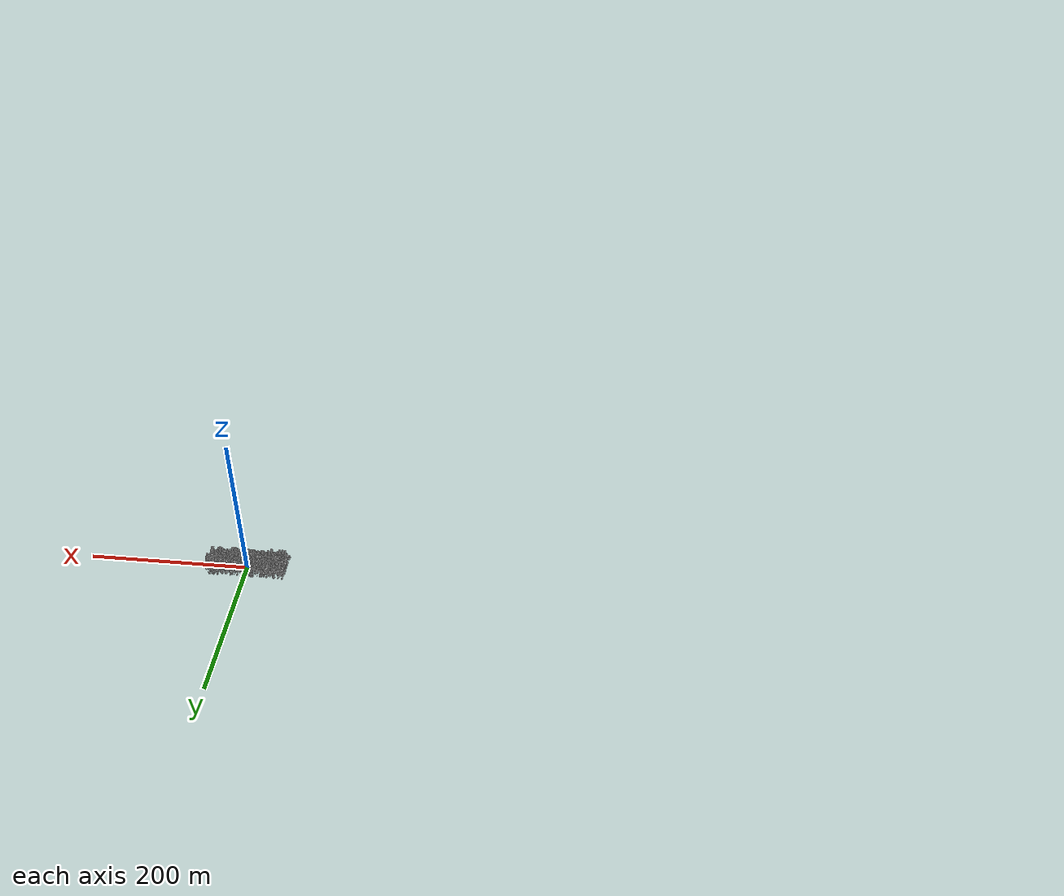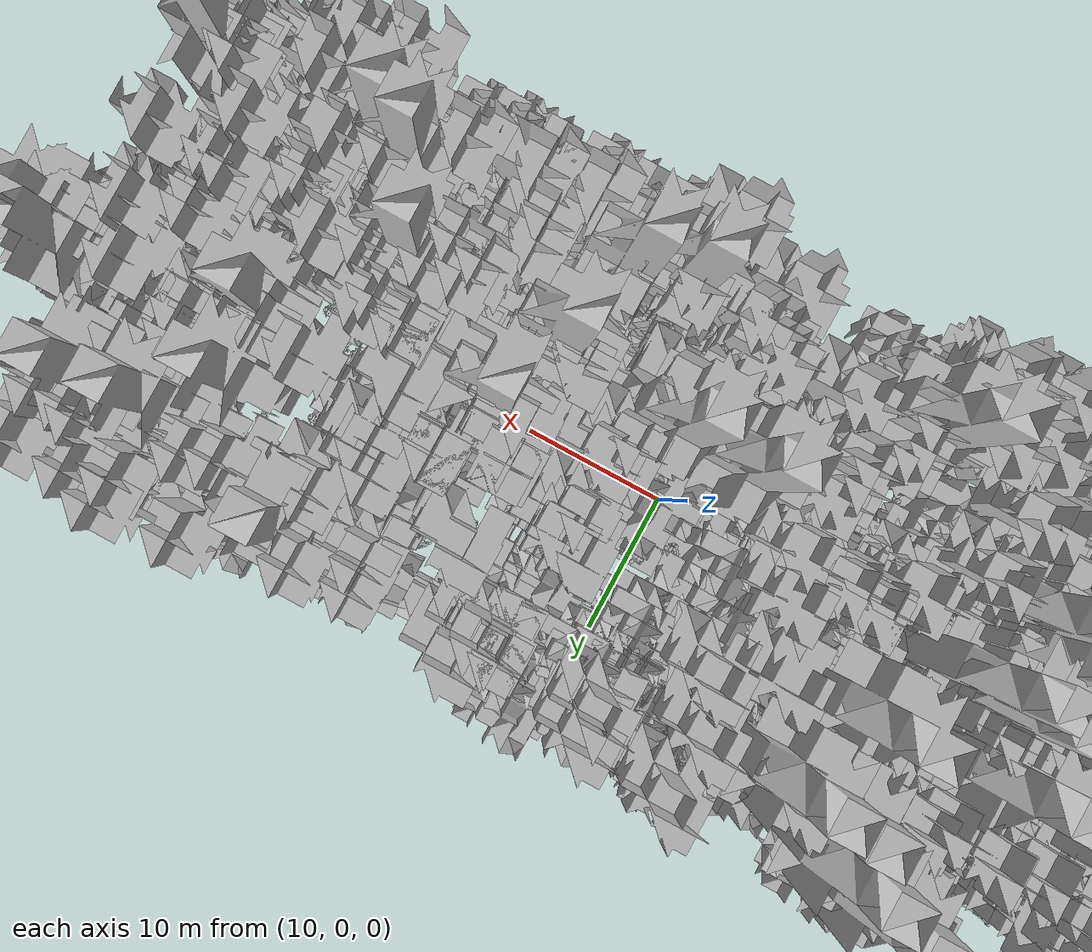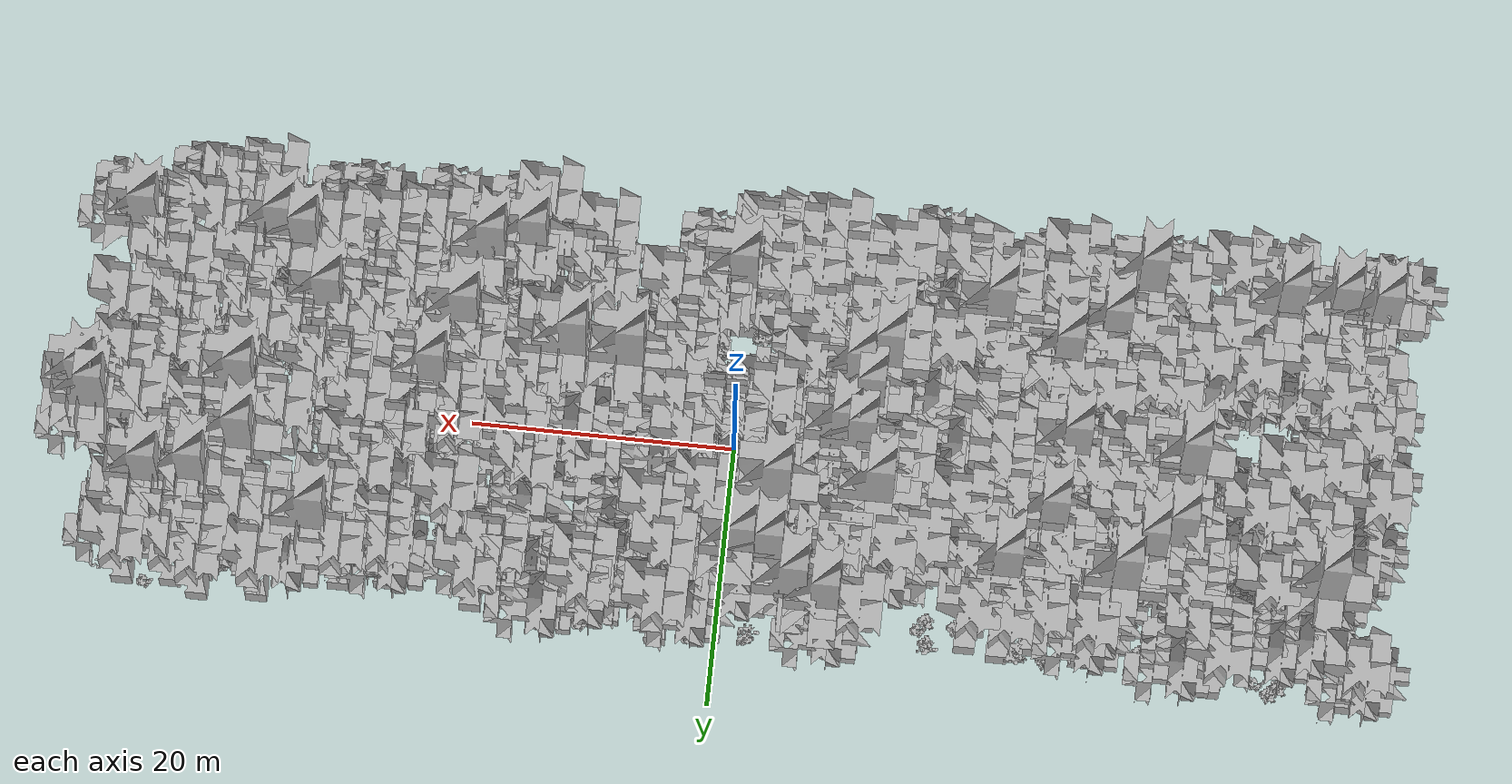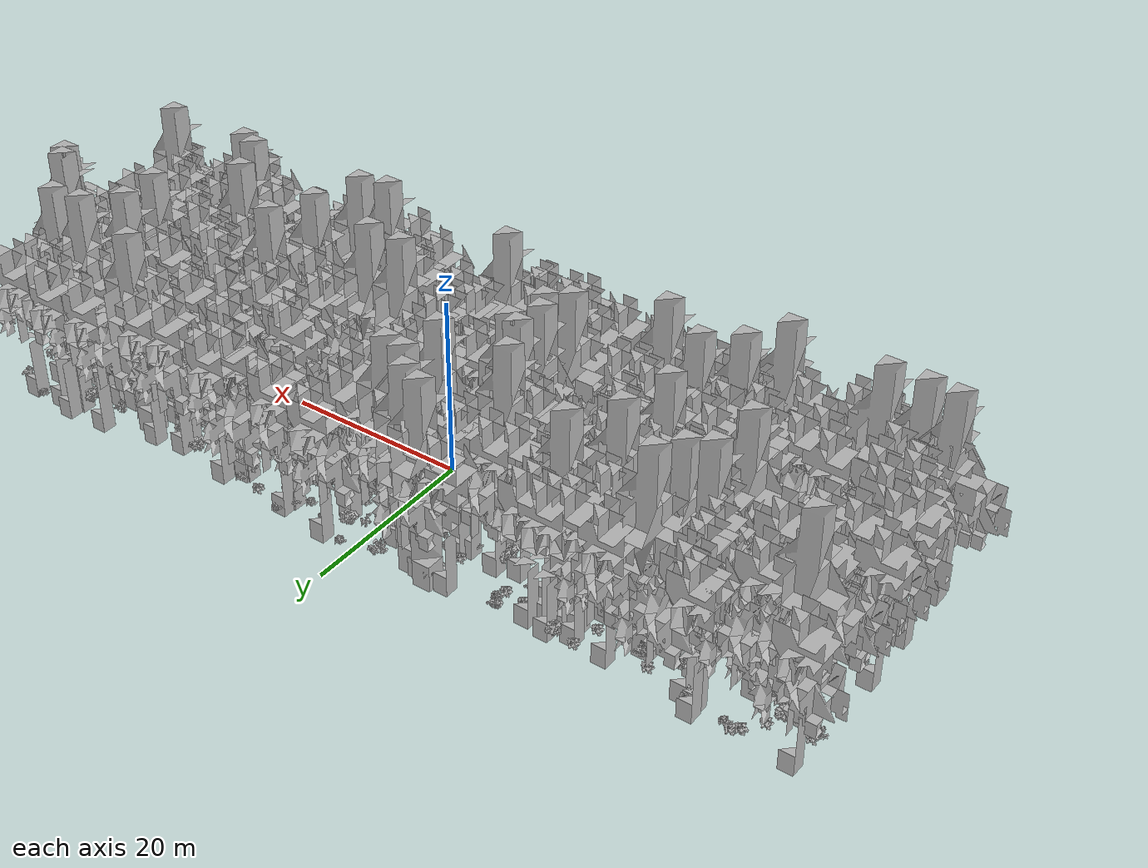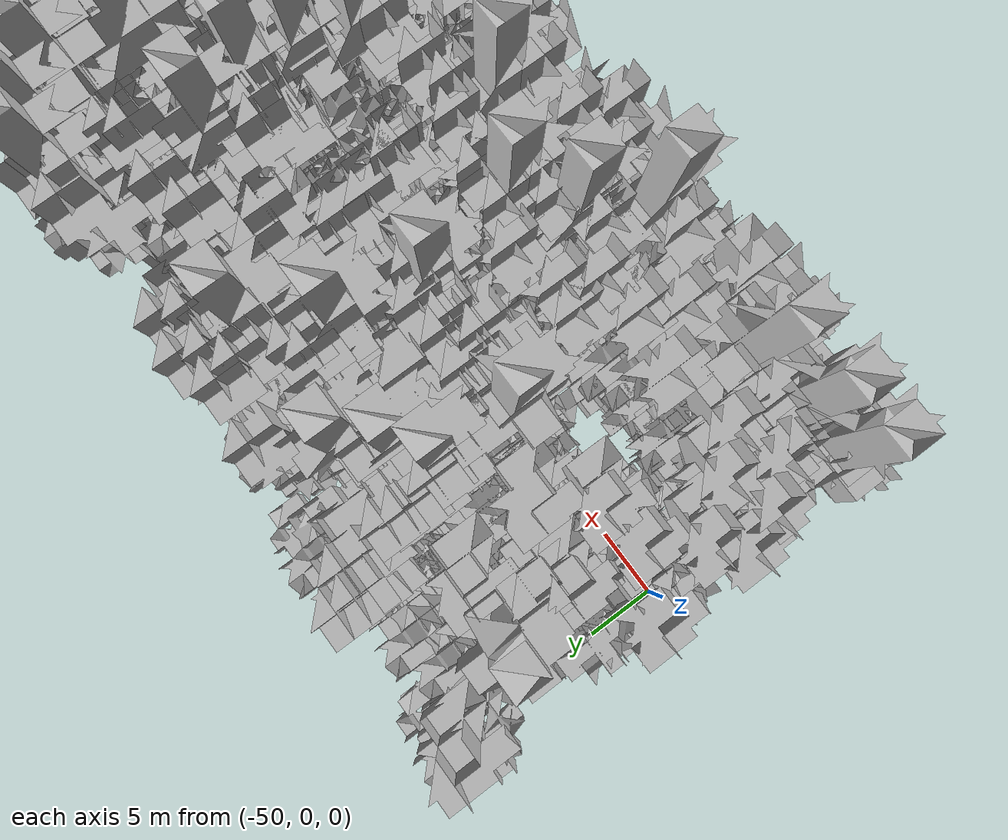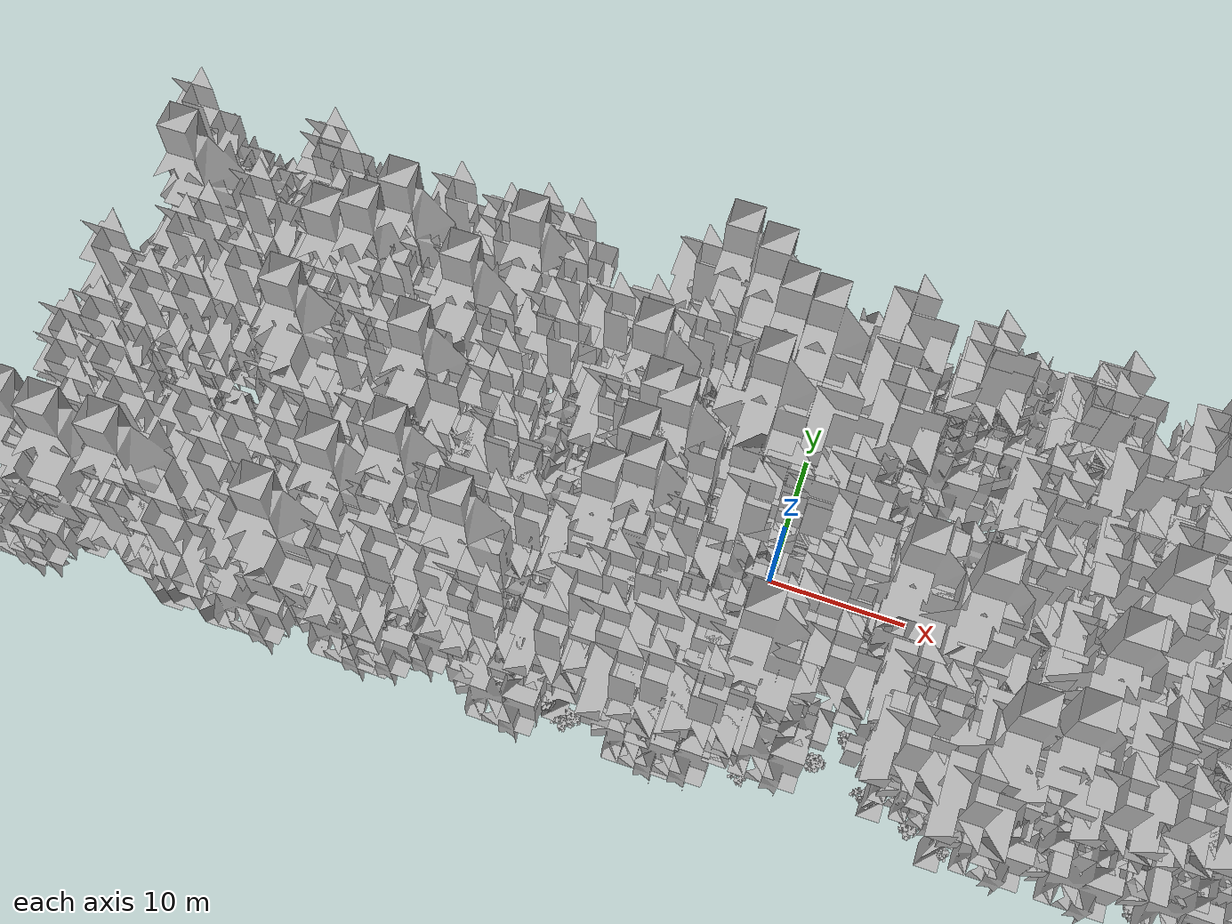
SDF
<sdf version="1.7">
    <world name="default">
        <plugin name="mrs_gazebo_static_transform_republisher_plugin" filename="libMrsGazeboCommonResources_StaticTransformRepublisher.so"/>
        <spherical_coordinates>
            <surface_model>EARTH_WGS84</surface_model>
            <latitude_deg>47.3977</latitude_deg>
            <longitude_deg>8.54559</longitude_deg>
            <elevation>0</elevation>
            <heading_deg>0</heading_deg>
        </spherical_coordinates>
        <physics name="default_physics" default="0" type="ode">
            <ode>
                <solver>
                    <type>quick</type>
                    <iters>10</iters>
                    <sor>1.3</sor>
                    <use_dynamic_moi_rescaling>0</use_dynamic_moi_rescaling>
                </solver>
                <constraints>
                    <cfm>0</cfm>
                    <erp>0.2</erp>
                    <contact_max_correcting_vel>1000</contact_max_correcting_vel>
                    <contact_surface_layer>0.001</contact_surface_layer>
                </constraints>
            </ode>
            <max_step_size>0.004</max_step_size>
            <real_time_factor>1</real_time_factor>
            <real_time_update_rate>250</real_time_update_rate>
        </physics>
        <scene>
            <shadows>0</shadows>
            <ambient>0.4 0.4 0.4 1</ambient>
            <background>0.7 0.7 0.7 1</background>
        </scene>
        <light name="sun" type="directional">
            <pose>0 0 1000 0.4 0.2 0</pose>
            <diffuse>1 1 1 1</diffuse>
            <specular>0.6 0.6 0.6 1</specular>
            <direction>0.1 0.1 -0.9</direction>
            <attenuation>
                <range>20</range>
                <constant>0.5</constant>
                <linear>0.01</linear>
                <quadratic>0.001</quadratic>
            </attenuation>
            <cast_shadows>1</cast_shadows>
            <spot>
                <inner_angle>0</inner_angle>
                <outer_angle>0</outer_angle>
                <falloff>0</falloff>
            </spot>
        </light>
        <model name="ground_plane">
            <static>1</static>
            <link name="link">
                <collision name="collision">
                    <pose>0 0 0 0 -0 0</pose>
                    <geometry>
                        <plane>
                            <normal>0 0 1</normal>
                            <size>100 100</size>
                        </plane>
                    </geometry>
                    <surface>
                        <contact>
                            <ode>
                                <min_depth>0.01</min_depth>
                                <max_vel>0</max_vel>
                            </ode>
                        </contact>
                        <friction>
                            <ode/>
                            <torsional>
                                <ode/>
                            </torsional>
                        </friction>
                        <bounce/>
                    </surface>
                    <max_contacts>10</max_contacts>
                </collision>
                <visual name="grass">
                    <pose>0 0 0 0 -0 0</pose>
                    <cast_shadows>0</cast_shadows>
                    <geometry>
                        <mesh>
                            <scale>0.5814285714285714 0.18142857142857144 0.1</scale>
                            <uri>file://grass_plane/meshes/grass_plane.dae</uri>
                        </mesh>
                    </geometry>
                </visual>
                <self_collide>0</self_collide>
                <enable_wind>0</enable_wind>
                <kinematic>0</kinematic>
            </link>
        </model>
        <model name="the_void">
            <static>1</static>
            <link name="link">
                <pose>0 0 0.1 0 -0 0</pose>
                <visual name="the_void">
                    <pose>0 0 2 0 -0 0</pose>
                    <geometry>
                        <sphere>
                            <radius>0.25</radius>
                        </sphere>
                    </geometry>
                    <material>
                        <script>
                            <uri>file://media/materials/scripts/Gazebo.material</uri>
                            <name>Gazebo/Black</name>
                        </script>
                    </material>
                </visual>
                <self_collide>0</self_collide>
                <enable_wind>0</enable_wind>
                <kinematic>0</kinematic>
            </link>
            <pose>-1000 -1000 0 0 -0 0</pose>
        </model>
        <gui fullscreen="0">
            <camera name="camera">
                <pose>35.1577 98.6044 40.0204 0 0.407996 -1.99761</pose>
                <view_controller>orbit</view_controller>
                <projection_type>perspective</projection_type>
            </camera>
        </gui>
        <plugin name="mrs_gazebo_rviz_cam_synchronizer" filename="libMrsGazeboCommonResources_RvizCameraSynchronizer.so">
            <target_frame_id>gazebo_user_camera</target_frame_id>
            <world_origin_frame_id>uav1/gps_origin</world_origin_frame_id>
            <frame_to_follow>uav1</frame_to_follow>
        </plugin>
        <gravity>0 0 -9.8066</gravity>
        <magnetic_field>6e-06 2.3e-05 -4.2e-05</magnetic_field>
        <atmosphere type="adiabatic"/>
        <wind/>
        <model name="Tree 0">
            <static>1</static>
            <pose>-26.765938401157396 1.6291997413746877 0 1.57079 -0 0</pose>
            <link name="link">
                <pose>0 0 0 0 -0 0</pose>
                <collision name="collision">
                    <geometry>
                        <mesh>
                            <scale>3.5 5 3.5</scale>
                            <uri>model://tree_9/meshes/tree_9.obj</uri>
                        </mesh>
                    </geometry>
                    <max_contacts>10</max_contacts>
                    <surface>
                        <contact>
                            <ode/>
                        </contact>
                        <bounce/>
                        <friction>
                            <torsional>
                                <ode/>
                            </torsional>
                            <ode/>
                        </friction>
                    </surface>
                </collision>
                <visual name="visual">
                    <geometry>
                        <mesh>
                            <scale>3.5 5 3.5</scale>
                            <uri>model://tree_9/meshes/tree_9.obj</uri>
                        </mesh>
                    </geometry>
                </visual>
                <self_collide>0</self_collide>
                <enable_wind>0</enable_wind>
                <kinematic>0</kinematic>
            </link>
        </model>
        <model name="Tree 1">
            <static>1</static>
            <pose>1.3071375135084722 10.766365979711825 0 1.57079 -0 0</pose>
            <link name="link">
                <pose>0 0 0 0 -0 0</pose>
                <collision name="collision">
                    <geometry>
                        <mesh>
                            <scale>3.5 5 3.5</scale>
                            <uri>model://tree_2/meshes/tree_2.obj</uri>
                        </mesh>
                    </geometry>
                    <max_contacts>10</max_contacts>
                    <surface>
                        <contact>
                            <ode/>
                        </contact>
                        <bounce/>
                        <friction>
                            <torsional>
                                <ode/>
                            </torsional>
                            <ode/>
                        </friction>
                    </surface>
                </collision>
                <visual name="visual">
                    <geometry>
                        <mesh>
                            <scale>3.5 5 3.5</scale>
                            <uri>model://tree_2/meshes/tree_2.obj</uri>
                        </mesh>
                    </geometry>
                </visual>
                <self_collide>0</self_collide>
                <enable_wind>0</enable_wind>
                <kinematic>0</kinematic>
            </link>
        </model>
        <model name="Tree 2">
            <static>1</static>
            <pose>-38.52763291377046 11.083928158771037 0 1.57079 -0 0</pose>
            <link name="link">
                <pose>0 0 0 0 -0 0</pose>
                <collision name="collision">
                    <geometry>
                        <mesh>
                            <scale>3.5 5 3.5</scale>
                            <uri>model://tree_2/meshes/tree_2.obj</uri>
                        </mesh>
                    </geometry>
                    <max_contacts>10</max_contacts>
                    <surface>
                        <contact>
                            <ode/>
                        </contact>
                        <bounce/>
                        <friction>
                            <torsional>
                                <ode/>
                            </torsional>
                            <ode/>
                        </friction>
                    </surface>
                </collision>
                <visual name="visual">
                    <geometry>
                        <mesh>
                            <scale>3.5 5 3.5</scale>
                            <uri>model://tree_2/meshes/tree_2.obj</uri>
                        </mesh>
                    </geometry>
                </visual>
                <self_collide>0</self_collide>
                <enable_wind>0</enable_wind>
                <kinematic>0</kinematic>
            </link>
        </model>
        <model name="Tree 3">
            <static>1</static>
            <pose>12.475687540186193 1.0689887489923429 0 1.57079 -0 0</pose>
            <link name="link">
                <pose>0 0 0 0 -0 0</pose>
                <collision name="collision">
                    <geometry>
                        <mesh>
                            <scale>3.5 5 3.5</scale>
                            <uri>model://tree_2/meshes/tree_2.obj</uri>
                        </mesh>
                    </geometry>
                    <max_contacts>10</max_contacts>
                    <surface>
                        <contact>
                            <ode/>
                        </contact>
                        <bounce/>
                        <friction>
                            <torsional>
                                <ode/>
                            </torsional>
                            <ode/>
                        </friction>
                    </surface>
                </collision>
                <visual name="visual">
                    <geometry>
                        <mesh>
                            <scale>3.5 5 3.5</scale>
                            <uri>model://tree_2/meshes/tree_2.obj</uri>
                        </mesh>
                    </geometry>
                </visual>
                <self_collide>0</self_collide>
                <enable_wind>0</enable_wind>
                <kinematic>0</kinematic>
            </link>
        </model>
        <model name="Tree 4">
            <static>1</static>
            <pose>37.6744040516204 -5.781511116738173 0 1.57079 -0 0</pose>
            <link name="link">
                <pose>0 0 0 0 -0 0</pose>
                <collision name="collision">
                    <geometry>
                        <mesh>
                            <scale>3.5 5 3.5</scale>
                            <uri>model://tree_9/meshes/tree_9.obj</uri>
                        </mesh>
                    </geometry>
                    <max_contacts>10</max_contacts>
                    <surface>
                        <contact>
                            <ode/>
                        </contact>
                        <bounce/>
                        <friction>
                            <torsional>
                                <ode/>
                            </torsional>
                            <ode/>
                        </friction>
                    </surface>
                </collision>
                <visual name="visual">
                    <geometry>
                        <mesh>
                            <scale>3.5 5 3.5</scale>
                            <uri>model://tree_9/meshes/tree_9.obj</uri>
                        </mesh>
                    </geometry>
                </visual>
                <self_collide>0</self_collide>
                <enable_wind>0</enable_wind>
                <kinematic>0</kinematic>
            </link>
        </model>
        <model name="Tree 5">
            <static>1</static>
            <pose>4.5816983664871955 -4.005611911410291 0 1.57079 -0 0</pose>
            <link name="link">
                <pose>0 0 0 0 -0 0</pose>
                <collision name="collision">
                    <geometry>
                        <mesh>
                            <scale>3.5 5 3.5</scale>
                            <uri>model://tree_9/meshes/tree_9.obj</uri>
                        </mesh>
                    </geometry>
                    <max_contacts>10</max_contacts>
                    <surface>
                        <contact>
                            <ode/>
                        </contact>
                        <bounce/>
                        <friction>
                            <torsional>
                                <ode/>
                            </torsional>
                            <ode/>
                        </friction>
                    </surface>
                </collision>
                <visual name="visual">
                    <geometry>
                        <mesh>
                            <scale>3.5 5 3.5</scale>
                            <uri>model://tree_9/meshes/tree_9.obj</uri>
                        </mesh>
                    </geometry>
                </visual>
                <self_collide>0</self_collide>
                <enable_wind>0</enable_wind>
                <kinematic>0</kinematic>
            </link>
        </model>
        <model name="Tree 6">
            <static>1</static>
            <pose>-18.774931656274358 6.652846489458025 0 1.57079 -0 0</pose>
            <link name="link">
                <pose>0 0 0 0 -0 0</pose>
                <collision name="collision">
                    <geometry>
                        <mesh>
                            <scale>3.5 5 3.5</scale>
                            <uri>model://tree_9/meshes/tree_9.obj</uri>
                        </mesh>
                    </geometry>
                    <max_contacts>10</max_contacts>
                    <surface>
                        <contact>
                            <ode/>
                        </contact>
                        <bounce/>
                        <friction>
                            <torsional>
                                <ode/>
                            </torsional>
                            <ode/>
                        </friction>
                    </surface>
                </collision>
                <visual name="visual">
                    <geometry>
                        <mesh>
                            <scale>3.5 5 3.5</scale>
                            <uri>model://tree_9/meshes/tree_9.obj</uri>
                        </mesh>
                    </geometry>
                </visual>
                <self_collide>0</self_collide>
                <enable_wind>0</enable_wind>
                <kinematic>0</kinematic>
            </link>
        </model>
        <model name="Tree 7">
            <static>1</static>
            <pose>42.68328478525899 -4.185480367363265 0 1.57079 -0 0</pose>
            <link name="link">
                <pose>0 0 0 0 -0 0</pose>
                <collision name="collision">
                    <geometry>
                        <mesh>
                            <scale>3.5 5 3.5</scale>
                            <uri>model://tree_9/meshes/tree_9.obj</uri>
                        </mesh>
                    </geometry>
                    <max_contacts>10</max_contacts>
                    <surface>
                        <contact>
                            <ode/>
                        </contact>
                        <bounce/>
                        <friction>
                            <torsional>
                                <ode/>
                            </torsional>
                            <ode/>
                        </friction>
                    </surface>
                </collision>
                <visual name="visual">
                    <geometry>
                        <mesh>
                            <scale>3.5 5 3.5</scale>
                            <uri>model://tree_9/meshes/tree_9.obj</uri>
                        </mesh>
                    </geometry>
                </visual>
                <self_collide>0</self_collide>
                <enable_wind>0</enable_wind>
                <kinematic>0</kinematic>
            </link>
        </model>
        <model name="Tree 8">
            <static>1</static>
            <pose>41.242199959268845 14.147451747460213 0 1.57079 -0 0</pose>
            <link name="link">
                <pose>0 0 0 0 -0 0</pose>
                <collision name="collision">
                    <geometry>
                        <mesh>
                            <scale>3.5 5 3.5</scale>
                            <uri>model://tree_9/meshes/tree_9.obj</uri>
                        </mesh>
                    </geometry>
                    <max_contacts>10</max_contacts>
                    <surface>
                        <contact>
                            <ode/>
                        </contact>
                        <bounce/>
                        <friction>
                            <torsional>
                                <ode/>
                            </torsional>
                            <ode/>
                        </friction>
                    </surface>
                </collision>
                <visual name="visual">
                    <geometry>
                        <mesh>
                            <scale>3.5 5 3.5</scale>
                            <uri>model://tree_9/meshes/tree_9.obj</uri>
                        </mesh>
                    </geometry>
                </visual>
                <self_collide>0</self_collide>
                <enable_wind>0</enable_wind>
                <kinematic>0</kinematic>
            </link>
        </model>
        <model name="Tree 9">
            <static>1</static>
            <pose>-8.203070580650177 1.2995697887504534 0 1.57079 -0 0</pose>
            <link name="link">
                <pose>0 0 0 0 -0 0</pose>
                <collision name="collision">
                    <geometry>
                        <mesh>
                            <scale>3.5 5 3.5</scale>
                            <uri>model://tree_2/meshes/tree_2.obj</uri>
                        </mesh>
                    </geometry>
                    <max_contacts>10</max_contacts>
                    <surface>
                        <contact>
                            <ode/>
                        </contact>
                        <bounce/>
                        <friction>
                            <torsional>
                                <ode/>
                            </torsional>
                            <ode/>
                        </friction>
                    </surface>
                </collision>
                <visual name="visual">
                    <geometry>
                        <mesh>
                            <scale>3.5 5 3.5</scale>
                            <uri>model://tree_2/meshes/tree_2.obj</uri>
                        </mesh>
                    </geometry>
                </visual>
                <self_collide>0</self_collide>
                <enable_wind>0</enable_wind>
                <kinematic>0</kinematic>
            </link>
        </model>
        <model name="Tree 10">
            <static>1</static>
            <pose>26.99071619698111 11.742982170944806 0 1.57079 -0 0</pose>
            <link name="link">
                <pose>0 0 0 0 -0 0</pose>
                <collision name="collision">
                    <geometry>
                        <mesh>
                            <scale>3.5 5 3.5</scale>
                            <uri>model://tree_2/meshes/tree_2.obj</uri>
                        </mesh>
                    </geometry>
                    <max_contacts>10</max_contacts>
                    <surface>
                        <contact>
                            <ode/>
                        </contact>
                        <bounce/>
                        <friction>
                            <torsional>
                                <ode/>
                            </torsional>
                            <ode/>
                        </friction>
                    </surface>
                </collision>
                <visual name="visual">
                    <geometry>
                        <mesh>
                            <scale>3.5 5 3.5</scale>
                            <uri>model://tree_2/meshes/tree_2.obj</uri>
                        </mesh>
                    </geometry>
                </visual>
                <self_collide>0</self_collide>
                <enable_wind>0</enable_wind>
                <kinematic>0</kinematic>
            </link>
        </model>
        <model name="Tree 11">
            <static>1</static>
            <pose>14.186589528992116 -5.3285073662944065 0 1.57079 -0 0</pose>
            <link name="link">
                <pose>0 0 0 0 -0 0</pose>
                <collision name="collision">
                    <geometry>
                        <mesh>
                            <scale>3.5 5 3.5</scale>
                            <uri>model://tree_9/meshes/tree_9.obj</uri>
                        </mesh>
                    </geometry>
                    <max_contacts>10</max_contacts>
                    <surface>
                        <contact>
                            <ode/>
                        </contact>
                        <bounce/>
                        <friction>
                            <torsional>
                                <ode/>
                            </torsional>
                            <ode/>
                        </friction>
                    </surface>
                </collision>
                <visual name="visual">
                    <geometry>
                        <mesh>
                            <scale>3.5 5 3.5</scale>
                            <uri>model://tree_9/meshes/tree_9.obj</uri>
                        </mesh>
                    </geometry>
                </visual>
                <self_collide>0</self_collide>
                <enable_wind>0</enable_wind>
                <kinematic>0</kinematic>
            </link>
        </model>
        <model name="Tree 12">
            <static>1</static>
            <pose>-35.485700106761605 8.818077774330469 0 1.57079 -0 0</pose>
            <link name="link">
                <pose>0 0 0 0 -0 0</pose>
                <collision name="collision">
                    <geometry>
                        <mesh>
                            <scale>3.5 5 3.5</scale>
                            <uri>model://tree_9/meshes/tree_9.obj</uri>
                        </mesh>
                    </geometry>
                    <max_contacts>10</max_contacts>
                    <surface>
                        <contact>
                            <ode/>
                        </contact>
                        <bounce/>
                        <friction>
                            <torsional>
                                <ode/>
                            </torsional>
                            <ode/>
                        </friction>
                    </surface>
                </collision>
                <visual name="visual">
                    <geometry>
                        <mesh>
                            <scale>3.5 5 3.5</scale>
                            <uri>model://tree_9/meshes/tree_9.obj</uri>
                        </mesh>
                    </geometry>
                </visual>
                <self_collide>0</self_collide>
                <enable_wind>0</enable_wind>
                <kinematic>0</kinematic>
            </link>
        </model>
        <model name="Tree 13">
            <static>1</static>
            <pose>42.76853482774929 -0.8321664190316973 0 1.57079 -0 0</pose>
            <link name="link">
                <pose>0 0 0 0 -0 0</pose>
                <collision name="collision">
                    <geometry>
                        <mesh>
                            <scale>3.5 5 3.5</scale>
                            <uri>model://tree_2/meshes/tree_2.obj</uri>
                        </mesh>
                    </geometry>
                    <max_contacts>10</max_contacts>
                    <surface>
                        <contact>
                            <ode/>
                        </contact>
                        <bounce/>
                        <friction>
                            <torsional>
                                <ode/>
                            </torsional>
                            <ode/>
                        </friction>
                    </surface>
                </collision>
                <visual name="visual">
                    <geometry>
                        <mesh>
                            <scale>3.5 5 3.5</scale>
                            <uri>model://tree_2/meshes/tree_2.obj</uri>
                        </mesh>
                    </geometry>
                </visual>
                <self_collide>0</self_collide>
                <enable_wind>0</enable_wind>
                <kinematic>0</kinematic>
            </link>
        </model>
        <model name="Tree 14">
            <static>1</static>
            <pose>34.90100354843085 -6.2940051640763635 0 1.57079 -0 0</pose>
            <link name="link">
                <pose>0 0 0 0 -0 0</pose>
                <collision name="collision">
                    <geometry>
                        <mesh>
                            <scale>3.5 5 3.5</scale>
                            <uri>model://tree_2/meshes/tree_2.obj</uri>
                        </mesh>
                    </geometry>
                    <max_contacts>10</max_contacts>
                    <surface>
                        <contact>
                            <ode/>
                        </contact>
                        <bounce/>
                        <friction>
                            <torsional>
                                <ode/>
                            </torsional>
                            <ode/>
                        </friction>
                    </surface>
                </collision>
                <visual name="visual">
                    <geometry>
                        <mesh>
                            <scale>3.5 5 3.5</scale>
                            <uri>model://tree_2/meshes/tree_2.obj</uri>
                        </mesh>
                    </geometry>
                </visual>
                <self_collide>0</self_collide>
                <enable_wind>0</enable_wind>
                <kinematic>0</kinematic>
            </link>
        </model>
        <model name="Tree 15">
            <static>1</static>
            <pose>1.6187315218150786 -1.7069448226440347 0 1.57079 -0 0</pose>
            <link name="link">
                <pose>0 0 0 0 -0 0</pose>
                <collision name="collision">
                    <geometry>
                        <mesh>
                            <scale>3.5 5 3.5</scale>
                            <uri>model://tree_2/meshes/tree_2.obj</uri>
                        </mesh>
                    </geometry>
                    <max_contacts>10</max_contacts>
                    <surface>
                        <contact>
                            <ode/>
                        </contact>
                        <bounce/>
                        <friction>
                            <torsional>
                                <ode/>
                            </torsional>
                            <ode/>
                        </friction>
                    </surface>
                </collision>
                <visual name="visual">
                    <geometry>
                        <mesh>
                            <scale>3.5 5 3.5</scale>
                            <uri>model://tree_2/meshes/tree_2.obj</uri>
                        </mesh>
                    </geometry>
                </visual>
                <self_collide>0</self_collide>
                <enable_wind>0</enable_wind>
                <kinematic>0</kinematic>
            </link>
        </model>
        <model name="Tree 16">
            <static>1</static>
            <pose>24.49664673380343 3.461644481899274 0 1.57079 -0 0</pose>
            <link name="link">
                <pose>0 0 0 0 -0 0</pose>
                <collision name="collision">
                    <geometry>
                        <mesh>
                            <scale>3.5 5 3.5</scale>
                            <uri>model://tree_2/meshes/tree_2.obj</uri>
                        </mesh>
                    </geometry>
                    <max_contacts>10</max_contacts>
                    <surface>
                        <contact>
                            <ode/>
                        </contact>
                        <bounce/>
                        <friction>
                            <torsional>
                                <ode/>
                            </torsional>
                            <ode/>
                        </friction>
                    </surface>
                </collision>
                <visual name="visual">
                    <geometry>
                        <mesh>
                            <scale>3.5 5 3.5</scale>
                            <uri>model://tree_2/meshes/tree_2.obj</uri>
                        </mesh>
                    </geometry>
                </visual>
                <self_collide>0</self_collide>
                <enable_wind>0</enable_wind>
                <kinematic>0</kinematic>
            </link>
        </model>
        <model name="Tree 17">
            <static>1</static>
            <pose>27.890801383413674 2.0910277010316953 0 1.57079 -0 0</pose>
            <link name="link">
                <pose>0 0 0 0 -0 0</pose>
                <collision name="collision">
                    <geometry>
                        <mesh>
                            <scale>3.5 5 3.5</scale>
                            <uri>model://tree_9/meshes/tree_9.obj</uri>
                        </mesh>
                    </geometry>
                    <max_contacts>10</max_contacts>
                    <surface>
                        <contact>
                            <ode/>
                        </contact>
                        <bounce/>
                        <friction>
                            <torsional>
                                <ode/>
                            </torsional>
                            <ode/>
                        </friction>
                    </surface>
                </collision>
                <visual name="visual">
                    <geometry>
                        <mesh>
                            <scale>3.5 5 3.5</scale>
                            <uri>model://tree_9/meshes/tree_9.obj</uri>
                        </mesh>
                    </geometry>
                </visual>
                <self_collide>0</self_collide>
                <enable_wind>0</enable_wind>
                <kinematic>0</kinematic>
            </link>
        </model>
        <model name="Tree 18">
            <static>1</static>
            <pose>18.123560382419868 -9.57268278466848 0 1.57079 -0 0</pose>
            <link name="link">
                <pose>0 0 0 0 -0 0</pose>
                <collision name="collision">
                    <geometry>
                        <mesh>
                            <scale>3.5 5 3.5</scale>
                            <uri>model://tree_2/meshes/tree_2.obj</uri>
                        </mesh>
                    </geometry>
                    <max_contacts>10</max_contacts>
                    <surface>
                        <contact>
                            <ode/>
                        </contact>
                        <bounce/>
                        <friction>
                            <torsional>
                                <ode/>
                            </torsional>
                            <ode/>
                        </friction>
                    </surface>
                </collision>
                <visual name="visual">
                    <geometry>
                        <mesh>
                            <scale>3.5 5 3.5</scale>
                            <uri>model://tree_2/meshes/tree_2.obj</uri>
                        </mesh>
                    </geometry>
                </visual>
                <self_collide>0</self_collide>
                <enable_wind>0</enable_wind>
                <kinematic>0</kinematic>
            </link>
        </model>
        <model name="Tree 19">
            <static>1</static>
            <pose>39.1514535294414 14.96116728217942 0 1.57079 -0 0</pose>
            <link name="link">
                <pose>0 0 0 0 -0 0</pose>
                <collision name="collision">
                    <geometry>
                        <mesh>
                            <scale>3.5 5 3.5</scale>
                            <uri>model://tree_9/meshes/tree_9.obj</uri>
                        </mesh>
                    </geometry>
                    <max_contacts>10</max_contacts>
                    <surface>
                        <contact>
                            <ode/>
                        </contact>
                        <bounce/>
                        <friction>
                            <torsional>
                                <ode/>
                            </torsional>
                            <ode/>
                        </friction>
                    </surface>
                </collision>
                <visual name="visual">
                    <geometry>
                        <mesh>
                            <scale>3.5 5 3.5</scale>
                            <uri>model://tree_9/meshes/tree_9.obj</uri>
                        </mesh>
                    </geometry>
                </visual>
                <self_collide>0</self_collide>
                <enable_wind>0</enable_wind>
                <kinematic>0</kinematic>
            </link>
        </model>
        <model name="Tree 20">
            <static>1</static>
            <pose>-24.108105005998816 5.87940821454001 0 1.57079 -0 0</pose>
            <link name="link">
                <pose>0 0 0 0 -0 0</pose>
                <collision name="collision">
                    <geometry>
                        <mesh>
                            <scale>3.5 5 3.5</scale>
                            <uri>model://tree_4/meshes/tree_4.obj</uri>
                        </mesh>
                    </geometry>
                    <max_contacts>10</max_contacts>
                    <surface>
                        <contact>
                            <ode/>
                        </contact>
                        <bounce/>
                        <friction>
                            <torsional>
                                <ode/>
                            </torsional>
                            <ode/>
                        </friction>
                    </surface>
                </collision>
                <visual name="visual">
                    <geometry>
                        <mesh>
                            <scale>3.5 5 3.5</scale>
                            <uri>model://tree_4/meshes/tree_4.obj</uri>
                        </mesh>
                    </geometry>
                </visual>
                <self_collide>0</self_collide>
                <enable_wind>0</enable_wind>
                <kinematic>0</kinematic>
            </link>
        </model>
        <model name="Tree 21">
            <static>1</static>
            <pose>-30.586113909239426 -5.416747287791264 0 1.57079 -0 0</pose>
            <link name="link">
                <pose>0 0 0 0 -0 0</pose>
                <collision name="collision">
                    <geometry>
                        <mesh>
                            <scale>3.5 5 3.5</scale>
                            <uri>model://tree_9/meshes/tree_9.obj</uri>
                        </mesh>
                    </geometry>
                    <max_contacts>10</max_contacts>
                    <surface>
                        <contact>
                            <ode/>
                        </contact>
                        <bounce/>
                        <friction>
                            <torsional>
                                <ode/>
                            </torsional>
                            <ode/>
                        </friction>
                    </surface>
                </collision>
                <visual name="visual">
                    <geometry>
                        <mesh>
                            <scale>3.5 5 3.5</scale>
                            <uri>model://tree_9/meshes/tree_9.obj</uri>
                        </mesh>
                    </geometry>
                </visual>
                <self_collide>0</self_collide>
                <enable_wind>0</enable_wind>
                <kinematic>0</kinematic>
            </link>
        </model>
        <model name="Tree 22">
            <static>1</static>
            <pose>44.93329557938502 14.2828734806458 0 1.57079 -0 0</pose>
            <link name="link">
                <pose>0 0 0 0 -0 0</pose>
                <collision name="collision">
                    <geometry>
                        <mesh>
                            <scale>3.5 5 3.5</scale>
                            <uri>model://tree_9/meshes/tree_9.obj</uri>
                        </mesh>
                    </geometry>
                    <max_contacts>10</max_contacts>
                    <surface>
                        <contact>
                            <ode/>
                        </contact>
                        <bounce/>
                        <friction>
                            <torsional>
                                <ode/>
                            </torsional>
                            <ode/>
                        </friction>
                    </surface>
                </collision>
                <visual name="visual">
                    <geometry>
                        <mesh>
                            <scale>3.5 5 3.5</scale>
                            <uri>model://tree_9/meshes/tree_9.obj</uri>
                        </mesh>
                    </geometry>
                </visual>
                <self_collide>0</self_collide>
                <enable_wind>0</enable_wind>
                <kinematic>0</kinematic>
            </link>
        </model>
        <model name="Tree 23">
            <static>1</static>
            <pose>-28.04856181168212 -9.812862575359784 0 1.57079 -0 0</pose>
            <link name="link">
                <pose>0 0 0 0 -0 0</pose>
                <collision name="collision">
                    <geometry>
                        <mesh>
                            <scale>3.5 5 3.5</scale>
                            <uri>model://tree_9/meshes/tree_9.obj</uri>
                        </mesh>
                    </geometry>
                    <max_contacts>10</max_contacts>
                    <surface>
                        <contact>
                            <ode/>
                        </contact>
                        <bounce/>
                        <friction>
                            <torsional>
                                <ode/>
                            </torsional>
                            <ode/>
                        </friction>
                    </surface>
                </collision>
                <visual name="visual">
                    <geometry>
                        <mesh>
                            <scale>3.5 5 3.5</scale>
                            <uri>model://tree_9/meshes/tree_9.obj</uri>
                        </mesh>
                    </geometry>
                </visual>
                <self_collide>0</self_collide>
                <enable_wind>0</enable_wind>
                <kinematic>0</kinematic>
            </link>
        </model>
        <model name="Tree 24">
            <static>1</static>
            <pose>-9.336992735483946 1.3210746155699695 0 1.57079 -0 0</pose>
            <link name="link">
                <pose>0 0 0 0 -0 0</pose>
                <collision name="collision">
                    <geometry>
                        <mesh>
                            <scale>3.5 5 3.5</scale>
                            <uri>model://tree_4/meshes/tree_4.obj</uri>
                        </mesh>
                    </geometry>
                    <max_contacts>10</max_contacts>
                    <surface>
                        <contact>
                            <ode/>
                        </contact>
                        <bounce/>
                        <friction>
                            <torsional>
                                <ode/>
                            </torsional>
                            <ode/>
                        </friction>
                    </surface>
                </collision>
                <visual name="visual">
                    <geometry>
                        <mesh>
                            <scale>3.5 5 3.5</scale>
                            <uri>model://tree_4/meshes/tree_4.obj</uri>
                        </mesh>
                    </geometry>
                </visual>
                <self_collide>0</self_collide>
                <enable_wind>0</enable_wind>
                <kinematic>0</kinematic>
            </link>
        </model>
        <model name="Tree 25">
            <static>1</static>
            <pose>-21.53470297433803 13.58200722620655 0 1.57079 -0 0</pose>
            <link name="link">
                <pose>0 0 0 0 -0 0</pose>
                <collision name="collision">
                    <geometry>
                        <mesh>
                            <scale>3.5 5 3.5</scale>
                            <uri>model://tree_9/meshes/tree_9.obj</uri>
                        </mesh>
                    </geometry>
                    <max_contacts>10</max_contacts>
                    <surface>
                        <contact>
                            <ode/>
                        </contact>
                        <bounce/>
                        <friction>
                            <torsional>
                                <ode/>
                            </torsional>
                            <ode/>
                        </friction>
                    </surface>
                </collision>
                <visual name="visual">
                    <geometry>
                        <mesh>
                            <scale>3.5 5 3.5</scale>
                            <uri>model://tree_9/meshes/tree_9.obj</uri>
                        </mesh>
                    </geometry>
                </visual>
                <self_collide>0</self_collide>
                <enable_wind>0</enable_wind>
                <kinematic>0</kinematic>
            </link>
        </model>
        <model name="Tree 26">
            <static>1</static>
            <pose>-3.3455341259502163 10.574882866468975 0 1.57079 -0 0</pose>
            <link name="link">
                <pose>0 0 0 0 -0 0</pose>
                <collision name="collision">
                    <geometry>
                        <mesh>
                            <scale>3.5 5 3.5</scale>
                            <uri>model://tree_4/meshes/tree_4.obj</uri>
                        </mesh>
                    </geometry>
                    <max_contacts>10</max_contacts>
                    <surface>
                        <contact>
                            <ode/>
                        </contact>
                        <bounce/>
                        <friction>
                            <torsional>
                                <ode/>
                            </torsional>
                            <ode/>
                        </friction>
                    </surface>
                </collision>
                <visual name="visual">
                    <geometry>
                        <mesh>
                            <scale>3.5 5 3.5</scale>
                            <uri>model://tree_4/meshes/tree_4.obj</uri>
                        </mesh>
                    </geometry>
                </visual>
                <self_collide>0</self_collide>
                <enable_wind>0</enable_wind>
                <kinematic>0</kinematic>
            </link>
        </model>
        <model name="Tree 27">
            <static>1</static>
            <pose>4.450332211146737 5.303529250605308 0 1.57079 -0 0</pose>
            <link name="link">
                <pose>0 0 0 0 -0 0</pose>
                <collision name="collision">
                    <geometry>
                        <mesh>
                            <scale>3.5 5 3.5</scale>
                            <uri>model://tree_2/meshes/tree_2.obj</uri>
                        </mesh>
                    </geometry>
                    <max_contacts>10</max_contacts>
                    <surface>
                        <contact>
                            <ode/>
                        </contact>
                        <bounce/>
                        <friction>
                            <torsional>
                                <ode/>
                            </torsional>
                            <ode/>
                        </friction>
                    </surface>
                </collision>
                <visual name="visual">
                    <geometry>
                        <mesh>
                            <scale>3.5 5 3.5</scale>
                            <uri>model://tree_2/meshes/tree_2.obj</uri>
                        </mesh>
                    </geometry>
                </visual>
                <self_collide>0</self_collide>
                <enable_wind>0</enable_wind>
                <kinematic>0</kinematic>
            </link>
        </model>
        <model name="Tree 28">
            <static>1</static>
            <pose>20.364230537026543 -12.95609726575488 0 1.57079 -0 0</pose>
            <link name="link">
                <pose>0 0 0 0 -0 0</pose>
                <collision name="collision">
                    <geometry>
                        <mesh>
                            <scale>3.5 5 3.5</scale>
                            <uri>model://tree_2/meshes/tree_2.obj</uri>
                        </mesh>
                    </geometry>
                    <max_contacts>10</max_contacts>
                    <surface>
                        <contact>
                            <ode/>
                        </contact>
                        <bounce/>
                        <friction>
                            <torsional>
                                <ode/>
                            </torsional>
                            <ode/>
                        </friction>
                    </surface>
                </collision>
                <visual name="visual">
                    <geometry>
                        <mesh>
                            <scale>3.5 5 3.5</scale>
                            <uri>model://tree_2/meshes/tree_2.obj</uri>
                        </mesh>
                    </geometry>
                </visual>
                <self_collide>0</self_collide>
                <enable_wind>0</enable_wind>
                <kinematic>0</kinematic>
            </link>
        </model>
        <model name="Tree 29">
            <static>1</static>
            <pose>40.045501383420486 -11.56592414889058 0 1.57079 -0 0</pose>
            <link name="link">
                <pose>0 0 0 0 -0 0</pose>
                <collision name="collision">
                    <geometry>
                        <mesh>
                            <scale>3.5 5 3.5</scale>
                            <uri>model://tree_9/meshes/tree_9.obj</uri>
                        </mesh>
                    </geometry>
                    <max_contacts>10</max_contacts>
                    <surface>
                        <contact>
                            <ode/>
                        </contact>
                        <bounce/>
                        <friction>
                            <torsional>
                                <ode/>
                            </torsional>
                            <ode/>
                        </friction>
                    </surface>
                </collision>
                <visual name="visual">
                    <geometry>
                        <mesh>
                            <scale>3.5 5 3.5</scale>
                            <uri>model://tree_9/meshes/tree_9.obj</uri>
                        </mesh>
                    </geometry>
                </visual>
                <self_collide>0</self_collide>
                <enable_wind>0</enable_wind>
                <kinematic>0</kinematic>
            </link>
        </model>
        <model name="Tree 30">
            <static>1</static>
            <pose>42.04787139200549 11.462298915795785 0 1.57079 -0 0</pose>
            <link name="link">
                <pose>0 0 0 0 -0 0</pose>
                <collision name="collision">
                    <geometry>
                        <mesh>
                            <scale>3.5 5 3.5</scale>
                            <uri>model://tree_9/meshes/tree_9.obj</uri>
                        </mesh>
                    </geometry>
                    <max_contacts>10</max_contacts>
                    <surface>
                        <contact>
                            <ode/>
                        </contact>
                        <bounce/>
                        <friction>
                            <torsional>
                                <ode/>
                            </torsional>
                            <ode/>
                        </friction>
                    </surface>
                </collision>
                <visual name="visual">
                    <geometry>
                        <mesh>
                            <scale>3.5 5 3.5</scale>
                            <uri>model://tree_9/meshes/tree_9.obj</uri>
                        </mesh>
                    </geometry>
                </visual>
                <self_collide>0</self_collide>
                <enable_wind>0</enable_wind>
                <kinematic>0</kinematic>
            </link>
        </model>
        <model name="Tree 31">
            <static>1</static>
            <pose>-31.620926742056316 7.431973856351036 0 1.57079 -0 0</pose>
            <link name="link">
                <pose>0 0 0 0 -0 0</pose>
                <collision name="collision">
                    <geometry>
                        <mesh>
                            <scale>3.5 5 3.5</scale>
                            <uri>model://tree_4/meshes/tree_4.obj</uri>
                        </mesh>
                    </geometry>
                    <max_contacts>10</max_contacts>
                    <surface>
                        <contact>
                            <ode/>
                        </contact>
                        <bounce/>
                        <friction>
                            <torsional>
                                <ode/>
                            </torsional>
                            <ode/>
                        </friction>
                    </surface>
                </collision>
                <visual name="visual">
                    <geometry>
                        <mesh>
                            <scale>3.5 5 3.5</scale>
                            <uri>model://tree_4/meshes/tree_4.obj</uri>
                        </mesh>
                    </geometry>
                </visual>
                <self_collide>0</self_collide>
                <enable_wind>0</enable_wind>
                <kinematic>0</kinematic>
            </link>
        </model>
        <model name="Tree 32">
            <static>1</static>
            <pose>-18.20559136437409 -4.931028297914741 0 1.57079 -0 0</pose>
            <link name="link">
                <pose>0 0 0 0 -0 0</pose>
                <collision name="collision">
                    <geometry>
                        <mesh>
                            <scale>3.5 5 3.5</scale>
                            <uri>model://tree_2/meshes/tree_2.obj</uri>
                        </mesh>
                    </geometry>
                    <max_contacts>10</max_contacts>
                    <surface>
                        <contact>
                            <ode/>
                        </contact>
                        <bounce/>
                        <friction>
                            <torsional>
                                <ode/>
                            </torsional>
                            <ode/>
                        </friction>
                    </surface>
                </collision>
                <visual name="visual">
                    <geometry>
                        <mesh>
                            <scale>3.5 5 3.5</scale>
                            <uri>model://tree_2/meshes/tree_2.obj</uri>
                        </mesh>
                    </geometry>
                </visual>
                <self_collide>0</self_collide>
                <enable_wind>0</enable_wind>
                <kinematic>0</kinematic>
            </link>
        </model>
        <model name="Tree 33">
            <static>1</static>
            <pose>-8.080459085168307 -12.419843880254746 0 1.57079 -0 0</pose>
            <link name="link">
                <pose>0 0 0 0 -0 0</pose>
                <collision name="collision">
                    <geometry>
                        <mesh>
                            <scale>3.5 5 3.5</scale>
                            <uri>model://tree_9/meshes/tree_9.obj</uri>
                        </mesh>
                    </geometry>
                    <max_contacts>10</max_contacts>
                    <surface>
                        <contact>
                            <ode/>
                        </contact>
                        <bounce/>
                        <friction>
                            <torsional>
                                <ode/>
                            </torsional>
                            <ode/>
                        </friction>
                    </surface>
                </collision>
                <visual name="visual">
                    <geometry>
                        <mesh>
                            <scale>3.5 5 3.5</scale>
                            <uri>model://tree_9/meshes/tree_9.obj</uri>
                        </mesh>
                    </geometry>
                </visual>
                <self_collide>0</self_collide>
                <enable_wind>0</enable_wind>
                <kinematic>0</kinematic>
            </link>
        </model>
        <model name="Tree 34">
            <static>1</static>
            <pose>-45.58877833567233 8.194199561160499 0 1.57079 -0 0</pose>
            <link name="link">
                <pose>0 0 0 0 -0 0</pose>
                <collision name="collision">
                    <geometry>
                        <mesh>
                            <scale>3.5 5 3.5</scale>
                            <uri>model://tree_2/meshes/tree_2.obj</uri>
                        </mesh>
                    </geometry>
                    <max_contacts>10</max_contacts>
                    <surface>
                        <contact>
                            <ode/>
                        </contact>
                        <bounce/>
                        <friction>
                            <torsional>
                                <ode/>
                            </torsional>
                            <ode/>
                        </friction>
                    </surface>
                </collision>
                <visual name="visual">
                    <geometry>
                        <mesh>
                            <scale>3.5 5 3.5</scale>
                            <uri>model://tree_2/meshes/tree_2.obj</uri>
                        </mesh>
                    </geometry>
                </visual>
                <self_collide>0</self_collide>
                <enable_wind>0</enable_wind>
                <kinematic>0</kinematic>
            </link>
        </model>
        <model name="Tree 35">
            <static>1</static>
            <pose>-15.562215280508859 2.407233266605381 0 1.57079 -0 0</pose>
            <link name="link">
                <pose>0 0 0 0 -0 0</pose>
                <collision name="collision">
                    <geometry>
                        <mesh>
                            <scale>3.5 5 3.5</scale>
                            <uri>model://tree_2/meshes/tree_2.obj</uri>
                        </mesh>
                    </geometry>
                    <max_contacts>10</max_contacts>
                    <surface>
                        <contact>
                            <ode/>
                        </contact>
                        <bounce/>
                        <friction>
                            <torsional>
                                <ode/>
                            </torsional>
                            <ode/>
                        </friction>
                    </surface>
                </collision>
                <visual name="visual">
                    <geometry>
                        <mesh>
                            <scale>3.5 5 3.5</scale>
                            <uri>model://tree_2/meshes/tree_2.obj</uri>
                        </mesh>
                    </geometry>
                </visual>
                <self_collide>0</self_collide>
                <enable_wind>0</enable_wind>
                <kinematic>0</kinematic>
            </link>
        </model>
        <model name="Tree 36">
            <static>1</static>
            <pose>-43.83291956878647 8.347638240346459 0 1.57079 -0 0</pose>
            <link name="link">
                <pose>0 0 0 0 -0 0</pose>
                <collision name="collision">
                    <geometry>
                        <mesh>
                            <scale>3.5 5 3.5</scale>
                            <uri>model://tree_2/meshes/tree_2.obj</uri>
                        </mesh>
                    </geometry>
                    <max_contacts>10</max_contacts>
                    <surface>
                        <contact>
                            <ode/>
                        </contact>
                        <bounce/>
                        <friction>
                            <torsional>
                                <ode/>
                            </torsional>
                            <ode/>
                        </friction>
                    </surface>
                </collision>
                <visual name="visual">
                    <geometry>
                        <mesh>
                            <scale>3.5 5 3.5</scale>
                            <uri>model://tree_2/meshes/tree_2.obj</uri>
                        </mesh>
                    </geometry>
                </visual>
                <self_collide>0</self_collide>
                <enable_wind>0</enable_wind>
                <kinematic>0</kinematic>
            </link>
        </model>
        <model name="Tree 37">
            <static>1</static>
            <pose>-8.744928585873147 -3.7799355606415475 0 1.57079 -0 0</pose>
            <link name="link">
                <pose>0 0 0 0 -0 0</pose>
                <collision name="collision">
                    <geometry>
                        <mesh>
                            <scale>3.5 5 3.5</scale>
                            <uri>model://tree_4/meshes/tree_4.obj</uri>
                        </mesh>
                    </geometry>
                    <max_contacts>10</max_contacts>
                    <surface>
                        <contact>
                            <ode/>
                        </contact>
                        <bounce/>
                        <friction>
                            <torsional>
                                <ode/>
                            </torsional>
                            <ode/>
                        </friction>
                    </surface>
                </collision>
                <visual name="visual">
                    <geometry>
                        <mesh>
                            <scale>3.5 5 3.5</scale>
                            <uri>model://tree_4/meshes/tree_4.obj</uri>
                        </mesh>
                    </geometry>
                </visual>
                <self_collide>0</self_collide>
                <enable_wind>0</enable_wind>
                <kinematic>0</kinematic>
            </link>
        </model>
        <model name="Tree 38">
            <static>1</static>
            <pose>-8.661135999150467 9.714993716716812 0 1.57079 -0 0</pose>
            <link name="link">
                <pose>0 0 0 0 -0 0</pose>
                <collision name="collision">
                    <geometry>
                        <mesh>
                            <scale>3.5 5 3.5</scale>
                            <uri>model://tree_2/meshes/tree_2.obj</uri>
                        </mesh>
                    </geometry>
                    <max_contacts>10</max_contacts>
                    <surface>
                        <contact>
                            <ode/>
                        </contact>
                        <bounce/>
                        <friction>
                            <torsional>
                                <ode/>
                            </torsional>
                            <ode/>
                        </friction>
                    </surface>
                </collision>
                <visual name="visual">
                    <geometry>
                        <mesh>
                            <scale>3.5 5 3.5</scale>
                            <uri>model://tree_2/meshes/tree_2.obj</uri>
                        </mesh>
                    </geometry>
                </visual>
                <self_collide>0</self_collide>
                <enable_wind>0</enable_wind>
                <kinematic>0</kinematic>
            </link>
        </model>
        <model name="Tree 39">
            <static>1</static>
            <pose>-16.838851974309794 9.107836967116327 0 1.57079 -0 0</pose>
            <link name="link">
                <pose>0 0 0 0 -0 0</pose>
                <collision name="collision">
                    <geometry>
                        <mesh>
                            <scale>3.5 5 3.5</scale>
                            <uri>model://tree_2/meshes/tree_2.obj</uri>
                        </mesh>
                    </geometry>
                    <max_contacts>10</max_contacts>
                    <surface>
                        <contact>
                            <ode/>
                        </contact>
                        <bounce/>
                        <friction>
                            <torsional>
                                <ode/>
                            </torsional>
                            <ode/>
                        </friction>
                    </surface>
                </collision>
                <visual name="visual">
                    <geometry>
                        <mesh>
                            <scale>3.5 5 3.5</scale>
                            <uri>model://tree_2/meshes/tree_2.obj</uri>
                        </mesh>
                    </geometry>
                </visual>
                <self_collide>0</self_collide>
                <enable_wind>0</enable_wind>
                <kinematic>0</kinematic>
            </link>
        </model>
        <model name="Tree 40">
            <static>1</static>
            <pose>30.653771378390744 11.485021905221021 0 1.57079 -0 0</pose>
            <link name="link">
                <pose>0 0 0 0 -0 0</pose>
                <collision name="collision">
                    <geometry>
                        <mesh>
                            <scale>3.5 5 3.5</scale>
                            <uri>model://tree_4/meshes/tree_4.obj</uri>
                        </mesh>
                    </geometry>
                    <max_contacts>10</max_contacts>
                    <surface>
                        <contact>
                            <ode/>
                        </contact>
                        <bounce/>
                        <friction>
                            <torsional>
                                <ode/>
                            </torsional>
                            <ode/>
                        </friction>
                    </surface>
                </collision>
                <visual name="visual">
                    <geometry>
                        <mesh>
                            <scale>3.5 5 3.5</scale>
                            <uri>model://tree_4/meshes/tree_4.obj</uri>
                        </mesh>
                    </geometry>
                </visual>
                <self_collide>0</self_collide>
                <enable_wind>0</enable_wind>
                <kinematic>0</kinematic>
            </link>
        </model>
        <model name="Tree 41">
            <static>1</static>
            <pose>-24.451457299591986 -14.625689672736572 0 1.57079 -0 0</pose>
            <link name="link">
                <pose>0 0 0 0 -0 0</pose>
                <collision name="collision">
                    <geometry>
                        <mesh>
                            <scale>3.5 5 3.5</scale>
                            <uri>model://tree_9/meshes/tree_9.obj</uri>
                        </mesh>
                    </geometry>
                    <max_contacts>10</max_contacts>
                    <surface>
                        <contact>
                            <ode/>
                        </contact>
                        <bounce/>
                        <friction>
                            <torsional>
                                <ode/>
                            </torsional>
                            <ode/>
                        </friction>
                    </surface>
                </collision>
                <visual name="visual">
                    <geometry>
                        <mesh>
                            <scale>3.5 5 3.5</scale>
                            <uri>model://tree_9/meshes/tree_9.obj</uri>
                        </mesh>
                    </geometry>
                </visual>
                <self_collide>0</self_collide>
                <enable_wind>0</enable_wind>
                <kinematic>0</kinematic>
            </link>
        </model>
        <model name="Tree 42">
            <static>1</static>
            <pose>37.997805025380444 -5.241121096211378 0 1.57079 -0 0</pose>
            <link name="link">
                <pose>0 0 0 0 -0 0</pose>
                <collision name="collision">
                    <geometry>
                        <mesh>
                            <scale>3.5 5 3.5</scale>
                            <uri>model://tree_9/meshes/tree_9.obj</uri>
                        </mesh>
                    </geometry>
                    <max_contacts>10</max_contacts>
                    <surface>
                        <contact>
                            <ode/>
                        </contact>
                        <bounce/>
                        <friction>
                            <torsional>
                                <ode/>
                            </torsional>
                            <ode/>
                        </friction>
                    </surface>
                </collision>
                <visual name="visual">
                    <geometry>
                        <mesh>
                            <scale>3.5 5 3.5</scale>
                            <uri>model://tree_9/meshes/tree_9.obj</uri>
                        </mesh>
                    </geometry>
                </visual>
                <self_collide>0</self_collide>
                <enable_wind>0</enable_wind>
                <kinematic>0</kinematic>
            </link>
        </model>
        <model name="Tree 43">
            <static>1</static>
            <pose>-8.754490061471422 -7.617909862327358 0 1.57079 -0 0</pose>
            <link name="link">
                <pose>0 0 0 0 -0 0</pose>
                <collision name="collision">
                    <geometry>
                        <mesh>
                            <scale>3.5 5 3.5</scale>
                            <uri>model://tree_2/meshes/tree_2.obj</uri>
                        </mesh>
                    </geometry>
                    <max_contacts>10</max_contacts>
                    <surface>
                        <contact>
                            <ode/>
                        </contact>
                        <bounce/>
                        <friction>
                            <torsional>
                                <ode/>
                            </torsional>
                            <ode/>
                        </friction>
                    </surface>
                </collision>
                <visual name="visual">
                    <geometry>
                        <mesh>
                            <scale>3.5 5 3.5</scale>
                            <uri>model://tree_2/meshes/tree_2.obj</uri>
                        </mesh>
                    </geometry>
                </visual>
                <self_collide>0</self_collide>
                <enable_wind>0</enable_wind>
                <kinematic>0</kinematic>
            </link>
        </model>
        <model name="Tree 44">
            <static>1</static>
            <pose>-21.027879697015372 10.050995978160628 0 1.57079 -0 0</pose>
            <link name="link">
                <pose>0 0 0 0 -0 0</pose>
                <collision name="collision">
                    <geometry>
                        <mesh>
                            <scale>3.5 5 3.5</scale>
                            <uri>model://tree_4/meshes/tree_4.obj</uri>
                        </mesh>
                    </geometry>
                    <max_contacts>10</max_contacts>
                    <surface>
                        <contact>
                            <ode/>
                        </contact>
                        <bounce/>
                        <friction>
                            <torsional>
                                <ode/>
                            </torsional>
                            <ode/>
                        </friction>
                    </surface>
                </collision>
                <visual name="visual">
                    <geometry>
                        <mesh>
                            <scale>3.5 5 3.5</scale>
                            <uri>model://tree_4/meshes/tree_4.obj</uri>
                        </mesh>
                    </geometry>
                </visual>
                <self_collide>0</self_collide>
                <enable_wind>0</enable_wind>
                <kinematic>0</kinematic>
            </link>
        </model>
        <model name="Tree 45">
            <static>1</static>
            <pose>-4.563493109465412 -5.8370666191828136 0 1.57079 -0 0</pose>
            <link name="link">
                <pose>0 0 0 0 -0 0</pose>
                <collision name="collision">
                    <geometry>
                        <mesh>
                            <scale>3.5 5 3.5</scale>
                            <uri>model://tree_2/meshes/tree_2.obj</uri>
                        </mesh>
                    </geometry>
                    <max_contacts>10</max_contacts>
                    <surface>
                        <contact>
                            <ode/>
                        </contact>
                        <bounce/>
                        <friction>
                            <torsional>
                                <ode/>
                            </torsional>
                            <ode/>
                        </friction>
                    </surface>
                </collision>
                <visual name="visual">
                    <geometry>
                        <mesh>
                            <scale>3.5 5 3.5</scale>
                            <uri>model://tree_2/meshes/tree_2.obj</uri>
                        </mesh>
                    </geometry>
                </visual>
                <self_collide>0</self_collide>
                <enable_wind>0</enable_wind>
                <kinematic>0</kinematic>
            </link>
        </model>
        <model name="Tree 46">
            <static>1</static>
            <pose>-34.92136527826986 8.428432010104999 0 1.57079 -0 0</pose>
            <link name="link">
                <pose>0 0 0 0 -0 0</pose>
                <collision name="collision">
                    <geometry>
                        <mesh>
                            <scale>3.5 5 3.5</scale>
                            <uri>model://tree_2/meshes/tree_2.obj</uri>
                        </mesh>
                    </geometry>
                    <max_contacts>10</max_contacts>
                    <surface>
                        <contact>
                            <ode/>
                        </contact>
                        <bounce/>
                        <friction>
                            <torsional>
                                <ode/>
                            </torsional>
                            <ode/>
                        </friction>
                    </surface>
                </collision>
                <visual name="visual">
                    <geometry>
                        <mesh>
                            <scale>3.5 5 3.5</scale>
                            <uri>model://tree_2/meshes/tree_2.obj</uri>
                        </mesh>
                    </geometry>
                </visual>
                <self_collide>0</self_collide>
                <enable_wind>0</enable_wind>
                <kinematic>0</kinematic>
            </link>
        </model>
        <model name="Tree 47">
            <static>1</static>
            <pose>-21.771773369971676 4.564131654889394 0 1.57079 -0 0</pose>
            <link name="link">
                <pose>0 0 0 0 -0 0</pose>
                <collision name="collision">
                    <geometry>
                        <mesh>
                            <scale>3.5 5 3.5</scale>
                            <uri>model://tree_9/meshes/tree_9.obj</uri>
                        </mesh>
                    </geometry>
                    <max_contacts>10</max_contacts>
                    <surface>
                        <contact>
                            <ode/>
                        </contact>
                        <bounce/>
                        <friction>
                            <torsional>
                                <ode/>
                            </torsional>
                            <ode/>
                        </friction>
                    </surface>
                </collision>
                <visual name="visual">
                    <geometry>
                        <mesh>
                            <scale>3.5 5 3.5</scale>
                            <uri>model://tree_9/meshes/tree_9.obj</uri>
                        </mesh>
                    </geometry>
                </visual>
                <self_collide>0</self_collide>
                <enable_wind>0</enable_wind>
                <kinematic>0</kinematic>
            </link>
        </model>
        <model name="Tree 48">
            <static>1</static>
            <pose>-5.907783599531427 -4.239735757600787 0 1.57079 -0 0</pose>
            <link name="link">
                <pose>0 0 0 0 -0 0</pose>
                <collision name="collision">
                    <geometry>
                        <mesh>
                            <scale>3.5 5 3.5</scale>
                            <uri>model://tree_9/meshes/tree_9.obj</uri>
                        </mesh>
                    </geometry>
                    <max_contacts>10</max_contacts>
                    <surface>
                        <contact>
                            <ode/>
                        </contact>
                        <bounce/>
                        <friction>
                            <torsional>
                                <ode/>
                            </torsional>
                            <ode/>
                        </friction>
                    </surface>
                </collision>
                <visual name="visual">
                    <geometry>
                        <mesh>
                            <scale>3.5 5 3.5</scale>
                            <uri>model://tree_9/meshes/tree_9.obj</uri>
                        </mesh>
                    </geometry>
                </visual>
                <self_collide>0</self_collide>
                <enable_wind>0</enable_wind>
                <kinematic>0</kinematic>
            </link>
        </model>
        <model name="Tree 49">
            <static>1</static>
            <pose>33.44300823481328 -9.500627244571358 0 1.57079 -0 0</pose>
            <link name="link">
                <pose>0 0 0 0 -0 0</pose>
                <collision name="collision">
                    <geometry>
                        <mesh>
                            <scale>3.5 5 3.5</scale>
                            <uri>model://tree_2/meshes/tree_2.obj</uri>
                        </mesh>
                    </geometry>
                    <max_contacts>10</max_contacts>
                    <surface>
                        <contact>
                            <ode/>
                        </contact>
                        <bounce/>
                        <friction>
                            <torsional>
                                <ode/>
                            </torsional>
                            <ode/>
                        </friction>
                    </surface>
                </collision>
                <visual name="visual">
                    <geometry>
                        <mesh>
                            <scale>3.5 5 3.5</scale>
                            <uri>model://tree_2/meshes/tree_2.obj</uri>
                        </mesh>
                    </geometry>
                </visual>
                <self_collide>0</self_collide>
                <enable_wind>0</enable_wind>
                <kinematic>0</kinematic>
            </link>
        </model>
        <model name="Tree 50">
            <static>1</static>
            <pose>8.896817221549703 8.603378647390691 0 1.57079 -0 0</pose>
            <link name="link">
                <pose>0 0 0 0 -0 0</pose>
                <collision name="collision">
                    <geometry>
                        <mesh>
                            <scale>3.5 5 3.5</scale>
                            <uri>model://tree_2/meshes/tree_2.obj</uri>
                        </mesh>
                    </geometry>
                    <max_contacts>10</max_contacts>
                    <surface>
                        <contact>
                            <ode/>
                        </contact>
                        <bounce/>
                        <friction>
                            <torsional>
                                <ode/>
                            </torsional>
                            <ode/>
                        </friction>
                    </surface>
                </collision>
                <visual name="visual">
                    <geometry>
                        <mesh>
                            <scale>3.5 5 3.5</scale>
                            <uri>model://tree_2/meshes/tree_2.obj</uri>
                        </mesh>
                    </geometry>
                </visual>
                <self_collide>0</self_collide>
                <enable_wind>0</enable_wind>
                <kinematic>0</kinematic>
            </link>
        </model>
        <model name="Tree 51">
            <static>1</static>
            <pose>-48.37196353750602 -14.66861951984473 0 1.57079 -0 0</pose>
            <link name="link">
                <pose>0 0 0 0 -0 0</pose>
                <collision name="collision">
                    <geometry>
                        <mesh>
                            <scale>3.5 5 3.5</scale>
                            <uri>model://tree_2/meshes/tree_2.obj</uri>
                        </mesh>
                    </geometry>
                    <max_contacts>10</max_contacts>
                    <surface>
                        <contact>
                            <ode/>
                        </contact>
                        <bounce/>
                        <friction>
                            <torsional>
                                <ode/>
                            </torsional>
                            <ode/>
                        </friction>
                    </surface>
                </collision>
                <visual name="visual">
                    <geometry>
                        <mesh>
                            <scale>3.5 5 3.5</scale>
                            <uri>model://tree_2/meshes/tree_2.obj</uri>
                        </mesh>
                    </geometry>
                </visual>
                <self_collide>0</self_collide>
                <enable_wind>0</enable_wind>
                <kinematic>0</kinematic>
            </link>
        </model>
        <model name="Tree 52">
            <static>1</static>
            <pose>28.01484143926163 -11.492678406314141 0 1.57079 -0 0</pose>
            <link name="link">
                <pose>0 0 0 0 -0 0</pose>
                <collision name="collision">
                    <geometry>
                        <mesh>
                            <scale>3.5 5 3.5</scale>
                            <uri>model://tree_2/meshes/tree_2.obj</uri>
                        </mesh>
                    </geometry>
                    <max_contacts>10</max_contacts>
                    <surface>
                        <contact>
                            <ode/>
                        </contact>
                        <bounce/>
                        <friction>
                            <torsional>
                                <ode/>
                            </torsional>
                            <ode/>
                        </friction>
                    </surface>
                </collision>
                <visual name="visual">
                    <geometry>
                        <mesh>
                            <scale>3.5 5 3.5</scale>
                            <uri>model://tree_2/meshes/tree_2.obj</uri>
                        </mesh>
                    </geometry>
                </visual>
                <self_collide>0</self_collide>
                <enable_wind>0</enable_wind>
                <kinematic>0</kinematic>
            </link>
        </model>
        <model name="Tree 53">
            <static>1</static>
            <pose>17.615608959535294 -14.288774618522813 0 1.57079 -0 0</pose>
            <link name="link">
                <pose>0 0 0 0 -0 0</pose>
                <collision name="collision">
                    <geometry>
                        <mesh>
                            <scale>3.5 5 3.5</scale>
                            <uri>model://tree_2/meshes/tree_2.obj</uri>
                        </mesh>
                    </geometry>
                    <max_contacts>10</max_contacts>
                    <surface>
                        <contact>
                            <ode/>
                        </contact>
                        <bounce/>
                        <friction>
                            <torsional>
                                <ode/>
                            </torsional>
                            <ode/>
                        </friction>
                    </surface>
                </collision>
                <visual name="visual">
                    <geometry>
                        <mesh>
                            <scale>3.5 5 3.5</scale>
                            <uri>model://tree_2/meshes/tree_2.obj</uri>
                        </mesh>
                    </geometry>
                </visual>
                <self_collide>0</self_collide>
                <enable_wind>0</enable_wind>
                <kinematic>0</kinematic>
            </link>
        </model>
        <model name="Tree 54">
            <static>1</static>
            <pose>-17.361416371061484 -7.684900732536853 0 1.57079 -0 0</pose>
            <link name="link">
                <pose>0 0 0 0 -0 0</pose>
                <collision name="collision">
                    <geometry>
                        <mesh>
                            <scale>3.5 5 3.5</scale>
                            <uri>model://tree_9/meshes/tree_9.obj</uri>
                        </mesh>
                    </geometry>
                    <max_contacts>10</max_contacts>
                    <surface>
                        <contact>
                            <ode/>
                        </contact>
                        <bounce/>
                        <friction>
                            <torsional>
                                <ode/>
                            </torsional>
                            <ode/>
                        </friction>
                    </surface>
                </collision>
                <visual name="visual">
                    <geometry>
                        <mesh>
                            <scale>3.5 5 3.5</scale>
                            <uri>model://tree_9/meshes/tree_9.obj</uri>
                        </mesh>
                    </geometry>
                </visual>
                <self_collide>0</self_collide>
                <enable_wind>0</enable_wind>
                <kinematic>0</kinematic>
            </link>
        </model>
        <model name="Tree 55">
            <static>1</static>
            <pose>-9.071832926761367 -2.3822365051680805 0 1.57079 -0 0</pose>
            <link name="link">
                <pose>0 0 0 0 -0 0</pose>
                <collision name="collision">
                    <geometry>
                        <mesh>
                            <scale>3.5 5 3.5</scale>
                            <uri>model://tree_9/meshes/tree_9.obj</uri>
                        </mesh>
                    </geometry>
                    <max_contacts>10</max_contacts>
                    <surface>
                        <contact>
                            <ode/>
                        </contact>
                        <bounce/>
                        <friction>
                            <torsional>
                                <ode/>
                            </torsional>
                            <ode/>
                        </friction>
                    </surface>
                </collision>
                <visual name="visual">
                    <geometry>
                        <mesh>
                            <scale>3.5 5 3.5</scale>
                            <uri>model://tree_9/meshes/tree_9.obj</uri>
                        </mesh>
                    </geometry>
                </visual>
                <self_collide>0</self_collide>
                <enable_wind>0</enable_wind>
                <kinematic>0</kinematic>
            </link>
        </model>
        <model name="Tree 56">
            <static>1</static>
            <pose>-1.5665254225176284 -14.352320970904364 0 1.57079 -0 0</pose>
            <link name="link">
                <pose>0 0 0 0 -0 0</pose>
                <collision name="collision">
                    <geometry>
                        <mesh>
                            <scale>3.5 5 3.5</scale>
                            <uri>model://tree_9/meshes/tree_9.obj</uri>
                        </mesh>
                    </geometry>
                    <max_contacts>10</max_contacts>
                    <surface>
                        <contact>
                            <ode/>
                        </contact>
                        <bounce/>
                        <friction>
                            <torsional>
                                <ode/>
                            </torsional>
                            <ode/>
                        </friction>
                    </surface>
                </collision>
                <visual name="visual">
                    <geometry>
                        <mesh>
                            <scale>3.5 5 3.5</scale>
                            <uri>model://tree_9/meshes/tree_9.obj</uri>
                        </mesh>
                    </geometry>
                </visual>
                <self_collide>0</self_collide>
                <enable_wind>0</enable_wind>
                <kinematic>0</kinematic>
            </link>
        </model>
        <model name="Tree 57">
            <static>1</static>
            <pose>-40.91847956871045 -6.437152555221129 0 1.57079 -0 0</pose>
            <link name="link">
                <pose>0 0 0 0 -0 0</pose>
                <collision name="collision">
                    <geometry>
                        <mesh>
                            <scale>3.5 5 3.5</scale>
                            <uri>model://tree_2/meshes/tree_2.obj</uri>
                        </mesh>
                    </geometry>
                    <max_contacts>10</max_contacts>
                    <surface>
                        <contact>
                            <ode/>
                        </contact>
                        <bounce/>
                        <friction>
                            <torsional>
                                <ode/>
                            </torsional>
                            <ode/>
                        </friction>
                    </surface>
                </collision>
                <visual name="visual">
                    <geometry>
                        <mesh>
                            <scale>3.5 5 3.5</scale>
                            <uri>model://tree_2/meshes/tree_2.obj</uri>
                        </mesh>
                    </geometry>
                </visual>
                <self_collide>0</self_collide>
                <enable_wind>0</enable_wind>
                <kinematic>0</kinematic>
            </link>
        </model>
        <model name="Tree 58">
            <static>1</static>
            <pose>-28.32884579286468 1.8087587821888427 0 1.57079 -0 0</pose>
            <link name="link">
                <pose>0 0 0 0 -0 0</pose>
                <collision name="collision">
                    <geometry>
                        <mesh>
                            <scale>3.5 5 3.5</scale>
                            <uri>model://tree_2/meshes/tree_2.obj</uri>
                        </mesh>
                    </geometry>
                    <max_contacts>10</max_contacts>
                    <surface>
                        <contact>
                            <ode/>
                        </contact>
                        <bounce/>
                        <friction>
                            <torsional>
                                <ode/>
                            </torsional>
                            <ode/>
                        </friction>
                    </surface>
                </collision>
                <visual name="visual">
                    <geometry>
                        <mesh>
                            <scale>3.5 5 3.5</scale>
                            <uri>model://tree_2/meshes/tree_2.obj</uri>
                        </mesh>
                    </geometry>
                </visual>
                <self_collide>0</self_collide>
                <enable_wind>0</enable_wind>
                <kinematic>0</kinematic>
            </link>
        </model>
        <model name="Tree 59">
            <static>1</static>
            <pose>-36.06261478769515 13.089860364397865 0 1.57079 -0 0</pose>
            <link name="link">
                <pose>0 0 0 0 -0 0</pose>
                <collision name="collision">
                    <geometry>
                        <mesh>
                            <scale>3.5 5 3.5</scale>
                            <uri>model://tree_9/meshes/tree_9.obj</uri>
                        </mesh>
                    </geometry>
                    <max_contacts>10</max_contacts>
                    <surface>
                        <contact>
                            <ode/>
                        </contact>
                        <bounce/>
                        <friction>
                            <torsional>
                                <ode/>
                            </torsional>
                            <ode/>
                        </friction>
                    </surface>
                </collision>
                <visual name="visual">
                    <geometry>
                        <mesh>
                            <scale>3.5 5 3.5</scale>
                            <uri>model://tree_9/meshes/tree_9.obj</uri>
                        </mesh>
                    </geometry>
                </visual>
                <self_collide>0</self_collide>
                <enable_wind>0</enable_wind>
                <kinematic>0</kinematic>
            </link>
        </model>
        <model name="Tree 60">
            <static>1</static>
            <pose>-44.6098839110649 -5.97638470513971 0 1.57079 -0 0</pose>
            <link name="link">
                <pose>0 0 0 0 -0 0</pose>
                <collision name="collision">
                    <geometry>
                        <mesh>
                            <scale>3.5 5 3.5</scale>
                            <uri>model://tree_9/meshes/tree_9.obj</uri>
                        </mesh>
                    </geometry>
                    <max_contacts>10</max_contacts>
                    <surface>
                        <contact>
                            <ode/>
                        </contact>
                        <bounce/>
                        <friction>
                            <torsional>
                                <ode/>
                            </torsional>
                            <ode/>
                        </friction>
                    </surface>
                </collision>
                <visual name="visual">
                    <geometry>
                        <mesh>
                            <scale>3.5 5 3.5</scale>
                            <uri>model://tree_9/meshes/tree_9.obj</uri>
                        </mesh>
                    </geometry>
                </visual>
                <self_collide>0</self_collide>
                <enable_wind>0</enable_wind>
                <kinematic>0</kinematic>
            </link>
        </model>
        <model name="Tree 61">
            <static>1</static>
            <pose>-22.434067620886317 -5.848073350876028 0 1.57079 -0 0</pose>
            <link name="link">
                <pose>0 0 0 0 -0 0</pose>
                <collision name="collision">
                    <geometry>
                        <mesh>
                            <scale>3.5 5 3.5</scale>
                            <uri>model://tree_9/meshes/tree_9.obj</uri>
                        </mesh>
                    </geometry>
                    <max_contacts>10</max_contacts>
                    <surface>
                        <contact>
                            <ode/>
                        </contact>
                        <bounce/>
                        <friction>
                            <torsional>
                                <ode/>
                            </torsional>
                            <ode/>
                        </friction>
                    </surface>
                </collision>
                <visual name="visual">
                    <geometry>
                        <mesh>
                            <scale>3.5 5 3.5</scale>
                            <uri>model://tree_9/meshes/tree_9.obj</uri>
                        </mesh>
                    </geometry>
                </visual>
                <self_collide>0</self_collide>
                <enable_wind>0</enable_wind>
                <kinematic>0</kinematic>
            </link>
        </model>
        <model name="Tree 62">
            <static>1</static>
            <pose>-18.783444623144984 -2.9105486305790293 0 1.57079 -0 0</pose>
            <link name="link">
                <pose>0 0 0 0 -0 0</pose>
                <collision name="collision">
                    <geometry>
                        <mesh>
                            <scale>3.5 5 3.5</scale>
                            <uri>model://tree_9/meshes/tree_9.obj</uri>
                        </mesh>
                    </geometry>
                    <max_contacts>10</max_contacts>
                    <surface>
                        <contact>
                            <ode/>
                        </contact>
                        <bounce/>
                        <friction>
                            <torsional>
                                <ode/>
                            </torsional>
                            <ode/>
                        </friction>
                    </surface>
                </collision>
                <visual name="visual">
                    <geometry>
                        <mesh>
                            <scale>3.5 5 3.5</scale>
                            <uri>model://tree_9/meshes/tree_9.obj</uri>
                        </mesh>
                    </geometry>
                </visual>
                <self_collide>0</self_collide>
                <enable_wind>0</enable_wind>
                <kinematic>0</kinematic>
            </link>
        </model>
        <model name="Tree 63">
            <static>1</static>
            <pose>-34.0760261336106 0.49403077076489765 0 1.57079 -0 0</pose>
            <link name="link">
                <pose>0 0 0 0 -0 0</pose>
                <collision name="collision">
                    <geometry>
                        <mesh>
                            <scale>3.5 5 3.5</scale>
                            <uri>model://tree_4/meshes/tree_4.obj</uri>
                        </mesh>
                    </geometry>
                    <max_contacts>10</max_contacts>
                    <surface>
                        <contact>
                            <ode/>
                        </contact>
                        <bounce/>
                        <friction>
                            <torsional>
                                <ode/>
                            </torsional>
                            <ode/>
                        </friction>
                    </surface>
                </collision>
                <visual name="visual">
                    <geometry>
                        <mesh>
                            <scale>3.5 5 3.5</scale>
                            <uri>model://tree_4/meshes/tree_4.obj</uri>
                        </mesh>
                    </geometry>
                </visual>
                <self_collide>0</self_collide>
                <enable_wind>0</enable_wind>
                <kinematic>0</kinematic>
            </link>
        </model>
        <model name="Tree 64">
            <static>1</static>
            <pose>-10.783278401159848 -2.72829942089173 0 1.57079 -0 0</pose>
            <link name="link">
                <pose>0 0 0 0 -0 0</pose>
                <collision name="collision">
                    <geometry>
                        <mesh>
                            <scale>3.5 5 3.5</scale>
                            <uri>model://tree_2/meshes/tree_2.obj</uri>
                        </mesh>
                    </geometry>
                    <max_contacts>10</max_contacts>
                    <surface>
                        <contact>
                            <ode/>
                        </contact>
                        <bounce/>
                        <friction>
                            <torsional>
                                <ode/>
                            </torsional>
                            <ode/>
                        </friction>
                    </surface>
                </collision>
                <visual name="visual">
                    <geometry>
                        <mesh>
                            <scale>3.5 5 3.5</scale>
                            <uri>model://tree_2/meshes/tree_2.obj</uri>
                        </mesh>
                    </geometry>
                </visual>
                <self_collide>0</self_collide>
                <enable_wind>0</enable_wind>
                <kinematic>0</kinematic>
            </link>
        </model>
        <model name="Tree 65">
            <static>1</static>
            <pose>11.842523455003224 -11.729955695811302 0 1.57079 -0 0</pose>
            <link name="link">
                <pose>0 0 0 0 -0 0</pose>
                <collision name="collision">
                    <geometry>
                        <mesh>
                            <scale>3.5 5 3.5</scale>
                            <uri>model://tree_2/meshes/tree_2.obj</uri>
                        </mesh>
                    </geometry>
                    <max_contacts>10</max_contacts>
                    <surface>
                        <contact>
                            <ode/>
                        </contact>
                        <bounce/>
                        <friction>
                            <torsional>
                                <ode/>
                            </torsional>
                            <ode/>
                        </friction>
                    </surface>
                </collision>
                <visual name="visual">
                    <geometry>
                        <mesh>
                            <scale>3.5 5 3.5</scale>
                            <uri>model://tree_2/meshes/tree_2.obj</uri>
                        </mesh>
                    </geometry>
                </visual>
                <self_collide>0</self_collide>
                <enable_wind>0</enable_wind>
                <kinematic>0</kinematic>
            </link>
        </model>
        <model name="Tree 66">
            <static>1</static>
            <pose>6.949574401604345 -6.100101802029807 0 1.57079 -0 0</pose>
            <link name="link">
                <pose>0 0 0 0 -0 0</pose>
                <collision name="collision">
                    <geometry>
                        <mesh>
                            <scale>3.5 5 3.5</scale>
                            <uri>model://tree_2/meshes/tree_2.obj</uri>
                        </mesh>
                    </geometry>
                    <max_contacts>10</max_contacts>
                    <surface>
                        <contact>
                            <ode/>
                        </contact>
                        <bounce/>
                        <friction>
                            <torsional>
                                <ode/>
                            </torsional>
                            <ode/>
                        </friction>
                    </surface>
                </collision>
                <visual name="visual">
                    <geometry>
                        <mesh>
                            <scale>3.5 5 3.5</scale>
                            <uri>model://tree_2/meshes/tree_2.obj</uri>
                        </mesh>
                    </geometry>
                </visual>
                <self_collide>0</self_collide>
                <enable_wind>0</enable_wind>
                <kinematic>0</kinematic>
            </link>
        </model>
        <model name="Tree 67">
            <static>1</static>
            <pose>3.97143975474053 -6.183082926035869 0 1.57079 -0 0</pose>
            <link name="link">
                <pose>0 0 0 0 -0 0</pose>
                <collision name="collision">
                    <geometry>
                        <mesh>
                            <scale>3.5 5 3.5</scale>
                            <uri>model://tree_9/meshes/tree_9.obj</uri>
                        </mesh>
                    </geometry>
                    <max_contacts>10</max_contacts>
                    <surface>
                        <contact>
                            <ode/>
                        </contact>
                        <bounce/>
                        <friction>
                            <torsional>
                                <ode/>
                            </torsional>
                            <ode/>
                        </friction>
                    </surface>
                </collision>
                <visual name="visual">
                    <geometry>
                        <mesh>
                            <scale>3.5 5 3.5</scale>
                            <uri>model://tree_9/meshes/tree_9.obj</uri>
                        </mesh>
                    </geometry>
                </visual>
                <self_collide>0</self_collide>
                <enable_wind>0</enable_wind>
                <kinematic>0</kinematic>
            </link>
        </model>
        <model name="Tree 68">
            <static>1</static>
            <pose>38.92123281926693 13.405544073550978 0 1.57079 -0 0</pose>
            <link name="link">
                <pose>0 0 0 0 -0 0</pose>
                <collision name="collision">
                    <geometry>
                        <mesh>
                            <scale>3.5 5 3.5</scale>
                            <uri>model://tree_9/meshes/tree_9.obj</uri>
                        </mesh>
                    </geometry>
                    <max_contacts>10</max_contacts>
                    <surface>
                        <contact>
                            <ode/>
                        </contact>
                        <bounce/>
                        <friction>
                            <torsional>
                                <ode/>
                            </torsional>
                            <ode/>
                        </friction>
                    </surface>
                </collision>
                <visual name="visual">
                    <geometry>
                        <mesh>
                            <scale>3.5 5 3.5</scale>
                            <uri>model://tree_9/meshes/tree_9.obj</uri>
                        </mesh>
                    </geometry>
                </visual>
                <self_collide>0</self_collide>
                <enable_wind>0</enable_wind>
                <kinematic>0</kinematic>
            </link>
        </model>
        <model name="Tree 69">
            <static>1</static>
            <pose>-8.415344369734918 -1.9827578946694917 0 1.57079 -0 0</pose>
            <link name="link">
                <pose>0 0 0 0 -0 0</pose>
                <collision name="collision">
                    <geometry>
                        <mesh>
                            <scale>3.5 5 3.5</scale>
                            <uri>model://tree_2/meshes/tree_2.obj</uri>
                        </mesh>
                    </geometry>
                    <max_contacts>10</max_contacts>
                    <surface>
                        <contact>
                            <ode/>
                        </contact>
                        <bounce/>
                        <friction>
                            <torsional>
                                <ode/>
                            </torsional>
                            <ode/>
                        </friction>
                    </surface>
                </collision>
                <visual name="visual">
                    <geometry>
                        <mesh>
                            <scale>3.5 5 3.5</scale>
                            <uri>model://tree_2/meshes/tree_2.obj</uri>
                        </mesh>
                    </geometry>
                </visual>
                <self_collide>0</self_collide>
                <enable_wind>0</enable_wind>
                <kinematic>0</kinematic>
            </link>
        </model>
        <model name="Tree 70">
            <static>1</static>
            <pose>15.360218771544623 -1.163075434513651 0 1.57079 -0 0</pose>
            <link name="link">
                <pose>0 0 0 0 -0 0</pose>
                <collision name="collision">
                    <geometry>
                        <mesh>
                            <scale>3.5 5 3.5</scale>
                            <uri>model://tree_9/meshes/tree_9.obj</uri>
                        </mesh>
                    </geometry>
                    <max_contacts>10</max_contacts>
                    <surface>
                        <contact>
                            <ode/>
                        </contact>
                        <bounce/>
                        <friction>
                            <torsional>
                                <ode/>
                            </torsional>
                            <ode/>
                        </friction>
                    </surface>
                </collision>
                <visual name="visual">
                    <geometry>
                        <mesh>
                            <scale>3.5 5 3.5</scale>
                            <uri>model://tree_9/meshes/tree_9.obj</uri>
                        </mesh>
                    </geometry>
                </visual>
                <self_collide>0</self_collide>
                <enable_wind>0</enable_wind>
                <kinematic>0</kinematic>
            </link>
        </model>
        <model name="Tree 71">
            <static>1</static>
            <pose>-47.68907287249402 -0.09695158173489205 0 1.57079 -0 0</pose>
            <link name="link">
                <pose>0 0 0 0 -0 0</pose>
                <collision name="collision">
                    <geometry>
                        <mesh>
                            <scale>3.5 5 3.5</scale>
                            <uri>model://tree_2/meshes/tree_2.obj</uri>
                        </mesh>
                    </geometry>
                    <max_contacts>10</max_contacts>
                    <surface>
                        <contact>
                            <ode/>
                        </contact>
                        <bounce/>
                        <friction>
                            <torsional>
                                <ode/>
                            </torsional>
                            <ode/>
                        </friction>
                    </surface>
                </collision>
                <visual name="visual">
                    <geometry>
                        <mesh>
                            <scale>3.5 5 3.5</scale>
                            <uri>model://tree_2/meshes/tree_2.obj</uri>
                        </mesh>
                    </geometry>
                </visual>
                <self_collide>0</self_collide>
                <enable_wind>0</enable_wind>
                <kinematic>0</kinematic>
            </link>
        </model>
        <model name="Tree 72">
            <static>1</static>
            <pose>-18.529734741231177 9.803457465723088 0 1.57079 -0 0</pose>
            <link name="link">
                <pose>0 0 0 0 -0 0</pose>
                <collision name="collision">
                    <geometry>
                        <mesh>
                            <scale>3.5 5 3.5</scale>
                            <uri>model://tree_9/meshes/tree_9.obj</uri>
                        </mesh>
                    </geometry>
                    <max_contacts>10</max_contacts>
                    <surface>
                        <contact>
                            <ode/>
                        </contact>
                        <bounce/>
                        <friction>
                            <torsional>
                                <ode/>
                            </torsional>
                            <ode/>
                        </friction>
                    </surface>
                </collision>
                <visual name="visual">
                    <geometry>
                        <mesh>
                            <scale>3.5 5 3.5</scale>
                            <uri>model://tree_9/meshes/tree_9.obj</uri>
                        </mesh>
                    </geometry>
                </visual>
                <self_collide>0</self_collide>
                <enable_wind>0</enable_wind>
                <kinematic>0</kinematic>
            </link>
        </model>
        <model name="Tree 73">
            <static>1</static>
            <pose>-7.825205132838775 13.870935234682438 0 1.57079 -0 0</pose>
            <link name="link">
                <pose>0 0 0 0 -0 0</pose>
                <collision name="collision">
                    <geometry>
                        <mesh>
                            <scale>3.5 5 3.5</scale>
                            <uri>model://tree_4/meshes/tree_4.obj</uri>
                        </mesh>
                    </geometry>
                    <max_contacts>10</max_contacts>
                    <surface>
                        <contact>
                            <ode/>
                        </contact>
                        <bounce/>
                        <friction>
                            <torsional>
                                <ode/>
                            </torsional>
                            <ode/>
                        </friction>
                    </surface>
                </collision>
                <visual name="visual">
                    <geometry>
                        <mesh>
                            <scale>3.5 5 3.5</scale>
                            <uri>model://tree_4/meshes/tree_4.obj</uri>
                        </mesh>
                    </geometry>
                </visual>
                <self_collide>0</self_collide>
                <enable_wind>0</enable_wind>
                <kinematic>0</kinematic>
            </link>
        </model>
        <model name="Tree 74">
            <static>1</static>
            <pose>-11.376622710560973 3.4101426264522168 0 1.57079 -0 0</pose>
            <link name="link">
                <pose>0 0 0 0 -0 0</pose>
                <collision name="collision">
                    <geometry>
                        <mesh>
                            <scale>3.5 5 3.5</scale>
                            <uri>model://tree_9/meshes/tree_9.obj</uri>
                        </mesh>
                    </geometry>
                    <max_contacts>10</max_contacts>
                    <surface>
                        <contact>
                            <ode/>
                        </contact>
                        <bounce/>
                        <friction>
                            <torsional>
                                <ode/>
                            </torsional>
                            <ode/>
                        </friction>
                    </surface>
                </collision>
                <visual name="visual">
                    <geometry>
                        <mesh>
                            <scale>3.5 5 3.5</scale>
                            <uri>model://tree_9/meshes/tree_9.obj</uri>
                        </mesh>
                    </geometry>
                </visual>
                <self_collide>0</self_collide>
                <enable_wind>0</enable_wind>
                <kinematic>0</kinematic>
            </link>
        </model>
        <model name="Tree 75">
            <static>1</static>
            <pose>3.0339323526101083 13.483908740960189 0 1.57079 -0 0</pose>
            <link name="link">
                <pose>0 0 0 0 -0 0</pose>
                <collision name="collision">
                    <geometry>
                        <mesh>
                            <scale>3.5 5 3.5</scale>
                            <uri>model://tree_2/meshes/tree_2.obj</uri>
                        </mesh>
                    </geometry>
                    <max_contacts>10</max_contacts>
                    <surface>
                        <contact>
                            <ode/>
                        </contact>
                        <bounce/>
                        <friction>
                            <torsional>
                                <ode/>
                            </torsional>
                            <ode/>
                        </friction>
                    </surface>
                </collision>
                <visual name="visual">
                    <geometry>
                        <mesh>
                            <scale>3.5 5 3.5</scale>
                            <uri>model://tree_2/meshes/tree_2.obj</uri>
                        </mesh>
                    </geometry>
                </visual>
                <self_collide>0</self_collide>
                <enable_wind>0</enable_wind>
                <kinematic>0</kinematic>
            </link>
        </model>
        <model name="Tree 76">
            <static>1</static>
            <pose>-23.223493184124933 -6.963229964629345 0 1.57079 -0 0</pose>
            <link name="link">
                <pose>0 0 0 0 -0 0</pose>
                <collision name="collision">
                    <geometry>
                        <mesh>
                            <scale>3.5 5 3.5</scale>
                            <uri>model://tree_2/meshes/tree_2.obj</uri>
                        </mesh>
                    </geometry>
                    <max_contacts>10</max_contacts>
                    <surface>
                        <contact>
                            <ode/>
                        </contact>
                        <bounce/>
                        <friction>
                            <torsional>
                                <ode/>
                            </torsional>
                            <ode/>
                        </friction>
                    </surface>
                </collision>
                <visual name="visual">
                    <geometry>
                        <mesh>
                            <scale>3.5 5 3.5</scale>
                            <uri>model://tree_2/meshes/tree_2.obj</uri>
                        </mesh>
                    </geometry>
                </visual>
                <self_collide>0</self_collide>
                <enable_wind>0</enable_wind>
                <kinematic>0</kinematic>
            </link>
        </model>
        <model name="Tree 77">
            <static>1</static>
            <pose>-27.76972481168254 13.312691345991361 0 1.57079 -0 0</pose>
            <link name="link">
                <pose>0 0 0 0 -0 0</pose>
                <collision name="collision">
                    <geometry>
                        <mesh>
                            <scale>3.5 5 3.5</scale>
                            <uri>model://tree_9/meshes/tree_9.obj</uri>
                        </mesh>
                    </geometry>
                    <max_contacts>10</max_contacts>
                    <surface>
                        <contact>
                            <ode/>
                        </contact>
                        <bounce/>
                        <friction>
                            <torsional>
                                <ode/>
                            </torsional>
                            <ode/>
                        </friction>
                    </surface>
                </collision>
                <visual name="visual">
                    <geometry>
                        <mesh>
                            <scale>3.5 5 3.5</scale>
                            <uri>model://tree_9/meshes/tree_9.obj</uri>
                        </mesh>
                    </geometry>
                </visual>
                <self_collide>0</self_collide>
                <enable_wind>0</enable_wind>
                <kinematic>0</kinematic>
            </link>
        </model>
        <model name="Tree 78">
            <static>1</static>
            <pose>24.597199086074596 1.6079972094709376 0 1.57079 -0 0</pose>
            <link name="link">
                <pose>0 0 0 0 -0 0</pose>
                <collision name="collision">
                    <geometry>
                        <mesh>
                            <scale>3.5 5 3.5</scale>
                            <uri>model://tree_2/meshes/tree_2.obj</uri>
                        </mesh>
                    </geometry>
                    <max_contacts>10</max_contacts>
                    <surface>
                        <contact>
                            <ode/>
                        </contact>
                        <bounce/>
                        <friction>
                            <torsional>
                                <ode/>
                            </torsional>
                            <ode/>
                        </friction>
                    </surface>
                </collision>
                <visual name="visual">
                    <geometry>
                        <mesh>
                            <scale>3.5 5 3.5</scale>
                            <uri>model://tree_2/meshes/tree_2.obj</uri>
                        </mesh>
                    </geometry>
                </visual>
                <self_collide>0</self_collide>
                <enable_wind>0</enable_wind>
                <kinematic>0</kinematic>
            </link>
        </model>
        <model name="Tree 79">
            <static>1</static>
            <pose>-4.931363179732266 -11.620528589442456 0 1.57079 -0 0</pose>
            <link name="link">
                <pose>0 0 0 0 -0 0</pose>
                <collision name="collision">
                    <geometry>
                        <mesh>
                            <scale>3.5 5 3.5</scale>
                            <uri>model://tree_9/meshes/tree_9.obj</uri>
                        </mesh>
                    </geometry>
                    <max_contacts>10</max_contacts>
                    <surface>
                        <contact>
                            <ode/>
                        </contact>
                        <bounce/>
                        <friction>
                            <torsional>
                                <ode/>
                            </torsional>
                            <ode/>
                        </friction>
                    </surface>
                </collision>
                <visual name="visual">
                    <geometry>
                        <mesh>
                            <scale>3.5 5 3.5</scale>
                            <uri>model://tree_9/meshes/tree_9.obj</uri>
                        </mesh>
                    </geometry>
                </visual>
                <self_collide>0</self_collide>
                <enable_wind>0</enable_wind>
                <kinematic>0</kinematic>
            </link>
        </model>
        <model name="Tree 80">
            <static>1</static>
            <pose>-8.86147665553029 5.649098851880659 0 1.57079 -0 0</pose>
            <link name="link">
                <pose>0 0 0 0 -0 0</pose>
                <collision name="collision">
                    <geometry>
                        <mesh>
                            <scale>3.5 5 3.5</scale>
                            <uri>model://tree_2/meshes/tree_2.obj</uri>
                        </mesh>
                    </geometry>
                    <max_contacts>10</max_contacts>
                    <surface>
                        <contact>
                            <ode/>
                        </contact>
                        <bounce/>
                        <friction>
                            <torsional>
                                <ode/>
                            </torsional>
                            <ode/>
                        </friction>
                    </surface>
                </collision>
                <visual name="visual">
                    <geometry>
                        <mesh>
                            <scale>3.5 5 3.5</scale>
                            <uri>model://tree_2/meshes/tree_2.obj</uri>
                        </mesh>
                    </geometry>
                </visual>
                <self_collide>0</self_collide>
                <enable_wind>0</enable_wind>
                <kinematic>0</kinematic>
            </link>
        </model>
        <model name="Tree 81">
            <static>1</static>
            <pose>-47.25126901219737 -12.222872029743941 0 1.57079 -0 0</pose>
            <link name="link">
                <pose>0 0 0 0 -0 0</pose>
                <collision name="collision">
                    <geometry>
                        <mesh>
                            <scale>3.5 5 3.5</scale>
                            <uri>model://tree_4/meshes/tree_4.obj</uri>
                        </mesh>
                    </geometry>
                    <max_contacts>10</max_contacts>
                    <surface>
                        <contact>
                            <ode/>
                        </contact>
                        <bounce/>
                        <friction>
                            <torsional>
                                <ode/>
                            </torsional>
                            <ode/>
                        </friction>
                    </surface>
                </collision>
                <visual name="visual">
                    <geometry>
                        <mesh>
                            <scale>3.5 5 3.5</scale>
                            <uri>model://tree_4/meshes/tree_4.obj</uri>
                        </mesh>
                    </geometry>
                </visual>
                <self_collide>0</self_collide>
                <enable_wind>0</enable_wind>
                <kinematic>0</kinematic>
            </link>
        </model>
        <model name="Tree 82">
            <static>1</static>
            <pose>11.944694339590306 11.921157599370545 0 1.57079 -0 0</pose>
            <link name="link">
                <pose>0 0 0 0 -0 0</pose>
                <collision name="collision">
                    <geometry>
                        <mesh>
                            <scale>3.5 5 3.5</scale>
                            <uri>model://tree_2/meshes/tree_2.obj</uri>
                        </mesh>
                    </geometry>
                    <max_contacts>10</max_contacts>
                    <surface>
                        <contact>
                            <ode/>
                        </contact>
                        <bounce/>
                        <friction>
                            <torsional>
                                <ode/>
                            </torsional>
                            <ode/>
                        </friction>
                    </surface>
                </collision>
                <visual name="visual">
                    <geometry>
                        <mesh>
                            <scale>3.5 5 3.5</scale>
                            <uri>model://tree_2/meshes/tree_2.obj</uri>
                        </mesh>
                    </geometry>
                </visual>
                <self_collide>0</self_collide>
                <enable_wind>0</enable_wind>
                <kinematic>0</kinematic>
            </link>
        </model>
        <model name="Tree 83">
            <static>1</static>
            <pose>45.60293624231974 -10.250406560544624 0 1.57079 -0 0</pose>
            <link name="link">
                <pose>0 0 0 0 -0 0</pose>
                <collision name="collision">
                    <geometry>
                        <mesh>
                            <scale>3.5 5 3.5</scale>
                            <uri>model://tree_4/meshes/tree_4.obj</uri>
                        </mesh>
                    </geometry>
                    <max_contacts>10</max_contacts>
                    <surface>
                        <contact>
                            <ode/>
                        </contact>
                        <bounce/>
                        <friction>
                            <torsional>
                                <ode/>
                            </torsional>
                            <ode/>
                        </friction>
                    </surface>
                </collision>
                <visual name="visual">
                    <geometry>
                        <mesh>
                            <scale>3.5 5 3.5</scale>
                            <uri>model://tree_4/meshes/tree_4.obj</uri>
                        </mesh>
                    </geometry>
                </visual>
                <self_collide>0</self_collide>
                <enable_wind>0</enable_wind>
                <kinematic>0</kinematic>
            </link>
        </model>
        <model name="Tree 84">
            <static>1</static>
            <pose>-19.708377108074192 -12.391503048258414 0 1.57079 -0 0</pose>
            <link name="link">
                <pose>0 0 0 0 -0 0</pose>
                <collision name="collision">
                    <geometry>
                        <mesh>
                            <scale>3.5 5 3.5</scale>
                            <uri>model://tree_9/meshes/tree_9.obj</uri>
                        </mesh>
                    </geometry>
                    <max_contacts>10</max_contacts>
                    <surface>
                        <contact>
                            <ode/>
                        </contact>
                        <bounce/>
                        <friction>
                            <torsional>
                                <ode/>
                            </torsional>
                            <ode/>
                        </friction>
                    </surface>
                </collision>
                <visual name="visual">
                    <geometry>
                        <mesh>
                            <scale>3.5 5 3.5</scale>
                            <uri>model://tree_9/meshes/tree_9.obj</uri>
                        </mesh>
                    </geometry>
                </visual>
                <self_collide>0</self_collide>
                <enable_wind>0</enable_wind>
                <kinematic>0</kinematic>
            </link>
        </model>
        <model name="Tree 85">
            <static>1</static>
            <pose>-7.6693870262354125 8.905525942684463 0 1.57079 -0 0</pose>
            <link name="link">
                <pose>0 0 0 0 -0 0</pose>
                <collision name="collision">
                    <geometry>
                        <mesh>
                            <scale>3.5 5 3.5</scale>
                            <uri>model://tree_2/meshes/tree_2.obj</uri>
                        </mesh>
                    </geometry>
                    <max_contacts>10</max_contacts>
                    <surface>
                        <contact>
                            <ode/>
                        </contact>
                        <bounce/>
                        <friction>
                            <torsional>
                                <ode/>
                            </torsional>
                            <ode/>
                        </friction>
                    </surface>
                </collision>
                <visual name="visual">
                    <geometry>
                        <mesh>
                            <scale>3.5 5 3.5</scale>
                            <uri>model://tree_2/meshes/tree_2.obj</uri>
                        </mesh>
                    </geometry>
                </visual>
                <self_collide>0</self_collide>
                <enable_wind>0</enable_wind>
                <kinematic>0</kinematic>
            </link>
        </model>
        <model name="Tree 86">
            <static>1</static>
            <pose>-4.729874107609078 -14.698200529360816 0 1.57079 -0 0</pose>
            <link name="link">
                <pose>0 0 0 0 -0 0</pose>
                <collision name="collision">
                    <geometry>
                        <mesh>
                            <scale>3.5 5 3.5</scale>
                            <uri>model://tree_2/meshes/tree_2.obj</uri>
                        </mesh>
                    </geometry>
                    <max_contacts>10</max_contacts>
                    <surface>
                        <contact>
                            <ode/>
                        </contact>
                        <bounce/>
                        <friction>
                            <torsional>
                                <ode/>
                            </torsional>
                            <ode/>
                        </friction>
                    </surface>
                </collision>
                <visual name="visual">
                    <geometry>
                        <mesh>
                            <scale>3.5 5 3.5</scale>
                            <uri>model://tree_2/meshes/tree_2.obj</uri>
                        </mesh>
                    </geometry>
                </visual>
                <self_collide>0</self_collide>
                <enable_wind>0</enable_wind>
                <kinematic>0</kinematic>
            </link>
        </model>
        <model name="Tree 87">
            <static>1</static>
            <pose>24.762154021888563 -1.2815338212791954 0 1.57079 -0 0</pose>
            <link name="link">
                <pose>0 0 0 0 -0 0</pose>
                <collision name="collision">
                    <geometry>
                        <mesh>
                            <scale>3.5 5 3.5</scale>
                            <uri>model://tree_9/meshes/tree_9.obj</uri>
                        </mesh>
                    </geometry>
                    <max_contacts>10</max_contacts>
                    <surface>
                        <contact>
                            <ode/>
                        </contact>
                        <bounce/>
                        <friction>
                            <torsional>
                                <ode/>
                            </torsional>
                            <ode/>
                        </friction>
                    </surface>
                </collision>
                <visual name="visual">
                    <geometry>
                        <mesh>
                            <scale>3.5 5 3.5</scale>
                            <uri>model://tree_9/meshes/tree_9.obj</uri>
                        </mesh>
                    </geometry>
                </visual>
                <self_collide>0</self_collide>
                <enable_wind>0</enable_wind>
                <kinematic>0</kinematic>
            </link>
        </model>
        <model name="Tree 88">
            <static>1</static>
            <pose>29.575374817034543 9.222812956155561 0 1.57079 -0 0</pose>
            <link name="link">
                <pose>0 0 0 0 -0 0</pose>
                <collision name="collision">
                    <geometry>
                        <mesh>
                            <scale>3.5 5 3.5</scale>
                            <uri>model://tree_9/meshes/tree_9.obj</uri>
                        </mesh>
                    </geometry>
                    <max_contacts>10</max_contacts>
                    <surface>
                        <contact>
                            <ode/>
                        </contact>
                        <bounce/>
                        <friction>
                            <torsional>
                                <ode/>
                            </torsional>
                            <ode/>
                        </friction>
                    </surface>
                </collision>
                <visual name="visual">
                    <geometry>
                        <mesh>
                            <scale>3.5 5 3.5</scale>
                            <uri>model://tree_9/meshes/tree_9.obj</uri>
                        </mesh>
                    </geometry>
                </visual>
                <self_collide>0</self_collide>
                <enable_wind>0</enable_wind>
                <kinematic>0</kinematic>
            </link>
        </model>
        <model name="Tree 89">
            <static>1</static>
            <pose>10.026250354147187 13.990960080205614 0 1.57079 -0 0</pose>
            <link name="link">
                <pose>0 0 0 0 -0 0</pose>
                <collision name="collision">
                    <geometry>
                        <mesh>
                            <scale>3.5 5 3.5</scale>
                            <uri>model://tree_9/meshes/tree_9.obj</uri>
                        </mesh>
                    </geometry>
                    <max_contacts>10</max_contacts>
                    <surface>
                        <contact>
                            <ode/>
                        </contact>
                        <bounce/>
                        <friction>
                            <torsional>
                                <ode/>
                            </torsional>
                            <ode/>
                        </friction>
                    </surface>
                </collision>
                <visual name="visual">
                    <geometry>
                        <mesh>
                            <scale>3.5 5 3.5</scale>
                            <uri>model://tree_9/meshes/tree_9.obj</uri>
                        </mesh>
                    </geometry>
                </visual>
                <self_collide>0</self_collide>
                <enable_wind>0</enable_wind>
                <kinematic>0</kinematic>
            </link>
        </model>
        <model name="Tree 90">
            <static>1</static>
            <pose>7.990776472651035 10.471819842509994 0 1.57079 -0 0</pose>
            <link name="link">
                <pose>0 0 0 0 -0 0</pose>
                <collision name="collision">
                    <geometry>
                        <mesh>
                            <scale>3.5 5 3.5</scale>
                            <uri>model://tree_2/meshes/tree_2.obj</uri>
                        </mesh>
                    </geometry>
                    <max_contacts>10</max_contacts>
                    <surface>
                        <contact>
                            <ode/>
                        </contact>
                        <bounce/>
                        <friction>
                            <torsional>
                                <ode/>
                            </torsional>
                            <ode/>
                        </friction>
                    </surface>
                </collision>
                <visual name="visual">
                    <geometry>
                        <mesh>
                            <scale>3.5 5 3.5</scale>
                            <uri>model://tree_2/meshes/tree_2.obj</uri>
                        </mesh>
                    </geometry>
                </visual>
                <self_collide>0</self_collide>
                <enable_wind>0</enable_wind>
                <kinematic>0</kinematic>
            </link>
        </model>
        <model name="Tree 91">
            <static>1</static>
            <pose>45.74983469619217 0.16210084638446176 0 1.57079 -0 0</pose>
            <link name="link">
                <pose>0 0 0 0 -0 0</pose>
                <collision name="collision">
                    <geometry>
                        <mesh>
                            <scale>3.5 5 3.5</scale>
                            <uri>model://tree_9/meshes/tree_9.obj</uri>
                        </mesh>
                    </geometry>
                    <max_contacts>10</max_contacts>
                    <surface>
                        <contact>
                            <ode/>
                        </contact>
                        <bounce/>
                        <friction>
                            <torsional>
                                <ode/>
                            </torsional>
                            <ode/>
                        </friction>
                    </surface>
                </collision>
                <visual name="visual">
                    <geometry>
                        <mesh>
                            <scale>3.5 5 3.5</scale>
                            <uri>model://tree_9/meshes/tree_9.obj</uri>
                        </mesh>
                    </geometry>
                </visual>
                <self_collide>0</self_collide>
                <enable_wind>0</enable_wind>
                <kinematic>0</kinematic>
            </link>
        </model>
        <model name="Tree 92">
            <static>1</static>
            <pose>-23.19972205852703 -12.244818199688002 0 1.57079 -0 0</pose>
            <link name="link">
                <pose>0 0 0 0 -0 0</pose>
                <collision name="collision">
                    <geometry>
                        <mesh>
                            <scale>3.5 5 3.5</scale>
                            <uri>model://tree_9/meshes/tree_9.obj</uri>
                        </mesh>
                    </geometry>
                    <max_contacts>10</max_contacts>
                    <surface>
                        <contact>
                            <ode/>
                        </contact>
                        <bounce/>
                        <friction>
                            <torsional>
                                <ode/>
                            </torsional>
                            <ode/>
                        </friction>
                    </surface>
                </collision>
                <visual name="visual">
                    <geometry>
                        <mesh>
                            <scale>3.5 5 3.5</scale>
                            <uri>model://tree_9/meshes/tree_9.obj</uri>
                        </mesh>
                    </geometry>
                </visual>
                <self_collide>0</self_collide>
                <enable_wind>0</enable_wind>
                <kinematic>0</kinematic>
            </link>
        </model>
        <model name="Tree 93">
            <static>1</static>
            <pose>-33.8836994901444 3.6798602663236863 0 1.57079 -0 0</pose>
            <link name="link">
                <pose>0 0 0 0 -0 0</pose>
                <collision name="collision">
                    <geometry>
                        <mesh>
                            <scale>3.5 5 3.5</scale>
                            <uri>model://tree_9/meshes/tree_9.obj</uri>
                        </mesh>
                    </geometry>
                    <max_contacts>10</max_contacts>
                    <surface>
                        <contact>
                            <ode/>
                        </contact>
                        <bounce/>
                        <friction>
                            <torsional>
                                <ode/>
                            </torsional>
                            <ode/>
                        </friction>
                    </surface>
                </collision>
                <visual name="visual">
                    <geometry>
                        <mesh>
                            <scale>3.5 5 3.5</scale>
                            <uri>model://tree_9/meshes/tree_9.obj</uri>
                        </mesh>
                    </geometry>
                </visual>
                <self_collide>0</self_collide>
                <enable_wind>0</enable_wind>
                <kinematic>0</kinematic>
            </link>
        </model>
        <model name="Tree 94">
            <static>1</static>
            <pose>-1.9382628106190651 11.325146782138997 0 1.57079 -0 0</pose>
            <link name="link">
                <pose>0 0 0 0 -0 0</pose>
                <collision name="collision">
                    <geometry>
                        <mesh>
                            <scale>3.5 5 3.5</scale>
                            <uri>model://tree_9/meshes/tree_9.obj</uri>
                        </mesh>
                    </geometry>
                    <max_contacts>10</max_contacts>
                    <surface>
                        <contact>
                            <ode/>
                        </contact>
                        <bounce/>
                        <friction>
                            <torsional>
                                <ode/>
                            </torsional>
                            <ode/>
                        </friction>
                    </surface>
                </collision>
                <visual name="visual">
                    <geometry>
                        <mesh>
                            <scale>3.5 5 3.5</scale>
                            <uri>model://tree_9/meshes/tree_9.obj</uri>
                        </mesh>
                    </geometry>
                </visual>
                <self_collide>0</self_collide>
                <enable_wind>0</enable_wind>
                <kinematic>0</kinematic>
            </link>
        </model>
        <model name="Tree 95">
            <static>1</static>
            <pose>17.052737966052987 0.11408151723240856 0 1.57079 -0 0</pose>
            <link name="link">
                <pose>0 0 0 0 -0 0</pose>
                <collision name="collision">
                    <geometry>
                        <mesh>
                            <scale>3.5 5 3.5</scale>
                            <uri>model://tree_2/meshes/tree_2.obj</uri>
                        </mesh>
                    </geometry>
                    <max_contacts>10</max_contacts>
                    <surface>
                        <contact>
                            <ode/>
                        </contact>
                        <bounce/>
                        <friction>
                            <torsional>
                                <ode/>
                            </torsional>
                            <ode/>
                        </friction>
                    </surface>
                </collision>
                <visual name="visual">
                    <geometry>
                        <mesh>
                            <scale>3.5 5 3.5</scale>
                            <uri>model://tree_2/meshes/tree_2.obj</uri>
                        </mesh>
                    </geometry>
                </visual>
                <self_collide>0</self_collide>
                <enable_wind>0</enable_wind>
                <kinematic>0</kinematic>
            </link>
        </model>
        <model name="Tree 96">
            <static>1</static>
            <pose>25.002354846722753 12.752654295014288 0 1.57079 -0 0</pose>
            <link name="link">
                <pose>0 0 0 0 -0 0</pose>
                <collision name="collision">
                    <geometry>
                        <mesh>
                            <scale>3.5 5 3.5</scale>
                            <uri>model://tree_2/meshes/tree_2.obj</uri>
                        </mesh>
                    </geometry>
                    <max_contacts>10</max_contacts>
                    <surface>
                        <contact>
                            <ode/>
                        </contact>
                        <bounce/>
                        <friction>
                            <torsional>
                                <ode/>
                            </torsional>
                            <ode/>
                        </friction>
                    </surface>
                </collision>
                <visual name="visual">
                    <geometry>
                        <mesh>
                            <scale>3.5 5 3.5</scale>
                            <uri>model://tree_2/meshes/tree_2.obj</uri>
                        </mesh>
                    </geometry>
                </visual>
                <self_collide>0</self_collide>
                <enable_wind>0</enable_wind>
                <kinematic>0</kinematic>
            </link>
        </model>
        <model name="Tree 97">
            <static>1</static>
            <pose>34.61985473136322 10.029466717275017 0 1.57079 -0 0</pose>
            <link name="link">
                <pose>0 0 0 0 -0 0</pose>
                <collision name="collision">
                    <geometry>
                        <mesh>
                            <scale>3.5 5 3.5</scale>
                            <uri>model://tree_9/meshes/tree_9.obj</uri>
                        </mesh>
                    </geometry>
                    <max_contacts>10</max_contacts>
                    <surface>
                        <contact>
                            <ode/>
                        </contact>
                        <bounce/>
                        <friction>
                            <torsional>
                                <ode/>
                            </torsional>
                            <ode/>
                        </friction>
                    </surface>
                </collision>
                <visual name="visual">
                    <geometry>
                        <mesh>
                            <scale>3.5 5 3.5</scale>
                            <uri>model://tree_9/meshes/tree_9.obj</uri>
                        </mesh>
                    </geometry>
                </visual>
                <self_collide>0</self_collide>
                <enable_wind>0</enable_wind>
                <kinematic>0</kinematic>
            </link>
        </model>
        <model name="Tree 98">
            <static>1</static>
            <pose>-30.683819161885697 3.7149206597720585 0 1.57079 -0 0</pose>
            <link name="link">
                <pose>0 0 0 0 -0 0</pose>
                <collision name="collision">
                    <geometry>
                        <mesh>
                            <scale>3.5 5 3.5</scale>
                            <uri>model://tree_2/meshes/tree_2.obj</uri>
                        </mesh>
                    </geometry>
                    <max_contacts>10</max_contacts>
                    <surface>
                        <contact>
                            <ode/>
                        </contact>
                        <bounce/>
                        <friction>
                            <torsional>
                                <ode/>
                            </torsional>
                            <ode/>
                        </friction>
                    </surface>
                </collision>
                <visual name="visual">
                    <geometry>
                        <mesh>
                            <scale>3.5 5 3.5</scale>
                            <uri>model://tree_2/meshes/tree_2.obj</uri>
                        </mesh>
                    </geometry>
                </visual>
                <self_collide>0</self_collide>
                <enable_wind>0</enable_wind>
                <kinematic>0</kinematic>
            </link>
        </model>
        <model name="Tree 99">
            <static>1</static>
            <pose>-31.09106433889609 -2.1913732734269633 0 1.57079 -0 0</pose>
            <link name="link">
                <pose>0 0 0 0 -0 0</pose>
                <collision name="collision">
                    <geometry>
                        <mesh>
                            <scale>3.5 5 3.5</scale>
                            <uri>model://tree_2/meshes/tree_2.obj</uri>
                        </mesh>
                    </geometry>
                    <max_contacts>10</max_contacts>
                    <surface>
                        <contact>
                            <ode/>
                        </contact>
                        <bounce/>
                        <friction>
                            <torsional>
                                <ode/>
                            </torsional>
                            <ode/>
                        </friction>
                    </surface>
                </collision>
                <visual name="visual">
                    <geometry>
                        <mesh>
                            <scale>3.5 5 3.5</scale>
                            <uri>model://tree_2/meshes/tree_2.obj</uri>
                        </mesh>
                    </geometry>
                </visual>
                <self_collide>0</self_collide>
                <enable_wind>0</enable_wind>
                <kinematic>0</kinematic>
            </link>
        </model>
        <model name="Tree 100">
            <static>1</static>
            <pose>-27.38944371867749 -9.04333342087028 0 1.57079 -0 0</pose>
            <link name="link">
                <pose>0 0 0 0 -0 0</pose>
                <collision name="collision">
                    <geometry>
                        <mesh>
                            <scale>3.5 5 3.5</scale>
                            <uri>model://tree_4/meshes/tree_4.obj</uri>
                        </mesh>
                    </geometry>
                    <max_contacts>10</max_contacts>
                    <surface>
                        <contact>
                            <ode/>
                        </contact>
                        <bounce/>
                        <friction>
                            <torsional>
                                <ode/>
                            </torsional>
                            <ode/>
                        </friction>
                    </surface>
                </collision>
                <visual name="visual">
                    <geometry>
                        <mesh>
                            <scale>3.5 5 3.5</scale>
                            <uri>model://tree_4/meshes/tree_4.obj</uri>
                        </mesh>
                    </geometry>
                </visual>
                <self_collide>0</self_collide>
                <enable_wind>0</enable_wind>
                <kinematic>0</kinematic>
            </link>
        </model>
        <model name="Tree 101">
            <static>1</static>
            <pose>34.676010023035914 -4.0979161640578035 0 1.57079 -0 0</pose>
            <link name="link">
                <pose>0 0 0 0 -0 0</pose>
                <collision name="collision">
                    <geometry>
                        <mesh>
                            <scale>3.5 5 3.5</scale>
                            <uri>model://tree_2/meshes/tree_2.obj</uri>
                        </mesh>
                    </geometry>
                    <max_contacts>10</max_contacts>
                    <surface>
                        <contact>
                            <ode/>
                        </contact>
                        <bounce/>
                        <friction>
                            <torsional>
                                <ode/>
                            </torsional>
                            <ode/>
                        </friction>
                    </surface>
                </collision>
                <visual name="visual">
                    <geometry>
                        <mesh>
                            <scale>3.5 5 3.5</scale>
                            <uri>model://tree_2/meshes/tree_2.obj</uri>
                        </mesh>
                    </geometry>
                </visual>
                <self_collide>0</self_collide>
                <enable_wind>0</enable_wind>
                <kinematic>0</kinematic>
            </link>
        </model>
        <model name="Tree 102">
            <static>1</static>
            <pose>-7.780043052248068 9.377313148151273 0 1.57079 -0 0</pose>
            <link name="link">
                <pose>0 0 0 0 -0 0</pose>
                <collision name="collision">
                    <geometry>
                        <mesh>
                            <scale>3.5 5 3.5</scale>
                            <uri>model://tree_2/meshes/tree_2.obj</uri>
                        </mesh>
                    </geometry>
                    <max_contacts>10</max_contacts>
                    <surface>
                        <contact>
                            <ode/>
                        </contact>
                        <bounce/>
                        <friction>
                            <torsional>
                                <ode/>
                            </torsional>
                            <ode/>
                        </friction>
                    </surface>
                </collision>
                <visual name="visual">
                    <geometry>
                        <mesh>
                            <scale>3.5 5 3.5</scale>
                            <uri>model://tree_2/meshes/tree_2.obj</uri>
                        </mesh>
                    </geometry>
                </visual>
                <self_collide>0</self_collide>
                <enable_wind>0</enable_wind>
                <kinematic>0</kinematic>
            </link>
        </model>
        <model name="Tree 103">
            <static>1</static>
            <pose>-40.95871210117214 9.013705744526767 0 1.57079 -0 0</pose>
            <link name="link">
                <pose>0 0 0 0 -0 0</pose>
                <collision name="collision">
                    <geometry>
                        <mesh>
                            <scale>3.5 5 3.5</scale>
                            <uri>model://tree_9/meshes/tree_9.obj</uri>
                        </mesh>
                    </geometry>
                    <max_contacts>10</max_contacts>
                    <surface>
                        <contact>
                            <ode/>
                        </contact>
                        <bounce/>
                        <friction>
                            <torsional>
                                <ode/>
                            </torsional>
                            <ode/>
                        </friction>
                    </surface>
                </collision>
                <visual name="visual">
                    <geometry>
                        <mesh>
                            <scale>3.5 5 3.5</scale>
                            <uri>model://tree_9/meshes/tree_9.obj</uri>
                        </mesh>
                    </geometry>
                </visual>
                <self_collide>0</self_collide>
                <enable_wind>0</enable_wind>
                <kinematic>0</kinematic>
            </link>
        </model>
        <model name="Tree 104">
            <static>1</static>
            <pose>-31.0419377074056 8.472955195480143 0 1.57079 -0 0</pose>
            <link name="link">
                <pose>0 0 0 0 -0 0</pose>
                <collision name="collision">
                    <geometry>
                        <mesh>
                            <scale>3.5 5 3.5</scale>
                            <uri>model://tree_9/meshes/tree_9.obj</uri>
                        </mesh>
                    </geometry>
                    <max_contacts>10</max_contacts>
                    <surface>
                        <contact>
                            <ode/>
                        </contact>
                        <bounce/>
                        <friction>
                            <torsional>
                                <ode/>
                            </torsional>
                            <ode/>
                        </friction>
                    </surface>
                </collision>
                <visual name="visual">
                    <geometry>
                        <mesh>
                            <scale>3.5 5 3.5</scale>
                            <uri>model://tree_9/meshes/tree_9.obj</uri>
                        </mesh>
                    </geometry>
                </visual>
                <self_collide>0</self_collide>
                <enable_wind>0</enable_wind>
                <kinematic>0</kinematic>
            </link>
        </model>
        <model name="Tree 105">
            <static>1</static>
            <pose>-6.923770056317352 13.66445981256975 0 1.57079 -0 0</pose>
            <link name="link">
                <pose>0 0 0 0 -0 0</pose>
                <collision name="collision">
                    <geometry>
                        <mesh>
                            <scale>3.5 5 3.5</scale>
                            <uri>model://tree_9/meshes/tree_9.obj</uri>
                        </mesh>
                    </geometry>
                    <max_contacts>10</max_contacts>
                    <surface>
                        <contact>
                            <ode/>
                        </contact>
                        <bounce/>
                        <friction>
                            <torsional>
                                <ode/>
                            </torsional>
                            <ode/>
                        </friction>
                    </surface>
                </collision>
                <visual name="visual">
                    <geometry>
                        <mesh>
                            <scale>3.5 5 3.5</scale>
                            <uri>model://tree_9/meshes/tree_9.obj</uri>
                        </mesh>
                    </geometry>
                </visual>
                <self_collide>0</self_collide>
                <enable_wind>0</enable_wind>
                <kinematic>0</kinematic>
            </link>
        </model>
        <model name="Tree 106">
            <static>1</static>
            <pose>-31.184434107472146 1.7295231438255847 0 1.57079 -0 0</pose>
            <link name="link">
                <pose>0 0 0 0 -0 0</pose>
                <collision name="collision">
                    <geometry>
                        <mesh>
                            <scale>3.5 5 3.5</scale>
                            <uri>model://tree_9/meshes/tree_9.obj</uri>
                        </mesh>
                    </geometry>
                    <max_contacts>10</max_contacts>
                    <surface>
                        <contact>
                            <ode/>
                        </contact>
                        <bounce/>
                        <friction>
                            <torsional>
                                <ode/>
                            </torsional>
                            <ode/>
                        </friction>
                    </surface>
                </collision>
                <visual name="visual">
                    <geometry>
                        <mesh>
                            <scale>3.5 5 3.5</scale>
                            <uri>model://tree_9/meshes/tree_9.obj</uri>
                        </mesh>
                    </geometry>
                </visual>
                <self_collide>0</self_collide>
                <enable_wind>0</enable_wind>
                <kinematic>0</kinematic>
            </link>
        </model>
        <model name="Tree 107">
            <static>1</static>
            <pose>-34.437926285458566 -8.02422393529767 0 1.57079 -0 0</pose>
            <link name="link">
                <pose>0 0 0 0 -0 0</pose>
                <collision name="collision">
                    <geometry>
                        <mesh>
                            <scale>3.5 5 3.5</scale>
                            <uri>model://tree_9/meshes/tree_9.obj</uri>
                        </mesh>
                    </geometry>
                    <max_contacts>10</max_contacts>
                    <surface>
                        <contact>
                            <ode/>
                        </contact>
                        <bounce/>
                        <friction>
                            <torsional>
                                <ode/>
                            </torsional>
                            <ode/>
                        </friction>
                    </surface>
                </collision>
                <visual name="visual">
                    <geometry>
                        <mesh>
                            <scale>3.5 5 3.5</scale>
                            <uri>model://tree_9/meshes/tree_9.obj</uri>
                        </mesh>
                    </geometry>
                </visual>
                <self_collide>0</self_collide>
                <enable_wind>0</enable_wind>
                <kinematic>0</kinematic>
            </link>
        </model>
        <model name="Tree 108">
            <static>1</static>
            <pose>-29.606485154190093 4.683938158201549 0 1.57079 -0 0</pose>
            <link name="link">
                <pose>0 0 0 0 -0 0</pose>
                <collision name="collision">
                    <geometry>
                        <mesh>
                            <scale>3.5 5 3.5</scale>
                            <uri>model://tree_9/meshes/tree_9.obj</uri>
                        </mesh>
                    </geometry>
                    <max_contacts>10</max_contacts>
                    <surface>
                        <contact>
                            <ode/>
                        </contact>
                        <bounce/>
                        <friction>
                            <torsional>
                                <ode/>
                            </torsional>
                            <ode/>
                        </friction>
                    </surface>
                </collision>
                <visual name="visual">
                    <geometry>
                        <mesh>
                            <scale>3.5 5 3.5</scale>
                            <uri>model://tree_9/meshes/tree_9.obj</uri>
                        </mesh>
                    </geometry>
                </visual>
                <self_collide>0</self_collide>
                <enable_wind>0</enable_wind>
                <kinematic>0</kinematic>
            </link>
        </model>
        <model name="Tree 109">
            <static>1</static>
            <pose>-16.281446063805227 -0.16245194614615954 0 1.57079 -0 0</pose>
            <link name="link">
                <pose>0 0 0 0 -0 0</pose>
                <collision name="collision">
                    <geometry>
                        <mesh>
                            <scale>3.5 5 3.5</scale>
                            <uri>model://tree_2/meshes/tree_2.obj</uri>
                        </mesh>
                    </geometry>
                    <max_contacts>10</max_contacts>
                    <surface>
                        <contact>
                            <ode/>
                        </contact>
                        <bounce/>
                        <friction>
                            <torsional>
                                <ode/>
                            </torsional>
                            <ode/>
                        </friction>
                    </surface>
                </collision>
                <visual name="visual">
                    <geometry>
                        <mesh>
                            <scale>3.5 5 3.5</scale>
                            <uri>model://tree_2/meshes/tree_2.obj</uri>
                        </mesh>
                    </geometry>
                </visual>
                <self_collide>0</self_collide>
                <enable_wind>0</enable_wind>
                <kinematic>0</kinematic>
            </link>
        </model>
        <model name="Tree 110">
            <static>1</static>
            <pose>-29.879728151543432 9.776542722202372 0 1.57079 -0 0</pose>
            <link name="link">
                <pose>0 0 0 0 -0 0</pose>
                <collision name="collision">
                    <geometry>
                        <mesh>
                            <scale>3.5 5 3.5</scale>
                            <uri>model://tree_4/meshes/tree_4.obj</uri>
                        </mesh>
                    </geometry>
                    <max_contacts>10</max_contacts>
                    <surface>
                        <contact>
                            <ode/>
                        </contact>
                        <bounce/>
                        <friction>
                            <torsional>
                                <ode/>
                            </torsional>
                            <ode/>
                        </friction>
                    </surface>
                </collision>
                <visual name="visual">
                    <geometry>
                        <mesh>
                            <scale>3.5 5 3.5</scale>
                            <uri>model://tree_4/meshes/tree_4.obj</uri>
                        </mesh>
                    </geometry>
                </visual>
                <self_collide>0</self_collide>
                <enable_wind>0</enable_wind>
                <kinematic>0</kinematic>
            </link>
        </model>
        <model name="Tree 111">
            <static>1</static>
            <pose>-8.078507469363068 0.7839302226173608 0 1.57079 -0 0</pose>
            <link name="link">
                <pose>0 0 0 0 -0 0</pose>
                <collision name="collision">
                    <geometry>
                        <mesh>
                            <scale>3.5 5 3.5</scale>
                            <uri>model://tree_4/meshes/tree_4.obj</uri>
                        </mesh>
                    </geometry>
                    <max_contacts>10</max_contacts>
                    <surface>
                        <contact>
                            <ode/>
                        </contact>
                        <bounce/>
                        <friction>
                            <torsional>
                                <ode/>
                            </torsional>
                            <ode/>
                        </friction>
                    </surface>
                </collision>
                <visual name="visual">
                    <geometry>
                        <mesh>
                            <scale>3.5 5 3.5</scale>
                            <uri>model://tree_4/meshes/tree_4.obj</uri>
                        </mesh>
                    </geometry>
                </visual>
                <self_collide>0</self_collide>
                <enable_wind>0</enable_wind>
                <kinematic>0</kinematic>
            </link>
        </model>
        <model name="Tree 112">
            <static>1</static>
            <pose>-2.380452181031977 6.566057448837274 0 1.57079 -0 0</pose>
            <link name="link">
                <pose>0 0 0 0 -0 0</pose>
                <collision name="collision">
                    <geometry>
                        <mesh>
                            <scale>3.5 5 3.5</scale>
                            <uri>model://tree_2/meshes/tree_2.obj</uri>
                        </mesh>
                    </geometry>
                    <max_contacts>10</max_contacts>
                    <surface>
                        <contact>
                            <ode/>
                        </contact>
                        <bounce/>
                        <friction>
                            <torsional>
                                <ode/>
                            </torsional>
                            <ode/>
                        </friction>
                    </surface>
                </collision>
                <visual name="visual">
                    <geometry>
                        <mesh>
                            <scale>3.5 5 3.5</scale>
                            <uri>model://tree_2/meshes/tree_2.obj</uri>
                        </mesh>
                    </geometry>
                </visual>
                <self_collide>0</self_collide>
                <enable_wind>0</enable_wind>
                <kinematic>0</kinematic>
            </link>
        </model>
        <model name="Tree 113">
            <static>1</static>
            <pose>-47.25555693278998 -14.287705838018116 0 1.57079 -0 0</pose>
            <link name="link">
                <pose>0 0 0 0 -0 0</pose>
                <collision name="collision">
                    <geometry>
                        <mesh>
                            <scale>3.5 5 3.5</scale>
                            <uri>model://tree_2/meshes/tree_2.obj</uri>
                        </mesh>
                    </geometry>
                    <max_contacts>10</max_contacts>
                    <surface>
                        <contact>
                            <ode/>
                        </contact>
                        <bounce/>
                        <friction>
                            <torsional>
                                <ode/>
                            </torsional>
                            <ode/>
                        </friction>
                    </surface>
                </collision>
                <visual name="visual">
                    <geometry>
                        <mesh>
                            <scale>3.5 5 3.5</scale>
                            <uri>model://tree_2/meshes/tree_2.obj</uri>
                        </mesh>
                    </geometry>
                </visual>
                <self_collide>0</self_collide>
                <enable_wind>0</enable_wind>
                <kinematic>0</kinematic>
            </link>
        </model>
        <model name="Tree 114">
            <static>1</static>
            <pose>-24.878811706972048 0.4190446116698361 0 1.57079 -0 0</pose>
            <link name="link">
                <pose>0 0 0 0 -0 0</pose>
                <collision name="collision">
                    <geometry>
                        <mesh>
                            <scale>3.5 5 3.5</scale>
                            <uri>model://tree_9/meshes/tree_9.obj</uri>
                        </mesh>
                    </geometry>
                    <max_contacts>10</max_contacts>
                    <surface>
                        <contact>
                            <ode/>
                        </contact>
                        <bounce/>
                        <friction>
                            <torsional>
                                <ode/>
                            </torsional>
                            <ode/>
                        </friction>
                    </surface>
                </collision>
                <visual name="visual">
                    <geometry>
                        <mesh>
                            <scale>3.5 5 3.5</scale>
                            <uri>model://tree_9/meshes/tree_9.obj</uri>
                        </mesh>
                    </geometry>
                </visual>
                <self_collide>0</self_collide>
                <enable_wind>0</enable_wind>
                <kinematic>0</kinematic>
            </link>
        </model>
        <model name="Tree 115">
            <static>1</static>
            <pose>4.588698977596991 -0.5817063040154444 0 1.57079 -0 0</pose>
            <link name="link">
                <pose>0 0 0 0 -0 0</pose>
                <collision name="collision">
                    <geometry>
                        <mesh>
                            <scale>3.5 5 3.5</scale>
                            <uri>model://tree_2/meshes/tree_2.obj</uri>
                        </mesh>
                    </geometry>
                    <max_contacts>10</max_contacts>
                    <surface>
                        <contact>
                            <ode/>
                        </contact>
                        <bounce/>
                        <friction>
                            <torsional>
                                <ode/>
                            </torsional>
                            <ode/>
                        </friction>
                    </surface>
                </collision>
                <visual name="visual">
                    <geometry>
                        <mesh>
                            <scale>3.5 5 3.5</scale>
                            <uri>model://tree_2/meshes/tree_2.obj</uri>
                        </mesh>
                    </geometry>
                </visual>
                <self_collide>0</self_collide>
                <enable_wind>0</enable_wind>
                <kinematic>0</kinematic>
            </link>
        </model>
        <model name="Tree 116">
            <static>1</static>
            <pose>-27.437883329534912 3.9975551730333727 0 1.57079 -0 0</pose>
            <link name="link">
                <pose>0 0 0 0 -0 0</pose>
                <collision name="collision">
                    <geometry>
                        <mesh>
                            <scale>3.5 5 3.5</scale>
                            <uri>model://tree_2/meshes/tree_2.obj</uri>
                        </mesh>
                    </geometry>
                    <max_contacts>10</max_contacts>
                    <surface>
                        <contact>
                            <ode/>
                        </contact>
                        <bounce/>
                        <friction>
                            <torsional>
                                <ode/>
                            </torsional>
                            <ode/>
                        </friction>
                    </surface>
                </collision>
                <visual name="visual">
                    <geometry>
                        <mesh>
                            <scale>3.5 5 3.5</scale>
                            <uri>model://tree_2/meshes/tree_2.obj</uri>
                        </mesh>
                    </geometry>
                </visual>
                <self_collide>0</self_collide>
                <enable_wind>0</enable_wind>
                <kinematic>0</kinematic>
            </link>
        </model>
        <model name="Tree 117">
            <static>1</static>
            <pose>-19.03527523243424 13.119327400604053 0 1.57079 -0 0</pose>
            <link name="link">
                <pose>0 0 0 0 -0 0</pose>
                <collision name="collision">
                    <geometry>
                        <mesh>
                            <scale>3.5 5 3.5</scale>
                            <uri>model://tree_9/meshes/tree_9.obj</uri>
                        </mesh>
                    </geometry>
                    <max_contacts>10</max_contacts>
                    <surface>
                        <contact>
                            <ode/>
                        </contact>
                        <bounce/>
                        <friction>
                            <torsional>
                                <ode/>
                            </torsional>
                            <ode/>
                        </friction>
                    </surface>
                </collision>
                <visual name="visual">
                    <geometry>
                        <mesh>
                            <scale>3.5 5 3.5</scale>
                            <uri>model://tree_9/meshes/tree_9.obj</uri>
                        </mesh>
                    </geometry>
                </visual>
                <self_collide>0</self_collide>
                <enable_wind>0</enable_wind>
                <kinematic>0</kinematic>
            </link>
        </model>
        <model name="Tree 118">
            <static>1</static>
            <pose>1.4018315452375916 0.034181280192912666 0 1.57079 -0 0</pose>
            <link name="link">
                <pose>0 0 0 0 -0 0</pose>
                <collision name="collision">
                    <geometry>
                        <mesh>
                            <scale>3.5 5 3.5</scale>
                            <uri>model://tree_9/meshes/tree_9.obj</uri>
                        </mesh>
                    </geometry>
                    <max_contacts>10</max_contacts>
                    <surface>
                        <contact>
                            <ode/>
                        </contact>
                        <bounce/>
                        <friction>
                            <torsional>
                                <ode/>
                            </torsional>
                            <ode/>
                        </friction>
                    </surface>
                </collision>
                <visual name="visual">
                    <geometry>
                        <mesh>
                            <scale>3.5 5 3.5</scale>
                            <uri>model://tree_9/meshes/tree_9.obj</uri>
                        </mesh>
                    </geometry>
                </visual>
                <self_collide>0</self_collide>
                <enable_wind>0</enable_wind>
                <kinematic>0</kinematic>
            </link>
        </model>
        <model name="Tree 119">
            <static>1</static>
            <pose>-19.602421622902863 11.750395726567547 0 1.57079 -0 0</pose>
            <link name="link">
                <pose>0 0 0 0 -0 0</pose>
                <collision name="collision">
                    <geometry>
                        <mesh>
                            <scale>3.5 5 3.5</scale>
                            <uri>model://tree_9/meshes/tree_9.obj</uri>
                        </mesh>
                    </geometry>
                    <max_contacts>10</max_contacts>
                    <surface>
                        <contact>
                            <ode/>
                        </contact>
                        <bounce/>
                        <friction>
                            <torsional>
                                <ode/>
                            </torsional>
                            <ode/>
                        </friction>
                    </surface>
                </collision>
                <visual name="visual">
                    <geometry>
                        <mesh>
                            <scale>3.5 5 3.5</scale>
                            <uri>model://tree_9/meshes/tree_9.obj</uri>
                        </mesh>
                    </geometry>
                </visual>
                <self_collide>0</self_collide>
                <enable_wind>0</enable_wind>
                <kinematic>0</kinematic>
            </link>
        </model>
        <model name="Tree 120">
            <static>1</static>
            <pose>43.31545566372951 9.407131079812274 0 1.57079 -0 0</pose>
            <link name="link">
                <pose>0 0 0 0 -0 0</pose>
                <collision name="collision">
                    <geometry>
                        <mesh>
                            <scale>3.5 5 3.5</scale>
                            <uri>model://tree_4/meshes/tree_4.obj</uri>
                        </mesh>
                    </geometry>
                    <max_contacts>10</max_contacts>
                    <surface>
                        <contact>
                            <ode/>
                        </contact>
                        <bounce/>
                        <friction>
                            <torsional>
                                <ode/>
                            </torsional>
                            <ode/>
                        </friction>
                    </surface>
                </collision>
                <visual name="visual">
                    <geometry>
                        <mesh>
                            <scale>3.5 5 3.5</scale>
                            <uri>model://tree_4/meshes/tree_4.obj</uri>
                        </mesh>
                    </geometry>
                </visual>
                <self_collide>0</self_collide>
                <enable_wind>0</enable_wind>
                <kinematic>0</kinematic>
            </link>
        </model>
        <model name="Tree 121">
            <static>1</static>
            <pose>33.54353267230708 -9.74247264638067 0 1.57079 -0 0</pose>
            <link name="link">
                <pose>0 0 0 0 -0 0</pose>
                <collision name="collision">
                    <geometry>
                        <mesh>
                            <scale>3.5 5 3.5</scale>
                            <uri>model://tree_4/meshes/tree_4.obj</uri>
                        </mesh>
                    </geometry>
                    <max_contacts>10</max_contacts>
                    <surface>
                        <contact>
                            <ode/>
                        </contact>
                        <bounce/>
                        <friction>
                            <torsional>
                                <ode/>
                            </torsional>
                            <ode/>
                        </friction>
                    </surface>
                </collision>
                <visual name="visual">
                    <geometry>
                        <mesh>
                            <scale>3.5 5 3.5</scale>
                            <uri>model://tree_4/meshes/tree_4.obj</uri>
                        </mesh>
                    </geometry>
                </visual>
                <self_collide>0</self_collide>
                <enable_wind>0</enable_wind>
                <kinematic>0</kinematic>
            </link>
        </model>
        <model name="Tree 122">
            <static>1</static>
            <pose>47.455332567109934 -12.312656446508521 0 1.57079 -0 0</pose>
            <link name="link">
                <pose>0 0 0 0 -0 0</pose>
                <collision name="collision">
                    <geometry>
                        <mesh>
                            <scale>3.5 5 3.5</scale>
                            <uri>model://tree_2/meshes/tree_2.obj</uri>
                        </mesh>
                    </geometry>
                    <max_contacts>10</max_contacts>
                    <surface>
                        <contact>
                            <ode/>
                        </contact>
                        <bounce/>
                        <friction>
                            <torsional>
                                <ode/>
                            </torsional>
                            <ode/>
                        </friction>
                    </surface>
                </collision>
                <visual name="visual">
                    <geometry>
                        <mesh>
                            <scale>3.5 5 3.5</scale>
                            <uri>model://tree_2/meshes/tree_2.obj</uri>
                        </mesh>
                    </geometry>
                </visual>
                <self_collide>0</self_collide>
                <enable_wind>0</enable_wind>
                <kinematic>0</kinematic>
            </link>
        </model>
        <model name="Tree 123">
            <static>1</static>
            <pose>-12.302724702431362 9.084543903745406 0 1.57079 -0 0</pose>
            <link name="link">
                <pose>0 0 0 0 -0 0</pose>
                <collision name="collision">
                    <geometry>
                        <mesh>
                            <scale>3.5 5 3.5</scale>
                            <uri>model://tree_9/meshes/tree_9.obj</uri>
                        </mesh>
                    </geometry>
                    <max_contacts>10</max_contacts>
                    <surface>
                        <contact>
                            <ode/>
                        </contact>
                        <bounce/>
                        <friction>
                            <torsional>
                                <ode/>
                            </torsional>
                            <ode/>
                        </friction>
                    </surface>
                </collision>
                <visual name="visual">
                    <geometry>
                        <mesh>
                            <scale>3.5 5 3.5</scale>
                            <uri>model://tree_9/meshes/tree_9.obj</uri>
                        </mesh>
                    </geometry>
                </visual>
                <self_collide>0</self_collide>
                <enable_wind>0</enable_wind>
                <kinematic>0</kinematic>
            </link>
        </model>
        <model name="Tree 124">
            <static>1</static>
            <pose>18.505852681171902 12.100256341231571 0 1.57079 -0 0</pose>
            <link name="link">
                <pose>0 0 0 0 -0 0</pose>
                <collision name="collision">
                    <geometry>
                        <mesh>
                            <scale>3.5 5 3.5</scale>
                            <uri>model://tree_2/meshes/tree_2.obj</uri>
                        </mesh>
                    </geometry>
                    <max_contacts>10</max_contacts>
                    <surface>
                        <contact>
                            <ode/>
                        </contact>
                        <bounce/>
                        <friction>
                            <torsional>
                                <ode/>
                            </torsional>
                            <ode/>
                        </friction>
                    </surface>
                </collision>
                <visual name="visual">
                    <geometry>
                        <mesh>
                            <scale>3.5 5 3.5</scale>
                            <uri>model://tree_2/meshes/tree_2.obj</uri>
                        </mesh>
                    </geometry>
                </visual>
                <self_collide>0</self_collide>
                <enable_wind>0</enable_wind>
                <kinematic>0</kinematic>
            </link>
        </model>
        <model name="Tree 125">
            <static>1</static>
            <pose>17.375822044797474 10.978674792328295 0 1.57079 -0 0</pose>
            <link name="link">
                <pose>0 0 0 0 -0 0</pose>
                <collision name="collision">
                    <geometry>
                        <mesh>
                            <scale>3.5 5 3.5</scale>
                            <uri>model://tree_2/meshes/tree_2.obj</uri>
                        </mesh>
                    </geometry>
                    <max_contacts>10</max_contacts>
                    <surface>
                        <contact>
                            <ode/>
                        </contact>
                        <bounce/>
                        <friction>
                            <torsional>
                                <ode/>
                            </torsional>
                            <ode/>
                        </friction>
                    </surface>
                </collision>
                <visual name="visual">
                    <geometry>
                        <mesh>
                            <scale>3.5 5 3.5</scale>
                            <uri>model://tree_2/meshes/tree_2.obj</uri>
                        </mesh>
                    </geometry>
                </visual>
                <self_collide>0</self_collide>
                <enable_wind>0</enable_wind>
                <kinematic>0</kinematic>
            </link>
        </model>
        <model name="Tree 126">
            <static>1</static>
            <pose>20.700435597103834 -0.1439220012419291 0 1.57079 -0 0</pose>
            <link name="link">
                <pose>0 0 0 0 -0 0</pose>
                <collision name="collision">
                    <geometry>
                        <mesh>
                            <scale>3.5 5 3.5</scale>
                            <uri>model://tree_2/meshes/tree_2.obj</uri>
                        </mesh>
                    </geometry>
                    <max_contacts>10</max_contacts>
                    <surface>
                        <contact>
                            <ode/>
                        </contact>
                        <bounce/>
                        <friction>
                            <torsional>
                                <ode/>
                            </torsional>
                            <ode/>
                        </friction>
                    </surface>
                </collision>
                <visual name="visual">
                    <geometry>
                        <mesh>
                            <scale>3.5 5 3.5</scale>
                            <uri>model://tree_2/meshes/tree_2.obj</uri>
                        </mesh>
                    </geometry>
                </visual>
                <self_collide>0</self_collide>
                <enable_wind>0</enable_wind>
                <kinematic>0</kinematic>
            </link>
        </model>
        <model name="Tree 127">
            <static>1</static>
            <pose>-12.28447054021619 -9.516433737853282 0 1.57079 -0 0</pose>
            <link name="link">
                <pose>0 0 0 0 -0 0</pose>
                <collision name="collision">
                    <geometry>
                        <mesh>
                            <scale>3.5 5 3.5</scale>
                            <uri>model://tree_2/meshes/tree_2.obj</uri>
                        </mesh>
                    </geometry>
                    <max_contacts>10</max_contacts>
                    <surface>
                        <contact>
                            <ode/>
                        </contact>
                        <bounce/>
                        <friction>
                            <torsional>
                                <ode/>
                            </torsional>
                            <ode/>
                        </friction>
                    </surface>
                </collision>
                <visual name="visual">
                    <geometry>
                        <mesh>
                            <scale>3.5 5 3.5</scale>
                            <uri>model://tree_2/meshes/tree_2.obj</uri>
                        </mesh>
                    </geometry>
                </visual>
                <self_collide>0</self_collide>
                <enable_wind>0</enable_wind>
                <kinematic>0</kinematic>
            </link>
        </model>
        <model name="Tree 128">
            <static>1</static>
            <pose>-27.10648469573524 3.5812322468863726 0 1.57079 -0 0</pose>
            <link name="link">
                <pose>0 0 0 0 -0 0</pose>
                <collision name="collision">
                    <geometry>
                        <mesh>
                            <scale>3.5 5 3.5</scale>
                            <uri>model://tree_2/meshes/tree_2.obj</uri>
                        </mesh>
                    </geometry>
                    <max_contacts>10</max_contacts>
                    <surface>
                        <contact>
                            <ode/>
                        </contact>
                        <bounce/>
                        <friction>
                            <torsional>
                                <ode/>
                            </torsional>
                            <ode/>
                        </friction>
                    </surface>
                </collision>
                <visual name="visual">
                    <geometry>
                        <mesh>
                            <scale>3.5 5 3.5</scale>
                            <uri>model://tree_2/meshes/tree_2.obj</uri>
                        </mesh>
                    </geometry>
                </visual>
                <self_collide>0</self_collide>
                <enable_wind>0</enable_wind>
                <kinematic>0</kinematic>
            </link>
        </model>
        <model name="Tree 129">
            <static>1</static>
            <pose>-38.915326227133235 11.281877602401845 0 1.57079 -0 0</pose>
            <link name="link">
                <pose>0 0 0 0 -0 0</pose>
                <collision name="collision">
                    <geometry>
                        <mesh>
                            <scale>3.5 5 3.5</scale>
                            <uri>model://tree_2/meshes/tree_2.obj</uri>
                        </mesh>
                    </geometry>
                    <max_contacts>10</max_contacts>
                    <surface>
                        <contact>
                            <ode/>
                        </contact>
                        <bounce/>
                        <friction>
                            <torsional>
                                <ode/>
                            </torsional>
                            <ode/>
                        </friction>
                    </surface>
                </collision>
                <visual name="visual">
                    <geometry>
                        <mesh>
                            <scale>3.5 5 3.5</scale>
                            <uri>model://tree_2/meshes/tree_2.obj</uri>
                        </mesh>
                    </geometry>
                </visual>
                <self_collide>0</self_collide>
                <enable_wind>0</enable_wind>
                <kinematic>0</kinematic>
            </link>
        </model>
        <model name="Tree 130">
            <static>1</static>
            <pose>-17.231827865680646 -13.16360929230605 0 1.57079 -0 0</pose>
            <link name="link">
                <pose>0 0 0 0 -0 0</pose>
                <collision name="collision">
                    <geometry>
                        <mesh>
                            <scale>3.5 5 3.5</scale>
                            <uri>model://tree_9/meshes/tree_9.obj</uri>
                        </mesh>
                    </geometry>
                    <max_contacts>10</max_contacts>
                    <surface>
                        <contact>
                            <ode/>
                        </contact>
                        <bounce/>
                        <friction>
                            <torsional>
                                <ode/>
                            </torsional>
                            <ode/>
                        </friction>
                    </surface>
                </collision>
                <visual name="visual">
                    <geometry>
                        <mesh>
                            <scale>3.5 5 3.5</scale>
                            <uri>model://tree_9/meshes/tree_9.obj</uri>
                        </mesh>
                    </geometry>
                </visual>
                <self_collide>0</self_collide>
                <enable_wind>0</enable_wind>
                <kinematic>0</kinematic>
            </link>
        </model>
        <model name="Tree 131">
            <static>1</static>
            <pose>-39.36020598357523 -14.388892734312801 0 1.57079 -0 0</pose>
            <link name="link">
                <pose>0 0 0 0 -0 0</pose>
                <collision name="collision">
                    <geometry>
                        <mesh>
                            <scale>3.5 5 3.5</scale>
                            <uri>model://tree_9/meshes/tree_9.obj</uri>
                        </mesh>
                    </geometry>
                    <max_contacts>10</max_contacts>
                    <surface>
                        <contact>
                            <ode/>
                        </contact>
                        <bounce/>
                        <friction>
                            <torsional>
                                <ode/>
                            </torsional>
                            <ode/>
                        </friction>
                    </surface>
                </collision>
                <visual name="visual">
                    <geometry>
                        <mesh>
                            <scale>3.5 5 3.5</scale>
                            <uri>model://tree_9/meshes/tree_9.obj</uri>
                        </mesh>
                    </geometry>
                </visual>
                <self_collide>0</self_collide>
                <enable_wind>0</enable_wind>
                <kinematic>0</kinematic>
            </link>
        </model>
        <model name="Tree 132">
            <static>1</static>
            <pose>16.584335017482445 11.982696053691065 0 1.57079 -0 0</pose>
            <link name="link">
                <pose>0 0 0 0 -0 0</pose>
                <collision name="collision">
                    <geometry>
                        <mesh>
                            <scale>3.5 5 3.5</scale>
                            <uri>model://tree_9/meshes/tree_9.obj</uri>
                        </mesh>
                    </geometry>
                    <max_contacts>10</max_contacts>
                    <surface>
                        <contact>
                            <ode/>
                        </contact>
                        <bounce/>
                        <friction>
                            <torsional>
                                <ode/>
                            </torsional>
                            <ode/>
                        </friction>
                    </surface>
                </collision>
                <visual name="visual">
                    <geometry>
                        <mesh>
                            <scale>3.5 5 3.5</scale>
                            <uri>model://tree_9/meshes/tree_9.obj</uri>
                        </mesh>
                    </geometry>
                </visual>
                <self_collide>0</self_collide>
                <enable_wind>0</enable_wind>
                <kinematic>0</kinematic>
            </link>
        </model>
        <model name="Tree 133">
            <static>1</static>
            <pose>-45.28423595723518 -10.50637557501474 0 1.57079 -0 0</pose>
            <link name="link">
                <pose>0 0 0 0 -0 0</pose>
                <collision name="collision">
                    <geometry>
                        <mesh>
                            <scale>3.5 5 3.5</scale>
                            <uri>model://tree_9/meshes/tree_9.obj</uri>
                        </mesh>
                    </geometry>
                    <max_contacts>10</max_contacts>
                    <surface>
                        <contact>
                            <ode/>
                        </contact>
                        <bounce/>
                        <friction>
                            <torsional>
                                <ode/>
                            </torsional>
                            <ode/>
                        </friction>
                    </surface>
                </collision>
                <visual name="visual">
                    <geometry>
                        <mesh>
                            <scale>3.5 5 3.5</scale>
                            <uri>model://tree_9/meshes/tree_9.obj</uri>
                        </mesh>
                    </geometry>
                </visual>
                <self_collide>0</self_collide>
                <enable_wind>0</enable_wind>
                <kinematic>0</kinematic>
            </link>
        </model>
        <model name="Tree 134">
            <static>1</static>
            <pose>1.5072981164294816 -0.38614525174595116 0 1.57079 -0 0</pose>
            <link name="link">
                <pose>0 0 0 0 -0 0</pose>
                <collision name="collision">
                    <geometry>
                        <mesh>
                            <scale>3.5 5 3.5</scale>
                            <uri>model://tree_9/meshes/tree_9.obj</uri>
                        </mesh>
                    </geometry>
                    <max_contacts>10</max_contacts>
                    <surface>
                        <contact>
                            <ode/>
                        </contact>
                        <bounce/>
                        <friction>
                            <torsional>
                                <ode/>
                            </torsional>
                            <ode/>
                        </friction>
                    </surface>
                </collision>
                <visual name="visual">
                    <geometry>
                        <mesh>
                            <scale>3.5 5 3.5</scale>
                            <uri>model://tree_9/meshes/tree_9.obj</uri>
                        </mesh>
                    </geometry>
                </visual>
                <self_collide>0</self_collide>
                <enable_wind>0</enable_wind>
                <kinematic>0</kinematic>
            </link>
        </model>
        <model name="Tree 135">
            <static>1</static>
            <pose>-0.3441289474727469 -11.251529491573796 0 1.57079 -0 0</pose>
            <link name="link">
                <pose>0 0 0 0 -0 0</pose>
                <collision name="collision">
                    <geometry>
                        <mesh>
                            <scale>3.5 5 3.5</scale>
                            <uri>model://tree_9/meshes/tree_9.obj</uri>
                        </mesh>
                    </geometry>
                    <max_contacts>10</max_contacts>
                    <surface>
                        <contact>
                            <ode/>
                        </contact>
                        <bounce/>
                        <friction>
                            <torsional>
                                <ode/>
                            </torsional>
                            <ode/>
                        </friction>
                    </surface>
                </collision>
                <visual name="visual">
                    <geometry>
                        <mesh>
                            <scale>3.5 5 3.5</scale>
                            <uri>model://tree_9/meshes/tree_9.obj</uri>
                        </mesh>
                    </geometry>
                </visual>
                <self_collide>0</self_collide>
                <enable_wind>0</enable_wind>
                <kinematic>0</kinematic>
            </link>
        </model>
        <model name="Tree 136">
            <static>1</static>
            <pose>29.577469516215032 -0.7654137916990251 0 1.57079 -0 0</pose>
            <link name="link">
                <pose>0 0 0 0 -0 0</pose>
                <collision name="collision">
                    <geometry>
                        <mesh>
                            <scale>3.5 5 3.5</scale>
                            <uri>model://tree_9/meshes/tree_9.obj</uri>
                        </mesh>
                    </geometry>
                    <max_contacts>10</max_contacts>
                    <surface>
                        <contact>
                            <ode/>
                        </contact>
                        <bounce/>
                        <friction>
                            <torsional>
                                <ode/>
                            </torsional>
                            <ode/>
                        </friction>
                    </surface>
                </collision>
                <visual name="visual">
                    <geometry>
                        <mesh>
                            <scale>3.5 5 3.5</scale>
                            <uri>model://tree_9/meshes/tree_9.obj</uri>
                        </mesh>
                    </geometry>
                </visual>
                <self_collide>0</self_collide>
                <enable_wind>0</enable_wind>
                <kinematic>0</kinematic>
            </link>
        </model>
        <model name="Tree 137">
            <static>1</static>
            <pose>-7.732247695387699 -2.298754698774504 0 1.57079 -0 0</pose>
            <link name="link">
                <pose>0 0 0 0 -0 0</pose>
                <collision name="collision">
                    <geometry>
                        <mesh>
                            <scale>3.5 5 3.5</scale>
                            <uri>model://tree_9/meshes/tree_9.obj</uri>
                        </mesh>
                    </geometry>
                    <max_contacts>10</max_contacts>
                    <surface>
                        <contact>
                            <ode/>
                        </contact>
                        <bounce/>
                        <friction>
                            <torsional>
                                <ode/>
                            </torsional>
                            <ode/>
                        </friction>
                    </surface>
                </collision>
                <visual name="visual">
                    <geometry>
                        <mesh>
                            <scale>3.5 5 3.5</scale>
                            <uri>model://tree_9/meshes/tree_9.obj</uri>
                        </mesh>
                    </geometry>
                </visual>
                <self_collide>0</self_collide>
                <enable_wind>0</enable_wind>
                <kinematic>0</kinematic>
            </link>
        </model>
        <model name="Tree 138">
            <static>1</static>
            <pose>-11.910595742061695 2.1820298597086705 0 1.57079 -0 0</pose>
            <link name="link">
                <pose>0 0 0 0 -0 0</pose>
                <collision name="collision">
                    <geometry>
                        <mesh>
                            <scale>3.5 5 3.5</scale>
                            <uri>model://tree_9/meshes/tree_9.obj</uri>
                        </mesh>
                    </geometry>
                    <max_contacts>10</max_contacts>
                    <surface>
                        <contact>
                            <ode/>
                        </contact>
                        <bounce/>
                        <friction>
                            <torsional>
                                <ode/>
                            </torsional>
                            <ode/>
                        </friction>
                    </surface>
                </collision>
                <visual name="visual">
                    <geometry>
                        <mesh>
                            <scale>3.5 5 3.5</scale>
                            <uri>model://tree_9/meshes/tree_9.obj</uri>
                        </mesh>
                    </geometry>
                </visual>
                <self_collide>0</self_collide>
                <enable_wind>0</enable_wind>
                <kinematic>0</kinematic>
            </link>
        </model>
        <model name="Tree 139">
            <static>1</static>
            <pose>16.22907979295354 0.05030989968264343 0 1.57079 -0 0</pose>
            <link name="link">
                <pose>0 0 0 0 -0 0</pose>
                <collision name="collision">
                    <geometry>
                        <mesh>
                            <scale>3.5 5 3.5</scale>
                            <uri>model://tree_9/meshes/tree_9.obj</uri>
                        </mesh>
                    </geometry>
                    <max_contacts>10</max_contacts>
                    <surface>
                        <contact>
                            <ode/>
                        </contact>
                        <bounce/>
                        <friction>
                            <torsional>
                                <ode/>
                            </torsional>
                            <ode/>
                        </friction>
                    </surface>
                </collision>
                <visual name="visual">
                    <geometry>
                        <mesh>
                            <scale>3.5 5 3.5</scale>
                            <uri>model://tree_9/meshes/tree_9.obj</uri>
                        </mesh>
                    </geometry>
                </visual>
                <self_collide>0</self_collide>
                <enable_wind>0</enable_wind>
                <kinematic>0</kinematic>
            </link>
        </model>
        <model name="Tree 140">
            <static>1</static>
            <pose>16.707983116029098 12.182500279592361 0 1.57079 -0 0</pose>
            <link name="link">
                <pose>0 0 0 0 -0 0</pose>
                <collision name="collision">
                    <geometry>
                        <mesh>
                            <scale>3.5 5 3.5</scale>
                            <uri>model://tree_9/meshes/tree_9.obj</uri>
                        </mesh>
                    </geometry>
                    <max_contacts>10</max_contacts>
                    <surface>
                        <contact>
                            <ode/>
                        </contact>
                        <bounce/>
                        <friction>
                            <torsional>
                                <ode/>
                            </torsional>
                            <ode/>
                        </friction>
                    </surface>
                </collision>
                <visual name="visual">
                    <geometry>
                        <mesh>
                            <scale>3.5 5 3.5</scale>
                            <uri>model://tree_9/meshes/tree_9.obj</uri>
                        </mesh>
                    </geometry>
                </visual>
                <self_collide>0</self_collide>
                <enable_wind>0</enable_wind>
                <kinematic>0</kinematic>
            </link>
        </model>
        <model name="Tree 141">
            <static>1</static>
            <pose>-25.686869931656435 -5.150073037267147 0 1.57079 -0 0</pose>
            <link name="link">
                <pose>0 0 0 0 -0 0</pose>
                <collision name="collision">
                    <geometry>
                        <mesh>
                            <scale>3.5 5 3.5</scale>
                            <uri>model://tree_2/meshes/tree_2.obj</uri>
                        </mesh>
                    </geometry>
                    <max_contacts>10</max_contacts>
                    <surface>
                        <contact>
                            <ode/>
                        </contact>
                        <bounce/>
                        <friction>
                            <torsional>
                                <ode/>
                            </torsional>
                            <ode/>
                        </friction>
                    </surface>
                </collision>
                <visual name="visual">
                    <geometry>
                        <mesh>
                            <scale>3.5 5 3.5</scale>
                            <uri>model://tree_2/meshes/tree_2.obj</uri>
                        </mesh>
                    </geometry>
                </visual>
                <self_collide>0</self_collide>
                <enable_wind>0</enable_wind>
                <kinematic>0</kinematic>
            </link>
        </model>
        <model name="Tree 142">
            <static>1</static>
            <pose>-38.720768022775204 -7.116174014996498 0 1.57079 -0 0</pose>
            <link name="link">
                <pose>0 0 0 0 -0 0</pose>
                <collision name="collision">
                    <geometry>
                        <mesh>
                            <scale>3.5 5 3.5</scale>
                            <uri>model://tree_2/meshes/tree_2.obj</uri>
                        </mesh>
                    </geometry>
                    <max_contacts>10</max_contacts>
                    <surface>
                        <contact>
                            <ode/>
                        </contact>
                        <bounce/>
                        <friction>
                            <torsional>
                                <ode/>
                            </torsional>
                            <ode/>
                        </friction>
                    </surface>
                </collision>
                <visual name="visual">
                    <geometry>
                        <mesh>
                            <scale>3.5 5 3.5</scale>
                            <uri>model://tree_2/meshes/tree_2.obj</uri>
                        </mesh>
                    </geometry>
                </visual>
                <self_collide>0</self_collide>
                <enable_wind>0</enable_wind>
                <kinematic>0</kinematic>
            </link>
        </model>
        <model name="Tree 143">
            <static>1</static>
            <pose>-48.023062553046124 14.7601933107869 0 1.57079 -0 0</pose>
            <link name="link">
                <pose>0 0 0 0 -0 0</pose>
                <collision name="collision">
                    <geometry>
                        <mesh>
                            <scale>3.5 5 3.5</scale>
                            <uri>model://tree_9/meshes/tree_9.obj</uri>
                        </mesh>
                    </geometry>
                    <max_contacts>10</max_contacts>
                    <surface>
                        <contact>
                            <ode/>
                        </contact>
                        <bounce/>
                        <friction>
                            <torsional>
                                <ode/>
                            </torsional>
                            <ode/>
                        </friction>
                    </surface>
                </collision>
                <visual name="visual">
                    <geometry>
                        <mesh>
                            <scale>3.5 5 3.5</scale>
                            <uri>model://tree_9/meshes/tree_9.obj</uri>
                        </mesh>
                    </geometry>
                </visual>
                <self_collide>0</self_collide>
                <enable_wind>0</enable_wind>
                <kinematic>0</kinematic>
            </link>
        </model>
        <model name="Tree 144">
            <static>1</static>
            <pose>-44.6907328518165 -8.433108655998256 0 1.57079 -0 0</pose>
            <link name="link">
                <pose>0 0 0 0 -0 0</pose>
                <collision name="collision">
                    <geometry>
                        <mesh>
                            <scale>3.5 5 3.5</scale>
                            <uri>model://tree_2/meshes/tree_2.obj</uri>
                        </mesh>
                    </geometry>
                    <max_contacts>10</max_contacts>
                    <surface>
                        <contact>
                            <ode/>
                        </contact>
                        <bounce/>
                        <friction>
                            <torsional>
                                <ode/>
                            </torsional>
                            <ode/>
                        </friction>
                    </surface>
                </collision>
                <visual name="visual">
                    <geometry>
                        <mesh>
                            <scale>3.5 5 3.5</scale>
                            <uri>model://tree_2/meshes/tree_2.obj</uri>
                        </mesh>
                    </geometry>
                </visual>
                <self_collide>0</self_collide>
                <enable_wind>0</enable_wind>
                <kinematic>0</kinematic>
            </link>
        </model>
        <model name="Tree 145">
            <static>1</static>
            <pose>-36.53992351157194 -7.176319301843568 0 1.57079 -0 0</pose>
            <link name="link">
                <pose>0 0 0 0 -0 0</pose>
                <collision name="collision">
                    <geometry>
                        <mesh>
                            <scale>3.5 5 3.5</scale>
                            <uri>model://tree_2/meshes/tree_2.obj</uri>
                        </mesh>
                    </geometry>
                    <max_contacts>10</max_contacts>
                    <surface>
                        <contact>
                            <ode/>
                        </contact>
                        <bounce/>
                        <friction>
                            <torsional>
                                <ode/>
                            </torsional>
                            <ode/>
                        </friction>
                    </surface>
                </collision>
                <visual name="visual">
                    <geometry>
                        <mesh>
                            <scale>3.5 5 3.5</scale>
                            <uri>model://tree_2/meshes/tree_2.obj</uri>
                        </mesh>
                    </geometry>
                </visual>
                <self_collide>0</self_collide>
                <enable_wind>0</enable_wind>
                <kinematic>0</kinematic>
            </link>
        </model>
        <model name="Tree 146">
            <static>1</static>
            <pose>-43.38717482828997 6.078404059146511 0 1.57079 -0 0</pose>
            <link name="link">
                <pose>0 0 0 0 -0 0</pose>
                <collision name="collision">
                    <geometry>
                        <mesh>
                            <scale>3.5 5 3.5</scale>
                            <uri>model://tree_9/meshes/tree_9.obj</uri>
                        </mesh>
                    </geometry>
                    <max_contacts>10</max_contacts>
                    <surface>
                        <contact>
                            <ode/>
                        </contact>
                        <bounce/>
                        <friction>
                            <torsional>
                                <ode/>
                            </torsional>
                            <ode/>
                        </friction>
                    </surface>
                </collision>
                <visual name="visual">
                    <geometry>
                        <mesh>
                            <scale>3.5 5 3.5</scale>
                            <uri>model://tree_9/meshes/tree_9.obj</uri>
                        </mesh>
                    </geometry>
                </visual>
                <self_collide>0</self_collide>
                <enable_wind>0</enable_wind>
                <kinematic>0</kinematic>
            </link>
        </model>
        <model name="Tree 147">
            <static>1</static>
            <pose>4.336125752784824 -0.372990994878883 0 1.57079 -0 0</pose>
            <link name="link">
                <pose>0 0 0 0 -0 0</pose>
                <collision name="collision">
                    <geometry>
                        <mesh>
                            <scale>3.5 5 3.5</scale>
                            <uri>model://tree_9/meshes/tree_9.obj</uri>
                        </mesh>
                    </geometry>
                    <max_contacts>10</max_contacts>
                    <surface>
                        <contact>
                            <ode/>
                        </contact>
                        <bounce/>
                        <friction>
                            <torsional>
                                <ode/>
                            </torsional>
                            <ode/>
                        </friction>
                    </surface>
                </collision>
                <visual name="visual">
                    <geometry>
                        <mesh>
                            <scale>3.5 5 3.5</scale>
                            <uri>model://tree_9/meshes/tree_9.obj</uri>
                        </mesh>
                    </geometry>
                </visual>
                <self_collide>0</self_collide>
                <enable_wind>0</enable_wind>
                <kinematic>0</kinematic>
            </link>
        </model>
        <model name="Tree 148">
            <static>1</static>
            <pose>10.44670783386217 -9.308652345346745 0 1.57079 -0 0</pose>
            <link name="link">
                <pose>0 0 0 0 -0 0</pose>
                <collision name="collision">
                    <geometry>
                        <mesh>
                            <scale>3.5 5 3.5</scale>
                            <uri>model://tree_9/meshes/tree_9.obj</uri>
                        </mesh>
                    </geometry>
                    <max_contacts>10</max_contacts>
                    <surface>
                        <contact>
                            <ode/>
                        </contact>
                        <bounce/>
                        <friction>
                            <torsional>
                                <ode/>
                            </torsional>
                            <ode/>
                        </friction>
                    </surface>
                </collision>
                <visual name="visual">
                    <geometry>
                        <mesh>
                            <scale>3.5 5 3.5</scale>
                            <uri>model://tree_9/meshes/tree_9.obj</uri>
                        </mesh>
                    </geometry>
                </visual>
                <self_collide>0</self_collide>
                <enable_wind>0</enable_wind>
                <kinematic>0</kinematic>
            </link>
        </model>
        <model name="Tree 149">
            <static>1</static>
            <pose>-37.71704961691479 14.633097613912096 0 1.57079 -0 0</pose>
            <link name="link">
                <pose>0 0 0 0 -0 0</pose>
                <collision name="collision">
                    <geometry>
                        <mesh>
                            <scale>3.5 5 3.5</scale>
                            <uri>model://tree_9/meshes/tree_9.obj</uri>
                        </mesh>
                    </geometry>
                    <max_contacts>10</max_contacts>
                    <surface>
                        <contact>
                            <ode/>
                        </contact>
                        <bounce/>
                        <friction>
                            <torsional>
                                <ode/>
                            </torsional>
                            <ode/>
                        </friction>
                    </surface>
                </collision>
                <visual name="visual">
                    <geometry>
                        <mesh>
                            <scale>3.5 5 3.5</scale>
                            <uri>model://tree_9/meshes/tree_9.obj</uri>
                        </mesh>
                    </geometry>
                </visual>
                <self_collide>0</self_collide>
                <enable_wind>0</enable_wind>
                <kinematic>0</kinematic>
            </link>
        </model>
        <model name="Tree 150">
            <static>1</static>
            <pose>-38.094714004257625 -7.364880866374214 0 1.57079 -0 0</pose>
            <link name="link">
                <pose>0 0 0 0 -0 0</pose>
                <collision name="collision">
                    <geometry>
                        <mesh>
                            <scale>3.5 5 3.5</scale>
                            <uri>model://tree_9/meshes/tree_9.obj</uri>
                        </mesh>
                    </geometry>
                    <max_contacts>10</max_contacts>
                    <surface>
                        <contact>
                            <ode/>
                        </contact>
                        <bounce/>
                        <friction>
                            <torsional>
                                <ode/>
                            </torsional>
                            <ode/>
                        </friction>
                    </surface>
                </collision>
                <visual name="visual">
                    <geometry>
                        <mesh>
                            <scale>3.5 5 3.5</scale>
                            <uri>model://tree_9/meshes/tree_9.obj</uri>
                        </mesh>
                    </geometry>
                </visual>
                <self_collide>0</self_collide>
                <enable_wind>0</enable_wind>
                <kinematic>0</kinematic>
            </link>
        </model>
        <model name="Tree 151">
            <static>1</static>
            <pose>-11.051541083544372 5.04645624579268 0 1.57079 -0 0</pose>
            <link name="link">
                <pose>0 0 0 0 -0 0</pose>
                <collision name="collision">
                    <geometry>
                        <mesh>
                            <scale>3.5 5 3.5</scale>
                            <uri>model://tree_4/meshes/tree_4.obj</uri>
                        </mesh>
                    </geometry>
                    <max_contacts>10</max_contacts>
                    <surface>
                        <contact>
                            <ode/>
                        </contact>
                        <bounce/>
                        <friction>
                            <torsional>
                                <ode/>
                            </torsional>
                            <ode/>
                        </friction>
                    </surface>
                </collision>
                <visual name="visual">
                    <geometry>
                        <mesh>
                            <scale>3.5 5 3.5</scale>
                            <uri>model://tree_4/meshes/tree_4.obj</uri>
                        </mesh>
                    </geometry>
                </visual>
                <self_collide>0</self_collide>
                <enable_wind>0</enable_wind>
                <kinematic>0</kinematic>
            </link>
        </model>
        <model name="Tree 152">
            <static>1</static>
            <pose>-42.22316231580837 1.2723048662189207 0 1.57079 -0 0</pose>
            <link name="link">
                <pose>0 0 0 0 -0 0</pose>
                <collision name="collision">
                    <geometry>
                        <mesh>
                            <scale>3.5 5 3.5</scale>
                            <uri>model://tree_2/meshes/tree_2.obj</uri>
                        </mesh>
                    </geometry>
                    <max_contacts>10</max_contacts>
                    <surface>
                        <contact>
                            <ode/>
                        </contact>
                        <bounce/>
                        <friction>
                            <torsional>
                                <ode/>
                            </torsional>
                            <ode/>
                        </friction>
                    </surface>
                </collision>
                <visual name="visual">
                    <geometry>
                        <mesh>
                            <scale>3.5 5 3.5</scale>
                            <uri>model://tree_2/meshes/tree_2.obj</uri>
                        </mesh>
                    </geometry>
                </visual>
                <self_collide>0</self_collide>
                <enable_wind>0</enable_wind>
                <kinematic>0</kinematic>
            </link>
        </model>
        <model name="Tree 153">
            <static>1</static>
            <pose>-23.937521418238035 12.766295501416778 0 1.57079 -0 0</pose>
            <link name="link">
                <pose>0 0 0 0 -0 0</pose>
                <collision name="collision">
                    <geometry>
                        <mesh>
                            <scale>3.5 5 3.5</scale>
                            <uri>model://tree_9/meshes/tree_9.obj</uri>
                        </mesh>
                    </geometry>
                    <max_contacts>10</max_contacts>
                    <surface>
                        <contact>
                            <ode/>
                        </contact>
                        <bounce/>
                        <friction>
                            <torsional>
                                <ode/>
                            </torsional>
                            <ode/>
                        </friction>
                    </surface>
                </collision>
                <visual name="visual">
                    <geometry>
                        <mesh>
                            <scale>3.5 5 3.5</scale>
                            <uri>model://tree_9/meshes/tree_9.obj</uri>
                        </mesh>
                    </geometry>
                </visual>
                <self_collide>0</self_collide>
                <enable_wind>0</enable_wind>
                <kinematic>0</kinematic>
            </link>
        </model>
        <model name="Tree 154">
            <static>1</static>
            <pose>34.7339557698474 -8.773467073257487 0 1.57079 -0 0</pose>
            <link name="link">
                <pose>0 0 0 0 -0 0</pose>
                <collision name="collision">
                    <geometry>
                        <mesh>
                            <scale>3.5 5 3.5</scale>
                            <uri>model://tree_9/meshes/tree_9.obj</uri>
                        </mesh>
                    </geometry>
                    <max_contacts>10</max_contacts>
                    <surface>
                        <contact>
                            <ode/>
                        </contact>
                        <bounce/>
                        <friction>
                            <torsional>
                                <ode/>
                            </torsional>
                            <ode/>
                        </friction>
                    </surface>
                </collision>
                <visual name="visual">
                    <geometry>
                        <mesh>
                            <scale>3.5 5 3.5</scale>
                            <uri>model://tree_9/meshes/tree_9.obj</uri>
                        </mesh>
                    </geometry>
                </visual>
                <self_collide>0</self_collide>
                <enable_wind>0</enable_wind>
                <kinematic>0</kinematic>
            </link>
        </model>
        <model name="Tree 155">
            <static>1</static>
            <pose>-12.008764128269938 10.035652353197143 0 1.57079 -0 0</pose>
            <link name="link">
                <pose>0 0 0 0 -0 0</pose>
                <collision name="collision">
                    <geometry>
                        <mesh>
                            <scale>3.5 5 3.5</scale>
                            <uri>model://tree_2/meshes/tree_2.obj</uri>
                        </mesh>
                    </geometry>
                    <max_contacts>10</max_contacts>
                    <surface>
                        <contact>
                            <ode/>
                        </contact>
                        <bounce/>
                        <friction>
                            <torsional>
                                <ode/>
                            </torsional>
                            <ode/>
                        </friction>
                    </surface>
                </collision>
                <visual name="visual">
                    <geometry>
                        <mesh>
                            <scale>3.5 5 3.5</scale>
                            <uri>model://tree_2/meshes/tree_2.obj</uri>
                        </mesh>
                    </geometry>
                </visual>
                <self_collide>0</self_collide>
                <enable_wind>0</enable_wind>
                <kinematic>0</kinematic>
            </link>
        </model>
        <model name="Tree 156">
            <static>1</static>
            <pose>25.301635310980615 -8.168767489746255 0 1.57079 -0 0</pose>
            <link name="link">
                <pose>0 0 0 0 -0 0</pose>
                <collision name="collision">
                    <geometry>
                        <mesh>
                            <scale>3.5 5 3.5</scale>
                            <uri>model://tree_9/meshes/tree_9.obj</uri>
                        </mesh>
                    </geometry>
                    <max_contacts>10</max_contacts>
                    <surface>
                        <contact>
                            <ode/>
                        </contact>
                        <bounce/>
                        <friction>
                            <torsional>
                                <ode/>
                            </torsional>
                            <ode/>
                        </friction>
                    </surface>
                </collision>
                <visual name="visual">
                    <geometry>
                        <mesh>
                            <scale>3.5 5 3.5</scale>
                            <uri>model://tree_9/meshes/tree_9.obj</uri>
                        </mesh>
                    </geometry>
                </visual>
                <self_collide>0</self_collide>
                <enable_wind>0</enable_wind>
                <kinematic>0</kinematic>
            </link>
        </model>
        <model name="Tree 157">
            <static>1</static>
            <pose>-28.152756811206913 12.250893558476431 0 1.57079 -0 0</pose>
            <link name="link">
                <pose>0 0 0 0 -0 0</pose>
                <collision name="collision">
                    <geometry>
                        <mesh>
                            <scale>3.5 5 3.5</scale>
                            <uri>model://tree_2/meshes/tree_2.obj</uri>
                        </mesh>
                    </geometry>
                    <max_contacts>10</max_contacts>
                    <surface>
                        <contact>
                            <ode/>
                        </contact>
                        <bounce/>
                        <friction>
                            <torsional>
                                <ode/>
                            </torsional>
                            <ode/>
                        </friction>
                    </surface>
                </collision>
                <visual name="visual">
                    <geometry>
                        <mesh>
                            <scale>3.5 5 3.5</scale>
                            <uri>model://tree_2/meshes/tree_2.obj</uri>
                        </mesh>
                    </geometry>
                </visual>
                <self_collide>0</self_collide>
                <enable_wind>0</enable_wind>
                <kinematic>0</kinematic>
            </link>
        </model>
        <model name="Tree 158">
            <static>1</static>
            <pose>5.8412621209232185 3.1785594466659433 0 1.57079 -0 0</pose>
            <link name="link">
                <pose>0 0 0 0 -0 0</pose>
                <collision name="collision">
                    <geometry>
                        <mesh>
                            <scale>3.5 5 3.5</scale>
                            <uri>model://tree_2/meshes/tree_2.obj</uri>
                        </mesh>
                    </geometry>
                    <max_contacts>10</max_contacts>
                    <surface>
                        <contact>
                            <ode/>
                        </contact>
                        <bounce/>
                        <friction>
                            <torsional>
                                <ode/>
                            </torsional>
                            <ode/>
                        </friction>
                    </surface>
                </collision>
                <visual name="visual">
                    <geometry>
                        <mesh>
                            <scale>3.5 5 3.5</scale>
                            <uri>model://tree_2/meshes/tree_2.obj</uri>
                        </mesh>
                    </geometry>
                </visual>
                <self_collide>0</self_collide>
                <enable_wind>0</enable_wind>
                <kinematic>0</kinematic>
            </link>
        </model>
        <model name="Tree 159">
            <static>1</static>
            <pose>13.364046227228073 -12.448967771104595 0 1.57079 -0 0</pose>
            <link name="link">
                <pose>0 0 0 0 -0 0</pose>
                <collision name="collision">
                    <geometry>
                        <mesh>
                            <scale>3.5 5 3.5</scale>
                            <uri>model://tree_2/meshes/tree_2.obj</uri>
                        </mesh>
                    </geometry>
                    <max_contacts>10</max_contacts>
                    <surface>
                        <contact>
                            <ode/>
                        </contact>
                        <bounce/>
                        <friction>
                            <torsional>
                                <ode/>
                            </torsional>
                            <ode/>
                        </friction>
                    </surface>
                </collision>
                <visual name="visual">
                    <geometry>
                        <mesh>
                            <scale>3.5 5 3.5</scale>
                            <uri>model://tree_2/meshes/tree_2.obj</uri>
                        </mesh>
                    </geometry>
                </visual>
                <self_collide>0</self_collide>
                <enable_wind>0</enable_wind>
                <kinematic>0</kinematic>
            </link>
        </model>
        <model name="Tree 160">
            <static>1</static>
            <pose>-30.980108157397215 7.095595567632234 0 1.57079 -0 0</pose>
            <link name="link">
                <pose>0 0 0 0 -0 0</pose>
                <collision name="collision">
                    <geometry>
                        <mesh>
                            <scale>3.5 5 3.5</scale>
                            <uri>model://tree_2/meshes/tree_2.obj</uri>
                        </mesh>
                    </geometry>
                    <max_contacts>10</max_contacts>
                    <surface>
                        <contact>
                            <ode/>
                        </contact>
                        <bounce/>
                        <friction>
                            <torsional>
                                <ode/>
                            </torsional>
                            <ode/>
                        </friction>
                    </surface>
                </collision>
                <visual name="visual">
                    <geometry>
                        <mesh>
                            <scale>3.5 5 3.5</scale>
                            <uri>model://tree_2/meshes/tree_2.obj</uri>
                        </mesh>
                    </geometry>
                </visual>
                <self_collide>0</self_collide>
                <enable_wind>0</enable_wind>
                <kinematic>0</kinematic>
            </link>
        </model>
        <model name="Tree 161">
            <static>1</static>
            <pose>-8.87230667218028 -8.933598551255471 0 1.57079 -0 0</pose>
            <link name="link">
                <pose>0 0 0 0 -0 0</pose>
                <collision name="collision">
                    <geometry>
                        <mesh>
                            <scale>3.5 5 3.5</scale>
                            <uri>model://tree_9/meshes/tree_9.obj</uri>
                        </mesh>
                    </geometry>
                    <max_contacts>10</max_contacts>
                    <surface>
                        <contact>
                            <ode/>
                        </contact>
                        <bounce/>
                        <friction>
                            <torsional>
                                <ode/>
                            </torsional>
                            <ode/>
                        </friction>
                    </surface>
                </collision>
                <visual name="visual">
                    <geometry>
                        <mesh>
                            <scale>3.5 5 3.5</scale>
                            <uri>model://tree_9/meshes/tree_9.obj</uri>
                        </mesh>
                    </geometry>
                </visual>
                <self_collide>0</self_collide>
                <enable_wind>0</enable_wind>
                <kinematic>0</kinematic>
            </link>
        </model>
        <model name="Tree 162">
            <static>1</static>
            <pose>-26.79300131287816 -1.5318523945461315 0 1.57079 -0 0</pose>
            <link name="link">
                <pose>0 0 0 0 -0 0</pose>
                <collision name="collision">
                    <geometry>
                        <mesh>
                            <scale>3.5 5 3.5</scale>
                            <uri>model://tree_2/meshes/tree_2.obj</uri>
                        </mesh>
                    </geometry>
                    <max_contacts>10</max_contacts>
                    <surface>
                        <contact>
                            <ode/>
                        </contact>
                        <bounce/>
                        <friction>
                            <torsional>
                                <ode/>
                            </torsional>
                            <ode/>
                        </friction>
                    </surface>
                </collision>
                <visual name="visual">
                    <geometry>
                        <mesh>
                            <scale>3.5 5 3.5</scale>
                            <uri>model://tree_2/meshes/tree_2.obj</uri>
                        </mesh>
                    </geometry>
                </visual>
                <self_collide>0</self_collide>
                <enable_wind>0</enable_wind>
                <kinematic>0</kinematic>
            </link>
        </model>
        <model name="Tree 163">
            <static>1</static>
            <pose>-44.689001336894414 -0.1403364549546282 0 1.57079 -0 0</pose>
            <link name="link">
                <pose>0 0 0 0 -0 0</pose>
                <collision name="collision">
                    <geometry>
                        <mesh>
                            <scale>3.5 5 3.5</scale>
                            <uri>model://tree_9/meshes/tree_9.obj</uri>
                        </mesh>
                    </geometry>
                    <max_contacts>10</max_contacts>
                    <surface>
                        <contact>
                            <ode/>
                        </contact>
                        <bounce/>
                        <friction>
                            <torsional>
                                <ode/>
                            </torsional>
                            <ode/>
                        </friction>
                    </surface>
                </collision>
                <visual name="visual">
                    <geometry>
                        <mesh>
                            <scale>3.5 5 3.5</scale>
                            <uri>model://tree_9/meshes/tree_9.obj</uri>
                        </mesh>
                    </geometry>
                </visual>
                <self_collide>0</self_collide>
                <enable_wind>0</enable_wind>
                <kinematic>0</kinematic>
            </link>
        </model>
        <model name="Tree 164">
            <static>1</static>
            <pose>-6.607665664025525 8.995713626223154 0 1.57079 -0 0</pose>
            <link name="link">
                <pose>0 0 0 0 -0 0</pose>
                <collision name="collision">
                    <geometry>
                        <mesh>
                            <scale>3.5 5 3.5</scale>
                            <uri>model://tree_2/meshes/tree_2.obj</uri>
                        </mesh>
                    </geometry>
                    <max_contacts>10</max_contacts>
                    <surface>
                        <contact>
                            <ode/>
                        </contact>
                        <bounce/>
                        <friction>
                            <torsional>
                                <ode/>
                            </torsional>
                            <ode/>
                        </friction>
                    </surface>
                </collision>
                <visual name="visual">
                    <geometry>
                        <mesh>
                            <scale>3.5 5 3.5</scale>
                            <uri>model://tree_2/meshes/tree_2.obj</uri>
                        </mesh>
                    </geometry>
                </visual>
                <self_collide>0</self_collide>
                <enable_wind>0</enable_wind>
                <kinematic>0</kinematic>
            </link>
        </model>
        <model name="Tree 165">
            <static>1</static>
            <pose>-26.506574094832384 -13.218556747706124 0 1.57079 -0 0</pose>
            <link name="link">
                <pose>0 0 0 0 -0 0</pose>
                <collision name="collision">
                    <geometry>
                        <mesh>
                            <scale>3.5 5 3.5</scale>
                            <uri>model://tree_9/meshes/tree_9.obj</uri>
                        </mesh>
                    </geometry>
                    <max_contacts>10</max_contacts>
                    <surface>
                        <contact>
                            <ode/>
                        </contact>
                        <bounce/>
                        <friction>
                            <torsional>
                                <ode/>
                            </torsional>
                            <ode/>
                        </friction>
                    </surface>
                </collision>
                <visual name="visual">
                    <geometry>
                        <mesh>
                            <scale>3.5 5 3.5</scale>
                            <uri>model://tree_9/meshes/tree_9.obj</uri>
                        </mesh>
                    </geometry>
                </visual>
                <self_collide>0</self_collide>
                <enable_wind>0</enable_wind>
                <kinematic>0</kinematic>
            </link>
        </model>
        <model name="Tree 166">
            <static>1</static>
            <pose>22.351363945282102 -8.189231440734634 0 1.57079 -0 0</pose>
            <link name="link">
                <pose>0 0 0 0 -0 0</pose>
                <collision name="collision">
                    <geometry>
                        <mesh>
                            <scale>3.5 5 3.5</scale>
                            <uri>model://tree_2/meshes/tree_2.obj</uri>
                        </mesh>
                    </geometry>
                    <max_contacts>10</max_contacts>
                    <surface>
                        <contact>
                            <ode/>
                        </contact>
                        <bounce/>
                        <friction>
                            <torsional>
                                <ode/>
                            </torsional>
                            <ode/>
                        </friction>
                    </surface>
                </collision>
                <visual name="visual">
                    <geometry>
                        <mesh>
                            <scale>3.5 5 3.5</scale>
                            <uri>model://tree_2/meshes/tree_2.obj</uri>
                        </mesh>
                    </geometry>
                </visual>
                <self_collide>0</self_collide>
                <enable_wind>0</enable_wind>
                <kinematic>0</kinematic>
            </link>
        </model>
        <model name="Tree 167">
            <static>1</static>
            <pose>37.104256361512896 1.4636782941421487 0 1.57079 -0 0</pose>
            <link name="link">
                <pose>0 0 0 0 -0 0</pose>
                <collision name="collision">
                    <geometry>
                        <mesh>
                            <scale>3.5 5 3.5</scale>
                            <uri>model://tree_4/meshes/tree_4.obj</uri>
                        </mesh>
                    </geometry>
                    <max_contacts>10</max_contacts>
                    <surface>
                        <contact>
                            <ode/>
                        </contact>
                        <bounce/>
                        <friction>
                            <torsional>
                                <ode/>
                            </torsional>
                            <ode/>
                        </friction>
                    </surface>
                </collision>
                <visual name="visual">
                    <geometry>
                        <mesh>
                            <scale>3.5 5 3.5</scale>
                            <uri>model://tree_4/meshes/tree_4.obj</uri>
                        </mesh>
                    </geometry>
                </visual>
                <self_collide>0</self_collide>
                <enable_wind>0</enable_wind>
                <kinematic>0</kinematic>
            </link>
        </model>
        <model name="Tree 168">
            <static>1</static>
            <pose>-10.316002294337515 3.687452514567905 0 1.57079 -0 0</pose>
            <link name="link">
                <pose>0 0 0 0 -0 0</pose>
                <collision name="collision">
                    <geometry>
                        <mesh>
                            <scale>3.5 5 3.5</scale>
                            <uri>model://tree_9/meshes/tree_9.obj</uri>
                        </mesh>
                    </geometry>
                    <max_contacts>10</max_contacts>
                    <surface>
                        <contact>
                            <ode/>
                        </contact>
                        <bounce/>
                        <friction>
                            <torsional>
                                <ode/>
                            </torsional>
                            <ode/>
                        </friction>
                    </surface>
                </collision>
                <visual name="visual">
                    <geometry>
                        <mesh>
                            <scale>3.5 5 3.5</scale>
                            <uri>model://tree_9/meshes/tree_9.obj</uri>
                        </mesh>
                    </geometry>
                </visual>
                <self_collide>0</self_collide>
                <enable_wind>0</enable_wind>
                <kinematic>0</kinematic>
            </link>
        </model>
        <model name="Tree 169">
            <static>1</static>
            <pose>25.359547404558825 -9.534617295935181 0 1.57079 -0 0</pose>
            <link name="link">
                <pose>0 0 0 0 -0 0</pose>
                <collision name="collision">
                    <geometry>
                        <mesh>
                            <scale>3.5 5 3.5</scale>
                            <uri>model://tree_9/meshes/tree_9.obj</uri>
                        </mesh>
                    </geometry>
                    <max_contacts>10</max_contacts>
                    <surface>
                        <contact>
                            <ode/>
                        </contact>
                        <bounce/>
                        <friction>
                            <torsional>
                                <ode/>
                            </torsional>
                            <ode/>
                        </friction>
                    </surface>
                </collision>
                <visual name="visual">
                    <geometry>
                        <mesh>
                            <scale>3.5 5 3.5</scale>
                            <uri>model://tree_9/meshes/tree_9.obj</uri>
                        </mesh>
                    </geometry>
                </visual>
                <self_collide>0</self_collide>
                <enable_wind>0</enable_wind>
                <kinematic>0</kinematic>
            </link>
        </model>
        <model name="Tree 170">
            <static>1</static>
            <pose>24.75178467734358 6.374883119293582 0 1.57079 -0 0</pose>
            <link name="link">
                <pose>0 0 0 0 -0 0</pose>
                <collision name="collision">
                    <geometry>
                        <mesh>
                            <scale>3.5 5 3.5</scale>
                            <uri>model://tree_2/meshes/tree_2.obj</uri>
                        </mesh>
                    </geometry>
                    <max_contacts>10</max_contacts>
                    <surface>
                        <contact>
                            <ode/>
                        </contact>
                        <bounce/>
                        <friction>
                            <torsional>
                                <ode/>
                            </torsional>
                            <ode/>
                        </friction>
                    </surface>
                </collision>
                <visual name="visual">
                    <geometry>
                        <mesh>
                            <scale>3.5 5 3.5</scale>
                            <uri>model://tree_2/meshes/tree_2.obj</uri>
                        </mesh>
                    </geometry>
                </visual>
                <self_collide>0</self_collide>
                <enable_wind>0</enable_wind>
                <kinematic>0</kinematic>
            </link>
        </model>
        <model name="Tree 171">
            <static>1</static>
            <pose>47.460724381941645 2.3032544436550957 0 1.57079 -0 0</pose>
            <link name="link">
                <pose>0 0 0 0 -0 0</pose>
                <collision name="collision">
                    <geometry>
                        <mesh>
                            <scale>3.5 5 3.5</scale>
                            <uri>model://tree_2/meshes/tree_2.obj</uri>
                        </mesh>
                    </geometry>
                    <max_contacts>10</max_contacts>
                    <surface>
                        <contact>
                            <ode/>
                        </contact>
                        <bounce/>
                        <friction>
                            <torsional>
                                <ode/>
                            </torsional>
                            <ode/>
                        </friction>
                    </surface>
                </collision>
                <visual name="visual">
                    <geometry>
                        <mesh>
                            <scale>3.5 5 3.5</scale>
                            <uri>model://tree_2/meshes/tree_2.obj</uri>
                        </mesh>
                    </geometry>
                </visual>
                <self_collide>0</self_collide>
                <enable_wind>0</enable_wind>
                <kinematic>0</kinematic>
            </link>
        </model>
        <model name="Tree 172">
            <static>1</static>
            <pose>17.867732504816374 11.931688679366076 0 1.57079 -0 0</pose>
            <link name="link">
                <pose>0 0 0 0 -0 0</pose>
                <collision name="collision">
                    <geometry>
                        <mesh>
                            <scale>3.5 5 3.5</scale>
                            <uri>model://tree_9/meshes/tree_9.obj</uri>
                        </mesh>
                    </geometry>
                    <max_contacts>10</max_contacts>
                    <surface>
                        <contact>
                            <ode/>
                        </contact>
                        <bounce/>
                        <friction>
                            <torsional>
                                <ode/>
                            </torsional>
                            <ode/>
                        </friction>
                    </surface>
                </collision>
                <visual name="visual">
                    <geometry>
                        <mesh>
                            <scale>3.5 5 3.5</scale>
                            <uri>model://tree_9/meshes/tree_9.obj</uri>
                        </mesh>
                    </geometry>
                </visual>
                <self_collide>0</self_collide>
                <enable_wind>0</enable_wind>
                <kinematic>0</kinematic>
            </link>
        </model>
        <model name="Tree 173">
            <static>1</static>
            <pose>20.76287349416576 8.241500714352384 0 1.57079 -0 0</pose>
            <link name="link">
                <pose>0 0 0 0 -0 0</pose>
                <collision name="collision">
                    <geometry>
                        <mesh>
                            <scale>3.5 5 3.5</scale>
                            <uri>model://tree_9/meshes/tree_9.obj</uri>
                        </mesh>
                    </geometry>
                    <max_contacts>10</max_contacts>
                    <surface>
                        <contact>
                            <ode/>
                        </contact>
                        <bounce/>
                        <friction>
                            <torsional>
                                <ode/>
                            </torsional>
                            <ode/>
                        </friction>
                    </surface>
                </collision>
                <visual name="visual">
                    <geometry>
                        <mesh>
                            <scale>3.5 5 3.5</scale>
                            <uri>model://tree_9/meshes/tree_9.obj</uri>
                        </mesh>
                    </geometry>
                </visual>
                <self_collide>0</self_collide>
                <enable_wind>0</enable_wind>
                <kinematic>0</kinematic>
            </link>
        </model>
        <model name="Tree 174">
            <static>1</static>
            <pose>24.863606701577552 4.287742623416094 0 1.57079 -0 0</pose>
            <link name="link">
                <pose>0 0 0 0 -0 0</pose>
                <collision name="collision">
                    <geometry>
                        <mesh>
                            <scale>3.5 5 3.5</scale>
                            <uri>model://tree_9/meshes/tree_9.obj</uri>
                        </mesh>
                    </geometry>
                    <max_contacts>10</max_contacts>
                    <surface>
                        <contact>
                            <ode/>
                        </contact>
                        <bounce/>
                        <friction>
                            <torsional>
                                <ode/>
                            </torsional>
                            <ode/>
                        </friction>
                    </surface>
                </collision>
                <visual name="visual">
                    <geometry>
                        <mesh>
                            <scale>3.5 5 3.5</scale>
                            <uri>model://tree_9/meshes/tree_9.obj</uri>
                        </mesh>
                    </geometry>
                </visual>
                <self_collide>0</self_collide>
                <enable_wind>0</enable_wind>
                <kinematic>0</kinematic>
            </link>
        </model>
        <model name="Tree 175">
            <static>1</static>
            <pose>-48.520878953463445 1.8990622079751098 0 1.57079 -0 0</pose>
            <link name="link">
                <pose>0 0 0 0 -0 0</pose>
                <collision name="collision">
                    <geometry>
                        <mesh>
                            <scale>3.5 5 3.5</scale>
                            <uri>model://tree_9/meshes/tree_9.obj</uri>
                        </mesh>
                    </geometry>
                    <max_contacts>10</max_contacts>
                    <surface>
                        <contact>
                            <ode/>
                        </contact>
                        <bounce/>
                        <friction>
                            <torsional>
                                <ode/>
                            </torsional>
                            <ode/>
                        </friction>
                    </surface>
                </collision>
                <visual name="visual">
                    <geometry>
                        <mesh>
                            <scale>3.5 5 3.5</scale>
                            <uri>model://tree_9/meshes/tree_9.obj</uri>
                        </mesh>
                    </geometry>
                </visual>
                <self_collide>0</self_collide>
                <enable_wind>0</enable_wind>
                <kinematic>0</kinematic>
            </link>
        </model>
        <model name="Tree 176">
            <static>1</static>
            <pose>-31.70182812146802 -7.496033898375753 0 1.57079 -0 0</pose>
            <link name="link">
                <pose>0 0 0 0 -0 0</pose>
                <collision name="collision">
                    <geometry>
                        <mesh>
                            <scale>3.5 5 3.5</scale>
                            <uri>model://tree_9/meshes/tree_9.obj</uri>
                        </mesh>
                    </geometry>
                    <max_contacts>10</max_contacts>
                    <surface>
                        <contact>
                            <ode/>
                        </contact>
                        <bounce/>
                        <friction>
                            <torsional>
                                <ode/>
                            </torsional>
                            <ode/>
                        </friction>
                    </surface>
                </collision>
                <visual name="visual">
                    <geometry>
                        <mesh>
                            <scale>3.5 5 3.5</scale>
                            <uri>model://tree_9/meshes/tree_9.obj</uri>
                        </mesh>
                    </geometry>
                </visual>
                <self_collide>0</self_collide>
                <enable_wind>0</enable_wind>
                <kinematic>0</kinematic>
            </link>
        </model>
        <model name="Tree 177">
            <static>1</static>
            <pose>-9.687547582634096 -1.9314073454562397 0 1.57079 -0 0</pose>
            <link name="link">
                <pose>0 0 0 0 -0 0</pose>
                <collision name="collision">
                    <geometry>
                        <mesh>
                            <scale>3.5 5 3.5</scale>
                            <uri>model://tree_4/meshes/tree_4.obj</uri>
                        </mesh>
                    </geometry>
                    <max_contacts>10</max_contacts>
                    <surface>
                        <contact>
                            <ode/>
                        </contact>
                        <bounce/>
                        <friction>
                            <torsional>
                                <ode/>
                            </torsional>
                            <ode/>
                        </friction>
                    </surface>
                </collision>
                <visual name="visual">
                    <geometry>
                        <mesh>
                            <scale>3.5 5 3.5</scale>
                            <uri>model://tree_4/meshes/tree_4.obj</uri>
                        </mesh>
                    </geometry>
                </visual>
                <self_collide>0</self_collide>
                <enable_wind>0</enable_wind>
                <kinematic>0</kinematic>
            </link>
        </model>
        <model name="Tree 178">
            <static>1</static>
            <pose>44.166113432167634 -9.649078142912265 0 1.57079 -0 0</pose>
            <link name="link">
                <pose>0 0 0 0 -0 0</pose>
                <collision name="collision">
                    <geometry>
                        <mesh>
                            <scale>3.5 5 3.5</scale>
                            <uri>model://tree_9/meshes/tree_9.obj</uri>
                        </mesh>
                    </geometry>
                    <max_contacts>10</max_contacts>
                    <surface>
                        <contact>
                            <ode/>
                        </contact>
                        <bounce/>
                        <friction>
                            <torsional>
                                <ode/>
                            </torsional>
                            <ode/>
                        </friction>
                    </surface>
                </collision>
                <visual name="visual">
                    <geometry>
                        <mesh>
                            <scale>3.5 5 3.5</scale>
                            <uri>model://tree_9/meshes/tree_9.obj</uri>
                        </mesh>
                    </geometry>
                </visual>
                <self_collide>0</self_collide>
                <enable_wind>0</enable_wind>
                <kinematic>0</kinematic>
            </link>
        </model>
        <model name="Tree 179">
            <static>1</static>
            <pose>-34.14655988581383 2.5519602650762856 0 1.57079 -0 0</pose>
            <link name="link">
                <pose>0 0 0 0 -0 0</pose>
                <collision name="collision">
                    <geometry>
                        <mesh>
                            <scale>3.5 5 3.5</scale>
                            <uri>model://tree_2/meshes/tree_2.obj</uri>
                        </mesh>
                    </geometry>
                    <max_contacts>10</max_contacts>
                    <surface>
                        <contact>
                            <ode/>
                        </contact>
                        <bounce/>
                        <friction>
                            <torsional>
                                <ode/>
                            </torsional>
                            <ode/>
                        </friction>
                    </surface>
                </collision>
                <visual name="visual">
                    <geometry>
                        <mesh>
                            <scale>3.5 5 3.5</scale>
                            <uri>model://tree_2/meshes/tree_2.obj</uri>
                        </mesh>
                    </geometry>
                </visual>
                <self_collide>0</self_collide>
                <enable_wind>0</enable_wind>
                <kinematic>0</kinematic>
            </link>
        </model>
        <model name="Tree 180">
            <static>1</static>
            <pose>-19.231274865622133 -6.582617953957072 0 1.57079 -0 0</pose>
            <link name="link">
                <pose>0 0 0 0 -0 0</pose>
                <collision name="collision">
                    <geometry>
                        <mesh>
                            <scale>3.5 5 3.5</scale>
                            <uri>model://tree_9/meshes/tree_9.obj</uri>
                        </mesh>
                    </geometry>
                    <max_contacts>10</max_contacts>
                    <surface>
                        <contact>
                            <ode/>
                        </contact>
                        <bounce/>
                        <friction>
                            <torsional>
                                <ode/>
                            </torsional>
                            <ode/>
                        </friction>
                    </surface>
                </collision>
                <visual name="visual">
                    <geometry>
                        <mesh>
                            <scale>3.5 5 3.5</scale>
                            <uri>model://tree_9/meshes/tree_9.obj</uri>
                        </mesh>
                    </geometry>
                </visual>
                <self_collide>0</self_collide>
                <enable_wind>0</enable_wind>
                <kinematic>0</kinematic>
            </link>
        </model>
        <model name="Tree 181">
            <static>1</static>
            <pose>-8.700124086655663 -5.697123041376695 0 1.57079 -0 0</pose>
            <link name="link">
                <pose>0 0 0 0 -0 0</pose>
                <collision name="collision">
                    <geometry>
                        <mesh>
                            <scale>3.5 5 3.5</scale>
                            <uri>model://tree_9/meshes/tree_9.obj</uri>
                        </mesh>
                    </geometry>
                    <max_contacts>10</max_contacts>
                    <surface>
                        <contact>
                            <ode/>
                        </contact>
                        <bounce/>
                        <friction>
                            <torsional>
                                <ode/>
                            </torsional>
                            <ode/>
                        </friction>
                    </surface>
                </collision>
                <visual name="visual">
                    <geometry>
                        <mesh>
                            <scale>3.5 5 3.5</scale>
                            <uri>model://tree_9/meshes/tree_9.obj</uri>
                        </mesh>
                    </geometry>
                </visual>
                <self_collide>0</self_collide>
                <enable_wind>0</enable_wind>
                <kinematic>0</kinematic>
            </link>
        </model>
        <model name="Tree 182">
            <static>1</static>
            <pose>-47.43688102038932 -6.821704241520871 0 1.57079 -0 0</pose>
            <link name="link">
                <pose>0 0 0 0 -0 0</pose>
                <collision name="collision">
                    <geometry>
                        <mesh>
                            <scale>3.5 5 3.5</scale>
                            <uri>model://tree_9/meshes/tree_9.obj</uri>
                        </mesh>
                    </geometry>
                    <max_contacts>10</max_contacts>
                    <surface>
                        <contact>
                            <ode/>
                        </contact>
                        <bounce/>
                        <friction>
                            <torsional>
                                <ode/>
                            </torsional>
                            <ode/>
                        </friction>
                    </surface>
                </collision>
                <visual name="visual">
                    <geometry>
                        <mesh>
                            <scale>3.5 5 3.5</scale>
                            <uri>model://tree_9/meshes/tree_9.obj</uri>
                        </mesh>
                    </geometry>
                </visual>
                <self_collide>0</self_collide>
                <enable_wind>0</enable_wind>
                <kinematic>0</kinematic>
            </link>
        </model>
        <model name="Tree 183">
            <static>1</static>
            <pose>-32.50042490776414 3.7147658396790035 0 1.57079 -0 0</pose>
            <link name="link">
                <pose>0 0 0 0 -0 0</pose>
                <collision name="collision">
                    <geometry>
                        <mesh>
                            <scale>3.5 5 3.5</scale>
                            <uri>model://tree_9/meshes/tree_9.obj</uri>
                        </mesh>
                    </geometry>
                    <max_contacts>10</max_contacts>
                    <surface>
                        <contact>
                            <ode/>
                        </contact>
                        <bounce/>
                        <friction>
                            <torsional>
                                <ode/>
                            </torsional>
                            <ode/>
                        </friction>
                    </surface>
                </collision>
                <visual name="visual">
                    <geometry>
                        <mesh>
                            <scale>3.5 5 3.5</scale>
                            <uri>model://tree_9/meshes/tree_9.obj</uri>
                        </mesh>
                    </geometry>
                </visual>
                <self_collide>0</self_collide>
                <enable_wind>0</enable_wind>
                <kinematic>0</kinematic>
            </link>
        </model>
        <model name="Tree 184">
            <static>1</static>
            <pose>32.83736647822532 13.383114143451543 0 1.57079 -0 0</pose>
            <link name="link">
                <pose>0 0 0 0 -0 0</pose>
                <collision name="collision">
                    <geometry>
                        <mesh>
                            <scale>3.5 5 3.5</scale>
                            <uri>model://tree_2/meshes/tree_2.obj</uri>
                        </mesh>
                    </geometry>
                    <max_contacts>10</max_contacts>
                    <surface>
                        <contact>
                            <ode/>
                        </contact>
                        <bounce/>
                        <friction>
                            <torsional>
                                <ode/>
                            </torsional>
                            <ode/>
                        </friction>
                    </surface>
                </collision>
                <visual name="visual">
                    <geometry>
                        <mesh>
                            <scale>3.5 5 3.5</scale>
                            <uri>model://tree_2/meshes/tree_2.obj</uri>
                        </mesh>
                    </geometry>
                </visual>
                <self_collide>0</self_collide>
                <enable_wind>0</enable_wind>
                <kinematic>0</kinematic>
            </link>
        </model>
        <model name="Tree 185">
            <static>1</static>
            <pose>-22.06805847697255 12.050801944988372 0 1.57079 -0 0</pose>
            <link name="link">
                <pose>0 0 0 0 -0 0</pose>
                <collision name="collision">
                    <geometry>
                        <mesh>
                            <scale>3.5 5 3.5</scale>
                            <uri>model://tree_9/meshes/tree_9.obj</uri>
                        </mesh>
                    </geometry>
                    <max_contacts>10</max_contacts>
                    <surface>
                        <contact>
                            <ode/>
                        </contact>
                        <bounce/>
                        <friction>
                            <torsional>
                                <ode/>
                            </torsional>
                            <ode/>
                        </friction>
                    </surface>
                </collision>
                <visual name="visual">
                    <geometry>
                        <mesh>
                            <scale>3.5 5 3.5</scale>
                            <uri>model://tree_9/meshes/tree_9.obj</uri>
                        </mesh>
                    </geometry>
                </visual>
                <self_collide>0</self_collide>
                <enable_wind>0</enable_wind>
                <kinematic>0</kinematic>
            </link>
        </model>
        <model name="Tree 186">
            <static>1</static>
            <pose>-28.290496169212965 -0.443006450660107 0 1.57079 -0 0</pose>
            <link name="link">
                <pose>0 0 0 0 -0 0</pose>
                <collision name="collision">
                    <geometry>
                        <mesh>
                            <scale>3.5 5 3.5</scale>
                            <uri>model://tree_2/meshes/tree_2.obj</uri>
                        </mesh>
                    </geometry>
                    <max_contacts>10</max_contacts>
                    <surface>
                        <contact>
                            <ode/>
                        </contact>
                        <bounce/>
                        <friction>
                            <torsional>
                                <ode/>
                            </torsional>
                            <ode/>
                        </friction>
                    </surface>
                </collision>
                <visual name="visual">
                    <geometry>
                        <mesh>
                            <scale>3.5 5 3.5</scale>
                            <uri>model://tree_2/meshes/tree_2.obj</uri>
                        </mesh>
                    </geometry>
                </visual>
                <self_collide>0</self_collide>
                <enable_wind>0</enable_wind>
                <kinematic>0</kinematic>
            </link>
        </model>
        <model name="Tree 187">
            <static>1</static>
            <pose>-38.52869664528812 4.526109702320262 0 1.57079 -0 0</pose>
            <link name="link">
                <pose>0 0 0 0 -0 0</pose>
                <collision name="collision">
                    <geometry>
                        <mesh>
                            <scale>3.5 5 3.5</scale>
                            <uri>model://tree_2/meshes/tree_2.obj</uri>
                        </mesh>
                    </geometry>
                    <max_contacts>10</max_contacts>
                    <surface>
                        <contact>
                            <ode/>
                        </contact>
                        <bounce/>
                        <friction>
                            <torsional>
                                <ode/>
                            </torsional>
                            <ode/>
                        </friction>
                    </surface>
                </collision>
                <visual name="visual">
                    <geometry>
                        <mesh>
                            <scale>3.5 5 3.5</scale>
                            <uri>model://tree_2/meshes/tree_2.obj</uri>
                        </mesh>
                    </geometry>
                </visual>
                <self_collide>0</self_collide>
                <enable_wind>0</enable_wind>
                <kinematic>0</kinematic>
            </link>
        </model>
        <model name="Tree 188">
            <static>1</static>
            <pose>42.31279631719492 -2.1107619779656783 0 1.57079 -0 0</pose>
            <link name="link">
                <pose>0 0 0 0 -0 0</pose>
                <collision name="collision">
                    <geometry>
                        <mesh>
                            <scale>3.5 5 3.5</scale>
                            <uri>model://tree_9/meshes/tree_9.obj</uri>
                        </mesh>
                    </geometry>
                    <max_contacts>10</max_contacts>
                    <surface>
                        <contact>
                            <ode/>
                        </contact>
                        <bounce/>
                        <friction>
                            <torsional>
                                <ode/>
                            </torsional>
                            <ode/>
                        </friction>
                    </surface>
                </collision>
                <visual name="visual">
                    <geometry>
                        <mesh>
                            <scale>3.5 5 3.5</scale>
                            <uri>model://tree_9/meshes/tree_9.obj</uri>
                        </mesh>
                    </geometry>
                </visual>
                <self_collide>0</self_collide>
                <enable_wind>0</enable_wind>
                <kinematic>0</kinematic>
            </link>
        </model>
        <model name="Tree 189">
            <static>1</static>
            <pose>10.905789548742057 -12.993986948768322 0 1.57079 -0 0</pose>
            <link name="link">
                <pose>0 0 0 0 -0 0</pose>
                <collision name="collision">
                    <geometry>
                        <mesh>
                            <scale>3.5 5 3.5</scale>
                            <uri>model://tree_9/meshes/tree_9.obj</uri>
                        </mesh>
                    </geometry>
                    <max_contacts>10</max_contacts>
                    <surface>
                        <contact>
                            <ode/>
                        </contact>
                        <bounce/>
                        <friction>
                            <torsional>
                                <ode/>
                            </torsional>
                            <ode/>
                        </friction>
                    </surface>
                </collision>
                <visual name="visual">
                    <geometry>
                        <mesh>
                            <scale>3.5 5 3.5</scale>
                            <uri>model://tree_9/meshes/tree_9.obj</uri>
                        </mesh>
                    </geometry>
                </visual>
                <self_collide>0</self_collide>
                <enable_wind>0</enable_wind>
                <kinematic>0</kinematic>
            </link>
        </model>
        <model name="Tree 190">
            <static>1</static>
            <pose>-14.734701218188242 2.0856615551321873 0 1.57079 -0 0</pose>
            <link name="link">
                <pose>0 0 0 0 -0 0</pose>
                <collision name="collision">
                    <geometry>
                        <mesh>
                            <scale>3.5 5 3.5</scale>
                            <uri>model://tree_2/meshes/tree_2.obj</uri>
                        </mesh>
                    </geometry>
                    <max_contacts>10</max_contacts>
                    <surface>
                        <contact>
                            <ode/>
                        </contact>
                        <bounce/>
                        <friction>
                            <torsional>
                                <ode/>
                            </torsional>
                            <ode/>
                        </friction>
                    </surface>
                </collision>
                <visual name="visual">
                    <geometry>
                        <mesh>
                            <scale>3.5 5 3.5</scale>
                            <uri>model://tree_2/meshes/tree_2.obj</uri>
                        </mesh>
                    </geometry>
                </visual>
                <self_collide>0</self_collide>
                <enable_wind>0</enable_wind>
                <kinematic>0</kinematic>
            </link>
        </model>
        <model name="Tree 191">
            <static>1</static>
            <pose>-21.616343585057898 -7.320516657027144 0 1.57079 -0 0</pose>
            <link name="link">
                <pose>0 0 0 0 -0 0</pose>
                <collision name="collision">
                    <geometry>
                        <mesh>
                            <scale>3.5 5 3.5</scale>
                            <uri>model://tree_9/meshes/tree_9.obj</uri>
                        </mesh>
                    </geometry>
                    <max_contacts>10</max_contacts>
                    <surface>
                        <contact>
                            <ode/>
                        </contact>
                        <bounce/>
                        <friction>
                            <torsional>
                                <ode/>
                            </torsional>
                            <ode/>
                        </friction>
                    </surface>
                </collision>
                <visual name="visual">
                    <geometry>
                        <mesh>
                            <scale>3.5 5 3.5</scale>
                            <uri>model://tree_9/meshes/tree_9.obj</uri>
                        </mesh>
                    </geometry>
                </visual>
                <self_collide>0</self_collide>
                <enable_wind>0</enable_wind>
                <kinematic>0</kinematic>
            </link>
        </model>
        <model name="Tree 192">
            <static>1</static>
            <pose>-44.16415599124241 -12.45555212089683 0 1.57079 -0 0</pose>
            <link name="link">
                <pose>0 0 0 0 -0 0</pose>
                <collision name="collision">
                    <geometry>
                        <mesh>
                            <scale>3.5 5 3.5</scale>
                            <uri>model://tree_4/meshes/tree_4.obj</uri>
                        </mesh>
                    </geometry>
                    <max_contacts>10</max_contacts>
                    <surface>
                        <contact>
                            <ode/>
                        </contact>
                        <bounce/>
                        <friction>
                            <torsional>
                                <ode/>
                            </torsional>
                            <ode/>
                        </friction>
                    </surface>
                </collision>
                <visual name="visual">
                    <geometry>
                        <mesh>
                            <scale>3.5 5 3.5</scale>
                            <uri>model://tree_4/meshes/tree_4.obj</uri>
                        </mesh>
                    </geometry>
                </visual>
                <self_collide>0</self_collide>
                <enable_wind>0</enable_wind>
                <kinematic>0</kinematic>
            </link>
        </model>
        <model name="Tree 193">
            <static>1</static>
            <pose>-29.5680853931389 7.384519042107609 0 1.57079 -0 0</pose>
            <link name="link">
                <pose>0 0 0 0 -0 0</pose>
                <collision name="collision">
                    <geometry>
                        <mesh>
                            <scale>3.5 5 3.5</scale>
                            <uri>model://tree_9/meshes/tree_9.obj</uri>
                        </mesh>
                    </geometry>
                    <max_contacts>10</max_contacts>
                    <surface>
                        <contact>
                            <ode/>
                        </contact>
                        <bounce/>
                        <friction>
                            <torsional>
                                <ode/>
                            </torsional>
                            <ode/>
                        </friction>
                    </surface>
                </collision>
                <visual name="visual">
                    <geometry>
                        <mesh>
                            <scale>3.5 5 3.5</scale>
                            <uri>model://tree_9/meshes/tree_9.obj</uri>
                        </mesh>
                    </geometry>
                </visual>
                <self_collide>0</self_collide>
                <enable_wind>0</enable_wind>
                <kinematic>0</kinematic>
            </link>
        </model>
        <model name="Tree 194">
            <static>1</static>
            <pose>8.449268420204056 -3.479067318636325 0 1.57079 -0 0</pose>
            <link name="link">
                <pose>0 0 0 0 -0 0</pose>
                <collision name="collision">
                    <geometry>
                        <mesh>
                            <scale>3.5 5 3.5</scale>
                            <uri>model://tree_4/meshes/tree_4.obj</uri>
                        </mesh>
                    </geometry>
                    <max_contacts>10</max_contacts>
                    <surface>
                        <contact>
                            <ode/>
                        </contact>
                        <bounce/>
                        <friction>
                            <torsional>
                                <ode/>
                            </torsional>
                            <ode/>
                        </friction>
                    </surface>
                </collision>
                <visual name="visual">
                    <geometry>
                        <mesh>
                            <scale>3.5 5 3.5</scale>
                            <uri>model://tree_4/meshes/tree_4.obj</uri>
                        </mesh>
                    </geometry>
                </visual>
                <self_collide>0</self_collide>
                <enable_wind>0</enable_wind>
                <kinematic>0</kinematic>
            </link>
        </model>
        <model name="Tree 195">
            <static>1</static>
            <pose>29.373447980213328 -1.167737664488964 0 1.57079 -0 0</pose>
            <link name="link">
                <pose>0 0 0 0 -0 0</pose>
                <collision name="collision">
                    <geometry>
                        <mesh>
                            <scale>3.5 5 3.5</scale>
                            <uri>model://tree_9/meshes/tree_9.obj</uri>
                        </mesh>
                    </geometry>
                    <max_contacts>10</max_contacts>
                    <surface>
                        <contact>
                            <ode/>
                        </contact>
                        <bounce/>
                        <friction>
                            <torsional>
                                <ode/>
                            </torsional>
                            <ode/>
                        </friction>
                    </surface>
                </collision>
                <visual name="visual">
                    <geometry>
                        <mesh>
                            <scale>3.5 5 3.5</scale>
                            <uri>model://tree_9/meshes/tree_9.obj</uri>
                        </mesh>
                    </geometry>
                </visual>
                <self_collide>0</self_collide>
                <enable_wind>0</enable_wind>
                <kinematic>0</kinematic>
            </link>
        </model>
        <model name="Tree 196">
            <static>1</static>
            <pose>-20.248776145862657 0.23377676202482256 0 1.57079 -0 0</pose>
            <link name="link">
                <pose>0 0 0 0 -0 0</pose>
                <collision name="collision">
                    <geometry>
                        <mesh>
                            <scale>3.5 5 3.5</scale>
                            <uri>model://tree_9/meshes/tree_9.obj</uri>
                        </mesh>
                    </geometry>
                    <max_contacts>10</max_contacts>
                    <surface>
                        <contact>
                            <ode/>
                        </contact>
                        <bounce/>
                        <friction>
                            <torsional>
                                <ode/>
                            </torsional>
                            <ode/>
                        </friction>
                    </surface>
                </collision>
                <visual name="visual">
                    <geometry>
                        <mesh>
                            <scale>3.5 5 3.5</scale>
                            <uri>model://tree_9/meshes/tree_9.obj</uri>
                        </mesh>
                    </geometry>
                </visual>
                <self_collide>0</self_collide>
                <enable_wind>0</enable_wind>
                <kinematic>0</kinematic>
            </link>
        </model>
        <model name="Tree 197">
            <static>1</static>
            <pose>27.98991404924662 5.826642599038017 0 1.57079 -0 0</pose>
            <link name="link">
                <pose>0 0 0 0 -0 0</pose>
                <collision name="collision">
                    <geometry>
                        <mesh>
                            <scale>3.5 5 3.5</scale>
                            <uri>model://tree_9/meshes/tree_9.obj</uri>
                        </mesh>
                    </geometry>
                    <max_contacts>10</max_contacts>
                    <surface>
                        <contact>
                            <ode/>
                        </contact>
                        <bounce/>
                        <friction>
                            <torsional>
                                <ode/>
                            </torsional>
                            <ode/>
                        </friction>
                    </surface>
                </collision>
                <visual name="visual">
                    <geometry>
                        <mesh>
                            <scale>3.5 5 3.5</scale>
                            <uri>model://tree_9/meshes/tree_9.obj</uri>
                        </mesh>
                    </geometry>
                </visual>
                <self_collide>0</self_collide>
                <enable_wind>0</enable_wind>
                <kinematic>0</kinematic>
            </link>
        </model>
        <model name="Tree 198">
            <static>1</static>
            <pose>12.783256973314856 -3.847708806056575 0 1.57079 -0 0</pose>
            <link name="link">
                <pose>0 0 0 0 -0 0</pose>
                <collision name="collision">
                    <geometry>
                        <mesh>
                            <scale>3.5 5 3.5</scale>
                            <uri>model://tree_4/meshes/tree_4.obj</uri>
                        </mesh>
                    </geometry>
                    <max_contacts>10</max_contacts>
                    <surface>
                        <contact>
                            <ode/>
                        </contact>
                        <bounce/>
                        <friction>
                            <torsional>
                                <ode/>
                            </torsional>
                            <ode/>
                        </friction>
                    </surface>
                </collision>
                <visual name="visual">
                    <geometry>
                        <mesh>
                            <scale>3.5 5 3.5</scale>
                            <uri>model://tree_4/meshes/tree_4.obj</uri>
                        </mesh>
                    </geometry>
                </visual>
                <self_collide>0</self_collide>
                <enable_wind>0</enable_wind>
                <kinematic>0</kinematic>
            </link>
        </model>
        <model name="Tree 199">
            <static>1</static>
            <pose>-8.8708301332953 8.453153266534002 0 1.57079 -0 0</pose>
            <link name="link">
                <pose>0 0 0 0 -0 0</pose>
                <collision name="collision">
                    <geometry>
                        <mesh>
                            <scale>3.5 5 3.5</scale>
                            <uri>model://tree_9/meshes/tree_9.obj</uri>
                        </mesh>
                    </geometry>
                    <max_contacts>10</max_contacts>
                    <surface>
                        <contact>
                            <ode/>
                        </contact>
                        <bounce/>
                        <friction>
                            <torsional>
                                <ode/>
                            </torsional>
                            <ode/>
                        </friction>
                    </surface>
                </collision>
                <visual name="visual">
                    <geometry>
                        <mesh>
                            <scale>3.5 5 3.5</scale>
                            <uri>model://tree_9/meshes/tree_9.obj</uri>
                        </mesh>
                    </geometry>
                </visual>
                <self_collide>0</self_collide>
                <enable_wind>0</enable_wind>
                <kinematic>0</kinematic>
            </link>
        </model>
        <model name="Tree 200">
            <static>1</static>
            <pose>33.81115038289168 3.0455103783842894 0 1.57079 -0 0</pose>
            <link name="link">
                <pose>0 0 0 0 -0 0</pose>
                <collision name="collision">
                    <geometry>
                        <mesh>
                            <scale>3.5 5 3.5</scale>
                            <uri>model://tree_9/meshes/tree_9.obj</uri>
                        </mesh>
                    </geometry>
                    <max_contacts>10</max_contacts>
                    <surface>
                        <contact>
                            <ode/>
                        </contact>
                        <bounce/>
                        <friction>
                            <torsional>
                                <ode/>
                            </torsional>
                            <ode/>
                        </friction>
                    </surface>
                </collision>
                <visual name="visual">
                    <geometry>
                        <mesh>
                            <scale>3.5 5 3.5</scale>
                            <uri>model://tree_9/meshes/tree_9.obj</uri>
                        </mesh>
                    </geometry>
                </visual>
                <self_collide>0</self_collide>
                <enable_wind>0</enable_wind>
                <kinematic>0</kinematic>
            </link>
        </model>
        <model name="Tree 201">
            <static>1</static>
            <pose>-42.486743873433596 9.97641363159181 0 1.57079 -0 0</pose>
            <link name="link">
                <pose>0 0 0 0 -0 0</pose>
                <collision name="collision">
                    <geometry>
                        <mesh>
                            <scale>3.5 5 3.5</scale>
                            <uri>model://tree_2/meshes/tree_2.obj</uri>
                        </mesh>
                    </geometry>
                    <max_contacts>10</max_contacts>
                    <surface>
                        <contact>
                            <ode/>
                        </contact>
                        <bounce/>
                        <friction>
                            <torsional>
                                <ode/>
                            </torsional>
                            <ode/>
                        </friction>
                    </surface>
                </collision>
                <visual name="visual">
                    <geometry>
                        <mesh>
                            <scale>3.5 5 3.5</scale>
                            <uri>model://tree_2/meshes/tree_2.obj</uri>
                        </mesh>
                    </geometry>
                </visual>
                <self_collide>0</self_collide>
                <enable_wind>0</enable_wind>
                <kinematic>0</kinematic>
            </link>
        </model>
        <model name="Tree 202">
            <static>1</static>
            <pose>-20.302062253504513 2.059678359770757 0 1.57079 -0 0</pose>
            <link name="link">
                <pose>0 0 0 0 -0 0</pose>
                <collision name="collision">
                    <geometry>
                        <mesh>
                            <scale>3.5 5 3.5</scale>
                            <uri>model://tree_9/meshes/tree_9.obj</uri>
                        </mesh>
                    </geometry>
                    <max_contacts>10</max_contacts>
                    <surface>
                        <contact>
                            <ode/>
                        </contact>
                        <bounce/>
                        <friction>
                            <torsional>
                                <ode/>
                            </torsional>
                            <ode/>
                        </friction>
                    </surface>
                </collision>
                <visual name="visual">
                    <geometry>
                        <mesh>
                            <scale>3.5 5 3.5</scale>
                            <uri>model://tree_9/meshes/tree_9.obj</uri>
                        </mesh>
                    </geometry>
                </visual>
                <self_collide>0</self_collide>
                <enable_wind>0</enable_wind>
                <kinematic>0</kinematic>
            </link>
        </model>
        <model name="Tree 203">
            <static>1</static>
            <pose>37.93981483914287 -13.80444350314747 0 1.57079 -0 0</pose>
            <link name="link">
                <pose>0 0 0 0 -0 0</pose>
                <collision name="collision">
                    <geometry>
                        <mesh>
                            <scale>3.5 5 3.5</scale>
                            <uri>model://tree_9/meshes/tree_9.obj</uri>
                        </mesh>
                    </geometry>
                    <max_contacts>10</max_contacts>
                    <surface>
                        <contact>
                            <ode/>
                        </contact>
                        <bounce/>
                        <friction>
                            <torsional>
                                <ode/>
                            </torsional>
                            <ode/>
                        </friction>
                    </surface>
                </collision>
                <visual name="visual">
                    <geometry>
                        <mesh>
                            <scale>3.5 5 3.5</scale>
                            <uri>model://tree_9/meshes/tree_9.obj</uri>
                        </mesh>
                    </geometry>
                </visual>
                <self_collide>0</self_collide>
                <enable_wind>0</enable_wind>
                <kinematic>0</kinematic>
            </link>
        </model>
        <model name="Tree 204">
            <static>1</static>
            <pose>-2.1863987542873247 -1.6289337510366586 0 1.57079 -0 0</pose>
            <link name="link">
                <pose>0 0 0 0 -0 0</pose>
                <collision name="collision">
                    <geometry>
                        <mesh>
                            <scale>3.5 5 3.5</scale>
                            <uri>model://tree_9/meshes/tree_9.obj</uri>
                        </mesh>
                    </geometry>
                    <max_contacts>10</max_contacts>
                    <surface>
                        <contact>
                            <ode/>
                        </contact>
                        <bounce/>
                        <friction>
                            <torsional>
                                <ode/>
                            </torsional>
                            <ode/>
                        </friction>
                    </surface>
                </collision>
                <visual name="visual">
                    <geometry>
                        <mesh>
                            <scale>3.5 5 3.5</scale>
                            <uri>model://tree_9/meshes/tree_9.obj</uri>
                        </mesh>
                    </geometry>
                </visual>
                <self_collide>0</self_collide>
                <enable_wind>0</enable_wind>
                <kinematic>0</kinematic>
            </link>
        </model>
        <model name="Tree 205">
            <static>1</static>
            <pose>-11.820287213092293 -6.8594873090986574 0 1.57079 -0 0</pose>
            <link name="link">
                <pose>0 0 0 0 -0 0</pose>
                <collision name="collision">
                    <geometry>
                        <mesh>
                            <scale>3.5 5 3.5</scale>
                            <uri>model://tree_9/meshes/tree_9.obj</uri>
                        </mesh>
                    </geometry>
                    <max_contacts>10</max_contacts>
                    <surface>
                        <contact>
                            <ode/>
                        </contact>
                        <bounce/>
                        <friction>
                            <torsional>
                                <ode/>
                            </torsional>
                            <ode/>
                        </friction>
                    </surface>
                </collision>
                <visual name="visual">
                    <geometry>
                        <mesh>
                            <scale>3.5 5 3.5</scale>
                            <uri>model://tree_9/meshes/tree_9.obj</uri>
                        </mesh>
                    </geometry>
                </visual>
                <self_collide>0</self_collide>
                <enable_wind>0</enable_wind>
                <kinematic>0</kinematic>
            </link>
        </model>
        <model name="Tree 206">
            <static>1</static>
            <pose>33.348431888280345 -3.9151596574455763 0 1.57079 -0 0</pose>
            <link name="link">
                <pose>0 0 0 0 -0 0</pose>
                <collision name="collision">
                    <geometry>
                        <mesh>
                            <scale>3.5 5 3.5</scale>
                            <uri>model://tree_9/meshes/tree_9.obj</uri>
                        </mesh>
                    </geometry>
                    <max_contacts>10</max_contacts>
                    <surface>
                        <contact>
                            <ode/>
                        </contact>
                        <bounce/>
                        <friction>
                            <torsional>
                                <ode/>
                            </torsional>
                            <ode/>
                        </friction>
                    </surface>
                </collision>
                <visual name="visual">
                    <geometry>
                        <mesh>
                            <scale>3.5 5 3.5</scale>
                            <uri>model://tree_9/meshes/tree_9.obj</uri>
                        </mesh>
                    </geometry>
                </visual>
                <self_collide>0</self_collide>
                <enable_wind>0</enable_wind>
                <kinematic>0</kinematic>
            </link>
        </model>
        <model name="Tree 207">
            <static>1</static>
            <pose>23.456366611515406 -12.336917076406198 0 1.57079 -0 0</pose>
            <link name="link">
                <pose>0 0 0 0 -0 0</pose>
                <collision name="collision">
                    <geometry>
                        <mesh>
                            <scale>3.5 5 3.5</scale>
                            <uri>model://tree_9/meshes/tree_9.obj</uri>
                        </mesh>
                    </geometry>
                    <max_contacts>10</max_contacts>
                    <surface>
                        <contact>
                            <ode/>
                        </contact>
                        <bounce/>
                        <friction>
                            <torsional>
                                <ode/>
                            </torsional>
                            <ode/>
                        </friction>
                    </surface>
                </collision>
                <visual name="visual">
                    <geometry>
                        <mesh>
                            <scale>3.5 5 3.5</scale>
                            <uri>model://tree_9/meshes/tree_9.obj</uri>
                        </mesh>
                    </geometry>
                </visual>
                <self_collide>0</self_collide>
                <enable_wind>0</enable_wind>
                <kinematic>0</kinematic>
            </link>
        </model>
        <model name="Tree 208">
            <static>1</static>
            <pose>2.1004168321929484 -9.655761640388278 0 1.57079 -0 0</pose>
            <link name="link">
                <pose>0 0 0 0 -0 0</pose>
                <collision name="collision">
                    <geometry>
                        <mesh>
                            <scale>3.5 5 3.5</scale>
                            <uri>model://tree_9/meshes/tree_9.obj</uri>
                        </mesh>
                    </geometry>
                    <max_contacts>10</max_contacts>
                    <surface>
                        <contact>
                            <ode/>
                        </contact>
                        <bounce/>
                        <friction>
                            <torsional>
                                <ode/>
                            </torsional>
                            <ode/>
                        </friction>
                    </surface>
                </collision>
                <visual name="visual">
                    <geometry>
                        <mesh>
                            <scale>3.5 5 3.5</scale>
                            <uri>model://tree_9/meshes/tree_9.obj</uri>
                        </mesh>
                    </geometry>
                </visual>
                <self_collide>0</self_collide>
                <enable_wind>0</enable_wind>
                <kinematic>0</kinematic>
            </link>
        </model>
        <model name="Tree 209">
            <static>1</static>
            <pose>39.0679934170971 -13.93419271571975 0 1.57079 -0 0</pose>
            <link name="link">
                <pose>0 0 0 0 -0 0</pose>
                <collision name="collision">
                    <geometry>
                        <mesh>
                            <scale>3.5 5 3.5</scale>
                            <uri>model://tree_9/meshes/tree_9.obj</uri>
                        </mesh>
                    </geometry>
                    <max_contacts>10</max_contacts>
                    <surface>
                        <contact>
                            <ode/>
                        </contact>
                        <bounce/>
                        <friction>
                            <torsional>
                                <ode/>
                            </torsional>
                            <ode/>
                        </friction>
                    </surface>
                </collision>
                <visual name="visual">
                    <geometry>
                        <mesh>
                            <scale>3.5 5 3.5</scale>
                            <uri>model://tree_9/meshes/tree_9.obj</uri>
                        </mesh>
                    </geometry>
                </visual>
                <self_collide>0</self_collide>
                <enable_wind>0</enable_wind>
                <kinematic>0</kinematic>
            </link>
        </model>
        <model name="Tree 210">
            <static>1</static>
            <pose>47.93590802546615 3.843932715590359 0 1.57079 -0 0</pose>
            <link name="link">
                <pose>0 0 0 0 -0 0</pose>
                <collision name="collision">
                    <geometry>
                        <mesh>
                            <scale>3.5 5 3.5</scale>
                            <uri>model://tree_4/meshes/tree_4.obj</uri>
                        </mesh>
                    </geometry>
                    <max_contacts>10</max_contacts>
                    <surface>
                        <contact>
                            <ode/>
                        </contact>
                        <bounce/>
                        <friction>
                            <torsional>
                                <ode/>
                            </torsional>
                            <ode/>
                        </friction>
                    </surface>
                </collision>
                <visual name="visual">
                    <geometry>
                        <mesh>
                            <scale>3.5 5 3.5</scale>
                            <uri>model://tree_4/meshes/tree_4.obj</uri>
                        </mesh>
                    </geometry>
                </visual>
                <self_collide>0</self_collide>
                <enable_wind>0</enable_wind>
                <kinematic>0</kinematic>
            </link>
        </model>
        <model name="Tree 211">
            <static>1</static>
            <pose>9.900638270061641 11.686947051344358 0 1.57079 -0 0</pose>
            <link name="link">
                <pose>0 0 0 0 -0 0</pose>
                <collision name="collision">
                    <geometry>
                        <mesh>
                            <scale>3.5 5 3.5</scale>
                            <uri>model://tree_2/meshes/tree_2.obj</uri>
                        </mesh>
                    </geometry>
                    <max_contacts>10</max_contacts>
                    <surface>
                        <contact>
                            <ode/>
                        </contact>
                        <bounce/>
                        <friction>
                            <torsional>
                                <ode/>
                            </torsional>
                            <ode/>
                        </friction>
                    </surface>
                </collision>
                <visual name="visual">
                    <geometry>
                        <mesh>
                            <scale>3.5 5 3.5</scale>
                            <uri>model://tree_2/meshes/tree_2.obj</uri>
                        </mesh>
                    </geometry>
                </visual>
                <self_collide>0</self_collide>
                <enable_wind>0</enable_wind>
                <kinematic>0</kinematic>
            </link>
        </model>
        <model name="Tree 212">
            <static>1</static>
            <pose>-17.56089090370567 5.29132138694904 0 1.57079 -0 0</pose>
            <link name="link">
                <pose>0 0 0 0 -0 0</pose>
                <collision name="collision">
                    <geometry>
                        <mesh>
                            <scale>3.5 5 3.5</scale>
                            <uri>model://tree_9/meshes/tree_9.obj</uri>
                        </mesh>
                    </geometry>
                    <max_contacts>10</max_contacts>
                    <surface>
                        <contact>
                            <ode/>
                        </contact>
                        <bounce/>
                        <friction>
                            <torsional>
                                <ode/>
                            </torsional>
                            <ode/>
                        </friction>
                    </surface>
                </collision>
                <visual name="visual">
                    <geometry>
                        <mesh>
                            <scale>3.5 5 3.5</scale>
                            <uri>model://tree_9/meshes/tree_9.obj</uri>
                        </mesh>
                    </geometry>
                </visual>
                <self_collide>0</self_collide>
                <enable_wind>0</enable_wind>
                <kinematic>0</kinematic>
            </link>
        </model>
        <model name="Tree 213">
            <static>1</static>
            <pose>-42.29182498713725 -11.705862806245904 0 1.57079 -0 0</pose>
            <link name="link">
                <pose>0 0 0 0 -0 0</pose>
                <collision name="collision">
                    <geometry>
                        <mesh>
                            <scale>3.5 5 3.5</scale>
                            <uri>model://tree_9/meshes/tree_9.obj</uri>
                        </mesh>
                    </geometry>
                    <max_contacts>10</max_contacts>
                    <surface>
                        <contact>
                            <ode/>
                        </contact>
                        <bounce/>
                        <friction>
                            <torsional>
                                <ode/>
                            </torsional>
                            <ode/>
                        </friction>
                    </surface>
                </collision>
                <visual name="visual">
                    <geometry>
                        <mesh>
                            <scale>3.5 5 3.5</scale>
                            <uri>model://tree_9/meshes/tree_9.obj</uri>
                        </mesh>
                    </geometry>
                </visual>
                <self_collide>0</self_collide>
                <enable_wind>0</enable_wind>
                <kinematic>0</kinematic>
            </link>
        </model>
        <model name="Tree 214">
            <static>1</static>
            <pose>29.943871012004337 -4.459662411036675 0 1.57079 -0 0</pose>
            <link name="link">
                <pose>0 0 0 0 -0 0</pose>
                <collision name="collision">
                    <geometry>
                        <mesh>
                            <scale>3.5 5 3.5</scale>
                            <uri>model://tree_9/meshes/tree_9.obj</uri>
                        </mesh>
                    </geometry>
                    <max_contacts>10</max_contacts>
                    <surface>
                        <contact>
                            <ode/>
                        </contact>
                        <bounce/>
                        <friction>
                            <torsional>
                                <ode/>
                            </torsional>
                            <ode/>
                        </friction>
                    </surface>
                </collision>
                <visual name="visual">
                    <geometry>
                        <mesh>
                            <scale>3.5 5 3.5</scale>
                            <uri>model://tree_9/meshes/tree_9.obj</uri>
                        </mesh>
                    </geometry>
                </visual>
                <self_collide>0</self_collide>
                <enable_wind>0</enable_wind>
                <kinematic>0</kinematic>
            </link>
        </model>
        <model name="Tree 215">
            <static>1</static>
            <pose>-1.1494491826667925 -14.041273383285692 0 1.57079 -0 0</pose>
            <link name="link">
                <pose>0 0 0 0 -0 0</pose>
                <collision name="collision">
                    <geometry>
                        <mesh>
                            <scale>3.5 5 3.5</scale>
                            <uri>model://tree_9/meshes/tree_9.obj</uri>
                        </mesh>
                    </geometry>
                    <max_contacts>10</max_contacts>
                    <surface>
                        <contact>
                            <ode/>
                        </contact>
                        <bounce/>
                        <friction>
                            <torsional>
                                <ode/>
                            </torsional>
                            <ode/>
                        </friction>
                    </surface>
                </collision>
                <visual name="visual">
                    <geometry>
                        <mesh>
                            <scale>3.5 5 3.5</scale>
                            <uri>model://tree_9/meshes/tree_9.obj</uri>
                        </mesh>
                    </geometry>
                </visual>
                <self_collide>0</self_collide>
                <enable_wind>0</enable_wind>
                <kinematic>0</kinematic>
            </link>
        </model>
        <model name="Tree 216">
            <static>1</static>
            <pose>-14.203631768729302 -3.595789548504303 0 1.57079 -0 0</pose>
            <link name="link">
                <pose>0 0 0 0 -0 0</pose>
                <collision name="collision">
                    <geometry>
                        <mesh>
                            <scale>3.5 5 3.5</scale>
                            <uri>model://tree_2/meshes/tree_2.obj</uri>
                        </mesh>
                    </geometry>
                    <max_contacts>10</max_contacts>
                    <surface>
                        <contact>
                            <ode/>
                        </contact>
                        <bounce/>
                        <friction>
                            <torsional>
                                <ode/>
                            </torsional>
                            <ode/>
                        </friction>
                    </surface>
                </collision>
                <visual name="visual">
                    <geometry>
                        <mesh>
                            <scale>3.5 5 3.5</scale>
                            <uri>model://tree_2/meshes/tree_2.obj</uri>
                        </mesh>
                    </geometry>
                </visual>
                <self_collide>0</self_collide>
                <enable_wind>0</enable_wind>
                <kinematic>0</kinematic>
            </link>
        </model>
        <model name="Tree 217">
            <static>1</static>
            <pose>40.01650004434899 3.938948742155606 0 1.57079 -0 0</pose>
            <link name="link">
                <pose>0 0 0 0 -0 0</pose>
                <collision name="collision">
                    <geometry>
                        <mesh>
                            <scale>3.5 5 3.5</scale>
                            <uri>model://tree_9/meshes/tree_9.obj</uri>
                        </mesh>
                    </geometry>
                    <max_contacts>10</max_contacts>
                    <surface>
                        <contact>
                            <ode/>
                        </contact>
                        <bounce/>
                        <friction>
                            <torsional>
                                <ode/>
                            </torsional>
                            <ode/>
                        </friction>
                    </surface>
                </collision>
                <visual name="visual">
                    <geometry>
                        <mesh>
                            <scale>3.5 5 3.5</scale>
                            <uri>model://tree_9/meshes/tree_9.obj</uri>
                        </mesh>
                    </geometry>
                </visual>
                <self_collide>0</self_collide>
                <enable_wind>0</enable_wind>
                <kinematic>0</kinematic>
            </link>
        </model>
        <model name="Tree 218">
            <static>1</static>
            <pose>-34.29771897723734 14.777130316766144 0 1.57079 -0 0</pose>
            <link name="link">
                <pose>0 0 0 0 -0 0</pose>
                <collision name="collision">
                    <geometry>
                        <mesh>
                            <scale>3.5 5 3.5</scale>
                            <uri>model://tree_2/meshes/tree_2.obj</uri>
                        </mesh>
                    </geometry>
                    <max_contacts>10</max_contacts>
                    <surface>
                        <contact>
                            <ode/>
                        </contact>
                        <bounce/>
                        <friction>
                            <torsional>
                                <ode/>
                            </torsional>
                            <ode/>
                        </friction>
                    </surface>
                </collision>
                <visual name="visual">
                    <geometry>
                        <mesh>
                            <scale>3.5 5 3.5</scale>
                            <uri>model://tree_2/meshes/tree_2.obj</uri>
                        </mesh>
                    </geometry>
                </visual>
                <self_collide>0</self_collide>
                <enable_wind>0</enable_wind>
                <kinematic>0</kinematic>
            </link>
        </model>
        <model name="Tree 219">
            <static>1</static>
            <pose>3.7491670440725784 12.436469599191394 0 1.57079 -0 0</pose>
            <link name="link">
                <pose>0 0 0 0 -0 0</pose>
                <collision name="collision">
                    <geometry>
                        <mesh>
                            <scale>3.5 5 3.5</scale>
                            <uri>model://tree_2/meshes/tree_2.obj</uri>
                        </mesh>
                    </geometry>
                    <max_contacts>10</max_contacts>
                    <surface>
                        <contact>
                            <ode/>
                        </contact>
                        <bounce/>
                        <friction>
                            <torsional>
                                <ode/>
                            </torsional>
                            <ode/>
                        </friction>
                    </surface>
                </collision>
                <visual name="visual">
                    <geometry>
                        <mesh>
                            <scale>3.5 5 3.5</scale>
                            <uri>model://tree_2/meshes/tree_2.obj</uri>
                        </mesh>
                    </geometry>
                </visual>
                <self_collide>0</self_collide>
                <enable_wind>0</enable_wind>
                <kinematic>0</kinematic>
            </link>
        </model>
        <model name="Tree 220">
            <static>1</static>
            <pose>45.63208381585922 12.397928685810651 0 1.57079 -0 0</pose>
            <link name="link">
                <pose>0 0 0 0 -0 0</pose>
                <collision name="collision">
                    <geometry>
                        <mesh>
                            <scale>3.5 5 3.5</scale>
                            <uri>model://tree_2/meshes/tree_2.obj</uri>
                        </mesh>
                    </geometry>
                    <max_contacts>10</max_contacts>
                    <surface>
                        <contact>
                            <ode/>
                        </contact>
                        <bounce/>
                        <friction>
                            <torsional>
                                <ode/>
                            </torsional>
                            <ode/>
                        </friction>
                    </surface>
                </collision>
                <visual name="visual">
                    <geometry>
                        <mesh>
                            <scale>3.5 5 3.5</scale>
                            <uri>model://tree_2/meshes/tree_2.obj</uri>
                        </mesh>
                    </geometry>
                </visual>
                <self_collide>0</self_collide>
                <enable_wind>0</enable_wind>
                <kinematic>0</kinematic>
            </link>
        </model>
        <model name="Tree 221">
            <static>1</static>
            <pose>3.5277741900967783 1.9737184957499103 0 1.57079 -0 0</pose>
            <link name="link">
                <pose>0 0 0 0 -0 0</pose>
                <collision name="collision">
                    <geometry>
                        <mesh>
                            <scale>3.5 5 3.5</scale>
                            <uri>model://tree_9/meshes/tree_9.obj</uri>
                        </mesh>
                    </geometry>
                    <max_contacts>10</max_contacts>
                    <surface>
                        <contact>
                            <ode/>
                        </contact>
                        <bounce/>
                        <friction>
                            <torsional>
                                <ode/>
                            </torsional>
                            <ode/>
                        </friction>
                    </surface>
                </collision>
                <visual name="visual">
                    <geometry>
                        <mesh>
                            <scale>3.5 5 3.5</scale>
                            <uri>model://tree_9/meshes/tree_9.obj</uri>
                        </mesh>
                    </geometry>
                </visual>
                <self_collide>0</self_collide>
                <enable_wind>0</enable_wind>
                <kinematic>0</kinematic>
            </link>
        </model>
        <model name="Tree 222">
            <static>1</static>
            <pose>36.14679054850107 -14.603525658572384 0 1.57079 -0 0</pose>
            <link name="link">
                <pose>0 0 0 0 -0 0</pose>
                <collision name="collision">
                    <geometry>
                        <mesh>
                            <scale>3.5 5 3.5</scale>
                            <uri>model://tree_9/meshes/tree_9.obj</uri>
                        </mesh>
                    </geometry>
                    <max_contacts>10</max_contacts>
                    <surface>
                        <contact>
                            <ode/>
                        </contact>
                        <bounce/>
                        <friction>
                            <torsional>
                                <ode/>
                            </torsional>
                            <ode/>
                        </friction>
                    </surface>
                </collision>
                <visual name="visual">
                    <geometry>
                        <mesh>
                            <scale>3.5 5 3.5</scale>
                            <uri>model://tree_9/meshes/tree_9.obj</uri>
                        </mesh>
                    </geometry>
                </visual>
                <self_collide>0</self_collide>
                <enable_wind>0</enable_wind>
                <kinematic>0</kinematic>
            </link>
        </model>
        <model name="Tree 223">
            <static>1</static>
            <pose>-13.037396519186679 2.4488780758420283 0 1.57079 -0 0</pose>
            <link name="link">
                <pose>0 0 0 0 -0 0</pose>
                <collision name="collision">
                    <geometry>
                        <mesh>
                            <scale>3.5 5 3.5</scale>
                            <uri>model://tree_9/meshes/tree_9.obj</uri>
                        </mesh>
                    </geometry>
                    <max_contacts>10</max_contacts>
                    <surface>
                        <contact>
                            <ode/>
                        </contact>
                        <bounce/>
                        <friction>
                            <torsional>
                                <ode/>
                            </torsional>
                            <ode/>
                        </friction>
                    </surface>
                </collision>
                <visual name="visual">
                    <geometry>
                        <mesh>
                            <scale>3.5 5 3.5</scale>
                            <uri>model://tree_9/meshes/tree_9.obj</uri>
                        </mesh>
                    </geometry>
                </visual>
                <self_collide>0</self_collide>
                <enable_wind>0</enable_wind>
                <kinematic>0</kinematic>
            </link>
        </model>
        <model name="Tree 224">
            <static>1</static>
            <pose>4.1043272196713545 10.84346455415648 0 1.57079 -0 0</pose>
            <link name="link">
                <pose>0 0 0 0 -0 0</pose>
                <collision name="collision">
                    <geometry>
                        <mesh>
                            <scale>3.5 5 3.5</scale>
                            <uri>model://tree_9/meshes/tree_9.obj</uri>
                        </mesh>
                    </geometry>
                    <max_contacts>10</max_contacts>
                    <surface>
                        <contact>
                            <ode/>
                        </contact>
                        <bounce/>
                        <friction>
                            <torsional>
                                <ode/>
                            </torsional>
                            <ode/>
                        </friction>
                    </surface>
                </collision>
                <visual name="visual">
                    <geometry>
                        <mesh>
                            <scale>3.5 5 3.5</scale>
                            <uri>model://tree_9/meshes/tree_9.obj</uri>
                        </mesh>
                    </geometry>
                </visual>
                <self_collide>0</self_collide>
                <enable_wind>0</enable_wind>
                <kinematic>0</kinematic>
            </link>
        </model>
        <model name="Tree 225">
            <static>1</static>
            <pose>-9.228845754798193 3.8495453642869677 0 1.57079 -0 0</pose>
            <link name="link">
                <pose>0 0 0 0 -0 0</pose>
                <collision name="collision">
                    <geometry>
                        <mesh>
                            <scale>3.5 5 3.5</scale>
                            <uri>model://tree_2/meshes/tree_2.obj</uri>
                        </mesh>
                    </geometry>
                    <max_contacts>10</max_contacts>
                    <surface>
                        <contact>
                            <ode/>
                        </contact>
                        <bounce/>
                        <friction>
                            <torsional>
                                <ode/>
                            </torsional>
                            <ode/>
                        </friction>
                    </surface>
                </collision>
                <visual name="visual">
                    <geometry>
                        <mesh>
                            <scale>3.5 5 3.5</scale>
                            <uri>model://tree_2/meshes/tree_2.obj</uri>
                        </mesh>
                    </geometry>
                </visual>
                <self_collide>0</self_collide>
                <enable_wind>0</enable_wind>
                <kinematic>0</kinematic>
            </link>
        </model>
        <model name="Tree 226">
            <static>1</static>
            <pose>-0.6992484151865526 12.15712203898822 0 1.57079 -0 0</pose>
            <link name="link">
                <pose>0 0 0 0 -0 0</pose>
                <collision name="collision">
                    <geometry>
                        <mesh>
                            <scale>3.5 5 3.5</scale>
                            <uri>model://tree_2/meshes/tree_2.obj</uri>
                        </mesh>
                    </geometry>
                    <max_contacts>10</max_contacts>
                    <surface>
                        <contact>
                            <ode/>
                        </contact>
                        <bounce/>
                        <friction>
                            <torsional>
                                <ode/>
                            </torsional>
                            <ode/>
                        </friction>
                    </surface>
                </collision>
                <visual name="visual">
                    <geometry>
                        <mesh>
                            <scale>3.5 5 3.5</scale>
                            <uri>model://tree_2/meshes/tree_2.obj</uri>
                        </mesh>
                    </geometry>
                </visual>
                <self_collide>0</self_collide>
                <enable_wind>0</enable_wind>
                <kinematic>0</kinematic>
            </link>
        </model>
        <model name="Tree 227">
            <static>1</static>
            <pose>17.304511364682412 -1.1993700250902233 0 1.57079 -0 0</pose>
            <link name="link">
                <pose>0 0 0 0 -0 0</pose>
                <collision name="collision">
                    <geometry>
                        <mesh>
                            <scale>3.5 5 3.5</scale>
                            <uri>model://tree_2/meshes/tree_2.obj</uri>
                        </mesh>
                    </geometry>
                    <max_contacts>10</max_contacts>
                    <surface>
                        <contact>
                            <ode/>
                        </contact>
                        <bounce/>
                        <friction>
                            <torsional>
                                <ode/>
                            </torsional>
                            <ode/>
                        </friction>
                    </surface>
                </collision>
                <visual name="visual">
                    <geometry>
                        <mesh>
                            <scale>3.5 5 3.5</scale>
                            <uri>model://tree_2/meshes/tree_2.obj</uri>
                        </mesh>
                    </geometry>
                </visual>
                <self_collide>0</self_collide>
                <enable_wind>0</enable_wind>
                <kinematic>0</kinematic>
            </link>
        </model>
        <model name="Tree 228">
            <static>1</static>
            <pose>16.526169190174812 -11.307529448671492 0 1.57079 -0 0</pose>
            <link name="link">
                <pose>0 0 0 0 -0 0</pose>
                <collision name="collision">
                    <geometry>
                        <mesh>
                            <scale>3.5 5 3.5</scale>
                            <uri>model://tree_4/meshes/tree_4.obj</uri>
                        </mesh>
                    </geometry>
                    <max_contacts>10</max_contacts>
                    <surface>
                        <contact>
                            <ode/>
                        </contact>
                        <bounce/>
                        <friction>
                            <torsional>
                                <ode/>
                            </torsional>
                            <ode/>
                        </friction>
                    </surface>
                </collision>
                <visual name="visual">
                    <geometry>
                        <mesh>
                            <scale>3.5 5 3.5</scale>
                            <uri>model://tree_4/meshes/tree_4.obj</uri>
                        </mesh>
                    </geometry>
                </visual>
                <self_collide>0</self_collide>
                <enable_wind>0</enable_wind>
                <kinematic>0</kinematic>
            </link>
        </model>
        <model name="Tree 229">
            <static>1</static>
            <pose>-0.15332690754611633 -0.11897621830365068 0 1.57079 -0 0</pose>
            <link name="link">
                <pose>0 0 0 0 -0 0</pose>
                <collision name="collision">
                    <geometry>
                        <mesh>
                            <scale>3.5 5 3.5</scale>
                            <uri>model://tree_9/meshes/tree_9.obj</uri>
                        </mesh>
                    </geometry>
                    <max_contacts>10</max_contacts>
                    <surface>
                        <contact>
                            <ode/>
                        </contact>
                        <bounce/>
                        <friction>
                            <torsional>
                                <ode/>
                            </torsional>
                            <ode/>
                        </friction>
                    </surface>
                </collision>
                <visual name="visual">
                    <geometry>
                        <mesh>
                            <scale>3.5 5 3.5</scale>
                            <uri>model://tree_9/meshes/tree_9.obj</uri>
                        </mesh>
                    </geometry>
                </visual>
                <self_collide>0</self_collide>
                <enable_wind>0</enable_wind>
                <kinematic>0</kinematic>
            </link>
        </model>
        <model name="Tree 230">
            <static>1</static>
            <pose>-6.0128856986978505 -7.901125668529162 0 1.57079 -0 0</pose>
            <link name="link">
                <pose>0 0 0 0 -0 0</pose>
                <collision name="collision">
                    <geometry>
                        <mesh>
                            <scale>3.5 5 3.5</scale>
                            <uri>model://tree_9/meshes/tree_9.obj</uri>
                        </mesh>
                    </geometry>
                    <max_contacts>10</max_contacts>
                    <surface>
                        <contact>
                            <ode/>
                        </contact>
                        <bounce/>
                        <friction>
                            <torsional>
                                <ode/>
                            </torsional>
                            <ode/>
                        </friction>
                    </surface>
                </collision>
                <visual name="visual">
                    <geometry>
                        <mesh>
                            <scale>3.5 5 3.5</scale>
                            <uri>model://tree_9/meshes/tree_9.obj</uri>
                        </mesh>
                    </geometry>
                </visual>
                <self_collide>0</self_collide>
                <enable_wind>0</enable_wind>
                <kinematic>0</kinematic>
            </link>
        </model>
        <model name="Tree 231">
            <static>1</static>
            <pose>-32.784987631691834 1.7807396382111662 0 1.57079 -0 0</pose>
            <link name="link">
                <pose>0 0 0 0 -0 0</pose>
                <collision name="collision">
                    <geometry>
                        <mesh>
                            <scale>3.5 5 3.5</scale>
                            <uri>model://tree_2/meshes/tree_2.obj</uri>
                        </mesh>
                    </geometry>
                    <max_contacts>10</max_contacts>
                    <surface>
                        <contact>
                            <ode/>
                        </contact>
                        <bounce/>
                        <friction>
                            <torsional>
                                <ode/>
                            </torsional>
                            <ode/>
                        </friction>
                    </surface>
                </collision>
                <visual name="visual">
                    <geometry>
                        <mesh>
                            <scale>3.5 5 3.5</scale>
                            <uri>model://tree_2/meshes/tree_2.obj</uri>
                        </mesh>
                    </geometry>
                </visual>
                <self_collide>0</self_collide>
                <enable_wind>0</enable_wind>
                <kinematic>0</kinematic>
            </link>
        </model>
        <model name="Tree 232">
            <static>1</static>
            <pose>15.300349705864335 7.1663267814160605 0 1.57079 -0 0</pose>
            <link name="link">
                <pose>0 0 0 0 -0 0</pose>
                <collision name="collision">
                    <geometry>
                        <mesh>
                            <scale>3.5 5 3.5</scale>
                            <uri>model://tree_2/meshes/tree_2.obj</uri>
                        </mesh>
                    </geometry>
                    <max_contacts>10</max_contacts>
                    <surface>
                        <contact>
                            <ode/>
                        </contact>
                        <bounce/>
                        <friction>
                            <torsional>
                                <ode/>
                            </torsional>
                            <ode/>
                        </friction>
                    </surface>
                </collision>
                <visual name="visual">
                    <geometry>
                        <mesh>
                            <scale>3.5 5 3.5</scale>
                            <uri>model://tree_2/meshes/tree_2.obj</uri>
                        </mesh>
                    </geometry>
                </visual>
                <self_collide>0</self_collide>
                <enable_wind>0</enable_wind>
                <kinematic>0</kinematic>
            </link>
        </model>
        <model name="Tree 233">
            <static>1</static>
            <pose>41.74091452864104 -14.083527293096157 0 1.57079 -0 0</pose>
            <link name="link">
                <pose>0 0 0 0 -0 0</pose>
                <collision name="collision">
                    <geometry>
                        <mesh>
                            <scale>3.5 5 3.5</scale>
                            <uri>model://tree_2/meshes/tree_2.obj</uri>
                        </mesh>
                    </geometry>
                    <max_contacts>10</max_contacts>
                    <surface>
                        <contact>
                            <ode/>
                        </contact>
                        <bounce/>
                        <friction>
                            <torsional>
                                <ode/>
                            </torsional>
                            <ode/>
                        </friction>
                    </surface>
                </collision>
                <visual name="visual">
                    <geometry>
                        <mesh>
                            <scale>3.5 5 3.5</scale>
                            <uri>model://tree_2/meshes/tree_2.obj</uri>
                        </mesh>
                    </geometry>
                </visual>
                <self_collide>0</self_collide>
                <enable_wind>0</enable_wind>
                <kinematic>0</kinematic>
            </link>
        </model>
        <model name="Tree 234">
            <static>1</static>
            <pose>-45.53571208736912 -9.115218826406267 0 1.57079 -0 0</pose>
            <link name="link">
                <pose>0 0 0 0 -0 0</pose>
                <collision name="collision">
                    <geometry>
                        <mesh>
                            <scale>3.5 5 3.5</scale>
                            <uri>model://tree_9/meshes/tree_9.obj</uri>
                        </mesh>
                    </geometry>
                    <max_contacts>10</max_contacts>
                    <surface>
                        <contact>
                            <ode/>
                        </contact>
                        <bounce/>
                        <friction>
                            <torsional>
                                <ode/>
                            </torsional>
                            <ode/>
                        </friction>
                    </surface>
                </collision>
                <visual name="visual">
                    <geometry>
                        <mesh>
                            <scale>3.5 5 3.5</scale>
                            <uri>model://tree_9/meshes/tree_9.obj</uri>
                        </mesh>
                    </geometry>
                </visual>
                <self_collide>0</self_collide>
                <enable_wind>0</enable_wind>
                <kinematic>0</kinematic>
            </link>
        </model>
        <model name="Tree 235">
            <static>1</static>
            <pose>24.838142827110886 4.098030237808377 0 1.57079 -0 0</pose>
            <link name="link">
                <pose>0 0 0 0 -0 0</pose>
                <collision name="collision">
                    <geometry>
                        <mesh>
                            <scale>3.5 5 3.5</scale>
                            <uri>model://tree_9/meshes/tree_9.obj</uri>
                        </mesh>
                    </geometry>
                    <max_contacts>10</max_contacts>
                    <surface>
                        <contact>
                            <ode/>
                        </contact>
                        <bounce/>
                        <friction>
                            <torsional>
                                <ode/>
                            </torsional>
                            <ode/>
                        </friction>
                    </surface>
                </collision>
                <visual name="visual">
                    <geometry>
                        <mesh>
                            <scale>3.5 5 3.5</scale>
                            <uri>model://tree_9/meshes/tree_9.obj</uri>
                        </mesh>
                    </geometry>
                </visual>
                <self_collide>0</self_collide>
                <enable_wind>0</enable_wind>
                <kinematic>0</kinematic>
            </link>
        </model>
        <model name="Tree 236">
            <static>1</static>
            <pose>5.115500988632057 11.289368274359035 0 1.57079 -0 0</pose>
            <link name="link">
                <pose>0 0 0 0 -0 0</pose>
                <collision name="collision">
                    <geometry>
                        <mesh>
                            <scale>3.5 5 3.5</scale>
                            <uri>model://tree_2/meshes/tree_2.obj</uri>
                        </mesh>
                    </geometry>
                    <max_contacts>10</max_contacts>
                    <surface>
                        <contact>
                            <ode/>
                        </contact>
                        <bounce/>
                        <friction>
                            <torsional>
                                <ode/>
                            </torsional>
                            <ode/>
                        </friction>
                    </surface>
                </collision>
                <visual name="visual">
                    <geometry>
                        <mesh>
                            <scale>3.5 5 3.5</scale>
                            <uri>model://tree_2/meshes/tree_2.obj</uri>
                        </mesh>
                    </geometry>
                </visual>
                <self_collide>0</self_collide>
                <enable_wind>0</enable_wind>
                <kinematic>0</kinematic>
            </link>
        </model>
        <model name="Tree 237">
            <static>1</static>
            <pose>-37.63157668020729 10.491856192537508 0 1.57079 -0 0</pose>
            <link name="link">
                <pose>0 0 0 0 -0 0</pose>
                <collision name="collision">
                    <geometry>
                        <mesh>
                            <scale>3.5 5 3.5</scale>
                            <uri>model://tree_2/meshes/tree_2.obj</uri>
                        </mesh>
                    </geometry>
                    <max_contacts>10</max_contacts>
                    <surface>
                        <contact>
                            <ode/>
                        </contact>
                        <bounce/>
                        <friction>
                            <torsional>
                                <ode/>
                            </torsional>
                            <ode/>
                        </friction>
                    </surface>
                </collision>
                <visual name="visual">
                    <geometry>
                        <mesh>
                            <scale>3.5 5 3.5</scale>
                            <uri>model://tree_2/meshes/tree_2.obj</uri>
                        </mesh>
                    </geometry>
                </visual>
                <self_collide>0</self_collide>
                <enable_wind>0</enable_wind>
                <kinematic>0</kinematic>
            </link>
        </model>
        <model name="Tree 238">
            <static>1</static>
            <pose>-37.60881148551684 13.485772793585689 0 1.57079 -0 0</pose>
            <link name="link">
                <pose>0 0 0 0 -0 0</pose>
                <collision name="collision">
                    <geometry>
                        <mesh>
                            <scale>3.5 5 3.5</scale>
                            <uri>model://tree_9/meshes/tree_9.obj</uri>
                        </mesh>
                    </geometry>
                    <max_contacts>10</max_contacts>
                    <surface>
                        <contact>
                            <ode/>
                        </contact>
                        <bounce/>
                        <friction>
                            <torsional>
                                <ode/>
                            </torsional>
                            <ode/>
                        </friction>
                    </surface>
                </collision>
                <visual name="visual">
                    <geometry>
                        <mesh>
                            <scale>3.5 5 3.5</scale>
                            <uri>model://tree_9/meshes/tree_9.obj</uri>
                        </mesh>
                    </geometry>
                </visual>
                <self_collide>0</self_collide>
                <enable_wind>0</enable_wind>
                <kinematic>0</kinematic>
            </link>
        </model>
        <model name="Tree 239">
            <static>1</static>
            <pose>-32.19416140174117 7.7520003996441424 0 1.57079 -0 0</pose>
            <link name="link">
                <pose>0 0 0 0 -0 0</pose>
                <collision name="collision">
                    <geometry>
                        <mesh>
                            <scale>3.5 5 3.5</scale>
                            <uri>model://tree_2/meshes/tree_2.obj</uri>
                        </mesh>
                    </geometry>
                    <max_contacts>10</max_contacts>
                    <surface>
                        <contact>
                            <ode/>
                        </contact>
                        <bounce/>
                        <friction>
                            <torsional>
                                <ode/>
                            </torsional>
                            <ode/>
                        </friction>
                    </surface>
                </collision>
                <visual name="visual">
                    <geometry>
                        <mesh>
                            <scale>3.5 5 3.5</scale>
                            <uri>model://tree_2/meshes/tree_2.obj</uri>
                        </mesh>
                    </geometry>
                </visual>
                <self_collide>0</self_collide>
                <enable_wind>0</enable_wind>
                <kinematic>0</kinematic>
            </link>
        </model>
        <model name="Tree 240">
            <static>1</static>
            <pose>-11.57441435363588 -13.574028697626435 0 1.57079 -0 0</pose>
            <link name="link">
                <pose>0 0 0 0 -0 0</pose>
                <collision name="collision">
                    <geometry>
                        <mesh>
                            <scale>3.5 5 3.5</scale>
                            <uri>model://tree_9/meshes/tree_9.obj</uri>
                        </mesh>
                    </geometry>
                    <max_contacts>10</max_contacts>
                    <surface>
                        <contact>
                            <ode/>
                        </contact>
                        <bounce/>
                        <friction>
                            <torsional>
                                <ode/>
                            </torsional>
                            <ode/>
                        </friction>
                    </surface>
                </collision>
                <visual name="visual">
                    <geometry>
                        <mesh>
                            <scale>3.5 5 3.5</scale>
                            <uri>model://tree_9/meshes/tree_9.obj</uri>
                        </mesh>
                    </geometry>
                </visual>
                <self_collide>0</self_collide>
                <enable_wind>0</enable_wind>
                <kinematic>0</kinematic>
            </link>
        </model>
        <model name="Tree 241">
            <static>1</static>
            <pose>16.709409075168722 -7.158673425214763 0 1.57079 -0 0</pose>
            <link name="link">
                <pose>0 0 0 0 -0 0</pose>
                <collision name="collision">
                    <geometry>
                        <mesh>
                            <scale>3.5 5 3.5</scale>
                            <uri>model://tree_2/meshes/tree_2.obj</uri>
                        </mesh>
                    </geometry>
                    <max_contacts>10</max_contacts>
                    <surface>
                        <contact>
                            <ode/>
                        </contact>
                        <bounce/>
                        <friction>
                            <torsional>
                                <ode/>
                            </torsional>
                            <ode/>
                        </friction>
                    </surface>
                </collision>
                <visual name="visual">
                    <geometry>
                        <mesh>
                            <scale>3.5 5 3.5</scale>
                            <uri>model://tree_2/meshes/tree_2.obj</uri>
                        </mesh>
                    </geometry>
                </visual>
                <self_collide>0</self_collide>
                <enable_wind>0</enable_wind>
                <kinematic>0</kinematic>
            </link>
        </model>
        <model name="Tree 242">
            <static>1</static>
            <pose>-46.92800898900868 4.557581033941659 0 1.57079 -0 0</pose>
            <link name="link">
                <pose>0 0 0 0 -0 0</pose>
                <collision name="collision">
                    <geometry>
                        <mesh>
                            <scale>3.5 5 3.5</scale>
                            <uri>model://tree_2/meshes/tree_2.obj</uri>
                        </mesh>
                    </geometry>
                    <max_contacts>10</max_contacts>
                    <surface>
                        <contact>
                            <ode/>
                        </contact>
                        <bounce/>
                        <friction>
                            <torsional>
                                <ode/>
                            </torsional>
                            <ode/>
                        </friction>
                    </surface>
                </collision>
                <visual name="visual">
                    <geometry>
                        <mesh>
                            <scale>3.5 5 3.5</scale>
                            <uri>model://tree_2/meshes/tree_2.obj</uri>
                        </mesh>
                    </geometry>
                </visual>
                <self_collide>0</self_collide>
                <enable_wind>0</enable_wind>
                <kinematic>0</kinematic>
            </link>
        </model>
        <model name="Tree 243">
            <static>1</static>
            <pose>-14.568413062435567 -10.731364737946873 0 1.57079 -0 0</pose>
            <link name="link">
                <pose>0 0 0 0 -0 0</pose>
                <collision name="collision">
                    <geometry>
                        <mesh>
                            <scale>3.5 5 3.5</scale>
                            <uri>model://tree_2/meshes/tree_2.obj</uri>
                        </mesh>
                    </geometry>
                    <max_contacts>10</max_contacts>
                    <surface>
                        <contact>
                            <ode/>
                        </contact>
                        <bounce/>
                        <friction>
                            <torsional>
                                <ode/>
                            </torsional>
                            <ode/>
                        </friction>
                    </surface>
                </collision>
                <visual name="visual">
                    <geometry>
                        <mesh>
                            <scale>3.5 5 3.5</scale>
                            <uri>model://tree_2/meshes/tree_2.obj</uri>
                        </mesh>
                    </geometry>
                </visual>
                <self_collide>0</self_collide>
                <enable_wind>0</enable_wind>
                <kinematic>0</kinematic>
            </link>
        </model>
        <model name="Tree 244">
            <static>1</static>
            <pose>22.944062811185162 -14.304006564679014 0 1.57079 -0 0</pose>
            <link name="link">
                <pose>0 0 0 0 -0 0</pose>
                <collision name="collision">
                    <geometry>
                        <mesh>
                            <scale>3.5 5 3.5</scale>
                            <uri>model://tree_2/meshes/tree_2.obj</uri>
                        </mesh>
                    </geometry>
                    <max_contacts>10</max_contacts>
                    <surface>
                        <contact>
                            <ode/>
                        </contact>
                        <bounce/>
                        <friction>
                            <torsional>
                                <ode/>
                            </torsional>
                            <ode/>
                        </friction>
                    </surface>
                </collision>
                <visual name="visual">
                    <geometry>
                        <mesh>
                            <scale>3.5 5 3.5</scale>
                            <uri>model://tree_2/meshes/tree_2.obj</uri>
                        </mesh>
                    </geometry>
                </visual>
                <self_collide>0</self_collide>
                <enable_wind>0</enable_wind>
                <kinematic>0</kinematic>
            </link>
        </model>
        <model name="Tree 245">
            <static>1</static>
            <pose>-28.904552084213503 -4.523169705678615 0 1.57079 -0 0</pose>
            <link name="link">
                <pose>0 0 0 0 -0 0</pose>
                <collision name="collision">
                    <geometry>
                        <mesh>
                            <scale>3.5 5 3.5</scale>
                            <uri>model://tree_2/meshes/tree_2.obj</uri>
                        </mesh>
                    </geometry>
                    <max_contacts>10</max_contacts>
                    <surface>
                        <contact>
                            <ode/>
                        </contact>
                        <bounce/>
                        <friction>
                            <torsional>
                                <ode/>
                            </torsional>
                            <ode/>
                        </friction>
                    </surface>
                </collision>
                <visual name="visual">
                    <geometry>
                        <mesh>
                            <scale>3.5 5 3.5</scale>
                            <uri>model://tree_2/meshes/tree_2.obj</uri>
                        </mesh>
                    </geometry>
                </visual>
                <self_collide>0</self_collide>
                <enable_wind>0</enable_wind>
                <kinematic>0</kinematic>
            </link>
        </model>
        <model name="Tree 246">
            <static>1</static>
            <pose>-25.432156497267417 7.770978257374182 0 1.57079 -0 0</pose>
            <link name="link">
                <pose>0 0 0 0 -0 0</pose>
                <collision name="collision">
                    <geometry>
                        <mesh>
                            <scale>3.5 5 3.5</scale>
                            <uri>model://tree_9/meshes/tree_9.obj</uri>
                        </mesh>
                    </geometry>
                    <max_contacts>10</max_contacts>
                    <surface>
                        <contact>
                            <ode/>
                        </contact>
                        <bounce/>
                        <friction>
                            <torsional>
                                <ode/>
                            </torsional>
                            <ode/>
                        </friction>
                    </surface>
                </collision>
                <visual name="visual">
                    <geometry>
                        <mesh>
                            <scale>3.5 5 3.5</scale>
                            <uri>model://tree_9/meshes/tree_9.obj</uri>
                        </mesh>
                    </geometry>
                </visual>
                <self_collide>0</self_collide>
                <enable_wind>0</enable_wind>
                <kinematic>0</kinematic>
            </link>
        </model>
        <model name="Tree 247">
            <static>1</static>
            <pose>-13.781406627922394 -14.926923229739067 0 1.57079 -0 0</pose>
            <link name="link">
                <pose>0 0 0 0 -0 0</pose>
                <collision name="collision">
                    <geometry>
                        <mesh>
                            <scale>3.5 5 3.5</scale>
                            <uri>model://tree_2/meshes/tree_2.obj</uri>
                        </mesh>
                    </geometry>
                    <max_contacts>10</max_contacts>
                    <surface>
                        <contact>
                            <ode/>
                        </contact>
                        <bounce/>
                        <friction>
                            <torsional>
                                <ode/>
                            </torsional>
                            <ode/>
                        </friction>
                    </surface>
                </collision>
                <visual name="visual">
                    <geometry>
                        <mesh>
                            <scale>3.5 5 3.5</scale>
                            <uri>model://tree_2/meshes/tree_2.obj</uri>
                        </mesh>
                    </geometry>
                </visual>
                <self_collide>0</self_collide>
                <enable_wind>0</enable_wind>
                <kinematic>0</kinematic>
            </link>
        </model>
        <model name="Tree 248">
            <static>1</static>
            <pose>-7.490173462033006 -5.822335802641 0 1.57079 -0 0</pose>
            <link name="link">
                <pose>0 0 0 0 -0 0</pose>
                <collision name="collision">
                    <geometry>
                        <mesh>
                            <scale>3.5 5 3.5</scale>
                            <uri>model://tree_2/meshes/tree_2.obj</uri>
                        </mesh>
                    </geometry>
                    <max_contacts>10</max_contacts>
                    <surface>
                        <contact>
                            <ode/>
                        </contact>
                        <bounce/>
                        <friction>
                            <torsional>
                                <ode/>
                            </torsional>
                            <ode/>
                        </friction>
                    </surface>
                </collision>
                <visual name="visual">
                    <geometry>
                        <mesh>
                            <scale>3.5 5 3.5</scale>
                            <uri>model://tree_2/meshes/tree_2.obj</uri>
                        </mesh>
                    </geometry>
                </visual>
                <self_collide>0</self_collide>
                <enable_wind>0</enable_wind>
                <kinematic>0</kinematic>
            </link>
        </model>
        <model name="Tree 249">
            <static>1</static>
            <pose>-24.92943936390442 -9.006984295651726 0 1.57079 -0 0</pose>
            <link name="link">
                <pose>0 0 0 0 -0 0</pose>
                <collision name="collision">
                    <geometry>
                        <mesh>
                            <scale>3.5 5 3.5</scale>
                            <uri>model://tree_9/meshes/tree_9.obj</uri>
                        </mesh>
                    </geometry>
                    <max_contacts>10</max_contacts>
                    <surface>
                        <contact>
                            <ode/>
                        </contact>
                        <bounce/>
                        <friction>
                            <torsional>
                                <ode/>
                            </torsional>
                            <ode/>
                        </friction>
                    </surface>
                </collision>
                <visual name="visual">
                    <geometry>
                        <mesh>
                            <scale>3.5 5 3.5</scale>
                            <uri>model://tree_9/meshes/tree_9.obj</uri>
                        </mesh>
                    </geometry>
                </visual>
                <self_collide>0</self_collide>
                <enable_wind>0</enable_wind>
                <kinematic>0</kinematic>
            </link>
        </model>
        <model name="Tree 250">
            <static>1</static>
            <pose>-28.95498736432072 1.381261641051804 0 1.57079 -0 0</pose>
            <link name="link">
                <pose>0 0 0 0 -0 0</pose>
                <collision name="collision">
                    <geometry>
                        <mesh>
                            <scale>3.5 5 3.5</scale>
                            <uri>model://tree_9/meshes/tree_9.obj</uri>
                        </mesh>
                    </geometry>
                    <max_contacts>10</max_contacts>
                    <surface>
                        <contact>
                            <ode/>
                        </contact>
                        <bounce/>
                        <friction>
                            <torsional>
                                <ode/>
                            </torsional>
                            <ode/>
                        </friction>
                    </surface>
                </collision>
                <visual name="visual">
                    <geometry>
                        <mesh>
                            <scale>3.5 5 3.5</scale>
                            <uri>model://tree_9/meshes/tree_9.obj</uri>
                        </mesh>
                    </geometry>
                </visual>
                <self_collide>0</self_collide>
                <enable_wind>0</enable_wind>
                <kinematic>0</kinematic>
            </link>
        </model>
        <model name="Tree 251">
            <static>1</static>
            <pose>-2.534845731154519 -14.454296440766381 0 1.57079 -0 0</pose>
            <link name="link">
                <pose>0 0 0 0 -0 0</pose>
                <collision name="collision">
                    <geometry>
                        <mesh>
                            <scale>3.5 5 3.5</scale>
                            <uri>model://tree_2/meshes/tree_2.obj</uri>
                        </mesh>
                    </geometry>
                    <max_contacts>10</max_contacts>
                    <surface>
                        <contact>
                            <ode/>
                        </contact>
                        <bounce/>
                        <friction>
                            <torsional>
                                <ode/>
                            </torsional>
                            <ode/>
                        </friction>
                    </surface>
                </collision>
                <visual name="visual">
                    <geometry>
                        <mesh>
                            <scale>3.5 5 3.5</scale>
                            <uri>model://tree_2/meshes/tree_2.obj</uri>
                        </mesh>
                    </geometry>
                </visual>
                <self_collide>0</self_collide>
                <enable_wind>0</enable_wind>
                <kinematic>0</kinematic>
            </link>
        </model>
        <model name="Tree 252">
            <static>1</static>
            <pose>-40.16944409403645 -14.744198606823506 0 1.57079 -0 0</pose>
            <link name="link">
                <pose>0 0 0 0 -0 0</pose>
                <collision name="collision">
                    <geometry>
                        <mesh>
                            <scale>3.5 5 3.5</scale>
                            <uri>model://tree_9/meshes/tree_9.obj</uri>
                        </mesh>
                    </geometry>
                    <max_contacts>10</max_contacts>
                    <surface>
                        <contact>
                            <ode/>
                        </contact>
                        <bounce/>
                        <friction>
                            <torsional>
                                <ode/>
                            </torsional>
                            <ode/>
                        </friction>
                    </surface>
                </collision>
                <visual name="visual">
                    <geometry>
                        <mesh>
                            <scale>3.5 5 3.5</scale>
                            <uri>model://tree_9/meshes/tree_9.obj</uri>
                        </mesh>
                    </geometry>
                </visual>
                <self_collide>0</self_collide>
                <enable_wind>0</enable_wind>
                <kinematic>0</kinematic>
            </link>
        </model>
        <model name="Tree 253">
            <static>1</static>
            <pose>-7.785402373170932 14.947424885810264 0 1.57079 -0 0</pose>
            <link name="link">
                <pose>0 0 0 0 -0 0</pose>
                <collision name="collision">
                    <geometry>
                        <mesh>
                            <scale>3.5 5 3.5</scale>
                            <uri>model://tree_2/meshes/tree_2.obj</uri>
                        </mesh>
                    </geometry>
                    <max_contacts>10</max_contacts>
                    <surface>
                        <contact>
                            <ode/>
                        </contact>
                        <bounce/>
                        <friction>
                            <torsional>
                                <ode/>
                            </torsional>
                            <ode/>
                        </friction>
                    </surface>
                </collision>
                <visual name="visual">
                    <geometry>
                        <mesh>
                            <scale>3.5 5 3.5</scale>
                            <uri>model://tree_2/meshes/tree_2.obj</uri>
                        </mesh>
                    </geometry>
                </visual>
                <self_collide>0</self_collide>
                <enable_wind>0</enable_wind>
                <kinematic>0</kinematic>
            </link>
        </model>
        <model name="Tree 254">
            <static>1</static>
            <pose>-40.629854869542356 -6.7492296716630005 0 1.57079 -0 0</pose>
            <link name="link">
                <pose>0 0 0 0 -0 0</pose>
                <collision name="collision">
                    <geometry>
                        <mesh>
                            <scale>3.5 5 3.5</scale>
                            <uri>model://tree_2/meshes/tree_2.obj</uri>
                        </mesh>
                    </geometry>
                    <max_contacts>10</max_contacts>
                    <surface>
                        <contact>
                            <ode/>
                        </contact>
                        <bounce/>
                        <friction>
                            <torsional>
                                <ode/>
                            </torsional>
                            <ode/>
                        </friction>
                    </surface>
                </collision>
                <visual name="visual">
                    <geometry>
                        <mesh>
                            <scale>3.5 5 3.5</scale>
                            <uri>model://tree_2/meshes/tree_2.obj</uri>
                        </mesh>
                    </geometry>
                </visual>
                <self_collide>0</self_collide>
                <enable_wind>0</enable_wind>
                <kinematic>0</kinematic>
            </link>
        </model>
        <model name="Tree 255">
            <static>1</static>
            <pose>-42.68614607503526 -7.990714010286329 0 1.57079 -0 0</pose>
            <link name="link">
                <pose>0 0 0 0 -0 0</pose>
                <collision name="collision">
                    <geometry>
                        <mesh>
                            <scale>3.5 5 3.5</scale>
                            <uri>model://tree_9/meshes/tree_9.obj</uri>
                        </mesh>
                    </geometry>
                    <max_contacts>10</max_contacts>
                    <surface>
                        <contact>
                            <ode/>
                        </contact>
                        <bounce/>
                        <friction>
                            <torsional>
                                <ode/>
                            </torsional>
                            <ode/>
                        </friction>
                    </surface>
                </collision>
                <visual name="visual">
                    <geometry>
                        <mesh>
                            <scale>3.5 5 3.5</scale>
                            <uri>model://tree_9/meshes/tree_9.obj</uri>
                        </mesh>
                    </geometry>
                </visual>
                <self_collide>0</self_collide>
                <enable_wind>0</enable_wind>
                <kinematic>0</kinematic>
            </link>
        </model>
        <model name="Tree 256">
            <static>1</static>
            <pose>-26.455796040025835 -8.274158220925733 0 1.57079 -0 0</pose>
            <link name="link">
                <pose>0 0 0 0 -0 0</pose>
                <collision name="collision">
                    <geometry>
                        <mesh>
                            <scale>3.5 5 3.5</scale>
                            <uri>model://tree_9/meshes/tree_9.obj</uri>
                        </mesh>
                    </geometry>
                    <max_contacts>10</max_contacts>
                    <surface>
                        <contact>
                            <ode/>
                        </contact>
                        <bounce/>
                        <friction>
                            <torsional>
                                <ode/>
                            </torsional>
                            <ode/>
                        </friction>
                    </surface>
                </collision>
                <visual name="visual">
                    <geometry>
                        <mesh>
                            <scale>3.5 5 3.5</scale>
                            <uri>model://tree_9/meshes/tree_9.obj</uri>
                        </mesh>
                    </geometry>
                </visual>
                <self_collide>0</self_collide>
                <enable_wind>0</enable_wind>
                <kinematic>0</kinematic>
            </link>
        </model>
        <model name="Tree 257">
            <static>1</static>
            <pose>6.193996654167208 13.116079147379338 0 1.57079 -0 0</pose>
            <link name="link">
                <pose>0 0 0 0 -0 0</pose>
                <collision name="collision">
                    <geometry>
                        <mesh>
                            <scale>3.5 5 3.5</scale>
                            <uri>model://tree_2/meshes/tree_2.obj</uri>
                        </mesh>
                    </geometry>
                    <max_contacts>10</max_contacts>
                    <surface>
                        <contact>
                            <ode/>
                        </contact>
                        <bounce/>
                        <friction>
                            <torsional>
                                <ode/>
                            </torsional>
                            <ode/>
                        </friction>
                    </surface>
                </collision>
                <visual name="visual">
                    <geometry>
                        <mesh>
                            <scale>3.5 5 3.5</scale>
                            <uri>model://tree_2/meshes/tree_2.obj</uri>
                        </mesh>
                    </geometry>
                </visual>
                <self_collide>0</self_collide>
                <enable_wind>0</enable_wind>
                <kinematic>0</kinematic>
            </link>
        </model>
        <model name="Tree 258">
            <static>1</static>
            <pose>14.336045758288627 12.497751717985526 0 1.57079 -0 0</pose>
            <link name="link">
                <pose>0 0 0 0 -0 0</pose>
                <collision name="collision">
                    <geometry>
                        <mesh>
                            <scale>3.5 5 3.5</scale>
                            <uri>model://tree_2/meshes/tree_2.obj</uri>
                        </mesh>
                    </geometry>
                    <max_contacts>10</max_contacts>
                    <surface>
                        <contact>
                            <ode/>
                        </contact>
                        <bounce/>
                        <friction>
                            <torsional>
                                <ode/>
                            </torsional>
                            <ode/>
                        </friction>
                    </surface>
                </collision>
                <visual name="visual">
                    <geometry>
                        <mesh>
                            <scale>3.5 5 3.5</scale>
                            <uri>model://tree_2/meshes/tree_2.obj</uri>
                        </mesh>
                    </geometry>
                </visual>
                <self_collide>0</self_collide>
                <enable_wind>0</enable_wind>
                <kinematic>0</kinematic>
            </link>
        </model>
        <model name="Tree 259">
            <static>1</static>
            <pose>41.60066086877879 -3.9607061621130413 0 1.57079 -0 0</pose>
            <link name="link">
                <pose>0 0 0 0 -0 0</pose>
                <collision name="collision">
                    <geometry>
                        <mesh>
                            <scale>3.5 5 3.5</scale>
                            <uri>model://tree_9/meshes/tree_9.obj</uri>
                        </mesh>
                    </geometry>
                    <max_contacts>10</max_contacts>
                    <surface>
                        <contact>
                            <ode/>
                        </contact>
                        <bounce/>
                        <friction>
                            <torsional>
                                <ode/>
                            </torsional>
                            <ode/>
                        </friction>
                    </surface>
                </collision>
                <visual name="visual">
                    <geometry>
                        <mesh>
                            <scale>3.5 5 3.5</scale>
                            <uri>model://tree_9/meshes/tree_9.obj</uri>
                        </mesh>
                    </geometry>
                </visual>
                <self_collide>0</self_collide>
                <enable_wind>0</enable_wind>
                <kinematic>0</kinematic>
            </link>
        </model>
        <model name="Tree 260">
            <static>1</static>
            <pose>15.38556840082461 -14.948471095456734 0 1.57079 -0 0</pose>
            <link name="link">
                <pose>0 0 0 0 -0 0</pose>
                <collision name="collision">
                    <geometry>
                        <mesh>
                            <scale>3.5 5 3.5</scale>
                            <uri>model://tree_9/meshes/tree_9.obj</uri>
                        </mesh>
                    </geometry>
                    <max_contacts>10</max_contacts>
                    <surface>
                        <contact>
                            <ode/>
                        </contact>
                        <bounce/>
                        <friction>
                            <torsional>
                                <ode/>
                            </torsional>
                            <ode/>
                        </friction>
                    </surface>
                </collision>
                <visual name="visual">
                    <geometry>
                        <mesh>
                            <scale>3.5 5 3.5</scale>
                            <uri>model://tree_9/meshes/tree_9.obj</uri>
                        </mesh>
                    </geometry>
                </visual>
                <self_collide>0</self_collide>
                <enable_wind>0</enable_wind>
                <kinematic>0</kinematic>
            </link>
        </model>
        <model name="Tree 261">
            <static>1</static>
            <pose>-15.731006176981936 -13.73711943765807 0 1.57079 -0 0</pose>
            <link name="link">
                <pose>0 0 0 0 -0 0</pose>
                <collision name="collision">
                    <geometry>
                        <mesh>
                            <scale>3.5 5 3.5</scale>
                            <uri>model://tree_9/meshes/tree_9.obj</uri>
                        </mesh>
                    </geometry>
                    <max_contacts>10</max_contacts>
                    <surface>
                        <contact>
                            <ode/>
                        </contact>
                        <bounce/>
                        <friction>
                            <torsional>
                                <ode/>
                            </torsional>
                            <ode/>
                        </friction>
                    </surface>
                </collision>
                <visual name="visual">
                    <geometry>
                        <mesh>
                            <scale>3.5 5 3.5</scale>
                            <uri>model://tree_9/meshes/tree_9.obj</uri>
                        </mesh>
                    </geometry>
                </visual>
                <self_collide>0</self_collide>
                <enable_wind>0</enable_wind>
                <kinematic>0</kinematic>
            </link>
        </model>
        <model name="Tree 262">
            <static>1</static>
            <pose>-33.66971611373366 6.1448501128183075 0 1.57079 -0 0</pose>
            <link name="link">
                <pose>0 0 0 0 -0 0</pose>
                <collision name="collision">
                    <geometry>
                        <mesh>
                            <scale>3.5 5 3.5</scale>
                            <uri>model://tree_4/meshes/tree_4.obj</uri>
                        </mesh>
                    </geometry>
                    <max_contacts>10</max_contacts>
                    <surface>
                        <contact>
                            <ode/>
                        </contact>
                        <bounce/>
                        <friction>
                            <torsional>
                                <ode/>
                            </torsional>
                            <ode/>
                        </friction>
                    </surface>
                </collision>
                <visual name="visual">
                    <geometry>
                        <mesh>
                            <scale>3.5 5 3.5</scale>
                            <uri>model://tree_4/meshes/tree_4.obj</uri>
                        </mesh>
                    </geometry>
                </visual>
                <self_collide>0</self_collide>
                <enable_wind>0</enable_wind>
                <kinematic>0</kinematic>
            </link>
        </model>
        <model name="Tree 263">
            <static>1</static>
            <pose>27.37517048349342 -5.953224270462785 0 1.57079 -0 0</pose>
            <link name="link">
                <pose>0 0 0 0 -0 0</pose>
                <collision name="collision">
                    <geometry>
                        <mesh>
                            <scale>3.5 5 3.5</scale>
                            <uri>model://tree_9/meshes/tree_9.obj</uri>
                        </mesh>
                    </geometry>
                    <max_contacts>10</max_contacts>
                    <surface>
                        <contact>
                            <ode/>
                        </contact>
                        <bounce/>
                        <friction>
                            <torsional>
                                <ode/>
                            </torsional>
                            <ode/>
                        </friction>
                    </surface>
                </collision>
                <visual name="visual">
                    <geometry>
                        <mesh>
                            <scale>3.5 5 3.5</scale>
                            <uri>model://tree_9/meshes/tree_9.obj</uri>
                        </mesh>
                    </geometry>
                </visual>
                <self_collide>0</self_collide>
                <enable_wind>0</enable_wind>
                <kinematic>0</kinematic>
            </link>
        </model>
        <model name="Tree 264">
            <static>1</static>
            <pose>-2.5759716805594692 -10.926319027184768 0 1.57079 -0 0</pose>
            <link name="link">
                <pose>0 0 0 0 -0 0</pose>
                <collision name="collision">
                    <geometry>
                        <mesh>
                            <scale>3.5 5 3.5</scale>
                            <uri>model://tree_9/meshes/tree_9.obj</uri>
                        </mesh>
                    </geometry>
                    <max_contacts>10</max_contacts>
                    <surface>
                        <contact>
                            <ode/>
                        </contact>
                        <bounce/>
                        <friction>
                            <torsional>
                                <ode/>
                            </torsional>
                            <ode/>
                        </friction>
                    </surface>
                </collision>
                <visual name="visual">
                    <geometry>
                        <mesh>
                            <scale>3.5 5 3.5</scale>
                            <uri>model://tree_9/meshes/tree_9.obj</uri>
                        </mesh>
                    </geometry>
                </visual>
                <self_collide>0</self_collide>
                <enable_wind>0</enable_wind>
                <kinematic>0</kinematic>
            </link>
        </model>
        <model name="Tree 265">
            <static>1</static>
            <pose>-22.678910040569225 -13.959701212560011 0 1.57079 -0 0</pose>
            <link name="link">
                <pose>0 0 0 0 -0 0</pose>
                <collision name="collision">
                    <geometry>
                        <mesh>
                            <scale>3.5 5 3.5</scale>
                            <uri>model://tree_2/meshes/tree_2.obj</uri>
                        </mesh>
                    </geometry>
                    <max_contacts>10</max_contacts>
                    <surface>
                        <contact>
                            <ode/>
                        </contact>
                        <bounce/>
                        <friction>
                            <torsional>
                                <ode/>
                            </torsional>
                            <ode/>
                        </friction>
                    </surface>
                </collision>
                <visual name="visual">
                    <geometry>
                        <mesh>
                            <scale>3.5 5 3.5</scale>
                            <uri>model://tree_2/meshes/tree_2.obj</uri>
                        </mesh>
                    </geometry>
                </visual>
                <self_collide>0</self_collide>
                <enable_wind>0</enable_wind>
                <kinematic>0</kinematic>
            </link>
        </model>
        <model name="Tree 266">
            <static>1</static>
            <pose>45.04355043235495 -10.243659907047569 0 1.57079 -0 0</pose>
            <link name="link">
                <pose>0 0 0 0 -0 0</pose>
                <collision name="collision">
                    <geometry>
                        <mesh>
                            <scale>3.5 5 3.5</scale>
                            <uri>model://tree_9/meshes/tree_9.obj</uri>
                        </mesh>
                    </geometry>
                    <max_contacts>10</max_contacts>
                    <surface>
                        <contact>
                            <ode/>
                        </contact>
                        <bounce/>
                        <friction>
                            <torsional>
                                <ode/>
                            </torsional>
                            <ode/>
                        </friction>
                    </surface>
                </collision>
                <visual name="visual">
                    <geometry>
                        <mesh>
                            <scale>3.5 5 3.5</scale>
                            <uri>model://tree_9/meshes/tree_9.obj</uri>
                        </mesh>
                    </geometry>
                </visual>
                <self_collide>0</self_collide>
                <enable_wind>0</enable_wind>
                <kinematic>0</kinematic>
            </link>
        </model>
        <model name="Tree 267">
            <static>1</static>
            <pose>19.98978772129469 -0.5024682242582674 0 1.57079 -0 0</pose>
            <link name="link">
                <pose>0 0 0 0 -0 0</pose>
                <collision name="collision">
                    <geometry>
                        <mesh>
                            <scale>3.5 5 3.5</scale>
                            <uri>model://tree_2/meshes/tree_2.obj</uri>
                        </mesh>
                    </geometry>
                    <max_contacts>10</max_contacts>
                    <surface>
                        <contact>
                            <ode/>
                        </contact>
                        <bounce/>
                        <friction>
                            <torsional>
                                <ode/>
                            </torsional>
                            <ode/>
                        </friction>
                    </surface>
                </collision>
                <visual name="visual">
                    <geometry>
                        <mesh>
                            <scale>3.5 5 3.5</scale>
                            <uri>model://tree_2/meshes/tree_2.obj</uri>
                        </mesh>
                    </geometry>
                </visual>
                <self_collide>0</self_collide>
                <enable_wind>0</enable_wind>
                <kinematic>0</kinematic>
            </link>
        </model>
        <model name="Tree 268">
            <static>1</static>
            <pose>-38.03625390816693 2.1515602937052165 0 1.57079 -0 0</pose>
            <link name="link">
                <pose>0 0 0 0 -0 0</pose>
                <collision name="collision">
                    <geometry>
                        <mesh>
                            <scale>3.5 5 3.5</scale>
                            <uri>model://tree_2/meshes/tree_2.obj</uri>
                        </mesh>
                    </geometry>
                    <max_contacts>10</max_contacts>
                    <surface>
                        <contact>
                            <ode/>
                        </contact>
                        <bounce/>
                        <friction>
                            <torsional>
                                <ode/>
                            </torsional>
                            <ode/>
                        </friction>
                    </surface>
                </collision>
                <visual name="visual">
                    <geometry>
                        <mesh>
                            <scale>3.5 5 3.5</scale>
                            <uri>model://tree_2/meshes/tree_2.obj</uri>
                        </mesh>
                    </geometry>
                </visual>
                <self_collide>0</self_collide>
                <enable_wind>0</enable_wind>
                <kinematic>0</kinematic>
            </link>
        </model>
        <model name="Tree 269">
            <static>1</static>
            <pose>-35.72794748894664 -10.225393594737225 0 1.57079 -0 0</pose>
            <link name="link">
                <pose>0 0 0 0 -0 0</pose>
                <collision name="collision">
                    <geometry>
                        <mesh>
                            <scale>3.5 5 3.5</scale>
                            <uri>model://tree_9/meshes/tree_9.obj</uri>
                        </mesh>
                    </geometry>
                    <max_contacts>10</max_contacts>
                    <surface>
                        <contact>
                            <ode/>
                        </contact>
                        <bounce/>
                        <friction>
                            <torsional>
                                <ode/>
                            </torsional>
                            <ode/>
                        </friction>
                    </surface>
                </collision>
                <visual name="visual">
                    <geometry>
                        <mesh>
                            <scale>3.5 5 3.5</scale>
                            <uri>model://tree_9/meshes/tree_9.obj</uri>
                        </mesh>
                    </geometry>
                </visual>
                <self_collide>0</self_collide>
                <enable_wind>0</enable_wind>
                <kinematic>0</kinematic>
            </link>
        </model>
        <model name="Tree 270">
            <static>1</static>
            <pose>22.905177964467484 -3.6206345914285656 0 1.57079 -0 0</pose>
            <link name="link">
                <pose>0 0 0 0 -0 0</pose>
                <collision name="collision">
                    <geometry>
                        <mesh>
                            <scale>3.5 5 3.5</scale>
                            <uri>model://tree_2/meshes/tree_2.obj</uri>
                        </mesh>
                    </geometry>
                    <max_contacts>10</max_contacts>
                    <surface>
                        <contact>
                            <ode/>
                        </contact>
                        <bounce/>
                        <friction>
                            <torsional>
                                <ode/>
                            </torsional>
                            <ode/>
                        </friction>
                    </surface>
                </collision>
                <visual name="visual">
                    <geometry>
                        <mesh>
                            <scale>3.5 5 3.5</scale>
                            <uri>model://tree_2/meshes/tree_2.obj</uri>
                        </mesh>
                    </geometry>
                </visual>
                <self_collide>0</self_collide>
                <enable_wind>0</enable_wind>
                <kinematic>0</kinematic>
            </link>
        </model>
        <model name="Tree 271">
            <static>1</static>
            <pose>-0.14788959306739002 3.2287841749539936 0 1.57079 -0 0</pose>
            <link name="link">
                <pose>0 0 0 0 -0 0</pose>
                <collision name="collision">
                    <geometry>
                        <mesh>
                            <scale>3.5 5 3.5</scale>
                            <uri>model://tree_2/meshes/tree_2.obj</uri>
                        </mesh>
                    </geometry>
                    <max_contacts>10</max_contacts>
                    <surface>
                        <contact>
                            <ode/>
                        </contact>
                        <bounce/>
                        <friction>
                            <torsional>
                                <ode/>
                            </torsional>
                            <ode/>
                        </friction>
                    </surface>
                </collision>
                <visual name="visual">
                    <geometry>
                        <mesh>
                            <scale>3.5 5 3.5</scale>
                            <uri>model://tree_2/meshes/tree_2.obj</uri>
                        </mesh>
                    </geometry>
                </visual>
                <self_collide>0</self_collide>
                <enable_wind>0</enable_wind>
                <kinematic>0</kinematic>
            </link>
        </model>
        <model name="Tree 272">
            <static>1</static>
            <pose>-9.642151335407135 2.788305531943646 0 1.57079 -0 0</pose>
            <link name="link">
                <pose>0 0 0 0 -0 0</pose>
                <collision name="collision">
                    <geometry>
                        <mesh>
                            <scale>3.5 5 3.5</scale>
                            <uri>model://tree_2/meshes/tree_2.obj</uri>
                        </mesh>
                    </geometry>
                    <max_contacts>10</max_contacts>
                    <surface>
                        <contact>
                            <ode/>
                        </contact>
                        <bounce/>
                        <friction>
                            <torsional>
                                <ode/>
                            </torsional>
                            <ode/>
                        </friction>
                    </surface>
                </collision>
                <visual name="visual">
                    <geometry>
                        <mesh>
                            <scale>3.5 5 3.5</scale>
                            <uri>model://tree_2/meshes/tree_2.obj</uri>
                        </mesh>
                    </geometry>
                </visual>
                <self_collide>0</self_collide>
                <enable_wind>0</enable_wind>
                <kinematic>0</kinematic>
            </link>
        </model>
        <model name="Tree 273">
            <static>1</static>
            <pose>-27.222267130076222 8.253918724868466 0 1.57079 -0 0</pose>
            <link name="link">
                <pose>0 0 0 0 -0 0</pose>
                <collision name="collision">
                    <geometry>
                        <mesh>
                            <scale>3.5 5 3.5</scale>
                            <uri>model://tree_2/meshes/tree_2.obj</uri>
                        </mesh>
                    </geometry>
                    <max_contacts>10</max_contacts>
                    <surface>
                        <contact>
                            <ode/>
                        </contact>
                        <bounce/>
                        <friction>
                            <torsional>
                                <ode/>
                            </torsional>
                            <ode/>
                        </friction>
                    </surface>
                </collision>
                <visual name="visual">
                    <geometry>
                        <mesh>
                            <scale>3.5 5 3.5</scale>
                            <uri>model://tree_2/meshes/tree_2.obj</uri>
                        </mesh>
                    </geometry>
                </visual>
                <self_collide>0</self_collide>
                <enable_wind>0</enable_wind>
                <kinematic>0</kinematic>
            </link>
        </model>
        <model name="Tree 274">
            <static>1</static>
            <pose>13.65984882644188 14.951615197421027 0 1.57079 -0 0</pose>
            <link name="link">
                <pose>0 0 0 0 -0 0</pose>
                <collision name="collision">
                    <geometry>
                        <mesh>
                            <scale>3.5 5 3.5</scale>
                            <uri>model://tree_2/meshes/tree_2.obj</uri>
                        </mesh>
                    </geometry>
                    <max_contacts>10</max_contacts>
                    <surface>
                        <contact>
                            <ode/>
                        </contact>
                        <bounce/>
                        <friction>
                            <torsional>
                                <ode/>
                            </torsional>
                            <ode/>
                        </friction>
                    </surface>
                </collision>
                <visual name="visual">
                    <geometry>
                        <mesh>
                            <scale>3.5 5 3.5</scale>
                            <uri>model://tree_2/meshes/tree_2.obj</uri>
                        </mesh>
                    </geometry>
                </visual>
                <self_collide>0</self_collide>
                <enable_wind>0</enable_wind>
                <kinematic>0</kinematic>
            </link>
        </model>
        <model name="Tree 275">
            <static>1</static>
            <pose>-44.360599731660784 4.647861161510811 0 1.57079 -0 0</pose>
            <link name="link">
                <pose>0 0 0 0 -0 0</pose>
                <collision name="collision">
                    <geometry>
                        <mesh>
                            <scale>3.5 5 3.5</scale>
                            <uri>model://tree_9/meshes/tree_9.obj</uri>
                        </mesh>
                    </geometry>
                    <max_contacts>10</max_contacts>
                    <surface>
                        <contact>
                            <ode/>
                        </contact>
                        <bounce/>
                        <friction>
                            <torsional>
                                <ode/>
                            </torsional>
                            <ode/>
                        </friction>
                    </surface>
                </collision>
                <visual name="visual">
                    <geometry>
                        <mesh>
                            <scale>3.5 5 3.5</scale>
                            <uri>model://tree_9/meshes/tree_9.obj</uri>
                        </mesh>
                    </geometry>
                </visual>
                <self_collide>0</self_collide>
                <enable_wind>0</enable_wind>
                <kinematic>0</kinematic>
            </link>
        </model>
        <model name="Tree 276">
            <static>1</static>
            <pose>-19.64092329569591 0.6418075413408673 0 1.57079 -0 0</pose>
            <link name="link">
                <pose>0 0 0 0 -0 0</pose>
                <collision name="collision">
                    <geometry>
                        <mesh>
                            <scale>3.5 5 3.5</scale>
                            <uri>model://tree_2/meshes/tree_2.obj</uri>
                        </mesh>
                    </geometry>
                    <max_contacts>10</max_contacts>
                    <surface>
                        <contact>
                            <ode/>
                        </contact>
                        <bounce/>
                        <friction>
                            <torsional>
                                <ode/>
                            </torsional>
                            <ode/>
                        </friction>
                    </surface>
                </collision>
                <visual name="visual">
                    <geometry>
                        <mesh>
                            <scale>3.5 5 3.5</scale>
                            <uri>model://tree_2/meshes/tree_2.obj</uri>
                        </mesh>
                    </geometry>
                </visual>
                <self_collide>0</self_collide>
                <enable_wind>0</enable_wind>
                <kinematic>0</kinematic>
            </link>
        </model>
        <model name="Tree 277">
            <static>1</static>
            <pose>28.57621227430755 13.100965019431978 0 1.57079 -0 0</pose>
            <link name="link">
                <pose>0 0 0 0 -0 0</pose>
                <collision name="collision">
                    <geometry>
                        <mesh>
                            <scale>3.5 5 3.5</scale>
                            <uri>model://tree_9/meshes/tree_9.obj</uri>
                        </mesh>
                    </geometry>
                    <max_contacts>10</max_contacts>
                    <surface>
                        <contact>
                            <ode/>
                        </contact>
                        <bounce/>
                        <friction>
                            <torsional>
                                <ode/>
                            </torsional>
                            <ode/>
                        </friction>
                    </surface>
                </collision>
                <visual name="visual">
                    <geometry>
                        <mesh>
                            <scale>3.5 5 3.5</scale>
                            <uri>model://tree_9/meshes/tree_9.obj</uri>
                        </mesh>
                    </geometry>
                </visual>
                <self_collide>0</self_collide>
                <enable_wind>0</enable_wind>
                <kinematic>0</kinematic>
            </link>
        </model>
        <model name="Tree 278">
            <static>1</static>
            <pose>1.3871301194502692 6.112657232694215 0 1.57079 -0 0</pose>
            <link name="link">
                <pose>0 0 0 0 -0 0</pose>
                <collision name="collision">
                    <geometry>
                        <mesh>
                            <scale>3.5 5 3.5</scale>
                            <uri>model://tree_9/meshes/tree_9.obj</uri>
                        </mesh>
                    </geometry>
                    <max_contacts>10</max_contacts>
                    <surface>
                        <contact>
                            <ode/>
                        </contact>
                        <bounce/>
                        <friction>
                            <torsional>
                                <ode/>
                            </torsional>
                            <ode/>
                        </friction>
                    </surface>
                </collision>
                <visual name="visual">
                    <geometry>
                        <mesh>
                            <scale>3.5 5 3.5</scale>
                            <uri>model://tree_9/meshes/tree_9.obj</uri>
                        </mesh>
                    </geometry>
                </visual>
                <self_collide>0</self_collide>
                <enable_wind>0</enable_wind>
                <kinematic>0</kinematic>
            </link>
        </model>
        <model name="Tree 279">
            <static>1</static>
            <pose>-34.439165601707934 2.2267854512184933 0 1.57079 -0 0</pose>
            <link name="link">
                <pose>0 0 0 0 -0 0</pose>
                <collision name="collision">
                    <geometry>
                        <mesh>
                            <scale>3.5 5 3.5</scale>
                            <uri>model://tree_2/meshes/tree_2.obj</uri>
                        </mesh>
                    </geometry>
                    <max_contacts>10</max_contacts>
                    <surface>
                        <contact>
                            <ode/>
                        </contact>
                        <bounce/>
                        <friction>
                            <torsional>
                                <ode/>
                            </torsional>
                            <ode/>
                        </friction>
                    </surface>
                </collision>
                <visual name="visual">
                    <geometry>
                        <mesh>
                            <scale>3.5 5 3.5</scale>
                            <uri>model://tree_2/meshes/tree_2.obj</uri>
                        </mesh>
                    </geometry>
                </visual>
                <self_collide>0</self_collide>
                <enable_wind>0</enable_wind>
                <kinematic>0</kinematic>
            </link>
        </model>
        <model name="Tree 280">
            <static>1</static>
            <pose>-33.680490794120054 -2.7202527711901663 0 1.57079 -0 0</pose>
            <link name="link">
                <pose>0 0 0 0 -0 0</pose>
                <collision name="collision">
                    <geometry>
                        <mesh>
                            <scale>3.5 5 3.5</scale>
                            <uri>model://tree_2/meshes/tree_2.obj</uri>
                        </mesh>
                    </geometry>
                    <max_contacts>10</max_contacts>
                    <surface>
                        <contact>
                            <ode/>
                        </contact>
                        <bounce/>
                        <friction>
                            <torsional>
                                <ode/>
                            </torsional>
                            <ode/>
                        </friction>
                    </surface>
                </collision>
                <visual name="visual">
                    <geometry>
                        <mesh>
                            <scale>3.5 5 3.5</scale>
                            <uri>model://tree_2/meshes/tree_2.obj</uri>
                        </mesh>
                    </geometry>
                </visual>
                <self_collide>0</self_collide>
                <enable_wind>0</enable_wind>
                <kinematic>0</kinematic>
            </link>
        </model>
        <model name="Tree 281">
            <static>1</static>
            <pose>7.8306218776068235 10.317734798804594 0 1.57079 -0 0</pose>
            <link name="link">
                <pose>0 0 0 0 -0 0</pose>
                <collision name="collision">
                    <geometry>
                        <mesh>
                            <scale>3.5 5 3.5</scale>
                            <uri>model://tree_2/meshes/tree_2.obj</uri>
                        </mesh>
                    </geometry>
                    <max_contacts>10</max_contacts>
                    <surface>
                        <contact>
                            <ode/>
                        </contact>
                        <bounce/>
                        <friction>
                            <torsional>
                                <ode/>
                            </torsional>
                            <ode/>
                        </friction>
                    </surface>
                </collision>
                <visual name="visual">
                    <geometry>
                        <mesh>
                            <scale>3.5 5 3.5</scale>
                            <uri>model://tree_2/meshes/tree_2.obj</uri>
                        </mesh>
                    </geometry>
                </visual>
                <self_collide>0</self_collide>
                <enable_wind>0</enable_wind>
                <kinematic>0</kinematic>
            </link>
        </model>
        <model name="Tree 282">
            <static>1</static>
            <pose>27.136829850482343 6.912940520745185 0 1.57079 -0 0</pose>
            <link name="link">
                <pose>0 0 0 0 -0 0</pose>
                <collision name="collision">
                    <geometry>
                        <mesh>
                            <scale>3.5 5 3.5</scale>
                            <uri>model://tree_9/meshes/tree_9.obj</uri>
                        </mesh>
                    </geometry>
                    <max_contacts>10</max_contacts>
                    <surface>
                        <contact>
                            <ode/>
                        </contact>
                        <bounce/>
                        <friction>
                            <torsional>
                                <ode/>
                            </torsional>
                            <ode/>
                        </friction>
                    </surface>
                </collision>
                <visual name="visual">
                    <geometry>
                        <mesh>
                            <scale>3.5 5 3.5</scale>
                            <uri>model://tree_9/meshes/tree_9.obj</uri>
                        </mesh>
                    </geometry>
                </visual>
                <self_collide>0</self_collide>
                <enable_wind>0</enable_wind>
                <kinematic>0</kinematic>
            </link>
        </model>
        <model name="Tree 283">
            <static>1</static>
            <pose>26.292993573531234 0.004703976021030343 0 1.57079 -0 0</pose>
            <link name="link">
                <pose>0 0 0 0 -0 0</pose>
                <collision name="collision">
                    <geometry>
                        <mesh>
                            <scale>3.5 5 3.5</scale>
                            <uri>model://tree_2/meshes/tree_2.obj</uri>
                        </mesh>
                    </geometry>
                    <max_contacts>10</max_contacts>
                    <surface>
                        <contact>
                            <ode/>
                        </contact>
                        <bounce/>
                        <friction>
                            <torsional>
                                <ode/>
                            </torsional>
                            <ode/>
                        </friction>
                    </surface>
                </collision>
                <visual name="visual">
                    <geometry>
                        <mesh>
                            <scale>3.5 5 3.5</scale>
                            <uri>model://tree_2/meshes/tree_2.obj</uri>
                        </mesh>
                    </geometry>
                </visual>
                <self_collide>0</self_collide>
                <enable_wind>0</enable_wind>
                <kinematic>0</kinematic>
            </link>
        </model>
        <model name="Tree 284">
            <static>1</static>
            <pose>-29.61132776247879 3.916409912357917 0 1.57079 -0 0</pose>
            <link name="link">
                <pose>0 0 0 0 -0 0</pose>
                <collision name="collision">
                    <geometry>
                        <mesh>
                            <scale>3.5 5 3.5</scale>
                            <uri>model://tree_2/meshes/tree_2.obj</uri>
                        </mesh>
                    </geometry>
                    <max_contacts>10</max_contacts>
                    <surface>
                        <contact>
                            <ode/>
                        </contact>
                        <bounce/>
                        <friction>
                            <torsional>
                                <ode/>
                            </torsional>
                            <ode/>
                        </friction>
                    </surface>
                </collision>
                <visual name="visual">
                    <geometry>
                        <mesh>
                            <scale>3.5 5 3.5</scale>
                            <uri>model://tree_2/meshes/tree_2.obj</uri>
                        </mesh>
                    </geometry>
                </visual>
                <self_collide>0</self_collide>
                <enable_wind>0</enable_wind>
                <kinematic>0</kinematic>
            </link>
        </model>
        <model name="Tree 285">
            <static>1</static>
            <pose>-8.121718100183514 9.295021993035384 0 1.57079 -0 0</pose>
            <link name="link">
                <pose>0 0 0 0 -0 0</pose>
                <collision name="collision">
                    <geometry>
                        <mesh>
                            <scale>3.5 5 3.5</scale>
                            <uri>model://tree_9/meshes/tree_9.obj</uri>
                        </mesh>
                    </geometry>
                    <max_contacts>10</max_contacts>
                    <surface>
                        <contact>
                            <ode/>
                        </contact>
                        <bounce/>
                        <friction>
                            <torsional>
                                <ode/>
                            </torsional>
                            <ode/>
                        </friction>
                    </surface>
                </collision>
                <visual name="visual">
                    <geometry>
                        <mesh>
                            <scale>3.5 5 3.5</scale>
                            <uri>model://tree_9/meshes/tree_9.obj</uri>
                        </mesh>
                    </geometry>
                </visual>
                <self_collide>0</self_collide>
                <enable_wind>0</enable_wind>
                <kinematic>0</kinematic>
            </link>
        </model>
        <model name="Tree 286">
            <static>1</static>
            <pose>-26.3854574394896 -5.7246758559539614 0 1.57079 -0 0</pose>
            <link name="link">
                <pose>0 0 0 0 -0 0</pose>
                <collision name="collision">
                    <geometry>
                        <mesh>
                            <scale>3.5 5 3.5</scale>
                            <uri>model://tree_2/meshes/tree_2.obj</uri>
                        </mesh>
                    </geometry>
                    <max_contacts>10</max_contacts>
                    <surface>
                        <contact>
                            <ode/>
                        </contact>
                        <bounce/>
                        <friction>
                            <torsional>
                                <ode/>
                            </torsional>
                            <ode/>
                        </friction>
                    </surface>
                </collision>
                <visual name="visual">
                    <geometry>
                        <mesh>
                            <scale>3.5 5 3.5</scale>
                            <uri>model://tree_2/meshes/tree_2.obj</uri>
                        </mesh>
                    </geometry>
                </visual>
                <self_collide>0</self_collide>
                <enable_wind>0</enable_wind>
                <kinematic>0</kinematic>
            </link>
        </model>
        <model name="Tree 287">
            <static>1</static>
            <pose>20.353614105269273 -3.999209464108187 0 1.57079 -0 0</pose>
            <link name="link">
                <pose>0 0 0 0 -0 0</pose>
                <collision name="collision">
                    <geometry>
                        <mesh>
                            <scale>3.5 5 3.5</scale>
                            <uri>model://tree_9/meshes/tree_9.obj</uri>
                        </mesh>
                    </geometry>
                    <max_contacts>10</max_contacts>
                    <surface>
                        <contact>
                            <ode/>
                        </contact>
                        <bounce/>
                        <friction>
                            <torsional>
                                <ode/>
                            </torsional>
                            <ode/>
                        </friction>
                    </surface>
                </collision>
                <visual name="visual">
                    <geometry>
                        <mesh>
                            <scale>3.5 5 3.5</scale>
                            <uri>model://tree_9/meshes/tree_9.obj</uri>
                        </mesh>
                    </geometry>
                </visual>
                <self_collide>0</self_collide>
                <enable_wind>0</enable_wind>
                <kinematic>0</kinematic>
            </link>
        </model>
        <model name="Tree 288">
            <static>1</static>
            <pose>-35.73339727842189 1.5197381047349587 0 1.57079 -0 0</pose>
            <link name="link">
                <pose>0 0 0 0 -0 0</pose>
                <collision name="collision">
                    <geometry>
                        <mesh>
                            <scale>3.5 5 3.5</scale>
                            <uri>model://tree_2/meshes/tree_2.obj</uri>
                        </mesh>
                    </geometry>
                    <max_contacts>10</max_contacts>
                    <surface>
                        <contact>
                            <ode/>
                        </contact>
                        <bounce/>
                        <friction>
                            <torsional>
                                <ode/>
                            </torsional>
                            <ode/>
                        </friction>
                    </surface>
                </collision>
                <visual name="visual">
                    <geometry>
                        <mesh>
                            <scale>3.5 5 3.5</scale>
                            <uri>model://tree_2/meshes/tree_2.obj</uri>
                        </mesh>
                    </geometry>
                </visual>
                <self_collide>0</self_collide>
                <enable_wind>0</enable_wind>
                <kinematic>0</kinematic>
            </link>
        </model>
        <model name="Tree 289">
            <static>1</static>
            <pose>-28.39997656922894 0.7591259562623698 0 1.57079 -0 0</pose>
            <link name="link">
                <pose>0 0 0 0 -0 0</pose>
                <collision name="collision">
                    <geometry>
                        <mesh>
                            <scale>3.5 5 3.5</scale>
                            <uri>model://tree_9/meshes/tree_9.obj</uri>
                        </mesh>
                    </geometry>
                    <max_contacts>10</max_contacts>
                    <surface>
                        <contact>
                            <ode/>
                        </contact>
                        <bounce/>
                        <friction>
                            <torsional>
                                <ode/>
                            </torsional>
                            <ode/>
                        </friction>
                    </surface>
                </collision>
                <visual name="visual">
                    <geometry>
                        <mesh>
                            <scale>3.5 5 3.5</scale>
                            <uri>model://tree_9/meshes/tree_9.obj</uri>
                        </mesh>
                    </geometry>
                </visual>
                <self_collide>0</self_collide>
                <enable_wind>0</enable_wind>
                <kinematic>0</kinematic>
            </link>
        </model>
        <model name="Tree 290">
            <static>1</static>
            <pose>3.9726694468156936 -5.0850878536131106 0 1.57079 -0 0</pose>
            <link name="link">
                <pose>0 0 0 0 -0 0</pose>
                <collision name="collision">
                    <geometry>
                        <mesh>
                            <scale>3.5 5 3.5</scale>
                            <uri>model://tree_9/meshes/tree_9.obj</uri>
                        </mesh>
                    </geometry>
                    <max_contacts>10</max_contacts>
                    <surface>
                        <contact>
                            <ode/>
                        </contact>
                        <bounce/>
                        <friction>
                            <torsional>
                                <ode/>
                            </torsional>
                            <ode/>
                        </friction>
                    </surface>
                </collision>
                <visual name="visual">
                    <geometry>
                        <mesh>
                            <scale>3.5 5 3.5</scale>
                            <uri>model://tree_9/meshes/tree_9.obj</uri>
                        </mesh>
                    </geometry>
                </visual>
                <self_collide>0</self_collide>
                <enable_wind>0</enable_wind>
                <kinematic>0</kinematic>
            </link>
        </model>
        <model name="Tree 291">
            <static>1</static>
            <pose>31.239416366705143 -11.38739483646315 0 1.57079 -0 0</pose>
            <link name="link">
                <pose>0 0 0 0 -0 0</pose>
                <collision name="collision">
                    <geometry>
                        <mesh>
                            <scale>3.5 5 3.5</scale>
                            <uri>model://tree_9/meshes/tree_9.obj</uri>
                        </mesh>
                    </geometry>
                    <max_contacts>10</max_contacts>
                    <surface>
                        <contact>
                            <ode/>
                        </contact>
                        <bounce/>
                        <friction>
                            <torsional>
                                <ode/>
                            </torsional>
                            <ode/>
                        </friction>
                    </surface>
                </collision>
                <visual name="visual">
                    <geometry>
                        <mesh>
                            <scale>3.5 5 3.5</scale>
                            <uri>model://tree_9/meshes/tree_9.obj</uri>
                        </mesh>
                    </geometry>
                </visual>
                <self_collide>0</self_collide>
                <enable_wind>0</enable_wind>
                <kinematic>0</kinematic>
            </link>
        </model>
        <model name="Tree 292">
            <static>1</static>
            <pose>48.7159655085579 4.37660863367163 0 1.57079 -0 0</pose>
            <link name="link">
                <pose>0 0 0 0 -0 0</pose>
                <collision name="collision">
                    <geometry>
                        <mesh>
                            <scale>3.5 5 3.5</scale>
                            <uri>model://tree_2/meshes/tree_2.obj</uri>
                        </mesh>
                    </geometry>
                    <max_contacts>10</max_contacts>
                    <surface>
                        <contact>
                            <ode/>
                        </contact>
                        <bounce/>
                        <friction>
                            <torsional>
                                <ode/>
                            </torsional>
                            <ode/>
                        </friction>
                    </surface>
                </collision>
                <visual name="visual">
                    <geometry>
                        <mesh>
                            <scale>3.5 5 3.5</scale>
                            <uri>model://tree_2/meshes/tree_2.obj</uri>
                        </mesh>
                    </geometry>
                </visual>
                <self_collide>0</self_collide>
                <enable_wind>0</enable_wind>
                <kinematic>0</kinematic>
            </link>
        </model>
        <model name="Tree 293">
            <static>1</static>
            <pose>-28.669837799249283 -4.236556950322431 0 1.57079 -0 0</pose>
            <link name="link">
                <pose>0 0 0 0 -0 0</pose>
                <collision name="collision">
                    <geometry>
                        <mesh>
                            <scale>3.5 5 3.5</scale>
                            <uri>model://tree_2/meshes/tree_2.obj</uri>
                        </mesh>
                    </geometry>
                    <max_contacts>10</max_contacts>
                    <surface>
                        <contact>
                            <ode/>
                        </contact>
                        <bounce/>
                        <friction>
                            <torsional>
                                <ode/>
                            </torsional>
                            <ode/>
                        </friction>
                    </surface>
                </collision>
                <visual name="visual">
                    <geometry>
                        <mesh>
                            <scale>3.5 5 3.5</scale>
                            <uri>model://tree_2/meshes/tree_2.obj</uri>
                        </mesh>
                    </geometry>
                </visual>
                <self_collide>0</self_collide>
                <enable_wind>0</enable_wind>
                <kinematic>0</kinematic>
            </link>
        </model>
        <model name="Tree 294">
            <static>1</static>
            <pose>-11.658160811846486 0.6345999534075801 0 1.57079 -0 0</pose>
            <link name="link">
                <pose>0 0 0 0 -0 0</pose>
                <collision name="collision">
                    <geometry>
                        <mesh>
                            <scale>3.5 5 3.5</scale>
                            <uri>model://tree_2/meshes/tree_2.obj</uri>
                        </mesh>
                    </geometry>
                    <max_contacts>10</max_contacts>
                    <surface>
                        <contact>
                            <ode/>
                        </contact>
                        <bounce/>
                        <friction>
                            <torsional>
                                <ode/>
                            </torsional>
                            <ode/>
                        </friction>
                    </surface>
                </collision>
                <visual name="visual">
                    <geometry>
                        <mesh>
                            <scale>3.5 5 3.5</scale>
                            <uri>model://tree_2/meshes/tree_2.obj</uri>
                        </mesh>
                    </geometry>
                </visual>
                <self_collide>0</self_collide>
                <enable_wind>0</enable_wind>
                <kinematic>0</kinematic>
            </link>
        </model>
        <model name="Tree 295">
            <static>1</static>
            <pose>0.6177354995245921 -10.39341839621781 0 1.57079 -0 0</pose>
            <link name="link">
                <pose>0 0 0 0 -0 0</pose>
                <collision name="collision">
                    <geometry>
                        <mesh>
                            <scale>3.5 5 3.5</scale>
                            <uri>model://tree_4/meshes/tree_4.obj</uri>
                        </mesh>
                    </geometry>
                    <max_contacts>10</max_contacts>
                    <surface>
                        <contact>
                            <ode/>
                        </contact>
                        <bounce/>
                        <friction>
                            <torsional>
                                <ode/>
                            </torsional>
                            <ode/>
                        </friction>
                    </surface>
                </collision>
                <visual name="visual">
                    <geometry>
                        <mesh>
                            <scale>3.5 5 3.5</scale>
                            <uri>model://tree_4/meshes/tree_4.obj</uri>
                        </mesh>
                    </geometry>
                </visual>
                <self_collide>0</self_collide>
                <enable_wind>0</enable_wind>
                <kinematic>0</kinematic>
            </link>
        </model>
        <model name="Tree 296">
            <static>1</static>
            <pose>-29.198000206312656 -9.885024059580672 0 1.57079 -0 0</pose>
            <link name="link">
                <pose>0 0 0 0 -0 0</pose>
                <collision name="collision">
                    <geometry>
                        <mesh>
                            <scale>3.5 5 3.5</scale>
                            <uri>model://tree_9/meshes/tree_9.obj</uri>
                        </mesh>
                    </geometry>
                    <max_contacts>10</max_contacts>
                    <surface>
                        <contact>
                            <ode/>
                        </contact>
                        <bounce/>
                        <friction>
                            <torsional>
                                <ode/>
                            </torsional>
                            <ode/>
                        </friction>
                    </surface>
                </collision>
                <visual name="visual">
                    <geometry>
                        <mesh>
                            <scale>3.5 5 3.5</scale>
                            <uri>model://tree_9/meshes/tree_9.obj</uri>
                        </mesh>
                    </geometry>
                </visual>
                <self_collide>0</self_collide>
                <enable_wind>0</enable_wind>
                <kinematic>0</kinematic>
            </link>
        </model>
        <model name="Tree 297">
            <static>1</static>
            <pose>44.668066342095756 11.159920270966001 0 1.57079 -0 0</pose>
            <link name="link">
                <pose>0 0 0 0 -0 0</pose>
                <collision name="collision">
                    <geometry>
                        <mesh>
                            <scale>3.5 5 3.5</scale>
                            <uri>model://tree_9/meshes/tree_9.obj</uri>
                        </mesh>
                    </geometry>
                    <max_contacts>10</max_contacts>
                    <surface>
                        <contact>
                            <ode/>
                        </contact>
                        <bounce/>
                        <friction>
                            <torsional>
                                <ode/>
                            </torsional>
                            <ode/>
                        </friction>
                    </surface>
                </collision>
                <visual name="visual">
                    <geometry>
                        <mesh>
                            <scale>3.5 5 3.5</scale>
                            <uri>model://tree_9/meshes/tree_9.obj</uri>
                        </mesh>
                    </geometry>
                </visual>
                <self_collide>0</self_collide>
                <enable_wind>0</enable_wind>
                <kinematic>0</kinematic>
            </link>
        </model>
        <model name="Tree 298">
            <static>1</static>
            <pose>-1.9194593507286442 -1.9444232137029847 0 1.57079 -0 0</pose>
            <link name="link">
                <pose>0 0 0 0 -0 0</pose>
                <collision name="collision">
                    <geometry>
                        <mesh>
                            <scale>3.5 5 3.5</scale>
                            <uri>model://tree_2/meshes/tree_2.obj</uri>
                        </mesh>
                    </geometry>
                    <max_contacts>10</max_contacts>
                    <surface>
                        <contact>
                            <ode/>
                        </contact>
                        <bounce/>
                        <friction>
                            <torsional>
                                <ode/>
                            </torsional>
                            <ode/>
                        </friction>
                    </surface>
                </collision>
                <visual name="visual">
                    <geometry>
                        <mesh>
                            <scale>3.5 5 3.5</scale>
                            <uri>model://tree_2/meshes/tree_2.obj</uri>
                        </mesh>
                    </geometry>
                </visual>
                <self_collide>0</self_collide>
                <enable_wind>0</enable_wind>
                <kinematic>0</kinematic>
            </link>
        </model>
        <model name="Tree 299">
            <static>1</static>
            <pose>27.989288367015305 -4.875936185567365 0 1.57079 -0 0</pose>
            <link name="link">
                <pose>0 0 0 0 -0 0</pose>
                <collision name="collision">
                    <geometry>
                        <mesh>
                            <scale>3.5 5 3.5</scale>
                            <uri>model://tree_9/meshes/tree_9.obj</uri>
                        </mesh>
                    </geometry>
                    <max_contacts>10</max_contacts>
                    <surface>
                        <contact>
                            <ode/>
                        </contact>
                        <bounce/>
                        <friction>
                            <torsional>
                                <ode/>
                            </torsional>
                            <ode/>
                        </friction>
                    </surface>
                </collision>
                <visual name="visual">
                    <geometry>
                        <mesh>
                            <scale>3.5 5 3.5</scale>
                            <uri>model://tree_9/meshes/tree_9.obj</uri>
                        </mesh>
                    </geometry>
                </visual>
                <self_collide>0</self_collide>
                <enable_wind>0</enable_wind>
                <kinematic>0</kinematic>
            </link>
        </model>
        <model name="Tree 300">
            <static>1</static>
            <pose>42.33268830159163 6.5563529471382545 0 1.57079 -0 0</pose>
            <link name="link">
                <pose>0 0 0 0 -0 0</pose>
                <collision name="collision">
                    <geometry>
                        <mesh>
                            <scale>3.5 5 3.5</scale>
                            <uri>model://tree_9/meshes/tree_9.obj</uri>
                        </mesh>
                    </geometry>
                    <max_contacts>10</max_contacts>
                    <surface>
                        <contact>
                            <ode/>
                        </contact>
                        <bounce/>
                        <friction>
                            <torsional>
                                <ode/>
                            </torsional>
                            <ode/>
                        </friction>
                    </surface>
                </collision>
                <visual name="visual">
                    <geometry>
                        <mesh>
                            <scale>3.5 5 3.5</scale>
                            <uri>model://tree_9/meshes/tree_9.obj</uri>
                        </mesh>
                    </geometry>
                </visual>
                <self_collide>0</self_collide>
                <enable_wind>0</enable_wind>
                <kinematic>0</kinematic>
            </link>
        </model>
        <model name="Tree 301">
            <static>1</static>
            <pose>27.918799349160395 -7.695368602530291 0 1.57079 -0 0</pose>
            <link name="link">
                <pose>0 0 0 0 -0 0</pose>
                <collision name="collision">
                    <geometry>
                        <mesh>
                            <scale>3.5 5 3.5</scale>
                            <uri>model://tree_2/meshes/tree_2.obj</uri>
                        </mesh>
                    </geometry>
                    <max_contacts>10</max_contacts>
                    <surface>
                        <contact>
                            <ode/>
                        </contact>
                        <bounce/>
                        <friction>
                            <torsional>
                                <ode/>
                            </torsional>
                            <ode/>
                        </friction>
                    </surface>
                </collision>
                <visual name="visual">
                    <geometry>
                        <mesh>
                            <scale>3.5 5 3.5</scale>
                            <uri>model://tree_2/meshes/tree_2.obj</uri>
                        </mesh>
                    </geometry>
                </visual>
                <self_collide>0</self_collide>
                <enable_wind>0</enable_wind>
                <kinematic>0</kinematic>
            </link>
        </model>
        <model name="Tree 302">
            <static>1</static>
            <pose>1.831307857002379 -8.300232878005065 0 1.57079 -0 0</pose>
            <link name="link">
                <pose>0 0 0 0 -0 0</pose>
                <collision name="collision">
                    <geometry>
                        <mesh>
                            <scale>3.5 5 3.5</scale>
                            <uri>model://tree_9/meshes/tree_9.obj</uri>
                        </mesh>
                    </geometry>
                    <max_contacts>10</max_contacts>
                    <surface>
                        <contact>
                            <ode/>
                        </contact>
                        <bounce/>
                        <friction>
                            <torsional>
                                <ode/>
                            </torsional>
                            <ode/>
                        </friction>
                    </surface>
                </collision>
                <visual name="visual">
                    <geometry>
                        <mesh>
                            <scale>3.5 5 3.5</scale>
                            <uri>model://tree_9/meshes/tree_9.obj</uri>
                        </mesh>
                    </geometry>
                </visual>
                <self_collide>0</self_collide>
                <enable_wind>0</enable_wind>
                <kinematic>0</kinematic>
            </link>
        </model>
        <model name="Tree 303">
            <static>1</static>
            <pose>-35.032084827537446 6.645139433751041 0 1.57079 -0 0</pose>
            <link name="link">
                <pose>0 0 0 0 -0 0</pose>
                <collision name="collision">
                    <geometry>
                        <mesh>
                            <scale>3.5 5 3.5</scale>
                            <uri>model://tree_9/meshes/tree_9.obj</uri>
                        </mesh>
                    </geometry>
                    <max_contacts>10</max_contacts>
                    <surface>
                        <contact>
                            <ode/>
                        </contact>
                        <bounce/>
                        <friction>
                            <torsional>
                                <ode/>
                            </torsional>
                            <ode/>
                        </friction>
                    </surface>
                </collision>
                <visual name="visual">
                    <geometry>
                        <mesh>
                            <scale>3.5 5 3.5</scale>
                            <uri>model://tree_9/meshes/tree_9.obj</uri>
                        </mesh>
                    </geometry>
                </visual>
                <self_collide>0</self_collide>
                <enable_wind>0</enable_wind>
                <kinematic>0</kinematic>
            </link>
        </model>
        <model name="Tree 304">
            <static>1</static>
            <pose>31.150174864312433 -13.627686870271742 0 1.57079 -0 0</pose>
            <link name="link">
                <pose>0 0 0 0 -0 0</pose>
                <collision name="collision">
                    <geometry>
                        <mesh>
                            <scale>3.5 5 3.5</scale>
                            <uri>model://tree_2/meshes/tree_2.obj</uri>
                        </mesh>
                    </geometry>
                    <max_contacts>10</max_contacts>
                    <surface>
                        <contact>
                            <ode/>
                        </contact>
                        <bounce/>
                        <friction>
                            <torsional>
                                <ode/>
                            </torsional>
                            <ode/>
                        </friction>
                    </surface>
                </collision>
                <visual name="visual">
                    <geometry>
                        <mesh>
                            <scale>3.5 5 3.5</scale>
                            <uri>model://tree_2/meshes/tree_2.obj</uri>
                        </mesh>
                    </geometry>
                </visual>
                <self_collide>0</self_collide>
                <enable_wind>0</enable_wind>
                <kinematic>0</kinematic>
            </link>
        </model>
        <model name="Tree 305">
            <static>1</static>
            <pose>35.78259683481468 -3.3175504664219595 0 1.57079 -0 0</pose>
            <link name="link">
                <pose>0 0 0 0 -0 0</pose>
                <collision name="collision">
                    <geometry>
                        <mesh>
                            <scale>3.5 5 3.5</scale>
                            <uri>model://tree_9/meshes/tree_9.obj</uri>
                        </mesh>
                    </geometry>
                    <max_contacts>10</max_contacts>
                    <surface>
                        <contact>
                            <ode/>
                        </contact>
                        <bounce/>
                        <friction>
                            <torsional>
                                <ode/>
                            </torsional>
                            <ode/>
                        </friction>
                    </surface>
                </collision>
                <visual name="visual">
                    <geometry>
                        <mesh>
                            <scale>3.5 5 3.5</scale>
                            <uri>model://tree_9/meshes/tree_9.obj</uri>
                        </mesh>
                    </geometry>
                </visual>
                <self_collide>0</self_collide>
                <enable_wind>0</enable_wind>
                <kinematic>0</kinematic>
            </link>
        </model>
        <model name="Tree 306">
            <static>1</static>
            <pose>18.48226745923887 13.715535569613035 0 1.57079 -0 0</pose>
            <link name="link">
                <pose>0 0 0 0 -0 0</pose>
                <collision name="collision">
                    <geometry>
                        <mesh>
                            <scale>3.5 5 3.5</scale>
                            <uri>model://tree_9/meshes/tree_9.obj</uri>
                        </mesh>
                    </geometry>
                    <max_contacts>10</max_contacts>
                    <surface>
                        <contact>
                            <ode/>
                        </contact>
                        <bounce/>
                        <friction>
                            <torsional>
                                <ode/>
                            </torsional>
                            <ode/>
                        </friction>
                    </surface>
                </collision>
                <visual name="visual">
                    <geometry>
                        <mesh>
                            <scale>3.5 5 3.5</scale>
                            <uri>model://tree_9/meshes/tree_9.obj</uri>
                        </mesh>
                    </geometry>
                </visual>
                <self_collide>0</self_collide>
                <enable_wind>0</enable_wind>
                <kinematic>0</kinematic>
            </link>
        </model>
        <model name="Tree 307">
            <static>1</static>
            <pose>21.137675884332978 2.875929653436671 0 1.57079 -0 0</pose>
            <link name="link">
                <pose>0 0 0 0 -0 0</pose>
                <collision name="collision">
                    <geometry>
                        <mesh>
                            <scale>3.5 5 3.5</scale>
                            <uri>model://tree_9/meshes/tree_9.obj</uri>
                        </mesh>
                    </geometry>
                    <max_contacts>10</max_contacts>
                    <surface>
                        <contact>
                            <ode/>
                        </contact>
                        <bounce/>
                        <friction>
                            <torsional>
                                <ode/>
                            </torsional>
                            <ode/>
                        </friction>
                    </surface>
                </collision>
                <visual name="visual">
                    <geometry>
                        <mesh>
                            <scale>3.5 5 3.5</scale>
                            <uri>model://tree_9/meshes/tree_9.obj</uri>
                        </mesh>
                    </geometry>
                </visual>
                <self_collide>0</self_collide>
                <enable_wind>0</enable_wind>
                <kinematic>0</kinematic>
            </link>
        </model>
        <model name="Tree 308">
            <static>1</static>
            <pose>37.46984126785338 -8.265661914326618 0 1.57079 -0 0</pose>
            <link name="link">
                <pose>0 0 0 0 -0 0</pose>
                <collision name="collision">
                    <geometry>
                        <mesh>
                            <scale>3.5 5 3.5</scale>
                            <uri>model://tree_9/meshes/tree_9.obj</uri>
                        </mesh>
                    </geometry>
                    <max_contacts>10</max_contacts>
                    <surface>
                        <contact>
                            <ode/>
                        </contact>
                        <bounce/>
                        <friction>
                            <torsional>
                                <ode/>
                            </torsional>
                            <ode/>
                        </friction>
                    </surface>
                </collision>
                <visual name="visual">
                    <geometry>
                        <mesh>
                            <scale>3.5 5 3.5</scale>
                            <uri>model://tree_9/meshes/tree_9.obj</uri>
                        </mesh>
                    </geometry>
                </visual>
                <self_collide>0</self_collide>
                <enable_wind>0</enable_wind>
                <kinematic>0</kinematic>
            </link>
        </model>
        <model name="Tree 309">
            <static>1</static>
            <pose>0.755460832090435 1.9922243614843431 0 1.57079 -0 0</pose>
            <link name="link">
                <pose>0 0 0 0 -0 0</pose>
                <collision name="collision">
                    <geometry>
                        <mesh>
                            <scale>3.5 5 3.5</scale>
                            <uri>model://tree_2/meshes/tree_2.obj</uri>
                        </mesh>
                    </geometry>
                    <max_contacts>10</max_contacts>
                    <surface>
                        <contact>
                            <ode/>
                        </contact>
                        <bounce/>
                        <friction>
                            <torsional>
                                <ode/>
                            </torsional>
                            <ode/>
                        </friction>
                    </surface>
                </collision>
                <visual name="visual">
                    <geometry>
                        <mesh>
                            <scale>3.5 5 3.5</scale>
                            <uri>model://tree_2/meshes/tree_2.obj</uri>
                        </mesh>
                    </geometry>
                </visual>
                <self_collide>0</self_collide>
                <enable_wind>0</enable_wind>
                <kinematic>0</kinematic>
            </link>
        </model>
        <model name="Tree 310">
            <static>1</static>
            <pose>-24.97447843496753 -5.757560807847517 0 1.57079 -0 0</pose>
            <link name="link">
                <pose>0 0 0 0 -0 0</pose>
                <collision name="collision">
                    <geometry>
                        <mesh>
                            <scale>3.5 5 3.5</scale>
                            <uri>model://tree_9/meshes/tree_9.obj</uri>
                        </mesh>
                    </geometry>
                    <max_contacts>10</max_contacts>
                    <surface>
                        <contact>
                            <ode/>
                        </contact>
                        <bounce/>
                        <friction>
                            <torsional>
                                <ode/>
                            </torsional>
                            <ode/>
                        </friction>
                    </surface>
                </collision>
                <visual name="visual">
                    <geometry>
                        <mesh>
                            <scale>3.5 5 3.5</scale>
                            <uri>model://tree_9/meshes/tree_9.obj</uri>
                        </mesh>
                    </geometry>
                </visual>
                <self_collide>0</self_collide>
                <enable_wind>0</enable_wind>
                <kinematic>0</kinematic>
            </link>
        </model>
        <model name="Tree 311">
            <static>1</static>
            <pose>4.30059209401341 14.85428866648423 0 1.57079 -0 0</pose>
            <link name="link">
                <pose>0 0 0 0 -0 0</pose>
                <collision name="collision">
                    <geometry>
                        <mesh>
                            <scale>3.5 5 3.5</scale>
                            <uri>model://tree_9/meshes/tree_9.obj</uri>
                        </mesh>
                    </geometry>
                    <max_contacts>10</max_contacts>
                    <surface>
                        <contact>
                            <ode/>
                        </contact>
                        <bounce/>
                        <friction>
                            <torsional>
                                <ode/>
                            </torsional>
                            <ode/>
                        </friction>
                    </surface>
                </collision>
                <visual name="visual">
                    <geometry>
                        <mesh>
                            <scale>3.5 5 3.5</scale>
                            <uri>model://tree_9/meshes/tree_9.obj</uri>
                        </mesh>
                    </geometry>
                </visual>
                <self_collide>0</self_collide>
                <enable_wind>0</enable_wind>
                <kinematic>0</kinematic>
            </link>
        </model>
        <model name="Tree 312">
            <static>1</static>
            <pose>-27.40186954221249 -4.518707462203215 0 1.57079 -0 0</pose>
            <link name="link">
                <pose>0 0 0 0 -0 0</pose>
                <collision name="collision">
                    <geometry>
                        <mesh>
                            <scale>3.5 5 3.5</scale>
                            <uri>model://tree_9/meshes/tree_9.obj</uri>
                        </mesh>
                    </geometry>
                    <max_contacts>10</max_contacts>
                    <surface>
                        <contact>
                            <ode/>
                        </contact>
                        <bounce/>
                        <friction>
                            <torsional>
                                <ode/>
                            </torsional>
                            <ode/>
                        </friction>
                    </surface>
                </collision>
                <visual name="visual">
                    <geometry>
                        <mesh>
                            <scale>3.5 5 3.5</scale>
                            <uri>model://tree_9/meshes/tree_9.obj</uri>
                        </mesh>
                    </geometry>
                </visual>
                <self_collide>0</self_collide>
                <enable_wind>0</enable_wind>
                <kinematic>0</kinematic>
            </link>
        </model>
        <model name="Tree 313">
            <static>1</static>
            <pose>-36.58008322953883 -14.946688422777108 0 1.57079 -0 0</pose>
            <link name="link">
                <pose>0 0 0 0 -0 0</pose>
                <collision name="collision">
                    <geometry>
                        <mesh>
                            <scale>3.5 5 3.5</scale>
                            <uri>model://tree_9/meshes/tree_9.obj</uri>
                        </mesh>
                    </geometry>
                    <max_contacts>10</max_contacts>
                    <surface>
                        <contact>
                            <ode/>
                        </contact>
                        <bounce/>
                        <friction>
                            <torsional>
                                <ode/>
                            </torsional>
                            <ode/>
                        </friction>
                    </surface>
                </collision>
                <visual name="visual">
                    <geometry>
                        <mesh>
                            <scale>3.5 5 3.5</scale>
                            <uri>model://tree_9/meshes/tree_9.obj</uri>
                        </mesh>
                    </geometry>
                </visual>
                <self_collide>0</self_collide>
                <enable_wind>0</enable_wind>
                <kinematic>0</kinematic>
            </link>
        </model>
        <model name="Tree 314">
            <static>1</static>
            <pose>-46.760318809259104 2.5027235540839676 0 1.57079 -0 0</pose>
            <link name="link">
                <pose>0 0 0 0 -0 0</pose>
                <collision name="collision">
                    <geometry>
                        <mesh>
                            <scale>3.5 5 3.5</scale>
                            <uri>model://tree_2/meshes/tree_2.obj</uri>
                        </mesh>
                    </geometry>
                    <max_contacts>10</max_contacts>
                    <surface>
                        <contact>
                            <ode/>
                        </contact>
                        <bounce/>
                        <friction>
                            <torsional>
                                <ode/>
                            </torsional>
                            <ode/>
                        </friction>
                    </surface>
                </collision>
                <visual name="visual">
                    <geometry>
                        <mesh>
                            <scale>3.5 5 3.5</scale>
                            <uri>model://tree_2/meshes/tree_2.obj</uri>
                        </mesh>
                    </geometry>
                </visual>
                <self_collide>0</self_collide>
                <enable_wind>0</enable_wind>
                <kinematic>0</kinematic>
            </link>
        </model>
        <model name="Tree 315">
            <static>1</static>
            <pose>-43.74062958446652 12.13553065203698 0 1.57079 -0 0</pose>
            <link name="link">
                <pose>0 0 0 0 -0 0</pose>
                <collision name="collision">
                    <geometry>
                        <mesh>
                            <scale>3.5 5 3.5</scale>
                            <uri>model://tree_2/meshes/tree_2.obj</uri>
                        </mesh>
                    </geometry>
                    <max_contacts>10</max_contacts>
                    <surface>
                        <contact>
                            <ode/>
                        </contact>
                        <bounce/>
                        <friction>
                            <torsional>
                                <ode/>
                            </torsional>
                            <ode/>
                        </friction>
                    </surface>
                </collision>
                <visual name="visual">
                    <geometry>
                        <mesh>
                            <scale>3.5 5 3.5</scale>
                            <uri>model://tree_2/meshes/tree_2.obj</uri>
                        </mesh>
                    </geometry>
                </visual>
                <self_collide>0</self_collide>
                <enable_wind>0</enable_wind>
                <kinematic>0</kinematic>
            </link>
        </model>
        <model name="Tree 316">
            <static>1</static>
            <pose>35.45920918032074 -10.418701770232861 0 1.57079 -0 0</pose>
            <link name="link">
                <pose>0 0 0 0 -0 0</pose>
                <collision name="collision">
                    <geometry>
                        <mesh>
                            <scale>3.5 5 3.5</scale>
                            <uri>model://tree_4/meshes/tree_4.obj</uri>
                        </mesh>
                    </geometry>
                    <max_contacts>10</max_contacts>
                    <surface>
                        <contact>
                            <ode/>
                        </contact>
                        <bounce/>
                        <friction>
                            <torsional>
                                <ode/>
                            </torsional>
                            <ode/>
                        </friction>
                    </surface>
                </collision>
                <visual name="visual">
                    <geometry>
                        <mesh>
                            <scale>3.5 5 3.5</scale>
                            <uri>model://tree_4/meshes/tree_4.obj</uri>
                        </mesh>
                    </geometry>
                </visual>
                <self_collide>0</self_collide>
                <enable_wind>0</enable_wind>
                <kinematic>0</kinematic>
            </link>
        </model>
        <model name="Tree 317">
            <static>1</static>
            <pose>28.010763997983773 11.046965112879434 0 1.57079 -0 0</pose>
            <link name="link">
                <pose>0 0 0 0 -0 0</pose>
                <collision name="collision">
                    <geometry>
                        <mesh>
                            <scale>3.5 5 3.5</scale>
                            <uri>model://tree_2/meshes/tree_2.obj</uri>
                        </mesh>
                    </geometry>
                    <max_contacts>10</max_contacts>
                    <surface>
                        <contact>
                            <ode/>
                        </contact>
                        <bounce/>
                        <friction>
                            <torsional>
                                <ode/>
                            </torsional>
                            <ode/>
                        </friction>
                    </surface>
                </collision>
                <visual name="visual">
                    <geometry>
                        <mesh>
                            <scale>3.5 5 3.5</scale>
                            <uri>model://tree_2/meshes/tree_2.obj</uri>
                        </mesh>
                    </geometry>
                </visual>
                <self_collide>0</self_collide>
                <enable_wind>0</enable_wind>
                <kinematic>0</kinematic>
            </link>
        </model>
        <model name="Tree 318">
            <static>1</static>
            <pose>48.39314730782719 2.442720009483125 0 1.57079 -0 0</pose>
            <link name="link">
                <pose>0 0 0 0 -0 0</pose>
                <collision name="collision">
                    <geometry>
                        <mesh>
                            <scale>3.5 5 3.5</scale>
                            <uri>model://tree_9/meshes/tree_9.obj</uri>
                        </mesh>
                    </geometry>
                    <max_contacts>10</max_contacts>
                    <surface>
                        <contact>
                            <ode/>
                        </contact>
                        <bounce/>
                        <friction>
                            <torsional>
                                <ode/>
                            </torsional>
                            <ode/>
                        </friction>
                    </surface>
                </collision>
                <visual name="visual">
                    <geometry>
                        <mesh>
                            <scale>3.5 5 3.5</scale>
                            <uri>model://tree_9/meshes/tree_9.obj</uri>
                        </mesh>
                    </geometry>
                </visual>
                <self_collide>0</self_collide>
                <enable_wind>0</enable_wind>
                <kinematic>0</kinematic>
            </link>
        </model>
        <model name="Tree 319">
            <static>1</static>
            <pose>-9.166509890061668 2.827354614895082 0 1.57079 -0 0</pose>
            <link name="link">
                <pose>0 0 0 0 -0 0</pose>
                <collision name="collision">
                    <geometry>
                        <mesh>
                            <scale>3.5 5 3.5</scale>
                            <uri>model://tree_9/meshes/tree_9.obj</uri>
                        </mesh>
                    </geometry>
                    <max_contacts>10</max_contacts>
                    <surface>
                        <contact>
                            <ode/>
                        </contact>
                        <bounce/>
                        <friction>
                            <torsional>
                                <ode/>
                            </torsional>
                            <ode/>
                        </friction>
                    </surface>
                </collision>
                <visual name="visual">
                    <geometry>
                        <mesh>
                            <scale>3.5 5 3.5</scale>
                            <uri>model://tree_9/meshes/tree_9.obj</uri>
                        </mesh>
                    </geometry>
                </visual>
                <self_collide>0</self_collide>
                <enable_wind>0</enable_wind>
                <kinematic>0</kinematic>
            </link>
        </model>
        <model name="Tree 320">
            <static>1</static>
            <pose>44.202582735898375 3.023458658423756 0 1.57079 -0 0</pose>
            <link name="link">
                <pose>0 0 0 0 -0 0</pose>
                <collision name="collision">
                    <geometry>
                        <mesh>
                            <scale>3.5 5 3.5</scale>
                            <uri>model://tree_2/meshes/tree_2.obj</uri>
                        </mesh>
                    </geometry>
                    <max_contacts>10</max_contacts>
                    <surface>
                        <contact>
                            <ode/>
                        </contact>
                        <bounce/>
                        <friction>
                            <torsional>
                                <ode/>
                            </torsional>
                            <ode/>
                        </friction>
                    </surface>
                </collision>
                <visual name="visual">
                    <geometry>
                        <mesh>
                            <scale>3.5 5 3.5</scale>
                            <uri>model://tree_2/meshes/tree_2.obj</uri>
                        </mesh>
                    </geometry>
                </visual>
                <self_collide>0</self_collide>
                <enable_wind>0</enable_wind>
                <kinematic>0</kinematic>
            </link>
        </model>
        <model name="Tree 321">
            <static>1</static>
            <pose>36.241703267393504 2.5325392604633556 0 1.57079 -0 0</pose>
            <link name="link">
                <pose>0 0 0 0 -0 0</pose>
                <collision name="collision">
                    <geometry>
                        <mesh>
                            <scale>3.5 5 3.5</scale>
                            <uri>model://tree_9/meshes/tree_9.obj</uri>
                        </mesh>
                    </geometry>
                    <max_contacts>10</max_contacts>
                    <surface>
                        <contact>
                            <ode/>
                        </contact>
                        <bounce/>
                        <friction>
                            <torsional>
                                <ode/>
                            </torsional>
                            <ode/>
                        </friction>
                    </surface>
                </collision>
                <visual name="visual">
                    <geometry>
                        <mesh>
                            <scale>3.5 5 3.5</scale>
                            <uri>model://tree_9/meshes/tree_9.obj</uri>
                        </mesh>
                    </geometry>
                </visual>
                <self_collide>0</self_collide>
                <enable_wind>0</enable_wind>
                <kinematic>0</kinematic>
            </link>
        </model>
        <model name="Tree 322">
            <static>1</static>
            <pose>-20.534676329346517 -12.926606554095939 0 1.57079 -0 0</pose>
            <link name="link">
                <pose>0 0 0 0 -0 0</pose>
                <collision name="collision">
                    <geometry>
                        <mesh>
                            <scale>3.5 5 3.5</scale>
                            <uri>model://tree_2/meshes/tree_2.obj</uri>
                        </mesh>
                    </geometry>
                    <max_contacts>10</max_contacts>
                    <surface>
                        <contact>
                            <ode/>
                        </contact>
                        <bounce/>
                        <friction>
                            <torsional>
                                <ode/>
                            </torsional>
                            <ode/>
                        </friction>
                    </surface>
                </collision>
                <visual name="visual">
                    <geometry>
                        <mesh>
                            <scale>3.5 5 3.5</scale>
                            <uri>model://tree_2/meshes/tree_2.obj</uri>
                        </mesh>
                    </geometry>
                </visual>
                <self_collide>0</self_collide>
                <enable_wind>0</enable_wind>
                <kinematic>0</kinematic>
            </link>
        </model>
        <model name="Tree 323">
            <static>1</static>
            <pose>19.584163735116277 -10.554879233896965 0 1.57079 -0 0</pose>
            <link name="link">
                <pose>0 0 0 0 -0 0</pose>
                <collision name="collision">
                    <geometry>
                        <mesh>
                            <scale>3.5 5 3.5</scale>
                            <uri>model://tree_4/meshes/tree_4.obj</uri>
                        </mesh>
                    </geometry>
                    <max_contacts>10</max_contacts>
                    <surface>
                        <contact>
                            <ode/>
                        </contact>
                        <bounce/>
                        <friction>
                            <torsional>
                                <ode/>
                            </torsional>
                            <ode/>
                        </friction>
                    </surface>
                </collision>
                <visual name="visual">
                    <geometry>
                        <mesh>
                            <scale>3.5 5 3.5</scale>
                            <uri>model://tree_4/meshes/tree_4.obj</uri>
                        </mesh>
                    </geometry>
                </visual>
                <self_collide>0</self_collide>
                <enable_wind>0</enable_wind>
                <kinematic>0</kinematic>
            </link>
        </model>
        <model name="Tree 324">
            <static>1</static>
            <pose>-16.721602309283398 -6.069581483295664 0 1.57079 -0 0</pose>
            <link name="link">
                <pose>0 0 0 0 -0 0</pose>
                <collision name="collision">
                    <geometry>
                        <mesh>
                            <scale>3.5 5 3.5</scale>
                            <uri>model://tree_2/meshes/tree_2.obj</uri>
                        </mesh>
                    </geometry>
                    <max_contacts>10</max_contacts>
                    <surface>
                        <contact>
                            <ode/>
                        </contact>
                        <bounce/>
                        <friction>
                            <torsional>
                                <ode/>
                            </torsional>
                            <ode/>
                        </friction>
                    </surface>
                </collision>
                <visual name="visual">
                    <geometry>
                        <mesh>
                            <scale>3.5 5 3.5</scale>
                            <uri>model://tree_2/meshes/tree_2.obj</uri>
                        </mesh>
                    </geometry>
                </visual>
                <self_collide>0</self_collide>
                <enable_wind>0</enable_wind>
                <kinematic>0</kinematic>
            </link>
        </model>
        <model name="Tree 325">
            <static>1</static>
            <pose>-23.49036963396317 11.20136775002221 0 1.57079 -0 0</pose>
            <link name="link">
                <pose>0 0 0 0 -0 0</pose>
                <collision name="collision">
                    <geometry>
                        <mesh>
                            <scale>3.5 5 3.5</scale>
                            <uri>model://tree_9/meshes/tree_9.obj</uri>
                        </mesh>
                    </geometry>
                    <max_contacts>10</max_contacts>
                    <surface>
                        <contact>
                            <ode/>
                        </contact>
                        <bounce/>
                        <friction>
                            <torsional>
                                <ode/>
                            </torsional>
                            <ode/>
                        </friction>
                    </surface>
                </collision>
                <visual name="visual">
                    <geometry>
                        <mesh>
                            <scale>3.5 5 3.5</scale>
                            <uri>model://tree_9/meshes/tree_9.obj</uri>
                        </mesh>
                    </geometry>
                </visual>
                <self_collide>0</self_collide>
                <enable_wind>0</enable_wind>
                <kinematic>0</kinematic>
            </link>
        </model>
        <model name="Tree 326">
            <static>1</static>
            <pose>16.49464261642116 -5.78826860011635 0 1.57079 -0 0</pose>
            <link name="link">
                <pose>0 0 0 0 -0 0</pose>
                <collision name="collision">
                    <geometry>
                        <mesh>
                            <scale>3.5 5 3.5</scale>
                            <uri>model://tree_2/meshes/tree_2.obj</uri>
                        </mesh>
                    </geometry>
                    <max_contacts>10</max_contacts>
                    <surface>
                        <contact>
                            <ode/>
                        </contact>
                        <bounce/>
                        <friction>
                            <torsional>
                                <ode/>
                            </torsional>
                            <ode/>
                        </friction>
                    </surface>
                </collision>
                <visual name="visual">
                    <geometry>
                        <mesh>
                            <scale>3.5 5 3.5</scale>
                            <uri>model://tree_2/meshes/tree_2.obj</uri>
                        </mesh>
                    </geometry>
                </visual>
                <self_collide>0</self_collide>
                <enable_wind>0</enable_wind>
                <kinematic>0</kinematic>
            </link>
        </model>
        <model name="Tree 327">
            <static>1</static>
            <pose>-39.07415056371874 9.52252915976663 0 1.57079 -0 0</pose>
            <link name="link">
                <pose>0 0 0 0 -0 0</pose>
                <collision name="collision">
                    <geometry>
                        <mesh>
                            <scale>3.5 5 3.5</scale>
                            <uri>model://tree_2/meshes/tree_2.obj</uri>
                        </mesh>
                    </geometry>
                    <max_contacts>10</max_contacts>
                    <surface>
                        <contact>
                            <ode/>
                        </contact>
                        <bounce/>
                        <friction>
                            <torsional>
                                <ode/>
                            </torsional>
                            <ode/>
                        </friction>
                    </surface>
                </collision>
                <visual name="visual">
                    <geometry>
                        <mesh>
                            <scale>3.5 5 3.5</scale>
                            <uri>model://tree_2/meshes/tree_2.obj</uri>
                        </mesh>
                    </geometry>
                </visual>
                <self_collide>0</self_collide>
                <enable_wind>0</enable_wind>
                <kinematic>0</kinematic>
            </link>
        </model>
        <model name="Tree 328">
            <static>1</static>
            <pose>-29.73856642476021 -13.220818972398277 0 1.57079 -0 0</pose>
            <link name="link">
                <pose>0 0 0 0 -0 0</pose>
                <collision name="collision">
                    <geometry>
                        <mesh>
                            <scale>3.5 5 3.5</scale>
                            <uri>model://tree_4/meshes/tree_4.obj</uri>
                        </mesh>
                    </geometry>
                    <max_contacts>10</max_contacts>
                    <surface>
                        <contact>
                            <ode/>
                        </contact>
                        <bounce/>
                        <friction>
                            <torsional>
                                <ode/>
                            </torsional>
                            <ode/>
                        </friction>
                    </surface>
                </collision>
                <visual name="visual">
                    <geometry>
                        <mesh>
                            <scale>3.5 5 3.5</scale>
                            <uri>model://tree_4/meshes/tree_4.obj</uri>
                        </mesh>
                    </geometry>
                </visual>
                <self_collide>0</self_collide>
                <enable_wind>0</enable_wind>
                <kinematic>0</kinematic>
            </link>
        </model>
        <model name="Tree 329">
            <static>1</static>
            <pose>-47.16182814747853 5.88045132934176 0 1.57079 -0 0</pose>
            <link name="link">
                <pose>0 0 0 0 -0 0</pose>
                <collision name="collision">
                    <geometry>
                        <mesh>
                            <scale>3.5 5 3.5</scale>
                            <uri>model://tree_2/meshes/tree_2.obj</uri>
                        </mesh>
                    </geometry>
                    <max_contacts>10</max_contacts>
                    <surface>
                        <contact>
                            <ode/>
                        </contact>
                        <bounce/>
                        <friction>
                            <torsional>
                                <ode/>
                            </torsional>
                            <ode/>
                        </friction>
                    </surface>
                </collision>
                <visual name="visual">
                    <geometry>
                        <mesh>
                            <scale>3.5 5 3.5</scale>
                            <uri>model://tree_2/meshes/tree_2.obj</uri>
                        </mesh>
                    </geometry>
                </visual>
                <self_collide>0</self_collide>
                <enable_wind>0</enable_wind>
                <kinematic>0</kinematic>
            </link>
        </model>
        <model name="Tree 330">
            <static>1</static>
            <pose>-47.40824667497358 -4.720467373679854 0 1.57079 -0 0</pose>
            <link name="link">
                <pose>0 0 0 0 -0 0</pose>
                <collision name="collision">
                    <geometry>
                        <mesh>
                            <scale>3.5 5 3.5</scale>
                            <uri>model://tree_2/meshes/tree_2.obj</uri>
                        </mesh>
                    </geometry>
                    <max_contacts>10</max_contacts>
                    <surface>
                        <contact>
                            <ode/>
                        </contact>
                        <bounce/>
                        <friction>
                            <torsional>
                                <ode/>
                            </torsional>
                            <ode/>
                        </friction>
                    </surface>
                </collision>
                <visual name="visual">
                    <geometry>
                        <mesh>
                            <scale>3.5 5 3.5</scale>
                            <uri>model://tree_2/meshes/tree_2.obj</uri>
                        </mesh>
                    </geometry>
                </visual>
                <self_collide>0</self_collide>
                <enable_wind>0</enable_wind>
                <kinematic>0</kinematic>
            </link>
        </model>
        <model name="Tree 331">
            <static>1</static>
            <pose>37.86193998172811 -13.014566472799341 0 1.57079 -0 0</pose>
            <link name="link">
                <pose>0 0 0 0 -0 0</pose>
                <collision name="collision">
                    <geometry>
                        <mesh>
                            <scale>3.5 5 3.5</scale>
                            <uri>model://tree_2/meshes/tree_2.obj</uri>
                        </mesh>
                    </geometry>
                    <max_contacts>10</max_contacts>
                    <surface>
                        <contact>
                            <ode/>
                        </contact>
                        <bounce/>
                        <friction>
                            <torsional>
                                <ode/>
                            </torsional>
                            <ode/>
                        </friction>
                    </surface>
                </collision>
                <visual name="visual">
                    <geometry>
                        <mesh>
                            <scale>3.5 5 3.5</scale>
                            <uri>model://tree_2/meshes/tree_2.obj</uri>
                        </mesh>
                    </geometry>
                </visual>
                <self_collide>0</self_collide>
                <enable_wind>0</enable_wind>
                <kinematic>0</kinematic>
            </link>
        </model>
        <model name="Tree 332">
            <static>1</static>
            <pose>-4.643934168135409 -14.254977559709715 0 1.57079 -0 0</pose>
            <link name="link">
                <pose>0 0 0 0 -0 0</pose>
                <collision name="collision">
                    <geometry>
                        <mesh>
                            <scale>3.5 5 3.5</scale>
                            <uri>model://tree_9/meshes/tree_9.obj</uri>
                        </mesh>
                    </geometry>
                    <max_contacts>10</max_contacts>
                    <surface>
                        <contact>
                            <ode/>
                        </contact>
                        <bounce/>
                        <friction>
                            <torsional>
                                <ode/>
                            </torsional>
                            <ode/>
                        </friction>
                    </surface>
                </collision>
                <visual name="visual">
                    <geometry>
                        <mesh>
                            <scale>3.5 5 3.5</scale>
                            <uri>model://tree_9/meshes/tree_9.obj</uri>
                        </mesh>
                    </geometry>
                </visual>
                <self_collide>0</self_collide>
                <enable_wind>0</enable_wind>
                <kinematic>0</kinematic>
            </link>
        </model>
        <model name="Tree 333">
            <static>1</static>
            <pose>-26.225009706741076 -0.3344092855029128 0 1.57079 -0 0</pose>
            <link name="link">
                <pose>0 0 0 0 -0 0</pose>
                <collision name="collision">
                    <geometry>
                        <mesh>
                            <scale>3.5 5 3.5</scale>
                            <uri>model://tree_2/meshes/tree_2.obj</uri>
                        </mesh>
                    </geometry>
                    <max_contacts>10</max_contacts>
                    <surface>
                        <contact>
                            <ode/>
                        </contact>
                        <bounce/>
                        <friction>
                            <torsional>
                                <ode/>
                            </torsional>
                            <ode/>
                        </friction>
                    </surface>
                </collision>
                <visual name="visual">
                    <geometry>
                        <mesh>
                            <scale>3.5 5 3.5</scale>
                            <uri>model://tree_2/meshes/tree_2.obj</uri>
                        </mesh>
                    </geometry>
                </visual>
                <self_collide>0</self_collide>
                <enable_wind>0</enable_wind>
                <kinematic>0</kinematic>
            </link>
        </model>
        <model name="Tree 334">
            <static>1</static>
            <pose>29.020738015305724 10.960873280281128 0 1.57079 -0 0</pose>
            <link name="link">
                <pose>0 0 0 0 -0 0</pose>
                <collision name="collision">
                    <geometry>
                        <mesh>
                            <scale>3.5 5 3.5</scale>
                            <uri>model://tree_2/meshes/tree_2.obj</uri>
                        </mesh>
                    </geometry>
                    <max_contacts>10</max_contacts>
                    <surface>
                        <contact>
                            <ode/>
                        </contact>
                        <bounce/>
                        <friction>
                            <torsional>
                                <ode/>
                            </torsional>
                            <ode/>
                        </friction>
                    </surface>
                </collision>
                <visual name="visual">
                    <geometry>
                        <mesh>
                            <scale>3.5 5 3.5</scale>
                            <uri>model://tree_2/meshes/tree_2.obj</uri>
                        </mesh>
                    </geometry>
                </visual>
                <self_collide>0</self_collide>
                <enable_wind>0</enable_wind>
                <kinematic>0</kinematic>
            </link>
        </model>
        <model name="Tree 335">
            <static>1</static>
            <pose>-25.413171679305535 9.440364775667529 0 1.57079 -0 0</pose>
            <link name="link">
                <pose>0 0 0 0 -0 0</pose>
                <collision name="collision">
                    <geometry>
                        <mesh>
                            <scale>3.5 5 3.5</scale>
                            <uri>model://tree_2/meshes/tree_2.obj</uri>
                        </mesh>
                    </geometry>
                    <max_contacts>10</max_contacts>
                    <surface>
                        <contact>
                            <ode/>
                        </contact>
                        <bounce/>
                        <friction>
                            <torsional>
                                <ode/>
                            </torsional>
                            <ode/>
                        </friction>
                    </surface>
                </collision>
                <visual name="visual">
                    <geometry>
                        <mesh>
                            <scale>3.5 5 3.5</scale>
                            <uri>model://tree_2/meshes/tree_2.obj</uri>
                        </mesh>
                    </geometry>
                </visual>
                <self_collide>0</self_collide>
                <enable_wind>0</enable_wind>
                <kinematic>0</kinematic>
            </link>
        </model>
        <model name="Tree 336">
            <static>1</static>
            <pose>16.47314185437483 4.916526398757185 0 1.57079 -0 0</pose>
            <link name="link">
                <pose>0 0 0 0 -0 0</pose>
                <collision name="collision">
                    <geometry>
                        <mesh>
                            <scale>3.5 5 3.5</scale>
                            <uri>model://tree_9/meshes/tree_9.obj</uri>
                        </mesh>
                    </geometry>
                    <max_contacts>10</max_contacts>
                    <surface>
                        <contact>
                            <ode/>
                        </contact>
                        <bounce/>
                        <friction>
                            <torsional>
                                <ode/>
                            </torsional>
                            <ode/>
                        </friction>
                    </surface>
                </collision>
                <visual name="visual">
                    <geometry>
                        <mesh>
                            <scale>3.5 5 3.5</scale>
                            <uri>model://tree_9/meshes/tree_9.obj</uri>
                        </mesh>
                    </geometry>
                </visual>
                <self_collide>0</self_collide>
                <enable_wind>0</enable_wind>
                <kinematic>0</kinematic>
            </link>
        </model>
        <model name="Tree 337">
            <static>1</static>
            <pose>-48.25124591866883 -4.7020663684920745 0 1.57079 -0 0</pose>
            <link name="link">
                <pose>0 0 0 0 -0 0</pose>
                <collision name="collision">
                    <geometry>
                        <mesh>
                            <scale>3.5 5 3.5</scale>
                            <uri>model://tree_9/meshes/tree_9.obj</uri>
                        </mesh>
                    </geometry>
                    <max_contacts>10</max_contacts>
                    <surface>
                        <contact>
                            <ode/>
                        </contact>
                        <bounce/>
                        <friction>
                            <torsional>
                                <ode/>
                            </torsional>
                            <ode/>
                        </friction>
                    </surface>
                </collision>
                <visual name="visual">
                    <geometry>
                        <mesh>
                            <scale>3.5 5 3.5</scale>
                            <uri>model://tree_9/meshes/tree_9.obj</uri>
                        </mesh>
                    </geometry>
                </visual>
                <self_collide>0</self_collide>
                <enable_wind>0</enable_wind>
                <kinematic>0</kinematic>
            </link>
        </model>
        <model name="Tree 338">
            <static>1</static>
            <pose>-18.38438823341412 -8.629597637266102 0 1.57079 -0 0</pose>
            <link name="link">
                <pose>0 0 0 0 -0 0</pose>
                <collision name="collision">
                    <geometry>
                        <mesh>
                            <scale>3.5 5 3.5</scale>
                            <uri>model://tree_2/meshes/tree_2.obj</uri>
                        </mesh>
                    </geometry>
                    <max_contacts>10</max_contacts>
                    <surface>
                        <contact>
                            <ode/>
                        </contact>
                        <bounce/>
                        <friction>
                            <torsional>
                                <ode/>
                            </torsional>
                            <ode/>
                        </friction>
                    </surface>
                </collision>
                <visual name="visual">
                    <geometry>
                        <mesh>
                            <scale>3.5 5 3.5</scale>
                            <uri>model://tree_2/meshes/tree_2.obj</uri>
                        </mesh>
                    </geometry>
                </visual>
                <self_collide>0</self_collide>
                <enable_wind>0</enable_wind>
                <kinematic>0</kinematic>
            </link>
        </model>
        <model name="Tree 339">
            <static>1</static>
            <pose>-40.218114080813145 -12.360762155081702 0 1.57079 -0 0</pose>
            <link name="link">
                <pose>0 0 0 0 -0 0</pose>
                <collision name="collision">
                    <geometry>
                        <mesh>
                            <scale>3.5 5 3.5</scale>
                            <uri>model://tree_4/meshes/tree_4.obj</uri>
                        </mesh>
                    </geometry>
                    <max_contacts>10</max_contacts>
                    <surface>
                        <contact>
                            <ode/>
                        </contact>
                        <bounce/>
                        <friction>
                            <torsional>
                                <ode/>
                            </torsional>
                            <ode/>
                        </friction>
                    </surface>
                </collision>
                <visual name="visual">
                    <geometry>
                        <mesh>
                            <scale>3.5 5 3.5</scale>
                            <uri>model://tree_4/meshes/tree_4.obj</uri>
                        </mesh>
                    </geometry>
                </visual>
                <self_collide>0</self_collide>
                <enable_wind>0</enable_wind>
                <kinematic>0</kinematic>
            </link>
        </model>
        <model name="Tree 340">
            <static>1</static>
            <pose>42.28104434225715 -1.1643704032233622 0 1.57079 -0 0</pose>
            <link name="link">
                <pose>0 0 0 0 -0 0</pose>
                <collision name="collision">
                    <geometry>
                        <mesh>
                            <scale>3.5 5 3.5</scale>
                            <uri>model://tree_9/meshes/tree_9.obj</uri>
                        </mesh>
                    </geometry>
                    <max_contacts>10</max_contacts>
                    <surface>
                        <contact>
                            <ode/>
                        </contact>
                        <bounce/>
                        <friction>
                            <torsional>
                                <ode/>
                            </torsional>
                            <ode/>
                        </friction>
                    </surface>
                </collision>
                <visual name="visual">
                    <geometry>
                        <mesh>
                            <scale>3.5 5 3.5</scale>
                            <uri>model://tree_9/meshes/tree_9.obj</uri>
                        </mesh>
                    </geometry>
                </visual>
                <self_collide>0</self_collide>
                <enable_wind>0</enable_wind>
                <kinematic>0</kinematic>
            </link>
        </model>
        <model name="Tree 341">
            <static>1</static>
            <pose>-10.22241721046585 13.977660883159746 0 1.57079 -0 0</pose>
            <link name="link">
                <pose>0 0 0 0 -0 0</pose>
                <collision name="collision">
                    <geometry>
                        <mesh>
                            <scale>3.5 5 3.5</scale>
                            <uri>model://tree_9/meshes/tree_9.obj</uri>
                        </mesh>
                    </geometry>
                    <max_contacts>10</max_contacts>
                    <surface>
                        <contact>
                            <ode/>
                        </contact>
                        <bounce/>
                        <friction>
                            <torsional>
                                <ode/>
                            </torsional>
                            <ode/>
                        </friction>
                    </surface>
                </collision>
                <visual name="visual">
                    <geometry>
                        <mesh>
                            <scale>3.5 5 3.5</scale>
                            <uri>model://tree_9/meshes/tree_9.obj</uri>
                        </mesh>
                    </geometry>
                </visual>
                <self_collide>0</self_collide>
                <enable_wind>0</enable_wind>
                <kinematic>0</kinematic>
            </link>
        </model>
        <model name="Tree 342">
            <static>1</static>
            <pose>39.77234119199531 5.152164999888814 0 1.57079 -0 0</pose>
            <link name="link">
                <pose>0 0 0 0 -0 0</pose>
                <collision name="collision">
                    <geometry>
                        <mesh>
                            <scale>3.5 5 3.5</scale>
                            <uri>model://tree_9/meshes/tree_9.obj</uri>
                        </mesh>
                    </geometry>
                    <max_contacts>10</max_contacts>
                    <surface>
                        <contact>
                            <ode/>
                        </contact>
                        <bounce/>
                        <friction>
                            <torsional>
                                <ode/>
                            </torsional>
                            <ode/>
                        </friction>
                    </surface>
                </collision>
                <visual name="visual">
                    <geometry>
                        <mesh>
                            <scale>3.5 5 3.5</scale>
                            <uri>model://tree_9/meshes/tree_9.obj</uri>
                        </mesh>
                    </geometry>
                </visual>
                <self_collide>0</self_collide>
                <enable_wind>0</enable_wind>
                <kinematic>0</kinematic>
            </link>
        </model>
        <model name="Tree 343">
            <static>1</static>
            <pose>-13.095785062576276 -8.01575105069945 0 1.57079 -0 0</pose>
            <link name="link">
                <pose>0 0 0 0 -0 0</pose>
                <collision name="collision">
                    <geometry>
                        <mesh>
                            <scale>3.5 5 3.5</scale>
                            <uri>model://tree_2/meshes/tree_2.obj</uri>
                        </mesh>
                    </geometry>
                    <max_contacts>10</max_contacts>
                    <surface>
                        <contact>
                            <ode/>
                        </contact>
                        <bounce/>
                        <friction>
                            <torsional>
                                <ode/>
                            </torsional>
                            <ode/>
                        </friction>
                    </surface>
                </collision>
                <visual name="visual">
                    <geometry>
                        <mesh>
                            <scale>3.5 5 3.5</scale>
                            <uri>model://tree_2/meshes/tree_2.obj</uri>
                        </mesh>
                    </geometry>
                </visual>
                <self_collide>0</self_collide>
                <enable_wind>0</enable_wind>
                <kinematic>0</kinematic>
            </link>
        </model>
        <model name="Tree 344">
            <static>1</static>
            <pose>42.31299076404562 -6.957617625895283 0 1.57079 -0 0</pose>
            <link name="link">
                <pose>0 0 0 0 -0 0</pose>
                <collision name="collision">
                    <geometry>
                        <mesh>
                            <scale>3.5 5 3.5</scale>
                            <uri>model://tree_9/meshes/tree_9.obj</uri>
                        </mesh>
                    </geometry>
                    <max_contacts>10</max_contacts>
                    <surface>
                        <contact>
                            <ode/>
                        </contact>
                        <bounce/>
                        <friction>
                            <torsional>
                                <ode/>
                            </torsional>
                            <ode/>
                        </friction>
                    </surface>
                </collision>
                <visual name="visual">
                    <geometry>
                        <mesh>
                            <scale>3.5 5 3.5</scale>
                            <uri>model://tree_9/meshes/tree_9.obj</uri>
                        </mesh>
                    </geometry>
                </visual>
                <self_collide>0</self_collide>
                <enable_wind>0</enable_wind>
                <kinematic>0</kinematic>
            </link>
        </model>
        <model name="Tree 345">
            <static>1</static>
            <pose>10.140681766742262 13.905077605953942 0 1.57079 -0 0</pose>
            <link name="link">
                <pose>0 0 0 0 -0 0</pose>
                <collision name="collision">
                    <geometry>
                        <mesh>
                            <scale>3.5 5 3.5</scale>
                            <uri>model://tree_2/meshes/tree_2.obj</uri>
                        </mesh>
                    </geometry>
                    <max_contacts>10</max_contacts>
                    <surface>
                        <contact>
                            <ode/>
                        </contact>
                        <bounce/>
                        <friction>
                            <torsional>
                                <ode/>
                            </torsional>
                            <ode/>
                        </friction>
                    </surface>
                </collision>
                <visual name="visual">
                    <geometry>
                        <mesh>
                            <scale>3.5 5 3.5</scale>
                            <uri>model://tree_2/meshes/tree_2.obj</uri>
                        </mesh>
                    </geometry>
                </visual>
                <self_collide>0</self_collide>
                <enable_wind>0</enable_wind>
                <kinematic>0</kinematic>
            </link>
        </model>
        <model name="Tree 346">
            <static>1</static>
            <pose>31.40607128564183 -1.5589622263490277 0 1.57079 -0 0</pose>
            <link name="link">
                <pose>0 0 0 0 -0 0</pose>
                <collision name="collision">
                    <geometry>
                        <mesh>
                            <scale>3.5 5 3.5</scale>
                            <uri>model://tree_9/meshes/tree_9.obj</uri>
                        </mesh>
                    </geometry>
                    <max_contacts>10</max_contacts>
                    <surface>
                        <contact>
                            <ode/>
                        </contact>
                        <bounce/>
                        <friction>
                            <torsional>
                                <ode/>
                            </torsional>
                            <ode/>
                        </friction>
                    </surface>
                </collision>
                <visual name="visual">
                    <geometry>
                        <mesh>
                            <scale>3.5 5 3.5</scale>
                            <uri>model://tree_9/meshes/tree_9.obj</uri>
                        </mesh>
                    </geometry>
                </visual>
                <self_collide>0</self_collide>
                <enable_wind>0</enable_wind>
                <kinematic>0</kinematic>
            </link>
        </model>
        <model name="Tree 347">
            <static>1</static>
            <pose>19.647505794631513 -11.346760277260138 0 1.57079 -0 0</pose>
            <link name="link">
                <pose>0 0 0 0 -0 0</pose>
                <collision name="collision">
                    <geometry>
                        <mesh>
                            <scale>3.5 5 3.5</scale>
                            <uri>model://tree_9/meshes/tree_9.obj</uri>
                        </mesh>
                    </geometry>
                    <max_contacts>10</max_contacts>
                    <surface>
                        <contact>
                            <ode/>
                        </contact>
                        <bounce/>
                        <friction>
                            <torsional>
                                <ode/>
                            </torsional>
                            <ode/>
                        </friction>
                    </surface>
                </collision>
                <visual name="visual">
                    <geometry>
                        <mesh>
                            <scale>3.5 5 3.5</scale>
                            <uri>model://tree_9/meshes/tree_9.obj</uri>
                        </mesh>
                    </geometry>
                </visual>
                <self_collide>0</self_collide>
                <enable_wind>0</enable_wind>
                <kinematic>0</kinematic>
            </link>
        </model>
        <model name="Tree 348">
            <static>1</static>
            <pose>-5.396251168607471 12.943485456568293 0 1.57079 -0 0</pose>
            <link name="link">
                <pose>0 0 0 0 -0 0</pose>
                <collision name="collision">
                    <geometry>
                        <mesh>
                            <scale>3.5 5 3.5</scale>
                            <uri>model://tree_4/meshes/tree_4.obj</uri>
                        </mesh>
                    </geometry>
                    <max_contacts>10</max_contacts>
                    <surface>
                        <contact>
                            <ode/>
                        </contact>
                        <bounce/>
                        <friction>
                            <torsional>
                                <ode/>
                            </torsional>
                            <ode/>
                        </friction>
                    </surface>
                </collision>
                <visual name="visual">
                    <geometry>
                        <mesh>
                            <scale>3.5 5 3.5</scale>
                            <uri>model://tree_4/meshes/tree_4.obj</uri>
                        </mesh>
                    </geometry>
                </visual>
                <self_collide>0</self_collide>
                <enable_wind>0</enable_wind>
                <kinematic>0</kinematic>
            </link>
        </model>
        <model name="Tree 349">
            <static>1</static>
            <pose>-1.209065563084593 10.360165623287998 0 1.57079 -0 0</pose>
            <link name="link">
                <pose>0 0 0 0 -0 0</pose>
                <collision name="collision">
                    <geometry>
                        <mesh>
                            <scale>3.5 5 3.5</scale>
                            <uri>model://tree_4/meshes/tree_4.obj</uri>
                        </mesh>
                    </geometry>
                    <max_contacts>10</max_contacts>
                    <surface>
                        <contact>
                            <ode/>
                        </contact>
                        <bounce/>
                        <friction>
                            <torsional>
                                <ode/>
                            </torsional>
                            <ode/>
                        </friction>
                    </surface>
                </collision>
                <visual name="visual">
                    <geometry>
                        <mesh>
                            <scale>3.5 5 3.5</scale>
                            <uri>model://tree_4/meshes/tree_4.obj</uri>
                        </mesh>
                    </geometry>
                </visual>
                <self_collide>0</self_collide>
                <enable_wind>0</enable_wind>
                <kinematic>0</kinematic>
            </link>
        </model>
        <model name="Tree 350">
            <static>1</static>
            <pose>25.109272955951667 12.649391077361315 0 1.57079 -0 0</pose>
            <link name="link">
                <pose>0 0 0 0 -0 0</pose>
                <collision name="collision">
                    <geometry>
                        <mesh>
                            <scale>3.5 5 3.5</scale>
                            <uri>model://tree_9/meshes/tree_9.obj</uri>
                        </mesh>
                    </geometry>
                    <max_contacts>10</max_contacts>
                    <surface>
                        <contact>
                            <ode/>
                        </contact>
                        <bounce/>
                        <friction>
                            <torsional>
                                <ode/>
                            </torsional>
                            <ode/>
                        </friction>
                    </surface>
                </collision>
                <visual name="visual">
                    <geometry>
                        <mesh>
                            <scale>3.5 5 3.5</scale>
                            <uri>model://tree_9/meshes/tree_9.obj</uri>
                        </mesh>
                    </geometry>
                </visual>
                <self_collide>0</self_collide>
                <enable_wind>0</enable_wind>
                <kinematic>0</kinematic>
            </link>
        </model>
        <model name="Tree 351">
            <static>1</static>
            <pose>-41.532627110922604 12.95816530144015 0 1.57079 -0 0</pose>
            <link name="link">
                <pose>0 0 0 0 -0 0</pose>
                <collision name="collision">
                    <geometry>
                        <mesh>
                            <scale>3.5 5 3.5</scale>
                            <uri>model://tree_2/meshes/tree_2.obj</uri>
                        </mesh>
                    </geometry>
                    <max_contacts>10</max_contacts>
                    <surface>
                        <contact>
                            <ode/>
                        </contact>
                        <bounce/>
                        <friction>
                            <torsional>
                                <ode/>
                            </torsional>
                            <ode/>
                        </friction>
                    </surface>
                </collision>
                <visual name="visual">
                    <geometry>
                        <mesh>
                            <scale>3.5 5 3.5</scale>
                            <uri>model://tree_2/meshes/tree_2.obj</uri>
                        </mesh>
                    </geometry>
                </visual>
                <self_collide>0</self_collide>
                <enable_wind>0</enable_wind>
                <kinematic>0</kinematic>
            </link>
        </model>
        <model name="Tree 352">
            <static>1</static>
            <pose>-47.25886204908581 -12.899760725410763 0 1.57079 -0 0</pose>
            <link name="link">
                <pose>0 0 0 0 -0 0</pose>
                <collision name="collision">
                    <geometry>
                        <mesh>
                            <scale>3.5 5 3.5</scale>
                            <uri>model://tree_9/meshes/tree_9.obj</uri>
                        </mesh>
                    </geometry>
                    <max_contacts>10</max_contacts>
                    <surface>
                        <contact>
                            <ode/>
                        </contact>
                        <bounce/>
                        <friction>
                            <torsional>
                                <ode/>
                            </torsional>
                            <ode/>
                        </friction>
                    </surface>
                </collision>
                <visual name="visual">
                    <geometry>
                        <mesh>
                            <scale>3.5 5 3.5</scale>
                            <uri>model://tree_9/meshes/tree_9.obj</uri>
                        </mesh>
                    </geometry>
                </visual>
                <self_collide>0</self_collide>
                <enable_wind>0</enable_wind>
                <kinematic>0</kinematic>
            </link>
        </model>
        <model name="Tree 353">
            <static>1</static>
            <pose>-23.90040958281782 1.6610924427997595 0 1.57079 -0 0</pose>
            <link name="link">
                <pose>0 0 0 0 -0 0</pose>
                <collision name="collision">
                    <geometry>
                        <mesh>
                            <scale>3.5 5 3.5</scale>
                            <uri>model://tree_2/meshes/tree_2.obj</uri>
                        </mesh>
                    </geometry>
                    <max_contacts>10</max_contacts>
                    <surface>
                        <contact>
                            <ode/>
                        </contact>
                        <bounce/>
                        <friction>
                            <torsional>
                                <ode/>
                            </torsional>
                            <ode/>
                        </friction>
                    </surface>
                </collision>
                <visual name="visual">
                    <geometry>
                        <mesh>
                            <scale>3.5 5 3.5</scale>
                            <uri>model://tree_2/meshes/tree_2.obj</uri>
                        </mesh>
                    </geometry>
                </visual>
                <self_collide>0</self_collide>
                <enable_wind>0</enable_wind>
                <kinematic>0</kinematic>
            </link>
        </model>
        <model name="Tree 354">
            <static>1</static>
            <pose>41.24514992841256 9.207264633153649 0 1.57079 -0 0</pose>
            <link name="link">
                <pose>0 0 0 0 -0 0</pose>
                <collision name="collision">
                    <geometry>
                        <mesh>
                            <scale>3.5 5 3.5</scale>
                            <uri>model://tree_9/meshes/tree_9.obj</uri>
                        </mesh>
                    </geometry>
                    <max_contacts>10</max_contacts>
                    <surface>
                        <contact>
                            <ode/>
                        </contact>
                        <bounce/>
                        <friction>
                            <torsional>
                                <ode/>
                            </torsional>
                            <ode/>
                        </friction>
                    </surface>
                </collision>
                <visual name="visual">
                    <geometry>
                        <mesh>
                            <scale>3.5 5 3.5</scale>
                            <uri>model://tree_9/meshes/tree_9.obj</uri>
                        </mesh>
                    </geometry>
                </visual>
                <self_collide>0</self_collide>
                <enable_wind>0</enable_wind>
                <kinematic>0</kinematic>
            </link>
        </model>
        <model name="Tree 355">
            <static>1</static>
            <pose>-10.73425562012946 -5.382125946089571 0 1.57079 -0 0</pose>
            <link name="link">
                <pose>0 0 0 0 -0 0</pose>
                <collision name="collision">
                    <geometry>
                        <mesh>
                            <scale>3.5 5 3.5</scale>
                            <uri>model://tree_4/meshes/tree_4.obj</uri>
                        </mesh>
                    </geometry>
                    <max_contacts>10</max_contacts>
                    <surface>
                        <contact>
                            <ode/>
                        </contact>
                        <bounce/>
                        <friction>
                            <torsional>
                                <ode/>
                            </torsional>
                            <ode/>
                        </friction>
                    </surface>
                </collision>
                <visual name="visual">
                    <geometry>
                        <mesh>
                            <scale>3.5 5 3.5</scale>
                            <uri>model://tree_4/meshes/tree_4.obj</uri>
                        </mesh>
                    </geometry>
                </visual>
                <self_collide>0</self_collide>
                <enable_wind>0</enable_wind>
                <kinematic>0</kinematic>
            </link>
        </model>
        <model name="Tree 356">
            <static>1</static>
            <pose>26.709727754624566 -2.2279892725827573 0 1.57079 -0 0</pose>
            <link name="link">
                <pose>0 0 0 0 -0 0</pose>
                <collision name="collision">
                    <geometry>
                        <mesh>
                            <scale>3.5 5 3.5</scale>
                            <uri>model://tree_2/meshes/tree_2.obj</uri>
                        </mesh>
                    </geometry>
                    <max_contacts>10</max_contacts>
                    <surface>
                        <contact>
                            <ode/>
                        </contact>
                        <bounce/>
                        <friction>
                            <torsional>
                                <ode/>
                            </torsional>
                            <ode/>
                        </friction>
                    </surface>
                </collision>
                <visual name="visual">
                    <geometry>
                        <mesh>
                            <scale>3.5 5 3.5</scale>
                            <uri>model://tree_2/meshes/tree_2.obj</uri>
                        </mesh>
                    </geometry>
                </visual>
                <self_collide>0</self_collide>
                <enable_wind>0</enable_wind>
                <kinematic>0</kinematic>
            </link>
        </model>
        <model name="Tree 357">
            <static>1</static>
            <pose>-2.6815201379648457 10.448863359176723 0 1.57079 -0 0</pose>
            <link name="link">
                <pose>0 0 0 0 -0 0</pose>
                <collision name="collision">
                    <geometry>
                        <mesh>
                            <scale>3.5 5 3.5</scale>
                            <uri>model://tree_2/meshes/tree_2.obj</uri>
                        </mesh>
                    </geometry>
                    <max_contacts>10</max_contacts>
                    <surface>
                        <contact>
                            <ode/>
                        </contact>
                        <bounce/>
                        <friction>
                            <torsional>
                                <ode/>
                            </torsional>
                            <ode/>
                        </friction>
                    </surface>
                </collision>
                <visual name="visual">
                    <geometry>
                        <mesh>
                            <scale>3.5 5 3.5</scale>
                            <uri>model://tree_2/meshes/tree_2.obj</uri>
                        </mesh>
                    </geometry>
                </visual>
                <self_collide>0</self_collide>
                <enable_wind>0</enable_wind>
                <kinematic>0</kinematic>
            </link>
        </model>
        <model name="Tree 358">
            <static>1</static>
            <pose>-32.194164383953144 -13.25986614488512 0 1.57079 -0 0</pose>
            <link name="link">
                <pose>0 0 0 0 -0 0</pose>
                <collision name="collision">
                    <geometry>
                        <mesh>
                            <scale>3.5 5 3.5</scale>
                            <uri>model://tree_9/meshes/tree_9.obj</uri>
                        </mesh>
                    </geometry>
                    <max_contacts>10</max_contacts>
                    <surface>
                        <contact>
                            <ode/>
                        </contact>
                        <bounce/>
                        <friction>
                            <torsional>
                                <ode/>
                            </torsional>
                            <ode/>
                        </friction>
                    </surface>
                </collision>
                <visual name="visual">
                    <geometry>
                        <mesh>
                            <scale>3.5 5 3.5</scale>
                            <uri>model://tree_9/meshes/tree_9.obj</uri>
                        </mesh>
                    </geometry>
                </visual>
                <self_collide>0</self_collide>
                <enable_wind>0</enable_wind>
                <kinematic>0</kinematic>
            </link>
        </model>
        <model name="Tree 359">
            <static>1</static>
            <pose>21.036569245016622 0.7607294505939048 0 1.57079 -0 0</pose>
            <link name="link">
                <pose>0 0 0 0 -0 0</pose>
                <collision name="collision">
                    <geometry>
                        <mesh>
                            <scale>3.5 5 3.5</scale>
                            <uri>model://tree_9/meshes/tree_9.obj</uri>
                        </mesh>
                    </geometry>
                    <max_contacts>10</max_contacts>
                    <surface>
                        <contact>
                            <ode/>
                        </contact>
                        <bounce/>
                        <friction>
                            <torsional>
                                <ode/>
                            </torsional>
                            <ode/>
                        </friction>
                    </surface>
                </collision>
                <visual name="visual">
                    <geometry>
                        <mesh>
                            <scale>3.5 5 3.5</scale>
                            <uri>model://tree_9/meshes/tree_9.obj</uri>
                        </mesh>
                    </geometry>
                </visual>
                <self_collide>0</self_collide>
                <enable_wind>0</enable_wind>
                <kinematic>0</kinematic>
            </link>
        </model>
        <model name="Tree 360">
            <static>1</static>
            <pose>-41.927292290479215 0.3965322944062155 0 1.57079 -0 0</pose>
            <link name="link">
                <pose>0 0 0 0 -0 0</pose>
                <collision name="collision">
                    <geometry>
                        <mesh>
                            <scale>3.5 5 3.5</scale>
                            <uri>model://tree_9/meshes/tree_9.obj</uri>
                        </mesh>
                    </geometry>
                    <max_contacts>10</max_contacts>
                    <surface>
                        <contact>
                            <ode/>
                        </contact>
                        <bounce/>
                        <friction>
                            <torsional>
                                <ode/>
                            </torsional>
                            <ode/>
                        </friction>
                    </surface>
                </collision>
                <visual name="visual">
                    <geometry>
                        <mesh>
                            <scale>3.5 5 3.5</scale>
                            <uri>model://tree_9/meshes/tree_9.obj</uri>
                        </mesh>
                    </geometry>
                </visual>
                <self_collide>0</self_collide>
                <enable_wind>0</enable_wind>
                <kinematic>0</kinematic>
            </link>
        </model>
        <model name="Tree 361">
            <static>1</static>
            <pose>46.1524507962003 -1.0600899191294282 0 1.57079 -0 0</pose>
            <link name="link">
                <pose>0 0 0 0 -0 0</pose>
                <collision name="collision">
                    <geometry>
                        <mesh>
                            <scale>3.5 5 3.5</scale>
                            <uri>model://tree_2/meshes/tree_2.obj</uri>
                        </mesh>
                    </geometry>
                    <max_contacts>10</max_contacts>
                    <surface>
                        <contact>
                            <ode/>
                        </contact>
                        <bounce/>
                        <friction>
                            <torsional>
                                <ode/>
                            </torsional>
                            <ode/>
                        </friction>
                    </surface>
                </collision>
                <visual name="visual">
                    <geometry>
                        <mesh>
                            <scale>3.5 5 3.5</scale>
                            <uri>model://tree_2/meshes/tree_2.obj</uri>
                        </mesh>
                    </geometry>
                </visual>
                <self_collide>0</self_collide>
                <enable_wind>0</enable_wind>
                <kinematic>0</kinematic>
            </link>
        </model>
        <model name="Tree 362">
            <static>1</static>
            <pose>-5.993303104555466 11.154847291529187 0 1.57079 -0 0</pose>
            <link name="link">
                <pose>0 0 0 0 -0 0</pose>
                <collision name="collision">
                    <geometry>
                        <mesh>
                            <scale>3.5 5 3.5</scale>
                            <uri>model://tree_2/meshes/tree_2.obj</uri>
                        </mesh>
                    </geometry>
                    <max_contacts>10</max_contacts>
                    <surface>
                        <contact>
                            <ode/>
                        </contact>
                        <bounce/>
                        <friction>
                            <torsional>
                                <ode/>
                            </torsional>
                            <ode/>
                        </friction>
                    </surface>
                </collision>
                <visual name="visual">
                    <geometry>
                        <mesh>
                            <scale>3.5 5 3.5</scale>
                            <uri>model://tree_2/meshes/tree_2.obj</uri>
                        </mesh>
                    </geometry>
                </visual>
                <self_collide>0</self_collide>
                <enable_wind>0</enable_wind>
                <kinematic>0</kinematic>
            </link>
        </model>
        <model name="Tree 363">
            <static>1</static>
            <pose>-32.37969981823022 -5.17122594553326 0 1.57079 -0 0</pose>
            <link name="link">
                <pose>0 0 0 0 -0 0</pose>
                <collision name="collision">
                    <geometry>
                        <mesh>
                            <scale>3.5 5 3.5</scale>
                            <uri>model://tree_9/meshes/tree_9.obj</uri>
                        </mesh>
                    </geometry>
                    <max_contacts>10</max_contacts>
                    <surface>
                        <contact>
                            <ode/>
                        </contact>
                        <bounce/>
                        <friction>
                            <torsional>
                                <ode/>
                            </torsional>
                            <ode/>
                        </friction>
                    </surface>
                </collision>
                <visual name="visual">
                    <geometry>
                        <mesh>
                            <scale>3.5 5 3.5</scale>
                            <uri>model://tree_9/meshes/tree_9.obj</uri>
                        </mesh>
                    </geometry>
                </visual>
                <self_collide>0</self_collide>
                <enable_wind>0</enable_wind>
                <kinematic>0</kinematic>
            </link>
        </model>
        <model name="Tree 364">
            <static>1</static>
            <pose>9.867200795158148 12.632835940197783 0 1.57079 -0 0</pose>
            <link name="link">
                <pose>0 0 0 0 -0 0</pose>
                <collision name="collision">
                    <geometry>
                        <mesh>
                            <scale>3.5 5 3.5</scale>
                            <uri>model://tree_9/meshes/tree_9.obj</uri>
                        </mesh>
                    </geometry>
                    <max_contacts>10</max_contacts>
                    <surface>
                        <contact>
                            <ode/>
                        </contact>
                        <bounce/>
                        <friction>
                            <torsional>
                                <ode/>
                            </torsional>
                            <ode/>
                        </friction>
                    </surface>
                </collision>
                <visual name="visual">
                    <geometry>
                        <mesh>
                            <scale>3.5 5 3.5</scale>
                            <uri>model://tree_9/meshes/tree_9.obj</uri>
                        </mesh>
                    </geometry>
                </visual>
                <self_collide>0</self_collide>
                <enable_wind>0</enable_wind>
                <kinematic>0</kinematic>
            </link>
        </model>
        <model name="Tree 365">
            <static>1</static>
            <pose>31.911139161806346 -0.9438365620989426 0 1.57079 -0 0</pose>
            <link name="link">
                <pose>0 0 0 0 -0 0</pose>
                <collision name="collision">
                    <geometry>
                        <mesh>
                            <scale>3.5 5 3.5</scale>
                            <uri>model://tree_9/meshes/tree_9.obj</uri>
                        </mesh>
                    </geometry>
                    <max_contacts>10</max_contacts>
                    <surface>
                        <contact>
                            <ode/>
                        </contact>
                        <bounce/>
                        <friction>
                            <torsional>
                                <ode/>
                            </torsional>
                            <ode/>
                        </friction>
                    </surface>
                </collision>
                <visual name="visual">
                    <geometry>
                        <mesh>
                            <scale>3.5 5 3.5</scale>
                            <uri>model://tree_9/meshes/tree_9.obj</uri>
                        </mesh>
                    </geometry>
                </visual>
                <self_collide>0</self_collide>
                <enable_wind>0</enable_wind>
                <kinematic>0</kinematic>
            </link>
        </model>
        <model name="Tree 366">
            <static>1</static>
            <pose>-35.3881443386658 9.973803736113311 0 1.57079 -0 0</pose>
            <link name="link">
                <pose>0 0 0 0 -0 0</pose>
                <collision name="collision">
                    <geometry>
                        <mesh>
                            <scale>3.5 5 3.5</scale>
                            <uri>model://tree_9/meshes/tree_9.obj</uri>
                        </mesh>
                    </geometry>
                    <max_contacts>10</max_contacts>
                    <surface>
                        <contact>
                            <ode/>
                        </contact>
                        <bounce/>
                        <friction>
                            <torsional>
                                <ode/>
                            </torsional>
                            <ode/>
                        </friction>
                    </surface>
                </collision>
                <visual name="visual">
                    <geometry>
                        <mesh>
                            <scale>3.5 5 3.5</scale>
                            <uri>model://tree_9/meshes/tree_9.obj</uri>
                        </mesh>
                    </geometry>
                </visual>
                <self_collide>0</self_collide>
                <enable_wind>0</enable_wind>
                <kinematic>0</kinematic>
            </link>
        </model>
        <model name="Tree 367">
            <static>1</static>
            <pose>43.20016246425209 -5.442978459638242 0 1.57079 -0 0</pose>
            <link name="link">
                <pose>0 0 0 0 -0 0</pose>
                <collision name="collision">
                    <geometry>
                        <mesh>
                            <scale>3.5 5 3.5</scale>
                            <uri>model://tree_2/meshes/tree_2.obj</uri>
                        </mesh>
                    </geometry>
                    <max_contacts>10</max_contacts>
                    <surface>
                        <contact>
                            <ode/>
                        </contact>
                        <bounce/>
                        <friction>
                            <torsional>
                                <ode/>
                            </torsional>
                            <ode/>
                        </friction>
                    </surface>
                </collision>
                <visual name="visual">
                    <geometry>
                        <mesh>
                            <scale>3.5 5 3.5</scale>
                            <uri>model://tree_2/meshes/tree_2.obj</uri>
                        </mesh>
                    </geometry>
                </visual>
                <self_collide>0</self_collide>
                <enable_wind>0</enable_wind>
                <kinematic>0</kinematic>
            </link>
        </model>
        <model name="Tree 368">
            <static>1</static>
            <pose>-45.08788159735771 8.972947624093685 0 1.57079 -0 0</pose>
            <link name="link">
                <pose>0 0 0 0 -0 0</pose>
                <collision name="collision">
                    <geometry>
                        <mesh>
                            <scale>3.5 5 3.5</scale>
                            <uri>model://tree_4/meshes/tree_4.obj</uri>
                        </mesh>
                    </geometry>
                    <max_contacts>10</max_contacts>
                    <surface>
                        <contact>
                            <ode/>
                        </contact>
                        <bounce/>
                        <friction>
                            <torsional>
                                <ode/>
                            </torsional>
                            <ode/>
                        </friction>
                    </surface>
                </collision>
                <visual name="visual">
                    <geometry>
                        <mesh>
                            <scale>3.5 5 3.5</scale>
                            <uri>model://tree_4/meshes/tree_4.obj</uri>
                        </mesh>
                    </geometry>
                </visual>
                <self_collide>0</self_collide>
                <enable_wind>0</enable_wind>
                <kinematic>0</kinematic>
            </link>
        </model>
        <model name="Tree 369">
            <static>1</static>
            <pose>26.49497232388832 -2.5422927113789626 0 1.57079 -0 0</pose>
            <link name="link">
                <pose>0 0 0 0 -0 0</pose>
                <collision name="collision">
                    <geometry>
                        <mesh>
                            <scale>3.5 5 3.5</scale>
                            <uri>model://tree_2/meshes/tree_2.obj</uri>
                        </mesh>
                    </geometry>
                    <max_contacts>10</max_contacts>
                    <surface>
                        <contact>
                            <ode/>
                        </contact>
                        <bounce/>
                        <friction>
                            <torsional>
                                <ode/>
                            </torsional>
                            <ode/>
                        </friction>
                    </surface>
                </collision>
                <visual name="visual">
                    <geometry>
                        <mesh>
                            <scale>3.5 5 3.5</scale>
                            <uri>model://tree_2/meshes/tree_2.obj</uri>
                        </mesh>
                    </geometry>
                </visual>
                <self_collide>0</self_collide>
                <enable_wind>0</enable_wind>
                <kinematic>0</kinematic>
            </link>
        </model>
        <model name="Tree 370">
            <static>1</static>
            <pose>-9.209272563295855 -3.4089195331762294 0 1.57079 -0 0</pose>
            <link name="link">
                <pose>0 0 0 0 -0 0</pose>
                <collision name="collision">
                    <geometry>
                        <mesh>
                            <scale>3.5 5 3.5</scale>
                            <uri>model://tree_2/meshes/tree_2.obj</uri>
                        </mesh>
                    </geometry>
                    <max_contacts>10</max_contacts>
                    <surface>
                        <contact>
                            <ode/>
                        </contact>
                        <bounce/>
                        <friction>
                            <torsional>
                                <ode/>
                            </torsional>
                            <ode/>
                        </friction>
                    </surface>
                </collision>
                <visual name="visual">
                    <geometry>
                        <mesh>
                            <scale>3.5 5 3.5</scale>
                            <uri>model://tree_2/meshes/tree_2.obj</uri>
                        </mesh>
                    </geometry>
                </visual>
                <self_collide>0</self_collide>
                <enable_wind>0</enable_wind>
                <kinematic>0</kinematic>
            </link>
        </model>
        <model name="Tree 371">
            <static>1</static>
            <pose>-35.142551510879294 -6.341018703089615 0 1.57079 -0 0</pose>
            <link name="link">
                <pose>0 0 0 0 -0 0</pose>
                <collision name="collision">
                    <geometry>
                        <mesh>
                            <scale>3.5 5 3.5</scale>
                            <uri>model://tree_2/meshes/tree_2.obj</uri>
                        </mesh>
                    </geometry>
                    <max_contacts>10</max_contacts>
                    <surface>
                        <contact>
                            <ode/>
                        </contact>
                        <bounce/>
                        <friction>
                            <torsional>
                                <ode/>
                            </torsional>
                            <ode/>
                        </friction>
                    </surface>
                </collision>
                <visual name="visual">
                    <geometry>
                        <mesh>
                            <scale>3.5 5 3.5</scale>
                            <uri>model://tree_2/meshes/tree_2.obj</uri>
                        </mesh>
                    </geometry>
                </visual>
                <self_collide>0</self_collide>
                <enable_wind>0</enable_wind>
                <kinematic>0</kinematic>
            </link>
        </model>
        <model name="Tree 372">
            <static>1</static>
            <pose>-39.62892716793915 4.121141790766302 0 1.57079 -0 0</pose>
            <link name="link">
                <pose>0 0 0 0 -0 0</pose>
                <collision name="collision">
                    <geometry>
                        <mesh>
                            <scale>3.5 5 3.5</scale>
                            <uri>model://tree_2/meshes/tree_2.obj</uri>
                        </mesh>
                    </geometry>
                    <max_contacts>10</max_contacts>
                    <surface>
                        <contact>
                            <ode/>
                        </contact>
                        <bounce/>
                        <friction>
                            <torsional>
                                <ode/>
                            </torsional>
                            <ode/>
                        </friction>
                    </surface>
                </collision>
                <visual name="visual">
                    <geometry>
                        <mesh>
                            <scale>3.5 5 3.5</scale>
                            <uri>model://tree_2/meshes/tree_2.obj</uri>
                        </mesh>
                    </geometry>
                </visual>
                <self_collide>0</self_collide>
                <enable_wind>0</enable_wind>
                <kinematic>0</kinematic>
            </link>
        </model>
        <model name="Tree 373">
            <static>1</static>
            <pose>-14.77392250069726 -12.111929029429065 0 1.57079 -0 0</pose>
            <link name="link">
                <pose>0 0 0 0 -0 0</pose>
                <collision name="collision">
                    <geometry>
                        <mesh>
                            <scale>3.5 5 3.5</scale>
                            <uri>model://tree_2/meshes/tree_2.obj</uri>
                        </mesh>
                    </geometry>
                    <max_contacts>10</max_contacts>
                    <surface>
                        <contact>
                            <ode/>
                        </contact>
                        <bounce/>
                        <friction>
                            <torsional>
                                <ode/>
                            </torsional>
                            <ode/>
                        </friction>
                    </surface>
                </collision>
                <visual name="visual">
                    <geometry>
                        <mesh>
                            <scale>3.5 5 3.5</scale>
                            <uri>model://tree_2/meshes/tree_2.obj</uri>
                        </mesh>
                    </geometry>
                </visual>
                <self_collide>0</self_collide>
                <enable_wind>0</enable_wind>
                <kinematic>0</kinematic>
            </link>
        </model>
        <model name="Tree 374">
            <static>1</static>
            <pose>20.8571998067585 2.7715333120133714 0 1.57079 -0 0</pose>
            <link name="link">
                <pose>0 0 0 0 -0 0</pose>
                <collision name="collision">
                    <geometry>
                        <mesh>
                            <scale>3.5 5 3.5</scale>
                            <uri>model://tree_9/meshes/tree_9.obj</uri>
                        </mesh>
                    </geometry>
                    <max_contacts>10</max_contacts>
                    <surface>
                        <contact>
                            <ode/>
                        </contact>
                        <bounce/>
                        <friction>
                            <torsional>
                                <ode/>
                            </torsional>
                            <ode/>
                        </friction>
                    </surface>
                </collision>
                <visual name="visual">
                    <geometry>
                        <mesh>
                            <scale>3.5 5 3.5</scale>
                            <uri>model://tree_9/meshes/tree_9.obj</uri>
                        </mesh>
                    </geometry>
                </visual>
                <self_collide>0</self_collide>
                <enable_wind>0</enable_wind>
                <kinematic>0</kinematic>
            </link>
        </model>
        <model name="Tree 375">
            <static>1</static>
            <pose>40.78762197739654 5.713616699040944 0 1.57079 -0 0</pose>
            <link name="link">
                <pose>0 0 0 0 -0 0</pose>
                <collision name="collision">
                    <geometry>
                        <mesh>
                            <scale>3.5 5 3.5</scale>
                            <uri>model://tree_9/meshes/tree_9.obj</uri>
                        </mesh>
                    </geometry>
                    <max_contacts>10</max_contacts>
                    <surface>
                        <contact>
                            <ode/>
                        </contact>
                        <bounce/>
                        <friction>
                            <torsional>
                                <ode/>
                            </torsional>
                            <ode/>
                        </friction>
                    </surface>
                </collision>
                <visual name="visual">
                    <geometry>
                        <mesh>
                            <scale>3.5 5 3.5</scale>
                            <uri>model://tree_9/meshes/tree_9.obj</uri>
                        </mesh>
                    </geometry>
                </visual>
                <self_collide>0</self_collide>
                <enable_wind>0</enable_wind>
                <kinematic>0</kinematic>
            </link>
        </model>
        <model name="Tree 376">
            <static>1</static>
            <pose>5.40159961535678 -9.3629643586793 0 1.57079 -0 0</pose>
            <link name="link">
                <pose>0 0 0 0 -0 0</pose>
                <collision name="collision">
                    <geometry>
                        <mesh>
                            <scale>3.5 5 3.5</scale>
                            <uri>model://tree_9/meshes/tree_9.obj</uri>
                        </mesh>
                    </geometry>
                    <max_contacts>10</max_contacts>
                    <surface>
                        <contact>
                            <ode/>
                        </contact>
                        <bounce/>
                        <friction>
                            <torsional>
                                <ode/>
                            </torsional>
                            <ode/>
                        </friction>
                    </surface>
                </collision>
                <visual name="visual">
                    <geometry>
                        <mesh>
                            <scale>3.5 5 3.5</scale>
                            <uri>model://tree_9/meshes/tree_9.obj</uri>
                        </mesh>
                    </geometry>
                </visual>
                <self_collide>0</self_collide>
                <enable_wind>0</enable_wind>
                <kinematic>0</kinematic>
            </link>
        </model>
        <model name="Tree 377">
            <static>1</static>
            <pose>-24.015895788547393 -6.685262815839614 0 1.57079 -0 0</pose>
            <link name="link">
                <pose>0 0 0 0 -0 0</pose>
                <collision name="collision">
                    <geometry>
                        <mesh>
                            <scale>3.5 5 3.5</scale>
                            <uri>model://tree_4/meshes/tree_4.obj</uri>
                        </mesh>
                    </geometry>
                    <max_contacts>10</max_contacts>
                    <surface>
                        <contact>
                            <ode/>
                        </contact>
                        <bounce/>
                        <friction>
                            <torsional>
                                <ode/>
                            </torsional>
                            <ode/>
                        </friction>
                    </surface>
                </collision>
                <visual name="visual">
                    <geometry>
                        <mesh>
                            <scale>3.5 5 3.5</scale>
                            <uri>model://tree_4/meshes/tree_4.obj</uri>
                        </mesh>
                    </geometry>
                </visual>
                <self_collide>0</self_collide>
                <enable_wind>0</enable_wind>
                <kinematic>0</kinematic>
            </link>
        </model>
        <model name="Tree 378">
            <static>1</static>
            <pose>-32.01070476550761 8.024484769407955 0 1.57079 -0 0</pose>
            <link name="link">
                <pose>0 0 0 0 -0 0</pose>
                <collision name="collision">
                    <geometry>
                        <mesh>
                            <scale>3.5 5 3.5</scale>
                            <uri>model://tree_2/meshes/tree_2.obj</uri>
                        </mesh>
                    </geometry>
                    <max_contacts>10</max_contacts>
                    <surface>
                        <contact>
                            <ode/>
                        </contact>
                        <bounce/>
                        <friction>
                            <torsional>
                                <ode/>
                            </torsional>
                            <ode/>
                        </friction>
                    </surface>
                </collision>
                <visual name="visual">
                    <geometry>
                        <mesh>
                            <scale>3.5 5 3.5</scale>
                            <uri>model://tree_2/meshes/tree_2.obj</uri>
                        </mesh>
                    </geometry>
                </visual>
                <self_collide>0</self_collide>
                <enable_wind>0</enable_wind>
                <kinematic>0</kinematic>
            </link>
        </model>
        <model name="Tree 379">
            <static>1</static>
            <pose>-12.437046339549042 -2.543937110088585 0 1.57079 -0 0</pose>
            <link name="link">
                <pose>0 0 0 0 -0 0</pose>
                <collision name="collision">
                    <geometry>
                        <mesh>
                            <scale>3.5 5 3.5</scale>
                            <uri>model://tree_2/meshes/tree_2.obj</uri>
                        </mesh>
                    </geometry>
                    <max_contacts>10</max_contacts>
                    <surface>
                        <contact>
                            <ode/>
                        </contact>
                        <bounce/>
                        <friction>
                            <torsional>
                                <ode/>
                            </torsional>
                            <ode/>
                        </friction>
                    </surface>
                </collision>
                <visual name="visual">
                    <geometry>
                        <mesh>
                            <scale>3.5 5 3.5</scale>
                            <uri>model://tree_2/meshes/tree_2.obj</uri>
                        </mesh>
                    </geometry>
                </visual>
                <self_collide>0</self_collide>
                <enable_wind>0</enable_wind>
                <kinematic>0</kinematic>
            </link>
        </model>
        <model name="Tree 380">
            <static>1</static>
            <pose>-48.00933561262325 14.8655135902899 0 1.57079 -0 0</pose>
            <link name="link">
                <pose>0 0 0 0 -0 0</pose>
                <collision name="collision">
                    <geometry>
                        <mesh>
                            <scale>3.5 5 3.5</scale>
                            <uri>model://tree_2/meshes/tree_2.obj</uri>
                        </mesh>
                    </geometry>
                    <max_contacts>10</max_contacts>
                    <surface>
                        <contact>
                            <ode/>
                        </contact>
                        <bounce/>
                        <friction>
                            <torsional>
                                <ode/>
                            </torsional>
                            <ode/>
                        </friction>
                    </surface>
                </collision>
                <visual name="visual">
                    <geometry>
                        <mesh>
                            <scale>3.5 5 3.5</scale>
                            <uri>model://tree_2/meshes/tree_2.obj</uri>
                        </mesh>
                    </geometry>
                </visual>
                <self_collide>0</self_collide>
                <enable_wind>0</enable_wind>
                <kinematic>0</kinematic>
            </link>
        </model>
        <model name="Tree 381">
            <static>1</static>
            <pose>-10.399505444146655 -10.744222679885944 0 1.57079 -0 0</pose>
            <link name="link">
                <pose>0 0 0 0 -0 0</pose>
                <collision name="collision">
                    <geometry>
                        <mesh>
                            <scale>3.5 5 3.5</scale>
                            <uri>model://tree_9/meshes/tree_9.obj</uri>
                        </mesh>
                    </geometry>
                    <max_contacts>10</max_contacts>
                    <surface>
                        <contact>
                            <ode/>
                        </contact>
                        <bounce/>
                        <friction>
                            <torsional>
                                <ode/>
                            </torsional>
                            <ode/>
                        </friction>
                    </surface>
                </collision>
                <visual name="visual">
                    <geometry>
                        <mesh>
                            <scale>3.5 5 3.5</scale>
                            <uri>model://tree_9/meshes/tree_9.obj</uri>
                        </mesh>
                    </geometry>
                </visual>
                <self_collide>0</self_collide>
                <enable_wind>0</enable_wind>
                <kinematic>0</kinematic>
            </link>
        </model>
        <model name="Tree 382">
            <static>1</static>
            <pose>-24.590928591122168 8.374427896132506 0 1.57079 -0 0</pose>
            <link name="link">
                <pose>0 0 0 0 -0 0</pose>
                <collision name="collision">
                    <geometry>
                        <mesh>
                            <scale>3.5 5 3.5</scale>
                            <uri>model://tree_9/meshes/tree_9.obj</uri>
                        </mesh>
                    </geometry>
                    <max_contacts>10</max_contacts>
                    <surface>
                        <contact>
                            <ode/>
                        </contact>
                        <bounce/>
                        <friction>
                            <torsional>
                                <ode/>
                            </torsional>
                            <ode/>
                        </friction>
                    </surface>
                </collision>
                <visual name="visual">
                    <geometry>
                        <mesh>
                            <scale>3.5 5 3.5</scale>
                            <uri>model://tree_9/meshes/tree_9.obj</uri>
                        </mesh>
                    </geometry>
                </visual>
                <self_collide>0</self_collide>
                <enable_wind>0</enable_wind>
                <kinematic>0</kinematic>
            </link>
        </model>
        <model name="Tree 383">
            <static>1</static>
            <pose>-37.98099963188599 -9.53557228312613 0 1.57079 -0 0</pose>
            <link name="link">
                <pose>0 0 0 0 -0 0</pose>
                <collision name="collision">
                    <geometry>
                        <mesh>
                            <scale>3.5 5 3.5</scale>
                            <uri>model://tree_2/meshes/tree_2.obj</uri>
                        </mesh>
                    </geometry>
                    <max_contacts>10</max_contacts>
                    <surface>
                        <contact>
                            <ode/>
                        </contact>
                        <bounce/>
                        <friction>
                            <torsional>
                                <ode/>
                            </torsional>
                            <ode/>
                        </friction>
                    </surface>
                </collision>
                <visual name="visual">
                    <geometry>
                        <mesh>
                            <scale>3.5 5 3.5</scale>
                            <uri>model://tree_2/meshes/tree_2.obj</uri>
                        </mesh>
                    </geometry>
                </visual>
                <self_collide>0</self_collide>
                <enable_wind>0</enable_wind>
                <kinematic>0</kinematic>
            </link>
        </model>
        <model name="Tree 384">
            <static>1</static>
            <pose>-27.337363469104346 13.537280560174867 0 1.57079 -0 0</pose>
            <link name="link">
                <pose>0 0 0 0 -0 0</pose>
                <collision name="collision">
                    <geometry>
                        <mesh>
                            <scale>3.5 5 3.5</scale>
                            <uri>model://tree_2/meshes/tree_2.obj</uri>
                        </mesh>
                    </geometry>
                    <max_contacts>10</max_contacts>
                    <surface>
                        <contact>
                            <ode/>
                        </contact>
                        <bounce/>
                        <friction>
                            <torsional>
                                <ode/>
                            </torsional>
                            <ode/>
                        </friction>
                    </surface>
                </collision>
                <visual name="visual">
                    <geometry>
                        <mesh>
                            <scale>3.5 5 3.5</scale>
                            <uri>model://tree_2/meshes/tree_2.obj</uri>
                        </mesh>
                    </geometry>
                </visual>
                <self_collide>0</self_collide>
                <enable_wind>0</enable_wind>
                <kinematic>0</kinematic>
            </link>
        </model>
        <model name="Tree 385">
            <static>1</static>
            <pose>36.34442328685054 10.534472472091476 0 1.57079 -0 0</pose>
            <link name="link">
                <pose>0 0 0 0 -0 0</pose>
                <collision name="collision">
                    <geometry>
                        <mesh>
                            <scale>3.5 5 3.5</scale>
                            <uri>model://tree_9/meshes/tree_9.obj</uri>
                        </mesh>
                    </geometry>
                    <max_contacts>10</max_contacts>
                    <surface>
                        <contact>
                            <ode/>
                        </contact>
                        <bounce/>
                        <friction>
                            <torsional>
                                <ode/>
                            </torsional>
                            <ode/>
                        </friction>
                    </surface>
                </collision>
                <visual name="visual">
                    <geometry>
                        <mesh>
                            <scale>3.5 5 3.5</scale>
                            <uri>model://tree_9/meshes/tree_9.obj</uri>
                        </mesh>
                    </geometry>
                </visual>
                <self_collide>0</self_collide>
                <enable_wind>0</enable_wind>
                <kinematic>0</kinematic>
            </link>
        </model>
        <model name="Tree 386">
            <static>1</static>
            <pose>-1.9917247827710725 7.751844349801665 0 1.57079 -0 0</pose>
            <link name="link">
                <pose>0 0 0 0 -0 0</pose>
                <collision name="collision">
                    <geometry>
                        <mesh>
                            <scale>3.5 5 3.5</scale>
                            <uri>model://tree_2/meshes/tree_2.obj</uri>
                        </mesh>
                    </geometry>
                    <max_contacts>10</max_contacts>
                    <surface>
                        <contact>
                            <ode/>
                        </contact>
                        <bounce/>
                        <friction>
                            <torsional>
                                <ode/>
                            </torsional>
                            <ode/>
                        </friction>
                    </surface>
                </collision>
                <visual name="visual">
                    <geometry>
                        <mesh>
                            <scale>3.5 5 3.5</scale>
                            <uri>model://tree_2/meshes/tree_2.obj</uri>
                        </mesh>
                    </geometry>
                </visual>
                <self_collide>0</self_collide>
                <enable_wind>0</enable_wind>
                <kinematic>0</kinematic>
            </link>
        </model>
        <model name="Tree 387">
            <static>1</static>
            <pose>34.62589102446931 14.625724062944432 0 1.57079 -0 0</pose>
            <link name="link">
                <pose>0 0 0 0 -0 0</pose>
                <collision name="collision">
                    <geometry>
                        <mesh>
                            <scale>3.5 5 3.5</scale>
                            <uri>model://tree_9/meshes/tree_9.obj</uri>
                        </mesh>
                    </geometry>
                    <max_contacts>10</max_contacts>
                    <surface>
                        <contact>
                            <ode/>
                        </contact>
                        <bounce/>
                        <friction>
                            <torsional>
                                <ode/>
                            </torsional>
                            <ode/>
                        </friction>
                    </surface>
                </collision>
                <visual name="visual">
                    <geometry>
                        <mesh>
                            <scale>3.5 5 3.5</scale>
                            <uri>model://tree_9/meshes/tree_9.obj</uri>
                        </mesh>
                    </geometry>
                </visual>
                <self_collide>0</self_collide>
                <enable_wind>0</enable_wind>
                <kinematic>0</kinematic>
            </link>
        </model>
        <model name="Tree 388">
            <static>1</static>
            <pose>-46.84051353611518 -3.1501221657538263 0 1.57079 -0 0</pose>
            <link name="link">
                <pose>0 0 0 0 -0 0</pose>
                <collision name="collision">
                    <geometry>
                        <mesh>
                            <scale>3.5 5 3.5</scale>
                            <uri>model://tree_9/meshes/tree_9.obj</uri>
                        </mesh>
                    </geometry>
                    <max_contacts>10</max_contacts>
                    <surface>
                        <contact>
                            <ode/>
                        </contact>
                        <bounce/>
                        <friction>
                            <torsional>
                                <ode/>
                            </torsional>
                            <ode/>
                        </friction>
                    </surface>
                </collision>
                <visual name="visual">
                    <geometry>
                        <mesh>
                            <scale>3.5 5 3.5</scale>
                            <uri>model://tree_9/meshes/tree_9.obj</uri>
                        </mesh>
                    </geometry>
                </visual>
                <self_collide>0</self_collide>
                <enable_wind>0</enable_wind>
                <kinematic>0</kinematic>
            </link>
        </model>
        <model name="Tree 389">
            <static>1</static>
            <pose>48.72109808420829 2.7950919119851605 0 1.57079 -0 0</pose>
            <link name="link">
                <pose>0 0 0 0 -0 0</pose>
                <collision name="collision">
                    <geometry>
                        <mesh>
                            <scale>3.5 5 3.5</scale>
                            <uri>model://tree_4/meshes/tree_4.obj</uri>
                        </mesh>
                    </geometry>
                    <max_contacts>10</max_contacts>
                    <surface>
                        <contact>
                            <ode/>
                        </contact>
                        <bounce/>
                        <friction>
                            <torsional>
                                <ode/>
                            </torsional>
                            <ode/>
                        </friction>
                    </surface>
                </collision>
                <visual name="visual">
                    <geometry>
                        <mesh>
                            <scale>3.5 5 3.5</scale>
                            <uri>model://tree_4/meshes/tree_4.obj</uri>
                        </mesh>
                    </geometry>
                </visual>
                <self_collide>0</self_collide>
                <enable_wind>0</enable_wind>
                <kinematic>0</kinematic>
            </link>
        </model>
        <model name="Tree 390">
            <static>1</static>
            <pose>-15.223832679607007 -7.077631882675264 0 1.57079 -0 0</pose>
            <link name="link">
                <pose>0 0 0 0 -0 0</pose>
                <collision name="collision">
                    <geometry>
                        <mesh>
                            <scale>3.5 5 3.5</scale>
                            <uri>model://tree_9/meshes/tree_9.obj</uri>
                        </mesh>
                    </geometry>
                    <max_contacts>10</max_contacts>
                    <surface>
                        <contact>
                            <ode/>
                        </contact>
                        <bounce/>
                        <friction>
                            <torsional>
                                <ode/>
                            </torsional>
                            <ode/>
                        </friction>
                    </surface>
                </collision>
                <visual name="visual">
                    <geometry>
                        <mesh>
                            <scale>3.5 5 3.5</scale>
                            <uri>model://tree_9/meshes/tree_9.obj</uri>
                        </mesh>
                    </geometry>
                </visual>
                <self_collide>0</self_collide>
                <enable_wind>0</enable_wind>
                <kinematic>0</kinematic>
            </link>
        </model>
        <model name="Tree 391">
            <static>1</static>
            <pose>-44.09037844498242 9.495779081489914 0 1.57079 -0 0</pose>
            <link name="link">
                <pose>0 0 0 0 -0 0</pose>
                <collision name="collision">
                    <geometry>
                        <mesh>
                            <scale>3.5 5 3.5</scale>
                            <uri>model://tree_2/meshes/tree_2.obj</uri>
                        </mesh>
                    </geometry>
                    <max_contacts>10</max_contacts>
                    <surface>
                        <contact>
                            <ode/>
                        </contact>
                        <bounce/>
                        <friction>
                            <torsional>
                                <ode/>
                            </torsional>
                            <ode/>
                        </friction>
                    </surface>
                </collision>
                <visual name="visual">
                    <geometry>
                        <mesh>
                            <scale>3.5 5 3.5</scale>
                            <uri>model://tree_2/meshes/tree_2.obj</uri>
                        </mesh>
                    </geometry>
                </visual>
                <self_collide>0</self_collide>
                <enable_wind>0</enable_wind>
                <kinematic>0</kinematic>
            </link>
        </model>
        <model name="Tree 392">
            <static>1</static>
            <pose>-9.37441451666281 -0.029628735552995167 0 1.57079 -0 0</pose>
            <link name="link">
                <pose>0 0 0 0 -0 0</pose>
                <collision name="collision">
                    <geometry>
                        <mesh>
                            <scale>3.5 5 3.5</scale>
                            <uri>model://tree_2/meshes/tree_2.obj</uri>
                        </mesh>
                    </geometry>
                    <max_contacts>10</max_contacts>
                    <surface>
                        <contact>
                            <ode/>
                        </contact>
                        <bounce/>
                        <friction>
                            <torsional>
                                <ode/>
                            </torsional>
                            <ode/>
                        </friction>
                    </surface>
                </collision>
                <visual name="visual">
                    <geometry>
                        <mesh>
                            <scale>3.5 5 3.5</scale>
                            <uri>model://tree_2/meshes/tree_2.obj</uri>
                        </mesh>
                    </geometry>
                </visual>
                <self_collide>0</self_collide>
                <enable_wind>0</enable_wind>
                <kinematic>0</kinematic>
            </link>
        </model>
        <model name="Tree 393">
            <static>1</static>
            <pose>31.288796803569113 -5.340041084385339 0 1.57079 -0 0</pose>
            <link name="link">
                <pose>0 0 0 0 -0 0</pose>
                <collision name="collision">
                    <geometry>
                        <mesh>
                            <scale>3.5 5 3.5</scale>
                            <uri>model://tree_4/meshes/tree_4.obj</uri>
                        </mesh>
                    </geometry>
                    <max_contacts>10</max_contacts>
                    <surface>
                        <contact>
                            <ode/>
                        </contact>
                        <bounce/>
                        <friction>
                            <torsional>
                                <ode/>
                            </torsional>
                            <ode/>
                        </friction>
                    </surface>
                </collision>
                <visual name="visual">
                    <geometry>
                        <mesh>
                            <scale>3.5 5 3.5</scale>
                            <uri>model://tree_4/meshes/tree_4.obj</uri>
                        </mesh>
                    </geometry>
                </visual>
                <self_collide>0</self_collide>
                <enable_wind>0</enable_wind>
                <kinematic>0</kinematic>
            </link>
        </model>
        <model name="Tree 394">
            <static>1</static>
            <pose>-7.823108236507174 1.0904634128312942 0 1.57079 -0 0</pose>
            <link name="link">
                <pose>0 0 0 0 -0 0</pose>
                <collision name="collision">
                    <geometry>
                        <mesh>
                            <scale>3.5 5 3.5</scale>
                            <uri>model://tree_2/meshes/tree_2.obj</uri>
                        </mesh>
                    </geometry>
                    <max_contacts>10</max_contacts>
                    <surface>
                        <contact>
                            <ode/>
                        </contact>
                        <bounce/>
                        <friction>
                            <torsional>
                                <ode/>
                            </torsional>
                            <ode/>
                        </friction>
                    </surface>
                </collision>
                <visual name="visual">
                    <geometry>
                        <mesh>
                            <scale>3.5 5 3.5</scale>
                            <uri>model://tree_2/meshes/tree_2.obj</uri>
                        </mesh>
                    </geometry>
                </visual>
                <self_collide>0</self_collide>
                <enable_wind>0</enable_wind>
                <kinematic>0</kinematic>
            </link>
        </model>
        <model name="Tree 395">
            <static>1</static>
            <pose>38.523277851552734 -1.395738198951923 0 1.57079 -0 0</pose>
            <link name="link">
                <pose>0 0 0 0 -0 0</pose>
                <collision name="collision">
                    <geometry>
                        <mesh>
                            <scale>3.5 5 3.5</scale>
                            <uri>model://tree_2/meshes/tree_2.obj</uri>
                        </mesh>
                    </geometry>
                    <max_contacts>10</max_contacts>
                    <surface>
                        <contact>
                            <ode/>
                        </contact>
                        <bounce/>
                        <friction>
                            <torsional>
                                <ode/>
                            </torsional>
                            <ode/>
                        </friction>
                    </surface>
                </collision>
                <visual name="visual">
                    <geometry>
                        <mesh>
                            <scale>3.5 5 3.5</scale>
                            <uri>model://tree_2/meshes/tree_2.obj</uri>
                        </mesh>
                    </geometry>
                </visual>
                <self_collide>0</self_collide>
                <enable_wind>0</enable_wind>
                <kinematic>0</kinematic>
            </link>
        </model>
        <model name="Tree 396">
            <static>1</static>
            <pose>25.76338670042722 8.349748143478351 0 1.57079 -0 0</pose>
            <link name="link">
                <pose>0 0 0 0 -0 0</pose>
                <collision name="collision">
                    <geometry>
                        <mesh>
                            <scale>3.5 5 3.5</scale>
                            <uri>model://tree_2/meshes/tree_2.obj</uri>
                        </mesh>
                    </geometry>
                    <max_contacts>10</max_contacts>
                    <surface>
                        <contact>
                            <ode/>
                        </contact>
                        <bounce/>
                        <friction>
                            <torsional>
                                <ode/>
                            </torsional>
                            <ode/>
                        </friction>
                    </surface>
                </collision>
                <visual name="visual">
                    <geometry>
                        <mesh>
                            <scale>3.5 5 3.5</scale>
                            <uri>model://tree_2/meshes/tree_2.obj</uri>
                        </mesh>
                    </geometry>
                </visual>
                <self_collide>0</self_collide>
                <enable_wind>0</enable_wind>
                <kinematic>0</kinematic>
            </link>
        </model>
        <model name="Tree 397">
            <static>1</static>
            <pose>44.63555032589552 2.98267359620964 0 1.57079 -0 0</pose>
            <link name="link">
                <pose>0 0 0 0 -0 0</pose>
                <collision name="collision">
                    <geometry>
                        <mesh>
                            <scale>3.5 5 3.5</scale>
                            <uri>model://tree_9/meshes/tree_9.obj</uri>
                        </mesh>
                    </geometry>
                    <max_contacts>10</max_contacts>
                    <surface>
                        <contact>
                            <ode/>
                        </contact>
                        <bounce/>
                        <friction>
                            <torsional>
                                <ode/>
                            </torsional>
                            <ode/>
                        </friction>
                    </surface>
                </collision>
                <visual name="visual">
                    <geometry>
                        <mesh>
                            <scale>3.5 5 3.5</scale>
                            <uri>model://tree_9/meshes/tree_9.obj</uri>
                        </mesh>
                    </geometry>
                </visual>
                <self_collide>0</self_collide>
                <enable_wind>0</enable_wind>
                <kinematic>0</kinematic>
            </link>
        </model>
        <model name="Tree 398">
            <static>1</static>
            <pose>29.139957406371124 -6.362198216935727 0 1.57079 -0 0</pose>
            <link name="link">
                <pose>0 0 0 0 -0 0</pose>
                <collision name="collision">
                    <geometry>
                        <mesh>
                            <scale>3.5 5 3.5</scale>
                            <uri>model://tree_9/meshes/tree_9.obj</uri>
                        </mesh>
                    </geometry>
                    <max_contacts>10</max_contacts>
                    <surface>
                        <contact>
                            <ode/>
                        </contact>
                        <bounce/>
                        <friction>
                            <torsional>
                                <ode/>
                            </torsional>
                            <ode/>
                        </friction>
                    </surface>
                </collision>
                <visual name="visual">
                    <geometry>
                        <mesh>
                            <scale>3.5 5 3.5</scale>
                            <uri>model://tree_9/meshes/tree_9.obj</uri>
                        </mesh>
                    </geometry>
                </visual>
                <self_collide>0</self_collide>
                <enable_wind>0</enable_wind>
                <kinematic>0</kinematic>
            </link>
        </model>
        <model name="Tree 399">
            <static>1</static>
            <pose>38.20077936702887 12.12017360282995 0 1.57079 -0 0</pose>
            <link name="link">
                <pose>0 0 0 0 -0 0</pose>
                <collision name="collision">
                    <geometry>
                        <mesh>
                            <scale>3.5 5 3.5</scale>
                            <uri>model://tree_2/meshes/tree_2.obj</uri>
                        </mesh>
                    </geometry>
                    <max_contacts>10</max_contacts>
                    <surface>
                        <contact>
                            <ode/>
                        </contact>
                        <bounce/>
                        <friction>
                            <torsional>
                                <ode/>
                            </torsional>
                            <ode/>
                        </friction>
                    </surface>
                </collision>
                <visual name="visual">
                    <geometry>
                        <mesh>
                            <scale>3.5 5 3.5</scale>
                            <uri>model://tree_2/meshes/tree_2.obj</uri>
                        </mesh>
                    </geometry>
                </visual>
                <self_collide>0</self_collide>
                <enable_wind>0</enable_wind>
                <kinematic>0</kinematic>
            </link>
        </model>
        <model name="Tree 400">
            <static>1</static>
            <pose>42.9090634533061 11.08765316047672 0 1.57079 -0 0</pose>
            <link name="link">
                <pose>0 0 0 0 -0 0</pose>
                <collision name="collision">
                    <geometry>
                        <mesh>
                            <scale>3.5 5 3.5</scale>
                            <uri>model://tree_9/meshes/tree_9.obj</uri>
                        </mesh>
                    </geometry>
                    <max_contacts>10</max_contacts>
                    <surface>
                        <contact>
                            <ode/>
                        </contact>
                        <bounce/>
                        <friction>
                            <torsional>
                                <ode/>
                            </torsional>
                            <ode/>
                        </friction>
                    </surface>
                </collision>
                <visual name="visual">
                    <geometry>
                        <mesh>
                            <scale>3.5 5 3.5</scale>
                            <uri>model://tree_9/meshes/tree_9.obj</uri>
                        </mesh>
                    </geometry>
                </visual>
                <self_collide>0</self_collide>
                <enable_wind>0</enable_wind>
                <kinematic>0</kinematic>
            </link>
        </model>
        <model name="Tree 401">
            <static>1</static>
            <pose>25.26943309450766 11.330735357717632 0 1.57079 -0 0</pose>
            <link name="link">
                <pose>0 0 0 0 -0 0</pose>
                <collision name="collision">
                    <geometry>
                        <mesh>
                            <scale>3.5 5 3.5</scale>
                            <uri>model://tree_9/meshes/tree_9.obj</uri>
                        </mesh>
                    </geometry>
                    <max_contacts>10</max_contacts>
                    <surface>
                        <contact>
                            <ode/>
                        </contact>
                        <bounce/>
                        <friction>
                            <torsional>
                                <ode/>
                            </torsional>
                            <ode/>
                        </friction>
                    </surface>
                </collision>
                <visual name="visual">
                    <geometry>
                        <mesh>
                            <scale>3.5 5 3.5</scale>
                            <uri>model://tree_9/meshes/tree_9.obj</uri>
                        </mesh>
                    </geometry>
                </visual>
                <self_collide>0</self_collide>
                <enable_wind>0</enable_wind>
                <kinematic>0</kinematic>
            </link>
        </model>
        <model name="Tree 402">
            <static>1</static>
            <pose>44.824788779272794 -10.873307955265613 0 1.57079 -0 0</pose>
            <link name="link">
                <pose>0 0 0 0 -0 0</pose>
                <collision name="collision">
                    <geometry>
                        <mesh>
                            <scale>3.5 5 3.5</scale>
                            <uri>model://tree_9/meshes/tree_9.obj</uri>
                        </mesh>
                    </geometry>
                    <max_contacts>10</max_contacts>
                    <surface>
                        <contact>
                            <ode/>
                        </contact>
                        <bounce/>
                        <friction>
                            <torsional>
                                <ode/>
                            </torsional>
                            <ode/>
                        </friction>
                    </surface>
                </collision>
                <visual name="visual">
                    <geometry>
                        <mesh>
                            <scale>3.5 5 3.5</scale>
                            <uri>model://tree_9/meshes/tree_9.obj</uri>
                        </mesh>
                    </geometry>
                </visual>
                <self_collide>0</self_collide>
                <enable_wind>0</enable_wind>
                <kinematic>0</kinematic>
            </link>
        </model>
        <model name="Tree 403">
            <static>1</static>
            <pose>-31.36594283683611 -14.586978255083672 0 1.57079 -0 0</pose>
            <link name="link">
                <pose>0 0 0 0 -0 0</pose>
                <collision name="collision">
                    <geometry>
                        <mesh>
                            <scale>3.5 5 3.5</scale>
                            <uri>model://tree_2/meshes/tree_2.obj</uri>
                        </mesh>
                    </geometry>
                    <max_contacts>10</max_contacts>
                    <surface>
                        <contact>
                            <ode/>
                        </contact>
                        <bounce/>
                        <friction>
                            <torsional>
                                <ode/>
                            </torsional>
                            <ode/>
                        </friction>
                    </surface>
                </collision>
                <visual name="visual">
                    <geometry>
                        <mesh>
                            <scale>3.5 5 3.5</scale>
                            <uri>model://tree_2/meshes/tree_2.obj</uri>
                        </mesh>
                    </geometry>
                </visual>
                <self_collide>0</self_collide>
                <enable_wind>0</enable_wind>
                <kinematic>0</kinematic>
            </link>
        </model>
        <model name="Tree 404">
            <static>1</static>
            <pose>-43.063717729403294 0.25179428905286905 0 1.57079 -0 0</pose>
            <link name="link">
                <pose>0 0 0 0 -0 0</pose>
                <collision name="collision">
                    <geometry>
                        <mesh>
                            <scale>3.5 5 3.5</scale>
                            <uri>model://tree_2/meshes/tree_2.obj</uri>
                        </mesh>
                    </geometry>
                    <max_contacts>10</max_contacts>
                    <surface>
                        <contact>
                            <ode/>
                        </contact>
                        <bounce/>
                        <friction>
                            <torsional>
                                <ode/>
                            </torsional>
                            <ode/>
                        </friction>
                    </surface>
                </collision>
                <visual name="visual">
                    <geometry>
                        <mesh>
                            <scale>3.5 5 3.5</scale>
                            <uri>model://tree_2/meshes/tree_2.obj</uri>
                        </mesh>
                    </geometry>
                </visual>
                <self_collide>0</self_collide>
                <enable_wind>0</enable_wind>
                <kinematic>0</kinematic>
            </link>
        </model>
        <model name="Tree 405">
            <static>1</static>
            <pose>14.211338208427982 -1.5217517076425917 0 1.57079 -0 0</pose>
            <link name="link">
                <pose>0 0 0 0 -0 0</pose>
                <collision name="collision">
                    <geometry>
                        <mesh>
                            <scale>3.5 5 3.5</scale>
                            <uri>model://tree_2/meshes/tree_2.obj</uri>
                        </mesh>
                    </geometry>
                    <max_contacts>10</max_contacts>
                    <surface>
                        <contact>
                            <ode/>
                        </contact>
                        <bounce/>
                        <friction>
                            <torsional>
                                <ode/>
                            </torsional>
                            <ode/>
                        </friction>
                    </surface>
                </collision>
                <visual name="visual">
                    <geometry>
                        <mesh>
                            <scale>3.5 5 3.5</scale>
                            <uri>model://tree_2/meshes/tree_2.obj</uri>
                        </mesh>
                    </geometry>
                </visual>
                <self_collide>0</self_collide>
                <enable_wind>0</enable_wind>
                <kinematic>0</kinematic>
            </link>
        </model>
        <model name="Tree 406">
            <static>1</static>
            <pose>22.950861630937567 -0.4093544376797347 0 1.57079 -0 0</pose>
            <link name="link">
                <pose>0 0 0 0 -0 0</pose>
                <collision name="collision">
                    <geometry>
                        <mesh>
                            <scale>3.5 5 3.5</scale>
                            <uri>model://tree_4/meshes/tree_4.obj</uri>
                        </mesh>
                    </geometry>
                    <max_contacts>10</max_contacts>
                    <surface>
                        <contact>
                            <ode/>
                        </contact>
                        <bounce/>
                        <friction>
                            <torsional>
                                <ode/>
                            </torsional>
                            <ode/>
                        </friction>
                    </surface>
                </collision>
                <visual name="visual">
                    <geometry>
                        <mesh>
                            <scale>3.5 5 3.5</scale>
                            <uri>model://tree_4/meshes/tree_4.obj</uri>
                        </mesh>
                    </geometry>
                </visual>
                <self_collide>0</self_collide>
                <enable_wind>0</enable_wind>
                <kinematic>0</kinematic>
            </link>
        </model>
        <model name="Tree 407">
            <static>1</static>
            <pose>-0.2372990089441629 -9.983671882001204 0 1.57079 -0 0</pose>
            <link name="link">
                <pose>0 0 0 0 -0 0</pose>
                <collision name="collision">
                    <geometry>
                        <mesh>
                            <scale>3.5 5 3.5</scale>
                            <uri>model://tree_2/meshes/tree_2.obj</uri>
                        </mesh>
                    </geometry>
                    <max_contacts>10</max_contacts>
                    <surface>
                        <contact>
                            <ode/>
                        </contact>
                        <bounce/>
                        <friction>
                            <torsional>
                                <ode/>
                            </torsional>
                            <ode/>
                        </friction>
                    </surface>
                </collision>
                <visual name="visual">
                    <geometry>
                        <mesh>
                            <scale>3.5 5 3.5</scale>
                            <uri>model://tree_2/meshes/tree_2.obj</uri>
                        </mesh>
                    </geometry>
                </visual>
                <self_collide>0</self_collide>
                <enable_wind>0</enable_wind>
                <kinematic>0</kinematic>
            </link>
        </model>
        <model name="Tree 408">
            <static>1</static>
            <pose>21.020127219537628 -5.124874950841816 0 1.57079 -0 0</pose>
            <link name="link">
                <pose>0 0 0 0 -0 0</pose>
                <collision name="collision">
                    <geometry>
                        <mesh>
                            <scale>3.5 5 3.5</scale>
                            <uri>model://tree_4/meshes/tree_4.obj</uri>
                        </mesh>
                    </geometry>
                    <max_contacts>10</max_contacts>
                    <surface>
                        <contact>
                            <ode/>
                        </contact>
                        <bounce/>
                        <friction>
                            <torsional>
                                <ode/>
                            </torsional>
                            <ode/>
                        </friction>
                    </surface>
                </collision>
                <visual name="visual">
                    <geometry>
                        <mesh>
                            <scale>3.5 5 3.5</scale>
                            <uri>model://tree_4/meshes/tree_4.obj</uri>
                        </mesh>
                    </geometry>
                </visual>
                <self_collide>0</self_collide>
                <enable_wind>0</enable_wind>
                <kinematic>0</kinematic>
            </link>
        </model>
        <model name="Tree 409">
            <static>1</static>
            <pose>26.461417476395454 -9.331367159341237 0 1.57079 -0 0</pose>
            <link name="link">
                <pose>0 0 0 0 -0 0</pose>
                <collision name="collision">
                    <geometry>
                        <mesh>
                            <scale>3.5 5 3.5</scale>
                            <uri>model://tree_2/meshes/tree_2.obj</uri>
                        </mesh>
                    </geometry>
                    <max_contacts>10</max_contacts>
                    <surface>
                        <contact>
                            <ode/>
                        </contact>
                        <bounce/>
                        <friction>
                            <torsional>
                                <ode/>
                            </torsional>
                            <ode/>
                        </friction>
                    </surface>
                </collision>
                <visual name="visual">
                    <geometry>
                        <mesh>
                            <scale>3.5 5 3.5</scale>
                            <uri>model://tree_2/meshes/tree_2.obj</uri>
                        </mesh>
                    </geometry>
                </visual>
                <self_collide>0</self_collide>
                <enable_wind>0</enable_wind>
                <kinematic>0</kinematic>
            </link>
        </model>
        <model name="Tree 410">
            <static>1</static>
            <pose>28.96686432237769 3.7096321373078354 0 1.57079 -0 0</pose>
            <link name="link">
                <pose>0 0 0 0 -0 0</pose>
                <collision name="collision">
                    <geometry>
                        <mesh>
                            <scale>3.5 5 3.5</scale>
                            <uri>model://tree_2/meshes/tree_2.obj</uri>
                        </mesh>
                    </geometry>
                    <max_contacts>10</max_contacts>
                    <surface>
                        <contact>
                            <ode/>
                        </contact>
                        <bounce/>
                        <friction>
                            <torsional>
                                <ode/>
                            </torsional>
                            <ode/>
                        </friction>
                    </surface>
                </collision>
                <visual name="visual">
                    <geometry>
                        <mesh>
                            <scale>3.5 5 3.5</scale>
                            <uri>model://tree_2/meshes/tree_2.obj</uri>
                        </mesh>
                    </geometry>
                </visual>
                <self_collide>0</self_collide>
                <enable_wind>0</enable_wind>
                <kinematic>0</kinematic>
            </link>
        </model>
        <model name="Tree 411">
            <static>1</static>
            <pose>-28.656525295762556 2.939691461462001 0 1.57079 -0 0</pose>
            <link name="link">
                <pose>0 0 0 0 -0 0</pose>
                <collision name="collision">
                    <geometry>
                        <mesh>
                            <scale>3.5 5 3.5</scale>
                            <uri>model://tree_2/meshes/tree_2.obj</uri>
                        </mesh>
                    </geometry>
                    <max_contacts>10</max_contacts>
                    <surface>
                        <contact>
                            <ode/>
                        </contact>
                        <bounce/>
                        <friction>
                            <torsional>
                                <ode/>
                            </torsional>
                            <ode/>
                        </friction>
                    </surface>
                </collision>
                <visual name="visual">
                    <geometry>
                        <mesh>
                            <scale>3.5 5 3.5</scale>
                            <uri>model://tree_2/meshes/tree_2.obj</uri>
                        </mesh>
                    </geometry>
                </visual>
                <self_collide>0</self_collide>
                <enable_wind>0</enable_wind>
                <kinematic>0</kinematic>
            </link>
        </model>
        <model name="Tree 412">
            <static>1</static>
            <pose>-6.464910471212903 -14.748303208568402 0 1.57079 -0 0</pose>
            <link name="link">
                <pose>0 0 0 0 -0 0</pose>
                <collision name="collision">
                    <geometry>
                        <mesh>
                            <scale>3.5 5 3.5</scale>
                            <uri>model://tree_9/meshes/tree_9.obj</uri>
                        </mesh>
                    </geometry>
                    <max_contacts>10</max_contacts>
                    <surface>
                        <contact>
                            <ode/>
                        </contact>
                        <bounce/>
                        <friction>
                            <torsional>
                                <ode/>
                            </torsional>
                            <ode/>
                        </friction>
                    </surface>
                </collision>
                <visual name="visual">
                    <geometry>
                        <mesh>
                            <scale>3.5 5 3.5</scale>
                            <uri>model://tree_9/meshes/tree_9.obj</uri>
                        </mesh>
                    </geometry>
                </visual>
                <self_collide>0</self_collide>
                <enable_wind>0</enable_wind>
                <kinematic>0</kinematic>
            </link>
        </model>
        <model name="Tree 413">
            <static>1</static>
            <pose>44.469183146443854 -11.2503167413689 0 1.57079 -0 0</pose>
            <link name="link">
                <pose>0 0 0 0 -0 0</pose>
                <collision name="collision">
                    <geometry>
                        <mesh>
                            <scale>3.5 5 3.5</scale>
                            <uri>model://tree_9/meshes/tree_9.obj</uri>
                        </mesh>
                    </geometry>
                    <max_contacts>10</max_contacts>
                    <surface>
                        <contact>
                            <ode/>
                        </contact>
                        <bounce/>
                        <friction>
                            <torsional>
                                <ode/>
                            </torsional>
                            <ode/>
                        </friction>
                    </surface>
                </collision>
                <visual name="visual">
                    <geometry>
                        <mesh>
                            <scale>3.5 5 3.5</scale>
                            <uri>model://tree_9/meshes/tree_9.obj</uri>
                        </mesh>
                    </geometry>
                </visual>
                <self_collide>0</self_collide>
                <enable_wind>0</enable_wind>
                <kinematic>0</kinematic>
            </link>
        </model>
        <model name="Tree 414">
            <static>1</static>
            <pose>-18.646363440208845 -9.759201899910138 0 1.57079 -0 0</pose>
            <link name="link">
                <pose>0 0 0 0 -0 0</pose>
                <collision name="collision">
                    <geometry>
                        <mesh>
                            <scale>3.5 5 3.5</scale>
                            <uri>model://tree_4/meshes/tree_4.obj</uri>
                        </mesh>
                    </geometry>
                    <max_contacts>10</max_contacts>
                    <surface>
                        <contact>
                            <ode/>
                        </contact>
                        <bounce/>
                        <friction>
                            <torsional>
                                <ode/>
                            </torsional>
                            <ode/>
                        </friction>
                    </surface>
                </collision>
                <visual name="visual">
                    <geometry>
                        <mesh>
                            <scale>3.5 5 3.5</scale>
                            <uri>model://tree_4/meshes/tree_4.obj</uri>
                        </mesh>
                    </geometry>
                </visual>
                <self_collide>0</self_collide>
                <enable_wind>0</enable_wind>
                <kinematic>0</kinematic>
            </link>
        </model>
        <model name="Tree 415">
            <static>1</static>
            <pose>41.93811829524718 1.7074546199882938 0 1.57079 -0 0</pose>
            <link name="link">
                <pose>0 0 0 0 -0 0</pose>
                <collision name="collision">
                    <geometry>
                        <mesh>
                            <scale>3.5 5 3.5</scale>
                            <uri>model://tree_2/meshes/tree_2.obj</uri>
                        </mesh>
                    </geometry>
                    <max_contacts>10</max_contacts>
                    <surface>
                        <contact>
                            <ode/>
                        </contact>
                        <bounce/>
                        <friction>
                            <torsional>
                                <ode/>
                            </torsional>
                            <ode/>
                        </friction>
                    </surface>
                </collision>
                <visual name="visual">
                    <geometry>
                        <mesh>
                            <scale>3.5 5 3.5</scale>
                            <uri>model://tree_2/meshes/tree_2.obj</uri>
                        </mesh>
                    </geometry>
                </visual>
                <self_collide>0</self_collide>
                <enable_wind>0</enable_wind>
                <kinematic>0</kinematic>
            </link>
        </model>
        <model name="Tree 416">
            <static>1</static>
            <pose>39.43667003730445 3.553505413497472 0 1.57079 -0 0</pose>
            <link name="link">
                <pose>0 0 0 0 -0 0</pose>
                <collision name="collision">
                    <geometry>
                        <mesh>
                            <scale>3.5 5 3.5</scale>
                            <uri>model://tree_2/meshes/tree_2.obj</uri>
                        </mesh>
                    </geometry>
                    <max_contacts>10</max_contacts>
                    <surface>
                        <contact>
                            <ode/>
                        </contact>
                        <bounce/>
                        <friction>
                            <torsional>
                                <ode/>
                            </torsional>
                            <ode/>
                        </friction>
                    </surface>
                </collision>
                <visual name="visual">
                    <geometry>
                        <mesh>
                            <scale>3.5 5 3.5</scale>
                            <uri>model://tree_2/meshes/tree_2.obj</uri>
                        </mesh>
                    </geometry>
                </visual>
                <self_collide>0</self_collide>
                <enable_wind>0</enable_wind>
                <kinematic>0</kinematic>
            </link>
        </model>
        <model name="Tree 417">
            <static>1</static>
            <pose>36.71119699782605 5.920458096901466 0 1.57079 -0 0</pose>
            <link name="link">
                <pose>0 0 0 0 -0 0</pose>
                <collision name="collision">
                    <geometry>
                        <mesh>
                            <scale>3.5 5 3.5</scale>
                            <uri>model://tree_4/meshes/tree_4.obj</uri>
                        </mesh>
                    </geometry>
                    <max_contacts>10</max_contacts>
                    <surface>
                        <contact>
                            <ode/>
                        </contact>
                        <bounce/>
                        <friction>
                            <torsional>
                                <ode/>
                            </torsional>
                            <ode/>
                        </friction>
                    </surface>
                </collision>
                <visual name="visual">
                    <geometry>
                        <mesh>
                            <scale>3.5 5 3.5</scale>
                            <uri>model://tree_4/meshes/tree_4.obj</uri>
                        </mesh>
                    </geometry>
                </visual>
                <self_collide>0</self_collide>
                <enable_wind>0</enable_wind>
                <kinematic>0</kinematic>
            </link>
        </model>
        <model name="Tree 418">
            <static>1</static>
            <pose>16.808416536378246 4.016754229779291 0 1.57079 -0 0</pose>
            <link name="link">
                <pose>0 0 0 0 -0 0</pose>
                <collision name="collision">
                    <geometry>
                        <mesh>
                            <scale>3.5 5 3.5</scale>
                            <uri>model://tree_2/meshes/tree_2.obj</uri>
                        </mesh>
                    </geometry>
                    <max_contacts>10</max_contacts>
                    <surface>
                        <contact>
                            <ode/>
                        </contact>
                        <bounce/>
                        <friction>
                            <torsional>
                                <ode/>
                            </torsional>
                            <ode/>
                        </friction>
                    </surface>
                </collision>
                <visual name="visual">
                    <geometry>
                        <mesh>
                            <scale>3.5 5 3.5</scale>
                            <uri>model://tree_2/meshes/tree_2.obj</uri>
                        </mesh>
                    </geometry>
                </visual>
                <self_collide>0</self_collide>
                <enable_wind>0</enable_wind>
                <kinematic>0</kinematic>
            </link>
        </model>
        <model name="Tree 419">
            <static>1</static>
            <pose>-24.833294571019 -14.374196639045422 0 1.57079 -0 0</pose>
            <link name="link">
                <pose>0 0 0 0 -0 0</pose>
                <collision name="collision">
                    <geometry>
                        <mesh>
                            <scale>3.5 5 3.5</scale>
                            <uri>model://tree_2/meshes/tree_2.obj</uri>
                        </mesh>
                    </geometry>
                    <max_contacts>10</max_contacts>
                    <surface>
                        <contact>
                            <ode/>
                        </contact>
                        <bounce/>
                        <friction>
                            <torsional>
                                <ode/>
                            </torsional>
                            <ode/>
                        </friction>
                    </surface>
                </collision>
                <visual name="visual">
                    <geometry>
                        <mesh>
                            <scale>3.5 5 3.5</scale>
                            <uri>model://tree_2/meshes/tree_2.obj</uri>
                        </mesh>
                    </geometry>
                </visual>
                <self_collide>0</self_collide>
                <enable_wind>0</enable_wind>
                <kinematic>0</kinematic>
            </link>
        </model>
        <model name="Tree 420">
            <static>1</static>
            <pose>-42.69660691430984 -9.323350493498804 0 1.57079 -0 0</pose>
            <link name="link">
                <pose>0 0 0 0 -0 0</pose>
                <collision name="collision">
                    <geometry>
                        <mesh>
                            <scale>3.5 5 3.5</scale>
                            <uri>model://tree_2/meshes/tree_2.obj</uri>
                        </mesh>
                    </geometry>
                    <max_contacts>10</max_contacts>
                    <surface>
                        <contact>
                            <ode/>
                        </contact>
                        <bounce/>
                        <friction>
                            <torsional>
                                <ode/>
                            </torsional>
                            <ode/>
                        </friction>
                    </surface>
                </collision>
                <visual name="visual">
                    <geometry>
                        <mesh>
                            <scale>3.5 5 3.5</scale>
                            <uri>model://tree_2/meshes/tree_2.obj</uri>
                        </mesh>
                    </geometry>
                </visual>
                <self_collide>0</self_collide>
                <enable_wind>0</enable_wind>
                <kinematic>0</kinematic>
            </link>
        </model>
        <model name="Tree 421">
            <static>1</static>
            <pose>-7.019535615817254 -8.184090600381046 0 1.57079 -0 0</pose>
            <link name="link">
                <pose>0 0 0 0 -0 0</pose>
                <collision name="collision">
                    <geometry>
                        <mesh>
                            <scale>3.5 5 3.5</scale>
                            <uri>model://tree_9/meshes/tree_9.obj</uri>
                        </mesh>
                    </geometry>
                    <max_contacts>10</max_contacts>
                    <surface>
                        <contact>
                            <ode/>
                        </contact>
                        <bounce/>
                        <friction>
                            <torsional>
                                <ode/>
                            </torsional>
                            <ode/>
                        </friction>
                    </surface>
                </collision>
                <visual name="visual">
                    <geometry>
                        <mesh>
                            <scale>3.5 5 3.5</scale>
                            <uri>model://tree_9/meshes/tree_9.obj</uri>
                        </mesh>
                    </geometry>
                </visual>
                <self_collide>0</self_collide>
                <enable_wind>0</enable_wind>
                <kinematic>0</kinematic>
            </link>
        </model>
        <model name="Tree 422">
            <static>1</static>
            <pose>16.585067938877103 -10.436143104487593 0 1.57079 -0 0</pose>
            <link name="link">
                <pose>0 0 0 0 -0 0</pose>
                <collision name="collision">
                    <geometry>
                        <mesh>
                            <scale>3.5 5 3.5</scale>
                            <uri>model://tree_9/meshes/tree_9.obj</uri>
                        </mesh>
                    </geometry>
                    <max_contacts>10</max_contacts>
                    <surface>
                        <contact>
                            <ode/>
                        </contact>
                        <bounce/>
                        <friction>
                            <torsional>
                                <ode/>
                            </torsional>
                            <ode/>
                        </friction>
                    </surface>
                </collision>
                <visual name="visual">
                    <geometry>
                        <mesh>
                            <scale>3.5 5 3.5</scale>
                            <uri>model://tree_9/meshes/tree_9.obj</uri>
                        </mesh>
                    </geometry>
                </visual>
                <self_collide>0</self_collide>
                <enable_wind>0</enable_wind>
                <kinematic>0</kinematic>
            </link>
        </model>
        <model name="Tree 423">
            <static>1</static>
            <pose>-30.589152361118625 7.120712231621386 0 1.57079 -0 0</pose>
            <link name="link">
                <pose>0 0 0 0 -0 0</pose>
                <collision name="collision">
                    <geometry>
                        <mesh>
                            <scale>3.5 5 3.5</scale>
                            <uri>model://tree_2/meshes/tree_2.obj</uri>
                        </mesh>
                    </geometry>
                    <max_contacts>10</max_contacts>
                    <surface>
                        <contact>
                            <ode/>
                        </contact>
                        <bounce/>
                        <friction>
                            <torsional>
                                <ode/>
                            </torsional>
                            <ode/>
                        </friction>
                    </surface>
                </collision>
                <visual name="visual">
                    <geometry>
                        <mesh>
                            <scale>3.5 5 3.5</scale>
                            <uri>model://tree_2/meshes/tree_2.obj</uri>
                        </mesh>
                    </geometry>
                </visual>
                <self_collide>0</self_collide>
                <enable_wind>0</enable_wind>
                <kinematic>0</kinematic>
            </link>
        </model>
        <model name="Tree 424">
            <static>1</static>
            <pose>12.310690703500661 -10.448246301752208 0 1.57079 -0 0</pose>
            <link name="link">
                <pose>0 0 0 0 -0 0</pose>
                <collision name="collision">
                    <geometry>
                        <mesh>
                            <scale>3.5 5 3.5</scale>
                            <uri>model://tree_9/meshes/tree_9.obj</uri>
                        </mesh>
                    </geometry>
                    <max_contacts>10</max_contacts>
                    <surface>
                        <contact>
                            <ode/>
                        </contact>
                        <bounce/>
                        <friction>
                            <torsional>
                                <ode/>
                            </torsional>
                            <ode/>
                        </friction>
                    </surface>
                </collision>
                <visual name="visual">
                    <geometry>
                        <mesh>
                            <scale>3.5 5 3.5</scale>
                            <uri>model://tree_9/meshes/tree_9.obj</uri>
                        </mesh>
                    </geometry>
                </visual>
                <self_collide>0</self_collide>
                <enable_wind>0</enable_wind>
                <kinematic>0</kinematic>
            </link>
        </model>
        <model name="Tree 425">
            <static>1</static>
            <pose>-30.074595743482 -0.3564244087739592 0 1.57079 -0 0</pose>
            <link name="link">
                <pose>0 0 0 0 -0 0</pose>
                <collision name="collision">
                    <geometry>
                        <mesh>
                            <scale>3.5 5 3.5</scale>
                            <uri>model://tree_9/meshes/tree_9.obj</uri>
                        </mesh>
                    </geometry>
                    <max_contacts>10</max_contacts>
                    <surface>
                        <contact>
                            <ode/>
                        </contact>
                        <bounce/>
                        <friction>
                            <torsional>
                                <ode/>
                            </torsional>
                            <ode/>
                        </friction>
                    </surface>
                </collision>
                <visual name="visual">
                    <geometry>
                        <mesh>
                            <scale>3.5 5 3.5</scale>
                            <uri>model://tree_9/meshes/tree_9.obj</uri>
                        </mesh>
                    </geometry>
                </visual>
                <self_collide>0</self_collide>
                <enable_wind>0</enable_wind>
                <kinematic>0</kinematic>
            </link>
        </model>
        <model name="Tree 426">
            <static>1</static>
            <pose>19.894328478652454 -3.5053651301089346 0 1.57079 -0 0</pose>
            <link name="link">
                <pose>0 0 0 0 -0 0</pose>
                <collision name="collision">
                    <geometry>
                        <mesh>
                            <scale>3.5 5 3.5</scale>
                            <uri>model://tree_9/meshes/tree_9.obj</uri>
                        </mesh>
                    </geometry>
                    <max_contacts>10</max_contacts>
                    <surface>
                        <contact>
                            <ode/>
                        </contact>
                        <bounce/>
                        <friction>
                            <torsional>
                                <ode/>
                            </torsional>
                            <ode/>
                        </friction>
                    </surface>
                </collision>
                <visual name="visual">
                    <geometry>
                        <mesh>
                            <scale>3.5 5 3.5</scale>
                            <uri>model://tree_9/meshes/tree_9.obj</uri>
                        </mesh>
                    </geometry>
                </visual>
                <self_collide>0</self_collide>
                <enable_wind>0</enable_wind>
                <kinematic>0</kinematic>
            </link>
        </model>
        <model name="Tree 427">
            <static>1</static>
            <pose>-20.607162289801142 -2.8240045310676827 0 1.57079 -0 0</pose>
            <link name="link">
                <pose>0 0 0 0 -0 0</pose>
                <collision name="collision">
                    <geometry>
                        <mesh>
                            <scale>3.5 5 3.5</scale>
                            <uri>model://tree_2/meshes/tree_2.obj</uri>
                        </mesh>
                    </geometry>
                    <max_contacts>10</max_contacts>
                    <surface>
                        <contact>
                            <ode/>
                        </contact>
                        <bounce/>
                        <friction>
                            <torsional>
                                <ode/>
                            </torsional>
                            <ode/>
                        </friction>
                    </surface>
                </collision>
                <visual name="visual">
                    <geometry>
                        <mesh>
                            <scale>3.5 5 3.5</scale>
                            <uri>model://tree_2/meshes/tree_2.obj</uri>
                        </mesh>
                    </geometry>
                </visual>
                <self_collide>0</self_collide>
                <enable_wind>0</enable_wind>
                <kinematic>0</kinematic>
            </link>
        </model>
        <model name="Tree 428">
            <static>1</static>
            <pose>2.4615374232073037 14.471916853501256 0 1.57079 -0 0</pose>
            <link name="link">
                <pose>0 0 0 0 -0 0</pose>
                <collision name="collision">
                    <geometry>
                        <mesh>
                            <scale>3.5 5 3.5</scale>
                            <uri>model://tree_2/meshes/tree_2.obj</uri>
                        </mesh>
                    </geometry>
                    <max_contacts>10</max_contacts>
                    <surface>
                        <contact>
                            <ode/>
                        </contact>
                        <bounce/>
                        <friction>
                            <torsional>
                                <ode/>
                            </torsional>
                            <ode/>
                        </friction>
                    </surface>
                </collision>
                <visual name="visual">
                    <geometry>
                        <mesh>
                            <scale>3.5 5 3.5</scale>
                            <uri>model://tree_2/meshes/tree_2.obj</uri>
                        </mesh>
                    </geometry>
                </visual>
                <self_collide>0</self_collide>
                <enable_wind>0</enable_wind>
                <kinematic>0</kinematic>
            </link>
        </model>
        <model name="Tree 429">
            <static>1</static>
            <pose>4.0020146799227945 10.188947161575822 0 1.57079 -0 0</pose>
            <link name="link">
                <pose>0 0 0 0 -0 0</pose>
                <collision name="collision">
                    <geometry>
                        <mesh>
                            <scale>3.5 5 3.5</scale>
                            <uri>model://tree_2/meshes/tree_2.obj</uri>
                        </mesh>
                    </geometry>
                    <max_contacts>10</max_contacts>
                    <surface>
                        <contact>
                            <ode/>
                        </contact>
                        <bounce/>
                        <friction>
                            <torsional>
                                <ode/>
                            </torsional>
                            <ode/>
                        </friction>
                    </surface>
                </collision>
                <visual name="visual">
                    <geometry>
                        <mesh>
                            <scale>3.5 5 3.5</scale>
                            <uri>model://tree_2/meshes/tree_2.obj</uri>
                        </mesh>
                    </geometry>
                </visual>
                <self_collide>0</self_collide>
                <enable_wind>0</enable_wind>
                <kinematic>0</kinematic>
            </link>
        </model>
        <model name="Tree 430">
            <static>1</static>
            <pose>-37.62966891714467 5.100438753245914 0 1.57079 -0 0</pose>
            <link name="link">
                <pose>0 0 0 0 -0 0</pose>
                <collision name="collision">
                    <geometry>
                        <mesh>
                            <scale>3.5 5 3.5</scale>
                            <uri>model://tree_2/meshes/tree_2.obj</uri>
                        </mesh>
                    </geometry>
                    <max_contacts>10</max_contacts>
                    <surface>
                        <contact>
                            <ode/>
                        </contact>
                        <bounce/>
                        <friction>
                            <torsional>
                                <ode/>
                            </torsional>
                            <ode/>
                        </friction>
                    </surface>
                </collision>
                <visual name="visual">
                    <geometry>
                        <mesh>
                            <scale>3.5 5 3.5</scale>
                            <uri>model://tree_2/meshes/tree_2.obj</uri>
                        </mesh>
                    </geometry>
                </visual>
                <self_collide>0</self_collide>
                <enable_wind>0</enable_wind>
                <kinematic>0</kinematic>
            </link>
        </model>
        <model name="Tree 431">
            <static>1</static>
            <pose>-3.338649497080567 3.8875309977039727 0 1.57079 -0 0</pose>
            <link name="link">
                <pose>0 0 0 0 -0 0</pose>
                <collision name="collision">
                    <geometry>
                        <mesh>
                            <scale>3.5 5 3.5</scale>
                            <uri>model://tree_2/meshes/tree_2.obj</uri>
                        </mesh>
                    </geometry>
                    <max_contacts>10</max_contacts>
                    <surface>
                        <contact>
                            <ode/>
                        </contact>
                        <bounce/>
                        <friction>
                            <torsional>
                                <ode/>
                            </torsional>
                            <ode/>
                        </friction>
                    </surface>
                </collision>
                <visual name="visual">
                    <geometry>
                        <mesh>
                            <scale>3.5 5 3.5</scale>
                            <uri>model://tree_2/meshes/tree_2.obj</uri>
                        </mesh>
                    </geometry>
                </visual>
                <self_collide>0</self_collide>
                <enable_wind>0</enable_wind>
                <kinematic>0</kinematic>
            </link>
        </model>
        <model name="Tree 432">
            <static>1</static>
            <pose>-14.685285527751219 8.399096844228932 0 1.57079 -0 0</pose>
            <link name="link">
                <pose>0 0 0 0 -0 0</pose>
                <collision name="collision">
                    <geometry>
                        <mesh>
                            <scale>3.5 5 3.5</scale>
                            <uri>model://tree_9/meshes/tree_9.obj</uri>
                        </mesh>
                    </geometry>
                    <max_contacts>10</max_contacts>
                    <surface>
                        <contact>
                            <ode/>
                        </contact>
                        <bounce/>
                        <friction>
                            <torsional>
                                <ode/>
                            </torsional>
                            <ode/>
                        </friction>
                    </surface>
                </collision>
                <visual name="visual">
                    <geometry>
                        <mesh>
                            <scale>3.5 5 3.5</scale>
                            <uri>model://tree_9/meshes/tree_9.obj</uri>
                        </mesh>
                    </geometry>
                </visual>
                <self_collide>0</self_collide>
                <enable_wind>0</enable_wind>
                <kinematic>0</kinematic>
            </link>
        </model>
        <model name="Tree 433">
            <static>1</static>
            <pose>5.232614835841353 7.910759243177349 0 1.57079 -0 0</pose>
            <link name="link">
                <pose>0 0 0 0 -0 0</pose>
                <collision name="collision">
                    <geometry>
                        <mesh>
                            <scale>3.5 5 3.5</scale>
                            <uri>model://tree_9/meshes/tree_9.obj</uri>
                        </mesh>
                    </geometry>
                    <max_contacts>10</max_contacts>
                    <surface>
                        <contact>
                            <ode/>
                        </contact>
                        <bounce/>
                        <friction>
                            <torsional>
                                <ode/>
                            </torsional>
                            <ode/>
                        </friction>
                    </surface>
                </collision>
                <visual name="visual">
                    <geometry>
                        <mesh>
                            <scale>3.5 5 3.5</scale>
                            <uri>model://tree_9/meshes/tree_9.obj</uri>
                        </mesh>
                    </geometry>
                </visual>
                <self_collide>0</self_collide>
                <enable_wind>0</enable_wind>
                <kinematic>0</kinematic>
            </link>
        </model>
        <model name="Tree 434">
            <static>1</static>
            <pose>2.518280410389906 -7.70189901160252 0 1.57079 -0 0</pose>
            <link name="link">
                <pose>0 0 0 0 -0 0</pose>
                <collision name="collision">
                    <geometry>
                        <mesh>
                            <scale>3.5 5 3.5</scale>
                            <uri>model://tree_9/meshes/tree_9.obj</uri>
                        </mesh>
                    </geometry>
                    <max_contacts>10</max_contacts>
                    <surface>
                        <contact>
                            <ode/>
                        </contact>
                        <bounce/>
                        <friction>
                            <torsional>
                                <ode/>
                            </torsional>
                            <ode/>
                        </friction>
                    </surface>
                </collision>
                <visual name="visual">
                    <geometry>
                        <mesh>
                            <scale>3.5 5 3.5</scale>
                            <uri>model://tree_9/meshes/tree_9.obj</uri>
                        </mesh>
                    </geometry>
                </visual>
                <self_collide>0</self_collide>
                <enable_wind>0</enable_wind>
                <kinematic>0</kinematic>
            </link>
        </model>
        <model name="Tree 435">
            <static>1</static>
            <pose>-22.183812167273835 -6.1832077929852804 0 1.57079 -0 0</pose>
            <link name="link">
                <pose>0 0 0 0 -0 0</pose>
                <collision name="collision">
                    <geometry>
                        <mesh>
                            <scale>3.5 5 3.5</scale>
                            <uri>model://tree_2/meshes/tree_2.obj</uri>
                        </mesh>
                    </geometry>
                    <max_contacts>10</max_contacts>
                    <surface>
                        <contact>
                            <ode/>
                        </contact>
                        <bounce/>
                        <friction>
                            <torsional>
                                <ode/>
                            </torsional>
                            <ode/>
                        </friction>
                    </surface>
                </collision>
                <visual name="visual">
                    <geometry>
                        <mesh>
                            <scale>3.5 5 3.5</scale>
                            <uri>model://tree_2/meshes/tree_2.obj</uri>
                        </mesh>
                    </geometry>
                </visual>
                <self_collide>0</self_collide>
                <enable_wind>0</enable_wind>
                <kinematic>0</kinematic>
            </link>
        </model>
        <model name="Tree 436">
            <static>1</static>
            <pose>15.110796631714557 5.491601293401583 0 1.57079 -0 0</pose>
            <link name="link">
                <pose>0 0 0 0 -0 0</pose>
                <collision name="collision">
                    <geometry>
                        <mesh>
                            <scale>3.5 5 3.5</scale>
                            <uri>model://tree_9/meshes/tree_9.obj</uri>
                        </mesh>
                    </geometry>
                    <max_contacts>10</max_contacts>
                    <surface>
                        <contact>
                            <ode/>
                        </contact>
                        <bounce/>
                        <friction>
                            <torsional>
                                <ode/>
                            </torsional>
                            <ode/>
                        </friction>
                    </surface>
                </collision>
                <visual name="visual">
                    <geometry>
                        <mesh>
                            <scale>3.5 5 3.5</scale>
                            <uri>model://tree_9/meshes/tree_9.obj</uri>
                        </mesh>
                    </geometry>
                </visual>
                <self_collide>0</self_collide>
                <enable_wind>0</enable_wind>
                <kinematic>0</kinematic>
            </link>
        </model>
        <model name="Tree 437">
            <static>1</static>
            <pose>3.0797519993249125 -12.91576874901235 0 1.57079 -0 0</pose>
            <link name="link">
                <pose>0 0 0 0 -0 0</pose>
                <collision name="collision">
                    <geometry>
                        <mesh>
                            <scale>3.5 5 3.5</scale>
                            <uri>model://tree_2/meshes/tree_2.obj</uri>
                        </mesh>
                    </geometry>
                    <max_contacts>10</max_contacts>
                    <surface>
                        <contact>
                            <ode/>
                        </contact>
                        <bounce/>
                        <friction>
                            <torsional>
                                <ode/>
                            </torsional>
                            <ode/>
                        </friction>
                    </surface>
                </collision>
                <visual name="visual">
                    <geometry>
                        <mesh>
                            <scale>3.5 5 3.5</scale>
                            <uri>model://tree_2/meshes/tree_2.obj</uri>
                        </mesh>
                    </geometry>
                </visual>
                <self_collide>0</self_collide>
                <enable_wind>0</enable_wind>
                <kinematic>0</kinematic>
            </link>
        </model>
        <model name="Tree 438">
            <static>1</static>
            <pose>46.425098387874726 -4.308731537113138 0 1.57079 -0 0</pose>
            <link name="link">
                <pose>0 0 0 0 -0 0</pose>
                <collision name="collision">
                    <geometry>
                        <mesh>
                            <scale>3.5 5 3.5</scale>
                            <uri>model://tree_9/meshes/tree_9.obj</uri>
                        </mesh>
                    </geometry>
                    <max_contacts>10</max_contacts>
                    <surface>
                        <contact>
                            <ode/>
                        </contact>
                        <bounce/>
                        <friction>
                            <torsional>
                                <ode/>
                            </torsional>
                            <ode/>
                        </friction>
                    </surface>
                </collision>
                <visual name="visual">
                    <geometry>
                        <mesh>
                            <scale>3.5 5 3.5</scale>
                            <uri>model://tree_9/meshes/tree_9.obj</uri>
                        </mesh>
                    </geometry>
                </visual>
                <self_collide>0</self_collide>
                <enable_wind>0</enable_wind>
                <kinematic>0</kinematic>
            </link>
        </model>
        <model name="Tree 439">
            <static>1</static>
            <pose>39.90468308760481 8.990358708110957 0 1.57079 -0 0</pose>
            <link name="link">
                <pose>0 0 0 0 -0 0</pose>
                <collision name="collision">
                    <geometry>
                        <mesh>
                            <scale>3.5 5 3.5</scale>
                            <uri>model://tree_4/meshes/tree_4.obj</uri>
                        </mesh>
                    </geometry>
                    <max_contacts>10</max_contacts>
                    <surface>
                        <contact>
                            <ode/>
                        </contact>
                        <bounce/>
                        <friction>
                            <torsional>
                                <ode/>
                            </torsional>
                            <ode/>
                        </friction>
                    </surface>
                </collision>
                <visual name="visual">
                    <geometry>
                        <mesh>
                            <scale>3.5 5 3.5</scale>
                            <uri>model://tree_4/meshes/tree_4.obj</uri>
                        </mesh>
                    </geometry>
                </visual>
                <self_collide>0</self_collide>
                <enable_wind>0</enable_wind>
                <kinematic>0</kinematic>
            </link>
        </model>
        <model name="Tree 440">
            <static>1</static>
            <pose>-18.864516896193162 -2.5441120175165057 0 1.57079 -0 0</pose>
            <link name="link">
                <pose>0 0 0 0 -0 0</pose>
                <collision name="collision">
                    <geometry>
                        <mesh>
                            <scale>3.5 5 3.5</scale>
                            <uri>model://tree_9/meshes/tree_9.obj</uri>
                        </mesh>
                    </geometry>
                    <max_contacts>10</max_contacts>
                    <surface>
                        <contact>
                            <ode/>
                        </contact>
                        <bounce/>
                        <friction>
                            <torsional>
                                <ode/>
                            </torsional>
                            <ode/>
                        </friction>
                    </surface>
                </collision>
                <visual name="visual">
                    <geometry>
                        <mesh>
                            <scale>3.5 5 3.5</scale>
                            <uri>model://tree_9/meshes/tree_9.obj</uri>
                        </mesh>
                    </geometry>
                </visual>
                <self_collide>0</self_collide>
                <enable_wind>0</enable_wind>
                <kinematic>0</kinematic>
            </link>
        </model>
        <model name="Tree 441">
            <static>1</static>
            <pose>-39.54916940973285 3.522399914145481 0 1.57079 -0 0</pose>
            <link name="link">
                <pose>0 0 0 0 -0 0</pose>
                <collision name="collision">
                    <geometry>
                        <mesh>
                            <scale>3.5 5 3.5</scale>
                            <uri>model://tree_9/meshes/tree_9.obj</uri>
                        </mesh>
                    </geometry>
                    <max_contacts>10</max_contacts>
                    <surface>
                        <contact>
                            <ode/>
                        </contact>
                        <bounce/>
                        <friction>
                            <torsional>
                                <ode/>
                            </torsional>
                            <ode/>
                        </friction>
                    </surface>
                </collision>
                <visual name="visual">
                    <geometry>
                        <mesh>
                            <scale>3.5 5 3.5</scale>
                            <uri>model://tree_9/meshes/tree_9.obj</uri>
                        </mesh>
                    </geometry>
                </visual>
                <self_collide>0</self_collide>
                <enable_wind>0</enable_wind>
                <kinematic>0</kinematic>
            </link>
        </model>
        <model name="Tree 442">
            <static>1</static>
            <pose>11.308239487308661 -10.395390950039843 0 1.57079 -0 0</pose>
            <link name="link">
                <pose>0 0 0 0 -0 0</pose>
                <collision name="collision">
                    <geometry>
                        <mesh>
                            <scale>3.5 5 3.5</scale>
                            <uri>model://tree_9/meshes/tree_9.obj</uri>
                        </mesh>
                    </geometry>
                    <max_contacts>10</max_contacts>
                    <surface>
                        <contact>
                            <ode/>
                        </contact>
                        <bounce/>
                        <friction>
                            <torsional>
                                <ode/>
                            </torsional>
                            <ode/>
                        </friction>
                    </surface>
                </collision>
                <visual name="visual">
                    <geometry>
                        <mesh>
                            <scale>3.5 5 3.5</scale>
                            <uri>model://tree_9/meshes/tree_9.obj</uri>
                        </mesh>
                    </geometry>
                </visual>
                <self_collide>0</self_collide>
                <enable_wind>0</enable_wind>
                <kinematic>0</kinematic>
            </link>
        </model>
        <model name="Tree 443">
            <static>1</static>
            <pose>26.88447209533099 -11.897517149359947 0 1.57079 -0 0</pose>
            <link name="link">
                <pose>0 0 0 0 -0 0</pose>
                <collision name="collision">
                    <geometry>
                        <mesh>
                            <scale>3.5 5 3.5</scale>
                            <uri>model://tree_9/meshes/tree_9.obj</uri>
                        </mesh>
                    </geometry>
                    <max_contacts>10</max_contacts>
                    <surface>
                        <contact>
                            <ode/>
                        </contact>
                        <bounce/>
                        <friction>
                            <torsional>
                                <ode/>
                            </torsional>
                            <ode/>
                        </friction>
                    </surface>
                </collision>
                <visual name="visual">
                    <geometry>
                        <mesh>
                            <scale>3.5 5 3.5</scale>
                            <uri>model://tree_9/meshes/tree_9.obj</uri>
                        </mesh>
                    </geometry>
                </visual>
                <self_collide>0</self_collide>
                <enable_wind>0</enable_wind>
                <kinematic>0</kinematic>
            </link>
        </model>
        <model name="Tree 444">
            <static>1</static>
            <pose>-0.2676645940905402 0.3034621854816706 0 1.57079 -0 0</pose>
            <link name="link">
                <pose>0 0 0 0 -0 0</pose>
                <collision name="collision">
                    <geometry>
                        <mesh>
                            <scale>3.5 5 3.5</scale>
                            <uri>model://tree_9/meshes/tree_9.obj</uri>
                        </mesh>
                    </geometry>
                    <max_contacts>10</max_contacts>
                    <surface>
                        <contact>
                            <ode/>
                        </contact>
                        <bounce/>
                        <friction>
                            <torsional>
                                <ode/>
                            </torsional>
                            <ode/>
                        </friction>
                    </surface>
                </collision>
                <visual name="visual">
                    <geometry>
                        <mesh>
                            <scale>3.5 5 3.5</scale>
                            <uri>model://tree_9/meshes/tree_9.obj</uri>
                        </mesh>
                    </geometry>
                </visual>
                <self_collide>0</self_collide>
                <enable_wind>0</enable_wind>
                <kinematic>0</kinematic>
            </link>
        </model>
        <model name="Tree 445">
            <static>1</static>
            <pose>-3.4375276971092816 5.527504980204881 0 1.57079 -0 0</pose>
            <link name="link">
                <pose>0 0 0 0 -0 0</pose>
                <collision name="collision">
                    <geometry>
                        <mesh>
                            <scale>3.5 5 3.5</scale>
                            <uri>model://tree_4/meshes/tree_4.obj</uri>
                        </mesh>
                    </geometry>
                    <max_contacts>10</max_contacts>
                    <surface>
                        <contact>
                            <ode/>
                        </contact>
                        <bounce/>
                        <friction>
                            <torsional>
                                <ode/>
                            </torsional>
                            <ode/>
                        </friction>
                    </surface>
                </collision>
                <visual name="visual">
                    <geometry>
                        <mesh>
                            <scale>3.5 5 3.5</scale>
                            <uri>model://tree_4/meshes/tree_4.obj</uri>
                        </mesh>
                    </geometry>
                </visual>
                <self_collide>0</self_collide>
                <enable_wind>0</enable_wind>
                <kinematic>0</kinematic>
            </link>
        </model>
        <model name="Tree 446">
            <static>1</static>
            <pose>-25.274669531345502 0.1775850712865399 0 1.57079 -0 0</pose>
            <link name="link">
                <pose>0 0 0 0 -0 0</pose>
                <collision name="collision">
                    <geometry>
                        <mesh>
                            <scale>3.5 5 3.5</scale>
                            <uri>model://tree_4/meshes/tree_4.obj</uri>
                        </mesh>
                    </geometry>
                    <max_contacts>10</max_contacts>
                    <surface>
                        <contact>
                            <ode/>
                        </contact>
                        <bounce/>
                        <friction>
                            <torsional>
                                <ode/>
                            </torsional>
                            <ode/>
                        </friction>
                    </surface>
                </collision>
                <visual name="visual">
                    <geometry>
                        <mesh>
                            <scale>3.5 5 3.5</scale>
                            <uri>model://tree_4/meshes/tree_4.obj</uri>
                        </mesh>
                    </geometry>
                </visual>
                <self_collide>0</self_collide>
                <enable_wind>0</enable_wind>
                <kinematic>0</kinematic>
            </link>
        </model>
        <model name="Tree 447">
            <static>1</static>
            <pose>15.903631339943004 3.6306653980789285 0 1.57079 -0 0</pose>
            <link name="link">
                <pose>0 0 0 0 -0 0</pose>
                <collision name="collision">
                    <geometry>
                        <mesh>
                            <scale>3.5 5 3.5</scale>
                            <uri>model://tree_9/meshes/tree_9.obj</uri>
                        </mesh>
                    </geometry>
                    <max_contacts>10</max_contacts>
                    <surface>
                        <contact>
                            <ode/>
                        </contact>
                        <bounce/>
                        <friction>
                            <torsional>
                                <ode/>
                            </torsional>
                            <ode/>
                        </friction>
                    </surface>
                </collision>
                <visual name="visual">
                    <geometry>
                        <mesh>
                            <scale>3.5 5 3.5</scale>
                            <uri>model://tree_9/meshes/tree_9.obj</uri>
                        </mesh>
                    </geometry>
                </visual>
                <self_collide>0</self_collide>
                <enable_wind>0</enable_wind>
                <kinematic>0</kinematic>
            </link>
        </model>
        <model name="Tree 448">
            <static>1</static>
            <pose>-35.54569682444716 2.631093583030623 0 1.57079 -0 0</pose>
            <link name="link">
                <pose>0 0 0 0 -0 0</pose>
                <collision name="collision">
                    <geometry>
                        <mesh>
                            <scale>3.5 5 3.5</scale>
                            <uri>model://tree_2/meshes/tree_2.obj</uri>
                        </mesh>
                    </geometry>
                    <max_contacts>10</max_contacts>
                    <surface>
                        <contact>
                            <ode/>
                        </contact>
                        <bounce/>
                        <friction>
                            <torsional>
                                <ode/>
                            </torsional>
                            <ode/>
                        </friction>
                    </surface>
                </collision>
                <visual name="visual">
                    <geometry>
                        <mesh>
                            <scale>3.5 5 3.5</scale>
                            <uri>model://tree_2/meshes/tree_2.obj</uri>
                        </mesh>
                    </geometry>
                </visual>
                <self_collide>0</self_collide>
                <enable_wind>0</enable_wind>
                <kinematic>0</kinematic>
            </link>
        </model>
        <model name="Tree 449">
            <static>1</static>
            <pose>28.815141744982128 -14.041929002978321 0 1.57079 -0 0</pose>
            <link name="link">
                <pose>0 0 0 0 -0 0</pose>
                <collision name="collision">
                    <geometry>
                        <mesh>
                            <scale>3.5 5 3.5</scale>
                            <uri>model://tree_2/meshes/tree_2.obj</uri>
                        </mesh>
                    </geometry>
                    <max_contacts>10</max_contacts>
                    <surface>
                        <contact>
                            <ode/>
                        </contact>
                        <bounce/>
                        <friction>
                            <torsional>
                                <ode/>
                            </torsional>
                            <ode/>
                        </friction>
                    </surface>
                </collision>
                <visual name="visual">
                    <geometry>
                        <mesh>
                            <scale>3.5 5 3.5</scale>
                            <uri>model://tree_2/meshes/tree_2.obj</uri>
                        </mesh>
                    </geometry>
                </visual>
                <self_collide>0</self_collide>
                <enable_wind>0</enable_wind>
                <kinematic>0</kinematic>
            </link>
        </model>
        <model name="Bush 0">
            <static>1</static>
            <pose>0.18535169598162327 -2.7672499117676814 0 1.57079 -0 0</pose>
            <link name="link">
                <pose>0 0 0 0 -0 0</pose>
                <collision name="collision">
                    <geometry>
                        <mesh>
                            <scale>2 2 2</scale>
                            <uri>model://bush_2/meshes/bush_2.obj</uri>
                        </mesh>
                    </geometry>
                    <max_contacts>10</max_contacts>
                    <surface>
                        <contact>
                            <collide_without_contact>false</collide_without_contact>
                        </contact>
                        <friction>
                            <torsional>
                                <ode/>
                            </torsional>
                            <ode/>
                        </friction>
                    </surface>
                </collision>
                <visual name="visual">
                    <geometry>
                        <mesh>
                            <scale>2 2 2</scale>
                            <uri>model://bush_2/meshes/bush_2.obj</uri>
                        </mesh>
                    </geometry>
                </visual>
                <self_collide>0</self_collide>
                <enable_wind>0</enable_wind>
                <kinematic>0</kinematic>
            </link>
        </model>
        <model name="Bush 1">
            <static>1</static>
            <pose>-21.17963793806789 2.1095891487693734 0 1.57079 -0 0</pose>
            <link name="link">
                <pose>0 0 0 0 -0 0</pose>
                <collision name="collision">
                    <geometry>
                        <mesh>
                            <scale>2 2 2</scale>
                            <uri>model://bush_3/meshes/bush_3.obj</uri>
                        </mesh>
                    </geometry>
                    <max_contacts>10</max_contacts>
                    <surface>
                        <contact>
                            <collide_without_contact>false</collide_without_contact>
                        </contact>
                        <friction>
                            <torsional>
                                <ode/>
                            </torsional>
                            <ode/>
                        </friction>
                    </surface>
                </collision>
                <visual name="visual">
                    <geometry>
                        <mesh>
                            <scale>2 2 2</scale>
                            <uri>model://bush_3/meshes/bush_3.obj</uri>
                        </mesh>
                    </geometry>
                </visual>
                <self_collide>0</self_collide>
                <enable_wind>0</enable_wind>
                <kinematic>0</kinematic>
            </link>
        </model>
        <model name="Bush 2">
            <static>1</static>
            <pose>-23.244231209742733 -11.733116401521947 0 1.57079 -0 0</pose>
            <link name="link">
                <pose>0 0 0 0 -0 0</pose>
                <collision name="collision">
                    <geometry>
                        <mesh>
                            <scale>2 2 2</scale>
                            <uri>model://bush_1/meshes/bush_1.obj</uri>
                        </mesh>
                    </geometry>
                    <max_contacts>10</max_contacts>
                    <surface>
                        <contact>
                            <collide_without_contact>false</collide_without_contact>
                        </contact>
                        <friction>
                            <torsional>
                                <ode/>
                            </torsional>
                            <ode/>
                        </friction>
                    </surface>
                </collision>
                <visual name="visual">
                    <geometry>
                        <mesh>
                            <scale>2 2 2</scale>
                            <uri>model://bush_1/meshes/bush_1.obj</uri>
                        </mesh>
                    </geometry>
                </visual>
                <self_collide>0</self_collide>
                <enable_wind>0</enable_wind>
                <kinematic>0</kinematic>
            </link>
        </model>
        <model name="Bush 3">
            <static>1</static>
            <pose>-45.12643956334861 -2.8906074763905085 0 1.57079 -0 0</pose>
            <link name="link">
                <pose>0 0 0 0 -0 0</pose>
                <collision name="collision">
                    <geometry>
                        <mesh>
                            <scale>2 2 2</scale>
                            <uri>model://bush_2/meshes/bush_2.obj</uri>
                        </mesh>
                    </geometry>
                    <max_contacts>10</max_contacts>
                    <surface>
                        <contact>
                            <collide_without_contact>false</collide_without_contact>
                        </contact>
                        <friction>
                            <torsional>
                                <ode/>
                            </torsional>
                            <ode/>
                        </friction>
                    </surface>
                </collision>
                <visual name="visual">
                    <geometry>
                        <mesh>
                            <scale>2 2 2</scale>
                            <uri>model://bush_2/meshes/bush_2.obj</uri>
                        </mesh>
                    </geometry>
                </visual>
                <self_collide>0</self_collide>
                <enable_wind>0</enable_wind>
                <kinematic>0</kinematic>
            </link>
        </model>
        <model name="Bush 4">
            <static>1</static>
            <pose>-0.6113496438112023 -10.954832649788727 0 1.57079 -0 0</pose>
            <link name="link">
                <pose>0 0 0 0 -0 0</pose>
                <collision name="collision">
                    <geometry>
                        <mesh>
                            <scale>2 2 2</scale>
                            <uri>model://bush_2/meshes/bush_2.obj</uri>
                        </mesh>
                    </geometry>
                    <max_contacts>10</max_contacts>
                    <surface>
                        <contact>
                            <collide_without_contact>false</collide_without_contact>
                        </contact>
                        <friction>
                            <torsional>
                                <ode/>
                            </torsional>
                            <ode/>
                        </friction>
                    </surface>
                </collision>
                <visual name="visual">
                    <geometry>
                        <mesh>
                            <scale>2 2 2</scale>
                            <uri>model://bush_2/meshes/bush_2.obj</uri>
                        </mesh>
                    </geometry>
                </visual>
                <self_collide>0</self_collide>
                <enable_wind>0</enable_wind>
                <kinematic>0</kinematic>
            </link>
        </model>
        <model name="Bush 5">
            <static>1</static>
            <pose>9.42722199818283 13.1008803519194 0 1.57079 -0 0</pose>
            <link name="link">
                <pose>0 0 0 0 -0 0</pose>
                <collision name="collision">
                    <geometry>
                        <mesh>
                            <scale>2 2 2</scale>
                            <uri>model://bush_2/meshes/bush_2.obj</uri>
                        </mesh>
                    </geometry>
                    <max_contacts>10</max_contacts>
                    <surface>
                        <contact>
                            <collide_without_contact>false</collide_without_contact>
                        </contact>
                        <friction>
                            <torsional>
                                <ode/>
                            </torsional>
                            <ode/>
                        </friction>
                    </surface>
                </collision>
                <visual name="visual">
                    <geometry>
                        <mesh>
                            <scale>2 2 2</scale>
                            <uri>model://bush_2/meshes/bush_2.obj</uri>
                        </mesh>
                    </geometry>
                </visual>
                <self_collide>0</self_collide>
                <enable_wind>0</enable_wind>
                <kinematic>0</kinematic>
            </link>
        </model>
        <model name="Bush 6">
            <static>1</static>
            <pose>28.98893247231163 -7.75542081493927 0 1.57079 -0 0</pose>
            <link name="link">
                <pose>0 0 0 0 -0 0</pose>
                <collision name="collision">
                    <geometry>
                        <mesh>
                            <scale>2 2 2</scale>
                            <uri>model://bush_2/meshes/bush_2.obj</uri>
                        </mesh>
                    </geometry>
                    <max_contacts>10</max_contacts>
                    <surface>
                        <contact>
                            <collide_without_contact>false</collide_without_contact>
                        </contact>
                        <friction>
                            <torsional>
                                <ode/>
                            </torsional>
                            <ode/>
                        </friction>
                    </surface>
                </collision>
                <visual name="visual">
                    <geometry>
                        <mesh>
                            <scale>2 2 2</scale>
                            <uri>model://bush_2/meshes/bush_2.obj</uri>
                        </mesh>
                    </geometry>
                </visual>
                <self_collide>0</self_collide>
                <enable_wind>0</enable_wind>
                <kinematic>0</kinematic>
            </link>
        </model>
        <model name="Bush 7">
            <static>1</static>
            <pose>10.273896037924203 14.741213497557474 0 1.57079 -0 0</pose>
            <link name="link">
                <pose>0 0 0 0 -0 0</pose>
                <collision name="collision">
                    <geometry>
                        <mesh>
                            <scale>2 2 2</scale>
                            <uri>model://bush_2/meshes/bush_2.obj</uri>
                        </mesh>
                    </geometry>
                    <max_contacts>10</max_contacts>
                    <surface>
                        <contact>
                            <collide_without_contact>false</collide_without_contact>
                        </contact>
                        <friction>
                            <torsional>
                                <ode/>
                            </torsional>
                            <ode/>
                        </friction>
                    </surface>
                </collision>
                <visual name="visual">
                    <geometry>
                        <mesh>
                            <scale>2 2 2</scale>
                            <uri>model://bush_2/meshes/bush_2.obj</uri>
                        </mesh>
                    </geometry>
                </visual>
                <self_collide>0</self_collide>
                <enable_wind>0</enable_wind>
                <kinematic>0</kinematic>
            </link>
        </model>
        <model name="Bush 8">
            <static>1</static>
            <pose>-26.083205640974395 2.483799199129063 0 1.57079 -0 0</pose>
            <link name="link">
                <pose>0 0 0 0 -0 0</pose>
                <collision name="collision">
                    <geometry>
                        <mesh>
                            <scale>2 2 2</scale>
                            <uri>model://bush_2/meshes/bush_2.obj</uri>
                        </mesh>
                    </geometry>
                    <max_contacts>10</max_contacts>
                    <surface>
                        <contact>
                            <collide_without_contact>false</collide_without_contact>
                        </contact>
                        <friction>
                            <torsional>
                                <ode/>
                            </torsional>
                            <ode/>
                        </friction>
                    </surface>
                </collision>
                <visual name="visual">
                    <geometry>
                        <mesh>
                            <scale>2 2 2</scale>
                            <uri>model://bush_2/meshes/bush_2.obj</uri>
                        </mesh>
                    </geometry>
                </visual>
                <self_collide>0</self_collide>
                <enable_wind>0</enable_wind>
                <kinematic>0</kinematic>
            </link>
        </model>
        <model name="Bush 9">
            <static>1</static>
            <pose>4.623649928259127 -12.694692096943633 0 1.57079 -0 0</pose>
            <link name="link">
                <pose>0 0 0 0 -0 0</pose>
                <collision name="collision">
                    <geometry>
                        <mesh>
                            <scale>2 2 2</scale>
                            <uri>model://bush_3/meshes/bush_3.obj</uri>
                        </mesh>
                    </geometry>
                    <max_contacts>10</max_contacts>
                    <surface>
                        <contact>
                            <collide_without_contact>false</collide_without_contact>
                        </contact>
                        <friction>
                            <torsional>
                                <ode/>
                            </torsional>
                            <ode/>
                        </friction>
                    </surface>
                </collision>
                <visual name="visual">
                    <geometry>
                        <mesh>
                            <scale>2 2 2</scale>
                            <uri>model://bush_3/meshes/bush_3.obj</uri>
                        </mesh>
                    </geometry>
                </visual>
                <self_collide>0</self_collide>
                <enable_wind>0</enable_wind>
                <kinematic>0</kinematic>
            </link>
        </model>
        <model name="Bush 10">
            <static>1</static>
            <pose>-34.03637674478708 -0.6335159478051828 0 1.57079 -0 0</pose>
            <link name="link">
                <pose>0 0 0 0 -0 0</pose>
                <collision name="collision">
                    <geometry>
                        <mesh>
                            <scale>2 2 2</scale>
                            <uri>model://bush_3/meshes/bush_3.obj</uri>
                        </mesh>
                    </geometry>
                    <max_contacts>10</max_contacts>
                    <surface>
                        <contact>
                            <collide_without_contact>false</collide_without_contact>
                        </contact>
                        <friction>
                            <torsional>
                                <ode/>
                            </torsional>
                            <ode/>
                        </friction>
                    </surface>
                </collision>
                <visual name="visual">
                    <geometry>
                        <mesh>
                            <scale>2 2 2</scale>
                            <uri>model://bush_3/meshes/bush_3.obj</uri>
                        </mesh>
                    </geometry>
                </visual>
                <self_collide>0</self_collide>
                <enable_wind>0</enable_wind>
                <kinematic>0</kinematic>
            </link>
        </model>
        <model name="Bush 11">
            <static>1</static>
            <pose>39.92727549755588 -8.925244558756303 0 1.57079 -0 0</pose>
            <link name="link">
                <pose>0 0 0 0 -0 0</pose>
                <collision name="collision">
                    <geometry>
                        <mesh>
                            <scale>2 2 2</scale>
                            <uri>model://bush_5/meshes/bush_5.obj</uri>
                        </mesh>
                    </geometry>
                    <max_contacts>10</max_contacts>
                    <surface>
                        <contact>
                            <collide_without_contact>false</collide_without_contact>
                        </contact>
                        <friction>
                            <torsional>
                                <ode/>
                            </torsional>
                            <ode/>
                        </friction>
                    </surface>
                </collision>
                <visual name="visual">
                    <geometry>
                        <mesh>
                            <scale>2 2 2</scale>
                            <uri>model://bush_5/meshes/bush_5.obj</uri>
                        </mesh>
                    </geometry>
                </visual>
                <self_collide>0</self_collide>
                <enable_wind>0</enable_wind>
                <kinematic>0</kinematic>
            </link>
        </model>
        <model name="Bush 12">
            <static>1</static>
            <pose>-3.4682313379464205 8.069357691321315 0 1.57079 -0 0</pose>
            <link name="link">
                <pose>0 0 0 0 -0 0</pose>
                <collision name="collision">
                    <geometry>
                        <mesh>
                            <scale>2 2 2</scale>
                            <uri>model://bush_2/meshes/bush_2.obj</uri>
                        </mesh>
                    </geometry>
                    <max_contacts>10</max_contacts>
                    <surface>
                        <contact>
                            <collide_without_contact>false</collide_without_contact>
                        </contact>
                        <friction>
                            <torsional>
                                <ode/>
                            </torsional>
                            <ode/>
                        </friction>
                    </surface>
                </collision>
                <visual name="visual">
                    <geometry>
                        <mesh>
                            <scale>2 2 2</scale>
                            <uri>model://bush_2/meshes/bush_2.obj</uri>
                        </mesh>
                    </geometry>
                </visual>
                <self_collide>0</self_collide>
                <enable_wind>0</enable_wind>
                <kinematic>0</kinematic>
            </link>
        </model>
        <model name="Bush 13">
            <static>1</static>
            <pose>-15.878167337319674 13.682719571289855 0 1.57079 -0 0</pose>
            <link name="link">
                <pose>0 0 0 0 -0 0</pose>
                <collision name="collision">
                    <geometry>
                        <mesh>
                            <scale>2 2 2</scale>
                            <uri>model://bush_3/meshes/bush_3.obj</uri>
                        </mesh>
                    </geometry>
                    <max_contacts>10</max_contacts>
                    <surface>
                        <contact>
                            <collide_without_contact>false</collide_without_contact>
                        </contact>
                        <friction>
                            <torsional>
                                <ode/>
                            </torsional>
                            <ode/>
                        </friction>
                    </surface>
                </collision>
                <visual name="visual">
                    <geometry>
                        <mesh>
                            <scale>2 2 2</scale>
                            <uri>model://bush_3/meshes/bush_3.obj</uri>
                        </mesh>
                    </geometry>
                </visual>
                <self_collide>0</self_collide>
                <enable_wind>0</enable_wind>
                <kinematic>0</kinematic>
            </link>
        </model>
        <model name="Bush 14">
            <static>1</static>
            <pose>-35.74931796482632 -2.6537490233001613 0 1.57079 -0 0</pose>
            <link name="link">
                <pose>0 0 0 0 -0 0</pose>
                <collision name="collision">
                    <geometry>
                        <mesh>
                            <scale>2 2 2</scale>
                            <uri>model://bush_4/meshes/bush_4.obj</uri>
                        </mesh>
                    </geometry>
                    <max_contacts>10</max_contacts>
                    <surface>
                        <contact>
                            <collide_without_contact>false</collide_without_contact>
                        </contact>
                        <friction>
                            <torsional>
                                <ode/>
                            </torsional>
                            <ode/>
                        </friction>
                    </surface>
                </collision>
                <visual name="visual">
                    <geometry>
                        <mesh>
                            <scale>2 2 2</scale>
                            <uri>model://bush_4/meshes/bush_4.obj</uri>
                        </mesh>
                    </geometry>
                </visual>
                <self_collide>0</self_collide>
                <enable_wind>0</enable_wind>
                <kinematic>0</kinematic>
            </link>
        </model>
        <model name="Bush 15">
            <static>1</static>
            <pose>27.781908378391208 10.1696148798497 0 1.57079 -0 0</pose>
            <link name="link">
                <pose>0 0 0 0 -0 0</pose>
                <collision name="collision">
                    <geometry>
                        <mesh>
                            <scale>2 2 2</scale>
                            <uri>model://bush_0/meshes/bush_0.obj</uri>
                        </mesh>
                    </geometry>
                    <max_contacts>10</max_contacts>
                    <surface>
                        <contact>
                            <collide_without_contact>false</collide_without_contact>
                        </contact>
                        <friction>
                            <torsional>
                                <ode/>
                            </torsional>
                            <ode/>
                        </friction>
                    </surface>
                </collision>
                <visual name="visual">
                    <geometry>
                        <mesh>
                            <scale>2 2 2</scale>
                            <uri>model://bush_0/meshes/bush_0.obj</uri>
                        </mesh>
                    </geometry>
                </visual>
                <self_collide>0</self_collide>
                <enable_wind>0</enable_wind>
                <kinematic>0</kinematic>
            </link>
        </model>
        <model name="Bush 16">
            <static>1</static>
            <pose>24.488303531828606 -11.14729689534056 0 1.57079 -0 0</pose>
            <link name="link">
                <pose>0 0 0 0 -0 0</pose>
                <collision name="collision">
                    <geometry>
                        <mesh>
                            <scale>2 2 2</scale>
                            <uri>model://bush_3/meshes/bush_3.obj</uri>
                        </mesh>
                    </geometry>
                    <max_contacts>10</max_contacts>
                    <surface>
                        <contact>
                            <collide_without_contact>false</collide_without_contact>
                        </contact>
                        <friction>
                            <torsional>
                                <ode/>
                            </torsional>
                            <ode/>
                        </friction>
                    </surface>
                </collision>
                <visual name="visual">
                    <geometry>
                        <mesh>
                            <scale>2 2 2</scale>
                            <uri>model://bush_3/meshes/bush_3.obj</uri>
                        </mesh>
                    </geometry>
                </visual>
                <self_collide>0</self_collide>
                <enable_wind>0</enable_wind>
                <kinematic>0</kinematic>
            </link>
        </model>
        <model name="Bush 17">
            <static>1</static>
            <pose>-22.560959870738806 8.670442331334886 0 1.57079 -0 0</pose>
            <link name="link">
                <pose>0 0 0 0 -0 0</pose>
                <collision name="collision">
                    <geometry>
                        <mesh>
                            <scale>2 2 2</scale>
                            <uri>model://bush_3/meshes/bush_3.obj</uri>
                        </mesh>
                    </geometry>
                    <max_contacts>10</max_contacts>
                    <surface>
                        <contact>
                            <collide_without_contact>false</collide_without_contact>
                        </contact>
                        <friction>
                            <torsional>
                                <ode/>
                            </torsional>
                            <ode/>
                        </friction>
                    </surface>
                </collision>
                <visual name="visual">
                    <geometry>
                        <mesh>
                            <scale>2 2 2</scale>
                            <uri>model://bush_3/meshes/bush_3.obj</uri>
                        </mesh>
                    </geometry>
                </visual>
                <self_collide>0</self_collide>
                <enable_wind>0</enable_wind>
                <kinematic>0</kinematic>
            </link>
        </model>
        <model name="Bush 18">
            <static>1</static>
            <pose>44.7528392728979 9.974549721296217 0 1.57079 -0 0</pose>
            <link name="link">
                <pose>0 0 0 0 -0 0</pose>
                <collision name="collision">
                    <geometry>
                        <mesh>
                            <scale>2 2 2</scale>
                            <uri>model://bush_0/meshes/bush_0.obj</uri>
                        </mesh>
                    </geometry>
                    <max_contacts>10</max_contacts>
                    <surface>
                        <contact>
                            <collide_without_contact>false</collide_without_contact>
                        </contact>
                        <friction>
                            <torsional>
                                <ode/>
                            </torsional>
                            <ode/>
                        </friction>
                    </surface>
                </collision>
                <visual name="visual">
                    <geometry>
                        <mesh>
                            <scale>2 2 2</scale>
                            <uri>model://bush_0/meshes/bush_0.obj</uri>
                        </mesh>
                    </geometry>
                </visual>
                <self_collide>0</self_collide>
                <enable_wind>0</enable_wind>
                <kinematic>0</kinematic>
            </link>
        </model>
        <model name="Bush 19">
            <static>1</static>
            <pose>33.38844966651283 6.399573543602298 0 1.57079 -0 0</pose>
            <link name="link">
                <pose>0 0 0 0 -0 0</pose>
                <collision name="collision">
                    <geometry>
                        <mesh>
                            <scale>2 2 2</scale>
                            <uri>model://bush_2/meshes/bush_2.obj</uri>
                        </mesh>
                    </geometry>
                    <max_contacts>10</max_contacts>
                    <surface>
                        <contact>
                            <collide_without_contact>false</collide_without_contact>
                        </contact>
                        <friction>
                            <torsional>
                                <ode/>
                            </torsional>
                            <ode/>
                        </friction>
                    </surface>
                </collision>
                <visual name="visual">
                    <geometry>
                        <mesh>
                            <scale>2 2 2</scale>
                            <uri>model://bush_2/meshes/bush_2.obj</uri>
                        </mesh>
                    </geometry>
                </visual>
                <self_collide>0</self_collide>
                <enable_wind>0</enable_wind>
                <kinematic>0</kinematic>
            </link>
        </model>
        <model name="Bush 20">
            <static>1</static>
            <pose>-25.39491807720114 -14.371304649762507 0 1.57079 -0 0</pose>
            <link name="link">
                <pose>0 0 0 0 -0 0</pose>
                <collision name="collision">
                    <geometry>
                        <mesh>
                            <scale>2 2 2</scale>
                            <uri>model://bush_4/meshes/bush_4.obj</uri>
                        </mesh>
                    </geometry>
                    <max_contacts>10</max_contacts>
                    <surface>
                        <contact>
                            <collide_without_contact>false</collide_without_contact>
                        </contact>
                        <friction>
                            <torsional>
                                <ode/>
                            </torsional>
                            <ode/>
                        </friction>
                    </surface>
                </collision>
                <visual name="visual">
                    <geometry>
                        <mesh>
                            <scale>2 2 2</scale>
                            <uri>model://bush_4/meshes/bush_4.obj</uri>
                        </mesh>
                    </geometry>
                </visual>
                <self_collide>0</self_collide>
                <enable_wind>0</enable_wind>
                <kinematic>0</kinematic>
            </link>
        </model>
        <model name="Bush 21">
            <static>1</static>
            <pose>-14.73817130091036 6.999276936778667 0 1.57079 -0 0</pose>
            <link name="link">
                <pose>0 0 0 0 -0 0</pose>
                <collision name="collision">
                    <geometry>
                        <mesh>
                            <scale>2 2 2</scale>
                            <uri>model://bush_2/meshes/bush_2.obj</uri>
                        </mesh>
                    </geometry>
                    <max_contacts>10</max_contacts>
                    <surface>
                        <contact>
                            <collide_without_contact>false</collide_without_contact>
                        </contact>
                        <friction>
                            <torsional>
                                <ode/>
                            </torsional>
                            <ode/>
                        </friction>
                    </surface>
                </collision>
                <visual name="visual">
                    <geometry>
                        <mesh>
                            <scale>2 2 2</scale>
                            <uri>model://bush_2/meshes/bush_2.obj</uri>
                        </mesh>
                    </geometry>
                </visual>
                <self_collide>0</self_collide>
                <enable_wind>0</enable_wind>
                <kinematic>0</kinematic>
            </link>
        </model>
        <model name="Bush 22">
            <static>1</static>
            <pose>-35.235150721095884 0.6791230500148231 0 1.57079 -0 0</pose>
            <link name="link">
                <pose>0 0 0 0 -0 0</pose>
                <collision name="collision">
                    <geometry>
                        <mesh>
                            <scale>2 2 2</scale>
                            <uri>model://bush_3/meshes/bush_3.obj</uri>
                        </mesh>
                    </geometry>
                    <max_contacts>10</max_contacts>
                    <surface>
                        <contact>
                            <collide_without_contact>false</collide_without_contact>
                        </contact>
                        <friction>
                            <torsional>
                                <ode/>
                            </torsional>
                            <ode/>
                        </friction>
                    </surface>
                </collision>
                <visual name="visual">
                    <geometry>
                        <mesh>
                            <scale>2 2 2</scale>
                            <uri>model://bush_3/meshes/bush_3.obj</uri>
                        </mesh>
                    </geometry>
                </visual>
                <self_collide>0</self_collide>
                <enable_wind>0</enable_wind>
                <kinematic>0</kinematic>
            </link>
        </model>
        <model name="Bush 23">
            <static>1</static>
            <pose>35.36081344960846 1.562880220549225 0 1.57079 -0 0</pose>
            <link name="link">
                <pose>0 0 0 0 -0 0</pose>
                <collision name="collision">
                    <geometry>
                        <mesh>
                            <scale>2 2 2</scale>
                            <uri>model://bush_2/meshes/bush_2.obj</uri>
                        </mesh>
                    </geometry>
                    <max_contacts>10</max_contacts>
                    <surface>
                        <contact>
                            <collide_without_contact>false</collide_without_contact>
                        </contact>
                        <friction>
                            <torsional>
                                <ode/>
                            </torsional>
                            <ode/>
                        </friction>
                    </surface>
                </collision>
                <visual name="visual">
                    <geometry>
                        <mesh>
                            <scale>2 2 2</scale>
                            <uri>model://bush_2/meshes/bush_2.obj</uri>
                        </mesh>
                    </geometry>
                </visual>
                <self_collide>0</self_collide>
                <enable_wind>0</enable_wind>
                <kinematic>0</kinematic>
            </link>
        </model>
        <model name="Bush 24">
            <static>1</static>
            <pose>32.590149765725016 1.2549133909987376 0 1.57079 -0 0</pose>
            <link name="link">
                <pose>0 0 0 0 -0 0</pose>
                <collision name="collision">
                    <geometry>
                        <mesh>
                            <scale>2 2 2</scale>
                            <uri>model://bush_1/meshes/bush_1.obj</uri>
                        </mesh>
                    </geometry>
                    <max_contacts>10</max_contacts>
                    <surface>
                        <contact>
                            <collide_without_contact>false</collide_without_contact>
                        </contact>
                        <friction>
                            <torsional>
                                <ode/>
                            </torsional>
                            <ode/>
                        </friction>
                    </surface>
                </collision>
                <visual name="visual">
                    <geometry>
                        <mesh>
                            <scale>2 2 2</scale>
                            <uri>model://bush_1/meshes/bush_1.obj</uri>
                        </mesh>
                    </geometry>
                </visual>
                <self_collide>0</self_collide>
                <enable_wind>0</enable_wind>
                <kinematic>0</kinematic>
            </link>
        </model>
        <model name="Bush 25">
            <static>1</static>
            <pose>-8.554365514824639 12.900486097185858 0 1.57079 -0 0</pose>
            <link name="link">
                <pose>0 0 0 0 -0 0</pose>
                <collision name="collision">
                    <geometry>
                        <mesh>
                            <scale>2 2 2</scale>
                            <uri>model://bush_3/meshes/bush_3.obj</uri>
                        </mesh>
                    </geometry>
                    <max_contacts>10</max_contacts>
                    <surface>
                        <contact>
                            <collide_without_contact>false</collide_without_contact>
                        </contact>
                        <friction>
                            <torsional>
                                <ode/>
                            </torsional>
                            <ode/>
                        </friction>
                    </surface>
                </collision>
                <visual name="visual">
                    <geometry>
                        <mesh>
                            <scale>2 2 2</scale>
                            <uri>model://bush_3/meshes/bush_3.obj</uri>
                        </mesh>
                    </geometry>
                </visual>
                <self_collide>0</self_collide>
                <enable_wind>0</enable_wind>
                <kinematic>0</kinematic>
            </link>
        </model>
        <model name="Bush 26">
            <static>1</static>
            <pose>36.552172525465664 8.236935023141786 0 1.57079 -0 0</pose>
            <link name="link">
                <pose>0 0 0 0 -0 0</pose>
                <collision name="collision">
                    <geometry>
                        <mesh>
                            <scale>2 2 2</scale>
                            <uri>model://bush_2/meshes/bush_2.obj</uri>
                        </mesh>
                    </geometry>
                    <max_contacts>10</max_contacts>
                    <surface>
                        <contact>
                            <collide_without_contact>false</collide_without_contact>
                        </contact>
                        <friction>
                            <torsional>
                                <ode/>
                            </torsional>
                            <ode/>
                        </friction>
                    </surface>
                </collision>
                <visual name="visual">
                    <geometry>
                        <mesh>
                            <scale>2 2 2</scale>
                            <uri>model://bush_2/meshes/bush_2.obj</uri>
                        </mesh>
                    </geometry>
                </visual>
                <self_collide>0</self_collide>
                <enable_wind>0</enable_wind>
                <kinematic>0</kinematic>
            </link>
        </model>
        <model name="Bush 27">
            <static>1</static>
            <pose>19.330238697304026 -9.8271835466608 0 1.57079 -0 0</pose>
            <link name="link">
                <pose>0 0 0 0 -0 0</pose>
                <collision name="collision">
                    <geometry>
                        <mesh>
                            <scale>2 2 2</scale>
                            <uri>model://bush_2/meshes/bush_2.obj</uri>
                        </mesh>
                    </geometry>
                    <max_contacts>10</max_contacts>
                    <surface>
                        <contact>
                            <collide_without_contact>false</collide_without_contact>
                        </contact>
                        <friction>
                            <torsional>
                                <ode/>
                            </torsional>
                            <ode/>
                        </friction>
                    </surface>
                </collision>
                <visual name="visual">
                    <geometry>
                        <mesh>
                            <scale>2 2 2</scale>
                            <uri>model://bush_2/meshes/bush_2.obj</uri>
                        </mesh>
                    </geometry>
                </visual>
                <self_collide>0</self_collide>
                <enable_wind>0</enable_wind>
                <kinematic>0</kinematic>
            </link>
        </model>
        <model name="Bush 28">
            <static>1</static>
            <pose>-44.09630393368263 12.504498925319563 0 1.57079 -0 0</pose>
            <link name="link">
                <pose>0 0 0 0 -0 0</pose>
                <collision name="collision">
                    <geometry>
                        <mesh>
                            <scale>2 2 2</scale>
                            <uri>model://bush_3/meshes/bush_3.obj</uri>
                        </mesh>
                    </geometry>
                    <max_contacts>10</max_contacts>
                    <surface>
                        <contact>
                            <collide_without_contact>false</collide_without_contact>
                        </contact>
                        <friction>
                            <torsional>
                                <ode/>
                            </torsional>
                            <ode/>
                        </friction>
                    </surface>
                </collision>
                <visual name="visual">
                    <geometry>
                        <mesh>
                            <scale>2 2 2</scale>
                            <uri>model://bush_3/meshes/bush_3.obj</uri>
                        </mesh>
                    </geometry>
                </visual>
                <self_collide>0</self_collide>
                <enable_wind>0</enable_wind>
                <kinematic>0</kinematic>
            </link>
        </model>
        <model name="Bush 29">
            <static>1</static>
            <pose>8.337893808421867 -9.534821375203611 0 1.57079 -0 0</pose>
            <link name="link">
                <pose>0 0 0 0 -0 0</pose>
                <collision name="collision">
                    <geometry>
                        <mesh>
                            <scale>2 2 2</scale>
                            <uri>model://bush_3/meshes/bush_3.obj</uri>
                        </mesh>
                    </geometry>
                    <max_contacts>10</max_contacts>
                    <surface>
                        <contact>
                            <collide_without_contact>false</collide_without_contact>
                        </contact>
                        <friction>
                            <torsional>
                                <ode/>
                            </torsional>
                            <ode/>
                        </friction>
                    </surface>
                </collision>
                <visual name="visual">
                    <geometry>
                        <mesh>
                            <scale>2 2 2</scale>
                            <uri>model://bush_3/meshes/bush_3.obj</uri>
                        </mesh>
                    </geometry>
                </visual>
                <self_collide>0</self_collide>
                <enable_wind>0</enable_wind>
                <kinematic>0</kinematic>
            </link>
        </model>
        <model name="Bush 30">
            <static>1</static>
            <pose>-45.293417595821026 4.201749882641554 0 1.57079 -0 0</pose>
            <link name="link">
                <pose>0 0 0 0 -0 0</pose>
                <collision name="collision">
                    <geometry>
                        <mesh>
                            <scale>2 2 2</scale>
                            <uri>model://bush_0/meshes/bush_0.obj</uri>
                        </mesh>
                    </geometry>
                    <max_contacts>10</max_contacts>
                    <surface>
                        <contact>
                            <collide_without_contact>false</collide_without_contact>
                        </contact>
                        <friction>
                            <torsional>
                                <ode/>
                            </torsional>
                            <ode/>
                        </friction>
                    </surface>
                </collision>
                <visual name="visual">
                    <geometry>
                        <mesh>
                            <scale>2 2 2</scale>
                            <uri>model://bush_0/meshes/bush_0.obj</uri>
                        </mesh>
                    </geometry>
                </visual>
                <self_collide>0</self_collide>
                <enable_wind>0</enable_wind>
                <kinematic>0</kinematic>
            </link>
        </model>
        <model name="Bush 31">
            <static>1</static>
            <pose>-36.68059420152353 -5.482910045568369 0 1.57079 -0 0</pose>
            <link name="link">
                <pose>0 0 0 0 -0 0</pose>
                <collision name="collision">
                    <geometry>
                        <mesh>
                            <scale>2 2 2</scale>
                            <uri>model://bush_3/meshes/bush_3.obj</uri>
                        </mesh>
                    </geometry>
                    <max_contacts>10</max_contacts>
                    <surface>
                        <contact>
                            <collide_without_contact>false</collide_without_contact>
                        </contact>
                        <friction>
                            <torsional>
                                <ode/>
                            </torsional>
                            <ode/>
                        </friction>
                    </surface>
                </collision>
                <visual name="visual">
                    <geometry>
                        <mesh>
                            <scale>2 2 2</scale>
                            <uri>model://bush_3/meshes/bush_3.obj</uri>
                        </mesh>
                    </geometry>
                </visual>
                <self_collide>0</self_collide>
                <enable_wind>0</enable_wind>
                <kinematic>0</kinematic>
            </link>
        </model>
        <model name="Bush 32">
            <static>1</static>
            <pose>-34.216555650696684 10.839022944087837 0 1.57079 -0 0</pose>
            <link name="link">
                <pose>0 0 0 0 -0 0</pose>
                <collision name="collision">
                    <geometry>
                        <mesh>
                            <scale>2 2 2</scale>
                            <uri>model://bush_4/meshes/bush_4.obj</uri>
                        </mesh>
                    </geometry>
                    <max_contacts>10</max_contacts>
                    <surface>
                        <contact>
                            <collide_without_contact>false</collide_without_contact>
                        </contact>
                        <friction>
                            <torsional>
                                <ode/>
                            </torsional>
                            <ode/>
                        </friction>
                    </surface>
                </collision>
                <visual name="visual">
                    <geometry>
                        <mesh>
                            <scale>2 2 2</scale>
                            <uri>model://bush_4/meshes/bush_4.obj</uri>
                        </mesh>
                    </geometry>
                </visual>
                <self_collide>0</self_collide>
                <enable_wind>0</enable_wind>
                <kinematic>0</kinematic>
            </link>
        </model>
        <model name="Bush 33">
            <static>1</static>
            <pose>-6.243547281404879 -7.444393270082898 0 1.57079 -0 0</pose>
            <link name="link">
                <pose>0 0 0 0 -0 0</pose>
                <collision name="collision">
                    <geometry>
                        <mesh>
                            <scale>2 2 2</scale>
                            <uri>model://bush_3/meshes/bush_3.obj</uri>
                        </mesh>
                    </geometry>
                    <max_contacts>10</max_contacts>
                    <surface>
                        <contact>
                            <collide_without_contact>false</collide_without_contact>
                        </contact>
                        <friction>
                            <torsional>
                                <ode/>
                            </torsional>
                            <ode/>
                        </friction>
                    </surface>
                </collision>
                <visual name="visual">
                    <geometry>
                        <mesh>
                            <scale>2 2 2</scale>
                            <uri>model://bush_3/meshes/bush_3.obj</uri>
                        </mesh>
                    </geometry>
                </visual>
                <self_collide>0</self_collide>
                <enable_wind>0</enable_wind>
                <kinematic>0</kinematic>
            </link>
        </model>
        <model name="Bush 34">
            <static>1</static>
            <pose>47.93569680505422 6.542717763182772 0 1.57079 -0 0</pose>
            <link name="link">
                <pose>0 0 0 0 -0 0</pose>
                <collision name="collision">
                    <geometry>
                        <mesh>
                            <scale>2 2 2</scale>
                            <uri>model://bush_3/meshes/bush_3.obj</uri>
                        </mesh>
                    </geometry>
                    <max_contacts>10</max_contacts>
                    <surface>
                        <contact>
                            <collide_without_contact>false</collide_without_contact>
                        </contact>
                        <friction>
                            <torsional>
                                <ode/>
                            </torsional>
                            <ode/>
                        </friction>
                    </surface>
                </collision>
                <visual name="visual">
                    <geometry>
                        <mesh>
                            <scale>2 2 2</scale>
                            <uri>model://bush_3/meshes/bush_3.obj</uri>
                        </mesh>
                    </geometry>
                </visual>
                <self_collide>0</self_collide>
                <enable_wind>0</enable_wind>
                <kinematic>0</kinematic>
            </link>
        </model>
        <model name="Bush 35">
            <static>1</static>
            <pose>26.717426317930602 6.086774512758403 0 1.57079 -0 0</pose>
            <link name="link">
                <pose>0 0 0 0 -0 0</pose>
                <collision name="collision">
                    <geometry>
                        <mesh>
                            <scale>2 2 2</scale>
                            <uri>model://bush_3/meshes/bush_3.obj</uri>
                        </mesh>
                    </geometry>
                    <max_contacts>10</max_contacts>
                    <surface>
                        <contact>
                            <collide_without_contact>false</collide_without_contact>
                        </contact>
                        <friction>
                            <torsional>
                                <ode/>
                            </torsional>
                            <ode/>
                        </friction>
                    </surface>
                </collision>
                <visual name="visual">
                    <geometry>
                        <mesh>
                            <scale>2 2 2</scale>
                            <uri>model://bush_3/meshes/bush_3.obj</uri>
                        </mesh>
                    </geometry>
                </visual>
                <self_collide>0</self_collide>
                <enable_wind>0</enable_wind>
                <kinematic>0</kinematic>
            </link>
        </model>
        <model name="Bush 36">
            <static>1</static>
            <pose>37.01194371645563 -8.880592773637712 0 1.57079 -0 0</pose>
            <link name="link">
                <pose>0 0 0 0 -0 0</pose>
                <collision name="collision">
                    <geometry>
                        <mesh>
                            <scale>2 2 2</scale>
                            <uri>model://bush_1/meshes/bush_1.obj</uri>
                        </mesh>
                    </geometry>
                    <max_contacts>10</max_contacts>
                    <surface>
                        <contact>
                            <collide_without_contact>false</collide_without_contact>
                        </contact>
                        <friction>
                            <torsional>
                                <ode/>
                            </torsional>
                            <ode/>
                        </friction>
                    </surface>
                </collision>
                <visual name="visual">
                    <geometry>
                        <mesh>
                            <scale>2 2 2</scale>
                            <uri>model://bush_1/meshes/bush_1.obj</uri>
                        </mesh>
                    </geometry>
                </visual>
                <self_collide>0</self_collide>
                <enable_wind>0</enable_wind>
                <kinematic>0</kinematic>
            </link>
        </model>
        <model name="Bush 37">
            <static>1</static>
            <pose>13.5306798204088 1.6551836851273762 0 1.57079 -0 0</pose>
            <link name="link">
                <pose>0 0 0 0 -0 0</pose>
                <collision name="collision">
                    <geometry>
                        <mesh>
                            <scale>2 2 2</scale>
                            <uri>model://bush_2/meshes/bush_2.obj</uri>
                        </mesh>
                    </geometry>
                    <max_contacts>10</max_contacts>
                    <surface>
                        <contact>
                            <collide_without_contact>false</collide_without_contact>
                        </contact>
                        <friction>
                            <torsional>
                                <ode/>
                            </torsional>
                            <ode/>
                        </friction>
                    </surface>
                </collision>
                <visual name="visual">
                    <geometry>
                        <mesh>
                            <scale>2 2 2</scale>
                            <uri>model://bush_2/meshes/bush_2.obj</uri>
                        </mesh>
                    </geometry>
                </visual>
                <self_collide>0</self_collide>
                <enable_wind>0</enable_wind>
                <kinematic>0</kinematic>
            </link>
        </model>
        <model name="Bush 38">
            <static>1</static>
            <pose>-19.03340251200986 2.428285150789822 0 1.57079 -0 0</pose>
            <link name="link">
                <pose>0 0 0 0 -0 0</pose>
                <collision name="collision">
                    <geometry>
                        <mesh>
                            <scale>2 2 2</scale>
                            <uri>model://bush_3/meshes/bush_3.obj</uri>
                        </mesh>
                    </geometry>
                    <max_contacts>10</max_contacts>
                    <surface>
                        <contact>
                            <collide_without_contact>false</collide_without_contact>
                        </contact>
                        <friction>
                            <torsional>
                                <ode/>
                            </torsional>
                            <ode/>
                        </friction>
                    </surface>
                </collision>
                <visual name="visual">
                    <geometry>
                        <mesh>
                            <scale>2 2 2</scale>
                            <uri>model://bush_3/meshes/bush_3.obj</uri>
                        </mesh>
                    </geometry>
                </visual>
                <self_collide>0</self_collide>
                <enable_wind>0</enable_wind>
                <kinematic>0</kinematic>
            </link>
        </model>
        <model name="Bush 39">
            <static>1</static>
            <pose>16.546001179285184 11.30596347560639 0 1.57079 -0 0</pose>
            <link name="link">
                <pose>0 0 0 0 -0 0</pose>
                <collision name="collision">
                    <geometry>
                        <mesh>
                            <scale>2 2 2</scale>
                            <uri>model://bush_1/meshes/bush_1.obj</uri>
                        </mesh>
                    </geometry>
                    <max_contacts>10</max_contacts>
                    <surface>
                        <contact>
                            <collide_without_contact>false</collide_without_contact>
                        </contact>
                        <friction>
                            <torsional>
                                <ode/>
                            </torsional>
                            <ode/>
                        </friction>
                    </surface>
                </collision>
                <visual name="visual">
                    <geometry>
                        <mesh>
                            <scale>2 2 2</scale>
                            <uri>model://bush_1/meshes/bush_1.obj</uri>
                        </mesh>
                    </geometry>
                </visual>
                <self_collide>0</self_collide>
                <enable_wind>0</enable_wind>
                <kinematic>0</kinematic>
            </link>
        </model>
        <model name="Bush 40">
            <static>1</static>
            <pose>-21.071478969772784 3.6143051696629556 0 1.57079 -0 0</pose>
            <link name="link">
                <pose>0 0 0 0 -0 0</pose>
                <collision name="collision">
                    <geometry>
                        <mesh>
                            <scale>2 2 2</scale>
                            <uri>model://bush_3/meshes/bush_3.obj</uri>
                        </mesh>
                    </geometry>
                    <max_contacts>10</max_contacts>
                    <surface>
                        <contact>
                            <collide_without_contact>false</collide_without_contact>
                        </contact>
                        <friction>
                            <torsional>
                                <ode/>
                            </torsional>
                            <ode/>
                        </friction>
                    </surface>
                </collision>
                <visual name="visual">
                    <geometry>
                        <mesh>
                            <scale>2 2 2</scale>
                            <uri>model://bush_3/meshes/bush_3.obj</uri>
                        </mesh>
                    </geometry>
                </visual>
                <self_collide>0</self_collide>
                <enable_wind>0</enable_wind>
                <kinematic>0</kinematic>
            </link>
        </model>
        <model name="Bush 41">
            <static>1</static>
            <pose>-26.951338341727848 4.010756277549817 0 1.57079 -0 0</pose>
            <link name="link">
                <pose>0 0 0 0 -0 0</pose>
                <collision name="collision">
                    <geometry>
                        <mesh>
                            <scale>2 2 2</scale>
                            <uri>model://bush_4/meshes/bush_4.obj</uri>
                        </mesh>
                    </geometry>
                    <max_contacts>10</max_contacts>
                    <surface>
                        <contact>
                            <collide_without_contact>false</collide_without_contact>
                        </contact>
                        <friction>
                            <torsional>
                                <ode/>
                            </torsional>
                            <ode/>
                        </friction>
                    </surface>
                </collision>
                <visual name="visual">
                    <geometry>
                        <mesh>
                            <scale>2 2 2</scale>
                            <uri>model://bush_4/meshes/bush_4.obj</uri>
                        </mesh>
                    </geometry>
                </visual>
                <self_collide>0</self_collide>
                <enable_wind>0</enable_wind>
                <kinematic>0</kinematic>
            </link>
        </model>
        <model name="Bush 42">
            <static>1</static>
            <pose>1.7107089151590031 -2.8399154567855174 0 1.57079 -0 0</pose>
            <link name="link">
                <pose>0 0 0 0 -0 0</pose>
                <collision name="collision">
                    <geometry>
                        <mesh>
                            <scale>2 2 2</scale>
                            <uri>model://bush_2/meshes/bush_2.obj</uri>
                        </mesh>
                    </geometry>
                    <max_contacts>10</max_contacts>
                    <surface>
                        <contact>
                            <collide_without_contact>false</collide_without_contact>
                        </contact>
                        <friction>
                            <torsional>
                                <ode/>
                            </torsional>
                            <ode/>
                        </friction>
                    </surface>
                </collision>
                <visual name="visual">
                    <geometry>
                        <mesh>
                            <scale>2 2 2</scale>
                            <uri>model://bush_2/meshes/bush_2.obj</uri>
                        </mesh>
                    </geometry>
                </visual>
                <self_collide>0</self_collide>
                <enable_wind>0</enable_wind>
                <kinematic>0</kinematic>
            </link>
        </model>
        <model name="Bush 43">
            <static>1</static>
            <pose>-13.054474536156725 7.426522576355708 0 1.57079 -0 0</pose>
            <link name="link">
                <pose>0 0 0 0 -0 0</pose>
                <collision name="collision">
                    <geometry>
                        <mesh>
                            <scale>2 2 2</scale>
                            <uri>model://bush_1/meshes/bush_1.obj</uri>
                        </mesh>
                    </geometry>
                    <max_contacts>10</max_contacts>
                    <surface>
                        <contact>
                            <collide_without_contact>false</collide_without_contact>
                        </contact>
                        <friction>
                            <torsional>
                                <ode/>
                            </torsional>
                            <ode/>
                        </friction>
                    </surface>
                </collision>
                <visual name="visual">
                    <geometry>
                        <mesh>
                            <scale>2 2 2</scale>
                            <uri>model://bush_1/meshes/bush_1.obj</uri>
                        </mesh>
                    </geometry>
                </visual>
                <self_collide>0</self_collide>
                <enable_wind>0</enable_wind>
                <kinematic>0</kinematic>
            </link>
        </model>
        <model name="Bush 44">
            <static>1</static>
            <pose>-46.347957552254414 -2.726331346301542 0 1.57079 -0 0</pose>
            <link name="link">
                <pose>0 0 0 0 -0 0</pose>
                <collision name="collision">
                    <geometry>
                        <mesh>
                            <scale>2 2 2</scale>
                            <uri>model://bush_1/meshes/bush_1.obj</uri>
                        </mesh>
                    </geometry>
                    <max_contacts>10</max_contacts>
                    <surface>
                        <contact>
                            <collide_without_contact>false</collide_without_contact>
                        </contact>
                        <friction>
                            <torsional>
                                <ode/>
                            </torsional>
                            <ode/>
                        </friction>
                    </surface>
                </collision>
                <visual name="visual">
                    <geometry>
                        <mesh>
                            <scale>2 2 2</scale>
                            <uri>model://bush_1/meshes/bush_1.obj</uri>
                        </mesh>
                    </geometry>
                </visual>
                <self_collide>0</self_collide>
                <enable_wind>0</enable_wind>
                <kinematic>0</kinematic>
            </link>
        </model>
        <model name="Bush 45">
            <static>1</static>
            <pose>-30.934171394955346 10.188654802207058 0 1.57079 -0 0</pose>
            <link name="link">
                <pose>0 0 0 0 -0 0</pose>
                <collision name="collision">
                    <geometry>
                        <mesh>
                            <scale>2 2 2</scale>
                            <uri>model://bush_0/meshes/bush_0.obj</uri>
                        </mesh>
                    </geometry>
                    <max_contacts>10</max_contacts>
                    <surface>
                        <contact>
                            <collide_without_contact>false</collide_without_contact>
                        </contact>
                        <friction>
                            <torsional>
                                <ode/>
                            </torsional>
                            <ode/>
                        </friction>
                    </surface>
                </collision>
                <visual name="visual">
                    <geometry>
                        <mesh>
                            <scale>2 2 2</scale>
                            <uri>model://bush_0/meshes/bush_0.obj</uri>
                        </mesh>
                    </geometry>
                </visual>
                <self_collide>0</self_collide>
                <enable_wind>0</enable_wind>
                <kinematic>0</kinematic>
            </link>
        </model>
        <model name="Bush 46">
            <static>1</static>
            <pose>-38.08227213450661 -5.7584559008146545 0 1.57079 -0 0</pose>
            <link name="link">
                <pose>0 0 0 0 -0 0</pose>
                <collision name="collision">
                    <geometry>
                        <mesh>
                            <scale>2 2 2</scale>
                            <uri>model://bush_4/meshes/bush_4.obj</uri>
                        </mesh>
                    </geometry>
                    <max_contacts>10</max_contacts>
                    <surface>
                        <contact>
                            <collide_without_contact>false</collide_without_contact>
                        </contact>
                        <friction>
                            <torsional>
                                <ode/>
                            </torsional>
                            <ode/>
                        </friction>
                    </surface>
                </collision>
                <visual name="visual">
                    <geometry>
                        <mesh>
                            <scale>2 2 2</scale>
                            <uri>model://bush_4/meshes/bush_4.obj</uri>
                        </mesh>
                    </geometry>
                </visual>
                <self_collide>0</self_collide>
                <enable_wind>0</enable_wind>
                <kinematic>0</kinematic>
            </link>
        </model>
        <model name="Bush 47">
            <static>1</static>
            <pose>-29.587103264177205 6.807982194938607 0 1.57079 -0 0</pose>
            <link name="link">
                <pose>0 0 0 0 -0 0</pose>
                <collision name="collision">
                    <geometry>
                        <mesh>
                            <scale>2 2 2</scale>
                            <uri>model://bush_0/meshes/bush_0.obj</uri>
                        </mesh>
                    </geometry>
                    <max_contacts>10</max_contacts>
                    <surface>
                        <contact>
                            <collide_without_contact>false</collide_without_contact>
                        </contact>
                        <friction>
                            <torsional>
                                <ode/>
                            </torsional>
                            <ode/>
                        </friction>
                    </surface>
                </collision>
                <visual name="visual">
                    <geometry>
                        <mesh>
                            <scale>2 2 2</scale>
                            <uri>model://bush_0/meshes/bush_0.obj</uri>
                        </mesh>
                    </geometry>
                </visual>
                <self_collide>0</self_collide>
                <enable_wind>0</enable_wind>
                <kinematic>0</kinematic>
            </link>
        </model>
        <model name="Bush 48">
            <static>1</static>
            <pose>25.453715004356937 9.43299950349606 0 1.57079 -0 0</pose>
            <link name="link">
                <pose>0 0 0 0 -0 0</pose>
                <collision name="collision">
                    <geometry>
                        <mesh>
                            <scale>2 2 2</scale>
                            <uri>model://bush_1/meshes/bush_1.obj</uri>
                        </mesh>
                    </geometry>
                    <max_contacts>10</max_contacts>
                    <surface>
                        <contact>
                            <collide_without_contact>false</collide_without_contact>
                        </contact>
                        <friction>
                            <torsional>
                                <ode/>
                            </torsional>
                            <ode/>
                        </friction>
                    </surface>
                </collision>
                <visual name="visual">
                    <geometry>
                        <mesh>
                            <scale>2 2 2</scale>
                            <uri>model://bush_1/meshes/bush_1.obj</uri>
                        </mesh>
                    </geometry>
                </visual>
                <self_collide>0</self_collide>
                <enable_wind>0</enable_wind>
                <kinematic>0</kinematic>
            </link>
        </model>
        <model name="Bush 49">
            <static>1</static>
            <pose>45.70690726925075 -7.058646206771172 0 1.57079 -0 0</pose>
            <link name="link">
                <pose>0 0 0 0 -0 0</pose>
                <collision name="collision">
                    <geometry>
                        <mesh>
                            <scale>2 2 2</scale>
                            <uri>model://bush_2/meshes/bush_2.obj</uri>
                        </mesh>
                    </geometry>
                    <max_contacts>10</max_contacts>
                    <surface>
                        <contact>
                            <collide_without_contact>false</collide_without_contact>
                        </contact>
                        <friction>
                            <torsional>
                                <ode/>
                            </torsional>
                            <ode/>
                        </friction>
                    </surface>
                </collision>
                <visual name="visual">
                    <geometry>
                        <mesh>
                            <scale>2 2 2</scale>
                            <uri>model://bush_2/meshes/bush_2.obj</uri>
                        </mesh>
                    </geometry>
                </visual>
                <self_collide>0</self_collide>
                <enable_wind>0</enable_wind>
                <kinematic>0</kinematic>
            </link>
        </model>
        <model name="Bush 50">
            <static>1</static>
            <pose>-41.252480215877384 -12.654640029176576 0 1.57079 -0 0</pose>
            <link name="link">
                <pose>0 0 0 0 -0 0</pose>
                <collision name="collision">
                    <geometry>
                        <mesh>
                            <scale>2 2 2</scale>
                            <uri>model://bush_1/meshes/bush_1.obj</uri>
                        </mesh>
                    </geometry>
                    <max_contacts>10</max_contacts>
                    <surface>
                        <contact>
                            <collide_without_contact>false</collide_without_contact>
                        </contact>
                        <friction>
                            <torsional>
                                <ode/>
                            </torsional>
                            <ode/>
                        </friction>
                    </surface>
                </collision>
                <visual name="visual">
                    <geometry>
                        <mesh>
                            <scale>2 2 2</scale>
                            <uri>model://bush_1/meshes/bush_1.obj</uri>
                        </mesh>
                    </geometry>
                </visual>
                <self_collide>0</self_collide>
                <enable_wind>0</enable_wind>
                <kinematic>0</kinematic>
            </link>
        </model>
        <model name="Bush 51">
            <static>1</static>
            <pose>35.96745309177028 -4.105370570644917 0 1.57079 -0 0</pose>
            <link name="link">
                <pose>0 0 0 0 -0 0</pose>
                <collision name="collision">
                    <geometry>
                        <mesh>
                            <scale>2 2 2</scale>
                            <uri>model://bush_3/meshes/bush_3.obj</uri>
                        </mesh>
                    </geometry>
                    <max_contacts>10</max_contacts>
                    <surface>
                        <contact>
                            <collide_without_contact>false</collide_without_contact>
                        </contact>
                        <friction>
                            <torsional>
                                <ode/>
                            </torsional>
                            <ode/>
                        </friction>
                    </surface>
                </collision>
                <visual name="visual">
                    <geometry>
                        <mesh>
                            <scale>2 2 2</scale>
                            <uri>model://bush_3/meshes/bush_3.obj</uri>
                        </mesh>
                    </geometry>
                </visual>
                <self_collide>0</self_collide>
                <enable_wind>0</enable_wind>
                <kinematic>0</kinematic>
            </link>
        </model>
        <model name="Bush 52">
            <static>1</static>
            <pose>12.057393464991883 -6.731742907120363 0 1.57079 -0 0</pose>
            <link name="link">
                <pose>0 0 0 0 -0 0</pose>
                <collision name="collision">
                    <geometry>
                        <mesh>
                            <scale>2 2 2</scale>
                            <uri>model://bush_4/meshes/bush_4.obj</uri>
                        </mesh>
                    </geometry>
                    <max_contacts>10</max_contacts>
                    <surface>
                        <contact>
                            <collide_without_contact>false</collide_without_contact>
                        </contact>
                        <friction>
                            <torsional>
                                <ode/>
                            </torsional>
                            <ode/>
                        </friction>
                    </surface>
                </collision>
                <visual name="visual">
                    <geometry>
                        <mesh>
                            <scale>2 2 2</scale>
                            <uri>model://bush_4/meshes/bush_4.obj</uri>
                        </mesh>
                    </geometry>
                </visual>
                <self_collide>0</self_collide>
                <enable_wind>0</enable_wind>
                <kinematic>0</kinematic>
            </link>
        </model>
        <model name="Bush 53">
            <static>1</static>
            <pose>44.310062481926664 -9.977430512633866 0 1.57079 -0 0</pose>
            <link name="link">
                <pose>0 0 0 0 -0 0</pose>
                <collision name="collision">
                    <geometry>
                        <mesh>
                            <scale>2 2 2</scale>
                            <uri>model://bush_2/meshes/bush_2.obj</uri>
                        </mesh>
                    </geometry>
                    <max_contacts>10</max_contacts>
                    <surface>
                        <contact>
                            <collide_without_contact>false</collide_without_contact>
                        </contact>
                        <friction>
                            <torsional>
                                <ode/>
                            </torsional>
                            <ode/>
                        </friction>
                    </surface>
                </collision>
                <visual name="visual">
                    <geometry>
                        <mesh>
                            <scale>2 2 2</scale>
                            <uri>model://bush_2/meshes/bush_2.obj</uri>
                        </mesh>
                    </geometry>
                </visual>
                <self_collide>0</self_collide>
                <enable_wind>0</enable_wind>
                <kinematic>0</kinematic>
            </link>
        </model>
        <model name="Bush 54">
            <static>1</static>
            <pose>-24.5584506794916 2.9581658524557746 0 1.57079 -0 0</pose>
            <link name="link">
                <pose>0 0 0 0 -0 0</pose>
                <collision name="collision">
                    <geometry>
                        <mesh>
                            <scale>2 2 2</scale>
                            <uri>model://bush_0/meshes/bush_0.obj</uri>
                        </mesh>
                    </geometry>
                    <max_contacts>10</max_contacts>
                    <surface>
                        <contact>
                            <collide_without_contact>false</collide_without_contact>
                        </contact>
                        <friction>
                            <torsional>
                                <ode/>
                            </torsional>
                            <ode/>
                        </friction>
                    </surface>
                </collision>
                <visual name="visual">
                    <geometry>
                        <mesh>
                            <scale>2 2 2</scale>
                            <uri>model://bush_0/meshes/bush_0.obj</uri>
                        </mesh>
                    </geometry>
                </visual>
                <self_collide>0</self_collide>
                <enable_wind>0</enable_wind>
                <kinematic>0</kinematic>
            </link>
        </model>
        <model name="Bush 55">
            <static>1</static>
            <pose>-46.19784829812284 9.947833641667579 0 1.57079 -0 0</pose>
            <link name="link">
                <pose>0 0 0 0 -0 0</pose>
                <collision name="collision">
                    <geometry>
                        <mesh>
                            <scale>2 2 2</scale>
                            <uri>model://bush_2/meshes/bush_2.obj</uri>
                        </mesh>
                    </geometry>
                    <max_contacts>10</max_contacts>
                    <surface>
                        <contact>
                            <collide_without_contact>false</collide_without_contact>
                        </contact>
                        <friction>
                            <torsional>
                                <ode/>
                            </torsional>
                            <ode/>
                        </friction>
                    </surface>
                </collision>
                <visual name="visual">
                    <geometry>
                        <mesh>
                            <scale>2 2 2</scale>
                            <uri>model://bush_2/meshes/bush_2.obj</uri>
                        </mesh>
                    </geometry>
                </visual>
                <self_collide>0</self_collide>
                <enable_wind>0</enable_wind>
                <kinematic>0</kinematic>
            </link>
        </model>
        <model name="Bush 56">
            <static>1</static>
            <pose>10.882455922654522 0.4644389042200743 0 1.57079 -0 0</pose>
            <link name="link">
                <pose>0 0 0 0 -0 0</pose>
                <collision name="collision">
                    <geometry>
                        <mesh>
                            <scale>2 2 2</scale>
                            <uri>model://bush_0/meshes/bush_0.obj</uri>
                        </mesh>
                    </geometry>
                    <max_contacts>10</max_contacts>
                    <surface>
                        <contact>
                            <collide_without_contact>false</collide_without_contact>
                        </contact>
                        <friction>
                            <torsional>
                                <ode/>
                            </torsional>
                            <ode/>
                        </friction>
                    </surface>
                </collision>
                <visual name="visual">
                    <geometry>
                        <mesh>
                            <scale>2 2 2</scale>
                            <uri>model://bush_0/meshes/bush_0.obj</uri>
                        </mesh>
                    </geometry>
                </visual>
                <self_collide>0</self_collide>
                <enable_wind>0</enable_wind>
                <kinematic>0</kinematic>
            </link>
        </model>
        <model name="Bush 57">
            <static>1</static>
            <pose>43.61864704970793 -1.715466843504581 0 1.57079 -0 0</pose>
            <link name="link">
                <pose>0 0 0 0 -0 0</pose>
                <collision name="collision">
                    <geometry>
                        <mesh>
                            <scale>2 2 2</scale>
                            <uri>model://bush_4/meshes/bush_4.obj</uri>
                        </mesh>
                    </geometry>
                    <max_contacts>10</max_contacts>
                    <surface>
                        <contact>
                            <collide_without_contact>false</collide_without_contact>
                        </contact>
                        <friction>
                            <torsional>
                                <ode/>
                            </torsional>
                            <ode/>
                        </friction>
                    </surface>
                </collision>
                <visual name="visual">
                    <geometry>
                        <mesh>
                            <scale>2 2 2</scale>
                            <uri>model://bush_4/meshes/bush_4.obj</uri>
                        </mesh>
                    </geometry>
                </visual>
                <self_collide>0</self_collide>
                <enable_wind>0</enable_wind>
                <kinematic>0</kinematic>
            </link>
        </model>
        <model name="Bush 58">
            <static>1</static>
            <pose>10.90937222432008 13.88462863298005 0 1.57079 -0 0</pose>
            <link name="link">
                <pose>0 0 0 0 -0 0</pose>
                <collision name="collision">
                    <geometry>
                        <mesh>
                            <scale>2 2 2</scale>
                            <uri>model://bush_3/meshes/bush_3.obj</uri>
                        </mesh>
                    </geometry>
                    <max_contacts>10</max_contacts>
                    <surface>
                        <contact>
                            <collide_without_contact>false</collide_without_contact>
                        </contact>
                        <friction>
                            <torsional>
                                <ode/>
                            </torsional>
                            <ode/>
                        </friction>
                    </surface>
                </collision>
                <visual name="visual">
                    <geometry>
                        <mesh>
                            <scale>2 2 2</scale>
                            <uri>model://bush_3/meshes/bush_3.obj</uri>
                        </mesh>
                    </geometry>
                </visual>
                <self_collide>0</self_collide>
                <enable_wind>0</enable_wind>
                <kinematic>0</kinematic>
            </link>
        </model>
        <model name="Bush 59">
            <static>1</static>
            <pose>-25.703655727849426 -14.678127062157317 0 1.57079 -0 0</pose>
            <link name="link">
                <pose>0 0 0 0 -0 0</pose>
                <collision name="collision">
                    <geometry>
                        <mesh>
                            <scale>2 2 2</scale>
                            <uri>model://bush_2/meshes/bush_2.obj</uri>
                        </mesh>
                    </geometry>
                    <max_contacts>10</max_contacts>
                    <surface>
                        <contact>
                            <collide_without_contact>false</collide_without_contact>
                        </contact>
                        <friction>
                            <torsional>
                                <ode/>
                            </torsional>
                            <ode/>
                        </friction>
                    </surface>
                </collision>
                <visual name="visual">
                    <geometry>
                        <mesh>
                            <scale>2 2 2</scale>
                            <uri>model://bush_2/meshes/bush_2.obj</uri>
                        </mesh>
                    </geometry>
                </visual>
                <self_collide>0</self_collide>
                <enable_wind>0</enable_wind>
                <kinematic>0</kinematic>
            </link>
        </model>
        <model name="Bush 60">
            <static>1</static>
            <pose>30.771500708493008 9.484812151773124 0 1.57079 -0 0</pose>
            <link name="link">
                <pose>0 0 0 0 -0 0</pose>
                <collision name="collision">
                    <geometry>
                        <mesh>
                            <scale>2 2 2</scale>
                            <uri>model://bush_4/meshes/bush_4.obj</uri>
                        </mesh>
                    </geometry>
                    <max_contacts>10</max_contacts>
                    <surface>
                        <contact>
                            <collide_without_contact>false</collide_without_contact>
                        </contact>
                        <friction>
                            <torsional>
                                <ode/>
                            </torsional>
                            <ode/>
                        </friction>
                    </surface>
                </collision>
                <visual name="visual">
                    <geometry>
                        <mesh>
                            <scale>2 2 2</scale>
                            <uri>model://bush_4/meshes/bush_4.obj</uri>
                        </mesh>
                    </geometry>
                </visual>
                <self_collide>0</self_collide>
                <enable_wind>0</enable_wind>
                <kinematic>0</kinematic>
            </link>
        </model>
        <model name="Bush 61">
            <static>1</static>
            <pose>28.060554077151252 -8.44310425726506 0 1.57079 -0 0</pose>
            <link name="link">
                <pose>0 0 0 0 -0 0</pose>
                <collision name="collision">
                    <geometry>
                        <mesh>
                            <scale>2 2 2</scale>
                            <uri>model://bush_3/meshes/bush_3.obj</uri>
                        </mesh>
                    </geometry>
                    <max_contacts>10</max_contacts>
                    <surface>
                        <contact>
                            <collide_without_contact>false</collide_without_contact>
                        </contact>
                        <friction>
                            <torsional>
                                <ode/>
                            </torsional>
                            <ode/>
                        </friction>
                    </surface>
                </collision>
                <visual name="visual">
                    <geometry>
                        <mesh>
                            <scale>2 2 2</scale>
                            <uri>model://bush_3/meshes/bush_3.obj</uri>
                        </mesh>
                    </geometry>
                </visual>
                <self_collide>0</self_collide>
                <enable_wind>0</enable_wind>
                <kinematic>0</kinematic>
            </link>
        </model>
        <model name="Bush 62">
            <static>1</static>
            <pose>-15.705944135474617 11.956256505652352 0 1.57079 -0 0</pose>
            <link name="link">
                <pose>0 0 0 0 -0 0</pose>
                <collision name="collision">
                    <geometry>
                        <mesh>
                            <scale>2 2 2</scale>
                            <uri>model://bush_3/meshes/bush_3.obj</uri>
                        </mesh>
                    </geometry>
                    <max_contacts>10</max_contacts>
                    <surface>
                        <contact>
                            <collide_without_contact>false</collide_without_contact>
                        </contact>
                        <friction>
                            <torsional>
                                <ode/>
                            </torsional>
                            <ode/>
                        </friction>
                    </surface>
                </collision>
                <visual name="visual">
                    <geometry>
                        <mesh>
                            <scale>2 2 2</scale>
                            <uri>model://bush_3/meshes/bush_3.obj</uri>
                        </mesh>
                    </geometry>
                </visual>
                <self_collide>0</self_collide>
                <enable_wind>0</enable_wind>
                <kinematic>0</kinematic>
            </link>
        </model>
        <model name="Bush 63">
            <static>1</static>
            <pose>-43.594019913695874 9.433622119460857 0 1.57079 -0 0</pose>
            <link name="link">
                <pose>0 0 0 0 -0 0</pose>
                <collision name="collision">
                    <geometry>
                        <mesh>
                            <scale>2 2 2</scale>
                            <uri>model://bush_3/meshes/bush_3.obj</uri>
                        </mesh>
                    </geometry>
                    <max_contacts>10</max_contacts>
                    <surface>
                        <contact>
                            <collide_without_contact>false</collide_without_contact>
                        </contact>
                        <friction>
                            <torsional>
                                <ode/>
                            </torsional>
                            <ode/>
                        </friction>
                    </surface>
                </collision>
                <visual name="visual">
                    <geometry>
                        <mesh>
                            <scale>2 2 2</scale>
                            <uri>model://bush_3/meshes/bush_3.obj</uri>
                        </mesh>
                    </geometry>
                </visual>
                <self_collide>0</self_collide>
                <enable_wind>0</enable_wind>
                <kinematic>0</kinematic>
            </link>
        </model>
        <model name="Bush 64">
            <static>1</static>
            <pose>46.4181476497634 -2.227556247625026 0 1.57079 -0 0</pose>
            <link name="link">
                <pose>0 0 0 0 -0 0</pose>
                <collision name="collision">
                    <geometry>
                        <mesh>
                            <scale>2 2 2</scale>
                            <uri>model://bush_2/meshes/bush_2.obj</uri>
                        </mesh>
                    </geometry>
                    <max_contacts>10</max_contacts>
                    <surface>
                        <contact>
                            <collide_without_contact>false</collide_without_contact>
                        </contact>
                        <friction>
                            <torsional>
                                <ode/>
                            </torsional>
                            <ode/>
                        </friction>
                    </surface>
                </collision>
                <visual name="visual">
                    <geometry>
                        <mesh>
                            <scale>2 2 2</scale>
                            <uri>model://bush_2/meshes/bush_2.obj</uri>
                        </mesh>
                    </geometry>
                </visual>
                <self_collide>0</self_collide>
                <enable_wind>0</enable_wind>
                <kinematic>0</kinematic>
            </link>
        </model>
        <model name="Bush 65">
            <static>1</static>
            <pose>-40.97671805397727 14.05735644913532 0 1.57079 -0 0</pose>
            <link name="link">
                <pose>0 0 0 0 -0 0</pose>
                <collision name="collision">
                    <geometry>
                        <mesh>
                            <scale>2 2 2</scale>
                            <uri>model://bush_2/meshes/bush_2.obj</uri>
                        </mesh>
                    </geometry>
                    <max_contacts>10</max_contacts>
                    <surface>
                        <contact>
                            <collide_without_contact>false</collide_without_contact>
                        </contact>
                        <friction>
                            <torsional>
                                <ode/>
                            </torsional>
                            <ode/>
                        </friction>
                    </surface>
                </collision>
                <visual name="visual">
                    <geometry>
                        <mesh>
                            <scale>2 2 2</scale>
                            <uri>model://bush_2/meshes/bush_2.obj</uri>
                        </mesh>
                    </geometry>
                </visual>
                <self_collide>0</self_collide>
                <enable_wind>0</enable_wind>
                <kinematic>0</kinematic>
            </link>
        </model>
        <model name="Bush 66">
            <static>1</static>
            <pose>10.695156467023608 -12.969490989961518 0 1.57079 -0 0</pose>
            <link name="link">
                <pose>0 0 0 0 -0 0</pose>
                <collision name="collision">
                    <geometry>
                        <mesh>
                            <scale>2 2 2</scale>
                            <uri>model://bush_3/meshes/bush_3.obj</uri>
                        </mesh>
                    </geometry>
                    <max_contacts>10</max_contacts>
                    <surface>
                        <contact>
                            <collide_without_contact>false</collide_without_contact>
                        </contact>
                        <friction>
                            <torsional>
                                <ode/>
                            </torsional>
                            <ode/>
                        </friction>
                    </surface>
                </collision>
                <visual name="visual">
                    <geometry>
                        <mesh>
                            <scale>2 2 2</scale>
                            <uri>model://bush_3/meshes/bush_3.obj</uri>
                        </mesh>
                    </geometry>
                </visual>
                <self_collide>0</self_collide>
                <enable_wind>0</enable_wind>
                <kinematic>0</kinematic>
            </link>
        </model>
        <model name="Bush 67">
            <static>1</static>
            <pose>-41.87051907291067 -7.93763457808141 0 1.57079 -0 0</pose>
            <link name="link">
                <pose>0 0 0 0 -0 0</pose>
                <collision name="collision">
                    <geometry>
                        <mesh>
                            <scale>2 2 2</scale>
                            <uri>model://bush_3/meshes/bush_3.obj</uri>
                        </mesh>
                    </geometry>
                    <max_contacts>10</max_contacts>
                    <surface>
                        <contact>
                            <collide_without_contact>false</collide_without_contact>
                        </contact>
                        <friction>
                            <torsional>
                                <ode/>
                            </torsional>
                            <ode/>
                        </friction>
                    </surface>
                </collision>
                <visual name="visual">
                    <geometry>
                        <mesh>
                            <scale>2 2 2</scale>
                            <uri>model://bush_3/meshes/bush_3.obj</uri>
                        </mesh>
                    </geometry>
                </visual>
                <self_collide>0</self_collide>
                <enable_wind>0</enable_wind>
                <kinematic>0</kinematic>
            </link>
        </model>
        <model name="Bush 68">
            <static>1</static>
            <pose>12.854409107009921 10.642464828499289 0 1.57079 -0 0</pose>
            <link name="link">
                <pose>0 0 0 0 -0 0</pose>
                <collision name="collision">
                    <geometry>
                        <mesh>
                            <scale>2 2 2</scale>
                            <uri>model://bush_3/meshes/bush_3.obj</uri>
                        </mesh>
                    </geometry>
                    <max_contacts>10</max_contacts>
                    <surface>
                        <contact>
                            <collide_without_contact>false</collide_without_contact>
                        </contact>
                        <friction>
                            <torsional>
                                <ode/>
                            </torsional>
                            <ode/>
                        </friction>
                    </surface>
                </collision>
                <visual name="visual">
                    <geometry>
                        <mesh>
                            <scale>2 2 2</scale>
                            <uri>model://bush_3/meshes/bush_3.obj</uri>
                        </mesh>
                    </geometry>
                </visual>
                <self_collide>0</self_collide>
                <enable_wind>0</enable_wind>
                <kinematic>0</kinematic>
            </link>
        </model>
        <model name="Bush 69">
            <static>1</static>
            <pose>-4.337480961746486 5.265462682473267 0 1.57079 -0 0</pose>
            <link name="link">
                <pose>0 0 0 0 -0 0</pose>
                <collision name="collision">
                    <geometry>
                        <mesh>
                            <scale>2 2 2</scale>
                            <uri>model://bush_3/meshes/bush_3.obj</uri>
                        </mesh>
                    </geometry>
                    <max_contacts>10</max_contacts>
                    <surface>
                        <contact>
                            <collide_without_contact>false</collide_without_contact>
                        </contact>
                        <friction>
                            <torsional>
                                <ode/>
                            </torsional>
                            <ode/>
                        </friction>
                    </surface>
                </collision>
                <visual name="visual">
                    <geometry>
                        <mesh>
                            <scale>2 2 2</scale>
                            <uri>model://bush_3/meshes/bush_3.obj</uri>
                        </mesh>
                    </geometry>
                </visual>
                <self_collide>0</self_collide>
                <enable_wind>0</enable_wind>
                <kinematic>0</kinematic>
            </link>
        </model>
        <model name="Bush 70">
            <static>1</static>
            <pose>-31.784457031148833 -9.224915174088341 0 1.57079 -0 0</pose>
            <link name="link">
                <pose>0 0 0 0 -0 0</pose>
                <collision name="collision">
                    <geometry>
                        <mesh>
                            <scale>2 2 2</scale>
                            <uri>model://bush_2/meshes/bush_2.obj</uri>
                        </mesh>
                    </geometry>
                    <max_contacts>10</max_contacts>
                    <surface>
                        <contact>
                            <collide_without_contact>false</collide_without_contact>
                        </contact>
                        <friction>
                            <torsional>
                                <ode/>
                            </torsional>
                            <ode/>
                        </friction>
                    </surface>
                </collision>
                <visual name="visual">
                    <geometry>
                        <mesh>
                            <scale>2 2 2</scale>
                            <uri>model://bush_2/meshes/bush_2.obj</uri>
                        </mesh>
                    </geometry>
                </visual>
                <self_collide>0</self_collide>
                <enable_wind>0</enable_wind>
                <kinematic>0</kinematic>
            </link>
        </model>
        <model name="Bush 71">
            <static>1</static>
            <pose>45.9974128758291 -12.74632869837642 0 1.57079 -0 0</pose>
            <link name="link">
                <pose>0 0 0 0 -0 0</pose>
                <collision name="collision">
                    <geometry>
                        <mesh>
                            <scale>2 2 2</scale>
                            <uri>model://bush_4/meshes/bush_4.obj</uri>
                        </mesh>
                    </geometry>
                    <max_contacts>10</max_contacts>
                    <surface>
                        <contact>
                            <collide_without_contact>false</collide_without_contact>
                        </contact>
                        <friction>
                            <torsional>
                                <ode/>
                            </torsional>
                            <ode/>
                        </friction>
                    </surface>
                </collision>
                <visual name="visual">
                    <geometry>
                        <mesh>
                            <scale>2 2 2</scale>
                            <uri>model://bush_4/meshes/bush_4.obj</uri>
                        </mesh>
                    </geometry>
                </visual>
                <self_collide>0</self_collide>
                <enable_wind>0</enable_wind>
                <kinematic>0</kinematic>
            </link>
        </model>
        <model name="Bush 72">
            <static>1</static>
            <pose>38.188821374506475 -14.071204464832997 0 1.57079 -0 0</pose>
            <link name="link">
                <pose>0 0 0 0 -0 0</pose>
                <collision name="collision">
                    <geometry>
                        <mesh>
                            <scale>2 2 2</scale>
                            <uri>model://bush_2/meshes/bush_2.obj</uri>
                        </mesh>
                    </geometry>
                    <max_contacts>10</max_contacts>
                    <surface>
                        <contact>
                            <collide_without_contact>false</collide_without_contact>
                        </contact>
                        <friction>
                            <torsional>
                                <ode/>
                            </torsional>
                            <ode/>
                        </friction>
                    </surface>
                </collision>
                <visual name="visual">
                    <geometry>
                        <mesh>
                            <scale>2 2 2</scale>
                            <uri>model://bush_2/meshes/bush_2.obj</uri>
                        </mesh>
                    </geometry>
                </visual>
                <self_collide>0</self_collide>
                <enable_wind>0</enable_wind>
                <kinematic>0</kinematic>
            </link>
        </model>
        <model name="Bush 73">
            <static>1</static>
            <pose>-13.60921283616024 -10.302845597534613 0 1.57079 -0 0</pose>
            <link name="link">
                <pose>0 0 0 0 -0 0</pose>
                <collision name="collision">
                    <geometry>
                        <mesh>
                            <scale>2 2 2</scale>
                            <uri>model://bush_2/meshes/bush_2.obj</uri>
                        </mesh>
                    </geometry>
                    <max_contacts>10</max_contacts>
                    <surface>
                        <contact>
                            <collide_without_contact>false</collide_without_contact>
                        </contact>
                        <friction>
                            <torsional>
                                <ode/>
                            </torsional>
                            <ode/>
                        </friction>
                    </surface>
                </collision>
                <visual name="visual">
                    <geometry>
                        <mesh>
                            <scale>2 2 2</scale>
                            <uri>model://bush_2/meshes/bush_2.obj</uri>
                        </mesh>
                    </geometry>
                </visual>
                <self_collide>0</self_collide>
                <enable_wind>0</enable_wind>
                <kinematic>0</kinematic>
            </link>
        </model>
        <model name="Bush 74">
            <static>1</static>
            <pose>19.674228276567874 10.95824392004964 0 1.57079 -0 0</pose>
            <link name="link">
                <pose>0 0 0 0 -0 0</pose>
                <collision name="collision">
                    <geometry>
                        <mesh>
                            <scale>2 2 2</scale>
                            <uri>model://bush_4/meshes/bush_4.obj</uri>
                        </mesh>
                    </geometry>
                    <max_contacts>10</max_contacts>
                    <surface>
                        <contact>
                            <collide_without_contact>false</collide_without_contact>
                        </contact>
                        <friction>
                            <torsional>
                                <ode/>
                            </torsional>
                            <ode/>
                        </friction>
                    </surface>
                </collision>
                <visual name="visual">
                    <geometry>
                        <mesh>
                            <scale>2 2 2</scale>
                            <uri>model://bush_4/meshes/bush_4.obj</uri>
                        </mesh>
                    </geometry>
                </visual>
                <self_collide>0</self_collide>
                <enable_wind>0</enable_wind>
                <kinematic>0</kinematic>
            </link>
        </model>
        <model name="Bush 75">
            <static>1</static>
            <pose>11.290819799990231 -4.917021320504723 0 1.57079 -0 0</pose>
            <link name="link">
                <pose>0 0 0 0 -0 0</pose>
                <collision name="collision">
                    <geometry>
                        <mesh>
                            <scale>2 2 2</scale>
                            <uri>model://bush_0/meshes/bush_0.obj</uri>
                        </mesh>
                    </geometry>
                    <max_contacts>10</max_contacts>
                    <surface>
                        <contact>
                            <collide_without_contact>false</collide_without_contact>
                        </contact>
                        <friction>
                            <torsional>
                                <ode/>
                            </torsional>
                            <ode/>
                        </friction>
                    </surface>
                </collision>
                <visual name="visual">
                    <geometry>
                        <mesh>
                            <scale>2 2 2</scale>
                            <uri>model://bush_0/meshes/bush_0.obj</uri>
                        </mesh>
                    </geometry>
                </visual>
                <self_collide>0</self_collide>
                <enable_wind>0</enable_wind>
                <kinematic>0</kinematic>
            </link>
        </model>
        <model name="Bush 76">
            <static>1</static>
            <pose>10.86889585197541 -2.2181461326403777 0 1.57079 -0 0</pose>
            <link name="link">
                <pose>0 0 0 0 -0 0</pose>
                <collision name="collision">
                    <geometry>
                        <mesh>
                            <scale>2 2 2</scale>
                            <uri>model://bush_0/meshes/bush_0.obj</uri>
                        </mesh>
                    </geometry>
                    <max_contacts>10</max_contacts>
                    <surface>
                        <contact>
                            <collide_without_contact>false</collide_without_contact>
                        </contact>
                        <friction>
                            <torsional>
                                <ode/>
                            </torsional>
                            <ode/>
                        </friction>
                    </surface>
                </collision>
                <visual name="visual">
                    <geometry>
                        <mesh>
                            <scale>2 2 2</scale>
                            <uri>model://bush_0/meshes/bush_0.obj</uri>
                        </mesh>
                    </geometry>
                </visual>
                <self_collide>0</self_collide>
                <enable_wind>0</enable_wind>
                <kinematic>0</kinematic>
            </link>
        </model>
        <model name="Bush 77">
            <static>1</static>
            <pose>-11.806607943509803 -4.332716811592048 0 1.57079 -0 0</pose>
            <link name="link">
                <pose>0 0 0 0 -0 0</pose>
                <collision name="collision">
                    <geometry>
                        <mesh>
                            <scale>2 2 2</scale>
                            <uri>model://bush_2/meshes/bush_2.obj</uri>
                        </mesh>
                    </geometry>
                    <max_contacts>10</max_contacts>
                    <surface>
                        <contact>
                            <collide_without_contact>false</collide_without_contact>
                        </contact>
                        <friction>
                            <torsional>
                                <ode/>
                            </torsional>
                            <ode/>
                        </friction>
                    </surface>
                </collision>
                <visual name="visual">
                    <geometry>
                        <mesh>
                            <scale>2 2 2</scale>
                            <uri>model://bush_2/meshes/bush_2.obj</uri>
                        </mesh>
                    </geometry>
                </visual>
                <self_collide>0</self_collide>
                <enable_wind>0</enable_wind>
                <kinematic>0</kinematic>
            </link>
        </model>
        <model name="Bush 78">
            <static>1</static>
            <pose>21.522697768892243 8.681034996040676 0 1.57079 -0 0</pose>
            <link name="link">
                <pose>0 0 0 0 -0 0</pose>
                <collision name="collision">
                    <geometry>
                        <mesh>
                            <scale>2 2 2</scale>
                            <uri>model://bush_2/meshes/bush_2.obj</uri>
                        </mesh>
                    </geometry>
                    <max_contacts>10</max_contacts>
                    <surface>
                        <contact>
                            <collide_without_contact>false</collide_without_contact>
                        </contact>
                        <friction>
                            <torsional>
                                <ode/>
                            </torsional>
                            <ode/>
                        </friction>
                    </surface>
                </collision>
                <visual name="visual">
                    <geometry>
                        <mesh>
                            <scale>2 2 2</scale>
                            <uri>model://bush_2/meshes/bush_2.obj</uri>
                        </mesh>
                    </geometry>
                </visual>
                <self_collide>0</self_collide>
                <enable_wind>0</enable_wind>
                <kinematic>0</kinematic>
            </link>
        </model>
        <model name="Bush 79">
            <static>1</static>
            <pose>-3.2532551772452933 -4.553670045237725 0 1.57079 -0 0</pose>
            <link name="link">
                <pose>0 0 0 0 -0 0</pose>
                <collision name="collision">
                    <geometry>
                        <mesh>
                            <scale>2 2 2</scale>
                            <uri>model://bush_1/meshes/bush_1.obj</uri>
                        </mesh>
                    </geometry>
                    <max_contacts>10</max_contacts>
                    <surface>
                        <contact>
                            <collide_without_contact>false</collide_without_contact>
                        </contact>
                        <friction>
                            <torsional>
                                <ode/>
                            </torsional>
                            <ode/>
                        </friction>
                    </surface>
                </collision>
                <visual name="visual">
                    <geometry>
                        <mesh>
                            <scale>2 2 2</scale>
                            <uri>model://bush_1/meshes/bush_1.obj</uri>
                        </mesh>
                    </geometry>
                </visual>
                <self_collide>0</self_collide>
                <enable_wind>0</enable_wind>
                <kinematic>0</kinematic>
            </link>
        </model>
        <model name="Bush 80">
            <static>1</static>
            <pose>45.47917453979636 -3.2552507793197787 0 1.57079 -0 0</pose>
            <link name="link">
                <pose>0 0 0 0 -0 0</pose>
                <collision name="collision">
                    <geometry>
                        <mesh>
                            <scale>2 2 2</scale>
                            <uri>model://bush_0/meshes/bush_0.obj</uri>
                        </mesh>
                    </geometry>
                    <max_contacts>10</max_contacts>
                    <surface>
                        <contact>
                            <collide_without_contact>false</collide_without_contact>
                        </contact>
                        <friction>
                            <torsional>
                                <ode/>
                            </torsional>
                            <ode/>
                        </friction>
                    </surface>
                </collision>
                <visual name="visual">
                    <geometry>
                        <mesh>
                            <scale>2 2 2</scale>
                            <uri>model://bush_0/meshes/bush_0.obj</uri>
                        </mesh>
                    </geometry>
                </visual>
                <self_collide>0</self_collide>
                <enable_wind>0</enable_wind>
                <kinematic>0</kinematic>
            </link>
        </model>
        <model name="Bush 81">
            <static>1</static>
            <pose>13.009470297585267 -7.340606655843791 0 1.57079 -0 0</pose>
            <link name="link">
                <pose>0 0 0 0 -0 0</pose>
                <collision name="collision">
                    <geometry>
                        <mesh>
                            <scale>2 2 2</scale>
                            <uri>model://bush_3/meshes/bush_3.obj</uri>
                        </mesh>
                    </geometry>
                    <max_contacts>10</max_contacts>
                    <surface>
                        <contact>
                            <collide_without_contact>false</collide_without_contact>
                        </contact>
                        <friction>
                            <torsional>
                                <ode/>
                            </torsional>
                            <ode/>
                        </friction>
                    </surface>
                </collision>
                <visual name="visual">
                    <geometry>
                        <mesh>
                            <scale>2 2 2</scale>
                            <uri>model://bush_3/meshes/bush_3.obj</uri>
                        </mesh>
                    </geometry>
                </visual>
                <self_collide>0</self_collide>
                <enable_wind>0</enable_wind>
                <kinematic>0</kinematic>
            </link>
        </model>
        <model name="Bush 82">
            <static>1</static>
            <pose>44.10352061152098 -8.28906472600853 0 1.57079 -0 0</pose>
            <link name="link">
                <pose>0 0 0 0 -0 0</pose>
                <collision name="collision">
                    <geometry>
                        <mesh>
                            <scale>2 2 2</scale>
                            <uri>model://bush_2/meshes/bush_2.obj</uri>
                        </mesh>
                    </geometry>
                    <max_contacts>10</max_contacts>
                    <surface>
                        <contact>
                            <collide_without_contact>false</collide_without_contact>
                        </contact>
                        <friction>
                            <torsional>
                                <ode/>
                            </torsional>
                            <ode/>
                        </friction>
                    </surface>
                </collision>
                <visual name="visual">
                    <geometry>
                        <mesh>
                            <scale>2 2 2</scale>
                            <uri>model://bush_2/meshes/bush_2.obj</uri>
                        </mesh>
                    </geometry>
                </visual>
                <self_collide>0</self_collide>
                <enable_wind>0</enable_wind>
                <kinematic>0</kinematic>
            </link>
        </model>
        <model name="Bush 83">
            <static>1</static>
            <pose>-9.2976198968856 10.685632422325806 0 1.57079 -0 0</pose>
            <link name="link">
                <pose>0 0 0 0 -0 0</pose>
                <collision name="collision">
                    <geometry>
                        <mesh>
                            <scale>2 2 2</scale>
                            <uri>model://bush_3/meshes/bush_3.obj</uri>
                        </mesh>
                    </geometry>
                    <max_contacts>10</max_contacts>
                    <surface>
                        <contact>
                            <collide_without_contact>false</collide_without_contact>
                        </contact>
                        <friction>
                            <torsional>
                                <ode/>
                            </torsional>
                            <ode/>
                        </friction>
                    </surface>
                </collision>
                <visual name="visual">
                    <geometry>
                        <mesh>
                            <scale>2 2 2</scale>
                            <uri>model://bush_3/meshes/bush_3.obj</uri>
                        </mesh>
                    </geometry>
                </visual>
                <self_collide>0</self_collide>
                <enable_wind>0</enable_wind>
                <kinematic>0</kinematic>
            </link>
        </model>
        <model name="Bush 84">
            <static>1</static>
            <pose>16.473479865655563 13.256329275657905 0 1.57079 -0 0</pose>
            <link name="link">
                <pose>0 0 0 0 -0 0</pose>
                <collision name="collision">
                    <geometry>
                        <mesh>
                            <scale>2 2 2</scale>
                            <uri>model://bush_2/meshes/bush_2.obj</uri>
                        </mesh>
                    </geometry>
                    <max_contacts>10</max_contacts>
                    <surface>
                        <contact>
                            <collide_without_contact>false</collide_without_contact>
                        </contact>
                        <friction>
                            <torsional>
                                <ode/>
                            </torsional>
                            <ode/>
                        </friction>
                    </surface>
                </collision>
                <visual name="visual">
                    <geometry>
                        <mesh>
                            <scale>2 2 2</scale>
                            <uri>model://bush_2/meshes/bush_2.obj</uri>
                        </mesh>
                    </geometry>
                </visual>
                <self_collide>0</self_collide>
                <enable_wind>0</enable_wind>
                <kinematic>0</kinematic>
            </link>
        </model>
        <model name="Bush 85">
            <static>1</static>
            <pose>44.86096725553533 2.3821274196672633 0 1.57079 -0 0</pose>
            <link name="link">
                <pose>0 0 0 0 -0 0</pose>
                <collision name="collision">
                    <geometry>
                        <mesh>
                            <scale>2 2 2</scale>
                            <uri>model://bush_2/meshes/bush_2.obj</uri>
                        </mesh>
                    </geometry>
                    <max_contacts>10</max_contacts>
                    <surface>
                        <contact>
                            <collide_without_contact>false</collide_without_contact>
                        </contact>
                        <friction>
                            <torsional>
                                <ode/>
                            </torsional>
                            <ode/>
                        </friction>
                    </surface>
                </collision>
                <visual name="visual">
                    <geometry>
                        <mesh>
                            <scale>2 2 2</scale>
                            <uri>model://bush_2/meshes/bush_2.obj</uri>
                        </mesh>
                    </geometry>
                </visual>
                <self_collide>0</self_collide>
                <enable_wind>0</enable_wind>
                <kinematic>0</kinematic>
            </link>
        </model>
        <model name="Bush 86">
            <static>1</static>
            <pose>-6.030172768570914 6.759177926582904 0 1.57079 -0 0</pose>
            <link name="link">
                <pose>0 0 0 0 -0 0</pose>
                <collision name="collision">
                    <geometry>
                        <mesh>
                            <scale>2 2 2</scale>
                            <uri>model://bush_2/meshes/bush_2.obj</uri>
                        </mesh>
                    </geometry>
                    <max_contacts>10</max_contacts>
                    <surface>
                        <contact>
                            <collide_without_contact>false</collide_without_contact>
                        </contact>
                        <friction>
                            <torsional>
                                <ode/>
                            </torsional>
                            <ode/>
                        </friction>
                    </surface>
                </collision>
                <visual name="visual">
                    <geometry>
                        <mesh>
                            <scale>2 2 2</scale>
                            <uri>model://bush_2/meshes/bush_2.obj</uri>
                        </mesh>
                    </geometry>
                </visual>
                <self_collide>0</self_collide>
                <enable_wind>0</enable_wind>
                <kinematic>0</kinematic>
            </link>
        </model>
        <model name="Bush 87">
            <static>1</static>
            <pose>35.92231944816065 -1.599165594337812 0 1.57079 -0 0</pose>
            <link name="link">
                <pose>0 0 0 0 -0 0</pose>
                <collision name="collision">
                    <geometry>
                        <mesh>
                            <scale>2 2 2</scale>
                            <uri>model://bush_4/meshes/bush_4.obj</uri>
                        </mesh>
                    </geometry>
                    <max_contacts>10</max_contacts>
                    <surface>
                        <contact>
                            <collide_without_contact>false</collide_without_contact>
                        </contact>
                        <friction>
                            <torsional>
                                <ode/>
                            </torsional>
                            <ode/>
                        </friction>
                    </surface>
                </collision>
                <visual name="visual">
                    <geometry>
                        <mesh>
                            <scale>2 2 2</scale>
                            <uri>model://bush_4/meshes/bush_4.obj</uri>
                        </mesh>
                    </geometry>
                </visual>
                <self_collide>0</self_collide>
                <enable_wind>0</enable_wind>
                <kinematic>0</kinematic>
            </link>
        </model>
        <model name="Bush 88">
            <static>1</static>
            <pose>38.74384351586599 8.755018846400798 0 1.57079 -0 0</pose>
            <link name="link">
                <pose>0 0 0 0 -0 0</pose>
                <collision name="collision">
                    <geometry>
                        <mesh>
                            <scale>2 2 2</scale>
                            <uri>model://bush_2/meshes/bush_2.obj</uri>
                        </mesh>
                    </geometry>
                    <max_contacts>10</max_contacts>
                    <surface>
                        <contact>
                            <collide_without_contact>false</collide_without_contact>
                        </contact>
                        <friction>
                            <torsional>
                                <ode/>
                            </torsional>
                            <ode/>
                        </friction>
                    </surface>
                </collision>
                <visual name="visual">
                    <geometry>
                        <mesh>
                            <scale>2 2 2</scale>
                            <uri>model://bush_2/meshes/bush_2.obj</uri>
                        </mesh>
                    </geometry>
                </visual>
                <self_collide>0</self_collide>
                <enable_wind>0</enable_wind>
                <kinematic>0</kinematic>
            </link>
        </model>
        <model name="Bush 89">
            <static>1</static>
            <pose>-9.602650098049502 3.6057451340053177 0 1.57079 -0 0</pose>
            <link name="link">
                <pose>0 0 0 0 -0 0</pose>
                <collision name="collision">
                    <geometry>
                        <mesh>
                            <scale>2 2 2</scale>
                            <uri>model://bush_1/meshes/bush_1.obj</uri>
                        </mesh>
                    </geometry>
                    <max_contacts>10</max_contacts>
                    <surface>
                        <contact>
                            <collide_without_contact>false</collide_without_contact>
                        </contact>
                        <friction>
                            <torsional>
                                <ode/>
                            </torsional>
                            <ode/>
                        </friction>
                    </surface>
                </collision>
                <visual name="visual">
                    <geometry>
                        <mesh>
                            <scale>2 2 2</scale>
                            <uri>model://bush_1/meshes/bush_1.obj</uri>
                        </mesh>
                    </geometry>
                </visual>
                <self_collide>0</self_collide>
                <enable_wind>0</enable_wind>
                <kinematic>0</kinematic>
            </link>
        </model>
        <model name="Bush 90">
            <static>1</static>
            <pose>-22.084817769318683 9.428390145910473 0 1.57079 -0 0</pose>
            <link name="link">
                <pose>0 0 0 0 -0 0</pose>
                <collision name="collision">
                    <geometry>
                        <mesh>
                            <scale>2 2 2</scale>
                            <uri>model://bush_2/meshes/bush_2.obj</uri>
                        </mesh>
                    </geometry>
                    <max_contacts>10</max_contacts>
                    <surface>
                        <contact>
                            <collide_without_contact>false</collide_without_contact>
                        </contact>
                        <friction>
                            <torsional>
                                <ode/>
                            </torsional>
                            <ode/>
                        </friction>
                    </surface>
                </collision>
                <visual name="visual">
                    <geometry>
                        <mesh>
                            <scale>2 2 2</scale>
                            <uri>model://bush_2/meshes/bush_2.obj</uri>
                        </mesh>
                    </geometry>
                </visual>
                <self_collide>0</self_collide>
                <enable_wind>0</enable_wind>
                <kinematic>0</kinematic>
            </link>
        </model>
        <model name="Bush 91">
            <static>1</static>
            <pose>-42.623568503815065 14.129901985071815 0 1.57079 -0 0</pose>
            <link name="link">
                <pose>0 0 0 0 -0 0</pose>
                <collision name="collision">
                    <geometry>
                        <mesh>
                            <scale>2 2 2</scale>
                            <uri>model://bush_2/meshes/bush_2.obj</uri>
                        </mesh>
                    </geometry>
                    <max_contacts>10</max_contacts>
                    <surface>
                        <contact>
                            <collide_without_contact>false</collide_without_contact>
                        </contact>
                        <friction>
                            <torsional>
                                <ode/>
                            </torsional>
                            <ode/>
                        </friction>
                    </surface>
                </collision>
                <visual name="visual">
                    <geometry>
                        <mesh>
                            <scale>2 2 2</scale>
                            <uri>model://bush_2/meshes/bush_2.obj</uri>
                        </mesh>
                    </geometry>
                </visual>
                <self_collide>0</self_collide>
                <enable_wind>0</enable_wind>
                <kinematic>0</kinematic>
            </link>
        </model>
        <model name="Bush 92">
            <static>1</static>
            <pose>34.362440051681006 0.8624339930138945 0 1.57079 -0 0</pose>
            <link name="link">
                <pose>0 0 0 0 -0 0</pose>
                <collision name="collision">
                    <geometry>
                        <mesh>
                            <scale>2 2 2</scale>
                            <uri>model://bush_3/meshes/bush_3.obj</uri>
                        </mesh>
                    </geometry>
                    <max_contacts>10</max_contacts>
                    <surface>
                        <contact>
                            <collide_without_contact>false</collide_without_contact>
                        </contact>
                        <friction>
                            <torsional>
                                <ode/>
                            </torsional>
                            <ode/>
                        </friction>
                    </surface>
                </collision>
                <visual name="visual">
                    <geometry>
                        <mesh>
                            <scale>2 2 2</scale>
                            <uri>model://bush_3/meshes/bush_3.obj</uri>
                        </mesh>
                    </geometry>
                </visual>
                <self_collide>0</self_collide>
                <enable_wind>0</enable_wind>
                <kinematic>0</kinematic>
            </link>
        </model>
        <model name="Bush 93">
            <static>1</static>
            <pose>-30.25732211554819 -5.359694299634608 0 1.57079 -0 0</pose>
            <link name="link">
                <pose>0 0 0 0 -0 0</pose>
                <collision name="collision">
                    <geometry>
                        <mesh>
                            <scale>2 2 2</scale>
                            <uri>model://bush_3/meshes/bush_3.obj</uri>
                        </mesh>
                    </geometry>
                    <max_contacts>10</max_contacts>
                    <surface>
                        <contact>
                            <collide_without_contact>false</collide_without_contact>
                        </contact>
                        <friction>
                            <torsional>
                                <ode/>
                            </torsional>
                            <ode/>
                        </friction>
                    </surface>
                </collision>
                <visual name="visual">
                    <geometry>
                        <mesh>
                            <scale>2 2 2</scale>
                            <uri>model://bush_3/meshes/bush_3.obj</uri>
                        </mesh>
                    </geometry>
                </visual>
                <self_collide>0</self_collide>
                <enable_wind>0</enable_wind>
                <kinematic>0</kinematic>
            </link>
        </model>
        <model name="Bush 94">
            <static>1</static>
            <pose>4.943683660348611 -5.355831535052122 0 1.57079 -0 0</pose>
            <link name="link">
                <pose>0 0 0 0 -0 0</pose>
                <collision name="collision">
                    <geometry>
                        <mesh>
                            <scale>2 2 2</scale>
                            <uri>model://bush_5/meshes/bush_5.obj</uri>
                        </mesh>
                    </geometry>
                    <max_contacts>10</max_contacts>
                    <surface>
                        <contact>
                            <collide_without_contact>false</collide_without_contact>
                        </contact>
                        <friction>
                            <torsional>
                                <ode/>
                            </torsional>
                            <ode/>
                        </friction>
                    </surface>
                </collision>
                <visual name="visual">
                    <geometry>
                        <mesh>
                            <scale>2 2 2</scale>
                            <uri>model://bush_5/meshes/bush_5.obj</uri>
                        </mesh>
                    </geometry>
                </visual>
                <self_collide>0</self_collide>
                <enable_wind>0</enable_wind>
                <kinematic>0</kinematic>
            </link>
        </model>
        <model name="Bush 95">
            <static>1</static>
            <pose>24.499276802210474 -13.779192813136534 0 1.57079 -0 0</pose>
            <link name="link">
                <pose>0 0 0 0 -0 0</pose>
                <collision name="collision">
                    <geometry>
                        <mesh>
                            <scale>2 2 2</scale>
                            <uri>model://bush_2/meshes/bush_2.obj</uri>
                        </mesh>
                    </geometry>
                    <max_contacts>10</max_contacts>
                    <surface>
                        <contact>
                            <collide_without_contact>false</collide_without_contact>
                        </contact>
                        <friction>
                            <torsional>
                                <ode/>
                            </torsional>
                            <ode/>
                        </friction>
                    </surface>
                </collision>
                <visual name="visual">
                    <geometry>
                        <mesh>
                            <scale>2 2 2</scale>
                            <uri>model://bush_2/meshes/bush_2.obj</uri>
                        </mesh>
                    </geometry>
                </visual>
                <self_collide>0</self_collide>
                <enable_wind>0</enable_wind>
                <kinematic>0</kinematic>
            </link>
        </model>
        <model name="Bush 96">
            <static>1</static>
            <pose>18.999179210279692 13.360256077246593 0 1.57079 -0 0</pose>
            <link name="link">
                <pose>0 0 0 0 -0 0</pose>
                <collision name="collision">
                    <geometry>
                        <mesh>
                            <scale>2 2 2</scale>
                            <uri>model://bush_2/meshes/bush_2.obj</uri>
                        </mesh>
                    </geometry>
                    <max_contacts>10</max_contacts>
                    <surface>
                        <contact>
                            <collide_without_contact>false</collide_without_contact>
                        </contact>
                        <friction>
                            <torsional>
                                <ode/>
                            </torsional>
                            <ode/>
                        </friction>
                    </surface>
                </collision>
                <visual name="visual">
                    <geometry>
                        <mesh>
                            <scale>2 2 2</scale>
                            <uri>model://bush_2/meshes/bush_2.obj</uri>
                        </mesh>
                    </geometry>
                </visual>
                <self_collide>0</self_collide>
                <enable_wind>0</enable_wind>
                <kinematic>0</kinematic>
            </link>
        </model>
        <model name="Bush 97">
            <static>1</static>
            <pose>7.859323623053399 5.407627317709903 0 1.57079 -0 0</pose>
            <link name="link">
                <pose>0 0 0 0 -0 0</pose>
                <collision name="collision">
                    <geometry>
                        <mesh>
                            <scale>2 2 2</scale>
                            <uri>model://bush_4/meshes/bush_4.obj</uri>
                        </mesh>
                    </geometry>
                    <max_contacts>10</max_contacts>
                    <surface>
                        <contact>
                            <collide_without_contact>false</collide_without_contact>
                        </contact>
                        <friction>
                            <torsional>
                                <ode/>
                            </torsional>
                            <ode/>
                        </friction>
                    </surface>
                </collision>
                <visual name="visual">
                    <geometry>
                        <mesh>
                            <scale>2 2 2</scale>
                            <uri>model://bush_4/meshes/bush_4.obj</uri>
                        </mesh>
                    </geometry>
                </visual>
                <self_collide>0</self_collide>
                <enable_wind>0</enable_wind>
                <kinematic>0</kinematic>
            </link>
        </model>
        <model name="Bush 98">
            <static>1</static>
            <pose>18.70496276636439 -5.652036041488355 0 1.57079 -0 0</pose>
            <link name="link">
                <pose>0 0 0 0 -0 0</pose>
                <collision name="collision">
                    <geometry>
                        <mesh>
                            <scale>2 2 2</scale>
                            <uri>model://bush_4/meshes/bush_4.obj</uri>
                        </mesh>
                    </geometry>
                    <max_contacts>10</max_contacts>
                    <surface>
                        <contact>
                            <collide_without_contact>false</collide_without_contact>
                        </contact>
                        <friction>
                            <torsional>
                                <ode/>
                            </torsional>
                            <ode/>
                        </friction>
                    </surface>
                </collision>
                <visual name="visual">
                    <geometry>
                        <mesh>
                            <scale>2 2 2</scale>
                            <uri>model://bush_4/meshes/bush_4.obj</uri>
                        </mesh>
                    </geometry>
                </visual>
                <self_collide>0</self_collide>
                <enable_wind>0</enable_wind>
                <kinematic>0</kinematic>
            </link>
        </model>
        <model name="Bush 99">
            <static>1</static>
            <pose>-25.59237336641849 11.283963613875688 0 1.57079 -0 0</pose>
            <link name="link">
                <pose>0 0 0 0 -0 0</pose>
                <collision name="collision">
                    <geometry>
                        <mesh>
                            <scale>2 2 2</scale>
                            <uri>model://bush_3/meshes/bush_3.obj</uri>
                        </mesh>
                    </geometry>
                    <max_contacts>10</max_contacts>
                    <surface>
                        <contact>
                            <collide_without_contact>false</collide_without_contact>
                        </contact>
                        <friction>
                            <torsional>
                                <ode/>
                            </torsional>
                            <ode/>
                        </friction>
                    </surface>
                </collision>
                <visual name="visual">
                    <geometry>
                        <mesh>
                            <scale>2 2 2</scale>
                            <uri>model://bush_3/meshes/bush_3.obj</uri>
                        </mesh>
                    </geometry>
                </visual>
                <self_collide>0</self_collide>
                <enable_wind>0</enable_wind>
                <kinematic>0</kinematic>
            </link>
        </model>
        <model name="Bush 100">
            <static>1</static>
            <pose>16.619422823045838 4.200925866928785 0 1.57079 -0 0</pose>
            <link name="link">
                <pose>0 0 0 0 -0 0</pose>
                <collision name="collision">
                    <geometry>
                        <mesh>
                            <scale>2 2 2</scale>
                            <uri>model://bush_2/meshes/bush_2.obj</uri>
                        </mesh>
                    </geometry>
                    <max_contacts>10</max_contacts>
                    <surface>
                        <contact>
                            <collide_without_contact>false</collide_without_contact>
                        </contact>
                        <friction>
                            <torsional>
                                <ode/>
                            </torsional>
                            <ode/>
                        </friction>
                    </surface>
                </collision>
                <visual name="visual">
                    <geometry>
                        <mesh>
                            <scale>2 2 2</scale>
                            <uri>model://bush_2/meshes/bush_2.obj</uri>
                        </mesh>
                    </geometry>
                </visual>
                <self_collide>0</self_collide>
                <enable_wind>0</enable_wind>
                <kinematic>0</kinematic>
            </link>
        </model>
        <model name="Bush 101">
            <static>1</static>
            <pose>16.0010451305709 9.801037349474864 0 1.57079 -0 0</pose>
            <link name="link">
                <pose>0 0 0 0 -0 0</pose>
                <collision name="collision">
                    <geometry>
                        <mesh>
                            <scale>2 2 2</scale>
                            <uri>model://bush_4/meshes/bush_4.obj</uri>
                        </mesh>
                    </geometry>
                    <max_contacts>10</max_contacts>
                    <surface>
                        <contact>
                            <collide_without_contact>false</collide_without_contact>
                        </contact>
                        <friction>
                            <torsional>
                                <ode/>
                            </torsional>
                            <ode/>
                        </friction>
                    </surface>
                </collision>
                <visual name="visual">
                    <geometry>
                        <mesh>
                            <scale>2 2 2</scale>
                            <uri>model://bush_4/meshes/bush_4.obj</uri>
                        </mesh>
                    </geometry>
                </visual>
                <self_collide>0</self_collide>
                <enable_wind>0</enable_wind>
                <kinematic>0</kinematic>
            </link>
        </model>
        <model name="Bush 102">
            <static>1</static>
            <pose>23.134191965138356 12.918519620820334 0 1.57079 -0 0</pose>
            <link name="link">
                <pose>0 0 0 0 -0 0</pose>
                <collision name="collision">
                    <geometry>
                        <mesh>
                            <scale>2 2 2</scale>
                            <uri>model://bush_0/meshes/bush_0.obj</uri>
                        </mesh>
                    </geometry>
                    <max_contacts>10</max_contacts>
                    <surface>
                        <contact>
                            <collide_without_contact>false</collide_without_contact>
                        </contact>
                        <friction>
                            <torsional>
                                <ode/>
                            </torsional>
                            <ode/>
                        </friction>
                    </surface>
                </collision>
                <visual name="visual">
                    <geometry>
                        <mesh>
                            <scale>2 2 2</scale>
                            <uri>model://bush_0/meshes/bush_0.obj</uri>
                        </mesh>
                    </geometry>
                </visual>
                <self_collide>0</self_collide>
                <enable_wind>0</enable_wind>
                <kinematic>0</kinematic>
            </link>
        </model>
        <model name="Bush 103">
            <static>1</static>
            <pose>-17.499156610250036 10.024763849520323 0 1.57079 -0 0</pose>
            <link name="link">
                <pose>0 0 0 0 -0 0</pose>
                <collision name="collision">
                    <geometry>
                        <mesh>
                            <scale>2 2 2</scale>
                            <uri>model://bush_4/meshes/bush_4.obj</uri>
                        </mesh>
                    </geometry>
                    <max_contacts>10</max_contacts>
                    <surface>
                        <contact>
                            <collide_without_contact>false</collide_without_contact>
                        </contact>
                        <friction>
                            <torsional>
                                <ode/>
                            </torsional>
                            <ode/>
                        </friction>
                    </surface>
                </collision>
                <visual name="visual">
                    <geometry>
                        <mesh>
                            <scale>2 2 2</scale>
                            <uri>model://bush_4/meshes/bush_4.obj</uri>
                        </mesh>
                    </geometry>
                </visual>
                <self_collide>0</self_collide>
                <enable_wind>0</enable_wind>
                <kinematic>0</kinematic>
            </link>
        </model>
        <model name="Bush 104">
            <static>1</static>
            <pose>-15.211560999248874 12.570185347607755 0 1.57079 -0 0</pose>
            <link name="link">
                <pose>0 0 0 0 -0 0</pose>
                <collision name="collision">
                    <geometry>
                        <mesh>
                            <scale>2 2 2</scale>
                            <uri>model://bush_2/meshes/bush_2.obj</uri>
                        </mesh>
                    </geometry>
                    <max_contacts>10</max_contacts>
                    <surface>
                        <contact>
                            <collide_without_contact>false</collide_without_contact>
                        </contact>
                        <friction>
                            <torsional>
                                <ode/>
                            </torsional>
                            <ode/>
                        </friction>
                    </surface>
                </collision>
                <visual name="visual">
                    <geometry>
                        <mesh>
                            <scale>2 2 2</scale>
                            <uri>model://bush_2/meshes/bush_2.obj</uri>
                        </mesh>
                    </geometry>
                </visual>
                <self_collide>0</self_collide>
                <enable_wind>0</enable_wind>
                <kinematic>0</kinematic>
            </link>
        </model>
        <model name="Bush 105">
            <static>1</static>
            <pose>14.557173154912967 -3.607173381637569 0 1.57079 -0 0</pose>
            <link name="link">
                <pose>0 0 0 0 -0 0</pose>
                <collision name="collision">
                    <geometry>
                        <mesh>
                            <scale>2 2 2</scale>
                            <uri>model://bush_2/meshes/bush_2.obj</uri>
                        </mesh>
                    </geometry>
                    <max_contacts>10</max_contacts>
                    <surface>
                        <contact>
                            <collide_without_contact>false</collide_without_contact>
                        </contact>
                        <friction>
                            <torsional>
                                <ode/>
                            </torsional>
                            <ode/>
                        </friction>
                    </surface>
                </collision>
                <visual name="visual">
                    <geometry>
                        <mesh>
                            <scale>2 2 2</scale>
                            <uri>model://bush_2/meshes/bush_2.obj</uri>
                        </mesh>
                    </geometry>
                </visual>
                <self_collide>0</self_collide>
                <enable_wind>0</enable_wind>
                <kinematic>0</kinematic>
            </link>
        </model>
        <model name="Bush 106">
            <static>1</static>
            <pose>-43.90639272531636 6.385047714295794 0 1.57079 -0 0</pose>
            <link name="link">
                <pose>0 0 0 0 -0 0</pose>
                <collision name="collision">
                    <geometry>
                        <mesh>
                            <scale>2 2 2</scale>
                            <uri>model://bush_2/meshes/bush_2.obj</uri>
                        </mesh>
                    </geometry>
                    <max_contacts>10</max_contacts>
                    <surface>
                        <contact>
                            <collide_without_contact>false</collide_without_contact>
                        </contact>
                        <friction>
                            <torsional>
                                <ode/>
                            </torsional>
                            <ode/>
                        </friction>
                    </surface>
                </collision>
                <visual name="visual">
                    <geometry>
                        <mesh>
                            <scale>2 2 2</scale>
                            <uri>model://bush_2/meshes/bush_2.obj</uri>
                        </mesh>
                    </geometry>
                </visual>
                <self_collide>0</self_collide>
                <enable_wind>0</enable_wind>
                <kinematic>0</kinematic>
            </link>
        </model>
        <model name="Bush 107">
            <static>1</static>
            <pose>-45.94906803433579 7.949895209924687 0 1.57079 -0 0</pose>
            <link name="link">
                <pose>0 0 0 0 -0 0</pose>
                <collision name="collision">
                    <geometry>
                        <mesh>
                            <scale>2 2 2</scale>
                            <uri>model://bush_0/meshes/bush_0.obj</uri>
                        </mesh>
                    </geometry>
                    <max_contacts>10</max_contacts>
                    <surface>
                        <contact>
                            <collide_without_contact>false</collide_without_contact>
                        </contact>
                        <friction>
                            <torsional>
                                <ode/>
                            </torsional>
                            <ode/>
                        </friction>
                    </surface>
                </collision>
                <visual name="visual">
                    <geometry>
                        <mesh>
                            <scale>2 2 2</scale>
                            <uri>model://bush_0/meshes/bush_0.obj</uri>
                        </mesh>
                    </geometry>
                </visual>
                <self_collide>0</self_collide>
                <enable_wind>0</enable_wind>
                <kinematic>0</kinematic>
            </link>
        </model>
        <model name="Bush 108">
            <static>1</static>
            <pose>-30.608865166485106 11.3892015602123 0 1.57079 -0 0</pose>
            <link name="link">
                <pose>0 0 0 0 -0 0</pose>
                <collision name="collision">
                    <geometry>
                        <mesh>
                            <scale>2 2 2</scale>
                            <uri>model://bush_4/meshes/bush_4.obj</uri>
                        </mesh>
                    </geometry>
                    <max_contacts>10</max_contacts>
                    <surface>
                        <contact>
                            <collide_without_contact>false</collide_without_contact>
                        </contact>
                        <friction>
                            <torsional>
                                <ode/>
                            </torsional>
                            <ode/>
                        </friction>
                    </surface>
                </collision>
                <visual name="visual">
                    <geometry>
                        <mesh>
                            <scale>2 2 2</scale>
                            <uri>model://bush_4/meshes/bush_4.obj</uri>
                        </mesh>
                    </geometry>
                </visual>
                <self_collide>0</self_collide>
                <enable_wind>0</enable_wind>
                <kinematic>0</kinematic>
            </link>
        </model>
        <model name="Bush 109">
            <static>1</static>
            <pose>-44.41951544917012 -9.865523512661678 0 1.57079 -0 0</pose>
            <link name="link">
                <pose>0 0 0 0 -0 0</pose>
                <collision name="collision">
                    <geometry>
                        <mesh>
                            <scale>2 2 2</scale>
                            <uri>model://bush_2/meshes/bush_2.obj</uri>
                        </mesh>
                    </geometry>
                    <max_contacts>10</max_contacts>
                    <surface>
                        <contact>
                            <collide_without_contact>false</collide_without_contact>
                        </contact>
                        <friction>
                            <torsional>
                                <ode/>
                            </torsional>
                            <ode/>
                        </friction>
                    </surface>
                </collision>
                <visual name="visual">
                    <geometry>
                        <mesh>
                            <scale>2 2 2</scale>
                            <uri>model://bush_2/meshes/bush_2.obj</uri>
                        </mesh>
                    </geometry>
                </visual>
                <self_collide>0</self_collide>
                <enable_wind>0</enable_wind>
                <kinematic>0</kinematic>
            </link>
        </model>
        <model name="Bush 110">
            <static>1</static>
            <pose>-2.5206966740648156 14.039026255664904 0 1.57079 -0 0</pose>
            <link name="link">
                <pose>0 0 0 0 -0 0</pose>
                <collision name="collision">
                    <geometry>
                        <mesh>
                            <scale>2 2 2</scale>
                            <uri>model://bush_4/meshes/bush_4.obj</uri>
                        </mesh>
                    </geometry>
                    <max_contacts>10</max_contacts>
                    <surface>
                        <contact>
                            <collide_without_contact>false</collide_without_contact>
                        </contact>
                        <friction>
                            <torsional>
                                <ode/>
                            </torsional>
                            <ode/>
                        </friction>
                    </surface>
                </collision>
                <visual name="visual">
                    <geometry>
                        <mesh>
                            <scale>2 2 2</scale>
                            <uri>model://bush_4/meshes/bush_4.obj</uri>
                        </mesh>
                    </geometry>
                </visual>
                <self_collide>0</self_collide>
                <enable_wind>0</enable_wind>
                <kinematic>0</kinematic>
            </link>
        </model>
        <model name="Bush 111">
            <static>1</static>
            <pose>45.90874296722579 -12.791799246724388 0 1.57079 -0 0</pose>
            <link name="link">
                <pose>0 0 0 0 -0 0</pose>
                <collision name="collision">
                    <geometry>
                        <mesh>
                            <scale>2 2 2</scale>
                            <uri>model://bush_1/meshes/bush_1.obj</uri>
                        </mesh>
                    </geometry>
                    <max_contacts>10</max_contacts>
                    <surface>
                        <contact>
                            <collide_without_contact>false</collide_without_contact>
                        </contact>
                        <friction>
                            <torsional>
                                <ode/>
                            </torsional>
                            <ode/>
                        </friction>
                    </surface>
                </collision>
                <visual name="visual">
                    <geometry>
                        <mesh>
                            <scale>2 2 2</scale>
                            <uri>model://bush_1/meshes/bush_1.obj</uri>
                        </mesh>
                    </geometry>
                </visual>
                <self_collide>0</self_collide>
                <enable_wind>0</enable_wind>
                <kinematic>0</kinematic>
            </link>
        </model>
        <model name="Bush 112">
            <static>1</static>
            <pose>12.224851868801323 -1.6312518522994264 0 1.57079 -0 0</pose>
            <link name="link">
                <pose>0 0 0 0 -0 0</pose>
                <collision name="collision">
                    <geometry>
                        <mesh>
                            <scale>2 2 2</scale>
                            <uri>model://bush_1/meshes/bush_1.obj</uri>
                        </mesh>
                    </geometry>
                    <max_contacts>10</max_contacts>
                    <surface>
                        <contact>
                            <collide_without_contact>false</collide_without_contact>
                        </contact>
                        <friction>
                            <torsional>
                                <ode/>
                            </torsional>
                            <ode/>
                        </friction>
                    </surface>
                </collision>
                <visual name="visual">
                    <geometry>
                        <mesh>
                            <scale>2 2 2</scale>
                            <uri>model://bush_1/meshes/bush_1.obj</uri>
                        </mesh>
                    </geometry>
                </visual>
                <self_collide>0</self_collide>
                <enable_wind>0</enable_wind>
                <kinematic>0</kinematic>
            </link>
        </model>
        <model name="Bush 113">
            <static>1</static>
            <pose>-42.848750896292444 9.408494154613535 0 1.57079 -0 0</pose>
            <link name="link">
                <pose>0 0 0 0 -0 0</pose>
                <collision name="collision">
                    <geometry>
                        <mesh>
                            <scale>2 2 2</scale>
                            <uri>model://bush_4/meshes/bush_4.obj</uri>
                        </mesh>
                    </geometry>
                    <max_contacts>10</max_contacts>
                    <surface>
                        <contact>
                            <collide_without_contact>false</collide_without_contact>
                        </contact>
                        <friction>
                            <torsional>
                                <ode/>
                            </torsional>
                            <ode/>
                        </friction>
                    </surface>
                </collision>
                <visual name="visual">
                    <geometry>
                        <mesh>
                            <scale>2 2 2</scale>
                            <uri>model://bush_4/meshes/bush_4.obj</uri>
                        </mesh>
                    </geometry>
                </visual>
                <self_collide>0</self_collide>
                <enable_wind>0</enable_wind>
                <kinematic>0</kinematic>
            </link>
        </model>
        <model name="Bush 114">
            <static>1</static>
            <pose>-4.366546245600375 7.2749940520338825 0 1.57079 -0 0</pose>
            <link name="link">
                <pose>0 0 0 0 -0 0</pose>
                <collision name="collision">
                    <geometry>
                        <mesh>
                            <scale>2 2 2</scale>
                            <uri>model://bush_2/meshes/bush_2.obj</uri>
                        </mesh>
                    </geometry>
                    <max_contacts>10</max_contacts>
                    <surface>
                        <contact>
                            <collide_without_contact>false</collide_without_contact>
                        </contact>
                        <friction>
                            <torsional>
                                <ode/>
                            </torsional>
                            <ode/>
                        </friction>
                    </surface>
                </collision>
                <visual name="visual">
                    <geometry>
                        <mesh>
                            <scale>2 2 2</scale>
                            <uri>model://bush_2/meshes/bush_2.obj</uri>
                        </mesh>
                    </geometry>
                </visual>
                <self_collide>0</self_collide>
                <enable_wind>0</enable_wind>
                <kinematic>0</kinematic>
            </link>
        </model>
        <model name="Bush 115">
            <static>1</static>
            <pose>35.993275368631345 -8.591051388665063 0 1.57079 -0 0</pose>
            <link name="link">
                <pose>0 0 0 0 -0 0</pose>
                <collision name="collision">
                    <geometry>
                        <mesh>
                            <scale>2 2 2</scale>
                            <uri>model://bush_4/meshes/bush_4.obj</uri>
                        </mesh>
                    </geometry>
                    <max_contacts>10</max_contacts>
                    <surface>
                        <contact>
                            <collide_without_contact>false</collide_without_contact>
                        </contact>
                        <friction>
                            <torsional>
                                <ode/>
                            </torsional>
                            <ode/>
                        </friction>
                    </surface>
                </collision>
                <visual name="visual">
                    <geometry>
                        <mesh>
                            <scale>2 2 2</scale>
                            <uri>model://bush_4/meshes/bush_4.obj</uri>
                        </mesh>
                    </geometry>
                </visual>
                <self_collide>0</self_collide>
                <enable_wind>0</enable_wind>
                <kinematic>0</kinematic>
            </link>
        </model>
        <model name="Bush 116">
            <static>1</static>
            <pose>-28.369985727841026 -3.119140206191913 0 1.57079 -0 0</pose>
            <link name="link">
                <pose>0 0 0 0 -0 0</pose>
                <collision name="collision">
                    <geometry>
                        <mesh>
                            <scale>2 2 2</scale>
                            <uri>model://bush_5/meshes/bush_5.obj</uri>
                        </mesh>
                    </geometry>
                    <max_contacts>10</max_contacts>
                    <surface>
                        <contact>
                            <collide_without_contact>false</collide_without_contact>
                        </contact>
                        <friction>
                            <torsional>
                                <ode/>
                            </torsional>
                            <ode/>
                        </friction>
                    </surface>
                </collision>
                <visual name="visual">
                    <geometry>
                        <mesh>
                            <scale>2 2 2</scale>
                            <uri>model://bush_5/meshes/bush_5.obj</uri>
                        </mesh>
                    </geometry>
                </visual>
                <self_collide>0</self_collide>
                <enable_wind>0</enable_wind>
                <kinematic>0</kinematic>
            </link>
        </model>
        <model name="Bush 117">
            <static>1</static>
            <pose>19.5927647919261 9.608845020805223 0 1.57079 -0 0</pose>
            <link name="link">
                <pose>0 0 0 0 -0 0</pose>
                <collision name="collision">
                    <geometry>
                        <mesh>
                            <scale>2 2 2</scale>
                            <uri>model://bush_4/meshes/bush_4.obj</uri>
                        </mesh>
                    </geometry>
                    <max_contacts>10</max_contacts>
                    <surface>
                        <contact>
                            <collide_without_contact>false</collide_without_contact>
                        </contact>
                        <friction>
                            <torsional>
                                <ode/>
                            </torsional>
                            <ode/>
                        </friction>
                    </surface>
                </collision>
                <visual name="visual">
                    <geometry>
                        <mesh>
                            <scale>2 2 2</scale>
                            <uri>model://bush_4/meshes/bush_4.obj</uri>
                        </mesh>
                    </geometry>
                </visual>
                <self_collide>0</self_collide>
                <enable_wind>0</enable_wind>
                <kinematic>0</kinematic>
            </link>
        </model>
        <model name="Bush 118">
            <static>1</static>
            <pose>-17.788422191678112 -9.716156485115977 0 1.57079 -0 0</pose>
            <link name="link">
                <pose>0 0 0 0 -0 0</pose>
                <collision name="collision">
                    <geometry>
                        <mesh>
                            <scale>2 2 2</scale>
                            <uri>model://bush_3/meshes/bush_3.obj</uri>
                        </mesh>
                    </geometry>
                    <max_contacts>10</max_contacts>
                    <surface>
                        <contact>
                            <collide_without_contact>false</collide_without_contact>
                        </contact>
                        <friction>
                            <torsional>
                                <ode/>
                            </torsional>
                            <ode/>
                        </friction>
                    </surface>
                </collision>
                <visual name="visual">
                    <geometry>
                        <mesh>
                            <scale>2 2 2</scale>
                            <uri>model://bush_3/meshes/bush_3.obj</uri>
                        </mesh>
                    </geometry>
                </visual>
                <self_collide>0</self_collide>
                <enable_wind>0</enable_wind>
                <kinematic>0</kinematic>
            </link>
        </model>
        <model name="Bush 119">
            <static>1</static>
            <pose>-17.35215882943792 -6.193749719252663 0 1.57079 -0 0</pose>
            <link name="link">
                <pose>0 0 0 0 -0 0</pose>
                <collision name="collision">
                    <geometry>
                        <mesh>
                            <scale>2 2 2</scale>
                            <uri>model://bush_2/meshes/bush_2.obj</uri>
                        </mesh>
                    </geometry>
                    <max_contacts>10</max_contacts>
                    <surface>
                        <contact>
                            <collide_without_contact>false</collide_without_contact>
                        </contact>
                        <friction>
                            <torsional>
                                <ode/>
                            </torsional>
                            <ode/>
                        </friction>
                    </surface>
                </collision>
                <visual name="visual">
                    <geometry>
                        <mesh>
                            <scale>2 2 2</scale>
                            <uri>model://bush_2/meshes/bush_2.obj</uri>
                        </mesh>
                    </geometry>
                </visual>
                <self_collide>0</self_collide>
                <enable_wind>0</enable_wind>
                <kinematic>0</kinematic>
            </link>
        </model>
        <model name="Bush 120">
            <static>1</static>
            <pose>3.1807849708815823 4.887844944595837 0 1.57079 -0 0</pose>
            <link name="link">
                <pose>0 0 0 0 -0 0</pose>
                <collision name="collision">
                    <geometry>
                        <mesh>
                            <scale>2 2 2</scale>
                            <uri>model://bush_5/meshes/bush_5.obj</uri>
                        </mesh>
                    </geometry>
                    <max_contacts>10</max_contacts>
                    <surface>
                        <contact>
                            <collide_without_contact>false</collide_without_contact>
                        </contact>
                        <friction>
                            <torsional>
                                <ode/>
                            </torsional>
                            <ode/>
                        </friction>
                    </surface>
                </collision>
                <visual name="visual">
                    <geometry>
                        <mesh>
                            <scale>2 2 2</scale>
                            <uri>model://bush_5/meshes/bush_5.obj</uri>
                        </mesh>
                    </geometry>
                </visual>
                <self_collide>0</self_collide>
                <enable_wind>0</enable_wind>
                <kinematic>0</kinematic>
            </link>
        </model>
        <model name="Bush 121">
            <static>1</static>
            <pose>13.471699143136128 14.037750595631689 0 1.57079 -0 0</pose>
            <link name="link">
                <pose>0 0 0 0 -0 0</pose>
                <collision name="collision">
                    <geometry>
                        <mesh>
                            <scale>2 2 2</scale>
                            <uri>model://bush_3/meshes/bush_3.obj</uri>
                        </mesh>
                    </geometry>
                    <max_contacts>10</max_contacts>
                    <surface>
                        <contact>
                            <collide_without_contact>false</collide_without_contact>
                        </contact>
                        <friction>
                            <torsional>
                                <ode/>
                            </torsional>
                            <ode/>
                        </friction>
                    </surface>
                </collision>
                <visual name="visual">
                    <geometry>
                        <mesh>
                            <scale>2 2 2</scale>
                            <uri>model://bush_3/meshes/bush_3.obj</uri>
                        </mesh>
                    </geometry>
                </visual>
                <self_collide>0</self_collide>
                <enable_wind>0</enable_wind>
                <kinematic>0</kinematic>
            </link>
        </model>
        <model name="Bush 122">
            <static>1</static>
            <pose>-31.981643982900575 12.723963053465063 0 1.57079 -0 0</pose>
            <link name="link">
                <pose>0 0 0 0 -0 0</pose>
                <collision name="collision">
                    <geometry>
                        <mesh>
                            <scale>2 2 2</scale>
                            <uri>model://bush_3/meshes/bush_3.obj</uri>
                        </mesh>
                    </geometry>
                    <max_contacts>10</max_contacts>
                    <surface>
                        <contact>
                            <collide_without_contact>false</collide_without_contact>
                        </contact>
                        <friction>
                            <torsional>
                                <ode/>
                            </torsional>
                            <ode/>
                        </friction>
                    </surface>
                </collision>
                <visual name="visual">
                    <geometry>
                        <mesh>
                            <scale>2 2 2</scale>
                            <uri>model://bush_3/meshes/bush_3.obj</uri>
                        </mesh>
                    </geometry>
                </visual>
                <self_collide>0</self_collide>
                <enable_wind>0</enable_wind>
                <kinematic>0</kinematic>
            </link>
        </model>
        <model name="Bush 123">
            <static>1</static>
            <pose>24.404495791398233 -5.035854212484704 0 1.57079 -0 0</pose>
            <link name="link">
                <pose>0 0 0 0 -0 0</pose>
                <collision name="collision">
                    <geometry>
                        <mesh>
                            <scale>2 2 2</scale>
                            <uri>model://bush_3/meshes/bush_3.obj</uri>
                        </mesh>
                    </geometry>
                    <max_contacts>10</max_contacts>
                    <surface>
                        <contact>
                            <collide_without_contact>false</collide_without_contact>
                        </contact>
                        <friction>
                            <torsional>
                                <ode/>
                            </torsional>
                            <ode/>
                        </friction>
                    </surface>
                </collision>
                <visual name="visual">
                    <geometry>
                        <mesh>
                            <scale>2 2 2</scale>
                            <uri>model://bush_3/meshes/bush_3.obj</uri>
                        </mesh>
                    </geometry>
                </visual>
                <self_collide>0</self_collide>
                <enable_wind>0</enable_wind>
                <kinematic>0</kinematic>
            </link>
        </model>
        <model name="Bush 124">
            <static>1</static>
            <pose>-1.4154106900185255 3.0581455374757773 0 1.57079 -0 0</pose>
            <link name="link">
                <pose>0 0 0 0 -0 0</pose>
                <collision name="collision">
                    <geometry>
                        <mesh>
                            <scale>2 2 2</scale>
                            <uri>model://bush_4/meshes/bush_4.obj</uri>
                        </mesh>
                    </geometry>
                    <max_contacts>10</max_contacts>
                    <surface>
                        <contact>
                            <collide_without_contact>false</collide_without_contact>
                        </contact>
                        <friction>
                            <torsional>
                                <ode/>
                            </torsional>
                            <ode/>
                        </friction>
                    </surface>
                </collision>
                <visual name="visual">
                    <geometry>
                        <mesh>
                            <scale>2 2 2</scale>
                            <uri>model://bush_4/meshes/bush_4.obj</uri>
                        </mesh>
                    </geometry>
                </visual>
                <self_collide>0</self_collide>
                <enable_wind>0</enable_wind>
                <kinematic>0</kinematic>
            </link>
        </model>
        <model name="Bush 125">
            <static>1</static>
            <pose>40.83285210427813 -2.0638856482038204 0 1.57079 -0 0</pose>
            <link name="link">
                <pose>0 0 0 0 -0 0</pose>
                <collision name="collision">
                    <geometry>
                        <mesh>
                            <scale>2 2 2</scale>
                            <uri>model://bush_2/meshes/bush_2.obj</uri>
                        </mesh>
                    </geometry>
                    <max_contacts>10</max_contacts>
                    <surface>
                        <contact>
                            <collide_without_contact>false</collide_without_contact>
                        </contact>
                        <friction>
                            <torsional>
                                <ode/>
                            </torsional>
                            <ode/>
                        </friction>
                    </surface>
                </collision>
                <visual name="visual">
                    <geometry>
                        <mesh>
                            <scale>2 2 2</scale>
                            <uri>model://bush_2/meshes/bush_2.obj</uri>
                        </mesh>
                    </geometry>
                </visual>
                <self_collide>0</self_collide>
                <enable_wind>0</enable_wind>
                <kinematic>0</kinematic>
            </link>
        </model>
        <model name="Bush 126">
            <static>1</static>
            <pose>5.564196875525468 13.153892281867783 0 1.57079 -0 0</pose>
            <link name="link">
                <pose>0 0 0 0 -0 0</pose>
                <collision name="collision">
                    <geometry>
                        <mesh>
                            <scale>2 2 2</scale>
                            <uri>model://bush_2/meshes/bush_2.obj</uri>
                        </mesh>
                    </geometry>
                    <max_contacts>10</max_contacts>
                    <surface>
                        <contact>
                            <collide_without_contact>false</collide_without_contact>
                        </contact>
                        <friction>
                            <torsional>
                                <ode/>
                            </torsional>
                            <ode/>
                        </friction>
                    </surface>
                </collision>
                <visual name="visual">
                    <geometry>
                        <mesh>
                            <scale>2 2 2</scale>
                            <uri>model://bush_2/meshes/bush_2.obj</uri>
                        </mesh>
                    </geometry>
                </visual>
                <self_collide>0</self_collide>
                <enable_wind>0</enable_wind>
                <kinematic>0</kinematic>
            </link>
        </model>
        <model name="Bush 127">
            <static>1</static>
            <pose>-28.71220432972499 -5.706359726127866 0 1.57079 -0 0</pose>
            <link name="link">
                <pose>0 0 0 0 -0 0</pose>
                <collision name="collision">
                    <geometry>
                        <mesh>
                            <scale>2 2 2</scale>
                            <uri>model://bush_3/meshes/bush_3.obj</uri>
                        </mesh>
                    </geometry>
                    <max_contacts>10</max_contacts>
                    <surface>
                        <contact>
                            <collide_without_contact>false</collide_without_contact>
                        </contact>
                        <friction>
                            <torsional>
                                <ode/>
                            </torsional>
                            <ode/>
                        </friction>
                    </surface>
                </collision>
                <visual name="visual">
                    <geometry>
                        <mesh>
                            <scale>2 2 2</scale>
                            <uri>model://bush_3/meshes/bush_3.obj</uri>
                        </mesh>
                    </geometry>
                </visual>
                <self_collide>0</self_collide>
                <enable_wind>0</enable_wind>
                <kinematic>0</kinematic>
            </link>
        </model>
        <model name="Bush 128">
            <static>1</static>
            <pose>-42.63164531559082 14.359856970131293 0 1.57079 -0 0</pose>
            <link name="link">
                <pose>0 0 0 0 -0 0</pose>
                <collision name="collision">
                    <geometry>
                        <mesh>
                            <scale>2 2 2</scale>
                            <uri>model://bush_3/meshes/bush_3.obj</uri>
                        </mesh>
                    </geometry>
                    <max_contacts>10</max_contacts>
                    <surface>
                        <contact>
                            <collide_without_contact>false</collide_without_contact>
                        </contact>
                        <friction>
                            <torsional>
                                <ode/>
                            </torsional>
                            <ode/>
                        </friction>
                    </surface>
                </collision>
                <visual name="visual">
                    <geometry>
                        <mesh>
                            <scale>2 2 2</scale>
                            <uri>model://bush_3/meshes/bush_3.obj</uri>
                        </mesh>
                    </geometry>
                </visual>
                <self_collide>0</self_collide>
                <enable_wind>0</enable_wind>
                <kinematic>0</kinematic>
            </link>
        </model>
        <model name="Bush 129">
            <static>1</static>
            <pose>-2.1440936550685024 14.781499517879734 0 1.57079 -0 0</pose>
            <link name="link">
                <pose>0 0 0 0 -0 0</pose>
                <collision name="collision">
                    <geometry>
                        <mesh>
                            <scale>2 2 2</scale>
                            <uri>model://bush_0/meshes/bush_0.obj</uri>
                        </mesh>
                    </geometry>
                    <max_contacts>10</max_contacts>
                    <surface>
                        <contact>
                            <collide_without_contact>false</collide_without_contact>
                        </contact>
                        <friction>
                            <torsional>
                                <ode/>
                            </torsional>
                            <ode/>
                        </friction>
                    </surface>
                </collision>
                <visual name="visual">
                    <geometry>
                        <mesh>
                            <scale>2 2 2</scale>
                            <uri>model://bush_0/meshes/bush_0.obj</uri>
                        </mesh>
                    </geometry>
                </visual>
                <self_collide>0</self_collide>
                <enable_wind>0</enable_wind>
                <kinematic>0</kinematic>
            </link>
        </model>
        <model name="Bush 130">
            <static>1</static>
            <pose>-43.06403247118575 3.6893792574499074 0 1.57079 -0 0</pose>
            <link name="link">
                <pose>0 0 0 0 -0 0</pose>
                <collision name="collision">
                    <geometry>
                        <mesh>
                            <scale>2 2 2</scale>
                            <uri>model://bush_3/meshes/bush_3.obj</uri>
                        </mesh>
                    </geometry>
                    <max_contacts>10</max_contacts>
                    <surface>
                        <contact>
                            <collide_without_contact>false</collide_without_contact>
                        </contact>
                        <friction>
                            <torsional>
                                <ode/>
                            </torsional>
                            <ode/>
                        </friction>
                    </surface>
                </collision>
                <visual name="visual">
                    <geometry>
                        <mesh>
                            <scale>2 2 2</scale>
                            <uri>model://bush_3/meshes/bush_3.obj</uri>
                        </mesh>
                    </geometry>
                </visual>
                <self_collide>0</self_collide>
                <enable_wind>0</enable_wind>
                <kinematic>0</kinematic>
            </link>
        </model>
        <model name="Bush 131">
            <static>1</static>
            <pose>-14.86999343513277 -4.786797536635532 0 1.57079 -0 0</pose>
            <link name="link">
                <pose>0 0 0 0 -0 0</pose>
                <collision name="collision">
                    <geometry>
                        <mesh>
                            <scale>2 2 2</scale>
                            <uri>model://bush_0/meshes/bush_0.obj</uri>
                        </mesh>
                    </geometry>
                    <max_contacts>10</max_contacts>
                    <surface>
                        <contact>
                            <collide_without_contact>false</collide_without_contact>
                        </contact>
                        <friction>
                            <torsional>
                                <ode/>
                            </torsional>
                            <ode/>
                        </friction>
                    </surface>
                </collision>
                <visual name="visual">
                    <geometry>
                        <mesh>
                            <scale>2 2 2</scale>
                            <uri>model://bush_0/meshes/bush_0.obj</uri>
                        </mesh>
                    </geometry>
                </visual>
                <self_collide>0</self_collide>
                <enable_wind>0</enable_wind>
                <kinematic>0</kinematic>
            </link>
        </model>
        <model name="Bush 132">
            <static>1</static>
            <pose>-47.5659617435708 -12.898620651764501 0 1.57079 -0 0</pose>
            <link name="link">
                <pose>0 0 0 0 -0 0</pose>
                <collision name="collision">
                    <geometry>
                        <mesh>
                            <scale>2 2 2</scale>
                            <uri>model://bush_0/meshes/bush_0.obj</uri>
                        </mesh>
                    </geometry>
                    <max_contacts>10</max_contacts>
                    <surface>
                        <contact>
                            <collide_without_contact>false</collide_without_contact>
                        </contact>
                        <friction>
                            <torsional>
                                <ode/>
                            </torsional>
                            <ode/>
                        </friction>
                    </surface>
                </collision>
                <visual name="visual">
                    <geometry>
                        <mesh>
                            <scale>2 2 2</scale>
                            <uri>model://bush_0/meshes/bush_0.obj</uri>
                        </mesh>
                    </geometry>
                </visual>
                <self_collide>0</self_collide>
                <enable_wind>0</enable_wind>
                <kinematic>0</kinematic>
            </link>
        </model>
        <model name="Bush 133">
            <static>1</static>
            <pose>-41.02613378616147 -0.6583042651623998 0 1.57079 -0 0</pose>
            <link name="link">
                <pose>0 0 0 0 -0 0</pose>
                <collision name="collision">
                    <geometry>
                        <mesh>
                            <scale>2 2 2</scale>
                            <uri>model://bush_3/meshes/bush_3.obj</uri>
                        </mesh>
                    </geometry>
                    <max_contacts>10</max_contacts>
                    <surface>
                        <contact>
                            <collide_without_contact>false</collide_without_contact>
                        </contact>
                        <friction>
                            <torsional>
                                <ode/>
                            </torsional>
                            <ode/>
                        </friction>
                    </surface>
                </collision>
                <visual name="visual">
                    <geometry>
                        <mesh>
                            <scale>2 2 2</scale>
                            <uri>model://bush_3/meshes/bush_3.obj</uri>
                        </mesh>
                    </geometry>
                </visual>
                <self_collide>0</self_collide>
                <enable_wind>0</enable_wind>
                <kinematic>0</kinematic>
            </link>
        </model>
        <model name="Bush 134">
            <static>1</static>
            <pose>-17.73475627509364 -4.541197781756555 0 1.57079 -0 0</pose>
            <link name="link">
                <pose>0 0 0 0 -0 0</pose>
                <collision name="collision">
                    <geometry>
                        <mesh>
                            <scale>2 2 2</scale>
                            <uri>model://bush_2/meshes/bush_2.obj</uri>
                        </mesh>
                    </geometry>
                    <max_contacts>10</max_contacts>
                    <surface>
                        <contact>
                            <collide_without_contact>false</collide_without_contact>
                        </contact>
                        <friction>
                            <torsional>
                                <ode/>
                            </torsional>
                            <ode/>
                        </friction>
                    </surface>
                </collision>
                <visual name="visual">
                    <geometry>
                        <mesh>
                            <scale>2 2 2</scale>
                            <uri>model://bush_2/meshes/bush_2.obj</uri>
                        </mesh>
                    </geometry>
                </visual>
                <self_collide>0</self_collide>
                <enable_wind>0</enable_wind>
                <kinematic>0</kinematic>
            </link>
        </model>
        <model name="Bush 135">
            <static>1</static>
            <pose>1.896764070487734 14.998873946600462 0 1.57079 -0 0</pose>
            <link name="link">
                <pose>0 0 0 0 -0 0</pose>
                <collision name="collision">
                    <geometry>
                        <mesh>
                            <scale>2 2 2</scale>
                            <uri>model://bush_2/meshes/bush_2.obj</uri>
                        </mesh>
                    </geometry>
                    <max_contacts>10</max_contacts>
                    <surface>
                        <contact>
                            <collide_without_contact>false</collide_without_contact>
                        </contact>
                        <friction>
                            <torsional>
                                <ode/>
                            </torsional>
                            <ode/>
                        </friction>
                    </surface>
                </collision>
                <visual name="visual">
                    <geometry>
                        <mesh>
                            <scale>2 2 2</scale>
                            <uri>model://bush_2/meshes/bush_2.obj</uri>
                        </mesh>
                    </geometry>
                </visual>
                <self_collide>0</self_collide>
                <enable_wind>0</enable_wind>
                <kinematic>0</kinematic>
            </link>
        </model>
        <model name="Bush 136">
            <static>1</static>
            <pose>12.028757478572835 -0.7444024224884167 0 1.57079 -0 0</pose>
            <link name="link">
                <pose>0 0 0 0 -0 0</pose>
                <collision name="collision">
                    <geometry>
                        <mesh>
                            <scale>2 2 2</scale>
                            <uri>model://bush_3/meshes/bush_3.obj</uri>
                        </mesh>
                    </geometry>
                    <max_contacts>10</max_contacts>
                    <surface>
                        <contact>
                            <collide_without_contact>false</collide_without_contact>
                        </contact>
                        <friction>
                            <torsional>
                                <ode/>
                            </torsional>
                            <ode/>
                        </friction>
                    </surface>
                </collision>
                <visual name="visual">
                    <geometry>
                        <mesh>
                            <scale>2 2 2</scale>
                            <uri>model://bush_3/meshes/bush_3.obj</uri>
                        </mesh>
                    </geometry>
                </visual>
                <self_collide>0</self_collide>
                <enable_wind>0</enable_wind>
                <kinematic>0</kinematic>
            </link>
        </model>
        <model name="Bush 137">
            <static>1</static>
            <pose>17.368219194608614 -9.77095624808689 0 1.57079 -0 0</pose>
            <link name="link">
                <pose>0 0 0 0 -0 0</pose>
                <collision name="collision">
                    <geometry>
                        <mesh>
                            <scale>2 2 2</scale>
                            <uri>model://bush_2/meshes/bush_2.obj</uri>
                        </mesh>
                    </geometry>
                    <max_contacts>10</max_contacts>
                    <surface>
                        <contact>
                            <collide_without_contact>false</collide_without_contact>
                        </contact>
                        <friction>
                            <torsional>
                                <ode/>
                            </torsional>
                            <ode/>
                        </friction>
                    </surface>
                </collision>
                <visual name="visual">
                    <geometry>
                        <mesh>
                            <scale>2 2 2</scale>
                            <uri>model://bush_2/meshes/bush_2.obj</uri>
                        </mesh>
                    </geometry>
                </visual>
                <self_collide>0</self_collide>
                <enable_wind>0</enable_wind>
                <kinematic>0</kinematic>
            </link>
        </model>
        <model name="Bush 138">
            <static>1</static>
            <pose>-1.3792901597388436 -9.001423072232232 0 1.57079 -0 0</pose>
            <link name="link">
                <pose>0 0 0 0 -0 0</pose>
                <collision name="collision">
                    <geometry>
                        <mesh>
                            <scale>2 2 2</scale>
                            <uri>model://bush_1/meshes/bush_1.obj</uri>
                        </mesh>
                    </geometry>
                    <max_contacts>10</max_contacts>
                    <surface>
                        <contact>
                            <collide_without_contact>false</collide_without_contact>
                        </contact>
                        <friction>
                            <torsional>
                                <ode/>
                            </torsional>
                            <ode/>
                        </friction>
                    </surface>
                </collision>
                <visual name="visual">
                    <geometry>
                        <mesh>
                            <scale>2 2 2</scale>
                            <uri>model://bush_1/meshes/bush_1.obj</uri>
                        </mesh>
                    </geometry>
                </visual>
                <self_collide>0</self_collide>
                <enable_wind>0</enable_wind>
                <kinematic>0</kinematic>
            </link>
        </model>
        <model name="Bush 139">
            <static>1</static>
            <pose>13.177468623711839 2.366803235796848 0 1.57079 -0 0</pose>
            <link name="link">
                <pose>0 0 0 0 -0 0</pose>
                <collision name="collision">
                    <geometry>
                        <mesh>
                            <scale>2 2 2</scale>
                            <uri>model://bush_2/meshes/bush_2.obj</uri>
                        </mesh>
                    </geometry>
                    <max_contacts>10</max_contacts>
                    <surface>
                        <contact>
                            <collide_without_contact>false</collide_without_contact>
                        </contact>
                        <friction>
                            <torsional>
                                <ode/>
                            </torsional>
                            <ode/>
                        </friction>
                    </surface>
                </collision>
                <visual name="visual">
                    <geometry>
                        <mesh>
                            <scale>2 2 2</scale>
                            <uri>model://bush_2/meshes/bush_2.obj</uri>
                        </mesh>
                    </geometry>
                </visual>
                <self_collide>0</self_collide>
                <enable_wind>0</enable_wind>
                <kinematic>0</kinematic>
            </link>
        </model>
        <model name="Bush 140">
            <static>1</static>
            <pose>45.569148506317845 -11.242032379502174 0 1.57079 -0 0</pose>
            <link name="link">
                <pose>0 0 0 0 -0 0</pose>
                <collision name="collision">
                    <geometry>
                        <mesh>
                            <scale>2 2 2</scale>
                            <uri>model://bush_2/meshes/bush_2.obj</uri>
                        </mesh>
                    </geometry>
                    <max_contacts>10</max_contacts>
                    <surface>
                        <contact>
                            <collide_without_contact>false</collide_without_contact>
                        </contact>
                        <friction>
                            <torsional>
                                <ode/>
                            </torsional>
                            <ode/>
                        </friction>
                    </surface>
                </collision>
                <visual name="visual">
                    <geometry>
                        <mesh>
                            <scale>2 2 2</scale>
                            <uri>model://bush_2/meshes/bush_2.obj</uri>
                        </mesh>
                    </geometry>
                </visual>
                <self_collide>0</self_collide>
                <enable_wind>0</enable_wind>
                <kinematic>0</kinematic>
            </link>
        </model>
        <model name="Bush 141">
            <static>1</static>
            <pose>1.6283819725736777 -7.684557351567278 0 1.57079 -0 0</pose>
            <link name="link">
                <pose>0 0 0 0 -0 0</pose>
                <collision name="collision">
                    <geometry>
                        <mesh>
                            <scale>2 2 2</scale>
                            <uri>model://bush_1/meshes/bush_1.obj</uri>
                        </mesh>
                    </geometry>
                    <max_contacts>10</max_contacts>
                    <surface>
                        <contact>
                            <collide_without_contact>false</collide_without_contact>
                        </contact>
                        <friction>
                            <torsional>
                                <ode/>
                            </torsional>
                            <ode/>
                        </friction>
                    </surface>
                </collision>
                <visual name="visual">
                    <geometry>
                        <mesh>
                            <scale>2 2 2</scale>
                            <uri>model://bush_1/meshes/bush_1.obj</uri>
                        </mesh>
                    </geometry>
                </visual>
                <self_collide>0</self_collide>
                <enable_wind>0</enable_wind>
                <kinematic>0</kinematic>
            </link>
        </model>
        <model name="Bush 142">
            <static>1</static>
            <pose>46.73187086397593 7.6122173909069915 0 1.57079 -0 0</pose>
            <link name="link">
                <pose>0 0 0 0 -0 0</pose>
                <collision name="collision">
                    <geometry>
                        <mesh>
                            <scale>2 2 2</scale>
                            <uri>model://bush_4/meshes/bush_4.obj</uri>
                        </mesh>
                    </geometry>
                    <max_contacts>10</max_contacts>
                    <surface>
                        <contact>
                            <collide_without_contact>false</collide_without_contact>
                        </contact>
                        <friction>
                            <torsional>
                                <ode/>
                            </torsional>
                            <ode/>
                        </friction>
                    </surface>
                </collision>
                <visual name="visual">
                    <geometry>
                        <mesh>
                            <scale>2 2 2</scale>
                            <uri>model://bush_4/meshes/bush_4.obj</uri>
                        </mesh>
                    </geometry>
                </visual>
                <self_collide>0</self_collide>
                <enable_wind>0</enable_wind>
                <kinematic>0</kinematic>
            </link>
        </model>
        <model name="Bush 143">
            <static>1</static>
            <pose>26.73705395645125 -1.14042099852049 0 1.57079 -0 0</pose>
            <link name="link">
                <pose>0 0 0 0 -0 0</pose>
                <collision name="collision">
                    <geometry>
                        <mesh>
                            <scale>2 2 2</scale>
                            <uri>model://bush_3/meshes/bush_3.obj</uri>
                        </mesh>
                    </geometry>
                    <max_contacts>10</max_contacts>
                    <surface>
                        <contact>
                            <collide_without_contact>false</collide_without_contact>
                        </contact>
                        <friction>
                            <torsional>
                                <ode/>
                            </torsional>
                            <ode/>
                        </friction>
                    </surface>
                </collision>
                <visual name="visual">
                    <geometry>
                        <mesh>
                            <scale>2 2 2</scale>
                            <uri>model://bush_3/meshes/bush_3.obj</uri>
                        </mesh>
                    </geometry>
                </visual>
                <self_collide>0</self_collide>
                <enable_wind>0</enable_wind>
                <kinematic>0</kinematic>
            </link>
        </model>
        <model name="Bush 144">
            <static>1</static>
            <pose>-14.145453776940762 -0.7654248834178983 0 1.57079 -0 0</pose>
            <link name="link">
                <pose>0 0 0 0 -0 0</pose>
                <collision name="collision">
                    <geometry>
                        <mesh>
                            <scale>2 2 2</scale>
                            <uri>model://bush_5/meshes/bush_5.obj</uri>
                        </mesh>
                    </geometry>
                    <max_contacts>10</max_contacts>
                    <surface>
                        <contact>
                            <collide_without_contact>false</collide_without_contact>
                        </contact>
                        <friction>
                            <torsional>
                                <ode/>
                            </torsional>
                            <ode/>
                        </friction>
                    </surface>
                </collision>
                <visual name="visual">
                    <geometry>
                        <mesh>
                            <scale>2 2 2</scale>
                            <uri>model://bush_5/meshes/bush_5.obj</uri>
                        </mesh>
                    </geometry>
                </visual>
                <self_collide>0</self_collide>
                <enable_wind>0</enable_wind>
                <kinematic>0</kinematic>
            </link>
        </model>
        <model name="Bush 145">
            <static>1</static>
            <pose>-37.66680056976171 -5.694195810078197 0 1.57079 -0 0</pose>
            <link name="link">
                <pose>0 0 0 0 -0 0</pose>
                <collision name="collision">
                    <geometry>
                        <mesh>
                            <scale>2 2 2</scale>
                            <uri>model://bush_4/meshes/bush_4.obj</uri>
                        </mesh>
                    </geometry>
                    <max_contacts>10</max_contacts>
                    <surface>
                        <contact>
                            <collide_without_contact>false</collide_without_contact>
                        </contact>
                        <friction>
                            <torsional>
                                <ode/>
                            </torsional>
                            <ode/>
                        </friction>
                    </surface>
                </collision>
                <visual name="visual">
                    <geometry>
                        <mesh>
                            <scale>2 2 2</scale>
                            <uri>model://bush_4/meshes/bush_4.obj</uri>
                        </mesh>
                    </geometry>
                </visual>
                <self_collide>0</self_collide>
                <enable_wind>0</enable_wind>
                <kinematic>0</kinematic>
            </link>
        </model>
        <model name="Bush 146">
            <static>1</static>
            <pose>-23.565883240054244 -7.864407291418675 0 1.57079 -0 0</pose>
            <link name="link">
                <pose>0 0 0 0 -0 0</pose>
                <collision name="collision">
                    <geometry>
                        <mesh>
                            <scale>2 2 2</scale>
                            <uri>model://bush_2/meshes/bush_2.obj</uri>
                        </mesh>
                    </geometry>
                    <max_contacts>10</max_contacts>
                    <surface>
                        <contact>
                            <collide_without_contact>false</collide_without_contact>
                        </contact>
                        <friction>
                            <torsional>
                                <ode/>
                            </torsional>
                            <ode/>
                        </friction>
                    </surface>
                </collision>
                <visual name="visual">
                    <geometry>
                        <mesh>
                            <scale>2 2 2</scale>
                            <uri>model://bush_2/meshes/bush_2.obj</uri>
                        </mesh>
                    </geometry>
                </visual>
                <self_collide>0</self_collide>
                <enable_wind>0</enable_wind>
                <kinematic>0</kinematic>
            </link>
        </model>
        <model name="Bush 147">
            <static>1</static>
            <pose>31.990611141596958 11.629105826167493 0 1.57079 -0 0</pose>
            <link name="link">
                <pose>0 0 0 0 -0 0</pose>
                <collision name="collision">
                    <geometry>
                        <mesh>
                            <scale>2 2 2</scale>
                            <uri>model://bush_2/meshes/bush_2.obj</uri>
                        </mesh>
                    </geometry>
                    <max_contacts>10</max_contacts>
                    <surface>
                        <contact>
                            <collide_without_contact>false</collide_without_contact>
                        </contact>
                        <friction>
                            <torsional>
                                <ode/>
                            </torsional>
                            <ode/>
                        </friction>
                    </surface>
                </collision>
                <visual name="visual">
                    <geometry>
                        <mesh>
                            <scale>2 2 2</scale>
                            <uri>model://bush_2/meshes/bush_2.obj</uri>
                        </mesh>
                    </geometry>
                </visual>
                <self_collide>0</self_collide>
                <enable_wind>0</enable_wind>
                <kinematic>0</kinematic>
            </link>
        </model>
        <model name="Bush 148">
            <static>1</static>
            <pose>-43.870172665662515 -6.713072541379168 0 1.57079 -0 0</pose>
            <link name="link">
                <pose>0 0 0 0 -0 0</pose>
                <collision name="collision">
                    <geometry>
                        <mesh>
                            <scale>2 2 2</scale>
                            <uri>model://bush_0/meshes/bush_0.obj</uri>
                        </mesh>
                    </geometry>
                    <max_contacts>10</max_contacts>
                    <surface>
                        <contact>
                            <collide_without_contact>false</collide_without_contact>
                        </contact>
                        <friction>
                            <torsional>
                                <ode/>
                            </torsional>
                            <ode/>
                        </friction>
                    </surface>
                </collision>
                <visual name="visual">
                    <geometry>
                        <mesh>
                            <scale>2 2 2</scale>
                            <uri>model://bush_0/meshes/bush_0.obj</uri>
                        </mesh>
                    </geometry>
                </visual>
                <self_collide>0</self_collide>
                <enable_wind>0</enable_wind>
                <kinematic>0</kinematic>
            </link>
        </model>
        <model name="Bush 149">
            <static>1</static>
            <pose>1.9694162749270916 -14.376090209517715 0 1.57079 -0 0</pose>
            <link name="link">
                <pose>0 0 0 0 -0 0</pose>
                <collision name="collision">
                    <geometry>
                        <mesh>
                            <scale>2 2 2</scale>
                            <uri>model://bush_2/meshes/bush_2.obj</uri>
                        </mesh>
                    </geometry>
                    <max_contacts>10</max_contacts>
                    <surface>
                        <contact>
                            <collide_without_contact>false</collide_without_contact>
                        </contact>
                        <friction>
                            <torsional>
                                <ode/>
                            </torsional>
                            <ode/>
                        </friction>
                    </surface>
                </collision>
                <visual name="visual">
                    <geometry>
                        <mesh>
                            <scale>2 2 2</scale>
                            <uri>model://bush_2/meshes/bush_2.obj</uri>
                        </mesh>
                    </geometry>
                </visual>
                <self_collide>0</self_collide>
                <enable_wind>0</enable_wind>
                <kinematic>0</kinematic>
            </link>
        </model>
        <model name="Bush 150">
            <static>1</static>
            <pose>19.044306163406077 -2.1426976708336554 0 1.57079 -0 0</pose>
            <link name="link">
                <pose>0 0 0 0 -0 0</pose>
                <collision name="collision">
                    <geometry>
                        <mesh>
                            <scale>2 2 2</scale>
                            <uri>model://bush_4/meshes/bush_4.obj</uri>
                        </mesh>
                    </geometry>
                    <max_contacts>10</max_contacts>
                    <surface>
                        <contact>
                            <collide_without_contact>false</collide_without_contact>
                        </contact>
                        <friction>
                            <torsional>
                                <ode/>
                            </torsional>
                            <ode/>
                        </friction>
                    </surface>
                </collision>
                <visual name="visual">
                    <geometry>
                        <mesh>
                            <scale>2 2 2</scale>
                            <uri>model://bush_4/meshes/bush_4.obj</uri>
                        </mesh>
                    </geometry>
                </visual>
                <self_collide>0</self_collide>
                <enable_wind>0</enable_wind>
                <kinematic>0</kinematic>
            </link>
        </model>
        <model name="Bush 151">
            <static>1</static>
            <pose>-0.6275178115075306 -6.8213301183488575 0 1.57079 -0 0</pose>
            <link name="link">
                <pose>0 0 0 0 -0 0</pose>
                <collision name="collision">
                    <geometry>
                        <mesh>
                            <scale>2 2 2</scale>
                            <uri>model://bush_2/meshes/bush_2.obj</uri>
                        </mesh>
                    </geometry>
                    <max_contacts>10</max_contacts>
                    <surface>
                        <contact>
                            <collide_without_contact>false</collide_without_contact>
                        </contact>
                        <friction>
                            <torsional>
                                <ode/>
                            </torsional>
                            <ode/>
                        </friction>
                    </surface>
                </collision>
                <visual name="visual">
                    <geometry>
                        <mesh>
                            <scale>2 2 2</scale>
                            <uri>model://bush_2/meshes/bush_2.obj</uri>
                        </mesh>
                    </geometry>
                </visual>
                <self_collide>0</self_collide>
                <enable_wind>0</enable_wind>
                <kinematic>0</kinematic>
            </link>
        </model>
        <model name="Bush 152">
            <static>1</static>
            <pose>-45.149787907809475 10.906380242945954 0 1.57079 -0 0</pose>
            <link name="link">
                <pose>0 0 0 0 -0 0</pose>
                <collision name="collision">
                    <geometry>
                        <mesh>
                            <scale>2 2 2</scale>
                            <uri>model://bush_1/meshes/bush_1.obj</uri>
                        </mesh>
                    </geometry>
                    <max_contacts>10</max_contacts>
                    <surface>
                        <contact>
                            <collide_without_contact>false</collide_without_contact>
                        </contact>
                        <friction>
                            <torsional>
                                <ode/>
                            </torsional>
                            <ode/>
                        </friction>
                    </surface>
                </collision>
                <visual name="visual">
                    <geometry>
                        <mesh>
                            <scale>2 2 2</scale>
                            <uri>model://bush_1/meshes/bush_1.obj</uri>
                        </mesh>
                    </geometry>
                </visual>
                <self_collide>0</self_collide>
                <enable_wind>0</enable_wind>
                <kinematic>0</kinematic>
            </link>
        </model>
        <model name="Bush 153">
            <static>1</static>
            <pose>-6.862921975749671 9.737000039935527 0 1.57079 -0 0</pose>
            <link name="link">
                <pose>0 0 0 0 -0 0</pose>
                <collision name="collision">
                    <geometry>
                        <mesh>
                            <scale>2 2 2</scale>
                            <uri>model://bush_2/meshes/bush_2.obj</uri>
                        </mesh>
                    </geometry>
                    <max_contacts>10</max_contacts>
                    <surface>
                        <contact>
                            <collide_without_contact>false</collide_without_contact>
                        </contact>
                        <friction>
                            <torsional>
                                <ode/>
                            </torsional>
                            <ode/>
                        </friction>
                    </surface>
                </collision>
                <visual name="visual">
                    <geometry>
                        <mesh>
                            <scale>2 2 2</scale>
                            <uri>model://bush_2/meshes/bush_2.obj</uri>
                        </mesh>
                    </geometry>
                </visual>
                <self_collide>0</self_collide>
                <enable_wind>0</enable_wind>
                <kinematic>0</kinematic>
            </link>
        </model>
        <model name="Bush 154">
            <static>1</static>
            <pose>4.848911197406274 10.762338813541671 0 1.57079 -0 0</pose>
            <link name="link">
                <pose>0 0 0 0 -0 0</pose>
                <collision name="collision">
                    <geometry>
                        <mesh>
                            <scale>2 2 2</scale>
                            <uri>model://bush_0/meshes/bush_0.obj</uri>
                        </mesh>
                    </geometry>
                    <max_contacts>10</max_contacts>
                    <surface>
                        <contact>
                            <collide_without_contact>false</collide_without_contact>
                        </contact>
                        <friction>
                            <torsional>
                                <ode/>
                            </torsional>
                            <ode/>
                        </friction>
                    </surface>
                </collision>
                <visual name="visual">
                    <geometry>
                        <mesh>
                            <scale>2 2 2</scale>
                            <uri>model://bush_0/meshes/bush_0.obj</uri>
                        </mesh>
                    </geometry>
                </visual>
                <self_collide>0</self_collide>
                <enable_wind>0</enable_wind>
                <kinematic>0</kinematic>
            </link>
        </model>
        <model name="Bush 155">
            <static>1</static>
            <pose>-46.439336050018355 0.9943779181230123 0 1.57079 -0 0</pose>
            <link name="link">
                <pose>0 0 0 0 -0 0</pose>
                <collision name="collision">
                    <geometry>
                        <mesh>
                            <scale>2 2 2</scale>
                            <uri>model://bush_2/meshes/bush_2.obj</uri>
                        </mesh>
                    </geometry>
                    <max_contacts>10</max_contacts>
                    <surface>
                        <contact>
                            <collide_without_contact>false</collide_without_contact>
                        </contact>
                        <friction>
                            <torsional>
                                <ode/>
                            </torsional>
                            <ode/>
                        </friction>
                    </surface>
                </collision>
                <visual name="visual">
                    <geometry>
                        <mesh>
                            <scale>2 2 2</scale>
                            <uri>model://bush_2/meshes/bush_2.obj</uri>
                        </mesh>
                    </geometry>
                </visual>
                <self_collide>0</self_collide>
                <enable_wind>0</enable_wind>
                <kinematic>0</kinematic>
            </link>
        </model>
        <model name="Bush 156">
            <static>1</static>
            <pose>-12.986561694328472 8.343533357136213 0 1.57079 -0 0</pose>
            <link name="link">
                <pose>0 0 0 0 -0 0</pose>
                <collision name="collision">
                    <geometry>
                        <mesh>
                            <scale>2 2 2</scale>
                            <uri>model://bush_1/meshes/bush_1.obj</uri>
                        </mesh>
                    </geometry>
                    <max_contacts>10</max_contacts>
                    <surface>
                        <contact>
                            <collide_without_contact>false</collide_without_contact>
                        </contact>
                        <friction>
                            <torsional>
                                <ode/>
                            </torsional>
                            <ode/>
                        </friction>
                    </surface>
                </collision>
                <visual name="visual">
                    <geometry>
                        <mesh>
                            <scale>2 2 2</scale>
                            <uri>model://bush_1/meshes/bush_1.obj</uri>
                        </mesh>
                    </geometry>
                </visual>
                <self_collide>0</self_collide>
                <enable_wind>0</enable_wind>
                <kinematic>0</kinematic>
            </link>
        </model>
        <model name="Bush 157">
            <static>1</static>
            <pose>-9.2339774212683 7.854693252402775 0 1.57079 -0 0</pose>
            <link name="link">
                <pose>0 0 0 0 -0 0</pose>
                <collision name="collision">
                    <geometry>
                        <mesh>
                            <scale>2 2 2</scale>
                            <uri>model://bush_2/meshes/bush_2.obj</uri>
                        </mesh>
                    </geometry>
                    <max_contacts>10</max_contacts>
                    <surface>
                        <contact>
                            <collide_without_contact>false</collide_without_contact>
                        </contact>
                        <friction>
                            <torsional>
                                <ode/>
                            </torsional>
                            <ode/>
                        </friction>
                    </surface>
                </collision>
                <visual name="visual">
                    <geometry>
                        <mesh>
                            <scale>2 2 2</scale>
                            <uri>model://bush_2/meshes/bush_2.obj</uri>
                        </mesh>
                    </geometry>
                </visual>
                <self_collide>0</self_collide>
                <enable_wind>0</enable_wind>
                <kinematic>0</kinematic>
            </link>
        </model>
        <model name="Bush 158">
            <static>1</static>
            <pose>32.172547346831024 5.056035837807993 0 1.57079 -0 0</pose>
            <link name="link">
                <pose>0 0 0 0 -0 0</pose>
                <collision name="collision">
                    <geometry>
                        <mesh>
                            <scale>2 2 2</scale>
                            <uri>model://bush_2/meshes/bush_2.obj</uri>
                        </mesh>
                    </geometry>
                    <max_contacts>10</max_contacts>
                    <surface>
                        <contact>
                            <collide_without_contact>false</collide_without_contact>
                        </contact>
                        <friction>
                            <torsional>
                                <ode/>
                            </torsional>
                            <ode/>
                        </friction>
                    </surface>
                </collision>
                <visual name="visual">
                    <geometry>
                        <mesh>
                            <scale>2 2 2</scale>
                            <uri>model://bush_2/meshes/bush_2.obj</uri>
                        </mesh>
                    </geometry>
                </visual>
                <self_collide>0</self_collide>
                <enable_wind>0</enable_wind>
                <kinematic>0</kinematic>
            </link>
        </model>
        <model name="Bush 159">
            <static>1</static>
            <pose>-17.934612068148546 12.244371800965016 0 1.57079 -0 0</pose>
            <link name="link">
                <pose>0 0 0 0 -0 0</pose>
                <collision name="collision">
                    <geometry>
                        <mesh>
                            <scale>2 2 2</scale>
                            <uri>model://bush_3/meshes/bush_3.obj</uri>
                        </mesh>
                    </geometry>
                    <max_contacts>10</max_contacts>
                    <surface>
                        <contact>
                            <collide_without_contact>false</collide_without_contact>
                        </contact>
                        <friction>
                            <torsional>
                                <ode/>
                            </torsional>
                            <ode/>
                        </friction>
                    </surface>
                </collision>
                <visual name="visual">
                    <geometry>
                        <mesh>
                            <scale>2 2 2</scale>
                            <uri>model://bush_3/meshes/bush_3.obj</uri>
                        </mesh>
                    </geometry>
                </visual>
                <self_collide>0</self_collide>
                <enable_wind>0</enable_wind>
                <kinematic>0</kinematic>
            </link>
        </model>
        <model name="Bush 160">
            <static>1</static>
            <pose>45.27854129852888 -13.832926493028129 0 1.57079 -0 0</pose>
            <link name="link">
                <pose>0 0 0 0 -0 0</pose>
                <collision name="collision">
                    <geometry>
                        <mesh>
                            <scale>2 2 2</scale>
                            <uri>model://bush_2/meshes/bush_2.obj</uri>
                        </mesh>
                    </geometry>
                    <max_contacts>10</max_contacts>
                    <surface>
                        <contact>
                            <collide_without_contact>false</collide_without_contact>
                        </contact>
                        <friction>
                            <torsional>
                                <ode/>
                            </torsional>
                            <ode/>
                        </friction>
                    </surface>
                </collision>
                <visual name="visual">
                    <geometry>
                        <mesh>
                            <scale>2 2 2</scale>
                            <uri>model://bush_2/meshes/bush_2.obj</uri>
                        </mesh>
                    </geometry>
                </visual>
                <self_collide>0</self_collide>
                <enable_wind>0</enable_wind>
                <kinematic>0</kinematic>
            </link>
        </model>
        <model name="Bush 161">
            <static>1</static>
            <pose>-25.072412592752944 -4.078671796565484 0 1.57079 -0 0</pose>
            <link name="link">
                <pose>0 0 0 0 -0 0</pose>
                <collision name="collision">
                    <geometry>
                        <mesh>
                            <scale>2 2 2</scale>
                            <uri>model://bush_3/meshes/bush_3.obj</uri>
                        </mesh>
                    </geometry>
                    <max_contacts>10</max_contacts>
                    <surface>
                        <contact>
                            <collide_without_contact>false</collide_without_contact>
                        </contact>
                        <friction>
                            <torsional>
                                <ode/>
                            </torsional>
                            <ode/>
                        </friction>
                    </surface>
                </collision>
                <visual name="visual">
                    <geometry>
                        <mesh>
                            <scale>2 2 2</scale>
                            <uri>model://bush_3/meshes/bush_3.obj</uri>
                        </mesh>
                    </geometry>
                </visual>
                <self_collide>0</self_collide>
                <enable_wind>0</enable_wind>
                <kinematic>0</kinematic>
            </link>
        </model>
        <model name="Bush 162">
            <static>1</static>
            <pose>-8.745114430811697 14.861802351580522 0 1.57079 -0 0</pose>
            <link name="link">
                <pose>0 0 0 0 -0 0</pose>
                <collision name="collision">
                    <geometry>
                        <mesh>
                            <scale>2 2 2</scale>
                            <uri>model://bush_5/meshes/bush_5.obj</uri>
                        </mesh>
                    </geometry>
                    <max_contacts>10</max_contacts>
                    <surface>
                        <contact>
                            <collide_without_contact>false</collide_without_contact>
                        </contact>
                        <friction>
                            <torsional>
                                <ode/>
                            </torsional>
                            <ode/>
                        </friction>
                    </surface>
                </collision>
                <visual name="visual">
                    <geometry>
                        <mesh>
                            <scale>2 2 2</scale>
                            <uri>model://bush_5/meshes/bush_5.obj</uri>
                        </mesh>
                    </geometry>
                </visual>
                <self_collide>0</self_collide>
                <enable_wind>0</enable_wind>
                <kinematic>0</kinematic>
            </link>
        </model>
        <model name="Bush 163">
            <static>1</static>
            <pose>24.99394296421498 -1.9985127853200666 0 1.57079 -0 0</pose>
            <link name="link">
                <pose>0 0 0 0 -0 0</pose>
                <collision name="collision">
                    <geometry>
                        <mesh>
                            <scale>2 2 2</scale>
                            <uri>model://bush_3/meshes/bush_3.obj</uri>
                        </mesh>
                    </geometry>
                    <max_contacts>10</max_contacts>
                    <surface>
                        <contact>
                            <collide_without_contact>false</collide_without_contact>
                        </contact>
                        <friction>
                            <torsional>
                                <ode/>
                            </torsional>
                            <ode/>
                        </friction>
                    </surface>
                </collision>
                <visual name="visual">
                    <geometry>
                        <mesh>
                            <scale>2 2 2</scale>
                            <uri>model://bush_3/meshes/bush_3.obj</uri>
                        </mesh>
                    </geometry>
                </visual>
                <self_collide>0</self_collide>
                <enable_wind>0</enable_wind>
                <kinematic>0</kinematic>
            </link>
        </model>
        <model name="Bush 164">
            <static>1</static>
            <pose>36.0598093530553 -0.6532211525086744 0 1.57079 -0 0</pose>
            <link name="link">
                <pose>0 0 0 0 -0 0</pose>
                <collision name="collision">
                    <geometry>
                        <mesh>
                            <scale>2 2 2</scale>
                            <uri>model://bush_2/meshes/bush_2.obj</uri>
                        </mesh>
                    </geometry>
                    <max_contacts>10</max_contacts>
                    <surface>
                        <contact>
                            <collide_without_contact>false</collide_without_contact>
                        </contact>
                        <friction>
                            <torsional>
                                <ode/>
                            </torsional>
                            <ode/>
                        </friction>
                    </surface>
                </collision>
                <visual name="visual">
                    <geometry>
                        <mesh>
                            <scale>2 2 2</scale>
                            <uri>model://bush_2/meshes/bush_2.obj</uri>
                        </mesh>
                    </geometry>
                </visual>
                <self_collide>0</self_collide>
                <enable_wind>0</enable_wind>
                <kinematic>0</kinematic>
            </link>
        </model>
        <model name="Bush 165">
            <static>1</static>
            <pose>34.45036655638222 -11.97682538208261 0 1.57079 -0 0</pose>
            <link name="link">
                <pose>0 0 0 0 -0 0</pose>
                <collision name="collision">
                    <geometry>
                        <mesh>
                            <scale>2 2 2</scale>
                            <uri>model://bush_2/meshes/bush_2.obj</uri>
                        </mesh>
                    </geometry>
                    <max_contacts>10</max_contacts>
                    <surface>
                        <contact>
                            <collide_without_contact>false</collide_without_contact>
                        </contact>
                        <friction>
                            <torsional>
                                <ode/>
                            </torsional>
                            <ode/>
                        </friction>
                    </surface>
                </collision>
                <visual name="visual">
                    <geometry>
                        <mesh>
                            <scale>2 2 2</scale>
                            <uri>model://bush_2/meshes/bush_2.obj</uri>
                        </mesh>
                    </geometry>
                </visual>
                <self_collide>0</self_collide>
                <enable_wind>0</enable_wind>
                <kinematic>0</kinematic>
            </link>
        </model>
        <model name="Bush 166">
            <static>1</static>
            <pose>-4.677973996666623 0.8586055038292422 0 1.57079 -0 0</pose>
            <link name="link">
                <pose>0 0 0 0 -0 0</pose>
                <collision name="collision">
                    <geometry>
                        <mesh>
                            <scale>2 2 2</scale>
                            <uri>model://bush_0/meshes/bush_0.obj</uri>
                        </mesh>
                    </geometry>
                    <max_contacts>10</max_contacts>
                    <surface>
                        <contact>
                            <collide_without_contact>false</collide_without_contact>
                        </contact>
                        <friction>
                            <torsional>
                                <ode/>
                            </torsional>
                            <ode/>
                        </friction>
                    </surface>
                </collision>
                <visual name="visual">
                    <geometry>
                        <mesh>
                            <scale>2 2 2</scale>
                            <uri>model://bush_0/meshes/bush_0.obj</uri>
                        </mesh>
                    </geometry>
                </visual>
                <self_collide>0</self_collide>
                <enable_wind>0</enable_wind>
                <kinematic>0</kinematic>
            </link>
        </model>
        <model name="Bush 167">
            <static>1</static>
            <pose>-18.464209156773737 -10.68460341081859 0 1.57079 -0 0</pose>
            <link name="link">
                <pose>0 0 0 0 -0 0</pose>
                <collision name="collision">
                    <geometry>
                        <mesh>
                            <scale>2 2 2</scale>
                            <uri>model://bush_4/meshes/bush_4.obj</uri>
                        </mesh>
                    </geometry>
                    <max_contacts>10</max_contacts>
                    <surface>
                        <contact>
                            <collide_without_contact>false</collide_without_contact>
                        </contact>
                        <friction>
                            <torsional>
                                <ode/>
                            </torsional>
                            <ode/>
                        </friction>
                    </surface>
                </collision>
                <visual name="visual">
                    <geometry>
                        <mesh>
                            <scale>2 2 2</scale>
                            <uri>model://bush_4/meshes/bush_4.obj</uri>
                        </mesh>
                    </geometry>
                </visual>
                <self_collide>0</self_collide>
                <enable_wind>0</enable_wind>
                <kinematic>0</kinematic>
            </link>
        </model>
        <model name="Bush 168">
            <static>1</static>
            <pose>20.20962735066915 3.577679915180614 0 1.57079 -0 0</pose>
            <link name="link">
                <pose>0 0 0 0 -0 0</pose>
                <collision name="collision">
                    <geometry>
                        <mesh>
                            <scale>2 2 2</scale>
                            <uri>model://bush_5/meshes/bush_5.obj</uri>
                        </mesh>
                    </geometry>
                    <max_contacts>10</max_contacts>
                    <surface>
                        <contact>
                            <collide_without_contact>false</collide_without_contact>
                        </contact>
                        <friction>
                            <torsional>
                                <ode/>
                            </torsional>
                            <ode/>
                        </friction>
                    </surface>
                </collision>
                <visual name="visual">
                    <geometry>
                        <mesh>
                            <scale>2 2 2</scale>
                            <uri>model://bush_5/meshes/bush_5.obj</uri>
                        </mesh>
                    </geometry>
                </visual>
                <self_collide>0</self_collide>
                <enable_wind>0</enable_wind>
                <kinematic>0</kinematic>
            </link>
        </model>
        <model name="Bush 169">
            <static>1</static>
            <pose>-18.478863493413463 6.297694565951332 0 1.57079 -0 0</pose>
            <link name="link">
                <pose>0 0 0 0 -0 0</pose>
                <collision name="collision">
                    <geometry>
                        <mesh>
                            <scale>2 2 2</scale>
                            <uri>model://bush_3/meshes/bush_3.obj</uri>
                        </mesh>
                    </geometry>
                    <max_contacts>10</max_contacts>
                    <surface>
                        <contact>
                            <collide_without_contact>false</collide_without_contact>
                        </contact>
                        <friction>
                            <torsional>
                                <ode/>
                            </torsional>
                            <ode/>
                        </friction>
                    </surface>
                </collision>
                <visual name="visual">
                    <geometry>
                        <mesh>
                            <scale>2 2 2</scale>
                            <uri>model://bush_3/meshes/bush_3.obj</uri>
                        </mesh>
                    </geometry>
                </visual>
                <self_collide>0</self_collide>
                <enable_wind>0</enable_wind>
                <kinematic>0</kinematic>
            </link>
        </model>
        <model name="Bush 170">
            <static>1</static>
            <pose>-36.944110440433334 14.001367474362482 0 1.57079 -0 0</pose>
            <link name="link">
                <pose>0 0 0 0 -0 0</pose>
                <collision name="collision">
                    <geometry>
                        <mesh>
                            <scale>2 2 2</scale>
                            <uri>model://bush_0/meshes/bush_0.obj</uri>
                        </mesh>
                    </geometry>
                    <max_contacts>10</max_contacts>
                    <surface>
                        <contact>
                            <collide_without_contact>false</collide_without_contact>
                        </contact>
                        <friction>
                            <torsional>
                                <ode/>
                            </torsional>
                            <ode/>
                        </friction>
                    </surface>
                </collision>
                <visual name="visual">
                    <geometry>
                        <mesh>
                            <scale>2 2 2</scale>
                            <uri>model://bush_0/meshes/bush_0.obj</uri>
                        </mesh>
                    </geometry>
                </visual>
                <self_collide>0</self_collide>
                <enable_wind>0</enable_wind>
                <kinematic>0</kinematic>
            </link>
        </model>
        <model name="Bush 171">
            <static>1</static>
            <pose>-2.421423689355443 0.776341711797425 0 1.57079 -0 0</pose>
            <link name="link">
                <pose>0 0 0 0 -0 0</pose>
                <collision name="collision">
                    <geometry>
                        <mesh>
                            <scale>2 2 2</scale>
                            <uri>model://bush_1/meshes/bush_1.obj</uri>
                        </mesh>
                    </geometry>
                    <max_contacts>10</max_contacts>
                    <surface>
                        <contact>
                            <collide_without_contact>false</collide_without_contact>
                        </contact>
                        <friction>
                            <torsional>
                                <ode/>
                            </torsional>
                            <ode/>
                        </friction>
                    </surface>
                </collision>
                <visual name="visual">
                    <geometry>
                        <mesh>
                            <scale>2 2 2</scale>
                            <uri>model://bush_1/meshes/bush_1.obj</uri>
                        </mesh>
                    </geometry>
                </visual>
                <self_collide>0</self_collide>
                <enable_wind>0</enable_wind>
                <kinematic>0</kinematic>
            </link>
        </model>
        <model name="Bush 172">
            <static>1</static>
            <pose>0.9876559505522096 12.346317479516589 0 1.57079 -0 0</pose>
            <link name="link">
                <pose>0 0 0 0 -0 0</pose>
                <collision name="collision">
                    <geometry>
                        <mesh>
                            <scale>2 2 2</scale>
                            <uri>model://bush_5/meshes/bush_5.obj</uri>
                        </mesh>
                    </geometry>
                    <max_contacts>10</max_contacts>
                    <surface>
                        <contact>
                            <collide_without_contact>false</collide_without_contact>
                        </contact>
                        <friction>
                            <torsional>
                                <ode/>
                            </torsional>
                            <ode/>
                        </friction>
                    </surface>
                </collision>
                <visual name="visual">
                    <geometry>
                        <mesh>
                            <scale>2 2 2</scale>
                            <uri>model://bush_5/meshes/bush_5.obj</uri>
                        </mesh>
                    </geometry>
                </visual>
                <self_collide>0</self_collide>
                <enable_wind>0</enable_wind>
                <kinematic>0</kinematic>
            </link>
        </model>
        <model name="Bush 173">
            <static>1</static>
            <pose>7.709113291649636 3.0554613788881184 0 1.57079 -0 0</pose>
            <link name="link">
                <pose>0 0 0 0 -0 0</pose>
                <collision name="collision">
                    <geometry>
                        <mesh>
                            <scale>2 2 2</scale>
                            <uri>model://bush_5/meshes/bush_5.obj</uri>
                        </mesh>
                    </geometry>
                    <max_contacts>10</max_contacts>
                    <surface>
                        <contact>
                            <collide_without_contact>false</collide_without_contact>
                        </contact>
                        <friction>
                            <torsional>
                                <ode/>
                            </torsional>
                            <ode/>
                        </friction>
                    </surface>
                </collision>
                <visual name="visual">
                    <geometry>
                        <mesh>
                            <scale>2 2 2</scale>
                            <uri>model://bush_5/meshes/bush_5.obj</uri>
                        </mesh>
                    </geometry>
                </visual>
                <self_collide>0</self_collide>
                <enable_wind>0</enable_wind>
                <kinematic>0</kinematic>
            </link>
        </model>
        <model name="Bush 174">
            <static>1</static>
            <pose>28.202103844586674 6.053836667187305 0 1.57079 -0 0</pose>
            <link name="link">
                <pose>0 0 0 0 -0 0</pose>
                <collision name="collision">
                    <geometry>
                        <mesh>
                            <scale>2 2 2</scale>
                            <uri>model://bush_1/meshes/bush_1.obj</uri>
                        </mesh>
                    </geometry>
                    <max_contacts>10</max_contacts>
                    <surface>
                        <contact>
                            <collide_without_contact>false</collide_without_contact>
                        </contact>
                        <friction>
                            <torsional>
                                <ode/>
                            </torsional>
                            <ode/>
                        </friction>
                    </surface>
                </collision>
                <visual name="visual">
                    <geometry>
                        <mesh>
                            <scale>2 2 2</scale>
                            <uri>model://bush_1/meshes/bush_1.obj</uri>
                        </mesh>
                    </geometry>
                </visual>
                <self_collide>0</self_collide>
                <enable_wind>0</enable_wind>
                <kinematic>0</kinematic>
            </link>
        </model>
        <model name="Bush 175">
            <static>1</static>
            <pose>-4.047742465886785 -4.394703607166878 0 1.57079 -0 0</pose>
            <link name="link">
                <pose>0 0 0 0 -0 0</pose>
                <collision name="collision">
                    <geometry>
                        <mesh>
                            <scale>2 2 2</scale>
                            <uri>model://bush_0/meshes/bush_0.obj</uri>
                        </mesh>
                    </geometry>
                    <max_contacts>10</max_contacts>
                    <surface>
                        <contact>
                            <collide_without_contact>false</collide_without_contact>
                        </contact>
                        <friction>
                            <torsional>
                                <ode/>
                            </torsional>
                            <ode/>
                        </friction>
                    </surface>
                </collision>
                <visual name="visual">
                    <geometry>
                        <mesh>
                            <scale>2 2 2</scale>
                            <uri>model://bush_0/meshes/bush_0.obj</uri>
                        </mesh>
                    </geometry>
                </visual>
                <self_collide>0</self_collide>
                <enable_wind>0</enable_wind>
                <kinematic>0</kinematic>
            </link>
        </model>
        <model name="Bush 176">
            <static>1</static>
            <pose>39.32742693830265 -6.016849932903485 0 1.57079 -0 0</pose>
            <link name="link">
                <pose>0 0 0 0 -0 0</pose>
                <collision name="collision">
                    <geometry>
                        <mesh>
                            <scale>2 2 2</scale>
                            <uri>model://bush_2/meshes/bush_2.obj</uri>
                        </mesh>
                    </geometry>
                    <max_contacts>10</max_contacts>
                    <surface>
                        <contact>
                            <collide_without_contact>false</collide_without_contact>
                        </contact>
                        <friction>
                            <torsional>
                                <ode/>
                            </torsional>
                            <ode/>
                        </friction>
                    </surface>
                </collision>
                <visual name="visual">
                    <geometry>
                        <mesh>
                            <scale>2 2 2</scale>
                            <uri>model://bush_2/meshes/bush_2.obj</uri>
                        </mesh>
                    </geometry>
                </visual>
                <self_collide>0</self_collide>
                <enable_wind>0</enable_wind>
                <kinematic>0</kinematic>
            </link>
        </model>
        <model name="Bush 177">
            <static>1</static>
            <pose>14.250856603480962 -9.836656833126245 0 1.57079 -0 0</pose>
            <link name="link">
                <pose>0 0 0 0 -0 0</pose>
                <collision name="collision">
                    <geometry>
                        <mesh>
                            <scale>2 2 2</scale>
                            <uri>model://bush_3/meshes/bush_3.obj</uri>
                        </mesh>
                    </geometry>
                    <max_contacts>10</max_contacts>
                    <surface>
                        <contact>
                            <collide_without_contact>false</collide_without_contact>
                        </contact>
                        <friction>
                            <torsional>
                                <ode/>
                            </torsional>
                            <ode/>
                        </friction>
                    </surface>
                </collision>
                <visual name="visual">
                    <geometry>
                        <mesh>
                            <scale>2 2 2</scale>
                            <uri>model://bush_3/meshes/bush_3.obj</uri>
                        </mesh>
                    </geometry>
                </visual>
                <self_collide>0</self_collide>
                <enable_wind>0</enable_wind>
                <kinematic>0</kinematic>
            </link>
        </model>
        <model name="Bush 178">
            <static>1</static>
            <pose>0.8979351104298772 10.246253747179015 0 1.57079 -0 0</pose>
            <link name="link">
                <pose>0 0 0 0 -0 0</pose>
                <collision name="collision">
                    <geometry>
                        <mesh>
                            <scale>2 2 2</scale>
                            <uri>model://bush_3/meshes/bush_3.obj</uri>
                        </mesh>
                    </geometry>
                    <max_contacts>10</max_contacts>
                    <surface>
                        <contact>
                            <collide_without_contact>false</collide_without_contact>
                        </contact>
                        <friction>
                            <torsional>
                                <ode/>
                            </torsional>
                            <ode/>
                        </friction>
                    </surface>
                </collision>
                <visual name="visual">
                    <geometry>
                        <mesh>
                            <scale>2 2 2</scale>
                            <uri>model://bush_3/meshes/bush_3.obj</uri>
                        </mesh>
                    </geometry>
                </visual>
                <self_collide>0</self_collide>
                <enable_wind>0</enable_wind>
                <kinematic>0</kinematic>
            </link>
        </model>
        <model name="Bush 179">
            <static>1</static>
            <pose>8.023090293188368 12.183787043993636 0 1.57079 -0 0</pose>
            <link name="link">
                <pose>0 0 0 0 -0 0</pose>
                <collision name="collision">
                    <geometry>
                        <mesh>
                            <scale>2 2 2</scale>
                            <uri>model://bush_2/meshes/bush_2.obj</uri>
                        </mesh>
                    </geometry>
                    <max_contacts>10</max_contacts>
                    <surface>
                        <contact>
                            <collide_without_contact>false</collide_without_contact>
                        </contact>
                        <friction>
                            <torsional>
                                <ode/>
                            </torsional>
                            <ode/>
                        </friction>
                    </surface>
                </collision>
                <visual name="visual">
                    <geometry>
                        <mesh>
                            <scale>2 2 2</scale>
                            <uri>model://bush_2/meshes/bush_2.obj</uri>
                        </mesh>
                    </geometry>
                </visual>
                <self_collide>0</self_collide>
                <enable_wind>0</enable_wind>
                <kinematic>0</kinematic>
            </link>
        </model>
        <model name="Bush 180">
            <static>1</static>
            <pose>45.28365896410048 3.747763338758361 0 1.57079 -0 0</pose>
            <link name="link">
                <pose>0 0 0 0 -0 0</pose>
                <collision name="collision">
                    <geometry>
                        <mesh>
                            <scale>2 2 2</scale>
                            <uri>model://bush_1/meshes/bush_1.obj</uri>
                        </mesh>
                    </geometry>
                    <max_contacts>10</max_contacts>
                    <surface>
                        <contact>
                            <collide_without_contact>false</collide_without_contact>
                        </contact>
                        <friction>
                            <torsional>
                                <ode/>
                            </torsional>
                            <ode/>
                        </friction>
                    </surface>
                </collision>
                <visual name="visual">
                    <geometry>
                        <mesh>
                            <scale>2 2 2</scale>
                            <uri>model://bush_1/meshes/bush_1.obj</uri>
                        </mesh>
                    </geometry>
                </visual>
                <self_collide>0</self_collide>
                <enable_wind>0</enable_wind>
                <kinematic>0</kinematic>
            </link>
        </model>
        <model name="Bush 181">
            <static>1</static>
            <pose>-29.835669303561005 -11.537447202725959 0 1.57079 -0 0</pose>
            <link name="link">
                <pose>0 0 0 0 -0 0</pose>
                <collision name="collision">
                    <geometry>
                        <mesh>
                            <scale>2 2 2</scale>
                            <uri>model://bush_3/meshes/bush_3.obj</uri>
                        </mesh>
                    </geometry>
                    <max_contacts>10</max_contacts>
                    <surface>
                        <contact>
                            <collide_without_contact>false</collide_without_contact>
                        </contact>
                        <friction>
                            <torsional>
                                <ode/>
                            </torsional>
                            <ode/>
                        </friction>
                    </surface>
                </collision>
                <visual name="visual">
                    <geometry>
                        <mesh>
                            <scale>2 2 2</scale>
                            <uri>model://bush_3/meshes/bush_3.obj</uri>
                        </mesh>
                    </geometry>
                </visual>
                <self_collide>0</self_collide>
                <enable_wind>0</enable_wind>
                <kinematic>0</kinematic>
            </link>
        </model>
        <model name="Bush 182">
            <static>1</static>
            <pose>43.47041208806563 -13.866873121184064 0 1.57079 -0 0</pose>
            <link name="link">
                <pose>0 0 0 0 -0 0</pose>
                <collision name="collision">
                    <geometry>
                        <mesh>
                            <scale>2 2 2</scale>
                            <uri>model://bush_3/meshes/bush_3.obj</uri>
                        </mesh>
                    </geometry>
                    <max_contacts>10</max_contacts>
                    <surface>
                        <contact>
                            <collide_without_contact>false</collide_without_contact>
                        </contact>
                        <friction>
                            <torsional>
                                <ode/>
                            </torsional>
                            <ode/>
                        </friction>
                    </surface>
                </collision>
                <visual name="visual">
                    <geometry>
                        <mesh>
                            <scale>2 2 2</scale>
                            <uri>model://bush_3/meshes/bush_3.obj</uri>
                        </mesh>
                    </geometry>
                </visual>
                <self_collide>0</self_collide>
                <enable_wind>0</enable_wind>
                <kinematic>0</kinematic>
            </link>
        </model>
        <model name="Bush 183">
            <static>1</static>
            <pose>21.980502266673724 5.489676541698852 0 1.57079 -0 0</pose>
            <link name="link">
                <pose>0 0 0 0 -0 0</pose>
                <collision name="collision">
                    <geometry>
                        <mesh>
                            <scale>2 2 2</scale>
                            <uri>model://bush_3/meshes/bush_3.obj</uri>
                        </mesh>
                    </geometry>
                    <max_contacts>10</max_contacts>
                    <surface>
                        <contact>
                            <collide_without_contact>false</collide_without_contact>
                        </contact>
                        <friction>
                            <torsional>
                                <ode/>
                            </torsional>
                            <ode/>
                        </friction>
                    </surface>
                </collision>
                <visual name="visual">
                    <geometry>
                        <mesh>
                            <scale>2 2 2</scale>
                            <uri>model://bush_3/meshes/bush_3.obj</uri>
                        </mesh>
                    </geometry>
                </visual>
                <self_collide>0</self_collide>
                <enable_wind>0</enable_wind>
                <kinematic>0</kinematic>
            </link>
        </model>
        <model name="Bush 184">
            <static>1</static>
            <pose>16.082402534078597 -0.42978525468826945 0 1.57079 -0 0</pose>
            <link name="link">
                <pose>0 0 0 0 -0 0</pose>
                <collision name="collision">
                    <geometry>
                        <mesh>
                            <scale>2 2 2</scale>
                            <uri>model://bush_5/meshes/bush_5.obj</uri>
                        </mesh>
                    </geometry>
                    <max_contacts>10</max_contacts>
                    <surface>
                        <contact>
                            <collide_without_contact>false</collide_without_contact>
                        </contact>
                        <friction>
                            <torsional>
                                <ode/>
                            </torsional>
                            <ode/>
                        </friction>
                    </surface>
                </collision>
                <visual name="visual">
                    <geometry>
                        <mesh>
                            <scale>2 2 2</scale>
                            <uri>model://bush_5/meshes/bush_5.obj</uri>
                        </mesh>
                    </geometry>
                </visual>
                <self_collide>0</self_collide>
                <enable_wind>0</enable_wind>
                <kinematic>0</kinematic>
            </link>
        </model>
        <model name="Bush 185">
            <static>1</static>
            <pose>-27.36854986178033 -8.56391185231578 0 1.57079 -0 0</pose>
            <link name="link">
                <pose>0 0 0 0 -0 0</pose>
                <collision name="collision">
                    <geometry>
                        <mesh>
                            <scale>2 2 2</scale>
                            <uri>model://bush_4/meshes/bush_4.obj</uri>
                        </mesh>
                    </geometry>
                    <max_contacts>10</max_contacts>
                    <surface>
                        <contact>
                            <collide_without_contact>false</collide_without_contact>
                        </contact>
                        <friction>
                            <torsional>
                                <ode/>
                            </torsional>
                            <ode/>
                        </friction>
                    </surface>
                </collision>
                <visual name="visual">
                    <geometry>
                        <mesh>
                            <scale>2 2 2</scale>
                            <uri>model://bush_4/meshes/bush_4.obj</uri>
                        </mesh>
                    </geometry>
                </visual>
                <self_collide>0</self_collide>
                <enable_wind>0</enable_wind>
                <kinematic>0</kinematic>
            </link>
        </model>
        <model name="Bush 186">
            <static>1</static>
            <pose>28.57468531574331 -2.266190120518786 0 1.57079 -0 0</pose>
            <link name="link">
                <pose>0 0 0 0 -0 0</pose>
                <collision name="collision">
                    <geometry>
                        <mesh>
                            <scale>2 2 2</scale>
                            <uri>model://bush_3/meshes/bush_3.obj</uri>
                        </mesh>
                    </geometry>
                    <max_contacts>10</max_contacts>
                    <surface>
                        <contact>
                            <collide_without_contact>false</collide_without_contact>
                        </contact>
                        <friction>
                            <torsional>
                                <ode/>
                            </torsional>
                            <ode/>
                        </friction>
                    </surface>
                </collision>
                <visual name="visual">
                    <geometry>
                        <mesh>
                            <scale>2 2 2</scale>
                            <uri>model://bush_3/meshes/bush_3.obj</uri>
                        </mesh>
                    </geometry>
                </visual>
                <self_collide>0</self_collide>
                <enable_wind>0</enable_wind>
                <kinematic>0</kinematic>
            </link>
        </model>
        <model name="Bush 187">
            <static>1</static>
            <pose>34.66498008161972 -4.373240898121566 0 1.57079 -0 0</pose>
            <link name="link">
                <pose>0 0 0 0 -0 0</pose>
                <collision name="collision">
                    <geometry>
                        <mesh>
                            <scale>2 2 2</scale>
                            <uri>model://bush_2/meshes/bush_2.obj</uri>
                        </mesh>
                    </geometry>
                    <max_contacts>10</max_contacts>
                    <surface>
                        <contact>
                            <collide_without_contact>false</collide_without_contact>
                        </contact>
                        <friction>
                            <torsional>
                                <ode/>
                            </torsional>
                            <ode/>
                        </friction>
                    </surface>
                </collision>
                <visual name="visual">
                    <geometry>
                        <mesh>
                            <scale>2 2 2</scale>
                            <uri>model://bush_2/meshes/bush_2.obj</uri>
                        </mesh>
                    </geometry>
                </visual>
                <self_collide>0</self_collide>
                <enable_wind>0</enable_wind>
                <kinematic>0</kinematic>
            </link>
        </model>
        <model name="Bush 188">
            <static>1</static>
            <pose>-2.2565587219357184 -2.5834833547633362 0 1.57079 -0 0</pose>
            <link name="link">
                <pose>0 0 0 0 -0 0</pose>
                <collision name="collision">
                    <geometry>
                        <mesh>
                            <scale>2 2 2</scale>
                            <uri>model://bush_3/meshes/bush_3.obj</uri>
                        </mesh>
                    </geometry>
                    <max_contacts>10</max_contacts>
                    <surface>
                        <contact>
                            <collide_without_contact>false</collide_without_contact>
                        </contact>
                        <friction>
                            <torsional>
                                <ode/>
                            </torsional>
                            <ode/>
                        </friction>
                    </surface>
                </collision>
                <visual name="visual">
                    <geometry>
                        <mesh>
                            <scale>2 2 2</scale>
                            <uri>model://bush_3/meshes/bush_3.obj</uri>
                        </mesh>
                    </geometry>
                </visual>
                <self_collide>0</self_collide>
                <enable_wind>0</enable_wind>
                <kinematic>0</kinematic>
            </link>
        </model>
        <model name="Bush 189">
            <static>1</static>
            <pose>-32.40829162043363 -9.416507245272843 0 1.57079 -0 0</pose>
            <link name="link">
                <pose>0 0 0 0 -0 0</pose>
                <collision name="collision">
                    <geometry>
                        <mesh>
                            <scale>2 2 2</scale>
                            <uri>model://bush_2/meshes/bush_2.obj</uri>
                        </mesh>
                    </geometry>
                    <max_contacts>10</max_contacts>
                    <surface>
                        <contact>
                            <collide_without_contact>false</collide_without_contact>
                        </contact>
                        <friction>
                            <torsional>
                                <ode/>
                            </torsional>
                            <ode/>
                        </friction>
                    </surface>
                </collision>
                <visual name="visual">
                    <geometry>
                        <mesh>
                            <scale>2 2 2</scale>
                            <uri>model://bush_2/meshes/bush_2.obj</uri>
                        </mesh>
                    </geometry>
                </visual>
                <self_collide>0</self_collide>
                <enable_wind>0</enable_wind>
                <kinematic>0</kinematic>
            </link>
        </model>
        <model name="Bush 190">
            <static>1</static>
            <pose>-4.6970581241612095 -7.578710837035248 0 1.57079 -0 0</pose>
            <link name="link">
                <pose>0 0 0 0 -0 0</pose>
                <collision name="collision">
                    <geometry>
                        <mesh>
                            <scale>2 2 2</scale>
                            <uri>model://bush_2/meshes/bush_2.obj</uri>
                        </mesh>
                    </geometry>
                    <max_contacts>10</max_contacts>
                    <surface>
                        <contact>
                            <collide_without_contact>false</collide_without_contact>
                        </contact>
                        <friction>
                            <torsional>
                                <ode/>
                            </torsional>
                            <ode/>
                        </friction>
                    </surface>
                </collision>
                <visual name="visual">
                    <geometry>
                        <mesh>
                            <scale>2 2 2</scale>
                            <uri>model://bush_2/meshes/bush_2.obj</uri>
                        </mesh>
                    </geometry>
                </visual>
                <self_collide>0</self_collide>
                <enable_wind>0</enable_wind>
                <kinematic>0</kinematic>
            </link>
        </model>
        <model name="Bush 191">
            <static>1</static>
            <pose>-4.064383992745171 -10.399493067972006 0 1.57079 -0 0</pose>
            <link name="link">
                <pose>0 0 0 0 -0 0</pose>
                <collision name="collision">
                    <geometry>
                        <mesh>
                            <scale>2 2 2</scale>
                            <uri>model://bush_2/meshes/bush_2.obj</uri>
                        </mesh>
                    </geometry>
                    <max_contacts>10</max_contacts>
                    <surface>
                        <contact>
                            <collide_without_contact>false</collide_without_contact>
                        </contact>
                        <friction>
                            <torsional>
                                <ode/>
                            </torsional>
                            <ode/>
                        </friction>
                    </surface>
                </collision>
                <visual name="visual">
                    <geometry>
                        <mesh>
                            <scale>2 2 2</scale>
                            <uri>model://bush_2/meshes/bush_2.obj</uri>
                        </mesh>
                    </geometry>
                </visual>
                <self_collide>0</self_collide>
                <enable_wind>0</enable_wind>
                <kinematic>0</kinematic>
            </link>
        </model>
        <model name="Bush 192">
            <static>1</static>
            <pose>-3.4898419250350443 1.712220123174319 0 1.57079 -0 0</pose>
            <link name="link">
                <pose>0 0 0 0 -0 0</pose>
                <collision name="collision">
                    <geometry>
                        <mesh>
                            <scale>2 2 2</scale>
                            <uri>model://bush_1/meshes/bush_1.obj</uri>
                        </mesh>
                    </geometry>
                    <max_contacts>10</max_contacts>
                    <surface>
                        <contact>
                            <collide_without_contact>false</collide_without_contact>
                        </contact>
                        <friction>
                            <torsional>
                                <ode/>
                            </torsional>
                            <ode/>
                        </friction>
                    </surface>
                </collision>
                <visual name="visual">
                    <geometry>
                        <mesh>
                            <scale>2 2 2</scale>
                            <uri>model://bush_1/meshes/bush_1.obj</uri>
                        </mesh>
                    </geometry>
                </visual>
                <self_collide>0</self_collide>
                <enable_wind>0</enable_wind>
                <kinematic>0</kinematic>
            </link>
        </model>
        <model name="Bush 193">
            <static>1</static>
            <pose>46.52650696776659 -11.93955156192908 0 1.57079 -0 0</pose>
            <link name="link">
                <pose>0 0 0 0 -0 0</pose>
                <collision name="collision">
                    <geometry>
                        <mesh>
                            <scale>2 2 2</scale>
                            <uri>model://bush_3/meshes/bush_3.obj</uri>
                        </mesh>
                    </geometry>
                    <max_contacts>10</max_contacts>
                    <surface>
                        <contact>
                            <collide_without_contact>false</collide_without_contact>
                        </contact>
                        <friction>
                            <torsional>
                                <ode/>
                            </torsional>
                            <ode/>
                        </friction>
                    </surface>
                </collision>
                <visual name="visual">
                    <geometry>
                        <mesh>
                            <scale>2 2 2</scale>
                            <uri>model://bush_3/meshes/bush_3.obj</uri>
                        </mesh>
                    </geometry>
                </visual>
                <self_collide>0</self_collide>
                <enable_wind>0</enable_wind>
                <kinematic>0</kinematic>
            </link>
        </model>
        <model name="Bush 194">
            <static>1</static>
            <pose>-42.93959339783669 4.168091864598544 0 1.57079 -0 0</pose>
            <link name="link">
                <pose>0 0 0 0 -0 0</pose>
                <collision name="collision">
                    <geometry>
                        <mesh>
                            <scale>2 2 2</scale>
                            <uri>model://bush_4/meshes/bush_4.obj</uri>
                        </mesh>
                    </geometry>
                    <max_contacts>10</max_contacts>
                    <surface>
                        <contact>
                            <collide_without_contact>false</collide_without_contact>
                        </contact>
                        <friction>
                            <torsional>
                                <ode/>
                            </torsional>
                            <ode/>
                        </friction>
                    </surface>
                </collision>
                <visual name="visual">
                    <geometry>
                        <mesh>
                            <scale>2 2 2</scale>
                            <uri>model://bush_4/meshes/bush_4.obj</uri>
                        </mesh>
                    </geometry>
                </visual>
                <self_collide>0</self_collide>
                <enable_wind>0</enable_wind>
                <kinematic>0</kinematic>
            </link>
        </model>
        <model name="Bush 195">
            <static>1</static>
            <pose>13.752582178641461 -14.070247717722177 0 1.57079 -0 0</pose>
            <link name="link">
                <pose>0 0 0 0 -0 0</pose>
                <collision name="collision">
                    <geometry>
                        <mesh>
                            <scale>2 2 2</scale>
                            <uri>model://bush_3/meshes/bush_3.obj</uri>
                        </mesh>
                    </geometry>
                    <max_contacts>10</max_contacts>
                    <surface>
                        <contact>
                            <collide_without_contact>false</collide_without_contact>
                        </contact>
                        <friction>
                            <torsional>
                                <ode/>
                            </torsional>
                            <ode/>
                        </friction>
                    </surface>
                </collision>
                <visual name="visual">
                    <geometry>
                        <mesh>
                            <scale>2 2 2</scale>
                            <uri>model://bush_3/meshes/bush_3.obj</uri>
                        </mesh>
                    </geometry>
                </visual>
                <self_collide>0</self_collide>
                <enable_wind>0</enable_wind>
                <kinematic>0</kinematic>
            </link>
        </model>
        <model name="Bush 196">
            <static>1</static>
            <pose>-38.05566966168645 2.264354319895496 0 1.57079 -0 0</pose>
            <link name="link">
                <pose>0 0 0 0 -0 0</pose>
                <collision name="collision">
                    <geometry>
                        <mesh>
                            <scale>2 2 2</scale>
                            <uri>model://bush_3/meshes/bush_3.obj</uri>
                        </mesh>
                    </geometry>
                    <max_contacts>10</max_contacts>
                    <surface>
                        <contact>
                            <collide_without_contact>false</collide_without_contact>
                        </contact>
                        <friction>
                            <torsional>
                                <ode/>
                            </torsional>
                            <ode/>
                        </friction>
                    </surface>
                </collision>
                <visual name="visual">
                    <geometry>
                        <mesh>
                            <scale>2 2 2</scale>
                            <uri>model://bush_3/meshes/bush_3.obj</uri>
                        </mesh>
                    </geometry>
                </visual>
                <self_collide>0</self_collide>
                <enable_wind>0</enable_wind>
                <kinematic>0</kinematic>
            </link>
        </model>
        <model name="Bush 197">
            <static>1</static>
            <pose>-35.016812303119124 2.3638179090336813 0 1.57079 -0 0</pose>
            <link name="link">
                <pose>0 0 0 0 -0 0</pose>
                <collision name="collision">
                    <geometry>
                        <mesh>
                            <scale>2 2 2</scale>
                            <uri>model://bush_2/meshes/bush_2.obj</uri>
                        </mesh>
                    </geometry>
                    <max_contacts>10</max_contacts>
                    <surface>
                        <contact>
                            <collide_without_contact>false</collide_without_contact>
                        </contact>
                        <friction>
                            <torsional>
                                <ode/>
                            </torsional>
                            <ode/>
                        </friction>
                    </surface>
                </collision>
                <visual name="visual">
                    <geometry>
                        <mesh>
                            <scale>2 2 2</scale>
                            <uri>model://bush_2/meshes/bush_2.obj</uri>
                        </mesh>
                    </geometry>
                </visual>
                <self_collide>0</self_collide>
                <enable_wind>0</enable_wind>
                <kinematic>0</kinematic>
            </link>
        </model>
        <model name="Bush 198">
            <static>1</static>
            <pose>21.569499777553588 7.559222252501858 0 1.57079 -0 0</pose>
            <link name="link">
                <pose>0 0 0 0 -0 0</pose>
                <collision name="collision">
                    <geometry>
                        <mesh>
                            <scale>2 2 2</scale>
                            <uri>model://bush_2/meshes/bush_2.obj</uri>
                        </mesh>
                    </geometry>
                    <max_contacts>10</max_contacts>
                    <surface>
                        <contact>
                            <collide_without_contact>false</collide_without_contact>
                        </contact>
                        <friction>
                            <torsional>
                                <ode/>
                            </torsional>
                            <ode/>
                        </friction>
                    </surface>
                </collision>
                <visual name="visual">
                    <geometry>
                        <mesh>
                            <scale>2 2 2</scale>
                            <uri>model://bush_2/meshes/bush_2.obj</uri>
                        </mesh>
                    </geometry>
                </visual>
                <self_collide>0</self_collide>
                <enable_wind>0</enable_wind>
                <kinematic>0</kinematic>
            </link>
        </model>
        <model name="Bush 199">
            <static>1</static>
            <pose>5.27439008135913 -5.936076606401828 0 1.57079 -0 0</pose>
            <link name="link">
                <pose>0 0 0 0 -0 0</pose>
                <collision name="collision">
                    <geometry>
                        <mesh>
                            <scale>2 2 2</scale>
                            <uri>model://bush_2/meshes/bush_2.obj</uri>
                        </mesh>
                    </geometry>
                    <max_contacts>10</max_contacts>
                    <surface>
                        <contact>
                            <collide_without_contact>false</collide_without_contact>
                        </contact>
                        <friction>
                            <torsional>
                                <ode/>
                            </torsional>
                            <ode/>
                        </friction>
                    </surface>
                </collision>
                <visual name="visual">
                    <geometry>
                        <mesh>
                            <scale>2 2 2</scale>
                            <uri>model://bush_2/meshes/bush_2.obj</uri>
                        </mesh>
                    </geometry>
                </visual>
                <self_collide>0</self_collide>
                <enable_wind>0</enable_wind>
                <kinematic>0</kinematic>
            </link>
        </model>
        <model name="Bush 200">
            <static>1</static>
            <pose>-31.51421414309715 -0.847349311063434 0 1.57079 -0 0</pose>
            <link name="link">
                <pose>0 0 0 0 -0 0</pose>
                <collision name="collision">
                    <geometry>
                        <mesh>
                            <scale>2 2 2</scale>
                            <uri>model://bush_3/meshes/bush_3.obj</uri>
                        </mesh>
                    </geometry>
                    <max_contacts>10</max_contacts>
                    <surface>
                        <contact>
                            <collide_without_contact>false</collide_without_contact>
                        </contact>
                        <friction>
                            <torsional>
                                <ode/>
                            </torsional>
                            <ode/>
                        </friction>
                    </surface>
                </collision>
                <visual name="visual">
                    <geometry>
                        <mesh>
                            <scale>2 2 2</scale>
                            <uri>model://bush_3/meshes/bush_3.obj</uri>
                        </mesh>
                    </geometry>
                </visual>
                <self_collide>0</self_collide>
                <enable_wind>0</enable_wind>
                <kinematic>0</kinematic>
            </link>
        </model>
        <model name="Bush 201">
            <static>1</static>
            <pose>28.806505026976254 -10.91462805446821 0 1.57079 -0 0</pose>
            <link name="link">
                <pose>0 0 0 0 -0 0</pose>
                <collision name="collision">
                    <geometry>
                        <mesh>
                            <scale>2 2 2</scale>
                            <uri>model://bush_4/meshes/bush_4.obj</uri>
                        </mesh>
                    </geometry>
                    <max_contacts>10</max_contacts>
                    <surface>
                        <contact>
                            <collide_without_contact>false</collide_without_contact>
                        </contact>
                        <friction>
                            <torsional>
                                <ode/>
                            </torsional>
                            <ode/>
                        </friction>
                    </surface>
                </collision>
                <visual name="visual">
                    <geometry>
                        <mesh>
                            <scale>2 2 2</scale>
                            <uri>model://bush_4/meshes/bush_4.obj</uri>
                        </mesh>
                    </geometry>
                </visual>
                <self_collide>0</self_collide>
                <enable_wind>0</enable_wind>
                <kinematic>0</kinematic>
            </link>
        </model>
        <model name="Bush 202">
            <static>1</static>
            <pose>1.8031203028341025 -10.037525233830525 0 1.57079 -0 0</pose>
            <link name="link">
                <pose>0 0 0 0 -0 0</pose>
                <collision name="collision">
                    <geometry>
                        <mesh>
                            <scale>2 2 2</scale>
                            <uri>model://bush_2/meshes/bush_2.obj</uri>
                        </mesh>
                    </geometry>
                    <max_contacts>10</max_contacts>
                    <surface>
                        <contact>
                            <collide_without_contact>false</collide_without_contact>
                        </contact>
                        <friction>
                            <torsional>
                                <ode/>
                            </torsional>
                            <ode/>
                        </friction>
                    </surface>
                </collision>
                <visual name="visual">
                    <geometry>
                        <mesh>
                            <scale>2 2 2</scale>
                            <uri>model://bush_2/meshes/bush_2.obj</uri>
                        </mesh>
                    </geometry>
                </visual>
                <self_collide>0</self_collide>
                <enable_wind>0</enable_wind>
                <kinematic>0</kinematic>
            </link>
        </model>
        <model name="Bush 203">
            <static>1</static>
            <pose>-5.853704677399556 8.791257342021765 0 1.57079 -0 0</pose>
            <link name="link">
                <pose>0 0 0 0 -0 0</pose>
                <collision name="collision">
                    <geometry>
                        <mesh>
                            <scale>2 2 2</scale>
                            <uri>model://bush_1/meshes/bush_1.obj</uri>
                        </mesh>
                    </geometry>
                    <max_contacts>10</max_contacts>
                    <surface>
                        <contact>
                            <collide_without_contact>false</collide_without_contact>
                        </contact>
                        <friction>
                            <torsional>
                                <ode/>
                            </torsional>
                            <ode/>
                        </friction>
                    </surface>
                </collision>
                <visual name="visual">
                    <geometry>
                        <mesh>
                            <scale>2 2 2</scale>
                            <uri>model://bush_1/meshes/bush_1.obj</uri>
                        </mesh>
                    </geometry>
                </visual>
                <self_collide>0</self_collide>
                <enable_wind>0</enable_wind>
                <kinematic>0</kinematic>
            </link>
        </model>
        <model name="Bush 204">
            <static>1</static>
            <pose>9.128552304170995 9.744642112303978 0 1.57079 -0 0</pose>
            <link name="link">
                <pose>0 0 0 0 -0 0</pose>
                <collision name="collision">
                    <geometry>
                        <mesh>
                            <scale>2 2 2</scale>
                            <uri>model://bush_1/meshes/bush_1.obj</uri>
                        </mesh>
                    </geometry>
                    <max_contacts>10</max_contacts>
                    <surface>
                        <contact>
                            <collide_without_contact>false</collide_without_contact>
                        </contact>
                        <friction>
                            <torsional>
                                <ode/>
                            </torsional>
                            <ode/>
                        </friction>
                    </surface>
                </collision>
                <visual name="visual">
                    <geometry>
                        <mesh>
                            <scale>2 2 2</scale>
                            <uri>model://bush_1/meshes/bush_1.obj</uri>
                        </mesh>
                    </geometry>
                </visual>
                <self_collide>0</self_collide>
                <enable_wind>0</enable_wind>
                <kinematic>0</kinematic>
            </link>
        </model>
        <model name="Bush 205">
            <static>1</static>
            <pose>6.180755809136002 -11.859417541748602 0 1.57079 -0 0</pose>
            <link name="link">
                <pose>0 0 0 0 -0 0</pose>
                <collision name="collision">
                    <geometry>
                        <mesh>
                            <scale>2 2 2</scale>
                            <uri>model://bush_2/meshes/bush_2.obj</uri>
                        </mesh>
                    </geometry>
                    <max_contacts>10</max_contacts>
                    <surface>
                        <contact>
                            <collide_without_contact>false</collide_without_contact>
                        </contact>
                        <friction>
                            <torsional>
                                <ode/>
                            </torsional>
                            <ode/>
                        </friction>
                    </surface>
                </collision>
                <visual name="visual">
                    <geometry>
                        <mesh>
                            <scale>2 2 2</scale>
                            <uri>model://bush_2/meshes/bush_2.obj</uri>
                        </mesh>
                    </geometry>
                </visual>
                <self_collide>0</self_collide>
                <enable_wind>0</enable_wind>
                <kinematic>0</kinematic>
            </link>
        </model>
        <model name="Bush 206">
            <static>1</static>
            <pose>45.73654996672805 -0.043809939123271135 0 1.57079 -0 0</pose>
            <link name="link">
                <pose>0 0 0 0 -0 0</pose>
                <collision name="collision">
                    <geometry>
                        <mesh>
                            <scale>2 2 2</scale>
                            <uri>model://bush_4/meshes/bush_4.obj</uri>
                        </mesh>
                    </geometry>
                    <max_contacts>10</max_contacts>
                    <surface>
                        <contact>
                            <collide_without_contact>false</collide_without_contact>
                        </contact>
                        <friction>
                            <torsional>
                                <ode/>
                            </torsional>
                            <ode/>
                        </friction>
                    </surface>
                </collision>
                <visual name="visual">
                    <geometry>
                        <mesh>
                            <scale>2 2 2</scale>
                            <uri>model://bush_4/meshes/bush_4.obj</uri>
                        </mesh>
                    </geometry>
                </visual>
                <self_collide>0</self_collide>
                <enable_wind>0</enable_wind>
                <kinematic>0</kinematic>
            </link>
        </model>
        <model name="Bush 207">
            <static>1</static>
            <pose>47.065607832382625 4.4586499560191015 0 1.57079 -0 0</pose>
            <link name="link">
                <pose>0 0 0 0 -0 0</pose>
                <collision name="collision">
                    <geometry>
                        <mesh>
                            <scale>2 2 2</scale>
                            <uri>model://bush_4/meshes/bush_4.obj</uri>
                        </mesh>
                    </geometry>
                    <max_contacts>10</max_contacts>
                    <surface>
                        <contact>
                            <collide_without_contact>false</collide_without_contact>
                        </contact>
                        <friction>
                            <torsional>
                                <ode/>
                            </torsional>
                            <ode/>
                        </friction>
                    </surface>
                </collision>
                <visual name="visual">
                    <geometry>
                        <mesh>
                            <scale>2 2 2</scale>
                            <uri>model://bush_4/meshes/bush_4.obj</uri>
                        </mesh>
                    </geometry>
                </visual>
                <self_collide>0</self_collide>
                <enable_wind>0</enable_wind>
                <kinematic>0</kinematic>
            </link>
        </model>
        <model name="Bush 208">
            <static>1</static>
            <pose>31.085578698487254 -0.47899535104844304 0 1.57079 -0 0</pose>
            <link name="link">
                <pose>0 0 0 0 -0 0</pose>
                <collision name="collision">
                    <geometry>
                        <mesh>
                            <scale>2 2 2</scale>
                            <uri>model://bush_4/meshes/bush_4.obj</uri>
                        </mesh>
                    </geometry>
                    <max_contacts>10</max_contacts>
                    <surface>
                        <contact>
                            <collide_without_contact>false</collide_without_contact>
                        </contact>
                        <friction>
                            <torsional>
                                <ode/>
                            </torsional>
                            <ode/>
                        </friction>
                    </surface>
                </collision>
                <visual name="visual">
                    <geometry>
                        <mesh>
                            <scale>2 2 2</scale>
                            <uri>model://bush_4/meshes/bush_4.obj</uri>
                        </mesh>
                    </geometry>
                </visual>
                <self_collide>0</self_collide>
                <enable_wind>0</enable_wind>
                <kinematic>0</kinematic>
            </link>
        </model>
        <model name="Bush 209">
            <static>1</static>
            <pose>5.905192480307342 -1.5732632520440806 0 1.57079 -0 0</pose>
            <link name="link">
                <pose>0 0 0 0 -0 0</pose>
                <collision name="collision">
                    <geometry>
                        <mesh>
                            <scale>2 2 2</scale>
                            <uri>model://bush_0/meshes/bush_0.obj</uri>
                        </mesh>
                    </geometry>
                    <max_contacts>10</max_contacts>
                    <surface>
                        <contact>
                            <collide_without_contact>false</collide_without_contact>
                        </contact>
                        <friction>
                            <torsional>
                                <ode/>
                            </torsional>
                            <ode/>
                        </friction>
                    </surface>
                </collision>
                <visual name="visual">
                    <geometry>
                        <mesh>
                            <scale>2 2 2</scale>
                            <uri>model://bush_0/meshes/bush_0.obj</uri>
                        </mesh>
                    </geometry>
                </visual>
                <self_collide>0</self_collide>
                <enable_wind>0</enable_wind>
                <kinematic>0</kinematic>
            </link>
        </model>
        <model name="Bush 210">
            <static>1</static>
            <pose>13.682312168941394 -10.472798157292088 0 1.57079 -0 0</pose>
            <link name="link">
                <pose>0 0 0 0 -0 0</pose>
                <collision name="collision">
                    <geometry>
                        <mesh>
                            <scale>2 2 2</scale>
                            <uri>model://bush_2/meshes/bush_2.obj</uri>
                        </mesh>
                    </geometry>
                    <max_contacts>10</max_contacts>
                    <surface>
                        <contact>
                            <collide_without_contact>false</collide_without_contact>
                        </contact>
                        <friction>
                            <torsional>
                                <ode/>
                            </torsional>
                            <ode/>
                        </friction>
                    </surface>
                </collision>
                <visual name="visual">
                    <geometry>
                        <mesh>
                            <scale>2 2 2</scale>
                            <uri>model://bush_2/meshes/bush_2.obj</uri>
                        </mesh>
                    </geometry>
                </visual>
                <self_collide>0</self_collide>
                <enable_wind>0</enable_wind>
                <kinematic>0</kinematic>
            </link>
        </model>
        <model name="Bush 211">
            <static>1</static>
            <pose>-10.624282822645753 -14.78435367973823 0 1.57079 -0 0</pose>
            <link name="link">
                <pose>0 0 0 0 -0 0</pose>
                <collision name="collision">
                    <geometry>
                        <mesh>
                            <scale>2 2 2</scale>
                            <uri>model://bush_2/meshes/bush_2.obj</uri>
                        </mesh>
                    </geometry>
                    <max_contacts>10</max_contacts>
                    <surface>
                        <contact>
                            <collide_without_contact>false</collide_without_contact>
                        </contact>
                        <friction>
                            <torsional>
                                <ode/>
                            </torsional>
                            <ode/>
                        </friction>
                    </surface>
                </collision>
                <visual name="visual">
                    <geometry>
                        <mesh>
                            <scale>2 2 2</scale>
                            <uri>model://bush_2/meshes/bush_2.obj</uri>
                        </mesh>
                    </geometry>
                </visual>
                <self_collide>0</self_collide>
                <enable_wind>0</enable_wind>
                <kinematic>0</kinematic>
            </link>
        </model>
        <model name="Bush 212">
            <static>1</static>
            <pose>-0.2127960770913475 -0.6249657789651959 0 1.57079 -0 0</pose>
            <link name="link">
                <pose>0 0 0 0 -0 0</pose>
                <collision name="collision">
                    <geometry>
                        <mesh>
                            <scale>2 2 2</scale>
                            <uri>model://bush_2/meshes/bush_2.obj</uri>
                        </mesh>
                    </geometry>
                    <max_contacts>10</max_contacts>
                    <surface>
                        <contact>
                            <collide_without_contact>false</collide_without_contact>
                        </contact>
                        <friction>
                            <torsional>
                                <ode/>
                            </torsional>
                            <ode/>
                        </friction>
                    </surface>
                </collision>
                <visual name="visual">
                    <geometry>
                        <mesh>
                            <scale>2 2 2</scale>
                            <uri>model://bush_2/meshes/bush_2.obj</uri>
                        </mesh>
                    </geometry>
                </visual>
                <self_collide>0</self_collide>
                <enable_wind>0</enable_wind>
                <kinematic>0</kinematic>
            </link>
        </model>
        <model name="Bush 213">
            <static>1</static>
            <pose>34.096119740671554 12.423983481401258 0 1.57079 -0 0</pose>
            <link name="link">
                <pose>0 0 0 0 -0 0</pose>
                <collision name="collision">
                    <geometry>
                        <mesh>
                            <scale>2 2 2</scale>
                            <uri>model://bush_4/meshes/bush_4.obj</uri>
                        </mesh>
                    </geometry>
                    <max_contacts>10</max_contacts>
                    <surface>
                        <contact>
                            <collide_without_contact>false</collide_without_contact>
                        </contact>
                        <friction>
                            <torsional>
                                <ode/>
                            </torsional>
                            <ode/>
                        </friction>
                    </surface>
                </collision>
                <visual name="visual">
                    <geometry>
                        <mesh>
                            <scale>2 2 2</scale>
                            <uri>model://bush_4/meshes/bush_4.obj</uri>
                        </mesh>
                    </geometry>
                </visual>
                <self_collide>0</self_collide>
                <enable_wind>0</enable_wind>
                <kinematic>0</kinematic>
            </link>
        </model>
        <model name="Bush 214">
            <static>1</static>
            <pose>-15.93725700929106 4.534345116509783 0 1.57079 -0 0</pose>
            <link name="link">
                <pose>0 0 0 0 -0 0</pose>
                <collision name="collision">
                    <geometry>
                        <mesh>
                            <scale>2 2 2</scale>
                            <uri>model://bush_3/meshes/bush_3.obj</uri>
                        </mesh>
                    </geometry>
                    <max_contacts>10</max_contacts>
                    <surface>
                        <contact>
                            <collide_without_contact>false</collide_without_contact>
                        </contact>
                        <friction>
                            <torsional>
                                <ode/>
                            </torsional>
                            <ode/>
                        </friction>
                    </surface>
                </collision>
                <visual name="visual">
                    <geometry>
                        <mesh>
                            <scale>2 2 2</scale>
                            <uri>model://bush_3/meshes/bush_3.obj</uri>
                        </mesh>
                    </geometry>
                </visual>
                <self_collide>0</self_collide>
                <enable_wind>0</enable_wind>
                <kinematic>0</kinematic>
            </link>
        </model>
        <model name="Bush 215">
            <static>1</static>
            <pose>41.64298510892573 1.3742917329014759 0 1.57079 -0 0</pose>
            <link name="link">
                <pose>0 0 0 0 -0 0</pose>
                <collision name="collision">
                    <geometry>
                        <mesh>
                            <scale>2 2 2</scale>
                            <uri>model://bush_3/meshes/bush_3.obj</uri>
                        </mesh>
                    </geometry>
                    <max_contacts>10</max_contacts>
                    <surface>
                        <contact>
                            <collide_without_contact>false</collide_without_contact>
                        </contact>
                        <friction>
                            <torsional>
                                <ode/>
                            </torsional>
                            <ode/>
                        </friction>
                    </surface>
                </collision>
                <visual name="visual">
                    <geometry>
                        <mesh>
                            <scale>2 2 2</scale>
                            <uri>model://bush_3/meshes/bush_3.obj</uri>
                        </mesh>
                    </geometry>
                </visual>
                <self_collide>0</self_collide>
                <enable_wind>0</enable_wind>
                <kinematic>0</kinematic>
            </link>
        </model>
        <model name="Bush 216">
            <static>1</static>
            <pose>-43.83928353551718 3.307769417161648 0 1.57079 -0 0</pose>
            <link name="link">
                <pose>0 0 0 0 -0 0</pose>
                <collision name="collision">
                    <geometry>
                        <mesh>
                            <scale>2 2 2</scale>
                            <uri>model://bush_4/meshes/bush_4.obj</uri>
                        </mesh>
                    </geometry>
                    <max_contacts>10</max_contacts>
                    <surface>
                        <contact>
                            <collide_without_contact>false</collide_without_contact>
                        </contact>
                        <friction>
                            <torsional>
                                <ode/>
                            </torsional>
                            <ode/>
                        </friction>
                    </surface>
                </collision>
                <visual name="visual">
                    <geometry>
                        <mesh>
                            <scale>2 2 2</scale>
                            <uri>model://bush_4/meshes/bush_4.obj</uri>
                        </mesh>
                    </geometry>
                </visual>
                <self_collide>0</self_collide>
                <enable_wind>0</enable_wind>
                <kinematic>0</kinematic>
            </link>
        </model>
        <model name="Bush 217">
            <static>1</static>
            <pose>-26.65338248927046 -9.96043679204233 0 1.57079 -0 0</pose>
            <link name="link">
                <pose>0 0 0 0 -0 0</pose>
                <collision name="collision">
                    <geometry>
                        <mesh>
                            <scale>2 2 2</scale>
                            <uri>model://bush_3/meshes/bush_3.obj</uri>
                        </mesh>
                    </geometry>
                    <max_contacts>10</max_contacts>
                    <surface>
                        <contact>
                            <collide_without_contact>false</collide_without_contact>
                        </contact>
                        <friction>
                            <torsional>
                                <ode/>
                            </torsional>
                            <ode/>
                        </friction>
                    </surface>
                </collision>
                <visual name="visual">
                    <geometry>
                        <mesh>
                            <scale>2 2 2</scale>
                            <uri>model://bush_3/meshes/bush_3.obj</uri>
                        </mesh>
                    </geometry>
                </visual>
                <self_collide>0</self_collide>
                <enable_wind>0</enable_wind>
                <kinematic>0</kinematic>
            </link>
        </model>
        <model name="Bush 218">
            <static>1</static>
            <pose>-48.63940200300638 10.994750348722235 0 1.57079 -0 0</pose>
            <link name="link">
                <pose>0 0 0 0 -0 0</pose>
                <collision name="collision">
                    <geometry>
                        <mesh>
                            <scale>2 2 2</scale>
                            <uri>model://bush_4/meshes/bush_4.obj</uri>
                        </mesh>
                    </geometry>
                    <max_contacts>10</max_contacts>
                    <surface>
                        <contact>
                            <collide_without_contact>false</collide_without_contact>
                        </contact>
                        <friction>
                            <torsional>
                                <ode/>
                            </torsional>
                            <ode/>
                        </friction>
                    </surface>
                </collision>
                <visual name="visual">
                    <geometry>
                        <mesh>
                            <scale>2 2 2</scale>
                            <uri>model://bush_4/meshes/bush_4.obj</uri>
                        </mesh>
                    </geometry>
                </visual>
                <self_collide>0</self_collide>
                <enable_wind>0</enable_wind>
                <kinematic>0</kinematic>
            </link>
        </model>
        <model name="Bush 219">
            <static>1</static>
            <pose>7.565082961342945 -4.661021780044704 0 1.57079 -0 0</pose>
            <link name="link">
                <pose>0 0 0 0 -0 0</pose>
                <collision name="collision">
                    <geometry>
                        <mesh>
                            <scale>2 2 2</scale>
                            <uri>model://bush_5/meshes/bush_5.obj</uri>
                        </mesh>
                    </geometry>
                    <max_contacts>10</max_contacts>
                    <surface>
                        <contact>
                            <collide_without_contact>false</collide_without_contact>
                        </contact>
                        <friction>
                            <torsional>
                                <ode/>
                            </torsional>
                            <ode/>
                        </friction>
                    </surface>
                </collision>
                <visual name="visual">
                    <geometry>
                        <mesh>
                            <scale>2 2 2</scale>
                            <uri>model://bush_5/meshes/bush_5.obj</uri>
                        </mesh>
                    </geometry>
                </visual>
                <self_collide>0</self_collide>
                <enable_wind>0</enable_wind>
                <kinematic>0</kinematic>
            </link>
        </model>
        <model name="Bush 220">
            <static>1</static>
            <pose>-16.076248761044134 13.940759053808812 0 1.57079 -0 0</pose>
            <link name="link">
                <pose>0 0 0 0 -0 0</pose>
                <collision name="collision">
                    <geometry>
                        <mesh>
                            <scale>2 2 2</scale>
                            <uri>model://bush_4/meshes/bush_4.obj</uri>
                        </mesh>
                    </geometry>
                    <max_contacts>10</max_contacts>
                    <surface>
                        <contact>
                            <collide_without_contact>false</collide_without_contact>
                        </contact>
                        <friction>
                            <torsional>
                                <ode/>
                            </torsional>
                            <ode/>
                        </friction>
                    </surface>
                </collision>
                <visual name="visual">
                    <geometry>
                        <mesh>
                            <scale>2 2 2</scale>
                            <uri>model://bush_4/meshes/bush_4.obj</uri>
                        </mesh>
                    </geometry>
                </visual>
                <self_collide>0</self_collide>
                <enable_wind>0</enable_wind>
                <kinematic>0</kinematic>
            </link>
        </model>
        <model name="Bush 221">
            <static>1</static>
            <pose>18.76944985893428 10.594539728652695 0 1.57079 -0 0</pose>
            <link name="link">
                <pose>0 0 0 0 -0 0</pose>
                <collision name="collision">
                    <geometry>
                        <mesh>
                            <scale>2 2 2</scale>
                            <uri>model://bush_1/meshes/bush_1.obj</uri>
                        </mesh>
                    </geometry>
                    <max_contacts>10</max_contacts>
                    <surface>
                        <contact>
                            <collide_without_contact>false</collide_without_contact>
                        </contact>
                        <friction>
                            <torsional>
                                <ode/>
                            </torsional>
                            <ode/>
                        </friction>
                    </surface>
                </collision>
                <visual name="visual">
                    <geometry>
                        <mesh>
                            <scale>2 2 2</scale>
                            <uri>model://bush_1/meshes/bush_1.obj</uri>
                        </mesh>
                    </geometry>
                </visual>
                <self_collide>0</self_collide>
                <enable_wind>0</enable_wind>
                <kinematic>0</kinematic>
            </link>
        </model>
        <model name="Bush 222">
            <static>1</static>
            <pose>-38.6709765303175 6.5223162732056466 0 1.57079 -0 0</pose>
            <link name="link">
                <pose>0 0 0 0 -0 0</pose>
                <collision name="collision">
                    <geometry>
                        <mesh>
                            <scale>2 2 2</scale>
                            <uri>model://bush_4/meshes/bush_4.obj</uri>
                        </mesh>
                    </geometry>
                    <max_contacts>10</max_contacts>
                    <surface>
                        <contact>
                            <collide_without_contact>false</collide_without_contact>
                        </contact>
                        <friction>
                            <torsional>
                                <ode/>
                            </torsional>
                            <ode/>
                        </friction>
                    </surface>
                </collision>
                <visual name="visual">
                    <geometry>
                        <mesh>
                            <scale>2 2 2</scale>
                            <uri>model://bush_4/meshes/bush_4.obj</uri>
                        </mesh>
                    </geometry>
                </visual>
                <self_collide>0</self_collide>
                <enable_wind>0</enable_wind>
                <kinematic>0</kinematic>
            </link>
        </model>
        <model name="Bush 223">
            <static>1</static>
            <pose>7.655645011107659 2.7982266998406793 0 1.57079 -0 0</pose>
            <link name="link">
                <pose>0 0 0 0 -0 0</pose>
                <collision name="collision">
                    <geometry>
                        <mesh>
                            <scale>2 2 2</scale>
                            <uri>model://bush_3/meshes/bush_3.obj</uri>
                        </mesh>
                    </geometry>
                    <max_contacts>10</max_contacts>
                    <surface>
                        <contact>
                            <collide_without_contact>false</collide_without_contact>
                        </contact>
                        <friction>
                            <torsional>
                                <ode/>
                            </torsional>
                            <ode/>
                        </friction>
                    </surface>
                </collision>
                <visual name="visual">
                    <geometry>
                        <mesh>
                            <scale>2 2 2</scale>
                            <uri>model://bush_3/meshes/bush_3.obj</uri>
                        </mesh>
                    </geometry>
                </visual>
                <self_collide>0</self_collide>
                <enable_wind>0</enable_wind>
                <kinematic>0</kinematic>
            </link>
        </model>
        <model name="Bush 224">
            <static>1</static>
            <pose>18.489470115579778 5.523917460692225 0 1.57079 -0 0</pose>
            <link name="link">
                <pose>0 0 0 0 -0 0</pose>
                <collision name="collision">
                    <geometry>
                        <mesh>
                            <scale>2 2 2</scale>
                            <uri>model://bush_3/meshes/bush_3.obj</uri>
                        </mesh>
                    </geometry>
                    <max_contacts>10</max_contacts>
                    <surface>
                        <contact>
                            <collide_without_contact>false</collide_without_contact>
                        </contact>
                        <friction>
                            <torsional>
                                <ode/>
                            </torsional>
                            <ode/>
                        </friction>
                    </surface>
                </collision>
                <visual name="visual">
                    <geometry>
                        <mesh>
                            <scale>2 2 2</scale>
                            <uri>model://bush_3/meshes/bush_3.obj</uri>
                        </mesh>
                    </geometry>
                </visual>
                <self_collide>0</self_collide>
                <enable_wind>0</enable_wind>
                <kinematic>0</kinematic>
            </link>
        </model>
        <model name="Bush 225">
            <static>1</static>
            <pose>16.377596196533617 11.774273835092984 0 1.57079 -0 0</pose>
            <link name="link">
                <pose>0 0 0 0 -0 0</pose>
                <collision name="collision">
                    <geometry>
                        <mesh>
                            <scale>2 2 2</scale>
                            <uri>model://bush_3/meshes/bush_3.obj</uri>
                        </mesh>
                    </geometry>
                    <max_contacts>10</max_contacts>
                    <surface>
                        <contact>
                            <collide_without_contact>false</collide_without_contact>
                        </contact>
                        <friction>
                            <torsional>
                                <ode/>
                            </torsional>
                            <ode/>
                        </friction>
                    </surface>
                </collision>
                <visual name="visual">
                    <geometry>
                        <mesh>
                            <scale>2 2 2</scale>
                            <uri>model://bush_3/meshes/bush_3.obj</uri>
                        </mesh>
                    </geometry>
                </visual>
                <self_collide>0</self_collide>
                <enable_wind>0</enable_wind>
                <kinematic>0</kinematic>
            </link>
        </model>
        <model name="Bush 226">
            <static>1</static>
            <pose>3.6614970974710914 8.9859965341046 0 1.57079 -0 0</pose>
            <link name="link">
                <pose>0 0 0 0 -0 0</pose>
                <collision name="collision">
                    <geometry>
                        <mesh>
                            <scale>2 2 2</scale>
                            <uri>model://bush_2/meshes/bush_2.obj</uri>
                        </mesh>
                    </geometry>
                    <max_contacts>10</max_contacts>
                    <surface>
                        <contact>
                            <collide_without_contact>false</collide_without_contact>
                        </contact>
                        <friction>
                            <torsional>
                                <ode/>
                            </torsional>
                            <ode/>
                        </friction>
                    </surface>
                </collision>
                <visual name="visual">
                    <geometry>
                        <mesh>
                            <scale>2 2 2</scale>
                            <uri>model://bush_2/meshes/bush_2.obj</uri>
                        </mesh>
                    </geometry>
                </visual>
                <self_collide>0</self_collide>
                <enable_wind>0</enable_wind>
                <kinematic>0</kinematic>
            </link>
        </model>
        <model name="Bush 227">
            <static>1</static>
            <pose>40.94455236050223 4.946921970714044 0 1.57079 -0 0</pose>
            <link name="link">
                <pose>0 0 0 0 -0 0</pose>
                <collision name="collision">
                    <geometry>
                        <mesh>
                            <scale>2 2 2</scale>
                            <uri>model://bush_0/meshes/bush_0.obj</uri>
                        </mesh>
                    </geometry>
                    <max_contacts>10</max_contacts>
                    <surface>
                        <contact>
                            <collide_without_contact>false</collide_without_contact>
                        </contact>
                        <friction>
                            <torsional>
                                <ode/>
                            </torsional>
                            <ode/>
                        </friction>
                    </surface>
                </collision>
                <visual name="visual">
                    <geometry>
                        <mesh>
                            <scale>2 2 2</scale>
                            <uri>model://bush_0/meshes/bush_0.obj</uri>
                        </mesh>
                    </geometry>
                </visual>
                <self_collide>0</self_collide>
                <enable_wind>0</enable_wind>
                <kinematic>0</kinematic>
            </link>
        </model>
        <model name="Bush 228">
            <static>1</static>
            <pose>-48.16498461028809 11.805111779120299 0 1.57079 -0 0</pose>
            <link name="link">
                <pose>0 0 0 0 -0 0</pose>
                <collision name="collision">
                    <geometry>
                        <mesh>
                            <scale>2 2 2</scale>
                            <uri>model://bush_3/meshes/bush_3.obj</uri>
                        </mesh>
                    </geometry>
                    <max_contacts>10</max_contacts>
                    <surface>
                        <contact>
                            <collide_without_contact>false</collide_without_contact>
                        </contact>
                        <friction>
                            <torsional>
                                <ode/>
                            </torsional>
                            <ode/>
                        </friction>
                    </surface>
                </collision>
                <visual name="visual">
                    <geometry>
                        <mesh>
                            <scale>2 2 2</scale>
                            <uri>model://bush_3/meshes/bush_3.obj</uri>
                        </mesh>
                    </geometry>
                </visual>
                <self_collide>0</self_collide>
                <enable_wind>0</enable_wind>
                <kinematic>0</kinematic>
            </link>
        </model>
        <model name="Bush 229">
            <static>1</static>
            <pose>3.4204239052775236 11.367695262260881 0 1.57079 -0 0</pose>
            <link name="link">
                <pose>0 0 0 0 -0 0</pose>
                <collision name="collision">
                    <geometry>
                        <mesh>
                            <scale>2 2 2</scale>
                            <uri>model://bush_2/meshes/bush_2.obj</uri>
                        </mesh>
                    </geometry>
                    <max_contacts>10</max_contacts>
                    <surface>
                        <contact>
                            <collide_without_contact>false</collide_without_contact>
                        </contact>
                        <friction>
                            <torsional>
                                <ode/>
                            </torsional>
                            <ode/>
                        </friction>
                    </surface>
                </collision>
                <visual name="visual">
                    <geometry>
                        <mesh>
                            <scale>2 2 2</scale>
                            <uri>model://bush_2/meshes/bush_2.obj</uri>
                        </mesh>
                    </geometry>
                </visual>
                <self_collide>0</self_collide>
                <enable_wind>0</enable_wind>
                <kinematic>0</kinematic>
            </link>
        </model>
        <model name="Bush 230">
            <static>1</static>
            <pose>39.73065727352537 -6.464533950051917 0 1.57079 -0 0</pose>
            <link name="link">
                <pose>0 0 0 0 -0 0</pose>
                <collision name="collision">
                    <geometry>
                        <mesh>
                            <scale>2 2 2</scale>
                            <uri>model://bush_3/meshes/bush_3.obj</uri>
                        </mesh>
                    </geometry>
                    <max_contacts>10</max_contacts>
                    <surface>
                        <contact>
                            <collide_without_contact>false</collide_without_contact>
                        </contact>
                        <friction>
                            <torsional>
                                <ode/>
                            </torsional>
                            <ode/>
                        </friction>
                    </surface>
                </collision>
                <visual name="visual">
                    <geometry>
                        <mesh>
                            <scale>2 2 2</scale>
                            <uri>model://bush_3/meshes/bush_3.obj</uri>
                        </mesh>
                    </geometry>
                </visual>
                <self_collide>0</self_collide>
                <enable_wind>0</enable_wind>
                <kinematic>0</kinematic>
            </link>
        </model>
        <model name="Bush 231">
            <static>1</static>
            <pose>-33.425751215310896 5.854661278534309 0 1.57079 -0 0</pose>
            <link name="link">
                <pose>0 0 0 0 -0 0</pose>
                <collision name="collision">
                    <geometry>
                        <mesh>
                            <scale>2 2 2</scale>
                            <uri>model://bush_2/meshes/bush_2.obj</uri>
                        </mesh>
                    </geometry>
                    <max_contacts>10</max_contacts>
                    <surface>
                        <contact>
                            <collide_without_contact>false</collide_without_contact>
                        </contact>
                        <friction>
                            <torsional>
                                <ode/>
                            </torsional>
                            <ode/>
                        </friction>
                    </surface>
                </collision>
                <visual name="visual">
                    <geometry>
                        <mesh>
                            <scale>2 2 2</scale>
                            <uri>model://bush_2/meshes/bush_2.obj</uri>
                        </mesh>
                    </geometry>
                </visual>
                <self_collide>0</self_collide>
                <enable_wind>0</enable_wind>
                <kinematic>0</kinematic>
            </link>
        </model>
        <model name="Bush 232">
            <static>1</static>
            <pose>-22.207188975004385 -3.1899804031105568 0 1.57079 -0 0</pose>
            <link name="link">
                <pose>0 0 0 0 -0 0</pose>
                <collision name="collision">
                    <geometry>
                        <mesh>
                            <scale>2 2 2</scale>
                            <uri>model://bush_3/meshes/bush_3.obj</uri>
                        </mesh>
                    </geometry>
                    <max_contacts>10</max_contacts>
                    <surface>
                        <contact>
                            <collide_without_contact>false</collide_without_contact>
                        </contact>
                        <friction>
                            <torsional>
                                <ode/>
                            </torsional>
                            <ode/>
                        </friction>
                    </surface>
                </collision>
                <visual name="visual">
                    <geometry>
                        <mesh>
                            <scale>2 2 2</scale>
                            <uri>model://bush_3/meshes/bush_3.obj</uri>
                        </mesh>
                    </geometry>
                </visual>
                <self_collide>0</self_collide>
                <enable_wind>0</enable_wind>
                <kinematic>0</kinematic>
            </link>
        </model>
        <model name="Bush 233">
            <static>1</static>
            <pose>-12.067696712283762 -1.8813759751298278 0 1.57079 -0 0</pose>
            <link name="link">
                <pose>0 0 0 0 -0 0</pose>
                <collision name="collision">
                    <geometry>
                        <mesh>
                            <scale>2 2 2</scale>
                            <uri>model://bush_2/meshes/bush_2.obj</uri>
                        </mesh>
                    </geometry>
                    <max_contacts>10</max_contacts>
                    <surface>
                        <contact>
                            <collide_without_contact>false</collide_without_contact>
                        </contact>
                        <friction>
                            <torsional>
                                <ode/>
                            </torsional>
                            <ode/>
                        </friction>
                    </surface>
                </collision>
                <visual name="visual">
                    <geometry>
                        <mesh>
                            <scale>2 2 2</scale>
                            <uri>model://bush_2/meshes/bush_2.obj</uri>
                        </mesh>
                    </geometry>
                </visual>
                <self_collide>0</self_collide>
                <enable_wind>0</enable_wind>
                <kinematic>0</kinematic>
            </link>
        </model>
        <model name="Bush 234">
            <static>1</static>
            <pose>-47.65983642132157 -7.455378987083394 0 1.57079 -0 0</pose>
            <link name="link">
                <pose>0 0 0 0 -0 0</pose>
                <collision name="collision">
                    <geometry>
                        <mesh>
                            <scale>2 2 2</scale>
                            <uri>model://bush_4/meshes/bush_4.obj</uri>
                        </mesh>
                    </geometry>
                    <max_contacts>10</max_contacts>
                    <surface>
                        <contact>
                            <collide_without_contact>false</collide_without_contact>
                        </contact>
                        <friction>
                            <torsional>
                                <ode/>
                            </torsional>
                            <ode/>
                        </friction>
                    </surface>
                </collision>
                <visual name="visual">
                    <geometry>
                        <mesh>
                            <scale>2 2 2</scale>
                            <uri>model://bush_4/meshes/bush_4.obj</uri>
                        </mesh>
                    </geometry>
                </visual>
                <self_collide>0</self_collide>
                <enable_wind>0</enable_wind>
                <kinematic>0</kinematic>
            </link>
        </model>
        <model name="Bush 235">
            <static>1</static>
            <pose>-24.886986013862348 14.091041026503284 0 1.57079 -0 0</pose>
            <link name="link">
                <pose>0 0 0 0 -0 0</pose>
                <collision name="collision">
                    <geometry>
                        <mesh>
                            <scale>2 2 2</scale>
                            <uri>model://bush_3/meshes/bush_3.obj</uri>
                        </mesh>
                    </geometry>
                    <max_contacts>10</max_contacts>
                    <surface>
                        <contact>
                            <collide_without_contact>false</collide_without_contact>
                        </contact>
                        <friction>
                            <torsional>
                                <ode/>
                            </torsional>
                            <ode/>
                        </friction>
                    </surface>
                </collision>
                <visual name="visual">
                    <geometry>
                        <mesh>
                            <scale>2 2 2</scale>
                            <uri>model://bush_3/meshes/bush_3.obj</uri>
                        </mesh>
                    </geometry>
                </visual>
                <self_collide>0</self_collide>
                <enable_wind>0</enable_wind>
                <kinematic>0</kinematic>
            </link>
        </model>
        <model name="Bush 236">
            <static>1</static>
            <pose>24.42021093735849 -11.313433558037236 0 1.57079 -0 0</pose>
            <link name="link">
                <pose>0 0 0 0 -0 0</pose>
                <collision name="collision">
                    <geometry>
                        <mesh>
                            <scale>2 2 2</scale>
                            <uri>model://bush_3/meshes/bush_3.obj</uri>
                        </mesh>
                    </geometry>
                    <max_contacts>10</max_contacts>
                    <surface>
                        <contact>
                            <collide_without_contact>false</collide_without_contact>
                        </contact>
                        <friction>
                            <torsional>
                                <ode/>
                            </torsional>
                            <ode/>
                        </friction>
                    </surface>
                </collision>
                <visual name="visual">
                    <geometry>
                        <mesh>
                            <scale>2 2 2</scale>
                            <uri>model://bush_3/meshes/bush_3.obj</uri>
                        </mesh>
                    </geometry>
                </visual>
                <self_collide>0</self_collide>
                <enable_wind>0</enable_wind>
                <kinematic>0</kinematic>
            </link>
        </model>
        <model name="Bush 237">
            <static>1</static>
            <pose>9.909807030387896 3.80886657598818 0 1.57079 -0 0</pose>
            <link name="link">
                <pose>0 0 0 0 -0 0</pose>
                <collision name="collision">
                    <geometry>
                        <mesh>
                            <scale>2 2 2</scale>
                            <uri>model://bush_1/meshes/bush_1.obj</uri>
                        </mesh>
                    </geometry>
                    <max_contacts>10</max_contacts>
                    <surface>
                        <contact>
                            <collide_without_contact>false</collide_without_contact>
                        </contact>
                        <friction>
                            <torsional>
                                <ode/>
                            </torsional>
                            <ode/>
                        </friction>
                    </surface>
                </collision>
                <visual name="visual">
                    <geometry>
                        <mesh>
                            <scale>2 2 2</scale>
                            <uri>model://bush_1/meshes/bush_1.obj</uri>
                        </mesh>
                    </geometry>
                </visual>
                <self_collide>0</self_collide>
                <enable_wind>0</enable_wind>
                <kinematic>0</kinematic>
            </link>
        </model>
        <model name="Bush 238">
            <static>1</static>
            <pose>37.981374289831905 12.923054033270837 0 1.57079 -0 0</pose>
            <link name="link">
                <pose>0 0 0 0 -0 0</pose>
                <collision name="collision">
                    <geometry>
                        <mesh>
                            <scale>2 2 2</scale>
                            <uri>model://bush_1/meshes/bush_1.obj</uri>
                        </mesh>
                    </geometry>
                    <max_contacts>10</max_contacts>
                    <surface>
                        <contact>
                            <collide_without_contact>false</collide_without_contact>
                        </contact>
                        <friction>
                            <torsional>
                                <ode/>
                            </torsional>
                            <ode/>
                        </friction>
                    </surface>
                </collision>
                <visual name="visual">
                    <geometry>
                        <mesh>
                            <scale>2 2 2</scale>
                            <uri>model://bush_1/meshes/bush_1.obj</uri>
                        </mesh>
                    </geometry>
                </visual>
                <self_collide>0</self_collide>
                <enable_wind>0</enable_wind>
                <kinematic>0</kinematic>
            </link>
        </model>
        <model name="Bush 239">
            <static>1</static>
            <pose>-46.36904416787649 7.539208206856486 0 1.57079 -0 0</pose>
            <link name="link">
                <pose>0 0 0 0 -0 0</pose>
                <collision name="collision">
                    <geometry>
                        <mesh>
                            <scale>2 2 2</scale>
                            <uri>model://bush_2/meshes/bush_2.obj</uri>
                        </mesh>
                    </geometry>
                    <max_contacts>10</max_contacts>
                    <surface>
                        <contact>
                            <collide_without_contact>false</collide_without_contact>
                        </contact>
                        <friction>
                            <torsional>
                                <ode/>
                            </torsional>
                            <ode/>
                        </friction>
                    </surface>
                </collision>
                <visual name="visual">
                    <geometry>
                        <mesh>
                            <scale>2 2 2</scale>
                            <uri>model://bush_2/meshes/bush_2.obj</uri>
                        </mesh>
                    </geometry>
                </visual>
                <self_collide>0</self_collide>
                <enable_wind>0</enable_wind>
                <kinematic>0</kinematic>
            </link>
        </model>
        <model name="Bush 240">
            <static>1</static>
            <pose>22.776000761902807 5.742112296360208 0 1.57079 -0 0</pose>
            <link name="link">
                <pose>0 0 0 0 -0 0</pose>
                <collision name="collision">
                    <geometry>
                        <mesh>
                            <scale>2 2 2</scale>
                            <uri>model://bush_2/meshes/bush_2.obj</uri>
                        </mesh>
                    </geometry>
                    <max_contacts>10</max_contacts>
                    <surface>
                        <contact>
                            <collide_without_contact>false</collide_without_contact>
                        </contact>
                        <friction>
                            <torsional>
                                <ode/>
                            </torsional>
                            <ode/>
                        </friction>
                    </surface>
                </collision>
                <visual name="visual">
                    <geometry>
                        <mesh>
                            <scale>2 2 2</scale>
                            <uri>model://bush_2/meshes/bush_2.obj</uri>
                        </mesh>
                    </geometry>
                </visual>
                <self_collide>0</self_collide>
                <enable_wind>0</enable_wind>
                <kinematic>0</kinematic>
            </link>
        </model>
        <model name="Bush 241">
            <static>1</static>
            <pose>-38.78074510330545 -0.7125077423754593 0 1.57079 -0 0</pose>
            <link name="link">
                <pose>0 0 0 0 -0 0</pose>
                <collision name="collision">
                    <geometry>
                        <mesh>
                            <scale>2 2 2</scale>
                            <uri>model://bush_1/meshes/bush_1.obj</uri>
                        </mesh>
                    </geometry>
                    <max_contacts>10</max_contacts>
                    <surface>
                        <contact>
                            <collide_without_contact>false</collide_without_contact>
                        </contact>
                        <friction>
                            <torsional>
                                <ode/>
                            </torsional>
                            <ode/>
                        </friction>
                    </surface>
                </collision>
                <visual name="visual">
                    <geometry>
                        <mesh>
                            <scale>2 2 2</scale>
                            <uri>model://bush_1/meshes/bush_1.obj</uri>
                        </mesh>
                    </geometry>
                </visual>
                <self_collide>0</self_collide>
                <enable_wind>0</enable_wind>
                <kinematic>0</kinematic>
            </link>
        </model>
        <model name="Bush 242">
            <static>1</static>
            <pose>4.502684616663771 7.788026398829725 0 1.57079 -0 0</pose>
            <link name="link">
                <pose>0 0 0 0 -0 0</pose>
                <collision name="collision">
                    <geometry>
                        <mesh>
                            <scale>2 2 2</scale>
                            <uri>model://bush_2/meshes/bush_2.obj</uri>
                        </mesh>
                    </geometry>
                    <max_contacts>10</max_contacts>
                    <surface>
                        <contact>
                            <collide_without_contact>false</collide_without_contact>
                        </contact>
                        <friction>
                            <torsional>
                                <ode/>
                            </torsional>
                            <ode/>
                        </friction>
                    </surface>
                </collision>
                <visual name="visual">
                    <geometry>
                        <mesh>
                            <scale>2 2 2</scale>
                            <uri>model://bush_2/meshes/bush_2.obj</uri>
                        </mesh>
                    </geometry>
                </visual>
                <self_collide>0</self_collide>
                <enable_wind>0</enable_wind>
                <kinematic>0</kinematic>
            </link>
        </model>
        <model name="Bush 243">
            <static>1</static>
            <pose>-37.09610240617632 6.575830537160048 0 1.57079 -0 0</pose>
            <link name="link">
                <pose>0 0 0 0 -0 0</pose>
                <collision name="collision">
                    <geometry>
                        <mesh>
                            <scale>2 2 2</scale>
                            <uri>model://bush_4/meshes/bush_4.obj</uri>
                        </mesh>
                    </geometry>
                    <max_contacts>10</max_contacts>
                    <surface>
                        <contact>
                            <collide_without_contact>false</collide_without_contact>
                        </contact>
                        <friction>
                            <torsional>
                                <ode/>
                            </torsional>
                            <ode/>
                        </friction>
                    </surface>
                </collision>
                <visual name="visual">
                    <geometry>
                        <mesh>
                            <scale>2 2 2</scale>
                            <uri>model://bush_4/meshes/bush_4.obj</uri>
                        </mesh>
                    </geometry>
                </visual>
                <self_collide>0</self_collide>
                <enable_wind>0</enable_wind>
                <kinematic>0</kinematic>
            </link>
        </model>
        <model name="Bush 244">
            <static>1</static>
            <pose>43.759418459087115 -3.6433713078031555 0 1.57079 -0 0</pose>
            <link name="link">
                <pose>0 0 0 0 -0 0</pose>
                <collision name="collision">
                    <geometry>
                        <mesh>
                            <scale>2 2 2</scale>
                            <uri>model://bush_2/meshes/bush_2.obj</uri>
                        </mesh>
                    </geometry>
                    <max_contacts>10</max_contacts>
                    <surface>
                        <contact>
                            <collide_without_contact>false</collide_without_contact>
                        </contact>
                        <friction>
                            <torsional>
                                <ode/>
                            </torsional>
                            <ode/>
                        </friction>
                    </surface>
                </collision>
                <visual name="visual">
                    <geometry>
                        <mesh>
                            <scale>2 2 2</scale>
                            <uri>model://bush_2/meshes/bush_2.obj</uri>
                        </mesh>
                    </geometry>
                </visual>
                <self_collide>0</self_collide>
                <enable_wind>0</enable_wind>
                <kinematic>0</kinematic>
            </link>
        </model>
        <model name="Bush 245">
            <static>1</static>
            <pose>26.542227132516587 -5.940241268050533 0 1.57079 -0 0</pose>
            <link name="link">
                <pose>0 0 0 0 -0 0</pose>
                <collision name="collision">
                    <geometry>
                        <mesh>
                            <scale>2 2 2</scale>
                            <uri>model://bush_0/meshes/bush_0.obj</uri>
                        </mesh>
                    </geometry>
                    <max_contacts>10</max_contacts>
                    <surface>
                        <contact>
                            <collide_without_contact>false</collide_without_contact>
                        </contact>
                        <friction>
                            <torsional>
                                <ode/>
                            </torsional>
                            <ode/>
                        </friction>
                    </surface>
                </collision>
                <visual name="visual">
                    <geometry>
                        <mesh>
                            <scale>2 2 2</scale>
                            <uri>model://bush_0/meshes/bush_0.obj</uri>
                        </mesh>
                    </geometry>
                </visual>
                <self_collide>0</self_collide>
                <enable_wind>0</enable_wind>
                <kinematic>0</kinematic>
            </link>
        </model>
        <model name="Bush 246">
            <static>1</static>
            <pose>40.8617130396879 12.917776261683798 0 1.57079 -0 0</pose>
            <link name="link">
                <pose>0 0 0 0 -0 0</pose>
                <collision name="collision">
                    <geometry>
                        <mesh>
                            <scale>2 2 2</scale>
                            <uri>model://bush_0/meshes/bush_0.obj</uri>
                        </mesh>
                    </geometry>
                    <max_contacts>10</max_contacts>
                    <surface>
                        <contact>
                            <collide_without_contact>false</collide_without_contact>
                        </contact>
                        <friction>
                            <torsional>
                                <ode/>
                            </torsional>
                            <ode/>
                        </friction>
                    </surface>
                </collision>
                <visual name="visual">
                    <geometry>
                        <mesh>
                            <scale>2 2 2</scale>
                            <uri>model://bush_0/meshes/bush_0.obj</uri>
                        </mesh>
                    </geometry>
                </visual>
                <self_collide>0</self_collide>
                <enable_wind>0</enable_wind>
                <kinematic>0</kinematic>
            </link>
        </model>
        <model name="Bush 247">
            <static>1</static>
            <pose>24.307949216142518 -10.612217977189857 0 1.57079 -0 0</pose>
            <link name="link">
                <pose>0 0 0 0 -0 0</pose>
                <collision name="collision">
                    <geometry>
                        <mesh>
                            <scale>2 2 2</scale>
                            <uri>model://bush_2/meshes/bush_2.obj</uri>
                        </mesh>
                    </geometry>
                    <max_contacts>10</max_contacts>
                    <surface>
                        <contact>
                            <collide_without_contact>false</collide_without_contact>
                        </contact>
                        <friction>
                            <torsional>
                                <ode/>
                            </torsional>
                            <ode/>
                        </friction>
                    </surface>
                </collision>
                <visual name="visual">
                    <geometry>
                        <mesh>
                            <scale>2 2 2</scale>
                            <uri>model://bush_2/meshes/bush_2.obj</uri>
                        </mesh>
                    </geometry>
                </visual>
                <self_collide>0</self_collide>
                <enable_wind>0</enable_wind>
                <kinematic>0</kinematic>
            </link>
        </model>
        <model name="Bush 248">
            <static>1</static>
            <pose>-35.92692813709317 1.1307907266328314 0 1.57079 -0 0</pose>
            <link name="link">
                <pose>0 0 0 0 -0 0</pose>
                <collision name="collision">
                    <geometry>
                        <mesh>
                            <scale>2 2 2</scale>
                            <uri>model://bush_3/meshes/bush_3.obj</uri>
                        </mesh>
                    </geometry>
                    <max_contacts>10</max_contacts>
                    <surface>
                        <contact>
                            <collide_without_contact>false</collide_without_contact>
                        </contact>
                        <friction>
                            <torsional>
                                <ode/>
                            </torsional>
                            <ode/>
                        </friction>
                    </surface>
                </collision>
                <visual name="visual">
                    <geometry>
                        <mesh>
                            <scale>2 2 2</scale>
                            <uri>model://bush_3/meshes/bush_3.obj</uri>
                        </mesh>
                    </geometry>
                </visual>
                <self_collide>0</self_collide>
                <enable_wind>0</enable_wind>
                <kinematic>0</kinematic>
            </link>
        </model>
        <model name="Bush 249">
            <static>1</static>
            <pose>-10.87409167543607 -11.73841171890868 0 1.57079 -0 0</pose>
            <link name="link">
                <pose>0 0 0 0 -0 0</pose>
                <collision name="collision">
                    <geometry>
                        <mesh>
                            <scale>2 2 2</scale>
                            <uri>model://bush_2/meshes/bush_2.obj</uri>
                        </mesh>
                    </geometry>
                    <max_contacts>10</max_contacts>
                    <surface>
                        <contact>
                            <collide_without_contact>false</collide_without_contact>
                        </contact>
                        <friction>
                            <torsional>
                                <ode/>
                            </torsional>
                            <ode/>
                        </friction>
                    </surface>
                </collision>
                <visual name="visual">
                    <geometry>
                        <mesh>
                            <scale>2 2 2</scale>
                            <uri>model://bush_2/meshes/bush_2.obj</uri>
                        </mesh>
                    </geometry>
                </visual>
                <self_collide>0</self_collide>
                <enable_wind>0</enable_wind>
                <kinematic>0</kinematic>
            </link>
        </model>
        <model name="Bush 250">
            <static>1</static>
            <pose>-3.814303964207582 8.712263193479156 0 1.57079 -0 0</pose>
            <link name="link">
                <pose>0 0 0 0 -0 0</pose>
                <collision name="collision">
                    <geometry>
                        <mesh>
                            <scale>2 2 2</scale>
                            <uri>model://bush_2/meshes/bush_2.obj</uri>
                        </mesh>
                    </geometry>
                    <max_contacts>10</max_contacts>
                    <surface>
                        <contact>
                            <collide_without_contact>false</collide_without_contact>
                        </contact>
                        <friction>
                            <torsional>
                                <ode/>
                            </torsional>
                            <ode/>
                        </friction>
                    </surface>
                </collision>
                <visual name="visual">
                    <geometry>
                        <mesh>
                            <scale>2 2 2</scale>
                            <uri>model://bush_2/meshes/bush_2.obj</uri>
                        </mesh>
                    </geometry>
                </visual>
                <self_collide>0</self_collide>
                <enable_wind>0</enable_wind>
                <kinematic>0</kinematic>
            </link>
        </model>
        <model name="Bush 251">
            <static>1</static>
            <pose>-35.38785459176444 -13.567152458483333 0 1.57079 -0 0</pose>
            <link name="link">
                <pose>0 0 0 0 -0 0</pose>
                <collision name="collision">
                    <geometry>
                        <mesh>
                            <scale>2 2 2</scale>
                            <uri>model://bush_2/meshes/bush_2.obj</uri>
                        </mesh>
                    </geometry>
                    <max_contacts>10</max_contacts>
                    <surface>
                        <contact>
                            <collide_without_contact>false</collide_without_contact>
                        </contact>
                        <friction>
                            <torsional>
                                <ode/>
                            </torsional>
                            <ode/>
                        </friction>
                    </surface>
                </collision>
                <visual name="visual">
                    <geometry>
                        <mesh>
                            <scale>2 2 2</scale>
                            <uri>model://bush_2/meshes/bush_2.obj</uri>
                        </mesh>
                    </geometry>
                </visual>
                <self_collide>0</self_collide>
                <enable_wind>0</enable_wind>
                <kinematic>0</kinematic>
            </link>
        </model>
        <model name="Bush 252">
            <static>1</static>
            <pose>30.076736279491726 -7.064185762036784 0 1.57079 -0 0</pose>
            <link name="link">
                <pose>0 0 0 0 -0 0</pose>
                <collision name="collision">
                    <geometry>
                        <mesh>
                            <scale>2 2 2</scale>
                            <uri>model://bush_2/meshes/bush_2.obj</uri>
                        </mesh>
                    </geometry>
                    <max_contacts>10</max_contacts>
                    <surface>
                        <contact>
                            <collide_without_contact>false</collide_without_contact>
                        </contact>
                        <friction>
                            <torsional>
                                <ode/>
                            </torsional>
                            <ode/>
                        </friction>
                    </surface>
                </collision>
                <visual name="visual">
                    <geometry>
                        <mesh>
                            <scale>2 2 2</scale>
                            <uri>model://bush_2/meshes/bush_2.obj</uri>
                        </mesh>
                    </geometry>
                </visual>
                <self_collide>0</self_collide>
                <enable_wind>0</enable_wind>
                <kinematic>0</kinematic>
            </link>
        </model>
        <model name="Bush 253">
            <static>1</static>
            <pose>33.41306639053039 -9.37563423428182 0 1.57079 -0 0</pose>
            <link name="link">
                <pose>0 0 0 0 -0 0</pose>
                <collision name="collision">
                    <geometry>
                        <mesh>
                            <scale>2 2 2</scale>
                            <uri>model://bush_0/meshes/bush_0.obj</uri>
                        </mesh>
                    </geometry>
                    <max_contacts>10</max_contacts>
                    <surface>
                        <contact>
                            <collide_without_contact>false</collide_without_contact>
                        </contact>
                        <friction>
                            <torsional>
                                <ode/>
                            </torsional>
                            <ode/>
                        </friction>
                    </surface>
                </collision>
                <visual name="visual">
                    <geometry>
                        <mesh>
                            <scale>2 2 2</scale>
                            <uri>model://bush_0/meshes/bush_0.obj</uri>
                        </mesh>
                    </geometry>
                </visual>
                <self_collide>0</self_collide>
                <enable_wind>0</enable_wind>
                <kinematic>0</kinematic>
            </link>
        </model>
        <model name="Bush 254">
            <static>1</static>
            <pose>34.210193226858934 -2.905761649110911 0 1.57079 -0 0</pose>
            <link name="link">
                <pose>0 0 0 0 -0 0</pose>
                <collision name="collision">
                    <geometry>
                        <mesh>
                            <scale>2 2 2</scale>
                            <uri>model://bush_3/meshes/bush_3.obj</uri>
                        </mesh>
                    </geometry>
                    <max_contacts>10</max_contacts>
                    <surface>
                        <contact>
                            <collide_without_contact>false</collide_without_contact>
                        </contact>
                        <friction>
                            <torsional>
                                <ode/>
                            </torsional>
                            <ode/>
                        </friction>
                    </surface>
                </collision>
                <visual name="visual">
                    <geometry>
                        <mesh>
                            <scale>2 2 2</scale>
                            <uri>model://bush_3/meshes/bush_3.obj</uri>
                        </mesh>
                    </geometry>
                </visual>
                <self_collide>0</self_collide>
                <enable_wind>0</enable_wind>
                <kinematic>0</kinematic>
            </link>
        </model>
        <model name="Bush 255">
            <static>1</static>
            <pose>22.794929885292177 12.548335570889623 0 1.57079 -0 0</pose>
            <link name="link">
                <pose>0 0 0 0 -0 0</pose>
                <collision name="collision">
                    <geometry>
                        <mesh>
                            <scale>2 2 2</scale>
                            <uri>model://bush_0/meshes/bush_0.obj</uri>
                        </mesh>
                    </geometry>
                    <max_contacts>10</max_contacts>
                    <surface>
                        <contact>
                            <collide_without_contact>false</collide_without_contact>
                        </contact>
                        <friction>
                            <torsional>
                                <ode/>
                            </torsional>
                            <ode/>
                        </friction>
                    </surface>
                </collision>
                <visual name="visual">
                    <geometry>
                        <mesh>
                            <scale>2 2 2</scale>
                            <uri>model://bush_0/meshes/bush_0.obj</uri>
                        </mesh>
                    </geometry>
                </visual>
                <self_collide>0</self_collide>
                <enable_wind>0</enable_wind>
                <kinematic>0</kinematic>
            </link>
        </model>
        <model name="Bush 256">
            <static>1</static>
            <pose>-7.289874846180886 12.627855528807945 0 1.57079 -0 0</pose>
            <link name="link">
                <pose>0 0 0 0 -0 0</pose>
                <collision name="collision">
                    <geometry>
                        <mesh>
                            <scale>2 2 2</scale>
                            <uri>model://bush_5/meshes/bush_5.obj</uri>
                        </mesh>
                    </geometry>
                    <max_contacts>10</max_contacts>
                    <surface>
                        <contact>
                            <collide_without_contact>false</collide_without_contact>
                        </contact>
                        <friction>
                            <torsional>
                                <ode/>
                            </torsional>
                            <ode/>
                        </friction>
                    </surface>
                </collision>
                <visual name="visual">
                    <geometry>
                        <mesh>
                            <scale>2 2 2</scale>
                            <uri>model://bush_5/meshes/bush_5.obj</uri>
                        </mesh>
                    </geometry>
                </visual>
                <self_collide>0</self_collide>
                <enable_wind>0</enable_wind>
                <kinematic>0</kinematic>
            </link>
        </model>
        <model name="Bush 257">
            <static>1</static>
            <pose>-43.39560004380724 -1.3327953737914715 0 1.57079 -0 0</pose>
            <link name="link">
                <pose>0 0 0 0 -0 0</pose>
                <collision name="collision">
                    <geometry>
                        <mesh>
                            <scale>2 2 2</scale>
                            <uri>model://bush_2/meshes/bush_2.obj</uri>
                        </mesh>
                    </geometry>
                    <max_contacts>10</max_contacts>
                    <surface>
                        <contact>
                            <collide_without_contact>false</collide_without_contact>
                        </contact>
                        <friction>
                            <torsional>
                                <ode/>
                            </torsional>
                            <ode/>
                        </friction>
                    </surface>
                </collision>
                <visual name="visual">
                    <geometry>
                        <mesh>
                            <scale>2 2 2</scale>
                            <uri>model://bush_2/meshes/bush_2.obj</uri>
                        </mesh>
                    </geometry>
                </visual>
                <self_collide>0</self_collide>
                <enable_wind>0</enable_wind>
                <kinematic>0</kinematic>
            </link>
        </model>
        <model name="Bush 258">
            <static>1</static>
            <pose>19.413789865439412 -5.472576027237732 0 1.57079 -0 0</pose>
            <link name="link">
                <pose>0 0 0 0 -0 0</pose>
                <collision name="collision">
                    <geometry>
                        <mesh>
                            <scale>2 2 2</scale>
                            <uri>model://bush_2/meshes/bush_2.obj</uri>
                        </mesh>
                    </geometry>
                    <max_contacts>10</max_contacts>
                    <surface>
                        <contact>
                            <collide_without_contact>false</collide_without_contact>
                        </contact>
                        <friction>
                            <torsional>
                                <ode/>
                            </torsional>
                            <ode/>
                        </friction>
                    </surface>
                </collision>
                <visual name="visual">
                    <geometry>
                        <mesh>
                            <scale>2 2 2</scale>
                            <uri>model://bush_2/meshes/bush_2.obj</uri>
                        </mesh>
                    </geometry>
                </visual>
                <self_collide>0</self_collide>
                <enable_wind>0</enable_wind>
                <kinematic>0</kinematic>
            </link>
        </model>
        <model name="Bush 259">
            <static>1</static>
            <pose>-37.562351284165516 -6.785681757263006 0 1.57079 -0 0</pose>
            <link name="link">
                <pose>0 0 0 0 -0 0</pose>
                <collision name="collision">
                    <geometry>
                        <mesh>
                            <scale>2 2 2</scale>
                            <uri>model://bush_1/meshes/bush_1.obj</uri>
                        </mesh>
                    </geometry>
                    <max_contacts>10</max_contacts>
                    <surface>
                        <contact>
                            <collide_without_contact>false</collide_without_contact>
                        </contact>
                        <friction>
                            <torsional>
                                <ode/>
                            </torsional>
                            <ode/>
                        </friction>
                    </surface>
                </collision>
                <visual name="visual">
                    <geometry>
                        <mesh>
                            <scale>2 2 2</scale>
                            <uri>model://bush_1/meshes/bush_1.obj</uri>
                        </mesh>
                    </geometry>
                </visual>
                <self_collide>0</self_collide>
                <enable_wind>0</enable_wind>
                <kinematic>0</kinematic>
            </link>
        </model>
        <model name="Bush 260">
            <static>1</static>
            <pose>33.056963113182775 -12.088669844104839 0 1.57079 -0 0</pose>
            <link name="link">
                <pose>0 0 0 0 -0 0</pose>
                <collision name="collision">
                    <geometry>
                        <mesh>
                            <scale>2 2 2</scale>
                            <uri>model://bush_1/meshes/bush_1.obj</uri>
                        </mesh>
                    </geometry>
                    <max_contacts>10</max_contacts>
                    <surface>
                        <contact>
                            <collide_without_contact>false</collide_without_contact>
                        </contact>
                        <friction>
                            <torsional>
                                <ode/>
                            </torsional>
                            <ode/>
                        </friction>
                    </surface>
                </collision>
                <visual name="visual">
                    <geometry>
                        <mesh>
                            <scale>2 2 2</scale>
                            <uri>model://bush_1/meshes/bush_1.obj</uri>
                        </mesh>
                    </geometry>
                </visual>
                <self_collide>0</self_collide>
                <enable_wind>0</enable_wind>
                <kinematic>0</kinematic>
            </link>
        </model>
        <model name="Bush 261">
            <static>1</static>
            <pose>48.33133707758488 7.783779717241739 0 1.57079 -0 0</pose>
            <link name="link">
                <pose>0 0 0 0 -0 0</pose>
                <collision name="collision">
                    <geometry>
                        <mesh>
                            <scale>2 2 2</scale>
                            <uri>model://bush_2/meshes/bush_2.obj</uri>
                        </mesh>
                    </geometry>
                    <max_contacts>10</max_contacts>
                    <surface>
                        <contact>
                            <collide_without_contact>false</collide_without_contact>
                        </contact>
                        <friction>
                            <torsional>
                                <ode/>
                            </torsional>
                            <ode/>
                        </friction>
                    </surface>
                </collision>
                <visual name="visual">
                    <geometry>
                        <mesh>
                            <scale>2 2 2</scale>
                            <uri>model://bush_2/meshes/bush_2.obj</uri>
                        </mesh>
                    </geometry>
                </visual>
                <self_collide>0</self_collide>
                <enable_wind>0</enable_wind>
                <kinematic>0</kinematic>
            </link>
        </model>
        <model name="Bush 262">
            <static>1</static>
            <pose>-17.149170858965682 3.545017141773034 0 1.57079 -0 0</pose>
            <link name="link">
                <pose>0 0 0 0 -0 0</pose>
                <collision name="collision">
                    <geometry>
                        <mesh>
                            <scale>2 2 2</scale>
                            <uri>model://bush_0/meshes/bush_0.obj</uri>
                        </mesh>
                    </geometry>
                    <max_contacts>10</max_contacts>
                    <surface>
                        <contact>
                            <collide_without_contact>false</collide_without_contact>
                        </contact>
                        <friction>
                            <torsional>
                                <ode/>
                            </torsional>
                            <ode/>
                        </friction>
                    </surface>
                </collision>
                <visual name="visual">
                    <geometry>
                        <mesh>
                            <scale>2 2 2</scale>
                            <uri>model://bush_0/meshes/bush_0.obj</uri>
                        </mesh>
                    </geometry>
                </visual>
                <self_collide>0</self_collide>
                <enable_wind>0</enable_wind>
                <kinematic>0</kinematic>
            </link>
        </model>
        <model name="Bush 263">
            <static>1</static>
            <pose>12.367428849940787 3.5409622037471706 0 1.57079 -0 0</pose>
            <link name="link">
                <pose>0 0 0 0 -0 0</pose>
                <collision name="collision">
                    <geometry>
                        <mesh>
                            <scale>2 2 2</scale>
                            <uri>model://bush_2/meshes/bush_2.obj</uri>
                        </mesh>
                    </geometry>
                    <max_contacts>10</max_contacts>
                    <surface>
                        <contact>
                            <collide_without_contact>false</collide_without_contact>
                        </contact>
                        <friction>
                            <torsional>
                                <ode/>
                            </torsional>
                            <ode/>
                        </friction>
                    </surface>
                </collision>
                <visual name="visual">
                    <geometry>
                        <mesh>
                            <scale>2 2 2</scale>
                            <uri>model://bush_2/meshes/bush_2.obj</uri>
                        </mesh>
                    </geometry>
                </visual>
                <self_collide>0</self_collide>
                <enable_wind>0</enable_wind>
                <kinematic>0</kinematic>
            </link>
        </model>
        <model name="Bush 264">
            <static>1</static>
            <pose>-1.5878147536497806 -2.7338750297336425 0 1.57079 -0 0</pose>
            <link name="link">
                <pose>0 0 0 0 -0 0</pose>
                <collision name="collision">
                    <geometry>
                        <mesh>
                            <scale>2 2 2</scale>
                            <uri>model://bush_1/meshes/bush_1.obj</uri>
                        </mesh>
                    </geometry>
                    <max_contacts>10</max_contacts>
                    <surface>
                        <contact>
                            <collide_without_contact>false</collide_without_contact>
                        </contact>
                        <friction>
                            <torsional>
                                <ode/>
                            </torsional>
                            <ode/>
                        </friction>
                    </surface>
                </collision>
                <visual name="visual">
                    <geometry>
                        <mesh>
                            <scale>2 2 2</scale>
                            <uri>model://bush_1/meshes/bush_1.obj</uri>
                        </mesh>
                    </geometry>
                </visual>
                <self_collide>0</self_collide>
                <enable_wind>0</enable_wind>
                <kinematic>0</kinematic>
            </link>
        </model>
        <model name="Bush 265">
            <static>1</static>
            <pose>10.706624470262035 -4.760601448031421 0 1.57079 -0 0</pose>
            <link name="link">
                <pose>0 0 0 0 -0 0</pose>
                <collision name="collision">
                    <geometry>
                        <mesh>
                            <scale>2 2 2</scale>
                            <uri>model://bush_0/meshes/bush_0.obj</uri>
                        </mesh>
                    </geometry>
                    <max_contacts>10</max_contacts>
                    <surface>
                        <contact>
                            <collide_without_contact>false</collide_without_contact>
                        </contact>
                        <friction>
                            <torsional>
                                <ode/>
                            </torsional>
                            <ode/>
                        </friction>
                    </surface>
                </collision>
                <visual name="visual">
                    <geometry>
                        <mesh>
                            <scale>2 2 2</scale>
                            <uri>model://bush_0/meshes/bush_0.obj</uri>
                        </mesh>
                    </geometry>
                </visual>
                <self_collide>0</self_collide>
                <enable_wind>0</enable_wind>
                <kinematic>0</kinematic>
            </link>
        </model>
        <model name="Bush 266">
            <static>1</static>
            <pose>2.1761202997260227 -6.922464143598059 0 1.57079 -0 0</pose>
            <link name="link">
                <pose>0 0 0 0 -0 0</pose>
                <collision name="collision">
                    <geometry>
                        <mesh>
                            <scale>2 2 2</scale>
                            <uri>model://bush_0/meshes/bush_0.obj</uri>
                        </mesh>
                    </geometry>
                    <max_contacts>10</max_contacts>
                    <surface>
                        <contact>
                            <collide_without_contact>false</collide_without_contact>
                        </contact>
                        <friction>
                            <torsional>
                                <ode/>
                            </torsional>
                            <ode/>
                        </friction>
                    </surface>
                </collision>
                <visual name="visual">
                    <geometry>
                        <mesh>
                            <scale>2 2 2</scale>
                            <uri>model://bush_0/meshes/bush_0.obj</uri>
                        </mesh>
                    </geometry>
                </visual>
                <self_collide>0</self_collide>
                <enable_wind>0</enable_wind>
                <kinematic>0</kinematic>
            </link>
        </model>
        <model name="Bush 267">
            <static>1</static>
            <pose>45.74631687313679 8.01318118337214 0 1.57079 -0 0</pose>
            <link name="link">
                <pose>0 0 0 0 -0 0</pose>
                <collision name="collision">
                    <geometry>
                        <mesh>
                            <scale>2 2 2</scale>
                            <uri>model://bush_2/meshes/bush_2.obj</uri>
                        </mesh>
                    </geometry>
                    <max_contacts>10</max_contacts>
                    <surface>
                        <contact>
                            <collide_without_contact>false</collide_without_contact>
                        </contact>
                        <friction>
                            <torsional>
                                <ode/>
                            </torsional>
                            <ode/>
                        </friction>
                    </surface>
                </collision>
                <visual name="visual">
                    <geometry>
                        <mesh>
                            <scale>2 2 2</scale>
                            <uri>model://bush_2/meshes/bush_2.obj</uri>
                        </mesh>
                    </geometry>
                </visual>
                <self_collide>0</self_collide>
                <enable_wind>0</enable_wind>
                <kinematic>0</kinematic>
            </link>
        </model>
        <model name="Bush 268">
            <static>1</static>
            <pose>-39.37173851193346 0.42973345195775536 0 1.57079 -0 0</pose>
            <link name="link">
                <pose>0 0 0 0 -0 0</pose>
                <collision name="collision">
                    <geometry>
                        <mesh>
                            <scale>2 2 2</scale>
                            <uri>model://bush_3/meshes/bush_3.obj</uri>
                        </mesh>
                    </geometry>
                    <max_contacts>10</max_contacts>
                    <surface>
                        <contact>
                            <collide_without_contact>false</collide_without_contact>
                        </contact>
                        <friction>
                            <torsional>
                                <ode/>
                            </torsional>
                            <ode/>
                        </friction>
                    </surface>
                </collision>
                <visual name="visual">
                    <geometry>
                        <mesh>
                            <scale>2 2 2</scale>
                            <uri>model://bush_3/meshes/bush_3.obj</uri>
                        </mesh>
                    </geometry>
                </visual>
                <self_collide>0</self_collide>
                <enable_wind>0</enable_wind>
                <kinematic>0</kinematic>
            </link>
        </model>
        <model name="Bush 269">
            <static>1</static>
            <pose>39.266823863875416 -7.888366119434616 0 1.57079 -0 0</pose>
            <link name="link">
                <pose>0 0 0 0 -0 0</pose>
                <collision name="collision">
                    <geometry>
                        <mesh>
                            <scale>2 2 2</scale>
                            <uri>model://bush_3/meshes/bush_3.obj</uri>
                        </mesh>
                    </geometry>
                    <max_contacts>10</max_contacts>
                    <surface>
                        <contact>
                            <collide_without_contact>false</collide_without_contact>
                        </contact>
                        <friction>
                            <torsional>
                                <ode/>
                            </torsional>
                            <ode/>
                        </friction>
                    </surface>
                </collision>
                <visual name="visual">
                    <geometry>
                        <mesh>
                            <scale>2 2 2</scale>
                            <uri>model://bush_3/meshes/bush_3.obj</uri>
                        </mesh>
                    </geometry>
                </visual>
                <self_collide>0</self_collide>
                <enable_wind>0</enable_wind>
                <kinematic>0</kinematic>
            </link>
        </model>
        <model name="Bush 270">
            <static>1</static>
            <pose>-13.386211800636666 4.848401646389274 0 1.57079 -0 0</pose>
            <link name="link">
                <pose>0 0 0 0 -0 0</pose>
                <collision name="collision">
                    <geometry>
                        <mesh>
                            <scale>2 2 2</scale>
                            <uri>model://bush_2/meshes/bush_2.obj</uri>
                        </mesh>
                    </geometry>
                    <max_contacts>10</max_contacts>
                    <surface>
                        <contact>
                            <collide_without_contact>false</collide_without_contact>
                        </contact>
                        <friction>
                            <torsional>
                                <ode/>
                            </torsional>
                            <ode/>
                        </friction>
                    </surface>
                </collision>
                <visual name="visual">
                    <geometry>
                        <mesh>
                            <scale>2 2 2</scale>
                            <uri>model://bush_2/meshes/bush_2.obj</uri>
                        </mesh>
                    </geometry>
                </visual>
                <self_collide>0</self_collide>
                <enable_wind>0</enable_wind>
                <kinematic>0</kinematic>
            </link>
        </model>
        <model name="Bush 271">
            <static>1</static>
            <pose>24.135726022217142 9.36189294720733 0 1.57079 -0 0</pose>
            <link name="link">
                <pose>0 0 0 0 -0 0</pose>
                <collision name="collision">
                    <geometry>
                        <mesh>
                            <scale>2 2 2</scale>
                            <uri>model://bush_5/meshes/bush_5.obj</uri>
                        </mesh>
                    </geometry>
                    <max_contacts>10</max_contacts>
                    <surface>
                        <contact>
                            <collide_without_contact>false</collide_without_contact>
                        </contact>
                        <friction>
                            <torsional>
                                <ode/>
                            </torsional>
                            <ode/>
                        </friction>
                    </surface>
                </collision>
                <visual name="visual">
                    <geometry>
                        <mesh>
                            <scale>2 2 2</scale>
                            <uri>model://bush_5/meshes/bush_5.obj</uri>
                        </mesh>
                    </geometry>
                </visual>
                <self_collide>0</self_collide>
                <enable_wind>0</enable_wind>
                <kinematic>0</kinematic>
            </link>
        </model>
        <model name="Bush 272">
            <static>1</static>
            <pose>4.6074543843537725 1.3591584603132354 0 1.57079 -0 0</pose>
            <link name="link">
                <pose>0 0 0 0 -0 0</pose>
                <collision name="collision">
                    <geometry>
                        <mesh>
                            <scale>2 2 2</scale>
                            <uri>model://bush_3/meshes/bush_3.obj</uri>
                        </mesh>
                    </geometry>
                    <max_contacts>10</max_contacts>
                    <surface>
                        <contact>
                            <collide_without_contact>false</collide_without_contact>
                        </contact>
                        <friction>
                            <torsional>
                                <ode/>
                            </torsional>
                            <ode/>
                        </friction>
                    </surface>
                </collision>
                <visual name="visual">
                    <geometry>
                        <mesh>
                            <scale>2 2 2</scale>
                            <uri>model://bush_3/meshes/bush_3.obj</uri>
                        </mesh>
                    </geometry>
                </visual>
                <self_collide>0</self_collide>
                <enable_wind>0</enable_wind>
                <kinematic>0</kinematic>
            </link>
        </model>
        <model name="Bush 273">
            <static>1</static>
            <pose>-47.51506428158476 1.20687029194087 0 1.57079 -0 0</pose>
            <link name="link">
                <pose>0 0 0 0 -0 0</pose>
                <collision name="collision">
                    <geometry>
                        <mesh>
                            <scale>2 2 2</scale>
                            <uri>model://bush_4/meshes/bush_4.obj</uri>
                        </mesh>
                    </geometry>
                    <max_contacts>10</max_contacts>
                    <surface>
                        <contact>
                            <collide_without_contact>false</collide_without_contact>
                        </contact>
                        <friction>
                            <torsional>
                                <ode/>
                            </torsional>
                            <ode/>
                        </friction>
                    </surface>
                </collision>
                <visual name="visual">
                    <geometry>
                        <mesh>
                            <scale>2 2 2</scale>
                            <uri>model://bush_4/meshes/bush_4.obj</uri>
                        </mesh>
                    </geometry>
                </visual>
                <self_collide>0</self_collide>
                <enable_wind>0</enable_wind>
                <kinematic>0</kinematic>
            </link>
        </model>
        <model name="Bush 274">
            <static>1</static>
            <pose>-16.986805788425883 -7.063195276129688 0 1.57079 -0 0</pose>
            <link name="link">
                <pose>0 0 0 0 -0 0</pose>
                <collision name="collision">
                    <geometry>
                        <mesh>
                            <scale>2 2 2</scale>
                            <uri>model://bush_3/meshes/bush_3.obj</uri>
                        </mesh>
                    </geometry>
                    <max_contacts>10</max_contacts>
                    <surface>
                        <contact>
                            <collide_without_contact>false</collide_without_contact>
                        </contact>
                        <friction>
                            <torsional>
                                <ode/>
                            </torsional>
                            <ode/>
                        </friction>
                    </surface>
                </collision>
                <visual name="visual">
                    <geometry>
                        <mesh>
                            <scale>2 2 2</scale>
                            <uri>model://bush_3/meshes/bush_3.obj</uri>
                        </mesh>
                    </geometry>
                </visual>
                <self_collide>0</self_collide>
                <enable_wind>0</enable_wind>
                <kinematic>0</kinematic>
            </link>
        </model>
        <model name="Bush 275">
            <static>1</static>
            <pose>46.666767576128336 13.79737217819715 0 1.57079 -0 0</pose>
            <link name="link">
                <pose>0 0 0 0 -0 0</pose>
                <collision name="collision">
                    <geometry>
                        <mesh>
                            <scale>2 2 2</scale>
                            <uri>model://bush_4/meshes/bush_4.obj</uri>
                        </mesh>
                    </geometry>
                    <max_contacts>10</max_contacts>
                    <surface>
                        <contact>
                            <collide_without_contact>false</collide_without_contact>
                        </contact>
                        <friction>
                            <torsional>
                                <ode/>
                            </torsional>
                            <ode/>
                        </friction>
                    </surface>
                </collision>
                <visual name="visual">
                    <geometry>
                        <mesh>
                            <scale>2 2 2</scale>
                            <uri>model://bush_4/meshes/bush_4.obj</uri>
                        </mesh>
                    </geometry>
                </visual>
                <self_collide>0</self_collide>
                <enable_wind>0</enable_wind>
                <kinematic>0</kinematic>
            </link>
        </model>
        <model name="Bush 276">
            <static>1</static>
            <pose>-18.155372690568477 -1.9847494124431204 0 1.57079 -0 0</pose>
            <link name="link">
                <pose>0 0 0 0 -0 0</pose>
                <collision name="collision">
                    <geometry>
                        <mesh>
                            <scale>2 2 2</scale>
                            <uri>model://bush_4/meshes/bush_4.obj</uri>
                        </mesh>
                    </geometry>
                    <max_contacts>10</max_contacts>
                    <surface>
                        <contact>
                            <collide_without_contact>false</collide_without_contact>
                        </contact>
                        <friction>
                            <torsional>
                                <ode/>
                            </torsional>
                            <ode/>
                        </friction>
                    </surface>
                </collision>
                <visual name="visual">
                    <geometry>
                        <mesh>
                            <scale>2 2 2</scale>
                            <uri>model://bush_4/meshes/bush_4.obj</uri>
                        </mesh>
                    </geometry>
                </visual>
                <self_collide>0</self_collide>
                <enable_wind>0</enable_wind>
                <kinematic>0</kinematic>
            </link>
        </model>
        <model name="Bush 277">
            <static>1</static>
            <pose>28.69445170020981 -14.40641643119245 0 1.57079 -0 0</pose>
            <link name="link">
                <pose>0 0 0 0 -0 0</pose>
                <collision name="collision">
                    <geometry>
                        <mesh>
                            <scale>2 2 2</scale>
                            <uri>model://bush_1/meshes/bush_1.obj</uri>
                        </mesh>
                    </geometry>
                    <max_contacts>10</max_contacts>
                    <surface>
                        <contact>
                            <collide_without_contact>false</collide_without_contact>
                        </contact>
                        <friction>
                            <torsional>
                                <ode/>
                            </torsional>
                            <ode/>
                        </friction>
                    </surface>
                </collision>
                <visual name="visual">
                    <geometry>
                        <mesh>
                            <scale>2 2 2</scale>
                            <uri>model://bush_1/meshes/bush_1.obj</uri>
                        </mesh>
                    </geometry>
                </visual>
                <self_collide>0</self_collide>
                <enable_wind>0</enable_wind>
                <kinematic>0</kinematic>
            </link>
        </model>
        <model name="Bush 278">
            <static>1</static>
            <pose>39.55054586927132 -14.98581269203923 0 1.57079 -0 0</pose>
            <link name="link">
                <pose>0 0 0 0 -0 0</pose>
                <collision name="collision">
                    <geometry>
                        <mesh>
                            <scale>2 2 2</scale>
                            <uri>model://bush_2/meshes/bush_2.obj</uri>
                        </mesh>
                    </geometry>
                    <max_contacts>10</max_contacts>
                    <surface>
                        <contact>
                            <collide_without_contact>false</collide_without_contact>
                        </contact>
                        <friction>
                            <torsional>
                                <ode/>
                            </torsional>
                            <ode/>
                        </friction>
                    </surface>
                </collision>
                <visual name="visual">
                    <geometry>
                        <mesh>
                            <scale>2 2 2</scale>
                            <uri>model://bush_2/meshes/bush_2.obj</uri>
                        </mesh>
                    </geometry>
                </visual>
                <self_collide>0</self_collide>
                <enable_wind>0</enable_wind>
                <kinematic>0</kinematic>
            </link>
        </model>
        <model name="Bush 279">
            <static>1</static>
            <pose>-38.456772917696114 4.917863845156205 0 1.57079 -0 0</pose>
            <link name="link">
                <pose>0 0 0 0 -0 0</pose>
                <collision name="collision">
                    <geometry>
                        <mesh>
                            <scale>2 2 2</scale>
                            <uri>model://bush_2/meshes/bush_2.obj</uri>
                        </mesh>
                    </geometry>
                    <max_contacts>10</max_contacts>
                    <surface>
                        <contact>
                            <collide_without_contact>false</collide_without_contact>
                        </contact>
                        <friction>
                            <torsional>
                                <ode/>
                            </torsional>
                            <ode/>
                        </friction>
                    </surface>
                </collision>
                <visual name="visual">
                    <geometry>
                        <mesh>
                            <scale>2 2 2</scale>
                            <uri>model://bush_2/meshes/bush_2.obj</uri>
                        </mesh>
                    </geometry>
                </visual>
                <self_collide>0</self_collide>
                <enable_wind>0</enable_wind>
                <kinematic>0</kinematic>
            </link>
        </model>
        <model name="Bush 280">
            <static>1</static>
            <pose>14.539033266160622 3.295671953289542 0 1.57079 -0 0</pose>
            <link name="link">
                <pose>0 0 0 0 -0 0</pose>
                <collision name="collision">
                    <geometry>
                        <mesh>
                            <scale>2 2 2</scale>
                            <uri>model://bush_2/meshes/bush_2.obj</uri>
                        </mesh>
                    </geometry>
                    <max_contacts>10</max_contacts>
                    <surface>
                        <contact>
                            <collide_without_contact>false</collide_without_contact>
                        </contact>
                        <friction>
                            <torsional>
                                <ode/>
                            </torsional>
                            <ode/>
                        </friction>
                    </surface>
                </collision>
                <visual name="visual">
                    <geometry>
                        <mesh>
                            <scale>2 2 2</scale>
                            <uri>model://bush_2/meshes/bush_2.obj</uri>
                        </mesh>
                    </geometry>
                </visual>
                <self_collide>0</self_collide>
                <enable_wind>0</enable_wind>
                <kinematic>0</kinematic>
            </link>
        </model>
        <model name="Bush 281">
            <static>1</static>
            <pose>35.41740202391577 -7.8294227872568944 0 1.57079 -0 0</pose>
            <link name="link">
                <pose>0 0 0 0 -0 0</pose>
                <collision name="collision">
                    <geometry>
                        <mesh>
                            <scale>2 2 2</scale>
                            <uri>model://bush_2/meshes/bush_2.obj</uri>
                        </mesh>
                    </geometry>
                    <max_contacts>10</max_contacts>
                    <surface>
                        <contact>
                            <collide_without_contact>false</collide_without_contact>
                        </contact>
                        <friction>
                            <torsional>
                                <ode/>
                            </torsional>
                            <ode/>
                        </friction>
                    </surface>
                </collision>
                <visual name="visual">
                    <geometry>
                        <mesh>
                            <scale>2 2 2</scale>
                            <uri>model://bush_2/meshes/bush_2.obj</uri>
                        </mesh>
                    </geometry>
                </visual>
                <self_collide>0</self_collide>
                <enable_wind>0</enable_wind>
                <kinematic>0</kinematic>
            </link>
        </model>
        <model name="Bush 282">
            <static>1</static>
            <pose>22.96951044178776 10.30003406528554 0 1.57079 -0 0</pose>
            <link name="link">
                <pose>0 0 0 0 -0 0</pose>
                <collision name="collision">
                    <geometry>
                        <mesh>
                            <scale>2 2 2</scale>
                            <uri>model://bush_2/meshes/bush_2.obj</uri>
                        </mesh>
                    </geometry>
                    <max_contacts>10</max_contacts>
                    <surface>
                        <contact>
                            <collide_without_contact>false</collide_without_contact>
                        </contact>
                        <friction>
                            <torsional>
                                <ode/>
                            </torsional>
                            <ode/>
                        </friction>
                    </surface>
                </collision>
                <visual name="visual">
                    <geometry>
                        <mesh>
                            <scale>2 2 2</scale>
                            <uri>model://bush_2/meshes/bush_2.obj</uri>
                        </mesh>
                    </geometry>
                </visual>
                <self_collide>0</self_collide>
                <enable_wind>0</enable_wind>
                <kinematic>0</kinematic>
            </link>
        </model>
        <model name="Bush 283">
            <static>1</static>
            <pose>14.391570724540706 -2.6937701696006116 0 1.57079 -0 0</pose>
            <link name="link">
                <pose>0 0 0 0 -0 0</pose>
                <collision name="collision">
                    <geometry>
                        <mesh>
                            <scale>2 2 2</scale>
                            <uri>model://bush_1/meshes/bush_1.obj</uri>
                        </mesh>
                    </geometry>
                    <max_contacts>10</max_contacts>
                    <surface>
                        <contact>
                            <collide_without_contact>false</collide_without_contact>
                        </contact>
                        <friction>
                            <torsional>
                                <ode/>
                            </torsional>
                            <ode/>
                        </friction>
                    </surface>
                </collision>
                <visual name="visual">
                    <geometry>
                        <mesh>
                            <scale>2 2 2</scale>
                            <uri>model://bush_1/meshes/bush_1.obj</uri>
                        </mesh>
                    </geometry>
                </visual>
                <self_collide>0</self_collide>
                <enable_wind>0</enable_wind>
                <kinematic>0</kinematic>
            </link>
        </model>
        <model name="Bush 284">
            <static>1</static>
            <pose>1.6747414808580245 -10.038897472872346 0 1.57079 -0 0</pose>
            <link name="link">
                <pose>0 0 0 0 -0 0</pose>
                <collision name="collision">
                    <geometry>
                        <mesh>
                            <scale>2 2 2</scale>
                            <uri>model://bush_4/meshes/bush_4.obj</uri>
                        </mesh>
                    </geometry>
                    <max_contacts>10</max_contacts>
                    <surface>
                        <contact>
                            <collide_without_contact>false</collide_without_contact>
                        </contact>
                        <friction>
                            <torsional>
                                <ode/>
                            </torsional>
                            <ode/>
                        </friction>
                    </surface>
                </collision>
                <visual name="visual">
                    <geometry>
                        <mesh>
                            <scale>2 2 2</scale>
                            <uri>model://bush_4/meshes/bush_4.obj</uri>
                        </mesh>
                    </geometry>
                </visual>
                <self_collide>0</self_collide>
                <enable_wind>0</enable_wind>
                <kinematic>0</kinematic>
            </link>
        </model>
        <model name="Bush 285">
            <static>1</static>
            <pose>37.40312158918633 -14.379009098850378 0 1.57079 -0 0</pose>
            <link name="link">
                <pose>0 0 0 0 -0 0</pose>
                <collision name="collision">
                    <geometry>
                        <mesh>
                            <scale>2 2 2</scale>
                            <uri>model://bush_3/meshes/bush_3.obj</uri>
                        </mesh>
                    </geometry>
                    <max_contacts>10</max_contacts>
                    <surface>
                        <contact>
                            <collide_without_contact>false</collide_without_contact>
                        </contact>
                        <friction>
                            <torsional>
                                <ode/>
                            </torsional>
                            <ode/>
                        </friction>
                    </surface>
                </collision>
                <visual name="visual">
                    <geometry>
                        <mesh>
                            <scale>2 2 2</scale>
                            <uri>model://bush_3/meshes/bush_3.obj</uri>
                        </mesh>
                    </geometry>
                </visual>
                <self_collide>0</self_collide>
                <enable_wind>0</enable_wind>
                <kinematic>0</kinematic>
            </link>
        </model>
        <model name="Bush 286">
            <static>1</static>
            <pose>43.561046254158526 -13.961002152592322 0 1.57079 -0 0</pose>
            <link name="link">
                <pose>0 0 0 0 -0 0</pose>
                <collision name="collision">
                    <geometry>
                        <mesh>
                            <scale>2 2 2</scale>
                            <uri>model://bush_4/meshes/bush_4.obj</uri>
                        </mesh>
                    </geometry>
                    <max_contacts>10</max_contacts>
                    <surface>
                        <contact>
                            <collide_without_contact>false</collide_without_contact>
                        </contact>
                        <friction>
                            <torsional>
                                <ode/>
                            </torsional>
                            <ode/>
                        </friction>
                    </surface>
                </collision>
                <visual name="visual">
                    <geometry>
                        <mesh>
                            <scale>2 2 2</scale>
                            <uri>model://bush_4/meshes/bush_4.obj</uri>
                        </mesh>
                    </geometry>
                </visual>
                <self_collide>0</self_collide>
                <enable_wind>0</enable_wind>
                <kinematic>0</kinematic>
            </link>
        </model>
        <model name="Bush 287">
            <static>1</static>
            <pose>39.3603900609954 -5.049164055293767 0 1.57079 -0 0</pose>
            <link name="link">
                <pose>0 0 0 0 -0 0</pose>
                <collision name="collision">
                    <geometry>
                        <mesh>
                            <scale>2 2 2</scale>
                            <uri>model://bush_1/meshes/bush_1.obj</uri>
                        </mesh>
                    </geometry>
                    <max_contacts>10</max_contacts>
                    <surface>
                        <contact>
                            <collide_without_contact>false</collide_without_contact>
                        </contact>
                        <friction>
                            <torsional>
                                <ode/>
                            </torsional>
                            <ode/>
                        </friction>
                    </surface>
                </collision>
                <visual name="visual">
                    <geometry>
                        <mesh>
                            <scale>2 2 2</scale>
                            <uri>model://bush_1/meshes/bush_1.obj</uri>
                        </mesh>
                    </geometry>
                </visual>
                <self_collide>0</self_collide>
                <enable_wind>0</enable_wind>
                <kinematic>0</kinematic>
            </link>
        </model>
        <model name="Bush 288">
            <static>1</static>
            <pose>-9.79596553434095 -10.981327051012242 0 1.57079 -0 0</pose>
            <link name="link">
                <pose>0 0 0 0 -0 0</pose>
                <collision name="collision">
                    <geometry>
                        <mesh>
                            <scale>2 2 2</scale>
                            <uri>model://bush_2/meshes/bush_2.obj</uri>
                        </mesh>
                    </geometry>
                    <max_contacts>10</max_contacts>
                    <surface>
                        <contact>
                            <collide_without_contact>false</collide_without_contact>
                        </contact>
                        <friction>
                            <torsional>
                                <ode/>
                            </torsional>
                            <ode/>
                        </friction>
                    </surface>
                </collision>
                <visual name="visual">
                    <geometry>
                        <mesh>
                            <scale>2 2 2</scale>
                            <uri>model://bush_2/meshes/bush_2.obj</uri>
                        </mesh>
                    </geometry>
                </visual>
                <self_collide>0</self_collide>
                <enable_wind>0</enable_wind>
                <kinematic>0</kinematic>
            </link>
        </model>
        <model name="Bush 289">
            <static>1</static>
            <pose>-22.682005699556264 13.718252313325863 0 1.57079 -0 0</pose>
            <link name="link">
                <pose>0 0 0 0 -0 0</pose>
                <collision name="collision">
                    <geometry>
                        <mesh>
                            <scale>2 2 2</scale>
                            <uri>model://bush_1/meshes/bush_1.obj</uri>
                        </mesh>
                    </geometry>
                    <max_contacts>10</max_contacts>
                    <surface>
                        <contact>
                            <collide_without_contact>false</collide_without_contact>
                        </contact>
                        <friction>
                            <torsional>
                                <ode/>
                            </torsional>
                            <ode/>
                        </friction>
                    </surface>
                </collision>
                <visual name="visual">
                    <geometry>
                        <mesh>
                            <scale>2 2 2</scale>
                            <uri>model://bush_1/meshes/bush_1.obj</uri>
                        </mesh>
                    </geometry>
                </visual>
                <self_collide>0</self_collide>
                <enable_wind>0</enable_wind>
                <kinematic>0</kinematic>
            </link>
        </model>
        <model name="Bush 290">
            <static>1</static>
            <pose>-41.93762453840642 14.909333213335753 0 1.57079 -0 0</pose>
            <link name="link">
                <pose>0 0 0 0 -0 0</pose>
                <collision name="collision">
                    <geometry>
                        <mesh>
                            <scale>2 2 2</scale>
                            <uri>model://bush_3/meshes/bush_3.obj</uri>
                        </mesh>
                    </geometry>
                    <max_contacts>10</max_contacts>
                    <surface>
                        <contact>
                            <collide_without_contact>false</collide_without_contact>
                        </contact>
                        <friction>
                            <torsional>
                                <ode/>
                            </torsional>
                            <ode/>
                        </friction>
                    </surface>
                </collision>
                <visual name="visual">
                    <geometry>
                        <mesh>
                            <scale>2 2 2</scale>
                            <uri>model://bush_3/meshes/bush_3.obj</uri>
                        </mesh>
                    </geometry>
                </visual>
                <self_collide>0</self_collide>
                <enable_wind>0</enable_wind>
                <kinematic>0</kinematic>
            </link>
        </model>
        <model name="Bush 291">
            <static>1</static>
            <pose>37.77417747827113 12.520047122512622 0 1.57079 -0 0</pose>
            <link name="link">
                <pose>0 0 0 0 -0 0</pose>
                <collision name="collision">
                    <geometry>
                        <mesh>
                            <scale>2 2 2</scale>
                            <uri>model://bush_5/meshes/bush_5.obj</uri>
                        </mesh>
                    </geometry>
                    <max_contacts>10</max_contacts>
                    <surface>
                        <contact>
                            <collide_without_contact>false</collide_without_contact>
                        </contact>
                        <friction>
                            <torsional>
                                <ode/>
                            </torsional>
                            <ode/>
                        </friction>
                    </surface>
                </collision>
                <visual name="visual">
                    <geometry>
                        <mesh>
                            <scale>2 2 2</scale>
                            <uri>model://bush_5/meshes/bush_5.obj</uri>
                        </mesh>
                    </geometry>
                </visual>
                <self_collide>0</self_collide>
                <enable_wind>0</enable_wind>
                <kinematic>0</kinematic>
            </link>
        </model>
        <model name="Bush 292">
            <static>1</static>
            <pose>-38.16197603679377 1.0766715474867752 0 1.57079 -0 0</pose>
            <link name="link">
                <pose>0 0 0 0 -0 0</pose>
                <collision name="collision">
                    <geometry>
                        <mesh>
                            <scale>2 2 2</scale>
                            <uri>model://bush_4/meshes/bush_4.obj</uri>
                        </mesh>
                    </geometry>
                    <max_contacts>10</max_contacts>
                    <surface>
                        <contact>
                            <collide_without_contact>false</collide_without_contact>
                        </contact>
                        <friction>
                            <torsional>
                                <ode/>
                            </torsional>
                            <ode/>
                        </friction>
                    </surface>
                </collision>
                <visual name="visual">
                    <geometry>
                        <mesh>
                            <scale>2 2 2</scale>
                            <uri>model://bush_4/meshes/bush_4.obj</uri>
                        </mesh>
                    </geometry>
                </visual>
                <self_collide>0</self_collide>
                <enable_wind>0</enable_wind>
                <kinematic>0</kinematic>
            </link>
        </model>
        <model name="Bush 293">
            <static>1</static>
            <pose>38.56059770522495 11.964855011088716 0 1.57079 -0 0</pose>
            <link name="link">
                <pose>0 0 0 0 -0 0</pose>
                <collision name="collision">
                    <geometry>
                        <mesh>
                            <scale>2 2 2</scale>
                            <uri>model://bush_0/meshes/bush_0.obj</uri>
                        </mesh>
                    </geometry>
                    <max_contacts>10</max_contacts>
                    <surface>
                        <contact>
                            <collide_without_contact>false</collide_without_contact>
                        </contact>
                        <friction>
                            <torsional>
                                <ode/>
                            </torsional>
                            <ode/>
                        </friction>
                    </surface>
                </collision>
                <visual name="visual">
                    <geometry>
                        <mesh>
                            <scale>2 2 2</scale>
                            <uri>model://bush_0/meshes/bush_0.obj</uri>
                        </mesh>
                    </geometry>
                </visual>
                <self_collide>0</self_collide>
                <enable_wind>0</enable_wind>
                <kinematic>0</kinematic>
            </link>
        </model>
        <model name="Bush 294">
            <static>1</static>
            <pose>-17.239115621142833 -5.971491462372068 0 1.57079 -0 0</pose>
            <link name="link">
                <pose>0 0 0 0 -0 0</pose>
                <collision name="collision">
                    <geometry>
                        <mesh>
                            <scale>2 2 2</scale>
                            <uri>model://bush_3/meshes/bush_3.obj</uri>
                        </mesh>
                    </geometry>
                    <max_contacts>10</max_contacts>
                    <surface>
                        <contact>
                            <collide_without_contact>false</collide_without_contact>
                        </contact>
                        <friction>
                            <torsional>
                                <ode/>
                            </torsional>
                            <ode/>
                        </friction>
                    </surface>
                </collision>
                <visual name="visual">
                    <geometry>
                        <mesh>
                            <scale>2 2 2</scale>
                            <uri>model://bush_3/meshes/bush_3.obj</uri>
                        </mesh>
                    </geometry>
                </visual>
                <self_collide>0</self_collide>
                <enable_wind>0</enable_wind>
                <kinematic>0</kinematic>
            </link>
        </model>
        <model name="Bush 295">
            <static>1</static>
            <pose>30.838981988348976 2.206283567259888 0 1.57079 -0 0</pose>
            <link name="link">
                <pose>0 0 0 0 -0 0</pose>
                <collision name="collision">
                    <geometry>
                        <mesh>
                            <scale>2 2 2</scale>
                            <uri>model://bush_2/meshes/bush_2.obj</uri>
                        </mesh>
                    </geometry>
                    <max_contacts>10</max_contacts>
                    <surface>
                        <contact>
                            <collide_without_contact>false</collide_without_contact>
                        </contact>
                        <friction>
                            <torsional>
                                <ode/>
                            </torsional>
                            <ode/>
                        </friction>
                    </surface>
                </collision>
                <visual name="visual">
                    <geometry>
                        <mesh>
                            <scale>2 2 2</scale>
                            <uri>model://bush_2/meshes/bush_2.obj</uri>
                        </mesh>
                    </geometry>
                </visual>
                <self_collide>0</self_collide>
                <enable_wind>0</enable_wind>
                <kinematic>0</kinematic>
            </link>
        </model>
        <model name="Bush 296">
            <static>1</static>
            <pose>-0.41012870463503504 -2.047950269863385 0 1.57079 -0 0</pose>
            <link name="link">
                <pose>0 0 0 0 -0 0</pose>
                <collision name="collision">
                    <geometry>
                        <mesh>
                            <scale>2 2 2</scale>
                            <uri>model://bush_3/meshes/bush_3.obj</uri>
                        </mesh>
                    </geometry>
                    <max_contacts>10</max_contacts>
                    <surface>
                        <contact>
                            <collide_without_contact>false</collide_without_contact>
                        </contact>
                        <friction>
                            <torsional>
                                <ode/>
                            </torsional>
                            <ode/>
                        </friction>
                    </surface>
                </collision>
                <visual name="visual">
                    <geometry>
                        <mesh>
                            <scale>2 2 2</scale>
                            <uri>model://bush_3/meshes/bush_3.obj</uri>
                        </mesh>
                    </geometry>
                </visual>
                <self_collide>0</self_collide>
                <enable_wind>0</enable_wind>
                <kinematic>0</kinematic>
            </link>
        </model>
        <model name="Bush 297">
            <static>1</static>
            <pose>24.705666986533956 7.710437832307424 0 1.57079 -0 0</pose>
            <link name="link">
                <pose>0 0 0 0 -0 0</pose>
                <collision name="collision">
                    <geometry>
                        <mesh>
                            <scale>2 2 2</scale>
                            <uri>model://bush_0/meshes/bush_0.obj</uri>
                        </mesh>
                    </geometry>
                    <max_contacts>10</max_contacts>
                    <surface>
                        <contact>
                            <collide_without_contact>false</collide_without_contact>
                        </contact>
                        <friction>
                            <torsional>
                                <ode/>
                            </torsional>
                            <ode/>
                        </friction>
                    </surface>
                </collision>
                <visual name="visual">
                    <geometry>
                        <mesh>
                            <scale>2 2 2</scale>
                            <uri>model://bush_0/meshes/bush_0.obj</uri>
                        </mesh>
                    </geometry>
                </visual>
                <self_collide>0</self_collide>
                <enable_wind>0</enable_wind>
                <kinematic>0</kinematic>
            </link>
        </model>
        <model name="Bush 298">
            <static>1</static>
            <pose>-14.101618084679757 3.581532928604556 0 1.57079 -0 0</pose>
            <link name="link">
                <pose>0 0 0 0 -0 0</pose>
                <collision name="collision">
                    <geometry>
                        <mesh>
                            <scale>2 2 2</scale>
                            <uri>model://bush_2/meshes/bush_2.obj</uri>
                        </mesh>
                    </geometry>
                    <max_contacts>10</max_contacts>
                    <surface>
                        <contact>
                            <collide_without_contact>false</collide_without_contact>
                        </contact>
                        <friction>
                            <torsional>
                                <ode/>
                            </torsional>
                            <ode/>
                        </friction>
                    </surface>
                </collision>
                <visual name="visual">
                    <geometry>
                        <mesh>
                            <scale>2 2 2</scale>
                            <uri>model://bush_2/meshes/bush_2.obj</uri>
                        </mesh>
                    </geometry>
                </visual>
                <self_collide>0</self_collide>
                <enable_wind>0</enable_wind>
                <kinematic>0</kinematic>
            </link>
        </model>
        <model name="Bush 299">
            <static>1</static>
            <pose>39.220835825213555 -5.374163678868706 0 1.57079 -0 0</pose>
            <link name="link">
                <pose>0 0 0 0 -0 0</pose>
                <collision name="collision">
                    <geometry>
                        <mesh>
                            <scale>2 2 2</scale>
                            <uri>model://bush_3/meshes/bush_3.obj</uri>
                        </mesh>
                    </geometry>
                    <max_contacts>10</max_contacts>
                    <surface>
                        <contact>
                            <collide_without_contact>false</collide_without_contact>
                        </contact>
                        <friction>
                            <torsional>
                                <ode/>
                            </torsional>
                            <ode/>
                        </friction>
                    </surface>
                </collision>
                <visual name="visual">
                    <geometry>
                        <mesh>
                            <scale>2 2 2</scale>
                            <uri>model://bush_3/meshes/bush_3.obj</uri>
                        </mesh>
                    </geometry>
                </visual>
                <self_collide>0</self_collide>
                <enable_wind>0</enable_wind>
                <kinematic>0</kinematic>
            </link>
        </model>
        <model name="Bush 300">
            <static>1</static>
            <pose>-46.193704587917644 -1.4373081327178951 0 1.57079 -0 0</pose>
            <link name="link">
                <pose>0 0 0 0 -0 0</pose>
                <collision name="collision">
                    <geometry>
                        <mesh>
                            <scale>2 2 2</scale>
                            <uri>model://bush_3/meshes/bush_3.obj</uri>
                        </mesh>
                    </geometry>
                    <max_contacts>10</max_contacts>
                    <surface>
                        <contact>
                            <collide_without_contact>false</collide_without_contact>
                        </contact>
                        <friction>
                            <torsional>
                                <ode/>
                            </torsional>
                            <ode/>
                        </friction>
                    </surface>
                </collision>
                <visual name="visual">
                    <geometry>
                        <mesh>
                            <scale>2 2 2</scale>
                            <uri>model://bush_3/meshes/bush_3.obj</uri>
                        </mesh>
                    </geometry>
                </visual>
                <self_collide>0</self_collide>
                <enable_wind>0</enable_wind>
                <kinematic>0</kinematic>
            </link>
        </model>
        <model name="Bush 301">
            <static>1</static>
            <pose>-0.9022268088301786 -0.028581344371293227 0 1.57079 -0 0</pose>
            <link name="link">
                <pose>0 0 0 0 -0 0</pose>
                <collision name="collision">
                    <geometry>
                        <mesh>
                            <scale>2 2 2</scale>
                            <uri>model://bush_3/meshes/bush_3.obj</uri>
                        </mesh>
                    </geometry>
                    <max_contacts>10</max_contacts>
                    <surface>
                        <contact>
                            <collide_without_contact>false</collide_without_contact>
                        </contact>
                        <friction>
                            <torsional>
                                <ode/>
                            </torsional>
                            <ode/>
                        </friction>
                    </surface>
                </collision>
                <visual name="visual">
                    <geometry>
                        <mesh>
                            <scale>2 2 2</scale>
                            <uri>model://bush_3/meshes/bush_3.obj</uri>
                        </mesh>
                    </geometry>
                </visual>
                <self_collide>0</self_collide>
                <enable_wind>0</enable_wind>
                <kinematic>0</kinematic>
            </link>
        </model>
        <model name="Bush 302">
            <static>1</static>
            <pose>12.327226044251013 8.212758467511968 0 1.57079 -0 0</pose>
            <link name="link">
                <pose>0 0 0 0 -0 0</pose>
                <collision name="collision">
                    <geometry>
                        <mesh>
                            <scale>2 2 2</scale>
                            <uri>model://bush_2/meshes/bush_2.obj</uri>
                        </mesh>
                    </geometry>
                    <max_contacts>10</max_contacts>
                    <surface>
                        <contact>
                            <collide_without_contact>false</collide_without_contact>
                        </contact>
                        <friction>
                            <torsional>
                                <ode/>
                            </torsional>
                            <ode/>
                        </friction>
                    </surface>
                </collision>
                <visual name="visual">
                    <geometry>
                        <mesh>
                            <scale>2 2 2</scale>
                            <uri>model://bush_2/meshes/bush_2.obj</uri>
                        </mesh>
                    </geometry>
                </visual>
                <self_collide>0</self_collide>
                <enable_wind>0</enable_wind>
                <kinematic>0</kinematic>
            </link>
        </model>
        <model name="Bush 303">
            <static>1</static>
            <pose>18.431937520972085 -13.820108674700759 0 1.57079 -0 0</pose>
            <link name="link">
                <pose>0 0 0 0 -0 0</pose>
                <collision name="collision">
                    <geometry>
                        <mesh>
                            <scale>2 2 2</scale>
                            <uri>model://bush_5/meshes/bush_5.obj</uri>
                        </mesh>
                    </geometry>
                    <max_contacts>10</max_contacts>
                    <surface>
                        <contact>
                            <collide_without_contact>false</collide_without_contact>
                        </contact>
                        <friction>
                            <torsional>
                                <ode/>
                            </torsional>
                            <ode/>
                        </friction>
                    </surface>
                </collision>
                <visual name="visual">
                    <geometry>
                        <mesh>
                            <scale>2 2 2</scale>
                            <uri>model://bush_5/meshes/bush_5.obj</uri>
                        </mesh>
                    </geometry>
                </visual>
                <self_collide>0</self_collide>
                <enable_wind>0</enable_wind>
                <kinematic>0</kinematic>
            </link>
        </model>
        <model name="Bush 304">
            <static>1</static>
            <pose>31.233472941331215 9.782196185981732 0 1.57079 -0 0</pose>
            <link name="link">
                <pose>0 0 0 0 -0 0</pose>
                <collision name="collision">
                    <geometry>
                        <mesh>
                            <scale>2 2 2</scale>
                            <uri>model://bush_3/meshes/bush_3.obj</uri>
                        </mesh>
                    </geometry>
                    <max_contacts>10</max_contacts>
                    <surface>
                        <contact>
                            <collide_without_contact>false</collide_without_contact>
                        </contact>
                        <friction>
                            <torsional>
                                <ode/>
                            </torsional>
                            <ode/>
                        </friction>
                    </surface>
                </collision>
                <visual name="visual">
                    <geometry>
                        <mesh>
                            <scale>2 2 2</scale>
                            <uri>model://bush_3/meshes/bush_3.obj</uri>
                        </mesh>
                    </geometry>
                </visual>
                <self_collide>0</self_collide>
                <enable_wind>0</enable_wind>
                <kinematic>0</kinematic>
            </link>
        </model>
        <model name="Bush 305">
            <static>1</static>
            <pose>-7.269854452135938 -9.148884834679981 0 1.57079 -0 0</pose>
            <link name="link">
                <pose>0 0 0 0 -0 0</pose>
                <collision name="collision">
                    <geometry>
                        <mesh>
                            <scale>2 2 2</scale>
                            <uri>model://bush_2/meshes/bush_2.obj</uri>
                        </mesh>
                    </geometry>
                    <max_contacts>10</max_contacts>
                    <surface>
                        <contact>
                            <collide_without_contact>false</collide_without_contact>
                        </contact>
                        <friction>
                            <torsional>
                                <ode/>
                            </torsional>
                            <ode/>
                        </friction>
                    </surface>
                </collision>
                <visual name="visual">
                    <geometry>
                        <mesh>
                            <scale>2 2 2</scale>
                            <uri>model://bush_2/meshes/bush_2.obj</uri>
                        </mesh>
                    </geometry>
                </visual>
                <self_collide>0</self_collide>
                <enable_wind>0</enable_wind>
                <kinematic>0</kinematic>
            </link>
        </model>
        <model name="Bush 306">
            <static>1</static>
            <pose>-30.91115883468212 10.86020771800171 0 1.57079 -0 0</pose>
            <link name="link">
                <pose>0 0 0 0 -0 0</pose>
                <collision name="collision">
                    <geometry>
                        <mesh>
                            <scale>2 2 2</scale>
                            <uri>model://bush_0/meshes/bush_0.obj</uri>
                        </mesh>
                    </geometry>
                    <max_contacts>10</max_contacts>
                    <surface>
                        <contact>
                            <collide_without_contact>false</collide_without_contact>
                        </contact>
                        <friction>
                            <torsional>
                                <ode/>
                            </torsional>
                            <ode/>
                        </friction>
                    </surface>
                </collision>
                <visual name="visual">
                    <geometry>
                        <mesh>
                            <scale>2 2 2</scale>
                            <uri>model://bush_0/meshes/bush_0.obj</uri>
                        </mesh>
                    </geometry>
                </visual>
                <self_collide>0</self_collide>
                <enable_wind>0</enable_wind>
                <kinematic>0</kinematic>
            </link>
        </model>
        <model name="Bush 307">
            <static>1</static>
            <pose>26.808015729827687 11.433933029674556 0 1.57079 -0 0</pose>
            <link name="link">
                <pose>0 0 0 0 -0 0</pose>
                <collision name="collision">
                    <geometry>
                        <mesh>
                            <scale>2 2 2</scale>
                            <uri>model://bush_3/meshes/bush_3.obj</uri>
                        </mesh>
                    </geometry>
                    <max_contacts>10</max_contacts>
                    <surface>
                        <contact>
                            <collide_without_contact>false</collide_without_contact>
                        </contact>
                        <friction>
                            <torsional>
                                <ode/>
                            </torsional>
                            <ode/>
                        </friction>
                    </surface>
                </collision>
                <visual name="visual">
                    <geometry>
                        <mesh>
                            <scale>2 2 2</scale>
                            <uri>model://bush_3/meshes/bush_3.obj</uri>
                        </mesh>
                    </geometry>
                </visual>
                <self_collide>0</self_collide>
                <enable_wind>0</enable_wind>
                <kinematic>0</kinematic>
            </link>
        </model>
        <model name="Bush 308">
            <static>1</static>
            <pose>26.404368726818106 -2.368970357327596 0 1.57079 -0 0</pose>
            <link name="link">
                <pose>0 0 0 0 -0 0</pose>
                <collision name="collision">
                    <geometry>
                        <mesh>
                            <scale>2 2 2</scale>
                            <uri>model://bush_3/meshes/bush_3.obj</uri>
                        </mesh>
                    </geometry>
                    <max_contacts>10</max_contacts>
                    <surface>
                        <contact>
                            <collide_without_contact>false</collide_without_contact>
                        </contact>
                        <friction>
                            <torsional>
                                <ode/>
                            </torsional>
                            <ode/>
                        </friction>
                    </surface>
                </collision>
                <visual name="visual">
                    <geometry>
                        <mesh>
                            <scale>2 2 2</scale>
                            <uri>model://bush_3/meshes/bush_3.obj</uri>
                        </mesh>
                    </geometry>
                </visual>
                <self_collide>0</self_collide>
                <enable_wind>0</enable_wind>
                <kinematic>0</kinematic>
            </link>
        </model>
        <model name="Bush 309">
            <static>1</static>
            <pose>13.438461045895814 7.916231626940455 0 1.57079 -0 0</pose>
            <link name="link">
                <pose>0 0 0 0 -0 0</pose>
                <collision name="collision">
                    <geometry>
                        <mesh>
                            <scale>2 2 2</scale>
                            <uri>model://bush_5/meshes/bush_5.obj</uri>
                        </mesh>
                    </geometry>
                    <max_contacts>10</max_contacts>
                    <surface>
                        <contact>
                            <collide_without_contact>false</collide_without_contact>
                        </contact>
                        <friction>
                            <torsional>
                                <ode/>
                            </torsional>
                            <ode/>
                        </friction>
                    </surface>
                </collision>
                <visual name="visual">
                    <geometry>
                        <mesh>
                            <scale>2 2 2</scale>
                            <uri>model://bush_5/meshes/bush_5.obj</uri>
                        </mesh>
                    </geometry>
                </visual>
                <self_collide>0</self_collide>
                <enable_wind>0</enable_wind>
                <kinematic>0</kinematic>
            </link>
        </model>
        <model name="Bush 310">
            <static>1</static>
            <pose>43.545814228661285 7.745039634640754 0 1.57079 -0 0</pose>
            <link name="link">
                <pose>0 0 0 0 -0 0</pose>
                <collision name="collision">
                    <geometry>
                        <mesh>
                            <scale>2 2 2</scale>
                            <uri>model://bush_3/meshes/bush_3.obj</uri>
                        </mesh>
                    </geometry>
                    <max_contacts>10</max_contacts>
                    <surface>
                        <contact>
                            <collide_without_contact>false</collide_without_contact>
                        </contact>
                        <friction>
                            <torsional>
                                <ode/>
                            </torsional>
                            <ode/>
                        </friction>
                    </surface>
                </collision>
                <visual name="visual">
                    <geometry>
                        <mesh>
                            <scale>2 2 2</scale>
                            <uri>model://bush_3/meshes/bush_3.obj</uri>
                        </mesh>
                    </geometry>
                </visual>
                <self_collide>0</self_collide>
                <enable_wind>0</enable_wind>
                <kinematic>0</kinematic>
            </link>
        </model>
        <model name="Bush 311">
            <static>1</static>
            <pose>-43.524097210415626 -6.66258185767494 0 1.57079 -0 0</pose>
            <link name="link">
                <pose>0 0 0 0 -0 0</pose>
                <collision name="collision">
                    <geometry>
                        <mesh>
                            <scale>2 2 2</scale>
                            <uri>model://bush_2/meshes/bush_2.obj</uri>
                        </mesh>
                    </geometry>
                    <max_contacts>10</max_contacts>
                    <surface>
                        <contact>
                            <collide_without_contact>false</collide_without_contact>
                        </contact>
                        <friction>
                            <torsional>
                                <ode/>
                            </torsional>
                            <ode/>
                        </friction>
                    </surface>
                </collision>
                <visual name="visual">
                    <geometry>
                        <mesh>
                            <scale>2 2 2</scale>
                            <uri>model://bush_2/meshes/bush_2.obj</uri>
                        </mesh>
                    </geometry>
                </visual>
                <self_collide>0</self_collide>
                <enable_wind>0</enable_wind>
                <kinematic>0</kinematic>
            </link>
        </model>
        <model name="Bush 312">
            <static>1</static>
            <pose>-11.767425836111109 -13.83179782365379 0 1.57079 -0 0</pose>
            <link name="link">
                <pose>0 0 0 0 -0 0</pose>
                <collision name="collision">
                    <geometry>
                        <mesh>
                            <scale>2 2 2</scale>
                            <uri>model://bush_5/meshes/bush_5.obj</uri>
                        </mesh>
                    </geometry>
                    <max_contacts>10</max_contacts>
                    <surface>
                        <contact>
                            <collide_without_contact>false</collide_without_contact>
                        </contact>
                        <friction>
                            <torsional>
                                <ode/>
                            </torsional>
                            <ode/>
                        </friction>
                    </surface>
                </collision>
                <visual name="visual">
                    <geometry>
                        <mesh>
                            <scale>2 2 2</scale>
                            <uri>model://bush_5/meshes/bush_5.obj</uri>
                        </mesh>
                    </geometry>
                </visual>
                <self_collide>0</self_collide>
                <enable_wind>0</enable_wind>
                <kinematic>0</kinematic>
            </link>
        </model>
        <model name="Bush 313">
            <static>1</static>
            <pose>24.000247355356407 -13.532632082850423 0 1.57079 -0 0</pose>
            <link name="link">
                <pose>0 0 0 0 -0 0</pose>
                <collision name="collision">
                    <geometry>
                        <mesh>
                            <scale>2 2 2</scale>
                            <uri>model://bush_5/meshes/bush_5.obj</uri>
                        </mesh>
                    </geometry>
                    <max_contacts>10</max_contacts>
                    <surface>
                        <contact>
                            <collide_without_contact>false</collide_without_contact>
                        </contact>
                        <friction>
                            <torsional>
                                <ode/>
                            </torsional>
                            <ode/>
                        </friction>
                    </surface>
                </collision>
                <visual name="visual">
                    <geometry>
                        <mesh>
                            <scale>2 2 2</scale>
                            <uri>model://bush_5/meshes/bush_5.obj</uri>
                        </mesh>
                    </geometry>
                </visual>
                <self_collide>0</self_collide>
                <enable_wind>0</enable_wind>
                <kinematic>0</kinematic>
            </link>
        </model>
        <model name="Bush 314">
            <static>1</static>
            <pose>-22.122982476333394 -2.3307705716570286 0 1.57079 -0 0</pose>
            <link name="link">
                <pose>0 0 0 0 -0 0</pose>
                <collision name="collision">
                    <geometry>
                        <mesh>
                            <scale>2 2 2</scale>
                            <uri>model://bush_2/meshes/bush_2.obj</uri>
                        </mesh>
                    </geometry>
                    <max_contacts>10</max_contacts>
                    <surface>
                        <contact>
                            <collide_without_contact>false</collide_without_contact>
                        </contact>
                        <friction>
                            <torsional>
                                <ode/>
                            </torsional>
                            <ode/>
                        </friction>
                    </surface>
                </collision>
                <visual name="visual">
                    <geometry>
                        <mesh>
                            <scale>2 2 2</scale>
                            <uri>model://bush_2/meshes/bush_2.obj</uri>
                        </mesh>
                    </geometry>
                </visual>
                <self_collide>0</self_collide>
                <enable_wind>0</enable_wind>
                <kinematic>0</kinematic>
            </link>
        </model>
        <model name="Bush 315">
            <static>1</static>
            <pose>43.40585142431377 14.823010193817964 0 1.57079 -0 0</pose>
            <link name="link">
                <pose>0 0 0 0 -0 0</pose>
                <collision name="collision">
                    <geometry>
                        <mesh>
                            <scale>2 2 2</scale>
                            <uri>model://bush_2/meshes/bush_2.obj</uri>
                        </mesh>
                    </geometry>
                    <max_contacts>10</max_contacts>
                    <surface>
                        <contact>
                            <collide_without_contact>false</collide_without_contact>
                        </contact>
                        <friction>
                            <torsional>
                                <ode/>
                            </torsional>
                            <ode/>
                        </friction>
                    </surface>
                </collision>
                <visual name="visual">
                    <geometry>
                        <mesh>
                            <scale>2 2 2</scale>
                            <uri>model://bush_2/meshes/bush_2.obj</uri>
                        </mesh>
                    </geometry>
                </visual>
                <self_collide>0</self_collide>
                <enable_wind>0</enable_wind>
                <kinematic>0</kinematic>
            </link>
        </model>
        <model name="Bush 316">
            <static>1</static>
            <pose>22.653730205993014 -7.687736019627498 0 1.57079 -0 0</pose>
            <link name="link">
                <pose>0 0 0 0 -0 0</pose>
                <collision name="collision">
                    <geometry>
                        <mesh>
                            <scale>2 2 2</scale>
                            <uri>model://bush_2/meshes/bush_2.obj</uri>
                        </mesh>
                    </geometry>
                    <max_contacts>10</max_contacts>
                    <surface>
                        <contact>
                            <collide_without_contact>false</collide_without_contact>
                        </contact>
                        <friction>
                            <torsional>
                                <ode/>
                            </torsional>
                            <ode/>
                        </friction>
                    </surface>
                </collision>
                <visual name="visual">
                    <geometry>
                        <mesh>
                            <scale>2 2 2</scale>
                            <uri>model://bush_2/meshes/bush_2.obj</uri>
                        </mesh>
                    </geometry>
                </visual>
                <self_collide>0</self_collide>
                <enable_wind>0</enable_wind>
                <kinematic>0</kinematic>
            </link>
        </model>
        <model name="Bush 317">
            <static>1</static>
            <pose>3.9000141611881034 -7.820814951356986 0 1.57079 -0 0</pose>
            <link name="link">
                <pose>0 0 0 0 -0 0</pose>
                <collision name="collision">
                    <geometry>
                        <mesh>
                            <scale>2 2 2</scale>
                            <uri>model://bush_5/meshes/bush_5.obj</uri>
                        </mesh>
                    </geometry>
                    <max_contacts>10</max_contacts>
                    <surface>
                        <contact>
                            <collide_without_contact>false</collide_without_contact>
                        </contact>
                        <friction>
                            <torsional>
                                <ode/>
                            </torsional>
                            <ode/>
                        </friction>
                    </surface>
                </collision>
                <visual name="visual">
                    <geometry>
                        <mesh>
                            <scale>2 2 2</scale>
                            <uri>model://bush_5/meshes/bush_5.obj</uri>
                        </mesh>
                    </geometry>
                </visual>
                <self_collide>0</self_collide>
                <enable_wind>0</enable_wind>
                <kinematic>0</kinematic>
            </link>
        </model>
        <model name="Bush 318">
            <static>1</static>
            <pose>-9.891332612930356 -14.239008755804376 0 1.57079 -0 0</pose>
            <link name="link">
                <pose>0 0 0 0 -0 0</pose>
                <collision name="collision">
                    <geometry>
                        <mesh>
                            <scale>2 2 2</scale>
                            <uri>model://bush_3/meshes/bush_3.obj</uri>
                        </mesh>
                    </geometry>
                    <max_contacts>10</max_contacts>
                    <surface>
                        <contact>
                            <collide_without_contact>false</collide_without_contact>
                        </contact>
                        <friction>
                            <torsional>
                                <ode/>
                            </torsional>
                            <ode/>
                        </friction>
                    </surface>
                </collision>
                <visual name="visual">
                    <geometry>
                        <mesh>
                            <scale>2 2 2</scale>
                            <uri>model://bush_3/meshes/bush_3.obj</uri>
                        </mesh>
                    </geometry>
                </visual>
                <self_collide>0</self_collide>
                <enable_wind>0</enable_wind>
                <kinematic>0</kinematic>
            </link>
        </model>
        <model name="Bush 319">
            <static>1</static>
            <pose>-28.782677486217647 -9.692102038009356 0 1.57079 -0 0</pose>
            <link name="link">
                <pose>0 0 0 0 -0 0</pose>
                <collision name="collision">
                    <geometry>
                        <mesh>
                            <scale>2 2 2</scale>
                            <uri>model://bush_4/meshes/bush_4.obj</uri>
                        </mesh>
                    </geometry>
                    <max_contacts>10</max_contacts>
                    <surface>
                        <contact>
                            <collide_without_contact>false</collide_without_contact>
                        </contact>
                        <friction>
                            <torsional>
                                <ode/>
                            </torsional>
                            <ode/>
                        </friction>
                    </surface>
                </collision>
                <visual name="visual">
                    <geometry>
                        <mesh>
                            <scale>2 2 2</scale>
                            <uri>model://bush_4/meshes/bush_4.obj</uri>
                        </mesh>
                    </geometry>
                </visual>
                <self_collide>0</self_collide>
                <enable_wind>0</enable_wind>
                <kinematic>0</kinematic>
            </link>
        </model>
        <model name="Bush 320">
            <static>1</static>
            <pose>3.8760365485423023 8.515114229778376 0 1.57079 -0 0</pose>
            <link name="link">
                <pose>0 0 0 0 -0 0</pose>
                <collision name="collision">
                    <geometry>
                        <mesh>
                            <scale>2 2 2</scale>
                            <uri>model://bush_1/meshes/bush_1.obj</uri>
                        </mesh>
                    </geometry>
                    <max_contacts>10</max_contacts>
                    <surface>
                        <contact>
                            <collide_without_contact>false</collide_without_contact>
                        </contact>
                        <friction>
                            <torsional>
                                <ode/>
                            </torsional>
                            <ode/>
                        </friction>
                    </surface>
                </collision>
                <visual name="visual">
                    <geometry>
                        <mesh>
                            <scale>2 2 2</scale>
                            <uri>model://bush_1/meshes/bush_1.obj</uri>
                        </mesh>
                    </geometry>
                </visual>
                <self_collide>0</self_collide>
                <enable_wind>0</enable_wind>
                <kinematic>0</kinematic>
            </link>
        </model>
        <model name="Bush 321">
            <static>1</static>
            <pose>10.097964256488694 -12.831569442943444 0 1.57079 -0 0</pose>
            <link name="link">
                <pose>0 0 0 0 -0 0</pose>
                <collision name="collision">
                    <geometry>
                        <mesh>
                            <scale>2 2 2</scale>
                            <uri>model://bush_2/meshes/bush_2.obj</uri>
                        </mesh>
                    </geometry>
                    <max_contacts>10</max_contacts>
                    <surface>
                        <contact>
                            <collide_without_contact>false</collide_without_contact>
                        </contact>
                        <friction>
                            <torsional>
                                <ode/>
                            </torsional>
                            <ode/>
                        </friction>
                    </surface>
                </collision>
                <visual name="visual">
                    <geometry>
                        <mesh>
                            <scale>2 2 2</scale>
                            <uri>model://bush_2/meshes/bush_2.obj</uri>
                        </mesh>
                    </geometry>
                </visual>
                <self_collide>0</self_collide>
                <enable_wind>0</enable_wind>
                <kinematic>0</kinematic>
            </link>
        </model>
        <model name="Bush 322">
            <static>1</static>
            <pose>2.7439209336424497 12.535086979557697 0 1.57079 -0 0</pose>
            <link name="link">
                <pose>0 0 0 0 -0 0</pose>
                <collision name="collision">
                    <geometry>
                        <mesh>
                            <scale>2 2 2</scale>
                            <uri>model://bush_1/meshes/bush_1.obj</uri>
                        </mesh>
                    </geometry>
                    <max_contacts>10</max_contacts>
                    <surface>
                        <contact>
                            <collide_without_contact>false</collide_without_contact>
                        </contact>
                        <friction>
                            <torsional>
                                <ode/>
                            </torsional>
                            <ode/>
                        </friction>
                    </surface>
                </collision>
                <visual name="visual">
                    <geometry>
                        <mesh>
                            <scale>2 2 2</scale>
                            <uri>model://bush_1/meshes/bush_1.obj</uri>
                        </mesh>
                    </geometry>
                </visual>
                <self_collide>0</self_collide>
                <enable_wind>0</enable_wind>
                <kinematic>0</kinematic>
            </link>
        </model>
        <model name="Bush 323">
            <static>1</static>
            <pose>28.22950329565502 0.3075953628777306 0 1.57079 -0 0</pose>
            <link name="link">
                <pose>0 0 0 0 -0 0</pose>
                <collision name="collision">
                    <geometry>
                        <mesh>
                            <scale>2 2 2</scale>
                            <uri>model://bush_2/meshes/bush_2.obj</uri>
                        </mesh>
                    </geometry>
                    <max_contacts>10</max_contacts>
                    <surface>
                        <contact>
                            <collide_without_contact>false</collide_without_contact>
                        </contact>
                        <friction>
                            <torsional>
                                <ode/>
                            </torsional>
                            <ode/>
                        </friction>
                    </surface>
                </collision>
                <visual name="visual">
                    <geometry>
                        <mesh>
                            <scale>2 2 2</scale>
                            <uri>model://bush_2/meshes/bush_2.obj</uri>
                        </mesh>
                    </geometry>
                </visual>
                <self_collide>0</self_collide>
                <enable_wind>0</enable_wind>
                <kinematic>0</kinematic>
            </link>
        </model>
        <model name="Bush 324">
            <static>1</static>
            <pose>-27.652566567104945 -0.6108158681833782 0 1.57079 -0 0</pose>
            <link name="link">
                <pose>0 0 0 0 -0 0</pose>
                <collision name="collision">
                    <geometry>
                        <mesh>
                            <scale>2 2 2</scale>
                            <uri>model://bush_2/meshes/bush_2.obj</uri>
                        </mesh>
                    </geometry>
                    <max_contacts>10</max_contacts>
                    <surface>
                        <contact>
                            <collide_without_contact>false</collide_without_contact>
                        </contact>
                        <friction>
                            <torsional>
                                <ode/>
                            </torsional>
                            <ode/>
                        </friction>
                    </surface>
                </collision>
                <visual name="visual">
                    <geometry>
                        <mesh>
                            <scale>2 2 2</scale>
                            <uri>model://bush_2/meshes/bush_2.obj</uri>
                        </mesh>
                    </geometry>
                </visual>
                <self_collide>0</self_collide>
                <enable_wind>0</enable_wind>
                <kinematic>0</kinematic>
            </link>
        </model>
        <model name="Bush 325">
            <static>1</static>
            <pose>3.020643554283332 -7.053039346435246 0 1.57079 -0 0</pose>
            <link name="link">
                <pose>0 0 0 0 -0 0</pose>
                <collision name="collision">
                    <geometry>
                        <mesh>
                            <scale>2 2 2</scale>
                            <uri>model://bush_3/meshes/bush_3.obj</uri>
                        </mesh>
                    </geometry>
                    <max_contacts>10</max_contacts>
                    <surface>
                        <contact>
                            <collide_without_contact>false</collide_without_contact>
                        </contact>
                        <friction>
                            <torsional>
                                <ode/>
                            </torsional>
                            <ode/>
                        </friction>
                    </surface>
                </collision>
                <visual name="visual">
                    <geometry>
                        <mesh>
                            <scale>2 2 2</scale>
                            <uri>model://bush_3/meshes/bush_3.obj</uri>
                        </mesh>
                    </geometry>
                </visual>
                <self_collide>0</self_collide>
                <enable_wind>0</enable_wind>
                <kinematic>0</kinematic>
            </link>
        </model>
        <model name="Bush 326">
            <static>1</static>
            <pose>-8.4586216126796 -4.320332721467569 0 1.57079 -0 0</pose>
            <link name="link">
                <pose>0 0 0 0 -0 0</pose>
                <collision name="collision">
                    <geometry>
                        <mesh>
                            <scale>2 2 2</scale>
                            <uri>model://bush_2/meshes/bush_2.obj</uri>
                        </mesh>
                    </geometry>
                    <max_contacts>10</max_contacts>
                    <surface>
                        <contact>
                            <collide_without_contact>false</collide_without_contact>
                        </contact>
                        <friction>
                            <torsional>
                                <ode/>
                            </torsional>
                            <ode/>
                        </friction>
                    </surface>
                </collision>
                <visual name="visual">
                    <geometry>
                        <mesh>
                            <scale>2 2 2</scale>
                            <uri>model://bush_2/meshes/bush_2.obj</uri>
                        </mesh>
                    </geometry>
                </visual>
                <self_collide>0</self_collide>
                <enable_wind>0</enable_wind>
                <kinematic>0</kinematic>
            </link>
        </model>
        <model name="Bush 327">
            <static>1</static>
            <pose>25.63518489210476 4.331842344255126 0 1.57079 -0 0</pose>
            <link name="link">
                <pose>0 0 0 0 -0 0</pose>
                <collision name="collision">
                    <geometry>
                        <mesh>
                            <scale>2 2 2</scale>
                            <uri>model://bush_2/meshes/bush_2.obj</uri>
                        </mesh>
                    </geometry>
                    <max_contacts>10</max_contacts>
                    <surface>
                        <contact>
                            <collide_without_contact>false</collide_without_contact>
                        </contact>
                        <friction>
                            <torsional>
                                <ode/>
                            </torsional>
                            <ode/>
                        </friction>
                    </surface>
                </collision>
                <visual name="visual">
                    <geometry>
                        <mesh>
                            <scale>2 2 2</scale>
                            <uri>model://bush_2/meshes/bush_2.obj</uri>
                        </mesh>
                    </geometry>
                </visual>
                <self_collide>0</self_collide>
                <enable_wind>0</enable_wind>
                <kinematic>0</kinematic>
            </link>
        </model>
        <model name="Bush 328">
            <static>1</static>
            <pose>-34.69431313310223 3.7002554249253734 0 1.57079 -0 0</pose>
            <link name="link">
                <pose>0 0 0 0 -0 0</pose>
                <collision name="collision">
                    <geometry>
                        <mesh>
                            <scale>2 2 2</scale>
                            <uri>model://bush_0/meshes/bush_0.obj</uri>
                        </mesh>
                    </geometry>
                    <max_contacts>10</max_contacts>
                    <surface>
                        <contact>
                            <collide_without_contact>false</collide_without_contact>
                        </contact>
                        <friction>
                            <torsional>
                                <ode/>
                            </torsional>
                            <ode/>
                        </friction>
                    </surface>
                </collision>
                <visual name="visual">
                    <geometry>
                        <mesh>
                            <scale>2 2 2</scale>
                            <uri>model://bush_0/meshes/bush_0.obj</uri>
                        </mesh>
                    </geometry>
                </visual>
                <self_collide>0</self_collide>
                <enable_wind>0</enable_wind>
                <kinematic>0</kinematic>
            </link>
        </model>
        <model name="Bush 329">
            <static>1</static>
            <pose>31.790348712250974 -0.4229191228861673 0 1.57079 -0 0</pose>
            <link name="link">
                <pose>0 0 0 0 -0 0</pose>
                <collision name="collision">
                    <geometry>
                        <mesh>
                            <scale>2 2 2</scale>
                            <uri>model://bush_3/meshes/bush_3.obj</uri>
                        </mesh>
                    </geometry>
                    <max_contacts>10</max_contacts>
                    <surface>
                        <contact>
                            <collide_without_contact>false</collide_without_contact>
                        </contact>
                        <friction>
                            <torsional>
                                <ode/>
                            </torsional>
                            <ode/>
                        </friction>
                    </surface>
                </collision>
                <visual name="visual">
                    <geometry>
                        <mesh>
                            <scale>2 2 2</scale>
                            <uri>model://bush_3/meshes/bush_3.obj</uri>
                        </mesh>
                    </geometry>
                </visual>
                <self_collide>0</self_collide>
                <enable_wind>0</enable_wind>
                <kinematic>0</kinematic>
            </link>
        </model>
        <model name="Bush 330">
            <static>1</static>
            <pose>-21.202841049584112 -4.049784281831032 0 1.57079 -0 0</pose>
            <link name="link">
                <pose>0 0 0 0 -0 0</pose>
                <collision name="collision">
                    <geometry>
                        <mesh>
                            <scale>2 2 2</scale>
                            <uri>model://bush_1/meshes/bush_1.obj</uri>
                        </mesh>
                    </geometry>
                    <max_contacts>10</max_contacts>
                    <surface>
                        <contact>
                            <collide_without_contact>false</collide_without_contact>
                        </contact>
                        <friction>
                            <torsional>
                                <ode/>
                            </torsional>
                            <ode/>
                        </friction>
                    </surface>
                </collision>
                <visual name="visual">
                    <geometry>
                        <mesh>
                            <scale>2 2 2</scale>
                            <uri>model://bush_1/meshes/bush_1.obj</uri>
                        </mesh>
                    </geometry>
                </visual>
                <self_collide>0</self_collide>
                <enable_wind>0</enable_wind>
                <kinematic>0</kinematic>
            </link>
        </model>
        <model name="Bush 331">
            <static>1</static>
            <pose>16.17656082195485 -14.76185689387821 0 1.57079 -0 0</pose>
            <link name="link">
                <pose>0 0 0 0 -0 0</pose>
                <collision name="collision">
                    <geometry>
                        <mesh>
                            <scale>2 2 2</scale>
                            <uri>model://bush_2/meshes/bush_2.obj</uri>
                        </mesh>
                    </geometry>
                    <max_contacts>10</max_contacts>
                    <surface>
                        <contact>
                            <collide_without_contact>false</collide_without_contact>
                        </contact>
                        <friction>
                            <torsional>
                                <ode/>
                            </torsional>
                            <ode/>
                        </friction>
                    </surface>
                </collision>
                <visual name="visual">
                    <geometry>
                        <mesh>
                            <scale>2 2 2</scale>
                            <uri>model://bush_2/meshes/bush_2.obj</uri>
                        </mesh>
                    </geometry>
                </visual>
                <self_collide>0</self_collide>
                <enable_wind>0</enable_wind>
                <kinematic>0</kinematic>
            </link>
        </model>
        <model name="Bush 332">
            <static>1</static>
            <pose>47.184222073322005 10.317883344305613 0 1.57079 -0 0</pose>
            <link name="link">
                <pose>0 0 0 0 -0 0</pose>
                <collision name="collision">
                    <geometry>
                        <mesh>
                            <scale>2 2 2</scale>
                            <uri>model://bush_5/meshes/bush_5.obj</uri>
                        </mesh>
                    </geometry>
                    <max_contacts>10</max_contacts>
                    <surface>
                        <contact>
                            <collide_without_contact>false</collide_without_contact>
                        </contact>
                        <friction>
                            <torsional>
                                <ode/>
                            </torsional>
                            <ode/>
                        </friction>
                    </surface>
                </collision>
                <visual name="visual">
                    <geometry>
                        <mesh>
                            <scale>2 2 2</scale>
                            <uri>model://bush_5/meshes/bush_5.obj</uri>
                        </mesh>
                    </geometry>
                </visual>
                <self_collide>0</self_collide>
                <enable_wind>0</enable_wind>
                <kinematic>0</kinematic>
            </link>
        </model>
        <model name="Bush 333">
            <static>1</static>
            <pose>6.757011928511261 -11.692517172581095 0 1.57079 -0 0</pose>
            <link name="link">
                <pose>0 0 0 0 -0 0</pose>
                <collision name="collision">
                    <geometry>
                        <mesh>
                            <scale>2 2 2</scale>
                            <uri>model://bush_3/meshes/bush_3.obj</uri>
                        </mesh>
                    </geometry>
                    <max_contacts>10</max_contacts>
                    <surface>
                        <contact>
                            <collide_without_contact>false</collide_without_contact>
                        </contact>
                        <friction>
                            <torsional>
                                <ode/>
                            </torsional>
                            <ode/>
                        </friction>
                    </surface>
                </collision>
                <visual name="visual">
                    <geometry>
                        <mesh>
                            <scale>2 2 2</scale>
                            <uri>model://bush_3/meshes/bush_3.obj</uri>
                        </mesh>
                    </geometry>
                </visual>
                <self_collide>0</self_collide>
                <enable_wind>0</enable_wind>
                <kinematic>0</kinematic>
            </link>
        </model>
        <model name="Bush 334">
            <static>1</static>
            <pose>41.572550287252 0.06341779691522476 0 1.57079 -0 0</pose>
            <link name="link">
                <pose>0 0 0 0 -0 0</pose>
                <collision name="collision">
                    <geometry>
                        <mesh>
                            <scale>2 2 2</scale>
                            <uri>model://bush_3/meshes/bush_3.obj</uri>
                        </mesh>
                    </geometry>
                    <max_contacts>10</max_contacts>
                    <surface>
                        <contact>
                            <collide_without_contact>false</collide_without_contact>
                        </contact>
                        <friction>
                            <torsional>
                                <ode/>
                            </torsional>
                            <ode/>
                        </friction>
                    </surface>
                </collision>
                <visual name="visual">
                    <geometry>
                        <mesh>
                            <scale>2 2 2</scale>
                            <uri>model://bush_3/meshes/bush_3.obj</uri>
                        </mesh>
                    </geometry>
                </visual>
                <self_collide>0</self_collide>
                <enable_wind>0</enable_wind>
                <kinematic>0</kinematic>
            </link>
        </model>
        <model name="Bush 335">
            <static>1</static>
            <pose>11.473801638302234 9.258263655490882 0 1.57079 -0 0</pose>
            <link name="link">
                <pose>0 0 0 0 -0 0</pose>
                <collision name="collision">
                    <geometry>
                        <mesh>
                            <scale>2 2 2</scale>
                            <uri>model://bush_3/meshes/bush_3.obj</uri>
                        </mesh>
                    </geometry>
                    <max_contacts>10</max_contacts>
                    <surface>
                        <contact>
                            <collide_without_contact>false</collide_without_contact>
                        </contact>
                        <friction>
                            <torsional>
                                <ode/>
                            </torsional>
                            <ode/>
                        </friction>
                    </surface>
                </collision>
                <visual name="visual">
                    <geometry>
                        <mesh>
                            <scale>2 2 2</scale>
                            <uri>model://bush_3/meshes/bush_3.obj</uri>
                        </mesh>
                    </geometry>
                </visual>
                <self_collide>0</self_collide>
                <enable_wind>0</enable_wind>
                <kinematic>0</kinematic>
            </link>
        </model>
        <model name="Bush 336">
            <static>1</static>
            <pose>-32.60088745239587 2.1494042970931595 0 1.57079 -0 0</pose>
            <link name="link">
                <pose>0 0 0 0 -0 0</pose>
                <collision name="collision">
                    <geometry>
                        <mesh>
                            <scale>2 2 2</scale>
                            <uri>model://bush_0/meshes/bush_0.obj</uri>
                        </mesh>
                    </geometry>
                    <max_contacts>10</max_contacts>
                    <surface>
                        <contact>
                            <collide_without_contact>false</collide_without_contact>
                        </contact>
                        <friction>
                            <torsional>
                                <ode/>
                            </torsional>
                            <ode/>
                        </friction>
                    </surface>
                </collision>
                <visual name="visual">
                    <geometry>
                        <mesh>
                            <scale>2 2 2</scale>
                            <uri>model://bush_0/meshes/bush_0.obj</uri>
                        </mesh>
                    </geometry>
                </visual>
                <self_collide>0</self_collide>
                <enable_wind>0</enable_wind>
                <kinematic>0</kinematic>
            </link>
        </model>
    </world>
</sdf>
